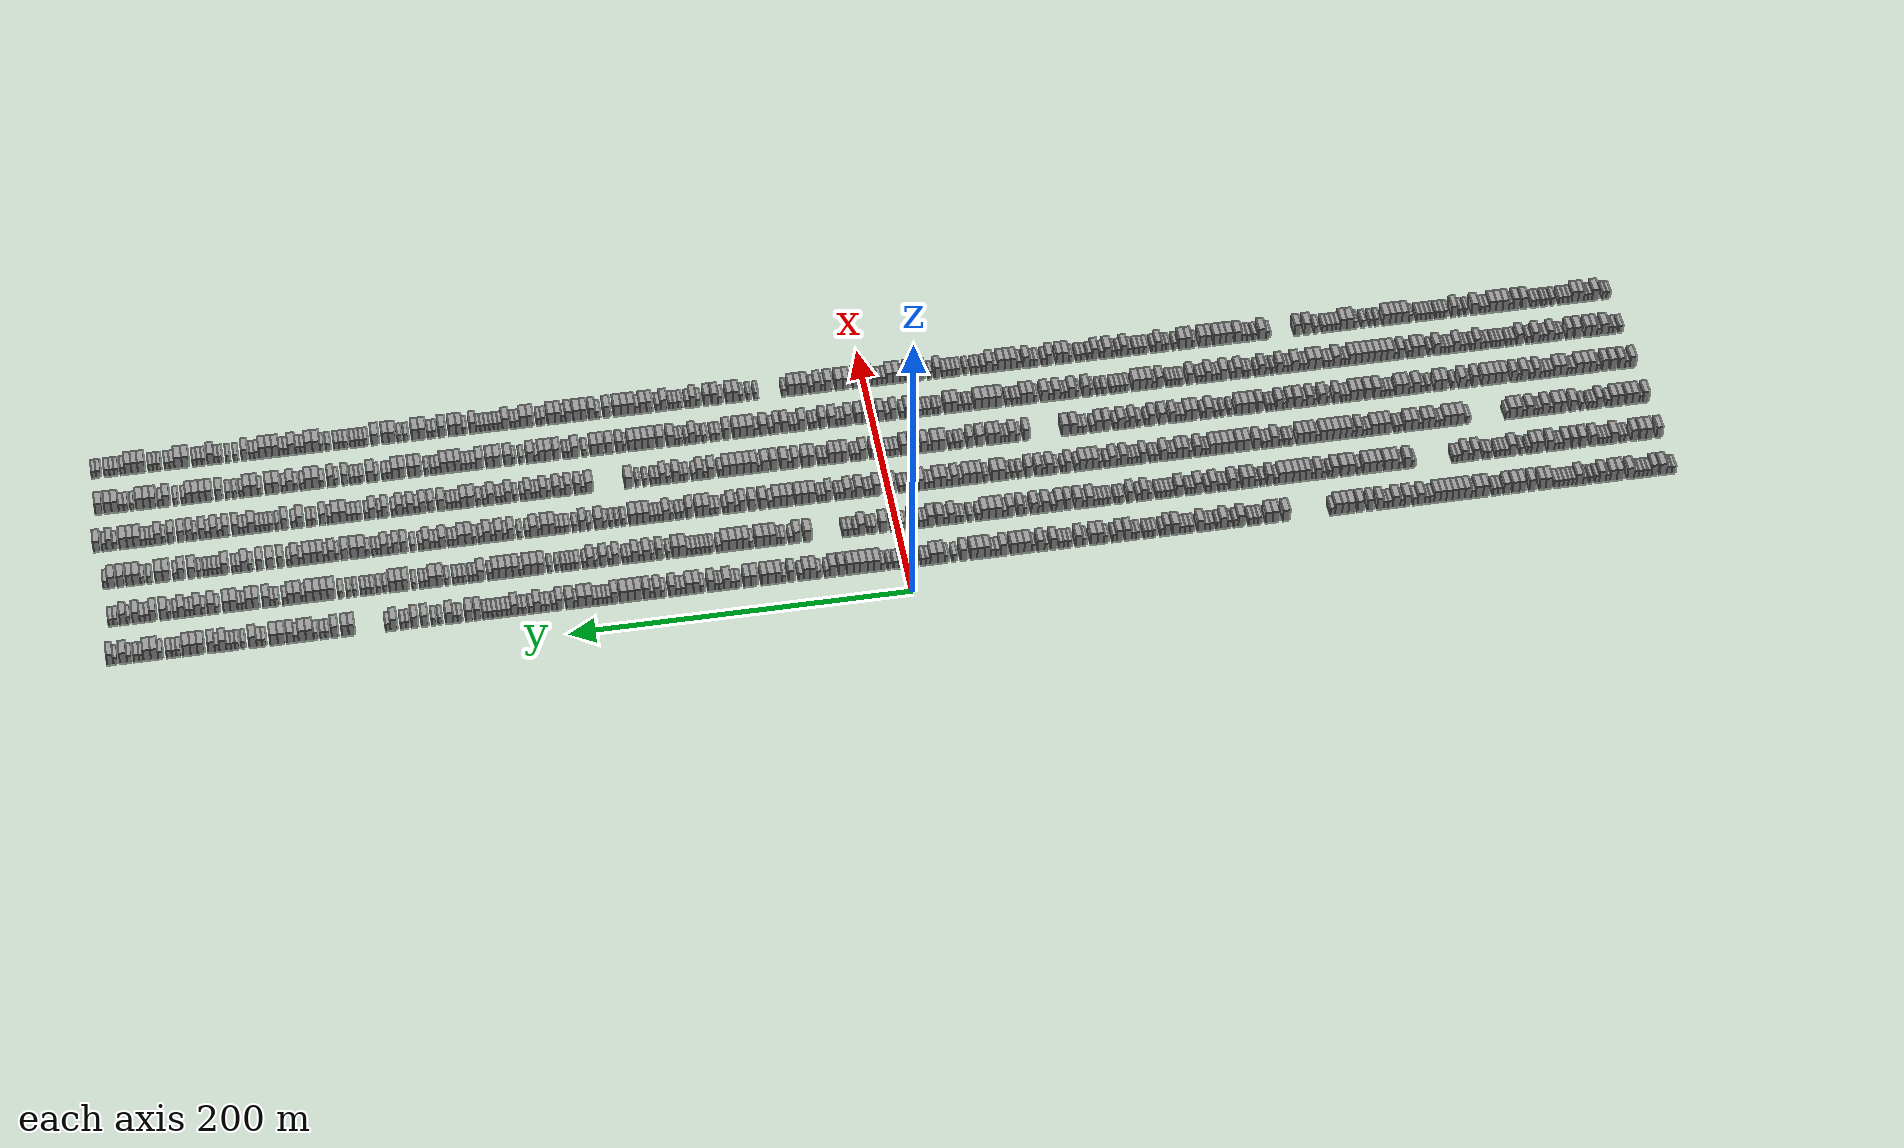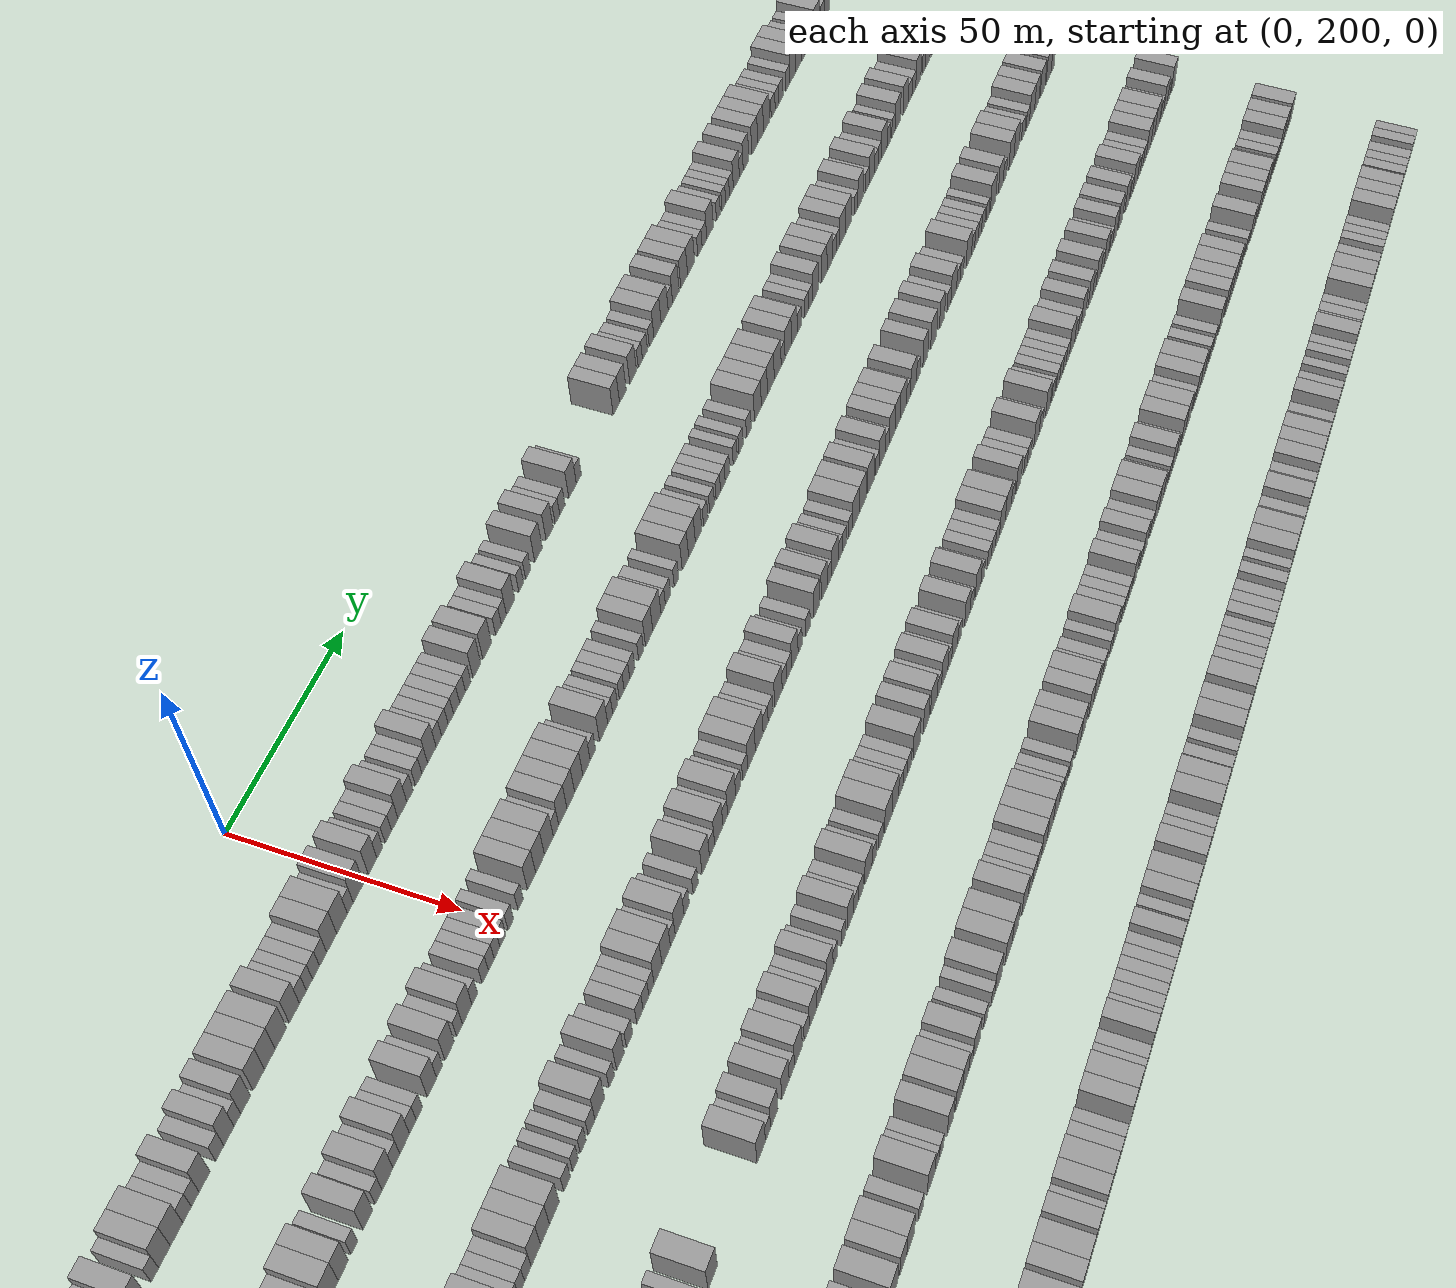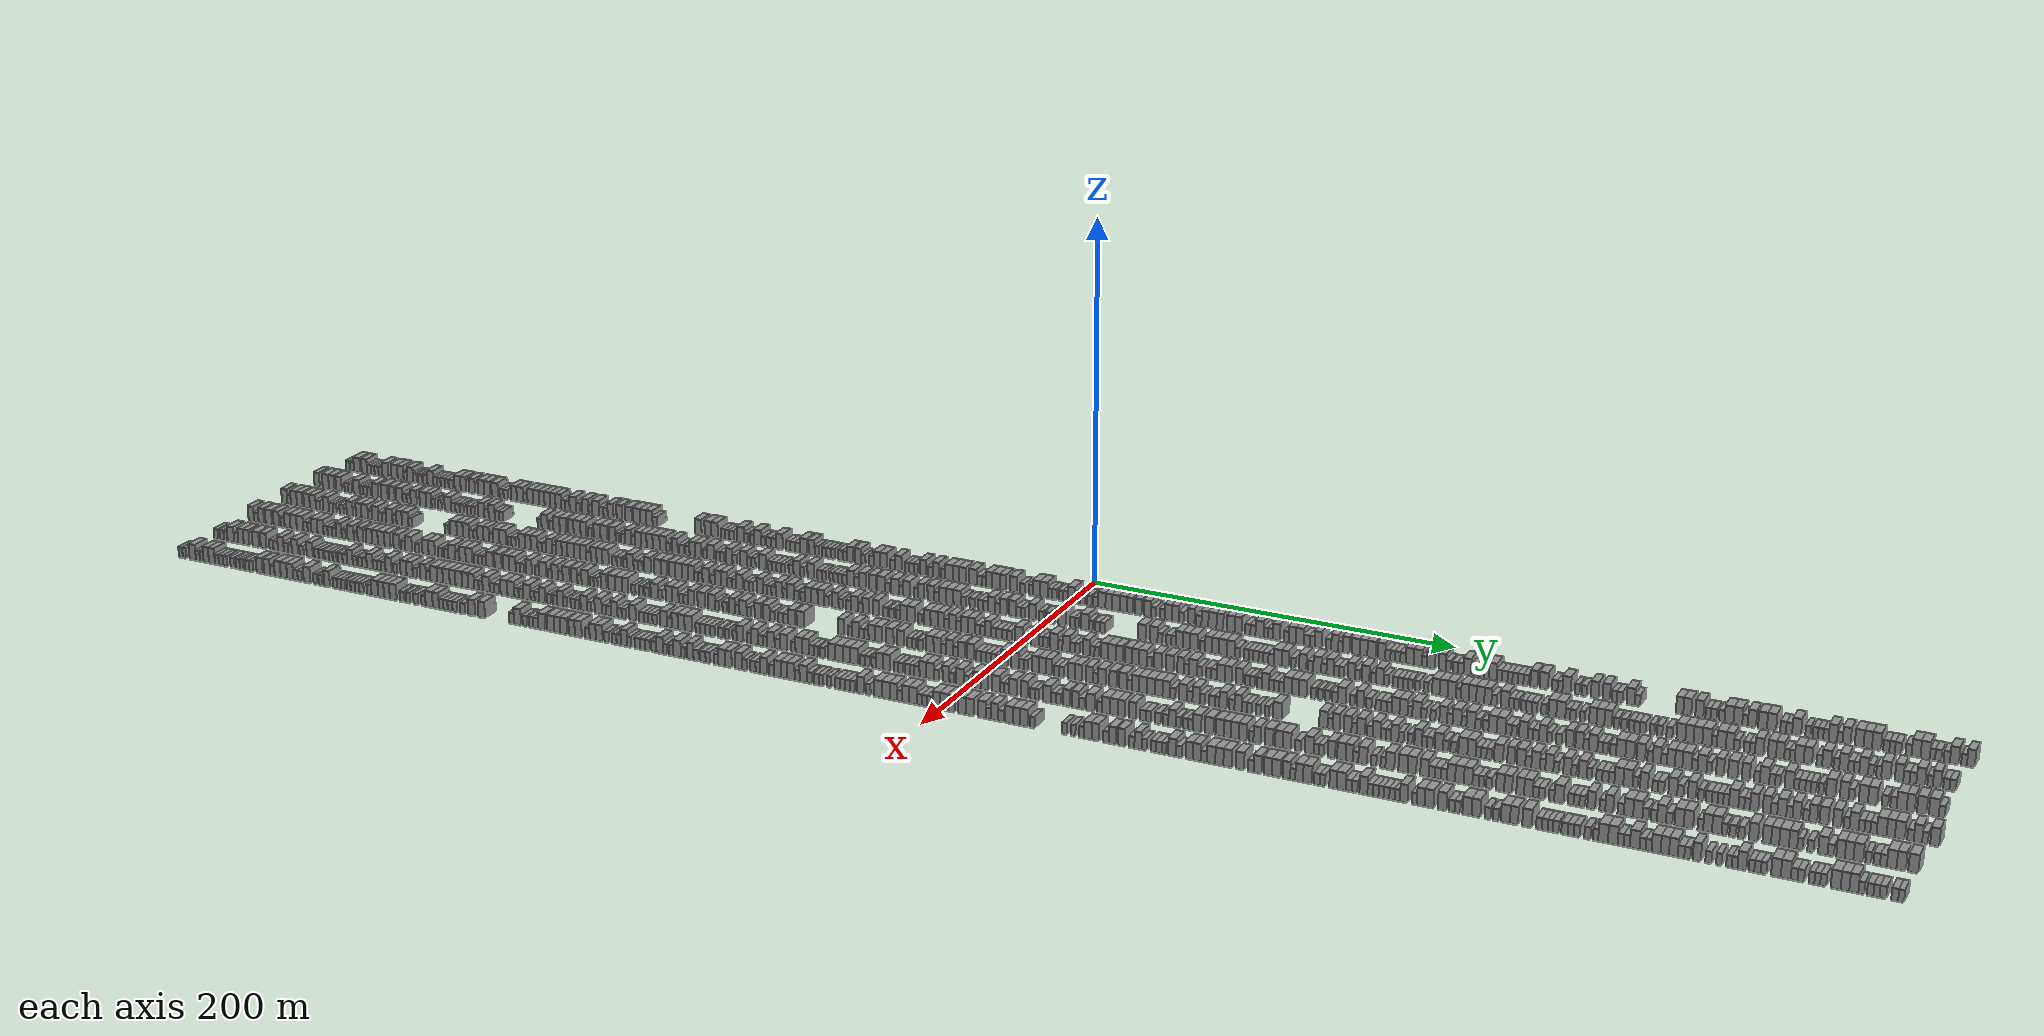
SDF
<sdf version="1.6">
 <world name="default">
  <scene>
   <sky><clouds><speed>12</speed></clouds></sky>
   <ambient>0.4 0.4 0.4 1</ambient>
   <background>0.7 0.7 0.7 1</background>
   <shadows>1</shadows>
  </scene>
  <gravity>0 0 -9.8066</gravity>
  <magnetic_field>6e-06 2.3e-05 -4.2e-05</magnetic_field>
  <physics default="0" name="default_physics" type="ode">
   <ode>
    <solver>
     <type>quick</type>
     <iters>10</iters>
     <sor>1.0</sor>
     <use_dynamic_moi_rescaling>0</use_dynamic_moi_rescaling>
    </solver>
    <constraints>
     <cfm>0</cfm>
     <erp>0.2</erp>
     <contact_max_correcting_vel>100</contact_max_correcting_vel>
     <contact_surface_layer>0.001</contact_surface_layer>
    </constraints>
   </ode>
   <max_step_size>0.004</max_step_size>
   <real_time_factor>1</real_time_factor>
   <real_time_update_rate>250</real_time_update_rate>
  </physics>
  <light name="sun" type="directional">
   <pose>0 0 10 0 0 0</pose>
   <diffuse>0.8 0.8 0.8 1</diffuse>
   <specular>0.2 0.2 0.2 1</specular>
   <attenuation>
    <range>1000</range>
    <constant>0.9</constant>
    <linear>0.01</linear>
    <quadratic>0.001</quadratic>
   </attenuation>
   <direction>-0.5 0.1 -0.9</direction>
  </light>
  <model name="building_1">
   <static>1</static>
   <pose>25.0000 -458.7097 0 0.000000 0.000000 0.000000</pose>
   <link name="link">
    <pose>0 0 3.00 0 0 0</pose>
    <collision name="collision"><geometry><box><size>10.0000 2.5806 6.0000</size></box></geometry></collision>
    <visual name="visual">
     <cast_shadows>0</cast_shadows>
     <geometry><box><size>10.0000 2.5806 6.0000</size></box></geometry>
     <material>
      <script>
       <uri>model://grey_wall/materials/scripts</uri>
       <uri>model://grey_wall/materials/textures</uri>
       <name>vrc/grey_wall</name>
      </script>
     </material>
    </visual>
   </link>
  </model>
  <model name="building_2">
   <static>1</static>
   <pose>25.0000 -455.9895 0 0.000000 0.000000 0.000000</pose>
   <link name="link">
    <pose>0 0 3.00 0 0 0</pose>
    <collision name="collision"><geometry><box><size>10.0000 2.8598 6.0000</size></box></geometry></collision>
    <visual name="visual">
     <cast_shadows>0</cast_shadows>
     <geometry><box><size>10.0000 2.8598 6.0000</size></box></geometry>
     <material>
      <script>
       <uri>model://grey_wall/materials/scripts</uri>
       <uri>model://grey_wall/materials/textures</uri>
       <name>vrc/grey_wall</name>
      </script>
     </material>
    </visual>
   </link>
  </model>
  <model name="building_3">
   <static>1</static>
   <pose>25.0000 -452.3602 0 0.000000 0.000000 0.000000</pose>
   <link name="link">
    <pose>0 0 4.50 0 0 0</pose>
    <collision name="collision"><geometry><box><size>10.0000 4.3987 9.0000</size></box></geometry></collision>
    <visual name="visual">
     <cast_shadows>0</cast_shadows>
     <geometry><box><size>10.0000 4.3987 9.0000</size></box></geometry>
     <material>
      <script>
       <uri>model://grey_wall/materials/scripts</uri>
       <uri>model://grey_wall/materials/textures</uri>
       <name>vrc/grey_wall</name>
      </script>
     </material>
    </visual>
   </link>
  </model>
  <model name="building_4">
   <static>1</static>
   <pose>25.0000 -447.2321 0 0.000000 0.000000 0.000000</pose>
   <link name="link">
    <pose>0 0 4.50 0 0 0</pose>
    <collision name="collision"><geometry><box><size>10.0000 3.8574 9.0000</size></box></geometry></collision>
    <visual name="visual">
     <cast_shadows>0</cast_shadows>
     <geometry><box><size>10.0000 3.8574 9.0000</size></box></geometry>
     <material>
      <script>
       <uri>model://grey_wall/materials/scripts</uri>
       <uri>model://grey_wall/materials/textures</uri>
       <name>vrc/grey_wall</name>
      </script>
     </material>
    </visual>
   </link>
  </model>
  <model name="building_5">
   <static>1</static>
   <pose>25.0000 -443.9715 0 0.000000 0.000000 0.000000</pose>
   <link name="link">
    <pose>0 0 3.00 0 0 0</pose>
    <collision name="collision"><geometry><box><size>10.0000 2.6639 6.0000</size></box></geometry></collision>
    <visual name="visual">
     <cast_shadows>0</cast_shadows>
     <geometry><box><size>10.0000 2.6639 6.0000</size></box></geometry>
     <material>
      <script>
       <uri>model://grey_wall/materials/scripts</uri>
       <uri>model://grey_wall/materials/textures</uri>
       <name>vrc/grey_wall</name>
      </script>
     </material>
    </visual>
   </link>
  </model>
  <model name="building_6">
   <static>1</static>
   <pose>25.0000 -441.3762 0 0.000000 0.000000 0.000000</pose>
   <link name="link">
    <pose>0 0 3.00 0 0 0</pose>
    <collision name="collision"><geometry><box><size>10.0000 2.5268 6.0000</size></box></geometry></collision>
    <visual name="visual">
     <cast_shadows>0</cast_shadows>
     <geometry><box><size>10.0000 2.5268 6.0000</size></box></geometry>
     <material>
      <script>
       <uri>model://grey_wall/materials/scripts</uri>
       <uri>model://grey_wall/materials/textures</uri>
       <name>vrc/grey_wall</name>
      </script>
     </material>
    </visual>
   </link>
  </model>
  <model name="building_7">
   <static>1</static>
   <pose>25.0000 -438.7373 0 0.000000 0.000000 0.000000</pose>
   <link name="link">
    <pose>0 0 3.00 0 0 0</pose>
    <collision name="collision"><geometry><box><size>10.0000 2.7510 6.0000</size></box></geometry></collision>
    <visual name="visual">
     <cast_shadows>0</cast_shadows>
     <geometry><box><size>10.0000 2.7510 6.0000</size></box></geometry>
     <material>
      <script>
       <uri>model://grey_wall/materials/scripts</uri>
       <uri>model://grey_wall/materials/textures</uri>
       <name>vrc/grey_wall</name>
      </script>
     </material>
    </visual>
   </link>
  </model>
  <model name="building_8">
   <static>1</static>
   <pose>25.0000 -436.0345 0 0.000000 0.000000 0.000000</pose>
   <link name="link">
    <pose>0 0 3.00 0 0 0</pose>
    <collision name="collision"><geometry><box><size>10.0000 2.6544 6.0000</size></box></geometry></collision>
    <visual name="visual">
     <cast_shadows>0</cast_shadows>
     <geometry><box><size>10.0000 2.6544 6.0000</size></box></geometry>
     <material>
      <script>
       <uri>model://grey_wall/materials/scripts</uri>
       <uri>model://grey_wall/materials/textures</uri>
       <name>vrc/grey_wall</name>
      </script>
     </material>
    </visual>
   </link>
  </model>
  <model name="building_9">
   <static>1</static>
   <pose>25.0000 -432.5922 0 0.000000 0.000000 0.000000</pose>
   <link name="link">
    <pose>0 0 4.50 0 0 0</pose>
    <collision name="collision"><geometry><box><size>10.0000 4.2303 9.0000</size></box></geometry></collision>
    <visual name="visual">
     <cast_shadows>0</cast_shadows>
     <geometry><box><size>10.0000 4.2303 9.0000</size></box></geometry>
     <material>
      <script>
       <uri>model://grey_wall/materials/scripts</uri>
       <uri>model://grey_wall/materials/textures</uri>
       <name>vrc/grey_wall</name>
      </script>
     </material>
    </visual>
   </link>
  </model>
  <model name="building_10">
   <static>1</static>
   <pose>25.0000 -426.3155 0 0.000000 0.000000 0.000000</pose>
   <link name="link">
    <pose>0 0 4.50 0 0 0</pose>
    <collision name="collision"><geometry><box><size>10.0000 4.3231 9.0000</size></box></geometry></collision>
    <visual name="visual">
     <cast_shadows>0</cast_shadows>
     <geometry><box><size>10.0000 4.3231 9.0000</size></box></geometry>
     <material>
      <script>
       <uri>model://grey_wall/materials/scripts</uri>
       <uri>model://grey_wall/materials/textures</uri>
       <name>vrc/grey_wall</name>
      </script>
     </material>
    </visual>
   </link>
  </model>
  <model name="building_11">
   <static>1</static>
   <pose>25.0000 -422.1147 0 0.000000 0.000000 0.000000</pose>
   <link name="link">
    <pose>0 0 4.50 0 0 0</pose>
    <collision name="collision"><geometry><box><size>10.0000 4.0785 9.0000</size></box></geometry></collision>
    <visual name="visual">
     <cast_shadows>0</cast_shadows>
     <geometry><box><size>10.0000 4.0785 9.0000</size></box></geometry>
     <material>
      <script>
       <uri>model://grey_wall/materials/scripts</uri>
       <uri>model://grey_wall/materials/textures</uri>
       <name>vrc/grey_wall</name>
      </script>
     </material>
    </visual>
   </link>
  </model>
  <model name="building_12">
   <static>1</static>
   <pose>25.0000 -418.7871 0 0.000000 0.000000 0.000000</pose>
   <link name="link">
    <pose>0 0 3.00 0 0 0</pose>
    <collision name="collision"><geometry><box><size>10.0000 2.5768 6.0000</size></box></geometry></collision>
    <visual name="visual">
     <cast_shadows>0</cast_shadows>
     <geometry><box><size>10.0000 2.5768 6.0000</size></box></geometry>
     <material>
      <script>
       <uri>model://grey_wall/materials/scripts</uri>
       <uri>model://grey_wall/materials/textures</uri>
       <name>vrc/grey_wall</name>
      </script>
     </material>
    </visual>
   </link>
  </model>
  <model name="building_13">
   <static>1</static>
   <pose>25.0000 -415.4768 0 0.000000 0.000000 0.000000</pose>
   <link name="link">
    <pose>0 0 4.50 0 0 0</pose>
    <collision name="collision"><geometry><box><size>10.0000 4.0438 9.0000</size></box></geometry></collision>
    <visual name="visual">
     <cast_shadows>0</cast_shadows>
     <geometry><box><size>10.0000 4.0438 9.0000</size></box></geometry>
     <material>
      <script>
       <uri>model://grey_wall/materials/scripts</uri>
       <uri>model://grey_wall/materials/textures</uri>
       <name>vrc/grey_wall</name>
      </script>
     </material>
    </visual>
   </link>
  </model>
  <model name="building_14">
   <static>1</static>
   <pose>25.0000 -412.1914 0 0.000000 0.000000 0.000000</pose>
   <link name="link">
    <pose>0 0 3.00 0 0 0</pose>
    <collision name="collision"><geometry><box><size>10.0000 2.5270 6.0000</size></box></geometry></collision>
    <visual name="visual">
     <cast_shadows>0</cast_shadows>
     <geometry><box><size>10.0000 2.5270 6.0000</size></box></geometry>
     <material>
      <script>
       <uri>model://grey_wall/materials/scripts</uri>
       <uri>model://grey_wall/materials/textures</uri>
       <name>vrc/grey_wall</name>
      </script>
     </material>
    </visual>
   </link>
  </model>
  <model name="building_15">
   <static>1</static>
   <pose>25.0000 -408.7061 0 0.000000 0.000000 0.000000</pose>
   <link name="link">
    <pose>0 0 3.00 0 0 0</pose>
    <collision name="collision"><geometry><box><size>10.0000 2.4434 6.0000</size></box></geometry></collision>
    <visual name="visual">
     <cast_shadows>0</cast_shadows>
     <geometry><box><size>10.0000 2.4434 6.0000</size></box></geometry>
     <material>
      <script>
       <uri>model://grey_wall/materials/scripts</uri>
       <uri>model://grey_wall/materials/textures</uri>
       <name>vrc/grey_wall</name>
      </script>
     </material>
    </visual>
   </link>
  </model>
  <model name="building_16">
   <static>1</static>
   <pose>25.0000 -405.0560 0 0.000000 0.000000 0.000000</pose>
   <link name="link">
    <pose>0 0 3.00 0 0 0</pose>
    <collision name="collision"><geometry><box><size>10.0000 2.8570 6.0000</size></box></geometry></collision>
    <visual name="visual">
     <cast_shadows>0</cast_shadows>
     <geometry><box><size>10.0000 2.8570 6.0000</size></box></geometry>
     <material>
      <script>
       <uri>model://grey_wall/materials/scripts</uri>
       <uri>model://grey_wall/materials/textures</uri>
       <name>vrc/grey_wall</name>
      </script>
     </material>
    </visual>
   </link>
  </model>
  <model name="building_17">
   <static>1</static>
   <pose>25.0000 -401.5997 0 0.000000 0.000000 0.000000</pose>
   <link name="link">
    <pose>0 0 4.50 0 0 0</pose>
    <collision name="collision"><geometry><box><size>10.0000 4.0554 9.0000</size></box></geometry></collision>
    <visual name="visual">
     <cast_shadows>0</cast_shadows>
     <geometry><box><size>10.0000 4.0554 9.0000</size></box></geometry>
     <material>
      <script>
       <uri>model://grey_wall/materials/scripts</uri>
       <uri>model://grey_wall/materials/textures</uri>
       <name>vrc/grey_wall</name>
      </script>
     </material>
    </visual>
   </link>
  </model>
  <model name="building_18">
   <static>1</static>
   <pose>25.0000 -398.3646 0 0.000000 0.000000 0.000000</pose>
   <link name="link">
    <pose>0 0 3.00 0 0 0</pose>
    <collision name="collision"><geometry><box><size>10.0000 2.4149 6.0000</size></box></geometry></collision>
    <visual name="visual">
     <cast_shadows>0</cast_shadows>
     <geometry><box><size>10.0000 2.4149 6.0000</size></box></geometry>
     <material>
      <script>
       <uri>model://grey_wall/materials/scripts</uri>
       <uri>model://grey_wall/materials/textures</uri>
       <name>vrc/grey_wall</name>
      </script>
     </material>
    </visual>
   </link>
  </model>
  <model name="building_19">
   <static>1</static>
   <pose>25.0000 -395.8780 0 0.000000 0.000000 0.000000</pose>
   <link name="link">
    <pose>0 0 3.00 0 0 0</pose>
    <collision name="collision"><geometry><box><size>10.0000 2.5582 6.0000</size></box></geometry></collision>
    <visual name="visual">
     <cast_shadows>0</cast_shadows>
     <geometry><box><size>10.0000 2.5582 6.0000</size></box></geometry>
     <material>
      <script>
       <uri>model://grey_wall/materials/scripts</uri>
       <uri>model://grey_wall/materials/textures</uri>
       <name>vrc/grey_wall</name>
      </script>
     </material>
    </visual>
   </link>
  </model>
  <model name="building_20">
   <static>1</static>
   <pose>25.0000 -393.1696 0 0.000000 0.000000 0.000000</pose>
   <link name="link">
    <pose>0 0 3.00 0 0 0</pose>
    <collision name="collision"><geometry><box><size>10.0000 2.8586 6.0000</size></box></geometry></collision>
    <visual name="visual">
     <cast_shadows>0</cast_shadows>
     <geometry><box><size>10.0000 2.8586 6.0000</size></box></geometry>
     <material>
      <script>
       <uri>model://grey_wall/materials/scripts</uri>
       <uri>model://grey_wall/materials/textures</uri>
       <name>vrc/grey_wall</name>
      </script>
     </material>
    </visual>
   </link>
  </model>
  <model name="building_21">
   <static>1</static>
   <pose>25.0000 -390.4331 0 0.000000 0.000000 0.000000</pose>
   <link name="link">
    <pose>0 0 3.00 0 0 0</pose>
    <collision name="collision"><geometry><box><size>10.0000 2.6144 6.0000</size></box></geometry></collision>
    <visual name="visual">
     <cast_shadows>0</cast_shadows>
     <geometry><box><size>10.0000 2.6144 6.0000</size></box></geometry>
     <material>
      <script>
       <uri>model://grey_wall/materials/scripts</uri>
       <uri>model://grey_wall/materials/textures</uri>
       <name>vrc/grey_wall</name>
      </script>
     </material>
    </visual>
   </link>
  </model>
  <model name="building_22">
   <static>1</static>
   <pose>25.0000 -387.6450 0 0.000000 0.000000 0.000000</pose>
   <link name="link">
    <pose>0 0 3.00 0 0 0</pose>
    <collision name="collision"><geometry><box><size>10.0000 2.9618 6.0000</size></box></geometry></collision>
    <visual name="visual">
     <cast_shadows>0</cast_shadows>
     <geometry><box><size>10.0000 2.9618 6.0000</size></box></geometry>
     <material>
      <script>
       <uri>model://grey_wall/materials/scripts</uri>
       <uri>model://grey_wall/materials/textures</uri>
       <name>vrc/grey_wall</name>
      </script>
     </material>
    </visual>
   </link>
  </model>
  <model name="building_23">
   <static>1</static>
   <pose>25.0000 -383.0894 0 0.000000 0.000000 0.000000</pose>
   <link name="link">
    <pose>0 0 4.50 0 0 0</pose>
    <collision name="collision"><geometry><box><size>10.0000 4.1492 9.0000</size></box></geometry></collision>
    <visual name="visual">
     <cast_shadows>0</cast_shadows>
     <geometry><box><size>10.0000 4.1492 9.0000</size></box></geometry>
     <material>
      <script>
       <uri>model://grey_wall/materials/scripts</uri>
       <uri>model://grey_wall/materials/textures</uri>
       <name>vrc/grey_wall</name>
      </script>
     </material>
    </visual>
   </link>
  </model>
  <model name="building_24">
   <static>1</static>
   <pose>25.0000 -379.1485 0 0.000000 0.000000 0.000000</pose>
   <link name="link">
    <pose>0 0 4.50 0 0 0</pose>
    <collision name="collision"><geometry><box><size>10.0000 3.7327 9.0000</size></box></geometry></collision>
    <visual name="visual">
     <cast_shadows>0</cast_shadows>
     <geometry><box><size>10.0000 3.7327 9.0000</size></box></geometry>
     <material>
      <script>
       <uri>model://grey_wall/materials/scripts</uri>
       <uri>model://grey_wall/materials/textures</uri>
       <name>vrc/grey_wall</name>
      </script>
     </material>
    </visual>
   </link>
  </model>
  <model name="building_25">
   <static>1</static>
   <pose>25.0000 -373.2622 0 0.000000 0.000000 0.000000</pose>
   <link name="link">
    <pose>0 0 4.50 0 0 0</pose>
    <collision name="collision"><geometry><box><size>10.0000 4.0399 9.0000</size></box></geometry></collision>
    <visual name="visual">
     <cast_shadows>0</cast_shadows>
     <geometry><box><size>10.0000 4.0399 9.0000</size></box></geometry>
     <material>
      <script>
       <uri>model://grey_wall/materials/scripts</uri>
       <uri>model://grey_wall/materials/textures</uri>
       <name>vrc/grey_wall</name>
      </script>
     </material>
    </visual>
   </link>
  </model>
  <model name="building_26">
   <static>1</static>
   <pose>25.0000 -367.1786 0 0.000000 0.000000 0.000000</pose>
   <link name="link">
    <pose>0 0 4.50 0 0 0</pose>
    <collision name="collision"><geometry><box><size>10.0000 4.1273 9.0000</size></box></geometry></collision>
    <visual name="visual">
     <cast_shadows>0</cast_shadows>
     <geometry><box><size>10.0000 4.1273 9.0000</size></box></geometry>
     <material>
      <script>
       <uri>model://grey_wall/materials/scripts</uri>
       <uri>model://grey_wall/materials/textures</uri>
       <name>vrc/grey_wall</name>
      </script>
     </material>
    </visual>
   </link>
  </model>
  <model name="building_27">
   <static>1</static>
   <pose>25.0000 -363.0500 0 0.000000 0.000000 0.000000</pose>
   <link name="link">
    <pose>0 0 4.50 0 0 0</pose>
    <collision name="collision"><geometry><box><size>10.0000 4.1300 9.0000</size></box></geometry></collision>
    <visual name="visual">
     <cast_shadows>0</cast_shadows>
     <geometry><box><size>10.0000 4.1300 9.0000</size></box></geometry>
     <material>
      <script>
       <uri>model://grey_wall/materials/scripts</uri>
       <uri>model://grey_wall/materials/textures</uri>
       <name>vrc/grey_wall</name>
      </script>
     </material>
    </visual>
   </link>
  </model>
  <model name="building_28">
   <static>1</static>
   <pose>25.0000 -357.8621 0 0.000000 0.000000 0.000000</pose>
   <link name="link">
    <pose>0 0 4.50 0 0 0</pose>
    <collision name="collision"><geometry><box><size>10.0000 4.2459 9.0000</size></box></geometry></collision>
    <visual name="visual">
     <cast_shadows>0</cast_shadows>
     <geometry><box><size>10.0000 4.2459 9.0000</size></box></geometry>
     <material>
      <script>
       <uri>model://grey_wall/materials/scripts</uri>
       <uri>model://grey_wall/materials/textures</uri>
       <name>vrc/grey_wall</name>
      </script>
     </material>
    </visual>
   </link>
  </model>
  <model name="building_29">
   <static>1</static>
   <pose>25.0000 -353.3727 0 0.000000 0.000000 0.000000</pose>
   <link name="link">
    <pose>0 0 3.00 0 0 0</pose>
    <collision name="collision"><geometry><box><size>10.0000 2.7329 6.0000</size></box></geometry></collision>
    <visual name="visual">
     <cast_shadows>0</cast_shadows>
     <geometry><box><size>10.0000 2.7329 6.0000</size></box></geometry>
     <material>
      <script>
       <uri>model://grey_wall/materials/scripts</uri>
       <uri>model://grey_wall/materials/textures</uri>
       <name>vrc/grey_wall</name>
      </script>
     </material>
    </visual>
   </link>
  </model>
  <model name="building_30">
   <static>1</static>
   <pose>25.0000 -350.5261 0 0.000000 0.000000 0.000000</pose>
   <link name="link">
    <pose>0 0 3.00 0 0 0</pose>
    <collision name="collision"><geometry><box><size>10.0000 2.9603 6.0000</size></box></geometry></collision>
    <visual name="visual">
     <cast_shadows>0</cast_shadows>
     <geometry><box><size>10.0000 2.9603 6.0000</size></box></geometry>
     <material>
      <script>
       <uri>model://grey_wall/materials/scripts</uri>
       <uri>model://grey_wall/materials/textures</uri>
       <name>vrc/grey_wall</name>
      </script>
     </material>
    </visual>
   </link>
  </model>
  <model name="building_31">
   <static>1</static>
   <pose>25.0000 -345.0916 0 0.000000 0.000000 0.000000</pose>
   <link name="link">
    <pose>0 0 4.50 0 0 0</pose>
    <collision name="collision"><geometry><box><size>10.0000 3.9087 9.0000</size></box></geometry></collision>
    <visual name="visual">
     <cast_shadows>0</cast_shadows>
     <geometry><box><size>10.0000 3.9087 9.0000</size></box></geometry>
     <material>
      <script>
       <uri>model://grey_wall/materials/scripts</uri>
       <uri>model://grey_wall/materials/textures</uri>
       <name>vrc/grey_wall</name>
      </script>
     </material>
    </visual>
   </link>
  </model>
  <model name="building_32">
   <static>1</static>
   <pose>25.0000 -340.9366 0 0.000000 0.000000 0.000000</pose>
   <link name="link">
    <pose>0 0 4.50 0 0 0</pose>
    <collision name="collision"><geometry><box><size>10.0000 4.4014 9.0000</size></box></geometry></collision>
    <visual name="visual">
     <cast_shadows>0</cast_shadows>
     <geometry><box><size>10.0000 4.4014 9.0000</size></box></geometry>
     <material>
      <script>
       <uri>model://grey_wall/materials/scripts</uri>
       <uri>model://grey_wall/materials/textures</uri>
       <name>vrc/grey_wall</name>
      </script>
     </material>
    </visual>
   </link>
  </model>
  <model name="building_33">
   <static>1</static>
   <pose>25.0000 -337.3768 0 0.000000 0.000000 0.000000</pose>
   <link name="link">
    <pose>0 0 3.00 0 0 0</pose>
    <collision name="collision"><geometry><box><size>10.0000 2.7182 6.0000</size></box></geometry></collision>
    <visual name="visual">
     <cast_shadows>0</cast_shadows>
     <geometry><box><size>10.0000 2.7182 6.0000</size></box></geometry>
     <material>
      <script>
       <uri>model://grey_wall/materials/scripts</uri>
       <uri>model://grey_wall/materials/textures</uri>
       <name>vrc/grey_wall</name>
      </script>
     </material>
    </visual>
   </link>
  </model>
  <model name="building_34">
   <static>1</static>
   <pose>25.0000 -334.1154 0 0.000000 0.000000 0.000000</pose>
   <link name="link">
    <pose>0 0 4.50 0 0 0</pose>
    <collision name="collision"><geometry><box><size>10.0000 3.8047 9.0000</size></box></geometry></collision>
    <visual name="visual">
     <cast_shadows>0</cast_shadows>
     <geometry><box><size>10.0000 3.8047 9.0000</size></box></geometry>
     <material>
      <script>
       <uri>model://grey_wall/materials/scripts</uri>
       <uri>model://grey_wall/materials/textures</uri>
       <name>vrc/grey_wall</name>
      </script>
     </material>
    </visual>
   </link>
  </model>
  <model name="building_35">
   <static>1</static>
   <pose>25.0000 -330.2671 0 0.000000 0.000000 0.000000</pose>
   <link name="link">
    <pose>0 0 4.50 0 0 0</pose>
    <collision name="collision"><geometry><box><size>10.0000 3.8918 9.0000</size></box></geometry></collision>
    <visual name="visual">
     <cast_shadows>0</cast_shadows>
     <geometry><box><size>10.0000 3.8918 9.0000</size></box></geometry>
     <material>
      <script>
       <uri>model://grey_wall/materials/scripts</uri>
       <uri>model://grey_wall/materials/textures</uri>
       <name>vrc/grey_wall</name>
      </script>
     </material>
    </visual>
   </link>
  </model>
  <model name="building_36">
   <static>1</static>
   <pose>25.0000 -326.5169 0 0.000000 0.000000 0.000000</pose>
   <link name="link">
    <pose>0 0 4.50 0 0 0</pose>
    <collision name="collision"><geometry><box><size>10.0000 3.6088 9.0000</size></box></geometry></collision>
    <visual name="visual">
     <cast_shadows>0</cast_shadows>
     <geometry><box><size>10.0000 3.6088 9.0000</size></box></geometry>
     <material>
      <script>
       <uri>model://grey_wall/materials/scripts</uri>
       <uri>model://grey_wall/materials/textures</uri>
       <name>vrc/grey_wall</name>
      </script>
     </material>
    </visual>
   </link>
  </model>
  <model name="building_37">
   <static>1</static>
   <pose>25.0000 -322.8795 0 0.000000 0.000000 0.000000</pose>
   <link name="link">
    <pose>0 0 4.50 0 0 0</pose>
    <collision name="collision"><geometry><box><size>10.0000 3.6660 9.0000</size></box></geometry></collision>
    <visual name="visual">
     <cast_shadows>0</cast_shadows>
     <geometry><box><size>10.0000 3.6660 9.0000</size></box></geometry>
     <material>
      <script>
       <uri>model://grey_wall/materials/scripts</uri>
       <uri>model://grey_wall/materials/textures</uri>
       <name>vrc/grey_wall</name>
      </script>
     </material>
    </visual>
   </link>
  </model>
  <model name="building_38">
   <static>1</static>
   <pose>25.0000 -319.2325 0 0.000000 0.000000 0.000000</pose>
   <link name="link">
    <pose>0 0 4.50 0 0 0</pose>
    <collision name="collision"><geometry><box><size>10.0000 3.6280 9.0000</size></box></geometry></collision>
    <visual name="visual">
     <cast_shadows>0</cast_shadows>
     <geometry><box><size>10.0000 3.6280 9.0000</size></box></geometry>
     <material>
      <script>
       <uri>model://grey_wall/materials/scripts</uri>
       <uri>model://grey_wall/materials/textures</uri>
       <name>vrc/grey_wall</name>
      </script>
     </material>
    </visual>
   </link>
  </model>
  <model name="building_39">
   <static>1</static>
   <pose>25.0000 -315.5780 0 0.000000 0.000000 0.000000</pose>
   <link name="link">
    <pose>0 0 4.50 0 0 0</pose>
    <collision name="collision"><geometry><box><size>10.0000 3.6810 9.0000</size></box></geometry></collision>
    <visual name="visual">
     <cast_shadows>0</cast_shadows>
     <geometry><box><size>10.0000 3.6810 9.0000</size></box></geometry>
     <material>
      <script>
       <uri>model://grey_wall/materials/scripts</uri>
       <uri>model://grey_wall/materials/textures</uri>
       <name>vrc/grey_wall</name>
      </script>
     </material>
    </visual>
   </link>
  </model>
  <model name="building_40">
   <static>1</static>
   <pose>25.0000 -312.4079 0 0.000000 0.000000 0.000000</pose>
   <link name="link">
    <pose>0 0 3.00 0 0 0</pose>
    <collision name="collision"><geometry><box><size>10.0000 2.6592 6.0000</size></box></geometry></collision>
    <visual name="visual">
     <cast_shadows>0</cast_shadows>
     <geometry><box><size>10.0000 2.6592 6.0000</size></box></geometry>
     <material>
      <script>
       <uri>model://grey_wall/materials/scripts</uri>
       <uri>model://grey_wall/materials/textures</uri>
       <name>vrc/grey_wall</name>
      </script>
     </material>
    </visual>
   </link>
  </model>
  <model name="building_41">
   <static>1</static>
   <pose>25.0000 -309.6096 0 0.000000 0.000000 0.000000</pose>
   <link name="link">
    <pose>0 0 3.00 0 0 0</pose>
    <collision name="collision"><geometry><box><size>10.0000 2.9374 6.0000</size></box></geometry></collision>
    <visual name="visual">
     <cast_shadows>0</cast_shadows>
     <geometry><box><size>10.0000 2.9374 6.0000</size></box></geometry>
     <material>
      <script>
       <uri>model://grey_wall/materials/scripts</uri>
       <uri>model://grey_wall/materials/textures</uri>
       <name>vrc/grey_wall</name>
      </script>
     </material>
    </visual>
   </link>
  </model>
  <model name="building_42">
   <static>1</static>
   <pose>25.0000 -306.0149 0 0.000000 0.000000 0.000000</pose>
   <link name="link">
    <pose>0 0 4.50 0 0 0</pose>
    <collision name="collision"><geometry><box><size>10.0000 4.2520 9.0000</size></box></geometry></collision>
    <visual name="visual">
     <cast_shadows>0</cast_shadows>
     <geometry><box><size>10.0000 4.2520 9.0000</size></box></geometry>
     <material>
      <script>
       <uri>model://grey_wall/materials/scripts</uri>
       <uri>model://grey_wall/materials/textures</uri>
       <name>vrc/grey_wall</name>
      </script>
     </material>
    </visual>
   </link>
  </model>
  <model name="building_43">
   <static>1</static>
   <pose>25.0000 -302.4522 0 0.000000 0.000000 0.000000</pose>
   <link name="link">
    <pose>0 0 3.00 0 0 0</pose>
    <collision name="collision"><geometry><box><size>10.0000 2.8735 6.0000</size></box></geometry></collision>
    <visual name="visual">
     <cast_shadows>0</cast_shadows>
     <geometry><box><size>10.0000 2.8735 6.0000</size></box></geometry>
     <material>
      <script>
       <uri>model://grey_wall/materials/scripts</uri>
       <uri>model://grey_wall/materials/textures</uri>
       <name>vrc/grey_wall</name>
      </script>
     </material>
    </visual>
   </link>
  </model>
  <model name="building_44">
   <static>1</static>
   <pose>25.0000 -297.8912 0 0.000000 0.000000 0.000000</pose>
   <link name="link">
    <pose>0 0 4.50 0 0 0</pose>
    <collision name="collision"><geometry><box><size>10.0000 4.2485 9.0000</size></box></geometry></collision>
    <visual name="visual">
     <cast_shadows>0</cast_shadows>
     <geometry><box><size>10.0000 4.2485 9.0000</size></box></geometry>
     <material>
      <script>
       <uri>model://grey_wall/materials/scripts</uri>
       <uri>model://grey_wall/materials/textures</uri>
       <name>vrc/grey_wall</name>
      </script>
     </material>
    </visual>
   </link>
  </model>
  <model name="building_45">
   <static>1</static>
   <pose>25.0000 -294.5247 0 0.000000 0.000000 0.000000</pose>
   <link name="link">
    <pose>0 0 3.00 0 0 0</pose>
    <collision name="collision"><geometry><box><size>10.0000 2.4846 6.0000</size></box></geometry></collision>
    <visual name="visual">
     <cast_shadows>0</cast_shadows>
     <geometry><box><size>10.0000 2.4846 6.0000</size></box></geometry>
     <material>
      <script>
       <uri>model://grey_wall/materials/scripts</uri>
       <uri>model://grey_wall/materials/textures</uri>
       <name>vrc/grey_wall</name>
      </script>
     </material>
    </visual>
   </link>
  </model>
  <model name="building_46">
   <static>1</static>
   <pose>25.0000 -291.0956 0 0.000000 0.000000 0.000000</pose>
   <link name="link">
    <pose>0 0 4.50 0 0 0</pose>
    <collision name="collision"><geometry><box><size>10.0000 4.3736 9.0000</size></box></geometry></collision>
    <visual name="visual">
     <cast_shadows>0</cast_shadows>
     <geometry><box><size>10.0000 4.3736 9.0000</size></box></geometry>
     <material>
      <script>
       <uri>model://grey_wall/materials/scripts</uri>
       <uri>model://grey_wall/materials/textures</uri>
       <name>vrc/grey_wall</name>
      </script>
     </material>
    </visual>
   </link>
  </model>
  <model name="building_47">
   <static>1</static>
   <pose>25.0000 -287.4428 0 0.000000 0.000000 0.000000</pose>
   <link name="link">
    <pose>0 0 3.00 0 0 0</pose>
    <collision name="collision"><geometry><box><size>10.0000 2.9320 6.0000</size></box></geometry></collision>
    <visual name="visual">
     <cast_shadows>0</cast_shadows>
     <geometry><box><size>10.0000 2.9320 6.0000</size></box></geometry>
     <material>
      <script>
       <uri>model://grey_wall/materials/scripts</uri>
       <uri>model://grey_wall/materials/textures</uri>
       <name>vrc/grey_wall</name>
      </script>
     </material>
    </visual>
   </link>
  </model>
  <model name="building_48">
   <static>1</static>
   <pose>25.0000 -284.6123 0 0.000000 0.000000 0.000000</pose>
   <link name="link">
    <pose>0 0 3.00 0 0 0</pose>
    <collision name="collision"><geometry><box><size>10.0000 2.7289 6.0000</size></box></geometry></collision>
    <visual name="visual">
     <cast_shadows>0</cast_shadows>
     <geometry><box><size>10.0000 2.7289 6.0000</size></box></geometry>
     <material>
      <script>
       <uri>model://grey_wall/materials/scripts</uri>
       <uri>model://grey_wall/materials/textures</uri>
       <name>vrc/grey_wall</name>
      </script>
     </material>
    </visual>
   </link>
  </model>
  <model name="building_49">
   <static>1</static>
   <pose>25.0000 -281.3459 0 0.000000 0.000000 0.000000</pose>
   <link name="link">
    <pose>0 0 4.50 0 0 0</pose>
    <collision name="collision"><geometry><box><size>10.0000 3.8039 9.0000</size></box></geometry></collision>
    <visual name="visual">
     <cast_shadows>0</cast_shadows>
     <geometry><box><size>10.0000 3.8039 9.0000</size></box></geometry>
     <material>
      <script>
       <uri>model://grey_wall/materials/scripts</uri>
       <uri>model://grey_wall/materials/textures</uri>
       <name>vrc/grey_wall</name>
      </script>
     </material>
    </visual>
   </link>
  </model>
  <model name="building_50">
   <static>1</static>
   <pose>25.0000 -275.5968 0 0.000000 0.000000 0.000000</pose>
   <link name="link">
    <pose>0 0 4.50 0 0 0</pose>
    <collision name="collision"><geometry><box><size>10.0000 3.6944 9.0000</size></box></geometry></collision>
    <visual name="visual">
     <cast_shadows>0</cast_shadows>
     <geometry><box><size>10.0000 3.6944 9.0000</size></box></geometry>
     <material>
      <script>
       <uri>model://grey_wall/materials/scripts</uri>
       <uri>model://grey_wall/materials/textures</uri>
       <name>vrc/grey_wall</name>
      </script>
     </material>
    </visual>
   </link>
  </model>
  <model name="building_51">
   <static>1</static>
   <pose>25.0000 -269.6578 0 0.000000 0.000000 0.000000</pose>
   <link name="link">
    <pose>0 0 4.50 0 0 0</pose>
    <collision name="collision"><geometry><box><size>10.0000 4.1835 9.0000</size></box></geometry></collision>
    <visual name="visual">
     <cast_shadows>0</cast_shadows>
     <geometry><box><size>10.0000 4.1835 9.0000</size></box></geometry>
     <material>
      <script>
       <uri>model://grey_wall/materials/scripts</uri>
       <uri>model://grey_wall/materials/textures</uri>
       <name>vrc/grey_wall</name>
      </script>
     </material>
    </visual>
   </link>
  </model>
  <model name="building_52">
   <static>1</static>
   <pose>25.0000 -264.3539 0 0.000000 0.000000 0.000000</pose>
   <link name="link">
    <pose>0 0 4.50 0 0 0</pose>
    <collision name="collision"><geometry><box><size>10.0000 4.4242 9.0000</size></box></geometry></collision>
    <visual name="visual">
     <cast_shadows>0</cast_shadows>
     <geometry><box><size>10.0000 4.4242 9.0000</size></box></geometry>
     <material>
      <script>
       <uri>model://grey_wall/materials/scripts</uri>
       <uri>model://grey_wall/materials/textures</uri>
       <name>vrc/grey_wall</name>
      </script>
     </material>
    </visual>
   </link>
  </model>
  <model name="building_53">
   <static>1</static>
   <pose>25.0000 -260.2732 0 0.000000 0.000000 0.000000</pose>
   <link name="link">
    <pose>0 0 4.50 0 0 0</pose>
    <collision name="collision"><geometry><box><size>10.0000 3.7373 9.0000</size></box></geometry></collision>
    <visual name="visual">
     <cast_shadows>0</cast_shadows>
     <geometry><box><size>10.0000 3.7373 9.0000</size></box></geometry>
     <material>
      <script>
       <uri>model://grey_wall/materials/scripts</uri>
       <uri>model://grey_wall/materials/textures</uri>
       <name>vrc/grey_wall</name>
      </script>
     </material>
    </visual>
   </link>
  </model>
  <model name="building_54">
   <static>1</static>
   <pose>25.0000 -256.3035 0 0.000000 0.000000 0.000000</pose>
   <link name="link">
    <pose>0 0 4.50 0 0 0</pose>
    <collision name="collision"><geometry><box><size>10.0000 4.2020 9.0000</size></box></geometry></collision>
    <visual name="visual">
     <cast_shadows>0</cast_shadows>
     <geometry><box><size>10.0000 4.2020 9.0000</size></box></geometry>
     <material>
      <script>
       <uri>model://grey_wall/materials/scripts</uri>
       <uri>model://grey_wall/materials/textures</uri>
       <name>vrc/grey_wall</name>
      </script>
     </material>
    </visual>
   </link>
  </model>
  <model name="building_55">
   <static>1</static>
   <pose>25.0000 -252.7609 0 0.000000 0.000000 0.000000</pose>
   <link name="link">
    <pose>0 0 3.00 0 0 0</pose>
    <collision name="collision"><geometry><box><size>10.0000 2.8833 6.0000</size></box></geometry></collision>
    <visual name="visual">
     <cast_shadows>0</cast_shadows>
     <geometry><box><size>10.0000 2.8833 6.0000</size></box></geometry>
     <material>
      <script>
       <uri>model://grey_wall/materials/scripts</uri>
       <uri>model://grey_wall/materials/textures</uri>
       <name>vrc/grey_wall</name>
      </script>
     </material>
    </visual>
   </link>
  </model>
  <model name="building_56">
   <static>1</static>
   <pose>25.0000 -225.0276 0 0.000000 0.000000 0.000000</pose>
   <link name="link">
    <pose>0 0 4.50 0 0 0</pose>
    <collision name="collision"><geometry><box><size>10.0000 4.1944 9.0000</size></box></geometry></collision>
    <visual name="visual">
     <cast_shadows>0</cast_shadows>
     <geometry><box><size>10.0000 4.1944 9.0000</size></box></geometry>
     <material>
      <script>
       <uri>model://grey_wall/materials/scripts</uri>
       <uri>model://grey_wall/materials/textures</uri>
       <name>vrc/grey_wall</name>
      </script>
     </material>
    </visual>
   </link>
  </model>
  <model name="building_57">
   <static>1</static>
   <pose>25.0000 -218.8105 0 0.000000 0.000000 0.000000</pose>
   <link name="link">
    <pose>0 0 4.50 0 0 0</pose>
    <collision name="collision"><geometry><box><size>10.0000 4.2399 9.0000</size></box></geometry></collision>
    <visual name="visual">
     <cast_shadows>0</cast_shadows>
     <geometry><box><size>10.0000 4.2399 9.0000</size></box></geometry>
     <material>
      <script>
       <uri>model://grey_wall/materials/scripts</uri>
       <uri>model://grey_wall/materials/textures</uri>
       <name>vrc/grey_wall</name>
      </script>
     </material>
    </visual>
   </link>
  </model>
  <model name="building_58">
   <static>1</static>
   <pose>25.0000 -214.6751 0 0.000000 0.000000 0.000000</pose>
   <link name="link">
    <pose>0 0 4.50 0 0 0</pose>
    <collision name="collision"><geometry><box><size>10.0000 4.0309 9.0000</size></box></geometry></collision>
    <visual name="visual">
     <cast_shadows>0</cast_shadows>
     <geometry><box><size>10.0000 4.0309 9.0000</size></box></geometry>
     <material>
      <script>
       <uri>model://grey_wall/materials/scripts</uri>
       <uri>model://grey_wall/materials/textures</uri>
       <name>vrc/grey_wall</name>
      </script>
     </material>
    </visual>
   </link>
  </model>
  <model name="building_59">
   <static>1</static>
   <pose>25.0000 -209.2953 0 0.000000 0.000000 0.000000</pose>
   <link name="link">
    <pose>0 0 3.00 0 0 0</pose>
    <collision name="collision"><geometry><box><size>10.0000 2.7288 6.0000</size></box></geometry></collision>
    <visual name="visual">
     <cast_shadows>0</cast_shadows>
     <geometry><box><size>10.0000 2.7288 6.0000</size></box></geometry>
     <material>
      <script>
       <uri>model://grey_wall/materials/scripts</uri>
       <uri>model://grey_wall/materials/textures</uri>
       <name>vrc/grey_wall</name>
      </script>
     </material>
    </visual>
   </link>
  </model>
  <model name="building_60">
   <static>1</static>
   <pose>25.0000 -206.6286 0 0.000000 0.000000 0.000000</pose>
   <link name="link">
    <pose>0 0 3.00 0 0 0</pose>
    <collision name="collision"><geometry><box><size>10.0000 2.6047 6.0000</size></box></geometry></collision>
    <visual name="visual">
     <cast_shadows>0</cast_shadows>
     <geometry><box><size>10.0000 2.6047 6.0000</size></box></geometry>
     <material>
      <script>
       <uri>model://grey_wall/materials/scripts</uri>
       <uri>model://grey_wall/materials/textures</uri>
       <name>vrc/grey_wall</name>
      </script>
     </material>
    </visual>
   </link>
  </model>
  <model name="building_61">
   <static>1</static>
   <pose>25.0000 -203.8729 0 0.000000 0.000000 0.000000</pose>
   <link name="link">
    <pose>0 0 3.00 0 0 0</pose>
    <collision name="collision"><geometry><box><size>10.0000 2.9066 6.0000</size></box></geometry></collision>
    <visual name="visual">
     <cast_shadows>0</cast_shadows>
     <geometry><box><size>10.0000 2.9066 6.0000</size></box></geometry>
     <material>
      <script>
       <uri>model://grey_wall/materials/scripts</uri>
       <uri>model://grey_wall/materials/textures</uri>
       <name>vrc/grey_wall</name>
      </script>
     </material>
    </visual>
   </link>
  </model>
  <model name="building_62">
   <static>1</static>
   <pose>25.0000 -198.3297 0 0.000000 0.000000 0.000000</pose>
   <link name="link">
    <pose>0 0 4.50 0 0 0</pose>
    <collision name="collision"><geometry><box><size>10.0000 4.1796 9.0000</size></box></geometry></collision>
    <visual name="visual">
     <cast_shadows>0</cast_shadows>
     <geometry><box><size>10.0000 4.1796 9.0000</size></box></geometry>
     <material>
      <script>
       <uri>model://grey_wall/materials/scripts</uri>
       <uri>model://grey_wall/materials/textures</uri>
       <name>vrc/grey_wall</name>
      </script>
     </material>
    </visual>
   </link>
  </model>
  <model name="building_63">
   <static>1</static>
   <pose>25.0000 -194.8863 0 0.000000 0.000000 0.000000</pose>
   <link name="link">
    <pose>0 0 3.00 0 0 0</pose>
    <collision name="collision"><geometry><box><size>10.0000 2.7073 6.0000</size></box></geometry></collision>
    <visual name="visual">
     <cast_shadows>0</cast_shadows>
     <geometry><box><size>10.0000 2.7073 6.0000</size></box></geometry>
     <material>
      <script>
       <uri>model://grey_wall/materials/scripts</uri>
       <uri>model://grey_wall/materials/textures</uri>
       <name>vrc/grey_wall</name>
      </script>
     </material>
    </visual>
   </link>
  </model>
  <model name="building_64">
   <static>1</static>
   <pose>25.0000 -191.2418 0 0.000000 0.000000 0.000000</pose>
   <link name="link">
    <pose>0 0 3.00 0 0 0</pose>
    <collision name="collision"><geometry><box><size>10.0000 2.5816 6.0000</size></box></geometry></collision>
    <visual name="visual">
     <cast_shadows>0</cast_shadows>
     <geometry><box><size>10.0000 2.5816 6.0000</size></box></geometry>
     <material>
      <script>
       <uri>model://grey_wall/materials/scripts</uri>
       <uri>model://grey_wall/materials/textures</uri>
       <name>vrc/grey_wall</name>
      </script>
     </material>
    </visual>
   </link>
  </model>
  <model name="building_65">
   <static>1</static>
   <pose>25.0000 -187.8075 0 0.000000 0.000000 0.000000</pose>
   <link name="link">
    <pose>0 0 4.50 0 0 0</pose>
    <collision name="collision"><geometry><box><size>10.0000 4.2869 9.0000</size></box></geometry></collision>
    <visual name="visual">
     <cast_shadows>0</cast_shadows>
     <geometry><box><size>10.0000 4.2869 9.0000</size></box></geometry>
     <material>
      <script>
       <uri>model://grey_wall/materials/scripts</uri>
       <uri>model://grey_wall/materials/textures</uri>
       <name>vrc/grey_wall</name>
      </script>
     </material>
    </visual>
   </link>
  </model>
  <model name="building_66">
   <static>1</static>
   <pose>25.0000 -184.4116 0 0.000000 0.000000 0.000000</pose>
   <link name="link">
    <pose>0 0 3.00 0 0 0</pose>
    <collision name="collision"><geometry><box><size>10.0000 2.5050 6.0000</size></box></geometry></collision>
    <visual name="visual">
     <cast_shadows>0</cast_shadows>
     <geometry><box><size>10.0000 2.5050 6.0000</size></box></geometry>
     <material>
      <script>
       <uri>model://grey_wall/materials/scripts</uri>
       <uri>model://grey_wall/materials/textures</uri>
       <name>vrc/grey_wall</name>
      </script>
     </material>
    </visual>
   </link>
  </model>
  <model name="building_67">
   <static>1</static>
   <pose>25.0000 -180.6996 0 0.000000 0.000000 0.000000</pose>
   <link name="link">
    <pose>0 0 3.00 0 0 0</pose>
    <collision name="collision"><geometry><box><size>10.0000 2.9188 6.0000</size></box></geometry></collision>
    <visual name="visual">
     <cast_shadows>0</cast_shadows>
     <geometry><box><size>10.0000 2.9188 6.0000</size></box></geometry>
     <material>
      <script>
       <uri>model://grey_wall/materials/scripts</uri>
       <uri>model://grey_wall/materials/textures</uri>
       <name>vrc/grey_wall</name>
      </script>
     </material>
    </visual>
   </link>
  </model>
  <model name="building_68">
   <static>1</static>
   <pose>25.0000 -177.7435 0 0.000000 0.000000 0.000000</pose>
   <link name="link">
    <pose>0 0 3.00 0 0 0</pose>
    <collision name="collision"><geometry><box><size>10.0000 2.9934 6.0000</size></box></geometry></collision>
    <visual name="visual">
     <cast_shadows>0</cast_shadows>
     <geometry><box><size>10.0000 2.9934 6.0000</size></box></geometry>
     <material>
      <script>
       <uri>model://grey_wall/materials/scripts</uri>
       <uri>model://grey_wall/materials/textures</uri>
       <name>vrc/grey_wall</name>
      </script>
     </material>
    </visual>
   </link>
  </model>
  <model name="building_69">
   <static>1</static>
   <pose>25.0000 -174.1419 0 0.000000 0.000000 0.000000</pose>
   <link name="link">
    <pose>0 0 4.50 0 0 0</pose>
    <collision name="collision"><geometry><box><size>10.0000 4.2098 9.0000</size></box></geometry></collision>
    <visual name="visual">
     <cast_shadows>0</cast_shadows>
     <geometry><box><size>10.0000 4.2098 9.0000</size></box></geometry>
     <material>
      <script>
       <uri>model://grey_wall/materials/scripts</uri>
       <uri>model://grey_wall/materials/textures</uri>
       <name>vrc/grey_wall</name>
      </script>
     </material>
    </visual>
   </link>
  </model>
  <model name="building_70">
   <static>1</static>
   <pose>25.0000 -168.6512 0 0.000000 0.000000 0.000000</pose>
   <link name="link">
    <pose>0 0 3.00 0 0 0</pose>
    <collision name="collision"><geometry><box><size>10.0000 2.7716 6.0000</size></box></geometry></collision>
    <visual name="visual">
     <cast_shadows>0</cast_shadows>
     <geometry><box><size>10.0000 2.7716 6.0000</size></box></geometry>
     <material>
      <script>
       <uri>model://grey_wall/materials/scripts</uri>
       <uri>model://grey_wall/materials/textures</uri>
       <name>vrc/grey_wall</name>
      </script>
     </material>
    </visual>
   </link>
  </model>
  <model name="building_71">
   <static>1</static>
   <pose>25.0000 -165.8649 0 0.000000 0.000000 0.000000</pose>
   <link name="link">
    <pose>0 0 3.00 0 0 0</pose>
    <collision name="collision"><geometry><box><size>10.0000 2.8010 6.0000</size></box></geometry></collision>
    <visual name="visual">
     <cast_shadows>0</cast_shadows>
     <geometry><box><size>10.0000 2.8010 6.0000</size></box></geometry>
     <material>
      <script>
       <uri>model://grey_wall/materials/scripts</uri>
       <uri>model://grey_wall/materials/textures</uri>
       <name>vrc/grey_wall</name>
      </script>
     </material>
    </visual>
   </link>
  </model>
  <model name="building_72">
   <static>1</static>
   <pose>25.0000 -162.9663 0 0.000000 0.000000 0.000000</pose>
   <link name="link">
    <pose>0 0 3.00 0 0 0</pose>
    <collision name="collision"><geometry><box><size>10.0000 2.9960 6.0000</size></box></geometry></collision>
    <visual name="visual">
     <cast_shadows>0</cast_shadows>
     <geometry><box><size>10.0000 2.9960 6.0000</size></box></geometry>
     <material>
      <script>
       <uri>model://grey_wall/materials/scripts</uri>
       <uri>model://grey_wall/materials/textures</uri>
       <name>vrc/grey_wall</name>
      </script>
     </material>
    </visual>
   </link>
  </model>
  <model name="building_73">
   <static>1</static>
   <pose>25.0000 -159.2504 0 0.000000 0.000000 0.000000</pose>
   <link name="link">
    <pose>0 0 4.50 0 0 0</pose>
    <collision name="collision"><geometry><box><size>10.0000 4.4359 9.0000</size></box></geometry></collision>
    <visual name="visual">
     <cast_shadows>0</cast_shadows>
     <geometry><box><size>10.0000 4.4359 9.0000</size></box></geometry>
     <material>
      <script>
       <uri>model://grey_wall/materials/scripts</uri>
       <uri>model://grey_wall/materials/textures</uri>
       <name>vrc/grey_wall</name>
      </script>
     </material>
    </visual>
   </link>
  </model>
  <model name="building_74">
   <static>1</static>
   <pose>25.0000 -154.1892 0 0.000000 0.000000 0.000000</pose>
   <link name="link">
    <pose>0 0 4.50 0 0 0</pose>
    <collision name="collision"><geometry><box><size>10.0000 3.6865 9.0000</size></box></geometry></collision>
    <visual name="visual">
     <cast_shadows>0</cast_shadows>
     <geometry><box><size>10.0000 3.6865 9.0000</size></box></geometry>
     <material>
      <script>
       <uri>model://grey_wall/materials/scripts</uri>
       <uri>model://grey_wall/materials/textures</uri>
       <name>vrc/grey_wall</name>
      </script>
     </material>
    </visual>
   </link>
  </model>
  <model name="building_75">
   <static>1</static>
   <pose>25.0000 -151.0661 0 0.000000 0.000000 0.000000</pose>
   <link name="link">
    <pose>0 0 3.00 0 0 0</pose>
    <collision name="collision"><geometry><box><size>10.0000 2.5597 6.0000</size></box></geometry></collision>
    <visual name="visual">
     <cast_shadows>0</cast_shadows>
     <geometry><box><size>10.0000 2.5597 6.0000</size></box></geometry>
     <material>
      <script>
       <uri>model://grey_wall/materials/scripts</uri>
       <uri>model://grey_wall/materials/textures</uri>
       <name>vrc/grey_wall</name>
      </script>
     </material>
    </visual>
   </link>
  </model>
  <model name="building_76">
   <static>1</static>
   <pose>25.0000 -146.4339 0 0.000000 0.000000 0.000000</pose>
   <link name="link">
    <pose>0 0 3.00 0 0 0</pose>
    <collision name="collision"><geometry><box><size>10.0000 2.7047 6.0000</size></box></geometry></collision>
    <visual name="visual">
     <cast_shadows>0</cast_shadows>
     <geometry><box><size>10.0000 2.7047 6.0000</size></box></geometry>
     <material>
      <script>
       <uri>model://grey_wall/materials/scripts</uri>
       <uri>model://grey_wall/materials/textures</uri>
       <name>vrc/grey_wall</name>
      </script>
     </material>
    </visual>
   </link>
  </model>
  <model name="building_77">
   <static>1</static>
   <pose>25.0000 -143.7549 0 0.000000 0.000000 0.000000</pose>
   <link name="link">
    <pose>0 0 3.00 0 0 0</pose>
    <collision name="collision"><geometry><box><size>10.0000 2.6533 6.0000</size></box></geometry></collision>
    <visual name="visual">
     <cast_shadows>0</cast_shadows>
     <geometry><box><size>10.0000 2.6533 6.0000</size></box></geometry>
     <material>
      <script>
       <uri>model://grey_wall/materials/scripts</uri>
       <uri>model://grey_wall/materials/textures</uri>
       <name>vrc/grey_wall</name>
      </script>
     </material>
    </visual>
   </link>
  </model>
  <model name="building_78">
   <static>1</static>
   <pose>25.0000 -141.1918 0 0.000000 0.000000 0.000000</pose>
   <link name="link">
    <pose>0 0 3.00 0 0 0</pose>
    <collision name="collision"><geometry><box><size>10.0000 2.4729 6.0000</size></box></geometry></collision>
    <visual name="visual">
     <cast_shadows>0</cast_shadows>
     <geometry><box><size>10.0000 2.4729 6.0000</size></box></geometry>
     <material>
      <script>
       <uri>model://grey_wall/materials/scripts</uri>
       <uri>model://grey_wall/materials/textures</uri>
       <name>vrc/grey_wall</name>
      </script>
     </material>
    </visual>
   </link>
  </model>
  <model name="building_79">
   <static>1</static>
   <pose>25.0000 -136.5845 0 0.000000 0.000000 0.000000</pose>
   <link name="link">
    <pose>0 0 3.00 0 0 0</pose>
    <collision name="collision"><geometry><box><size>10.0000 2.7418 6.0000</size></box></geometry></collision>
    <visual name="visual">
     <cast_shadows>0</cast_shadows>
     <geometry><box><size>10.0000 2.7418 6.0000</size></box></geometry>
     <material>
      <script>
       <uri>model://grey_wall/materials/scripts</uri>
       <uri>model://grey_wall/materials/textures</uri>
       <name>vrc/grey_wall</name>
      </script>
     </material>
    </visual>
   </link>
  </model>
  <model name="building_80">
   <static>1</static>
   <pose>25.0000 -133.9002 0 0.000000 0.000000 0.000000</pose>
   <link name="link">
    <pose>0 0 3.00 0 0 0</pose>
    <collision name="collision"><geometry><box><size>10.0000 2.6268 6.0000</size></box></geometry></collision>
    <visual name="visual">
     <cast_shadows>0</cast_shadows>
     <geometry><box><size>10.0000 2.6268 6.0000</size></box></geometry>
     <material>
      <script>
       <uri>model://grey_wall/materials/scripts</uri>
       <uri>model://grey_wall/materials/textures</uri>
       <name>vrc/grey_wall</name>
      </script>
     </material>
    </visual>
   </link>
  </model>
  <model name="building_81">
   <static>1</static>
   <pose>25.0000 -130.6508 0 0.000000 0.000000 0.000000</pose>
   <link name="link">
    <pose>0 0 4.50 0 0 0</pose>
    <collision name="collision"><geometry><box><size>10.0000 3.8720 9.0000</size></box></geometry></collision>
    <visual name="visual">
     <cast_shadows>0</cast_shadows>
     <geometry><box><size>10.0000 3.8720 9.0000</size></box></geometry>
     <material>
      <script>
       <uri>model://grey_wall/materials/scripts</uri>
       <uri>model://grey_wall/materials/textures</uri>
       <name>vrc/grey_wall</name>
      </script>
     </material>
    </visual>
   </link>
  </model>
  <model name="building_82">
   <static>1</static>
   <pose>25.0000 -125.7303 0 0.000000 0.000000 0.000000</pose>
   <link name="link">
    <pose>0 0 4.50 0 0 0</pose>
    <collision name="collision"><geometry><box><size>10.0000 3.9689 9.0000</size></box></geometry></collision>
    <visual name="visual">
     <cast_shadows>0</cast_shadows>
     <geometry><box><size>10.0000 3.9689 9.0000</size></box></geometry>
     <material>
      <script>
       <uri>model://grey_wall/materials/scripts</uri>
       <uri>model://grey_wall/materials/textures</uri>
       <name>vrc/grey_wall</name>
      </script>
     </material>
    </visual>
   </link>
  </model>
  <model name="building_83">
   <static>1</static>
   <pose>25.0000 -122.5171 0 0.000000 0.000000 0.000000</pose>
   <link name="link">
    <pose>0 0 3.00 0 0 0</pose>
    <collision name="collision"><geometry><box><size>10.0000 2.4576 6.0000</size></box></geometry></collision>
    <visual name="visual">
     <cast_shadows>0</cast_shadows>
     <geometry><box><size>10.0000 2.4576 6.0000</size></box></geometry>
     <material>
      <script>
       <uri>model://grey_wall/materials/scripts</uri>
       <uri>model://grey_wall/materials/textures</uri>
       <name>vrc/grey_wall</name>
      </script>
     </material>
    </visual>
   </link>
  </model>
  <model name="building_84">
   <static>1</static>
   <pose>25.0000 -117.8262 0 0.000000 0.000000 0.000000</pose>
   <link name="link">
    <pose>0 0 3.00 0 0 0</pose>
    <collision name="collision"><geometry><box><size>10.0000 2.9241 6.0000</size></box></geometry></collision>
    <visual name="visual">
     <cast_shadows>0</cast_shadows>
     <geometry><box><size>10.0000 2.9241 6.0000</size></box></geometry>
     <material>
      <script>
       <uri>model://grey_wall/materials/scripts</uri>
       <uri>model://grey_wall/materials/textures</uri>
       <name>vrc/grey_wall</name>
      </script>
     </material>
    </visual>
   </link>
  </model>
  <model name="building_85">
   <static>1</static>
   <pose>25.0000 -114.3621 0 0.000000 0.000000 0.000000</pose>
   <link name="link">
    <pose>0 0 4.50 0 0 0</pose>
    <collision name="collision"><geometry><box><size>10.0000 4.0042 9.0000</size></box></geometry></collision>
    <visual name="visual">
     <cast_shadows>0</cast_shadows>
     <geometry><box><size>10.0000 4.0042 9.0000</size></box></geometry>
     <material>
      <script>
       <uri>model://grey_wall/materials/scripts</uri>
       <uri>model://grey_wall/materials/textures</uri>
       <name>vrc/grey_wall</name>
      </script>
     </material>
    </visual>
   </link>
  </model>
  <model name="building_86">
   <static>1</static>
   <pose>25.0000 -110.3411 0 0.000000 0.000000 0.000000</pose>
   <link name="link">
    <pose>0 0 4.50 0 0 0</pose>
    <collision name="collision"><geometry><box><size>10.0000 4.0378 9.0000</size></box></geometry></collision>
    <visual name="visual">
     <cast_shadows>0</cast_shadows>
     <geometry><box><size>10.0000 4.0378 9.0000</size></box></geometry>
     <material>
      <script>
       <uri>model://grey_wall/materials/scripts</uri>
       <uri>model://grey_wall/materials/textures</uri>
       <name>vrc/grey_wall</name>
      </script>
     </material>
    </visual>
   </link>
  </model>
  <model name="building_87">
   <static>1</static>
   <pose>25.0000 -104.9883 0 0.000000 0.000000 0.000000</pose>
   <link name="link">
    <pose>0 0 3.00 0 0 0</pose>
    <collision name="collision"><geometry><box><size>10.0000 2.6678 6.0000</size></box></geometry></collision>
    <visual name="visual">
     <cast_shadows>0</cast_shadows>
     <geometry><box><size>10.0000 2.6678 6.0000</size></box></geometry>
     <material>
      <script>
       <uri>model://grey_wall/materials/scripts</uri>
       <uri>model://grey_wall/materials/textures</uri>
       <name>vrc/grey_wall</name>
      </script>
     </material>
    </visual>
   </link>
  </model>
  <model name="building_88">
   <static>1</static>
   <pose>25.0000 -101.5781 0 0.000000 0.000000 0.000000</pose>
   <link name="link">
    <pose>0 0 4.50 0 0 0</pose>
    <collision name="collision"><geometry><box><size>10.0000 4.1526 9.0000</size></box></geometry></collision>
    <visual name="visual">
     <cast_shadows>0</cast_shadows>
     <geometry><box><size>10.0000 4.1526 9.0000</size></box></geometry>
     <material>
      <script>
       <uri>model://grey_wall/materials/scripts</uri>
       <uri>model://grey_wall/materials/textures</uri>
       <name>vrc/grey_wall</name>
      </script>
     </material>
    </visual>
   </link>
  </model>
  <model name="building_89">
   <static>1</static>
   <pose>25.0000 -96.2816 0 0.000000 0.000000 0.000000</pose>
   <link name="link">
    <pose>0 0 3.00 0 0 0</pose>
    <collision name="collision"><geometry><box><size>10.0000 2.4404 6.0000</size></box></geometry></collision>
    <visual name="visual">
     <cast_shadows>0</cast_shadows>
     <geometry><box><size>10.0000 2.4404 6.0000</size></box></geometry>
     <material>
      <script>
       <uri>model://grey_wall/materials/scripts</uri>
       <uri>model://grey_wall/materials/textures</uri>
       <name>vrc/grey_wall</name>
      </script>
     </material>
    </visual>
   </link>
  </model>
  <model name="building_90">
   <static>1</static>
   <pose>25.0000 -93.6908 0 0.000000 0.000000 0.000000</pose>
   <link name="link">
    <pose>0 0 3.00 0 0 0</pose>
    <collision name="collision"><geometry><box><size>10.0000 2.7411 6.0000</size></box></geometry></collision>
    <visual name="visual">
     <cast_shadows>0</cast_shadows>
     <geometry><box><size>10.0000 2.7411 6.0000</size></box></geometry>
     <material>
      <script>
       <uri>model://grey_wall/materials/scripts</uri>
       <uri>model://grey_wall/materials/textures</uri>
       <name>vrc/grey_wall</name>
      </script>
     </material>
    </visual>
   </link>
  </model>
  <model name="building_91">
   <static>1</static>
   <pose>25.0000 -90.9643 0 0.000000 0.000000 0.000000</pose>
   <link name="link">
    <pose>0 0 3.00 0 0 0</pose>
    <collision name="collision"><geometry><box><size>10.0000 2.7120 6.0000</size></box></geometry></collision>
    <visual name="visual">
     <cast_shadows>0</cast_shadows>
     <geometry><box><size>10.0000 2.7120 6.0000</size></box></geometry>
     <material>
      <script>
       <uri>model://grey_wall/materials/scripts</uri>
       <uri>model://grey_wall/materials/textures</uri>
       <name>vrc/grey_wall</name>
      </script>
     </material>
    </visual>
   </link>
  </model>
  <model name="building_92">
   <static>1</static>
   <pose>25.0000 -86.6749 0 0.000000 0.000000 0.000000</pose>
   <link name="link">
    <pose>0 0 4.50 0 0 0</pose>
    <collision name="collision"><geometry><box><size>10.0000 3.8668 9.0000</size></box></geometry></collision>
    <visual name="visual">
     <cast_shadows>0</cast_shadows>
     <geometry><box><size>10.0000 3.8668 9.0000</size></box></geometry>
     <material>
      <script>
       <uri>model://grey_wall/materials/scripts</uri>
       <uri>model://grey_wall/materials/textures</uri>
       <name>vrc/grey_wall</name>
      </script>
     </material>
    </visual>
   </link>
  </model>
  <model name="building_93">
   <static>1</static>
   <pose>25.0000 -82.3297 0 0.000000 0.000000 0.000000</pose>
   <link name="link">
    <pose>0 0 3.00 0 0 0</pose>
    <collision name="collision"><geometry><box><size>10.0000 2.8237 6.0000</size></box></geometry></collision>
    <visual name="visual">
     <cast_shadows>0</cast_shadows>
     <geometry><box><size>10.0000 2.8237 6.0000</size></box></geometry>
     <material>
      <script>
       <uri>model://grey_wall/materials/scripts</uri>
       <uri>model://grey_wall/materials/textures</uri>
       <name>vrc/grey_wall</name>
      </script>
     </material>
    </visual>
   </link>
  </model>
  <model name="building_94">
   <static>1</static>
   <pose>25.0000 -78.9686 0 0.000000 0.000000 0.000000</pose>
   <link name="link">
    <pose>0 0 4.50 0 0 0</pose>
    <collision name="collision"><geometry><box><size>10.0000 3.8985 9.0000</size></box></geometry></collision>
    <visual name="visual">
     <cast_shadows>0</cast_shadows>
     <geometry><box><size>10.0000 3.8985 9.0000</size></box></geometry>
     <material>
      <script>
       <uri>model://grey_wall/materials/scripts</uri>
       <uri>model://grey_wall/materials/textures</uri>
       <name>vrc/grey_wall</name>
      </script>
     </material>
    </visual>
   </link>
  </model>
  <model name="building_95">
   <static>1</static>
   <pose>25.0000 -74.6832 0 0.000000 0.000000 0.000000</pose>
   <link name="link">
    <pose>0 0 3.00 0 0 0</pose>
    <collision name="collision"><geometry><box><size>10.0000 2.6723 6.0000</size></box></geometry></collision>
    <visual name="visual">
     <cast_shadows>0</cast_shadows>
     <geometry><box><size>10.0000 2.6723 6.0000</size></box></geometry>
     <material>
      <script>
       <uri>model://grey_wall/materials/scripts</uri>
       <uri>model://grey_wall/materials/textures</uri>
       <name>vrc/grey_wall</name>
      </script>
     </material>
    </visual>
   </link>
  </model>
  <model name="building_96">
   <static>1</static>
   <pose>25.0000 -71.1993 0 0.000000 0.000000 0.000000</pose>
   <link name="link">
    <pose>0 0 4.50 0 0 0</pose>
    <collision name="collision"><geometry><box><size>10.0000 4.2955 9.0000</size></box></geometry></collision>
    <visual name="visual">
     <cast_shadows>0</cast_shadows>
     <geometry><box><size>10.0000 4.2955 9.0000</size></box></geometry>
     <material>
      <script>
       <uri>model://grey_wall/materials/scripts</uri>
       <uri>model://grey_wall/materials/textures</uri>
       <name>vrc/grey_wall</name>
      </script>
     </material>
    </visual>
   </link>
  </model>
  <model name="building_97">
   <static>1</static>
   <pose>25.0000 -67.1244 0 0.000000 0.000000 0.000000</pose>
   <link name="link">
    <pose>0 0 4.50 0 0 0</pose>
    <collision name="collision"><geometry><box><size>10.0000 3.8541 9.0000</size></box></geometry></collision>
    <visual name="visual">
     <cast_shadows>0</cast_shadows>
     <geometry><box><size>10.0000 3.8541 9.0000</size></box></geometry>
     <material>
      <script>
       <uri>model://grey_wall/materials/scripts</uri>
       <uri>model://grey_wall/materials/textures</uri>
       <name>vrc/grey_wall</name>
      </script>
     </material>
    </visual>
   </link>
  </model>
  <model name="building_98">
   <static>1</static>
   <pose>25.0000 -63.1837 0 0.000000 0.000000 0.000000</pose>
   <link name="link">
    <pose>0 0 4.50 0 0 0</pose>
    <collision name="collision"><geometry><box><size>10.0000 4.0274 9.0000</size></box></geometry></collision>
    <visual name="visual">
     <cast_shadows>0</cast_shadows>
     <geometry><box><size>10.0000 4.0274 9.0000</size></box></geometry>
     <material>
      <script>
       <uri>model://grey_wall/materials/scripts</uri>
       <uri>model://grey_wall/materials/textures</uri>
       <name>vrc/grey_wall</name>
      </script>
     </material>
    </visual>
   </link>
  </model>
  <model name="building_99">
   <static>1</static>
   <pose>25.0000 -57.0702 0 0.000000 0.000000 0.000000</pose>
   <link name="link">
    <pose>0 0 4.50 0 0 0</pose>
    <collision name="collision"><geometry><box><size>10.0000 4.1996 9.0000</size></box></geometry></collision>
    <visual name="visual">
     <cast_shadows>0</cast_shadows>
     <geometry><box><size>10.0000 4.1996 9.0000</size></box></geometry>
     <material>
      <script>
       <uri>model://grey_wall/materials/scripts</uri>
       <uri>model://grey_wall/materials/textures</uri>
       <name>vrc/grey_wall</name>
      </script>
     </material>
    </visual>
   </link>
  </model>
  <model name="building_100">
   <static>1</static>
   <pose>25.0000 -53.4738 0 0.000000 0.000000 0.000000</pose>
   <link name="link">
    <pose>0 0 3.00 0 0 0</pose>
    <collision name="collision"><geometry><box><size>10.0000 2.9931 6.0000</size></box></geometry></collision>
    <visual name="visual">
     <cast_shadows>0</cast_shadows>
     <geometry><box><size>10.0000 2.9931 6.0000</size></box></geometry>
     <material>
      <script>
       <uri>model://grey_wall/materials/scripts</uri>
       <uri>model://grey_wall/materials/textures</uri>
       <name>vrc/grey_wall</name>
      </script>
     </material>
    </visual>
   </link>
  </model>
  <model name="building_101">
   <static>1</static>
   <pose>25.0000 -50.6737 0 0.000000 0.000000 0.000000</pose>
   <link name="link">
    <pose>0 0 3.00 0 0 0</pose>
    <collision name="collision"><geometry><box><size>10.0000 2.6070 6.0000</size></box></geometry></collision>
    <visual name="visual">
     <cast_shadows>0</cast_shadows>
     <geometry><box><size>10.0000 2.6070 6.0000</size></box></geometry>
     <material>
      <script>
       <uri>model://grey_wall/materials/scripts</uri>
       <uri>model://grey_wall/materials/textures</uri>
       <name>vrc/grey_wall</name>
      </script>
     </material>
    </visual>
   </link>
  </model>
  <model name="building_102">
   <static>1</static>
   <pose>25.0000 -47.5036 0 0.000000 0.000000 0.000000</pose>
   <link name="link">
    <pose>0 0 4.50 0 0 0</pose>
    <collision name="collision"><geometry><box><size>10.0000 3.7333 9.0000</size></box></geometry></collision>
    <visual name="visual">
     <cast_shadows>0</cast_shadows>
     <geometry><box><size>10.0000 3.7333 9.0000</size></box></geometry>
     <material>
      <script>
       <uri>model://grey_wall/materials/scripts</uri>
       <uri>model://grey_wall/materials/textures</uri>
       <name>vrc/grey_wall</name>
      </script>
     </material>
    </visual>
   </link>
  </model>
  <model name="building_103">
   <static>1</static>
   <pose>25.0000 -43.4564 0 0.000000 0.000000 0.000000</pose>
   <link name="link">
    <pose>0 0 4.50 0 0 0</pose>
    <collision name="collision"><geometry><box><size>10.0000 4.3610 9.0000</size></box></geometry></collision>
    <visual name="visual">
     <cast_shadows>0</cast_shadows>
     <geometry><box><size>10.0000 4.3610 9.0000</size></box></geometry>
     <material>
      <script>
       <uri>model://grey_wall/materials/scripts</uri>
       <uri>model://grey_wall/materials/textures</uri>
       <name>vrc/grey_wall</name>
      </script>
     </material>
    </visual>
   </link>
  </model>
  <model name="building_104">
   <static>1</static>
   <pose>25.0000 -39.4117 0 0.000000 0.000000 0.000000</pose>
   <link name="link">
    <pose>0 0 4.50 0 0 0</pose>
    <collision name="collision"><geometry><box><size>10.0000 3.7282 9.0000</size></box></geometry></collision>
    <visual name="visual">
     <cast_shadows>0</cast_shadows>
     <geometry><box><size>10.0000 3.7282 9.0000</size></box></geometry>
     <material>
      <script>
       <uri>model://grey_wall/materials/scripts</uri>
       <uri>model://grey_wall/materials/textures</uri>
       <name>vrc/grey_wall</name>
      </script>
     </material>
    </visual>
   </link>
  </model>
  <model name="building_105">
   <static>1</static>
   <pose>25.0000 -33.5213 0 0.000000 0.000000 0.000000</pose>
   <link name="link">
    <pose>0 0 4.50 0 0 0</pose>
    <collision name="collision"><geometry><box><size>10.0000 4.0526 9.0000</size></box></geometry></collision>
    <visual name="visual">
     <cast_shadows>0</cast_shadows>
     <geometry><box><size>10.0000 4.0526 9.0000</size></box></geometry>
     <material>
      <script>
       <uri>model://grey_wall/materials/scripts</uri>
       <uri>model://grey_wall/materials/textures</uri>
       <name>vrc/grey_wall</name>
      </script>
     </material>
    </visual>
   </link>
  </model>
  <model name="building_106">
   <static>1</static>
   <pose>25.0000 -28.0312 0 0.000000 0.000000 0.000000</pose>
   <link name="link">
    <pose>0 0 3.00 0 0 0</pose>
    <collision name="collision"><geometry><box><size>10.0000 2.9277 6.0000</size></box></geometry></collision>
    <visual name="visual">
     <cast_shadows>0</cast_shadows>
     <geometry><box><size>10.0000 2.9277 6.0000</size></box></geometry>
     <material>
      <script>
       <uri>model://grey_wall/materials/scripts</uri>
       <uri>model://grey_wall/materials/textures</uri>
       <name>vrc/grey_wall</name>
      </script>
     </material>
    </visual>
   </link>
  </model>
  <model name="building_107">
   <static>1</static>
   <pose>25.0000 -23.2825 0 0.000000 0.000000 0.000000</pose>
   <link name="link">
    <pose>0 0 3.00 0 0 0</pose>
    <collision name="collision"><geometry><box><size>10.0000 2.5696 6.0000</size></box></geometry></collision>
    <visual name="visual">
     <cast_shadows>0</cast_shadows>
     <geometry><box><size>10.0000 2.5696 6.0000</size></box></geometry>
     <material>
      <script>
       <uri>model://grey_wall/materials/scripts</uri>
       <uri>model://grey_wall/materials/textures</uri>
       <name>vrc/grey_wall</name>
      </script>
     </material>
    </visual>
   </link>
  </model>
  <model name="building_108">
   <static>1</static>
   <pose>25.0000 -19.8867 0 0.000000 0.000000 0.000000</pose>
   <link name="link">
    <pose>0 0 4.50 0 0 0</pose>
    <collision name="collision"><geometry><box><size>10.0000 4.2221 9.0000</size></box></geometry></collision>
    <visual name="visual">
     <cast_shadows>0</cast_shadows>
     <geometry><box><size>10.0000 4.2221 9.0000</size></box></geometry>
     <material>
      <script>
       <uri>model://grey_wall/materials/scripts</uri>
       <uri>model://grey_wall/materials/textures</uri>
       <name>vrc/grey_wall</name>
      </script>
     </material>
    </visual>
   </link>
  </model>
  <model name="building_109">
   <static>1</static>
   <pose>25.0000 -15.6771 0 0.000000 0.000000 0.000000</pose>
   <link name="link">
    <pose>0 0 4.50 0 0 0</pose>
    <collision name="collision"><geometry><box><size>10.0000 4.1972 9.0000</size></box></geometry></collision>
    <visual name="visual">
     <cast_shadows>0</cast_shadows>
     <geometry><box><size>10.0000 4.1972 9.0000</size></box></geometry>
     <material>
      <script>
       <uri>model://grey_wall/materials/scripts</uri>
       <uri>model://grey_wall/materials/textures</uri>
       <name>vrc/grey_wall</name>
      </script>
     </material>
    </visual>
   </link>
  </model>
  <model name="building_110">
   <static>1</static>
   <pose>25.0000 -12.2551 0 0.000000 0.000000 0.000000</pose>
   <link name="link">
    <pose>0 0 3.00 0 0 0</pose>
    <collision name="collision"><geometry><box><size>10.0000 2.6469 6.0000</size></box></geometry></collision>
    <visual name="visual">
     <cast_shadows>0</cast_shadows>
     <geometry><box><size>10.0000 2.6469 6.0000</size></box></geometry>
     <material>
      <script>
       <uri>model://grey_wall/materials/scripts</uri>
       <uri>model://grey_wall/materials/textures</uri>
       <name>vrc/grey_wall</name>
      </script>
     </material>
    </visual>
   </link>
  </model>
  <model name="building_111">
   <static>1</static>
   <pose>25.0000 -9.5757 0 0.000000 0.000000 0.000000</pose>
   <link name="link">
    <pose>0 0 3.00 0 0 0</pose>
    <collision name="collision"><geometry><box><size>10.0000 2.7119 6.0000</size></box></geometry></collision>
    <visual name="visual">
     <cast_shadows>0</cast_shadows>
     <geometry><box><size>10.0000 2.7119 6.0000</size></box></geometry>
     <material>
      <script>
       <uri>model://grey_wall/materials/scripts</uri>
       <uri>model://grey_wall/materials/textures</uri>
       <name>vrc/grey_wall</name>
      </script>
     </material>
    </visual>
   </link>
  </model>
  <model name="building_112">
   <static>1</static>
   <pose>25.0000 -5.9079 0 0.000000 0.000000 0.000000</pose>
   <link name="link">
    <pose>0 0 3.00 0 0 0</pose>
    <collision name="collision"><geometry><box><size>10.0000 2.6238 6.0000</size></box></geometry></collision>
    <visual name="visual">
     <cast_shadows>0</cast_shadows>
     <geometry><box><size>10.0000 2.6238 6.0000</size></box></geometry>
     <material>
      <script>
       <uri>model://grey_wall/materials/scripts</uri>
       <uri>model://grey_wall/materials/textures</uri>
       <name>vrc/grey_wall</name>
      </script>
     </material>
    </visual>
   </link>
  </model>
  <model name="building_113">
   <static>1</static>
   <pose>25.0000 -3.1915 0 0.000000 0.000000 0.000000</pose>
   <link name="link">
    <pose>0 0 3.00 0 0 0</pose>
    <collision name="collision"><geometry><box><size>10.0000 2.8089 6.0000</size></box></geometry></collision>
    <visual name="visual">
     <cast_shadows>0</cast_shadows>
     <geometry><box><size>10.0000 2.8089 6.0000</size></box></geometry>
     <material>
      <script>
       <uri>model://grey_wall/materials/scripts</uri>
       <uri>model://grey_wall/materials/textures</uri>
       <name>vrc/grey_wall</name>
      </script>
     </material>
    </visual>
   </link>
  </model>
  <model name="building_114">
   <static>1</static>
   <pose>25.0000 0.3059 0 0.000000 0.000000 0.000000</pose>
   <link name="link">
    <pose>0 0 4.50 0 0 0</pose>
    <collision name="collision"><geometry><box><size>10.0000 4.1859 9.0000</size></box></geometry></collision>
    <visual name="visual">
     <cast_shadows>0</cast_shadows>
     <geometry><box><size>10.0000 4.1859 9.0000</size></box></geometry>
     <material>
      <script>
       <uri>model://grey_wall/materials/scripts</uri>
       <uri>model://grey_wall/materials/textures</uri>
       <name>vrc/grey_wall</name>
      </script>
     </material>
    </visual>
   </link>
  </model>
  <model name="building_115">
   <static>1</static>
   <pose>25.0000 3.7715 0 0.000000 0.000000 0.000000</pose>
   <link name="link">
    <pose>0 0 3.00 0 0 0</pose>
    <collision name="collision"><geometry><box><size>10.0000 2.7454 6.0000</size></box></geometry></collision>
    <visual name="visual">
     <cast_shadows>0</cast_shadows>
     <geometry><box><size>10.0000 2.7454 6.0000</size></box></geometry>
     <material>
      <script>
       <uri>model://grey_wall/materials/scripts</uri>
       <uri>model://grey_wall/materials/textures</uri>
       <name>vrc/grey_wall</name>
      </script>
     </material>
    </visual>
   </link>
  </model>
  <model name="building_116">
   <static>1</static>
   <pose>25.0000 6.6361 0 0.000000 0.000000 0.000000</pose>
   <link name="link">
    <pose>0 0 3.00 0 0 0</pose>
    <collision name="collision"><geometry><box><size>10.0000 2.9837 6.0000</size></box></geometry></collision>
    <visual name="visual">
     <cast_shadows>0</cast_shadows>
     <geometry><box><size>10.0000 2.9837 6.0000</size></box></geometry>
     <material>
      <script>
       <uri>model://grey_wall/materials/scripts</uri>
       <uri>model://grey_wall/materials/textures</uri>
       <name>vrc/grey_wall</name>
      </script>
     </material>
    </visual>
   </link>
  </model>
  <model name="building_117">
   <static>1</static>
   <pose>25.0000 10.3712 0 0.000000 0.000000 0.000000</pose>
   <link name="link">
    <pose>0 0 3.00 0 0 0</pose>
    <collision name="collision"><geometry><box><size>10.0000 2.4865 6.0000</size></box></geometry></collision>
    <visual name="visual">
     <cast_shadows>0</cast_shadows>
     <geometry><box><size>10.0000 2.4865 6.0000</size></box></geometry>
     <material>
      <script>
       <uri>model://grey_wall/materials/scripts</uri>
       <uri>model://grey_wall/materials/textures</uri>
       <name>vrc/grey_wall</name>
      </script>
     </material>
    </visual>
   </link>
  </model>
  <model name="building_118">
   <static>1</static>
   <pose>25.0000 14.0747 0 0.000000 0.000000 0.000000</pose>
   <link name="link">
    <pose>0 0 3.00 0 0 0</pose>
    <collision name="collision"><geometry><box><size>10.0000 2.9205 6.0000</size></box></geometry></collision>
    <visual name="visual">
     <cast_shadows>0</cast_shadows>
     <geometry><box><size>10.0000 2.9205 6.0000</size></box></geometry>
     <material>
      <script>
       <uri>model://grey_wall/materials/scripts</uri>
       <uri>model://grey_wall/materials/textures</uri>
       <name>vrc/grey_wall</name>
      </script>
     </material>
    </visual>
   </link>
  </model>
  <model name="building_119">
   <static>1</static>
   <pose>25.0000 17.5486 0 0.000000 0.000000 0.000000</pose>
   <link name="link">
    <pose>0 0 4.50 0 0 0</pose>
    <collision name="collision"><geometry><box><size>10.0000 4.0274 9.0000</size></box></geometry></collision>
    <visual name="visual">
     <cast_shadows>0</cast_shadows>
     <geometry><box><size>10.0000 4.0274 9.0000</size></box></geometry>
     <material>
      <script>
       <uri>model://grey_wall/materials/scripts</uri>
       <uri>model://grey_wall/materials/textures</uri>
       <name>vrc/grey_wall</name>
      </script>
     </material>
    </visual>
   </link>
  </model>
  <model name="building_120">
   <static>1</static>
   <pose>25.0000 21.5118 0 0.000000 0.000000 0.000000</pose>
   <link name="link">
    <pose>0 0 4.50 0 0 0</pose>
    <collision name="collision"><geometry><box><size>10.0000 3.8990 9.0000</size></box></geometry></collision>
    <visual name="visual">
     <cast_shadows>0</cast_shadows>
     <geometry><box><size>10.0000 3.8990 9.0000</size></box></geometry>
     <material>
      <script>
       <uri>model://grey_wall/materials/scripts</uri>
       <uri>model://grey_wall/materials/textures</uri>
       <name>vrc/grey_wall</name>
      </script>
     </material>
    </visual>
   </link>
  </model>
  <model name="building_121">
   <static>1</static>
   <pose>25.0000 25.5494 0 0.000000 0.000000 0.000000</pose>
   <link name="link">
    <pose>0 0 4.50 0 0 0</pose>
    <collision name="collision"><geometry><box><size>10.0000 4.1761 9.0000</size></box></geometry></collision>
    <visual name="visual">
     <cast_shadows>0</cast_shadows>
     <geometry><box><size>10.0000 4.1761 9.0000</size></box></geometry>
     <material>
      <script>
       <uri>model://grey_wall/materials/scripts</uri>
       <uri>model://grey_wall/materials/textures</uri>
       <name>vrc/grey_wall</name>
      </script>
     </material>
    </visual>
   </link>
  </model>
  <model name="building_122">
   <static>1</static>
   <pose>25.0000 29.6116 0 0.000000 0.000000 0.000000</pose>
   <link name="link">
    <pose>0 0 4.50 0 0 0</pose>
    <collision name="collision"><geometry><box><size>10.0000 3.9484 9.0000</size></box></geometry></collision>
    <visual name="visual">
     <cast_shadows>0</cast_shadows>
     <geometry><box><size>10.0000 3.9484 9.0000</size></box></geometry>
     <material>
      <script>
       <uri>model://grey_wall/materials/scripts</uri>
       <uri>model://grey_wall/materials/textures</uri>
       <name>vrc/grey_wall</name>
      </script>
     </material>
    </visual>
   </link>
  </model>
  <model name="building_123">
   <static>1</static>
   <pose>25.0000 33.4507 0 0.000000 0.000000 0.000000</pose>
   <link name="link">
    <pose>0 0 4.50 0 0 0</pose>
    <collision name="collision"><geometry><box><size>10.0000 3.7298 9.0000</size></box></geometry></collision>
    <visual name="visual">
     <cast_shadows>0</cast_shadows>
     <geometry><box><size>10.0000 3.7298 9.0000</size></box></geometry>
     <material>
      <script>
       <uri>model://grey_wall/materials/scripts</uri>
       <uri>model://grey_wall/materials/textures</uri>
       <name>vrc/grey_wall</name>
      </script>
     </material>
    </visual>
   </link>
  </model>
  <model name="building_124">
   <static>1</static>
   <pose>25.0000 38.2398 0 0.000000 0.000000 0.000000</pose>
   <link name="link">
    <pose>0 0 4.50 0 0 0</pose>
    <collision name="collision"><geometry><box><size>10.0000 3.8483 9.0000</size></box></geometry></collision>
    <visual name="visual">
     <cast_shadows>0</cast_shadows>
     <geometry><box><size>10.0000 3.8483 9.0000</size></box></geometry>
     <material>
      <script>
       <uri>model://grey_wall/materials/scripts</uri>
       <uri>model://grey_wall/materials/textures</uri>
       <name>vrc/grey_wall</name>
      </script>
     </material>
    </visual>
   </link>
  </model>
  <model name="building_125">
   <static>1</static>
   <pose>25.0000 43.2984 0 0.000000 0.000000 0.000000</pose>
   <link name="link">
    <pose>0 0 4.50 0 0 0</pose>
    <collision name="collision"><geometry><box><size>10.0000 4.2689 9.0000</size></box></geometry></collision>
    <visual name="visual">
     <cast_shadows>0</cast_shadows>
     <geometry><box><size>10.0000 4.2689 9.0000</size></box></geometry>
     <material>
      <script>
       <uri>model://grey_wall/materials/scripts</uri>
       <uri>model://grey_wall/materials/textures</uri>
       <name>vrc/grey_wall</name>
      </script>
     </material>
    </visual>
   </link>
  </model>
  <model name="building_126">
   <static>1</static>
   <pose>25.0000 46.8205 0 0.000000 0.000000 0.000000</pose>
   <link name="link">
    <pose>0 0 3.00 0 0 0</pose>
    <collision name="collision"><geometry><box><size>10.0000 2.7752 6.0000</size></box></geometry></collision>
    <visual name="visual">
     <cast_shadows>0</cast_shadows>
     <geometry><box><size>10.0000 2.7752 6.0000</size></box></geometry>
     <material>
      <script>
       <uri>model://grey_wall/materials/scripts</uri>
       <uri>model://grey_wall/materials/textures</uri>
       <name>vrc/grey_wall</name>
      </script>
     </material>
    </visual>
   </link>
  </model>
  <model name="building_127">
   <static>1</static>
   <pose>25.0000 51.7054 0 0.000000 0.000000 0.000000</pose>
   <link name="link">
    <pose>0 0 3.00 0 0 0</pose>
    <collision name="collision"><geometry><box><size>10.0000 2.9946 6.0000</size></box></geometry></collision>
    <visual name="visual">
     <cast_shadows>0</cast_shadows>
     <geometry><box><size>10.0000 2.9946 6.0000</size></box></geometry>
     <material>
      <script>
       <uri>model://grey_wall/materials/scripts</uri>
       <uri>model://grey_wall/materials/textures</uri>
       <name>vrc/grey_wall</name>
      </script>
     </material>
    </visual>
   </link>
  </model>
  <model name="building_128">
   <static>1</static>
   <pose>25.0000 55.1143 0 0.000000 0.000000 0.000000</pose>
   <link name="link">
    <pose>0 0 4.50 0 0 0</pose>
    <collision name="collision"><geometry><box><size>10.0000 3.8231 9.0000</size></box></geometry></collision>
    <visual name="visual">
     <cast_shadows>0</cast_shadows>
     <geometry><box><size>10.0000 3.8231 9.0000</size></box></geometry>
     <material>
      <script>
       <uri>model://grey_wall/materials/scripts</uri>
       <uri>model://grey_wall/materials/textures</uri>
       <name>vrc/grey_wall</name>
      </script>
     </material>
    </visual>
   </link>
  </model>
  <model name="building_129">
   <static>1</static>
   <pose>25.0000 58.9477 0 0.000000 0.000000 0.000000</pose>
   <link name="link">
    <pose>0 0 4.50 0 0 0</pose>
    <collision name="collision"><geometry><box><size>10.0000 3.8438 9.0000</size></box></geometry></collision>
    <visual name="visual">
     <cast_shadows>0</cast_shadows>
     <geometry><box><size>10.0000 3.8438 9.0000</size></box></geometry>
     <material>
      <script>
       <uri>model://grey_wall/materials/scripts</uri>
       <uri>model://grey_wall/materials/textures</uri>
       <name>vrc/grey_wall</name>
      </script>
     </material>
    </visual>
   </link>
  </model>
  <model name="building_130">
   <static>1</static>
   <pose>25.0000 62.3317 0 0.000000 0.000000 0.000000</pose>
   <link name="link">
    <pose>0 0 3.00 0 0 0</pose>
    <collision name="collision"><geometry><box><size>10.0000 2.9242 6.0000</size></box></geometry></collision>
    <visual name="visual">
     <cast_shadows>0</cast_shadows>
     <geometry><box><size>10.0000 2.9242 6.0000</size></box></geometry>
     <material>
      <script>
       <uri>model://grey_wall/materials/scripts</uri>
       <uri>model://grey_wall/materials/textures</uri>
       <name>vrc/grey_wall</name>
      </script>
     </material>
    </visual>
   </link>
  </model>
  <model name="building_131">
   <static>1</static>
   <pose>25.0000 67.6863 0 0.000000 0.000000 0.000000</pose>
   <link name="link">
    <pose>0 0 4.50 0 0 0</pose>
    <collision name="collision"><geometry><box><size>10.0000 3.7849 9.0000</size></box></geometry></collision>
    <visual name="visual">
     <cast_shadows>0</cast_shadows>
     <geometry><box><size>10.0000 3.7849 9.0000</size></box></geometry>
     <material>
      <script>
       <uri>model://grey_wall/materials/scripts</uri>
       <uri>model://grey_wall/materials/textures</uri>
       <name>vrc/grey_wall</name>
      </script>
     </material>
    </visual>
   </link>
  </model>
  <model name="building_132">
   <static>1</static>
   <pose>25.0000 72.0193 0 0.000000 0.000000 0.000000</pose>
   <link name="link">
    <pose>0 0 3.00 0 0 0</pose>
    <collision name="collision"><geometry><box><size>10.0000 2.8810 6.0000</size></box></geometry></collision>
    <visual name="visual">
     <cast_shadows>0</cast_shadows>
     <geometry><box><size>10.0000 2.8810 6.0000</size></box></geometry>
     <material>
      <script>
       <uri>model://grey_wall/materials/scripts</uri>
       <uri>model://grey_wall/materials/textures</uri>
       <name>vrc/grey_wall</name>
      </script>
     </material>
    </visual>
   </link>
  </model>
  <model name="building_133">
   <static>1</static>
   <pose>25.0000 75.3840 0 0.000000 0.000000 0.000000</pose>
   <link name="link">
    <pose>0 0 4.50 0 0 0</pose>
    <collision name="collision"><geometry><box><size>10.0000 3.8486 9.0000</size></box></geometry></collision>
    <visual name="visual">
     <cast_shadows>0</cast_shadows>
     <geometry><box><size>10.0000 3.8486 9.0000</size></box></geometry>
     <material>
      <script>
       <uri>model://grey_wall/materials/scripts</uri>
       <uri>model://grey_wall/materials/textures</uri>
       <name>vrc/grey_wall</name>
      </script>
     </material>
    </visual>
   </link>
  </model>
  <model name="building_134">
   <static>1</static>
   <pose>25.0000 79.5399 0 0.000000 0.000000 0.000000</pose>
   <link name="link">
    <pose>0 0 4.50 0 0 0</pose>
    <collision name="collision"><geometry><box><size>10.0000 4.4630 9.0000</size></box></geometry></collision>
    <visual name="visual">
     <cast_shadows>0</cast_shadows>
     <geometry><box><size>10.0000 4.4630 9.0000</size></box></geometry>
     <material>
      <script>
       <uri>model://grey_wall/materials/scripts</uri>
       <uri>model://grey_wall/materials/textures</uri>
       <name>vrc/grey_wall</name>
      </script>
     </material>
    </visual>
   </link>
  </model>
  <model name="building_135">
   <static>1</static>
   <pose>25.0000 83.6573 0 0.000000 0.000000 0.000000</pose>
   <link name="link">
    <pose>0 0 4.50 0 0 0</pose>
    <collision name="collision"><geometry><box><size>10.0000 3.7719 9.0000</size></box></geometry></collision>
    <visual name="visual">
     <cast_shadows>0</cast_shadows>
     <geometry><box><size>10.0000 3.7719 9.0000</size></box></geometry>
     <material>
      <script>
       <uri>model://grey_wall/materials/scripts</uri>
       <uri>model://grey_wall/materials/textures</uri>
       <name>vrc/grey_wall</name>
      </script>
     </material>
    </visual>
   </link>
  </model>
  <model name="building_136">
   <static>1</static>
   <pose>25.0000 89.6853 0 0.000000 0.000000 0.000000</pose>
   <link name="link">
    <pose>0 0 4.50 0 0 0</pose>
    <collision name="collision"><geometry><box><size>10.0000 4.2842 9.0000</size></box></geometry></collision>
    <visual name="visual">
     <cast_shadows>0</cast_shadows>
     <geometry><box><size>10.0000 4.2842 9.0000</size></box></geometry>
     <material>
      <script>
       <uri>model://grey_wall/materials/scripts</uri>
       <uri>model://grey_wall/materials/textures</uri>
       <name>vrc/grey_wall</name>
      </script>
     </material>
    </visual>
   </link>
  </model>
  <model name="building_137">
   <static>1</static>
   <pose>25.0000 93.7318 0 0.000000 0.000000 0.000000</pose>
   <link name="link">
    <pose>0 0 4.50 0 0 0</pose>
    <collision name="collision"><geometry><box><size>10.0000 3.8087 9.0000</size></box></geometry></collision>
    <visual name="visual">
     <cast_shadows>0</cast_shadows>
     <geometry><box><size>10.0000 3.8087 9.0000</size></box></geometry>
     <material>
      <script>
       <uri>model://grey_wall/materials/scripts</uri>
       <uri>model://grey_wall/materials/textures</uri>
       <name>vrc/grey_wall</name>
      </script>
     </material>
    </visual>
   </link>
  </model>
  <model name="building_138">
   <static>1</static>
   <pose>25.0000 99.0292 0 0.000000 0.000000 0.000000</pose>
   <link name="link">
    <pose>0 0 3.00 0 0 0</pose>
    <collision name="collision"><geometry><box><size>10.0000 2.7863 6.0000</size></box></geometry></collision>
    <visual name="visual">
     <cast_shadows>0</cast_shadows>
     <geometry><box><size>10.0000 2.7863 6.0000</size></box></geometry>
     <material>
      <script>
       <uri>model://grey_wall/materials/scripts</uri>
       <uri>model://grey_wall/materials/textures</uri>
       <name>vrc/grey_wall</name>
      </script>
     </material>
    </visual>
   </link>
  </model>
  <model name="building_139">
   <static>1</static>
   <pose>25.0000 101.8074 0 0.000000 0.000000 0.000000</pose>
   <link name="link">
    <pose>0 0 3.00 0 0 0</pose>
    <collision name="collision"><geometry><box><size>10.0000 2.7701 6.0000</size></box></geometry></collision>
    <visual name="visual">
     <cast_shadows>0</cast_shadows>
     <geometry><box><size>10.0000 2.7701 6.0000</size></box></geometry>
     <material>
      <script>
       <uri>model://grey_wall/materials/scripts</uri>
       <uri>model://grey_wall/materials/textures</uri>
       <name>vrc/grey_wall</name>
      </script>
     </material>
    </visual>
   </link>
  </model>
  <model name="building_140">
   <static>1</static>
   <pose>25.0000 105.4363 0 0.000000 0.000000 0.000000</pose>
   <link name="link">
    <pose>0 0 4.50 0 0 0</pose>
    <collision name="collision"><geometry><box><size>10.0000 4.4876 9.0000</size></box></geometry></collision>
    <visual name="visual">
     <cast_shadows>0</cast_shadows>
     <geometry><box><size>10.0000 4.4876 9.0000</size></box></geometry>
     <material>
      <script>
       <uri>model://grey_wall/materials/scripts</uri>
       <uri>model://grey_wall/materials/textures</uri>
       <name>vrc/grey_wall</name>
      </script>
     </material>
    </visual>
   </link>
  </model>
  <model name="building_141">
   <static>1</static>
   <pose>25.0000 108.9261 0 0.000000 0.000000 0.000000</pose>
   <link name="link">
    <pose>0 0 3.00 0 0 0</pose>
    <collision name="collision"><geometry><box><size>10.0000 2.4920 6.0000</size></box></geometry></collision>
    <visual name="visual">
     <cast_shadows>0</cast_shadows>
     <geometry><box><size>10.0000 2.4920 6.0000</size></box></geometry>
     <material>
      <script>
       <uri>model://grey_wall/materials/scripts</uri>
       <uri>model://grey_wall/materials/textures</uri>
       <name>vrc/grey_wall</name>
      </script>
     </material>
    </visual>
   </link>
  </model>
  <model name="building_142">
   <static>1</static>
   <pose>25.0000 111.4668 0 0.000000 0.000000 0.000000</pose>
   <link name="link">
    <pose>0 0 3.00 0 0 0</pose>
    <collision name="collision"><geometry><box><size>10.0000 2.5895 6.0000</size></box></geometry></collision>
    <visual name="visual">
     <cast_shadows>0</cast_shadows>
     <geometry><box><size>10.0000 2.5895 6.0000</size></box></geometry>
     <material>
      <script>
       <uri>model://grey_wall/materials/scripts</uri>
       <uri>model://grey_wall/materials/textures</uri>
       <name>vrc/grey_wall</name>
      </script>
     </material>
    </visual>
   </link>
  </model>
  <model name="building_143">
   <static>1</static>
   <pose>25.0000 114.7153 0 0.000000 0.000000 0.000000</pose>
   <link name="link">
    <pose>0 0 4.50 0 0 0</pose>
    <collision name="collision"><geometry><box><size>10.0000 3.9075 9.0000</size></box></geometry></collision>
    <visual name="visual">
     <cast_shadows>0</cast_shadows>
     <geometry><box><size>10.0000 3.9075 9.0000</size></box></geometry>
     <material>
      <script>
       <uri>model://grey_wall/materials/scripts</uri>
       <uri>model://grey_wall/materials/textures</uri>
       <name>vrc/grey_wall</name>
      </script>
     </material>
    </visual>
   </link>
  </model>
  <model name="building_144">
   <static>1</static>
   <pose>25.0000 119.9440 0 0.000000 0.000000 0.000000</pose>
   <link name="link">
    <pose>0 0 3.00 0 0 0</pose>
    <collision name="collision"><geometry><box><size>10.0000 2.5499 6.0000</size></box></geometry></collision>
    <visual name="visual">
     <cast_shadows>0</cast_shadows>
     <geometry><box><size>10.0000 2.5499 6.0000</size></box></geometry>
     <material>
      <script>
       <uri>model://grey_wall/materials/scripts</uri>
       <uri>model://grey_wall/materials/textures</uri>
       <name>vrc/grey_wall</name>
      </script>
     </material>
    </visual>
   </link>
  </model>
  <model name="building_145">
   <static>1</static>
   <pose>25.0000 123.2375 0 0.000000 0.000000 0.000000</pose>
   <link name="link">
    <pose>0 0 4.50 0 0 0</pose>
    <collision name="collision"><geometry><box><size>10.0000 4.0370 9.0000</size></box></geometry></collision>
    <visual name="visual">
     <cast_shadows>0</cast_shadows>
     <geometry><box><size>10.0000 4.0370 9.0000</size></box></geometry>
     <material>
      <script>
       <uri>model://grey_wall/materials/scripts</uri>
       <uri>model://grey_wall/materials/textures</uri>
       <name>vrc/grey_wall</name>
      </script>
     </material>
    </visual>
   </link>
  </model>
  <model name="building_146">
   <static>1</static>
   <pose>25.0000 127.4207 0 0.000000 0.000000 0.000000</pose>
   <link name="link">
    <pose>0 0 4.50 0 0 0</pose>
    <collision name="collision"><geometry><box><size>10.0000 4.3295 9.0000</size></box></geometry></collision>
    <visual name="visual">
     <cast_shadows>0</cast_shadows>
     <geometry><box><size>10.0000 4.3295 9.0000</size></box></geometry>
     <material>
      <script>
       <uri>model://grey_wall/materials/scripts</uri>
       <uri>model://grey_wall/materials/textures</uri>
       <name>vrc/grey_wall</name>
      </script>
     </material>
    </visual>
   </link>
  </model>
  <model name="building_147">
   <static>1</static>
   <pose>25.0000 131.0820 0 0.000000 0.000000 0.000000</pose>
   <link name="link">
    <pose>0 0 3.00 0 0 0</pose>
    <collision name="collision"><geometry><box><size>10.0000 2.9932 6.0000</size></box></geometry></collision>
    <visual name="visual">
     <cast_shadows>0</cast_shadows>
     <geometry><box><size>10.0000 2.9932 6.0000</size></box></geometry>
     <material>
      <script>
       <uri>model://grey_wall/materials/scripts</uri>
       <uri>model://grey_wall/materials/textures</uri>
       <name>vrc/grey_wall</name>
      </script>
     </material>
    </visual>
   </link>
  </model>
  <model name="building_148">
   <static>1</static>
   <pose>25.0000 133.9545 0 0.000000 0.000000 0.000000</pose>
   <link name="link">
    <pose>0 0 3.00 0 0 0</pose>
    <collision name="collision"><geometry><box><size>10.0000 2.7517 6.0000</size></box></geometry></collision>
    <visual name="visual">
     <cast_shadows>0</cast_shadows>
     <geometry><box><size>10.0000 2.7517 6.0000</size></box></geometry>
     <material>
      <script>
       <uri>model://grey_wall/materials/scripts</uri>
       <uri>model://grey_wall/materials/textures</uri>
       <name>vrc/grey_wall</name>
      </script>
     </material>
    </visual>
   </link>
  </model>
  <model name="building_149">
   <static>1</static>
   <pose>25.0000 137.2834 0 0.000000 0.000000 0.000000</pose>
   <link name="link">
    <pose>0 0 4.50 0 0 0</pose>
    <collision name="collision"><geometry><box><size>10.0000 3.9062 9.0000</size></box></geometry></collision>
    <visual name="visual">
     <cast_shadows>0</cast_shadows>
     <geometry><box><size>10.0000 3.9062 9.0000</size></box></geometry>
     <material>
      <script>
       <uri>model://grey_wall/materials/scripts</uri>
       <uri>model://grey_wall/materials/textures</uri>
       <name>vrc/grey_wall</name>
      </script>
     </material>
    </visual>
   </link>
  </model>
  <model name="building_150">
   <static>1</static>
   <pose>25.0000 142.7361 0 0.000000 0.000000 0.000000</pose>
   <link name="link">
    <pose>0 0 3.00 0 0 0</pose>
    <collision name="collision"><geometry><box><size>10.0000 2.9993 6.0000</size></box></geometry></collision>
    <visual name="visual">
     <cast_shadows>0</cast_shadows>
     <geometry><box><size>10.0000 2.9993 6.0000</size></box></geometry>
     <material>
      <script>
       <uri>model://grey_wall/materials/scripts</uri>
       <uri>model://grey_wall/materials/textures</uri>
       <name>vrc/grey_wall</name>
      </script>
     </material>
    </visual>
   </link>
  </model>
  <model name="building_151">
   <static>1</static>
   <pose>25.0000 146.1079 0 0.000000 0.000000 0.000000</pose>
   <link name="link">
    <pose>0 0 4.50 0 0 0</pose>
    <collision name="collision"><geometry><box><size>10.0000 3.7443 9.0000</size></box></geometry></collision>
    <visual name="visual">
     <cast_shadows>0</cast_shadows>
     <geometry><box><size>10.0000 3.7443 9.0000</size></box></geometry>
     <material>
      <script>
       <uri>model://grey_wall/materials/scripts</uri>
       <uri>model://grey_wall/materials/textures</uri>
       <name>vrc/grey_wall</name>
      </script>
     </material>
    </visual>
   </link>
  </model>
  <model name="building_152">
   <static>1</static>
   <pose>25.0000 149.2077 0 0.000000 0.000000 0.000000</pose>
   <link name="link">
    <pose>0 0 3.00 0 0 0</pose>
    <collision name="collision"><geometry><box><size>10.0000 2.4553 6.0000</size></box></geometry></collision>
    <visual name="visual">
     <cast_shadows>0</cast_shadows>
     <geometry><box><size>10.0000 2.4553 6.0000</size></box></geometry>
     <material>
      <script>
       <uri>model://grey_wall/materials/scripts</uri>
       <uri>model://grey_wall/materials/textures</uri>
       <name>vrc/grey_wall</name>
      </script>
     </material>
    </visual>
   </link>
  </model>
  <model name="building_153">
   <static>1</static>
   <pose>25.0000 152.2652 0 0.000000 0.000000 0.000000</pose>
   <link name="link">
    <pose>0 0 4.50 0 0 0</pose>
    <collision name="collision"><geometry><box><size>10.0000 3.6597 9.0000</size></box></geometry></collision>
    <visual name="visual">
     <cast_shadows>0</cast_shadows>
     <geometry><box><size>10.0000 3.6597 9.0000</size></box></geometry>
     <material>
      <script>
       <uri>model://grey_wall/materials/scripts</uri>
       <uri>model://grey_wall/materials/textures</uri>
       <name>vrc/grey_wall</name>
      </script>
     </material>
    </visual>
   </link>
  </model>
  <model name="building_154">
   <static>1</static>
   <pose>25.0000 157.2320 0 0.000000 0.000000 0.000000</pose>
   <link name="link">
    <pose>0 0 4.50 0 0 0</pose>
    <collision name="collision"><geometry><box><size>10.0000 4.2740 9.0000</size></box></geometry></collision>
    <visual name="visual">
     <cast_shadows>0</cast_shadows>
     <geometry><box><size>10.0000 4.2740 9.0000</size></box></geometry>
     <material>
      <script>
       <uri>model://grey_wall/materials/scripts</uri>
       <uri>model://grey_wall/materials/textures</uri>
       <name>vrc/grey_wall</name>
      </script>
     </material>
    </visual>
   </link>
  </model>
  <model name="building_155">
   <static>1</static>
   <pose>25.0000 161.4329 0 0.000000 0.000000 0.000000</pose>
   <link name="link">
    <pose>0 0 4.50 0 0 0</pose>
    <collision name="collision"><geometry><box><size>10.0000 4.1279 9.0000</size></box></geometry></collision>
    <visual name="visual">
     <cast_shadows>0</cast_shadows>
     <geometry><box><size>10.0000 4.1279 9.0000</size></box></geometry>
     <material>
      <script>
       <uri>model://grey_wall/materials/scripts</uri>
       <uri>model://grey_wall/materials/textures</uri>
       <name>vrc/grey_wall</name>
      </script>
     </material>
    </visual>
   </link>
  </model>
  <model name="building_156">
   <static>1</static>
   <pose>25.0000 165.7028 0 0.000000 0.000000 0.000000</pose>
   <link name="link">
    <pose>0 0 4.50 0 0 0</pose>
    <collision name="collision"><geometry><box><size>10.0000 4.4118 9.0000</size></box></geometry></collision>
    <visual name="visual">
     <cast_shadows>0</cast_shadows>
     <geometry><box><size>10.0000 4.4118 9.0000</size></box></geometry>
     <material>
      <script>
       <uri>model://grey_wall/materials/scripts</uri>
       <uri>model://grey_wall/materials/textures</uri>
       <name>vrc/grey_wall</name>
      </script>
     </material>
    </visual>
   </link>
  </model>
  <model name="building_157">
   <static>1</static>
   <pose>25.0000 170.9342 0 0.000000 0.000000 0.000000</pose>
   <link name="link">
    <pose>0 0 4.50 0 0 0</pose>
    <collision name="collision"><geometry><box><size>10.0000 4.0511 9.0000</size></box></geometry></collision>
    <visual name="visual">
     <cast_shadows>0</cast_shadows>
     <geometry><box><size>10.0000 4.0511 9.0000</size></box></geometry>
     <material>
      <script>
       <uri>model://grey_wall/materials/scripts</uri>
       <uri>model://grey_wall/materials/textures</uri>
       <name>vrc/grey_wall</name>
      </script>
     </material>
    </visual>
   </link>
  </model>
  <model name="building_158">
   <static>1</static>
   <pose>25.0000 174.3134 0 0.000000 0.000000 0.000000</pose>
   <link name="link">
    <pose>0 0 3.00 0 0 0</pose>
    <collision name="collision"><geometry><box><size>10.0000 2.7072 6.0000</size></box></geometry></collision>
    <visual name="visual">
     <cast_shadows>0</cast_shadows>
     <geometry><box><size>10.0000 2.7072 6.0000</size></box></geometry>
     <material>
      <script>
       <uri>model://grey_wall/materials/scripts</uri>
       <uri>model://grey_wall/materials/textures</uri>
       <name>vrc/grey_wall</name>
      </script>
     </material>
    </visual>
   </link>
  </model>
  <model name="building_159">
   <static>1</static>
   <pose>25.0000 176.8875 0 0.000000 0.000000 0.000000</pose>
   <link name="link">
    <pose>0 0 3.00 0 0 0</pose>
    <collision name="collision"><geometry><box><size>10.0000 2.4410 6.0000</size></box></geometry></collision>
    <visual name="visual">
     <cast_shadows>0</cast_shadows>
     <geometry><box><size>10.0000 2.4410 6.0000</size></box></geometry>
     <material>
      <script>
       <uri>model://grey_wall/materials/scripts</uri>
       <uri>model://grey_wall/materials/textures</uri>
       <name>vrc/grey_wall</name>
      </script>
     </material>
    </visual>
   </link>
  </model>
  <model name="building_160">
   <static>1</static>
   <pose>25.0000 179.5196 0 0.000000 0.000000 0.000000</pose>
   <link name="link">
    <pose>0 0 3.00 0 0 0</pose>
    <collision name="collision"><geometry><box><size>10.0000 2.8232 6.0000</size></box></geometry></collision>
    <visual name="visual">
     <cast_shadows>0</cast_shadows>
     <geometry><box><size>10.0000 2.8232 6.0000</size></box></geometry>
     <material>
      <script>
       <uri>model://grey_wall/materials/scripts</uri>
       <uri>model://grey_wall/materials/textures</uri>
       <name>vrc/grey_wall</name>
      </script>
     </material>
    </visual>
   </link>
  </model>
  <model name="building_161">
   <static>1</static>
   <pose>25.0000 182.3872 0 0.000000 0.000000 0.000000</pose>
   <link name="link">
    <pose>0 0 3.00 0 0 0</pose>
    <collision name="collision"><geometry><box><size>10.0000 2.9120 6.0000</size></box></geometry></collision>
    <visual name="visual">
     <cast_shadows>0</cast_shadows>
     <geometry><box><size>10.0000 2.9120 6.0000</size></box></geometry>
     <material>
      <script>
       <uri>model://grey_wall/materials/scripts</uri>
       <uri>model://grey_wall/materials/textures</uri>
       <name>vrc/grey_wall</name>
      </script>
     </material>
    </visual>
   </link>
  </model>
  <model name="building_162">
   <static>1</static>
   <pose>25.0000 185.8881 0 0.000000 0.000000 0.000000</pose>
   <link name="link">
    <pose>0 0 4.50 0 0 0</pose>
    <collision name="collision"><geometry><box><size>10.0000 4.0899 9.0000</size></box></geometry></collision>
    <visual name="visual">
     <cast_shadows>0</cast_shadows>
     <geometry><box><size>10.0000 4.0899 9.0000</size></box></geometry>
     <material>
      <script>
       <uri>model://grey_wall/materials/scripts</uri>
       <uri>model://grey_wall/materials/textures</uri>
       <name>vrc/grey_wall</name>
      </script>
     </material>
    </visual>
   </link>
  </model>
  <model name="building_163">
   <static>1</static>
   <pose>25.0000 190.1382 0 0.000000 0.000000 0.000000</pose>
   <link name="link">
    <pose>0 0 4.50 0 0 0</pose>
    <collision name="collision"><geometry><box><size>10.0000 4.4104 9.0000</size></box></geometry></collision>
    <visual name="visual">
     <cast_shadows>0</cast_shadows>
     <geometry><box><size>10.0000 4.4104 9.0000</size></box></geometry>
     <material>
      <script>
       <uri>model://grey_wall/materials/scripts</uri>
       <uri>model://grey_wall/materials/textures</uri>
       <name>vrc/grey_wall</name>
      </script>
     </material>
    </visual>
   </link>
  </model>
  <model name="building_164">
   <static>1</static>
   <pose>25.0000 193.5604 0 0.000000 0.000000 0.000000</pose>
   <link name="link">
    <pose>0 0 3.00 0 0 0</pose>
    <collision name="collision"><geometry><box><size>10.0000 2.4339 6.0000</size></box></geometry></collision>
    <visual name="visual">
     <cast_shadows>0</cast_shadows>
     <geometry><box><size>10.0000 2.4339 6.0000</size></box></geometry>
     <material>
      <script>
       <uri>model://grey_wall/materials/scripts</uri>
       <uri>model://grey_wall/materials/textures</uri>
       <name>vrc/grey_wall</name>
      </script>
     </material>
    </visual>
   </link>
  </model>
  <model name="building_165">
   <static>1</static>
   <pose>25.0000 196.9661 0 0.000000 0.000000 0.000000</pose>
   <link name="link">
    <pose>0 0 4.50 0 0 0</pose>
    <collision name="collision"><geometry><box><size>10.0000 4.3776 9.0000</size></box></geometry></collision>
    <visual name="visual">
     <cast_shadows>0</cast_shadows>
     <geometry><box><size>10.0000 4.3776 9.0000</size></box></geometry>
     <material>
      <script>
       <uri>model://grey_wall/materials/scripts</uri>
       <uri>model://grey_wall/materials/textures</uri>
       <name>vrc/grey_wall</name>
      </script>
     </material>
    </visual>
   </link>
  </model>
  <model name="building_166">
   <static>1</static>
   <pose>25.0000 202.9916 0 0.000000 0.000000 0.000000</pose>
   <link name="link">
    <pose>0 0 4.50 0 0 0</pose>
    <collision name="collision"><geometry><box><size>10.0000 3.6733 9.0000</size></box></geometry></collision>
    <visual name="visual">
     <cast_shadows>0</cast_shadows>
     <geometry><box><size>10.0000 3.6733 9.0000</size></box></geometry>
     <material>
      <script>
       <uri>model://grey_wall/materials/scripts</uri>
       <uri>model://grey_wall/materials/textures</uri>
       <name>vrc/grey_wall</name>
      </script>
     </material>
    </visual>
   </link>
  </model>
  <model name="building_167">
   <static>1</static>
   <pose>25.0000 206.0996 0 0.000000 0.000000 0.000000</pose>
   <link name="link">
    <pose>0 0 3.00 0 0 0</pose>
    <collision name="collision"><geometry><box><size>10.0000 2.5427 6.0000</size></box></geometry></collision>
    <visual name="visual">
     <cast_shadows>0</cast_shadows>
     <geometry><box><size>10.0000 2.5427 6.0000</size></box></geometry>
     <material>
      <script>
       <uri>model://grey_wall/materials/scripts</uri>
       <uri>model://grey_wall/materials/textures</uri>
       <name>vrc/grey_wall</name>
      </script>
     </material>
    </visual>
   </link>
  </model>
  <model name="building_168">
   <static>1</static>
   <pose>25.0000 209.7644 0 0.000000 0.000000 0.000000</pose>
   <link name="link">
    <pose>0 0 3.00 0 0 0</pose>
    <collision name="collision"><geometry><box><size>10.0000 2.7870 6.0000</size></box></geometry></collision>
    <visual name="visual">
     <cast_shadows>0</cast_shadows>
     <geometry><box><size>10.0000 2.7870 6.0000</size></box></geometry>
     <material>
      <script>
       <uri>model://grey_wall/materials/scripts</uri>
       <uri>model://grey_wall/materials/textures</uri>
       <name>vrc/grey_wall</name>
      </script>
     </material>
    </visual>
   </link>
  </model>
  <model name="building_169">
   <static>1</static>
   <pose>25.0000 212.5684 0 0.000000 0.000000 0.000000</pose>
   <link name="link">
    <pose>0 0 3.00 0 0 0</pose>
    <collision name="collision"><geometry><box><size>10.0000 2.8210 6.0000</size></box></geometry></collision>
    <visual name="visual">
     <cast_shadows>0</cast_shadows>
     <geometry><box><size>10.0000 2.8210 6.0000</size></box></geometry>
     <material>
      <script>
       <uri>model://grey_wall/materials/scripts</uri>
       <uri>model://grey_wall/materials/textures</uri>
       <name>vrc/grey_wall</name>
      </script>
     </material>
    </visual>
   </link>
  </model>
  <model name="building_170">
   <static>1</static>
   <pose>25.0000 215.9221 0 0.000000 0.000000 0.000000</pose>
   <link name="link">
    <pose>0 0 4.50 0 0 0</pose>
    <collision name="collision"><geometry><box><size>10.0000 3.8864 9.0000</size></box></geometry></collision>
    <visual name="visual">
     <cast_shadows>0</cast_shadows>
     <geometry><box><size>10.0000 3.8864 9.0000</size></box></geometry>
     <material>
      <script>
       <uri>model://grey_wall/materials/scripts</uri>
       <uri>model://grey_wall/materials/textures</uri>
       <name>vrc/grey_wall</name>
      </script>
     </material>
    </visual>
   </link>
  </model>
  <model name="building_171">
   <static>1</static>
   <pose>25.0000 219.2832 0 0.000000 0.000000 0.000000</pose>
   <link name="link">
    <pose>0 0 3.00 0 0 0</pose>
    <collision name="collision"><geometry><box><size>10.0000 2.8358 6.0000</size></box></geometry></collision>
    <visual name="visual">
     <cast_shadows>0</cast_shadows>
     <geometry><box><size>10.0000 2.8358 6.0000</size></box></geometry>
     <material>
      <script>
       <uri>model://grey_wall/materials/scripts</uri>
       <uri>model://grey_wall/materials/textures</uri>
       <name>vrc/grey_wall</name>
      </script>
     </material>
    </visual>
   </link>
  </model>
  <model name="building_172">
   <static>1</static>
   <pose>25.0000 223.1548 0 0.000000 0.000000 0.000000</pose>
   <link name="link">
    <pose>0 0 3.00 0 0 0</pose>
    <collision name="collision"><geometry><box><size>10.0000 2.9072 6.0000</size></box></geometry></collision>
    <visual name="visual">
     <cast_shadows>0</cast_shadows>
     <geometry><box><size>10.0000 2.9072 6.0000</size></box></geometry>
     <material>
      <script>
       <uri>model://grey_wall/materials/scripts</uri>
       <uri>model://grey_wall/materials/textures</uri>
       <name>vrc/grey_wall</name>
      </script>
     </material>
    </visual>
   </link>
  </model>
  <model name="building_173">
   <static>1</static>
   <pose>25.0000 225.8826 0 0.000000 0.000000 0.000000</pose>
   <link name="link">
    <pose>0 0 3.00 0 0 0</pose>
    <collision name="collision"><geometry><box><size>10.0000 2.5485 6.0000</size></box></geometry></collision>
    <visual name="visual">
     <cast_shadows>0</cast_shadows>
     <geometry><box><size>10.0000 2.5485 6.0000</size></box></geometry>
     <material>
      <script>
       <uri>model://grey_wall/materials/scripts</uri>
       <uri>model://grey_wall/materials/textures</uri>
       <name>vrc/grey_wall</name>
      </script>
     </material>
    </visual>
   </link>
  </model>
  <model name="building_174">
   <static>1</static>
   <pose>25.0000 229.1129 0 0.000000 0.000000 0.000000</pose>
   <link name="link">
    <pose>0 0 4.50 0 0 0</pose>
    <collision name="collision"><geometry><box><size>10.0000 3.9122 9.0000</size></box></geometry></collision>
    <visual name="visual">
     <cast_shadows>0</cast_shadows>
     <geometry><box><size>10.0000 3.9122 9.0000</size></box></geometry>
     <material>
      <script>
       <uri>model://grey_wall/materials/scripts</uri>
       <uri>model://grey_wall/materials/textures</uri>
       <name>vrc/grey_wall</name>
      </script>
     </material>
    </visual>
   </link>
  </model>
  <model name="building_175">
   <static>1</static>
   <pose>25.0000 232.3630 0 0.000000 0.000000 0.000000</pose>
   <link name="link">
    <pose>0 0 3.00 0 0 0</pose>
    <collision name="collision"><geometry><box><size>10.0000 2.5878 6.0000</size></box></geometry></collision>
    <visual name="visual">
     <cast_shadows>0</cast_shadows>
     <geometry><box><size>10.0000 2.5878 6.0000</size></box></geometry>
     <material>
      <script>
       <uri>model://grey_wall/materials/scripts</uri>
       <uri>model://grey_wall/materials/textures</uri>
       <name>vrc/grey_wall</name>
      </script>
     </material>
    </visual>
   </link>
  </model>
  <model name="building_176">
   <static>1</static>
   <pose>25.0000 235.1568 0 0.000000 0.000000 0.000000</pose>
   <link name="link">
    <pose>0 0 3.00 0 0 0</pose>
    <collision name="collision"><geometry><box><size>10.0000 2.9998 6.0000</size></box></geometry></collision>
    <visual name="visual">
     <cast_shadows>0</cast_shadows>
     <geometry><box><size>10.0000 2.9998 6.0000</size></box></geometry>
     <material>
      <script>
       <uri>model://grey_wall/materials/scripts</uri>
       <uri>model://grey_wall/materials/textures</uri>
       <name>vrc/grey_wall</name>
      </script>
     </material>
    </visual>
   </link>
  </model>
  <model name="building_177">
   <static>1</static>
   <pose>25.0000 237.9057 0 0.000000 0.000000 0.000000</pose>
   <link name="link">
    <pose>0 0 3.00 0 0 0</pose>
    <collision name="collision"><geometry><box><size>10.0000 2.4981 6.0000</size></box></geometry></collision>
    <visual name="visual">
     <cast_shadows>0</cast_shadows>
     <geometry><box><size>10.0000 2.4981 6.0000</size></box></geometry>
     <material>
      <script>
       <uri>model://grey_wall/materials/scripts</uri>
       <uri>model://grey_wall/materials/textures</uri>
       <name>vrc/grey_wall</name>
      </script>
     </material>
    </visual>
   </link>
  </model>
  <model name="building_178">
   <static>1</static>
   <pose>25.0000 240.5808 0 0.000000 0.000000 0.000000</pose>
   <link name="link">
    <pose>0 0 3.00 0 0 0</pose>
    <collision name="collision"><geometry><box><size>10.0000 2.8521 6.0000</size></box></geometry></collision>
    <visual name="visual">
     <cast_shadows>0</cast_shadows>
     <geometry><box><size>10.0000 2.8521 6.0000</size></box></geometry>
     <material>
      <script>
       <uri>model://grey_wall/materials/scripts</uri>
       <uri>model://grey_wall/materials/textures</uri>
       <name>vrc/grey_wall</name>
      </script>
     </material>
    </visual>
   </link>
  </model>
  <model name="building_179">
   <static>1</static>
   <pose>25.0000 243.3950 0 0.000000 0.000000 0.000000</pose>
   <link name="link">
    <pose>0 0 3.00 0 0 0</pose>
    <collision name="collision"><geometry><box><size>10.0000 2.7762 6.0000</size></box></geometry></collision>
    <visual name="visual">
     <cast_shadows>0</cast_shadows>
     <geometry><box><size>10.0000 2.7762 6.0000</size></box></geometry>
     <material>
      <script>
       <uri>model://grey_wall/materials/scripts</uri>
       <uri>model://grey_wall/materials/textures</uri>
       <name>vrc/grey_wall</name>
      </script>
     </material>
    </visual>
   </link>
  </model>
  <model name="building_180">
   <static>1</static>
   <pose>25.0000 246.0584 0 0.000000 0.000000 0.000000</pose>
   <link name="link">
    <pose>0 0 3.00 0 0 0</pose>
    <collision name="collision"><geometry><box><size>10.0000 2.5507 6.0000</size></box></geometry></collision>
    <visual name="visual">
     <cast_shadows>0</cast_shadows>
     <geometry><box><size>10.0000 2.5507 6.0000</size></box></geometry>
     <material>
      <script>
       <uri>model://grey_wall/materials/scripts</uri>
       <uri>model://grey_wall/materials/textures</uri>
       <name>vrc/grey_wall</name>
      </script>
     </material>
    </visual>
   </link>
  </model>
  <model name="building_181">
   <static>1</static>
   <pose>25.0000 250.2073 0 0.000000 0.000000 0.000000</pose>
   <link name="link">
    <pose>0 0 4.50 0 0 0</pose>
    <collision name="collision"><geometry><box><size>10.0000 3.7470 9.0000</size></box></geometry></collision>
    <visual name="visual">
     <cast_shadows>0</cast_shadows>
     <geometry><box><size>10.0000 3.7470 9.0000</size></box></geometry>
     <material>
      <script>
       <uri>model://grey_wall/materials/scripts</uri>
       <uri>model://grey_wall/materials/textures</uri>
       <name>vrc/grey_wall</name>
      </script>
     </material>
    </visual>
   </link>
  </model>
  <model name="building_182">
   <static>1</static>
   <pose>25.0000 255.2001 0 0.000000 0.000000 0.000000</pose>
   <link name="link">
    <pose>0 0 4.50 0 0 0</pose>
    <collision name="collision"><geometry><box><size>10.0000 4.2385 9.0000</size></box></geometry></collision>
    <visual name="visual">
     <cast_shadows>0</cast_shadows>
     <geometry><box><size>10.0000 4.2385 9.0000</size></box></geometry>
     <material>
      <script>
       <uri>model://grey_wall/materials/scripts</uri>
       <uri>model://grey_wall/materials/textures</uri>
       <name>vrc/grey_wall</name>
      </script>
     </material>
    </visual>
   </link>
  </model>
  <model name="building_183">
   <static>1</static>
   <pose>25.0000 260.7213 0 0.000000 0.000000 0.000000</pose>
   <link name="link">
    <pose>0 0 3.00 0 0 0</pose>
    <collision name="collision"><geometry><box><size>10.0000 2.8040 6.0000</size></box></geometry></collision>
    <visual name="visual">
     <cast_shadows>0</cast_shadows>
     <geometry><box><size>10.0000 2.8040 6.0000</size></box></geometry>
     <material>
      <script>
       <uri>model://grey_wall/materials/scripts</uri>
       <uri>model://grey_wall/materials/textures</uri>
       <name>vrc/grey_wall</name>
      </script>
     </material>
    </visual>
   </link>
  </model>
  <model name="building_184">
   <static>1</static>
   <pose>25.0000 263.3914 0 0.000000 0.000000 0.000000</pose>
   <link name="link">
    <pose>0 0 3.00 0 0 0</pose>
    <collision name="collision"><geometry><box><size>10.0000 2.5361 6.0000</size></box></geometry></collision>
    <visual name="visual">
     <cast_shadows>0</cast_shadows>
     <geometry><box><size>10.0000 2.5361 6.0000</size></box></geometry>
     <material>
      <script>
       <uri>model://grey_wall/materials/scripts</uri>
       <uri>model://grey_wall/materials/textures</uri>
       <name>vrc/grey_wall</name>
      </script>
     </material>
    </visual>
   </link>
  </model>
  <model name="building_185">
   <static>1</static>
   <pose>25.0000 266.7529 0 0.000000 0.000000 0.000000</pose>
   <link name="link">
    <pose>0 0 4.50 0 0 0</pose>
    <collision name="collision"><geometry><box><size>10.0000 4.1869 9.0000</size></box></geometry></collision>
    <visual name="visual">
     <cast_shadows>0</cast_shadows>
     <geometry><box><size>10.0000 4.1869 9.0000</size></box></geometry>
     <material>
      <script>
       <uri>model://grey_wall/materials/scripts</uri>
       <uri>model://grey_wall/materials/textures</uri>
       <name>vrc/grey_wall</name>
      </script>
     </material>
    </visual>
   </link>
  </model>
  <model name="building_186">
   <static>1</static>
   <pose>25.0000 272.0565 0 0.000000 0.000000 0.000000</pose>
   <link name="link">
    <pose>0 0 3.00 0 0 0</pose>
    <collision name="collision"><geometry><box><size>10.0000 2.4203 6.0000</size></box></geometry></collision>
    <visual name="visual">
     <cast_shadows>0</cast_shadows>
     <geometry><box><size>10.0000 2.4203 6.0000</size></box></geometry>
     <material>
      <script>
       <uri>model://grey_wall/materials/scripts</uri>
       <uri>model://grey_wall/materials/textures</uri>
       <name>vrc/grey_wall</name>
      </script>
     </material>
    </visual>
   </link>
  </model>
  <model name="building_187">
   <static>1</static>
   <pose>25.0000 275.6158 0 0.000000 0.000000 0.000000</pose>
   <link name="link">
    <pose>0 0 3.00 0 0 0</pose>
    <collision name="collision"><geometry><box><size>10.0000 2.6983 6.0000</size></box></geometry></collision>
    <visual name="visual">
     <cast_shadows>0</cast_shadows>
     <geometry><box><size>10.0000 2.6983 6.0000</size></box></geometry>
     <material>
      <script>
       <uri>model://grey_wall/materials/scripts</uri>
       <uri>model://grey_wall/materials/textures</uri>
       <name>vrc/grey_wall</name>
      </script>
     </material>
    </visual>
   </link>
  </model>
  <model name="building_188">
   <static>1</static>
   <pose>25.0000 280.9083 0 0.000000 0.000000 0.000000</pose>
   <link name="link">
    <pose>0 0 4.50 0 0 0</pose>
    <collision name="collision"><geometry><box><size>10.0000 3.8869 9.0000</size></box></geometry></collision>
    <visual name="visual">
     <cast_shadows>0</cast_shadows>
     <geometry><box><size>10.0000 3.8869 9.0000</size></box></geometry>
     <material>
      <script>
       <uri>model://grey_wall/materials/scripts</uri>
       <uri>model://grey_wall/materials/textures</uri>
       <name>vrc/grey_wall</name>
      </script>
     </material>
    </visual>
   </link>
  </model>
  <model name="building_189">
   <static>1</static>
   <pose>25.0000 286.7028 0 0.000000 0.000000 0.000000</pose>
   <link name="link">
    <pose>0 0 4.50 0 0 0</pose>
    <collision name="collision"><geometry><box><size>10.0000 3.7021 9.0000</size></box></geometry></collision>
    <visual name="visual">
     <cast_shadows>0</cast_shadows>
     <geometry><box><size>10.0000 3.7021 9.0000</size></box></geometry>
     <material>
      <script>
       <uri>model://grey_wall/materials/scripts</uri>
       <uri>model://grey_wall/materials/textures</uri>
       <name>vrc/grey_wall</name>
      </script>
     </material>
    </visual>
   </link>
  </model>
  <model name="building_190">
   <static>1</static>
   <pose>25.0000 290.7845 0 0.000000 0.000000 0.000000</pose>
   <link name="link">
    <pose>0 0 3.00 0 0 0</pose>
    <collision name="collision"><geometry><box><size>10.0000 2.4613 6.0000</size></box></geometry></collision>
    <visual name="visual">
     <cast_shadows>0</cast_shadows>
     <geometry><box><size>10.0000 2.4613 6.0000</size></box></geometry>
     <material>
      <script>
       <uri>model://grey_wall/materials/scripts</uri>
       <uri>model://grey_wall/materials/textures</uri>
       <name>vrc/grey_wall</name>
      </script>
     </material>
    </visual>
   </link>
  </model>
  <model name="building_191">
   <static>1</static>
   <pose>25.0000 293.4277 0 0.000000 0.000000 0.000000</pose>
   <link name="link">
    <pose>0 0 3.00 0 0 0</pose>
    <collision name="collision"><geometry><box><size>10.0000 2.8249 6.0000</size></box></geometry></collision>
    <visual name="visual">
     <cast_shadows>0</cast_shadows>
     <geometry><box><size>10.0000 2.8249 6.0000</size></box></geometry>
     <material>
      <script>
       <uri>model://grey_wall/materials/scripts</uri>
       <uri>model://grey_wall/materials/textures</uri>
       <name>vrc/grey_wall</name>
      </script>
     </material>
    </visual>
   </link>
  </model>
  <model name="building_192">
   <static>1</static>
   <pose>25.0000 298.8674 0 0.000000 0.000000 0.000000</pose>
   <link name="link">
    <pose>0 0 4.50 0 0 0</pose>
    <collision name="collision"><geometry><box><size>10.0000 4.0545 9.0000</size></box></geometry></collision>
    <visual name="visual">
     <cast_shadows>0</cast_shadows>
     <geometry><box><size>10.0000 4.0545 9.0000</size></box></geometry>
     <material>
      <script>
       <uri>model://grey_wall/materials/scripts</uri>
       <uri>model://grey_wall/materials/textures</uri>
       <name>vrc/grey_wall</name>
      </script>
     </material>
    </visual>
   </link>
  </model>
  <model name="building_193">
   <static>1</static>
   <pose>25.0000 302.2508 0 0.000000 0.000000 0.000000</pose>
   <link name="link">
    <pose>0 0 3.00 0 0 0</pose>
    <collision name="collision"><geometry><box><size>10.0000 2.7124 6.0000</size></box></geometry></collision>
    <visual name="visual">
     <cast_shadows>0</cast_shadows>
     <geometry><box><size>10.0000 2.7124 6.0000</size></box></geometry>
     <material>
      <script>
       <uri>model://grey_wall/materials/scripts</uri>
       <uri>model://grey_wall/materials/textures</uri>
       <name>vrc/grey_wall</name>
      </script>
     </material>
    </visual>
   </link>
  </model>
  <model name="building_194">
   <static>1</static>
   <pose>25.0000 323.0744 0 0.000000 0.000000 0.000000</pose>
   <link name="link">
    <pose>0 0 4.50 0 0 0</pose>
    <collision name="collision"><geometry><box><size>10.0000 3.6449 9.0000</size></box></geometry></collision>
    <visual name="visual">
     <cast_shadows>0</cast_shadows>
     <geometry><box><size>10.0000 3.6449 9.0000</size></box></geometry>
     <material>
      <script>
       <uri>model://grey_wall/materials/scripts</uri>
       <uri>model://grey_wall/materials/textures</uri>
       <name>vrc/grey_wall</name>
      </script>
     </material>
    </visual>
   </link>
  </model>
  <model name="building_195">
   <static>1</static>
   <pose>25.0000 326.8344 0 0.000000 0.000000 0.000000</pose>
   <link name="link">
    <pose>0 0 4.50 0 0 0</pose>
    <collision name="collision"><geometry><box><size>10.0000 3.8751 9.0000</size></box></geometry></collision>
    <visual name="visual">
     <cast_shadows>0</cast_shadows>
     <geometry><box><size>10.0000 3.8751 9.0000</size></box></geometry>
     <material>
      <script>
       <uri>model://grey_wall/materials/scripts</uri>
       <uri>model://grey_wall/materials/textures</uri>
       <name>vrc/grey_wall</name>
      </script>
     </material>
    </visual>
   </link>
  </model>
  <model name="building_196">
   <static>1</static>
   <pose>25.0000 332.7412 0 0.000000 0.000000 0.000000</pose>
   <link name="link">
    <pose>0 0 4.50 0 0 0</pose>
    <collision name="collision"><geometry><box><size>10.0000 3.9386 9.0000</size></box></geometry></collision>
    <visual name="visual">
     <cast_shadows>0</cast_shadows>
     <geometry><box><size>10.0000 3.9386 9.0000</size></box></geometry>
     <material>
      <script>
       <uri>model://grey_wall/materials/scripts</uri>
       <uri>model://grey_wall/materials/textures</uri>
       <name>vrc/grey_wall</name>
      </script>
     </material>
    </visual>
   </link>
  </model>
  <model name="building_197">
   <static>1</static>
   <pose>25.0000 336.9726 0 0.000000 0.000000 0.000000</pose>
   <link name="link">
    <pose>0 0 3.00 0 0 0</pose>
    <collision name="collision"><geometry><box><size>10.0000 2.5241 6.0000</size></box></geometry></collision>
    <visual name="visual">
     <cast_shadows>0</cast_shadows>
     <geometry><box><size>10.0000 2.5241 6.0000</size></box></geometry>
     <material>
      <script>
       <uri>model://grey_wall/materials/scripts</uri>
       <uri>model://grey_wall/materials/textures</uri>
       <name>vrc/grey_wall</name>
      </script>
     </material>
    </visual>
   </link>
  </model>
  <model name="building_198">
   <static>1</static>
   <pose>25.0000 339.7141 0 0.000000 0.000000 0.000000</pose>
   <link name="link">
    <pose>0 0 3.00 0 0 0</pose>
    <collision name="collision"><geometry><box><size>10.0000 2.9589 6.0000</size></box></geometry></collision>
    <visual name="visual">
     <cast_shadows>0</cast_shadows>
     <geometry><box><size>10.0000 2.9589 6.0000</size></box></geometry>
     <material>
      <script>
       <uri>model://grey_wall/materials/scripts</uri>
       <uri>model://grey_wall/materials/textures</uri>
       <name>vrc/grey_wall</name>
      </script>
     </material>
    </visual>
   </link>
  </model>
  <model name="building_199">
   <static>1</static>
   <pose>25.0000 343.6102 0 0.000000 0.000000 0.000000</pose>
   <link name="link">
    <pose>0 0 3.00 0 0 0</pose>
    <collision name="collision"><geometry><box><size>10.0000 2.8333 6.0000</size></box></geometry></collision>
    <visual name="visual">
     <cast_shadows>0</cast_shadows>
     <geometry><box><size>10.0000 2.8333 6.0000</size></box></geometry>
     <material>
      <script>
       <uri>model://grey_wall/materials/scripts</uri>
       <uri>model://grey_wall/materials/textures</uri>
       <name>vrc/grey_wall</name>
      </script>
     </material>
    </visual>
   </link>
  </model>
  <model name="building_200">
   <static>1</static>
   <pose>25.0000 347.2183 0 0.000000 0.000000 0.000000</pose>
   <link name="link">
    <pose>0 0 4.50 0 0 0</pose>
    <collision name="collision"><geometry><box><size>10.0000 4.3829 9.0000</size></box></geometry></collision>
    <visual name="visual">
     <cast_shadows>0</cast_shadows>
     <geometry><box><size>10.0000 4.3829 9.0000</size></box></geometry>
     <material>
      <script>
       <uri>model://grey_wall/materials/scripts</uri>
       <uri>model://grey_wall/materials/textures</uri>
       <name>vrc/grey_wall</name>
      </script>
     </material>
    </visual>
   </link>
  </model>
  <model name="building_201">
   <static>1</static>
   <pose>25.0000 351.5114 0 0.000000 0.000000 0.000000</pose>
   <link name="link">
    <pose>0 0 4.50 0 0 0</pose>
    <collision name="collision"><geometry><box><size>10.0000 4.2033 9.0000</size></box></geometry></collision>
    <visual name="visual">
     <cast_shadows>0</cast_shadows>
     <geometry><box><size>10.0000 4.2033 9.0000</size></box></geometry>
     <material>
      <script>
       <uri>model://grey_wall/materials/scripts</uri>
       <uri>model://grey_wall/materials/textures</uri>
       <name>vrc/grey_wall</name>
      </script>
     </material>
    </visual>
   </link>
  </model>
  <model name="building_202">
   <static>1</static>
   <pose>25.0000 354.9556 0 0.000000 0.000000 0.000000</pose>
   <link name="link">
    <pose>0 0 3.00 0 0 0</pose>
    <collision name="collision"><geometry><box><size>10.0000 2.6851 6.0000</size></box></geometry></collision>
    <visual name="visual">
     <cast_shadows>0</cast_shadows>
     <geometry><box><size>10.0000 2.6851 6.0000</size></box></geometry>
     <material>
      <script>
       <uri>model://grey_wall/materials/scripts</uri>
       <uri>model://grey_wall/materials/textures</uri>
       <name>vrc/grey_wall</name>
      </script>
     </material>
    </visual>
   </link>
  </model>
  <model name="building_203">
   <static>1</static>
   <pose>25.0000 358.2841 0 0.000000 0.000000 0.000000</pose>
   <link name="link">
    <pose>0 0 4.50 0 0 0</pose>
    <collision name="collision"><geometry><box><size>10.0000 3.9718 9.0000</size></box></geometry></collision>
    <visual name="visual">
     <cast_shadows>0</cast_shadows>
     <geometry><box><size>10.0000 3.9718 9.0000</size></box></geometry>
     <material>
      <script>
       <uri>model://grey_wall/materials/scripts</uri>
       <uri>model://grey_wall/materials/textures</uri>
       <name>vrc/grey_wall</name>
      </script>
     </material>
    </visual>
   </link>
  </model>
  <model name="building_204">
   <static>1</static>
   <pose>25.0000 363.4045 0 0.000000 0.000000 0.000000</pose>
   <link name="link">
    <pose>0 0 4.50 0 0 0</pose>
    <collision name="collision"><geometry><box><size>10.0000 4.2691 9.0000</size></box></geometry></collision>
    <visual name="visual">
     <cast_shadows>0</cast_shadows>
     <geometry><box><size>10.0000 4.2691 9.0000</size></box></geometry>
     <material>
      <script>
       <uri>model://grey_wall/materials/scripts</uri>
       <uri>model://grey_wall/materials/textures</uri>
       <name>vrc/grey_wall</name>
      </script>
     </material>
    </visual>
   </link>
  </model>
  <model name="building_205">
   <static>1</static>
   <pose>25.0000 367.7412 0 0.000000 0.000000 0.000000</pose>
   <link name="link">
    <pose>0 0 4.50 0 0 0</pose>
    <collision name="collision"><geometry><box><size>10.0000 4.4044 9.0000</size></box></geometry></collision>
    <visual name="visual">
     <cast_shadows>0</cast_shadows>
     <geometry><box><size>10.0000 4.4044 9.0000</size></box></geometry>
     <material>
      <script>
       <uri>model://grey_wall/materials/scripts</uri>
       <uri>model://grey_wall/materials/textures</uri>
       <name>vrc/grey_wall</name>
      </script>
     </material>
    </visual>
   </link>
  </model>
  <model name="building_206">
   <static>1</static>
   <pose>25.0000 373.3161 0 0.000000 0.000000 0.000000</pose>
   <link name="link">
    <pose>0 0 3.00 0 0 0</pose>
    <collision name="collision"><geometry><box><size>10.0000 2.7453 6.0000</size></box></geometry></collision>
    <visual name="visual">
     <cast_shadows>0</cast_shadows>
     <geometry><box><size>10.0000 2.7453 6.0000</size></box></geometry>
     <material>
      <script>
       <uri>model://grey_wall/materials/scripts</uri>
       <uri>model://grey_wall/materials/textures</uri>
       <name>vrc/grey_wall</name>
      </script>
     </material>
    </visual>
   </link>
  </model>
  <model name="building_207">
   <static>1</static>
   <pose>25.0000 376.1851 0 0.000000 0.000000 0.000000</pose>
   <link name="link">
    <pose>0 0 3.00 0 0 0</pose>
    <collision name="collision"><geometry><box><size>10.0000 2.9929 6.0000</size></box></geometry></collision>
    <visual name="visual">
     <cast_shadows>0</cast_shadows>
     <geometry><box><size>10.0000 2.9929 6.0000</size></box></geometry>
     <material>
      <script>
       <uri>model://grey_wall/materials/scripts</uri>
       <uri>model://grey_wall/materials/textures</uri>
       <name>vrc/grey_wall</name>
      </script>
     </material>
    </visual>
   </link>
  </model>
  <model name="building_208">
   <static>1</static>
   <pose>25.0000 379.7886 0 0.000000 0.000000 0.000000</pose>
   <link name="link">
    <pose>0 0 4.50 0 0 0</pose>
    <collision name="collision"><geometry><box><size>10.0000 4.2140 9.0000</size></box></geometry></collision>
    <visual name="visual">
     <cast_shadows>0</cast_shadows>
     <geometry><box><size>10.0000 4.2140 9.0000</size></box></geometry>
     <material>
      <script>
       <uri>model://grey_wall/materials/scripts</uri>
       <uri>model://grey_wall/materials/textures</uri>
       <name>vrc/grey_wall</name>
      </script>
     </material>
    </visual>
   </link>
  </model>
  <model name="building_209">
   <static>1</static>
   <pose>25.0000 385.1678 0 0.000000 0.000000 0.000000</pose>
   <link name="link">
    <pose>0 0 3.00 0 0 0</pose>
    <collision name="collision"><geometry><box><size>10.0000 2.5443 6.0000</size></box></geometry></collision>
    <visual name="visual">
     <cast_shadows>0</cast_shadows>
     <geometry><box><size>10.0000 2.5443 6.0000</size></box></geometry>
     <material>
      <script>
       <uri>model://grey_wall/materials/scripts</uri>
       <uri>model://grey_wall/materials/textures</uri>
       <name>vrc/grey_wall</name>
      </script>
     </material>
    </visual>
   </link>
  </model>
  <model name="building_210">
   <static>1</static>
   <pose>25.0000 388.6844 0 0.000000 0.000000 0.000000</pose>
   <link name="link">
    <pose>0 0 3.00 0 0 0</pose>
    <collision name="collision"><geometry><box><size>10.0000 2.4890 6.0000</size></box></geometry></collision>
    <visual name="visual">
     <cast_shadows>0</cast_shadows>
     <geometry><box><size>10.0000 2.4890 6.0000</size></box></geometry>
     <material>
      <script>
       <uri>model://grey_wall/materials/scripts</uri>
       <uri>model://grey_wall/materials/textures</uri>
       <name>vrc/grey_wall</name>
      </script>
     </material>
    </visual>
   </link>
  </model>
  <model name="building_211">
   <static>1</static>
   <pose>25.0000 391.1686 0 0.000000 0.000000 0.000000</pose>
   <link name="link">
    <pose>0 0 3.00 0 0 0</pose>
    <collision name="collision"><geometry><box><size>10.0000 2.4794 6.0000</size></box></geometry></collision>
    <visual name="visual">
     <cast_shadows>0</cast_shadows>
     <geometry><box><size>10.0000 2.4794 6.0000</size></box></geometry>
     <material>
      <script>
       <uri>model://grey_wall/materials/scripts</uri>
       <uri>model://grey_wall/materials/textures</uri>
       <name>vrc/grey_wall</name>
      </script>
     </material>
    </visual>
   </link>
  </model>
  <model name="building_212">
   <static>1</static>
   <pose>25.0000 393.6971 0 0.000000 0.000000 0.000000</pose>
   <link name="link">
    <pose>0 0 3.00 0 0 0</pose>
    <collision name="collision"><geometry><box><size>10.0000 2.5776 6.0000</size></box></geometry></collision>
    <visual name="visual">
     <cast_shadows>0</cast_shadows>
     <geometry><box><size>10.0000 2.5776 6.0000</size></box></geometry>
     <material>
      <script>
       <uri>model://grey_wall/materials/scripts</uri>
       <uri>model://grey_wall/materials/textures</uri>
       <name>vrc/grey_wall</name>
      </script>
     </material>
    </visual>
   </link>
  </model>
  <model name="building_213">
   <static>1</static>
   <pose>25.0000 396.9942 0 0.000000 0.000000 0.000000</pose>
   <link name="link">
    <pose>0 0 4.50 0 0 0</pose>
    <collision name="collision"><geometry><box><size>10.0000 4.0166 9.0000</size></box></geometry></collision>
    <visual name="visual">
     <cast_shadows>0</cast_shadows>
     <geometry><box><size>10.0000 4.0166 9.0000</size></box></geometry>
     <material>
      <script>
       <uri>model://grey_wall/materials/scripts</uri>
       <uri>model://grey_wall/materials/textures</uri>
       <name>vrc/grey_wall</name>
      </script>
     </material>
    </visual>
   </link>
  </model>
  <model name="building_214">
   <static>1</static>
   <pose>25.0000 400.2884 0 0.000000 0.000000 0.000000</pose>
   <link name="link">
    <pose>0 0 3.00 0 0 0</pose>
    <collision name="collision"><geometry><box><size>10.0000 2.5719 6.0000</size></box></geometry></collision>
    <visual name="visual">
     <cast_shadows>0</cast_shadows>
     <geometry><box><size>10.0000 2.5719 6.0000</size></box></geometry>
     <material>
      <script>
       <uri>model://grey_wall/materials/scripts</uri>
       <uri>model://grey_wall/materials/textures</uri>
       <name>vrc/grey_wall</name>
      </script>
     </material>
    </visual>
   </link>
  </model>
  <model name="building_215">
   <static>1</static>
   <pose>25.0000 403.4762 0 0.000000 0.000000 0.000000</pose>
   <link name="link">
    <pose>0 0 4.50 0 0 0</pose>
    <collision name="collision"><geometry><box><size>10.0000 3.8037 9.0000</size></box></geometry></collision>
    <visual name="visual">
     <cast_shadows>0</cast_shadows>
     <geometry><box><size>10.0000 3.8037 9.0000</size></box></geometry>
     <material>
      <script>
       <uri>model://grey_wall/materials/scripts</uri>
       <uri>model://grey_wall/materials/textures</uri>
       <name>vrc/grey_wall</name>
      </script>
     </material>
    </visual>
   </link>
  </model>
  <model name="building_216">
   <static>1</static>
   <pose>25.0000 409.4298 0 0.000000 0.000000 0.000000</pose>
   <link name="link">
    <pose>0 0 4.50 0 0 0</pose>
    <collision name="collision"><geometry><box><size>10.0000 4.1034 9.0000</size></box></geometry></collision>
    <visual name="visual">
     <cast_shadows>0</cast_shadows>
     <geometry><box><size>10.0000 4.1034 9.0000</size></box></geometry>
     <material>
      <script>
       <uri>model://grey_wall/materials/scripts</uri>
       <uri>model://grey_wall/materials/textures</uri>
       <name>vrc/grey_wall</name>
      </script>
     </material>
    </visual>
   </link>
  </model>
  <model name="building_217">
   <static>1</static>
   <pose>25.0000 413.4845 0 0.000000 0.000000 0.000000</pose>
   <link name="link">
    <pose>0 0 4.50 0 0 0</pose>
    <collision name="collision"><geometry><box><size>10.0000 4.0061 9.0000</size></box></geometry></collision>
    <visual name="visual">
     <cast_shadows>0</cast_shadows>
     <geometry><box><size>10.0000 4.0061 9.0000</size></box></geometry>
     <material>
      <script>
       <uri>model://grey_wall/materials/scripts</uri>
       <uri>model://grey_wall/materials/textures</uri>
       <name>vrc/grey_wall</name>
      </script>
     </material>
    </visual>
   </link>
  </model>
  <model name="building_218">
   <static>1</static>
   <pose>25.0000 417.6067 0 0.000000 0.000000 0.000000</pose>
   <link name="link">
    <pose>0 0 4.50 0 0 0</pose>
    <collision name="collision"><geometry><box><size>10.0000 4.2381 9.0000</size></box></geometry></collision>
    <visual name="visual">
     <cast_shadows>0</cast_shadows>
     <geometry><box><size>10.0000 4.2381 9.0000</size></box></geometry>
     <material>
      <script>
       <uri>model://grey_wall/materials/scripts</uri>
       <uri>model://grey_wall/materials/textures</uri>
       <name>vrc/grey_wall</name>
      </script>
     </material>
    </visual>
   </link>
  </model>
  <model name="building_219">
   <static>1</static>
   <pose>25.0000 422.1413 0 0.000000 0.000000 0.000000</pose>
   <link name="link">
    <pose>0 0 3.00 0 0 0</pose>
    <collision name="collision"><geometry><box><size>10.0000 2.8313 6.0000</size></box></geometry></collision>
    <visual name="visual">
     <cast_shadows>0</cast_shadows>
     <geometry><box><size>10.0000 2.8313 6.0000</size></box></geometry>
     <material>
      <script>
       <uri>model://grey_wall/materials/scripts</uri>
       <uri>model://grey_wall/materials/textures</uri>
       <name>vrc/grey_wall</name>
      </script>
     </material>
    </visual>
   </link>
  </model>
  <model name="building_220">
   <static>1</static>
   <pose>25.0000 424.8656 0 0.000000 0.000000 0.000000</pose>
   <link name="link">
    <pose>0 0 3.00 0 0 0</pose>
    <collision name="collision"><geometry><box><size>10.0000 2.6172 6.0000</size></box></geometry></collision>
    <visual name="visual">
     <cast_shadows>0</cast_shadows>
     <geometry><box><size>10.0000 2.6172 6.0000</size></box></geometry>
     <material>
      <script>
       <uri>model://grey_wall/materials/scripts</uri>
       <uri>model://grey_wall/materials/textures</uri>
       <name>vrc/grey_wall</name>
      </script>
     </material>
    </visual>
   </link>
  </model>
  <model name="building_221">
   <static>1</static>
   <pose>25.0000 427.6397 0 0.000000 0.000000 0.000000</pose>
   <link name="link">
    <pose>0 0 3.00 0 0 0</pose>
    <collision name="collision"><geometry><box><size>10.0000 2.9311 6.0000</size></box></geometry></collision>
    <visual name="visual">
     <cast_shadows>0</cast_shadows>
     <geometry><box><size>10.0000 2.9311 6.0000</size></box></geometry>
     <material>
      <script>
       <uri>model://grey_wall/materials/scripts</uri>
       <uri>model://grey_wall/materials/textures</uri>
       <name>vrc/grey_wall</name>
      </script>
     </material>
    </visual>
   </link>
  </model>
  <model name="building_222">
   <static>1</static>
   <pose>25.0000 432.5252 0 0.000000 0.000000 0.000000</pose>
   <link name="link">
    <pose>0 0 3.00 0 0 0</pose>
    <collision name="collision"><geometry><box><size>10.0000 2.8399 6.0000</size></box></geometry></collision>
    <visual name="visual">
     <cast_shadows>0</cast_shadows>
     <geometry><box><size>10.0000 2.8399 6.0000</size></box></geometry>
     <material>
      <script>
       <uri>model://grey_wall/materials/scripts</uri>
       <uri>model://grey_wall/materials/textures</uri>
       <name>vrc/grey_wall</name>
      </script>
     </material>
    </visual>
   </link>
  </model>
  <model name="building_223">
   <static>1</static>
   <pose>25.0000 436.0089 0 0.000000 0.000000 0.000000</pose>
   <link name="link">
    <pose>0 0 4.50 0 0 0</pose>
    <collision name="collision"><geometry><box><size>10.0000 4.1276 9.0000</size></box></geometry></collision>
    <visual name="visual">
     <cast_shadows>0</cast_shadows>
     <geometry><box><size>10.0000 4.1276 9.0000</size></box></geometry>
     <material>
      <script>
       <uri>model://grey_wall/materials/scripts</uri>
       <uri>model://grey_wall/materials/textures</uri>
       <name>vrc/grey_wall</name>
      </script>
     </material>
    </visual>
   </link>
  </model>
  <model name="building_224">
   <static>1</static>
   <pose>25.0000 440.2263 0 0.000000 0.000000 0.000000</pose>
   <link name="link">
    <pose>0 0 4.50 0 0 0</pose>
    <collision name="collision"><geometry><box><size>10.0000 4.3072 9.0000</size></box></geometry></collision>
    <visual name="visual">
     <cast_shadows>0</cast_shadows>
     <geometry><box><size>10.0000 4.3072 9.0000</size></box></geometry>
     <material>
      <script>
       <uri>model://grey_wall/materials/scripts</uri>
       <uri>model://grey_wall/materials/textures</uri>
       <name>vrc/grey_wall</name>
      </script>
     </material>
    </visual>
   </link>
  </model>
  <model name="building_225">
   <static>1</static>
   <pose>25.0000 443.5852 0 0.000000 0.000000 0.000000</pose>
   <link name="link">
    <pose>0 0 3.00 0 0 0</pose>
    <collision name="collision"><geometry><box><size>10.0000 2.4105 6.0000</size></box></geometry></collision>
    <visual name="visual">
     <cast_shadows>0</cast_shadows>
     <geometry><box><size>10.0000 2.4105 6.0000</size></box></geometry>
     <material>
      <script>
       <uri>model://grey_wall/materials/scripts</uri>
       <uri>model://grey_wall/materials/textures</uri>
       <name>vrc/grey_wall</name>
      </script>
     </material>
    </visual>
   </link>
  </model>
  <model name="building_226">
   <static>1</static>
   <pose>25.0000 446.2845 0 0.000000 0.000000 0.000000</pose>
   <link name="link">
    <pose>0 0 3.00 0 0 0</pose>
    <collision name="collision"><geometry><box><size>10.0000 2.9880 6.0000</size></box></geometry></collision>
    <visual name="visual">
     <cast_shadows>0</cast_shadows>
     <geometry><box><size>10.0000 2.9880 6.0000</size></box></geometry>
     <material>
      <script>
       <uri>model://grey_wall/materials/scripts</uri>
       <uri>model://grey_wall/materials/textures</uri>
       <name>vrc/grey_wall</name>
      </script>
     </material>
    </visual>
   </link>
  </model>
  <model name="building_227">
   <static>1</static>
   <pose>25.0000 450.2236 0 0.000000 0.000000 0.000000</pose>
   <link name="link">
    <pose>0 0 3.00 0 0 0</pose>
    <collision name="collision"><geometry><box><size>10.0000 2.8902 6.0000</size></box></geometry></collision>
    <visual name="visual">
     <cast_shadows>0</cast_shadows>
     <geometry><box><size>10.0000 2.8902 6.0000</size></box></geometry>
     <material>
      <script>
       <uri>model://grey_wall/materials/scripts</uri>
       <uri>model://grey_wall/materials/textures</uri>
       <name>vrc/grey_wall</name>
      </script>
     </material>
    </visual>
   </link>
  </model>
  <model name="building_228">
   <static>1</static>
   <pose>25.0000 453.7662 0 0.000000 0.000000 0.000000</pose>
   <link name="link">
    <pose>0 0 4.50 0 0 0</pose>
    <collision name="collision"><geometry><box><size>10.0000 4.1950 9.0000</size></box></geometry></collision>
    <visual name="visual">
     <cast_shadows>0</cast_shadows>
     <geometry><box><size>10.0000 4.1950 9.0000</size></box></geometry>
     <material>
      <script>
       <uri>model://grey_wall/materials/scripts</uri>
       <uri>model://grey_wall/materials/textures</uri>
       <name>vrc/grey_wall</name>
      </script>
     </material>
    </visual>
   </link>
  </model>
  <model name="building_229">
   <static>1</static>
   <pose>25.0000 458.1690 0 0.000000 0.000000 0.000000</pose>
   <link name="link">
    <pose>0 0 3.00 0 0 0</pose>
    <collision name="collision"><geometry><box><size>10.0000 2.6106 6.0000</size></box></geometry></collision>
    <visual name="visual">
     <cast_shadows>0</cast_shadows>
     <geometry><box><size>10.0000 2.6106 6.0000</size></box></geometry>
     <material>
      <script>
       <uri>model://grey_wall/materials/scripts</uri>
       <uri>model://grey_wall/materials/textures</uri>
       <name>vrc/grey_wall</name>
      </script>
     </material>
    </visual>
   </link>
  </model>
  <model name="building_230">
   <static>1</static>
   <pose>25.0000 461.2917 0 0.000000 0.000000 0.000000</pose>
   <link name="link">
    <pose>0 0 4.50 0 0 0</pose>
    <collision name="collision"><geometry><box><size>10.0000 3.6348 9.0000</size></box></geometry></collision>
    <visual name="visual">
     <cast_shadows>0</cast_shadows>
     <geometry><box><size>10.0000 3.6348 9.0000</size></box></geometry>
     <material>
      <script>
       <uri>model://grey_wall/materials/scripts</uri>
       <uri>model://grey_wall/materials/textures</uri>
       <name>vrc/grey_wall</name>
      </script>
     </material>
    </visual>
   </link>
  </model>
  <model name="building_231">
   <static>1</static>
   <pose>55.0000 -458.1731 0 0.000000 0.000000 0.000000</pose>
   <link name="link">
    <pose>0 0 4.50 0 0 0</pose>
    <collision name="collision"><geometry><box><size>10.0000 3.6538 9.0000</size></box></geometry></collision>
    <visual name="visual">
     <cast_shadows>0</cast_shadows>
     <geometry><box><size>10.0000 3.6538 9.0000</size></box></geometry>
     <material>
      <script>
       <uri>model://grey_wall/materials/scripts</uri>
       <uri>model://grey_wall/materials/textures</uri>
       <name>vrc/grey_wall</name>
      </script>
     </material>
    </visual>
   </link>
  </model>
  <model name="building_232">
   <static>1</static>
   <pose>55.0000 -452.1603 0 0.000000 0.000000 0.000000</pose>
   <link name="link">
    <pose>0 0 4.50 0 0 0</pose>
    <collision name="collision"><geometry><box><size>10.0000 4.3717 9.0000</size></box></geometry></collision>
    <visual name="visual">
     <cast_shadows>0</cast_shadows>
     <geometry><box><size>10.0000 4.3717 9.0000</size></box></geometry>
     <material>
      <script>
       <uri>model://grey_wall/materials/scripts</uri>
       <uri>model://grey_wall/materials/textures</uri>
       <name>vrc/grey_wall</name>
      </script>
     </material>
    </visual>
   </link>
  </model>
  <model name="building_233">
   <static>1</static>
   <pose>55.0000 -448.0257 0 0.000000 0.000000 0.000000</pose>
   <link name="link">
    <pose>0 0 4.50 0 0 0</pose>
    <collision name="collision"><geometry><box><size>10.0000 3.8976 9.0000</size></box></geometry></collision>
    <visual name="visual">
     <cast_shadows>0</cast_shadows>
     <geometry><box><size>10.0000 3.8976 9.0000</size></box></geometry>
     <material>
      <script>
       <uri>model://grey_wall/materials/scripts</uri>
       <uri>model://grey_wall/materials/textures</uri>
       <name>vrc/grey_wall</name>
      </script>
     </material>
    </visual>
   </link>
  </model>
  <model name="building_234">
   <static>1</static>
   <pose>55.0000 -443.0671 0 0.000000 0.000000 0.000000</pose>
   <link name="link">
    <pose>0 0 4.50 0 0 0</pose>
    <collision name="collision"><geometry><box><size>10.0000 4.0197 9.0000</size></box></geometry></collision>
    <visual name="visual">
     <cast_shadows>0</cast_shadows>
     <geometry><box><size>10.0000 4.0197 9.0000</size></box></geometry>
     <material>
      <script>
       <uri>model://grey_wall/materials/scripts</uri>
       <uri>model://grey_wall/materials/textures</uri>
       <name>vrc/grey_wall</name>
      </script>
     </material>
    </visual>
   </link>
  </model>
  <model name="building_235">
   <static>1</static>
   <pose>55.0000 -437.8463 0 0.000000 0.000000 0.000000</pose>
   <link name="link">
    <pose>0 0 3.00 0 0 0</pose>
    <collision name="collision"><geometry><box><size>10.0000 2.4219 6.0000</size></box></geometry></collision>
    <visual name="visual">
     <cast_shadows>0</cast_shadows>
     <geometry><box><size>10.0000 2.4219 6.0000</size></box></geometry>
     <material>
      <script>
       <uri>model://grey_wall/materials/scripts</uri>
       <uri>model://grey_wall/materials/textures</uri>
       <name>vrc/grey_wall</name>
      </script>
     </material>
    </visual>
   </link>
  </model>
  <model name="building_236">
   <static>1</static>
   <pose>55.0000 -435.3372 0 0.000000 0.000000 0.000000</pose>
   <link name="link">
    <pose>0 0 3.00 0 0 0</pose>
    <collision name="collision"><geometry><box><size>10.0000 2.5964 6.0000</size></box></geometry></collision>
    <visual name="visual">
     <cast_shadows>0</cast_shadows>
     <geometry><box><size>10.0000 2.5964 6.0000</size></box></geometry>
     <material>
      <script>
       <uri>model://grey_wall/materials/scripts</uri>
       <uri>model://grey_wall/materials/textures</uri>
       <name>vrc/grey_wall</name>
      </script>
     </material>
    </visual>
   </link>
  </model>
  <model name="building_237">
   <static>1</static>
   <pose>55.0000 -430.8440 0 0.000000 0.000000 0.000000</pose>
   <link name="link">
    <pose>0 0 4.50 0 0 0</pose>
    <collision name="collision"><geometry><box><size>10.0000 4.3901 9.0000</size></box></geometry></collision>
    <visual name="visual">
     <cast_shadows>0</cast_shadows>
     <geometry><box><size>10.0000 4.3901 9.0000</size></box></geometry>
     <material>
      <script>
       <uri>model://grey_wall/materials/scripts</uri>
       <uri>model://grey_wall/materials/textures</uri>
       <name>vrc/grey_wall</name>
      </script>
     </material>
    </visual>
   </link>
  </model>
  <model name="building_238">
   <static>1</static>
   <pose>55.0000 -427.4133 0 0.000000 0.000000 0.000000</pose>
   <link name="link">
    <pose>0 0 3.00 0 0 0</pose>
    <collision name="collision"><geometry><box><size>10.0000 2.4713 6.0000</size></box></geometry></collision>
    <visual name="visual">
     <cast_shadows>0</cast_shadows>
     <geometry><box><size>10.0000 2.4713 6.0000</size></box></geometry>
     <material>
      <script>
       <uri>model://grey_wall/materials/scripts</uri>
       <uri>model://grey_wall/materials/textures</uri>
       <name>vrc/grey_wall</name>
      </script>
     </material>
    </visual>
   </link>
  </model>
  <model name="building_239">
   <static>1</static>
   <pose>55.0000 -424.8613 0 0.000000 0.000000 0.000000</pose>
   <link name="link">
    <pose>0 0 3.00 0 0 0</pose>
    <collision name="collision"><geometry><box><size>10.0000 2.6327 6.0000</size></box></geometry></collision>
    <visual name="visual">
     <cast_shadows>0</cast_shadows>
     <geometry><box><size>10.0000 2.6327 6.0000</size></box></geometry>
     <material>
      <script>
       <uri>model://grey_wall/materials/scripts</uri>
       <uri>model://grey_wall/materials/textures</uri>
       <name>vrc/grey_wall</name>
      </script>
     </material>
    </visual>
   </link>
  </model>
  <model name="building_240">
   <static>1</static>
   <pose>55.0000 -422.3257 0 0.000000 0.000000 0.000000</pose>
   <link name="link">
    <pose>0 0 3.00 0 0 0</pose>
    <collision name="collision"><geometry><box><size>10.0000 2.4384 6.0000</size></box></geometry></collision>
    <visual name="visual">
     <cast_shadows>0</cast_shadows>
     <geometry><box><size>10.0000 2.4384 6.0000</size></box></geometry>
     <material>
      <script>
       <uri>model://grey_wall/materials/scripts</uri>
       <uri>model://grey_wall/materials/textures</uri>
       <name>vrc/grey_wall</name>
      </script>
     </material>
    </visual>
   </link>
  </model>
  <model name="building_241">
   <static>1</static>
   <pose>55.0000 -418.0294 0 0.000000 0.000000 0.000000</pose>
   <link name="link">
    <pose>0 0 4.50 0 0 0</pose>
    <collision name="collision"><geometry><box><size>10.0000 4.1543 9.0000</size></box></geometry></collision>
    <visual name="visual">
     <cast_shadows>0</cast_shadows>
     <geometry><box><size>10.0000 4.1543 9.0000</size></box></geometry>
     <material>
      <script>
       <uri>model://grey_wall/materials/scripts</uri>
       <uri>model://grey_wall/materials/textures</uri>
       <name>vrc/grey_wall</name>
      </script>
     </material>
    </visual>
   </link>
  </model>
  <model name="building_242">
   <static>1</static>
   <pose>55.0000 -411.7472 0 0.000000 0.000000 0.000000</pose>
   <link name="link">
    <pose>0 0 4.50 0 0 0</pose>
    <collision name="collision"><geometry><box><size>10.0000 4.4101 9.0000</size></box></geometry></collision>
    <visual name="visual">
     <cast_shadows>0</cast_shadows>
     <geometry><box><size>10.0000 4.4101 9.0000</size></box></geometry>
     <material>
      <script>
       <uri>model://grey_wall/materials/scripts</uri>
       <uri>model://grey_wall/materials/textures</uri>
       <name>vrc/grey_wall</name>
      </script>
     </material>
    </visual>
   </link>
  </model>
  <model name="building_243">
   <static>1</static>
   <pose>55.0000 -406.6129 0 0.000000 0.000000 0.000000</pose>
   <link name="link">
    <pose>0 0 4.50 0 0 0</pose>
    <collision name="collision"><geometry><box><size>10.0000 3.8586 9.0000</size></box></geometry></collision>
    <visual name="visual">
     <cast_shadows>0</cast_shadows>
     <geometry><box><size>10.0000 3.8586 9.0000</size></box></geometry>
     <material>
      <script>
       <uri>model://grey_wall/materials/scripts</uri>
       <uri>model://grey_wall/materials/textures</uri>
       <name>vrc/grey_wall</name>
      </script>
     </material>
    </visual>
   </link>
  </model>
  <model name="building_244">
   <static>1</static>
   <pose>55.0000 -401.5785 0 0.000000 0.000000 0.000000</pose>
   <link name="link">
    <pose>0 0 4.50 0 0 0</pose>
    <collision name="collision"><geometry><box><size>10.0000 4.2103 9.0000</size></box></geometry></collision>
    <visual name="visual">
     <cast_shadows>0</cast_shadows>
     <geometry><box><size>10.0000 4.2103 9.0000</size></box></geometry>
     <material>
      <script>
       <uri>model://grey_wall/materials/scripts</uri>
       <uri>model://grey_wall/materials/textures</uri>
       <name>vrc/grey_wall</name>
      </script>
     </material>
    </visual>
   </link>
  </model>
  <model name="building_245">
   <static>1</static>
   <pose>55.0000 -398.0883 0 0.000000 0.000000 0.000000</pose>
   <link name="link">
    <pose>0 0 3.00 0 0 0</pose>
    <collision name="collision"><geometry><box><size>10.0000 2.7701 6.0000</size></box></geometry></collision>
    <visual name="visual">
     <cast_shadows>0</cast_shadows>
     <geometry><box><size>10.0000 2.7701 6.0000</size></box></geometry>
     <material>
      <script>
       <uri>model://grey_wall/materials/scripts</uri>
       <uri>model://grey_wall/materials/textures</uri>
       <name>vrc/grey_wall</name>
      </script>
     </material>
    </visual>
   </link>
  </model>
  <model name="building_246">
   <static>1</static>
   <pose>55.0000 -395.3149 0 0.000000 0.000000 0.000000</pose>
   <link name="link">
    <pose>0 0 3.00 0 0 0</pose>
    <collision name="collision"><geometry><box><size>10.0000 2.7766 6.0000</size></box></geometry></collision>
    <visual name="visual">
     <cast_shadows>0</cast_shadows>
     <geometry><box><size>10.0000 2.7766 6.0000</size></box></geometry>
     <material>
      <script>
       <uri>model://grey_wall/materials/scripts</uri>
       <uri>model://grey_wall/materials/textures</uri>
       <name>vrc/grey_wall</name>
      </script>
     </material>
    </visual>
   </link>
  </model>
  <model name="building_247">
   <static>1</static>
   <pose>55.0000 -391.8564 0 0.000000 0.000000 0.000000</pose>
   <link name="link">
    <pose>0 0 4.50 0 0 0</pose>
    <collision name="collision"><geometry><box><size>10.0000 4.1406 9.0000</size></box></geometry></collision>
    <visual name="visual">
     <cast_shadows>0</cast_shadows>
     <geometry><box><size>10.0000 4.1406 9.0000</size></box></geometry>
     <material>
      <script>
       <uri>model://grey_wall/materials/scripts</uri>
       <uri>model://grey_wall/materials/textures</uri>
       <name>vrc/grey_wall</name>
      </script>
     </material>
    </visual>
   </link>
  </model>
  <model name="building_248">
   <static>1</static>
   <pose>55.0000 -385.6453 0 0.000000 0.000000 0.000000</pose>
   <link name="link">
    <pose>0 0 4.50 0 0 0</pose>
    <collision name="collision"><geometry><box><size>10.0000 4.2816 9.0000</size></box></geometry></collision>
    <visual name="visual">
     <cast_shadows>0</cast_shadows>
     <geometry><box><size>10.0000 4.2816 9.0000</size></box></geometry>
     <material>
      <script>
       <uri>model://grey_wall/materials/scripts</uri>
       <uri>model://grey_wall/materials/textures</uri>
       <name>vrc/grey_wall</name>
      </script>
     </material>
    </visual>
   </link>
  </model>
  <model name="building_249">
   <static>1</static>
   <pose>55.0000 -381.6873 0 0.000000 0.000000 0.000000</pose>
   <link name="link">
    <pose>0 0 4.50 0 0 0</pose>
    <collision name="collision"><geometry><box><size>10.0000 3.6344 9.0000</size></box></geometry></collision>
    <visual name="visual">
     <cast_shadows>0</cast_shadows>
     <geometry><box><size>10.0000 3.6344 9.0000</size></box></geometry>
     <material>
      <script>
       <uri>model://grey_wall/materials/scripts</uri>
       <uri>model://grey_wall/materials/textures</uri>
       <name>vrc/grey_wall</name>
      </script>
     </material>
    </visual>
   </link>
  </model>
  <model name="building_250">
   <static>1</static>
   <pose>55.0000 -378.6671 0 0.000000 0.000000 0.000000</pose>
   <link name="link">
    <pose>0 0 3.00 0 0 0</pose>
    <collision name="collision"><geometry><box><size>10.0000 2.4061 6.0000</size></box></geometry></collision>
    <visual name="visual">
     <cast_shadows>0</cast_shadows>
     <geometry><box><size>10.0000 2.4061 6.0000</size></box></geometry>
     <material>
      <script>
       <uri>model://grey_wall/materials/scripts</uri>
       <uri>model://grey_wall/materials/textures</uri>
       <name>vrc/grey_wall</name>
      </script>
     </material>
    </visual>
   </link>
  </model>
  <model name="building_251">
   <static>1</static>
   <pose>55.0000 -374.2510 0 0.000000 0.000000 0.000000</pose>
   <link name="link">
    <pose>0 0 3.00 0 0 0</pose>
    <collision name="collision"><geometry><box><size>10.0000 2.4262 6.0000</size></box></geometry></collision>
    <visual name="visual">
     <cast_shadows>0</cast_shadows>
     <geometry><box><size>10.0000 2.4262 6.0000</size></box></geometry>
     <material>
      <script>
       <uri>model://grey_wall/materials/scripts</uri>
       <uri>model://grey_wall/materials/textures</uri>
       <name>vrc/grey_wall</name>
      </script>
     </material>
    </visual>
   </link>
  </model>
  <model name="building_252">
   <static>1</static>
   <pose>55.0000 -368.8526 0 0.000000 0.000000 0.000000</pose>
   <link name="link">
    <pose>0 0 4.50 0 0 0</pose>
    <collision name="collision"><geometry><box><size>10.0000 4.3706 9.0000</size></box></geometry></collision>
    <visual name="visual">
     <cast_shadows>0</cast_shadows>
     <geometry><box><size>10.0000 4.3706 9.0000</size></box></geometry>
     <material>
      <script>
       <uri>model://grey_wall/materials/scripts</uri>
       <uri>model://grey_wall/materials/textures</uri>
       <name>vrc/grey_wall</name>
      </script>
     </material>
    </visual>
   </link>
  </model>
  <model name="building_253">
   <static>1</static>
   <pose>55.0000 -365.2650 0 0.000000 0.000000 0.000000</pose>
   <link name="link">
    <pose>0 0 3.00 0 0 0</pose>
    <collision name="collision"><geometry><box><size>10.0000 2.8047 6.0000</size></box></geometry></collision>
    <visual name="visual">
     <cast_shadows>0</cast_shadows>
     <geometry><box><size>10.0000 2.8047 6.0000</size></box></geometry>
     <material>
      <script>
       <uri>model://grey_wall/materials/scripts</uri>
       <uri>model://grey_wall/materials/textures</uri>
       <name>vrc/grey_wall</name>
      </script>
     </material>
    </visual>
   </link>
  </model>
  <model name="building_254">
   <static>1</static>
   <pose>55.0000 -362.4300 0 0.000000 0.000000 0.000000</pose>
   <link name="link">
    <pose>0 0 3.00 0 0 0</pose>
    <collision name="collision"><geometry><box><size>10.0000 2.8653 6.0000</size></box></geometry></collision>
    <visual name="visual">
     <cast_shadows>0</cast_shadows>
     <geometry><box><size>10.0000 2.8653 6.0000</size></box></geometry>
     <material>
      <script>
       <uri>model://grey_wall/materials/scripts</uri>
       <uri>model://grey_wall/materials/textures</uri>
       <name>vrc/grey_wall</name>
      </script>
     </material>
    </visual>
   </link>
  </model>
  <model name="building_255">
   <static>1</static>
   <pose>55.0000 -359.6555 0 0.000000 0.000000 0.000000</pose>
   <link name="link">
    <pose>0 0 3.00 0 0 0</pose>
    <collision name="collision"><geometry><box><size>10.0000 2.6836 6.0000</size></box></geometry></collision>
    <visual name="visual">
     <cast_shadows>0</cast_shadows>
     <geometry><box><size>10.0000 2.6836 6.0000</size></box></geometry>
     <material>
      <script>
       <uri>model://grey_wall/materials/scripts</uri>
       <uri>model://grey_wall/materials/textures</uri>
       <name>vrc/grey_wall</name>
      </script>
     </material>
    </visual>
   </link>
  </model>
  <model name="building_256">
   <static>1</static>
   <pose>55.0000 -354.8595 0 0.000000 0.000000 0.000000</pose>
   <link name="link">
    <pose>0 0 3.00 0 0 0</pose>
    <collision name="collision"><geometry><box><size>10.0000 2.9083 6.0000</size></box></geometry></collision>
    <visual name="visual">
     <cast_shadows>0</cast_shadows>
     <geometry><box><size>10.0000 2.9083 6.0000</size></box></geometry>
     <material>
      <script>
       <uri>model://grey_wall/materials/scripts</uri>
       <uri>model://grey_wall/materials/textures</uri>
       <name>vrc/grey_wall</name>
      </script>
     </material>
    </visual>
   </link>
  </model>
  <model name="building_257">
   <static>1</static>
   <pose>55.0000 -352.0456 0 0.000000 0.000000 0.000000</pose>
   <link name="link">
    <pose>0 0 3.00 0 0 0</pose>
    <collision name="collision"><geometry><box><size>10.0000 2.7196 6.0000</size></box></geometry></collision>
    <visual name="visual">
     <cast_shadows>0</cast_shadows>
     <geometry><box><size>10.0000 2.7196 6.0000</size></box></geometry>
     <material>
      <script>
       <uri>model://grey_wall/materials/scripts</uri>
       <uri>model://grey_wall/materials/textures</uri>
       <name>vrc/grey_wall</name>
      </script>
     </material>
    </visual>
   </link>
  </model>
  <model name="building_258">
   <static>1</static>
   <pose>55.0000 -346.6609 0 0.000000 0.000000 0.000000</pose>
   <link name="link">
    <pose>0 0 4.50 0 0 0</pose>
    <collision name="collision"><geometry><box><size>10.0000 4.0497 9.0000</size></box></geometry></collision>
    <visual name="visual">
     <cast_shadows>0</cast_shadows>
     <geometry><box><size>10.0000 4.0497 9.0000</size></box></geometry>
     <material>
      <script>
       <uri>model://grey_wall/materials/scripts</uri>
       <uri>model://grey_wall/materials/textures</uri>
       <name>vrc/grey_wall</name>
      </script>
     </material>
    </visual>
   </link>
  </model>
  <model name="building_259">
   <static>1</static>
   <pose>55.0000 -343.1978 0 0.000000 0.000000 0.000000</pose>
   <link name="link">
    <pose>0 0 3.00 0 0 0</pose>
    <collision name="collision"><geometry><box><size>10.0000 2.8764 6.0000</size></box></geometry></collision>
    <visual name="visual">
     <cast_shadows>0</cast_shadows>
     <geometry><box><size>10.0000 2.8764 6.0000</size></box></geometry>
     <material>
      <script>
       <uri>model://grey_wall/materials/scripts</uri>
       <uri>model://grey_wall/materials/textures</uri>
       <name>vrc/grey_wall</name>
      </script>
     </material>
    </visual>
   </link>
  </model>
  <model name="building_260">
   <static>1</static>
   <pose>55.0000 -339.7585 0 0.000000 0.000000 0.000000</pose>
   <link name="link">
    <pose>0 0 4.50 0 0 0</pose>
    <collision name="collision"><geometry><box><size>10.0000 4.0024 9.0000</size></box></geometry></collision>
    <visual name="visual">
     <cast_shadows>0</cast_shadows>
     <geometry><box><size>10.0000 4.0024 9.0000</size></box></geometry>
     <material>
      <script>
       <uri>model://grey_wall/materials/scripts</uri>
       <uri>model://grey_wall/materials/textures</uri>
       <name>vrc/grey_wall</name>
      </script>
     </material>
    </visual>
   </link>
  </model>
  <model name="building_261">
   <static>1</static>
   <pose>55.0000 -336.3367 0 0.000000 0.000000 0.000000</pose>
   <link name="link">
    <pose>0 0 3.00 0 0 0</pose>
    <collision name="collision"><geometry><box><size>10.0000 2.8411 6.0000</size></box></geometry></collision>
    <visual name="visual">
     <cast_shadows>0</cast_shadows>
     <geometry><box><size>10.0000 2.8411 6.0000</size></box></geometry>
     <material>
      <script>
       <uri>model://grey_wall/materials/scripts</uri>
       <uri>model://grey_wall/materials/textures</uri>
       <name>vrc/grey_wall</name>
      </script>
     </material>
    </visual>
   </link>
  </model>
  <model name="building_262">
   <static>1</static>
   <pose>55.0000 -333.5137 0 0.000000 0.000000 0.000000</pose>
   <link name="link">
    <pose>0 0 3.00 0 0 0</pose>
    <collision name="collision"><geometry><box><size>10.0000 2.8049 6.0000</size></box></geometry></collision>
    <visual name="visual">
     <cast_shadows>0</cast_shadows>
     <geometry><box><size>10.0000 2.8049 6.0000</size></box></geometry>
     <material>
      <script>
       <uri>model://grey_wall/materials/scripts</uri>
       <uri>model://grey_wall/materials/textures</uri>
       <name>vrc/grey_wall</name>
      </script>
     </material>
    </visual>
   </link>
  </model>
  <model name="building_263">
   <static>1</static>
   <pose>55.0000 -308.3529 0 0.000000 0.000000 0.000000</pose>
   <link name="link">
    <pose>0 0 3.00 0 0 0</pose>
    <collision name="collision"><geometry><box><size>10.0000 2.5056 6.0000</size></box></geometry></collision>
    <visual name="visual">
     <cast_shadows>0</cast_shadows>
     <geometry><box><size>10.0000 2.5056 6.0000</size></box></geometry>
     <material>
      <script>
       <uri>model://grey_wall/materials/scripts</uri>
       <uri>model://grey_wall/materials/textures</uri>
       <name>vrc/grey_wall</name>
      </script>
     </material>
    </visual>
   </link>
  </model>
  <model name="building_264">
   <static>1</static>
   <pose>55.0000 -305.0555 0 0.000000 0.000000 0.000000</pose>
   <link name="link">
    <pose>0 0 4.50 0 0 0</pose>
    <collision name="collision"><geometry><box><size>10.0000 4.0892 9.0000</size></box></geometry></collision>
    <visual name="visual">
     <cast_shadows>0</cast_shadows>
     <geometry><box><size>10.0000 4.0892 9.0000</size></box></geometry>
     <material>
      <script>
       <uri>model://grey_wall/materials/scripts</uri>
       <uri>model://grey_wall/materials/textures</uri>
       <name>vrc/grey_wall</name>
      </script>
     </material>
    </visual>
   </link>
  </model>
  <model name="building_265">
   <static>1</static>
   <pose>55.0000 -300.6728 0 0.000000 0.000000 0.000000</pose>
   <link name="link">
    <pose>0 0 3.00 0 0 0</pose>
    <collision name="collision"><geometry><box><size>10.0000 2.6763 6.0000</size></box></geometry></collision>
    <visual name="visual">
     <cast_shadows>0</cast_shadows>
     <geometry><box><size>10.0000 2.6763 6.0000</size></box></geometry>
     <material>
      <script>
       <uri>model://grey_wall/materials/scripts</uri>
       <uri>model://grey_wall/materials/textures</uri>
       <name>vrc/grey_wall</name>
      </script>
     </material>
    </visual>
   </link>
  </model>
  <model name="building_266">
   <static>1</static>
   <pose>55.0000 -297.3079 0 0.000000 0.000000 0.000000</pose>
   <link name="link">
    <pose>0 0 4.50 0 0 0</pose>
    <collision name="collision"><geometry><box><size>10.0000 4.0535 9.0000</size></box></geometry></collision>
    <visual name="visual">
     <cast_shadows>0</cast_shadows>
     <geometry><box><size>10.0000 4.0535 9.0000</size></box></geometry>
     <material>
      <script>
       <uri>model://grey_wall/materials/scripts</uri>
       <uri>model://grey_wall/materials/textures</uri>
       <name>vrc/grey_wall</name>
      </script>
     </material>
    </visual>
   </link>
  </model>
  <model name="building_267">
   <static>1</static>
   <pose>55.0000 -293.0946 0 0.000000 0.000000 0.000000</pose>
   <link name="link">
    <pose>0 0 4.50 0 0 0</pose>
    <collision name="collision"><geometry><box><size>10.0000 4.3731 9.0000</size></box></geometry></collision>
    <visual name="visual">
     <cast_shadows>0</cast_shadows>
     <geometry><box><size>10.0000 4.3731 9.0000</size></box></geometry>
     <material>
      <script>
       <uri>model://grey_wall/materials/scripts</uri>
       <uri>model://grey_wall/materials/textures</uri>
       <name>vrc/grey_wall</name>
      </script>
     </material>
    </visual>
   </link>
  </model>
  <model name="building_268">
   <static>1</static>
   <pose>55.0000 -288.0886 0 0.000000 0.000000 0.000000</pose>
   <link name="link">
    <pose>0 0 4.50 0 0 0</pose>
    <collision name="collision"><geometry><box><size>10.0000 3.6389 9.0000</size></box></geometry></collision>
    <visual name="visual">
     <cast_shadows>0</cast_shadows>
     <geometry><box><size>10.0000 3.6389 9.0000</size></box></geometry>
     <material>
      <script>
       <uri>model://grey_wall/materials/scripts</uri>
       <uri>model://grey_wall/materials/textures</uri>
       <name>vrc/grey_wall</name>
      </script>
     </material>
    </visual>
   </link>
  </model>
  <model name="building_269">
   <static>1</static>
   <pose>55.0000 -284.0459 0 0.000000 0.000000 0.000000</pose>
   <link name="link">
    <pose>0 0 4.50 0 0 0</pose>
    <collision name="collision"><geometry><box><size>10.0000 4.4466 9.0000</size></box></geometry></collision>
    <visual name="visual">
     <cast_shadows>0</cast_shadows>
     <geometry><box><size>10.0000 4.4466 9.0000</size></box></geometry>
     <material>
      <script>
       <uri>model://grey_wall/materials/scripts</uri>
       <uri>model://grey_wall/materials/textures</uri>
       <name>vrc/grey_wall</name>
      </script>
     </material>
    </visual>
   </link>
  </model>
  <model name="building_270">
   <static>1</static>
   <pose>55.0000 -279.9285 0 0.000000 0.000000 0.000000</pose>
   <link name="link">
    <pose>0 0 4.50 0 0 0</pose>
    <collision name="collision"><geometry><box><size>10.0000 3.7881 9.0000</size></box></geometry></collision>
    <visual name="visual">
     <cast_shadows>0</cast_shadows>
     <geometry><box><size>10.0000 3.7881 9.0000</size></box></geometry>
     <material>
      <script>
       <uri>model://grey_wall/materials/scripts</uri>
       <uri>model://grey_wall/materials/textures</uri>
       <name>vrc/grey_wall</name>
      </script>
     </material>
    </visual>
   </link>
  </model>
  <model name="building_271">
   <static>1</static>
   <pose>55.0000 -275.6757 0 0.000000 0.000000 0.000000</pose>
   <link name="link">
    <pose>0 0 3.00 0 0 0</pose>
    <collision name="collision"><geometry><box><size>10.0000 2.7176 6.0000</size></box></geometry></collision>
    <visual name="visual">
     <cast_shadows>0</cast_shadows>
     <geometry><box><size>10.0000 2.7176 6.0000</size></box></geometry>
     <material>
      <script>
       <uri>model://grey_wall/materials/scripts</uri>
       <uri>model://grey_wall/materials/textures</uri>
       <name>vrc/grey_wall</name>
      </script>
     </material>
    </visual>
   </link>
  </model>
  <model name="building_272">
   <static>1</static>
   <pose>55.0000 -271.1413 0 0.000000 0.000000 0.000000</pose>
   <link name="link">
    <pose>0 0 4.50 0 0 0</pose>
    <collision name="collision"><geometry><box><size>10.0000 4.3512 9.0000</size></box></geometry></collision>
    <visual name="visual">
     <cast_shadows>0</cast_shadows>
     <geometry><box><size>10.0000 4.3512 9.0000</size></box></geometry>
     <material>
      <script>
       <uri>model://grey_wall/materials/scripts</uri>
       <uri>model://grey_wall/materials/textures</uri>
       <name>vrc/grey_wall</name>
      </script>
     </material>
    </visual>
   </link>
  </model>
  <model name="building_273">
   <static>1</static>
   <pose>55.0000 -266.7812 0 0.000000 0.000000 0.000000</pose>
   <link name="link">
    <pose>0 0 4.50 0 0 0</pose>
    <collision name="collision"><geometry><box><size>10.0000 4.3690 9.0000</size></box></geometry></collision>
    <visual name="visual">
     <cast_shadows>0</cast_shadows>
     <geometry><box><size>10.0000 4.3690 9.0000</size></box></geometry>
     <material>
      <script>
       <uri>model://grey_wall/materials/scripts</uri>
       <uri>model://grey_wall/materials/textures</uri>
       <name>vrc/grey_wall</name>
      </script>
     </material>
    </visual>
   </link>
  </model>
  <model name="building_274">
   <static>1</static>
   <pose>55.0000 -261.4365 0 0.000000 0.000000 0.000000</pose>
   <link name="link">
    <pose>0 0 4.50 0 0 0</pose>
    <collision name="collision"><geometry><box><size>10.0000 4.3204 9.0000</size></box></geometry></collision>
    <visual name="visual">
     <cast_shadows>0</cast_shadows>
     <geometry><box><size>10.0000 4.3204 9.0000</size></box></geometry>
     <material>
      <script>
       <uri>model://grey_wall/materials/scripts</uri>
       <uri>model://grey_wall/materials/textures</uri>
       <name>vrc/grey_wall</name>
      </script>
     </material>
    </visual>
   </link>
  </model>
  <model name="building_275">
   <static>1</static>
   <pose>55.0000 -258.0679 0 0.000000 0.000000 0.000000</pose>
   <link name="link">
    <pose>0 0 3.00 0 0 0</pose>
    <collision name="collision"><geometry><box><size>10.0000 2.4168 6.0000</size></box></geometry></collision>
    <visual name="visual">
     <cast_shadows>0</cast_shadows>
     <geometry><box><size>10.0000 2.4168 6.0000</size></box></geometry>
     <material>
      <script>
       <uri>model://grey_wall/materials/scripts</uri>
       <uri>model://grey_wall/materials/textures</uri>
       <name>vrc/grey_wall</name>
      </script>
     </material>
    </visual>
   </link>
  </model>
  <model name="building_276">
   <static>1</static>
   <pose>55.0000 -254.5238 0 0.000000 0.000000 0.000000</pose>
   <link name="link">
    <pose>0 0 3.00 0 0 0</pose>
    <collision name="collision"><geometry><box><size>10.0000 2.6714 6.0000</size></box></geometry></collision>
    <visual name="visual">
     <cast_shadows>0</cast_shadows>
     <geometry><box><size>10.0000 2.6714 6.0000</size></box></geometry>
     <material>
      <script>
       <uri>model://grey_wall/materials/scripts</uri>
       <uri>model://grey_wall/materials/textures</uri>
       <name>vrc/grey_wall</name>
      </script>
     </material>
    </visual>
   </link>
  </model>
  <model name="building_277">
   <static>1</static>
   <pose>55.0000 -251.2315 0 0.000000 0.000000 0.000000</pose>
   <link name="link">
    <pose>0 0 4.50 0 0 0</pose>
    <collision name="collision"><geometry><box><size>10.0000 3.9133 9.0000</size></box></geometry></collision>
    <visual name="visual">
     <cast_shadows>0</cast_shadows>
     <geometry><box><size>10.0000 3.9133 9.0000</size></box></geometry>
     <material>
      <script>
       <uri>model://grey_wall/materials/scripts</uri>
       <uri>model://grey_wall/materials/textures</uri>
       <name>vrc/grey_wall</name>
      </script>
     </material>
    </visual>
   </link>
  </model>
  <model name="building_278">
   <static>1</static>
   <pose>55.0000 -248.0635 0 0.000000 0.000000 0.000000</pose>
   <link name="link">
    <pose>0 0 3.00 0 0 0</pose>
    <collision name="collision"><geometry><box><size>10.0000 2.4226 6.0000</size></box></geometry></collision>
    <visual name="visual">
     <cast_shadows>0</cast_shadows>
     <geometry><box><size>10.0000 2.4226 6.0000</size></box></geometry>
     <material>
      <script>
       <uri>model://grey_wall/materials/scripts</uri>
       <uri>model://grey_wall/materials/textures</uri>
       <name>vrc/grey_wall</name>
      </script>
     </material>
    </visual>
   </link>
  </model>
  <model name="building_279">
   <static>1</static>
   <pose>55.0000 -245.0272 0 0.000000 0.000000 0.000000</pose>
   <link name="link">
    <pose>0 0 4.50 0 0 0</pose>
    <collision name="collision"><geometry><box><size>10.0000 3.6500 9.0000</size></box></geometry></collision>
    <visual name="visual">
     <cast_shadows>0</cast_shadows>
     <geometry><box><size>10.0000 3.6500 9.0000</size></box></geometry>
     <material>
      <script>
       <uri>model://grey_wall/materials/scripts</uri>
       <uri>model://grey_wall/materials/textures</uri>
       <name>vrc/grey_wall</name>
      </script>
     </material>
    </visual>
   </link>
  </model>
  <model name="building_280">
   <static>1</static>
   <pose>55.0000 -241.3953 0 0.000000 0.000000 0.000000</pose>
   <link name="link">
    <pose>0 0 4.50 0 0 0</pose>
    <collision name="collision"><geometry><box><size>10.0000 3.6138 9.0000</size></box></geometry></collision>
    <visual name="visual">
     <cast_shadows>0</cast_shadows>
     <geometry><box><size>10.0000 3.6138 9.0000</size></box></geometry>
     <material>
      <script>
       <uri>model://grey_wall/materials/scripts</uri>
       <uri>model://grey_wall/materials/textures</uri>
       <name>vrc/grey_wall</name>
      </script>
     </material>
    </visual>
   </link>
  </model>
  <model name="building_281">
   <static>1</static>
   <pose>55.0000 -237.6530 0 0.000000 0.000000 0.000000</pose>
   <link name="link">
    <pose>0 0 4.50 0 0 0</pose>
    <collision name="collision"><geometry><box><size>10.0000 3.8709 9.0000</size></box></geometry></collision>
    <visual name="visual">
     <cast_shadows>0</cast_shadows>
     <geometry><box><size>10.0000 3.8709 9.0000</size></box></geometry>
     <material>
      <script>
       <uri>model://grey_wall/materials/scripts</uri>
       <uri>model://grey_wall/materials/textures</uri>
       <name>vrc/grey_wall</name>
      </script>
     </material>
    </visual>
   </link>
  </model>
  <model name="building_282">
   <static>1</static>
   <pose>55.0000 -233.5101 0 0.000000 0.000000 0.000000</pose>
   <link name="link">
    <pose>0 0 4.50 0 0 0</pose>
    <collision name="collision"><geometry><box><size>10.0000 4.4148 9.0000</size></box></geometry></collision>
    <visual name="visual">
     <cast_shadows>0</cast_shadows>
     <geometry><box><size>10.0000 4.4148 9.0000</size></box></geometry>
     <material>
      <script>
       <uri>model://grey_wall/materials/scripts</uri>
       <uri>model://grey_wall/materials/textures</uri>
       <name>vrc/grey_wall</name>
      </script>
     </material>
    </visual>
   </link>
  </model>
  <model name="building_283">
   <static>1</static>
   <pose>55.0000 -229.2245 0 0.000000 0.000000 0.000000</pose>
   <link name="link">
    <pose>0 0 4.50 0 0 0</pose>
    <collision name="collision"><geometry><box><size>10.0000 4.1564 9.0000</size></box></geometry></collision>
    <visual name="visual">
     <cast_shadows>0</cast_shadows>
     <geometry><box><size>10.0000 4.1564 9.0000</size></box></geometry>
     <material>
      <script>
       <uri>model://grey_wall/materials/scripts</uri>
       <uri>model://grey_wall/materials/textures</uri>
       <name>vrc/grey_wall</name>
      </script>
     </material>
    </visual>
   </link>
  </model>
  <model name="building_284">
   <static>1</static>
   <pose>55.0000 -225.9211 0 0.000000 0.000000 0.000000</pose>
   <link name="link">
    <pose>0 0 3.00 0 0 0</pose>
    <collision name="collision"><geometry><box><size>10.0000 2.4505 6.0000</size></box></geometry></collision>
    <visual name="visual">
     <cast_shadows>0</cast_shadows>
     <geometry><box><size>10.0000 2.4505 6.0000</size></box></geometry>
     <material>
      <script>
       <uri>model://grey_wall/materials/scripts</uri>
       <uri>model://grey_wall/materials/textures</uri>
       <name>vrc/grey_wall</name>
      </script>
     </material>
    </visual>
   </link>
  </model>
  <model name="building_285">
   <static>1</static>
   <pose>55.0000 -221.8788 0 0.000000 0.000000 0.000000</pose>
   <link name="link">
    <pose>0 0 4.50 0 0 0</pose>
    <collision name="collision"><geometry><box><size>10.0000 3.6340 9.0000</size></box></geometry></collision>
    <visual name="visual">
     <cast_shadows>0</cast_shadows>
     <geometry><box><size>10.0000 3.6340 9.0000</size></box></geometry>
     <material>
      <script>
       <uri>model://grey_wall/materials/scripts</uri>
       <uri>model://grey_wall/materials/textures</uri>
       <name>vrc/grey_wall</name>
      </script>
     </material>
    </visual>
   </link>
  </model>
  <model name="building_286">
   <static>1</static>
   <pose>55.0000 -217.6488 0 0.000000 0.000000 0.000000</pose>
   <link name="link">
    <pose>0 0 3.00 0 0 0</pose>
    <collision name="collision"><geometry><box><size>10.0000 2.8260 6.0000</size></box></geometry></collision>
    <visual name="visual">
     <cast_shadows>0</cast_shadows>
     <geometry><box><size>10.0000 2.8260 6.0000</size></box></geometry>
     <material>
      <script>
       <uri>model://grey_wall/materials/scripts</uri>
       <uri>model://grey_wall/materials/textures</uri>
       <name>vrc/grey_wall</name>
      </script>
     </material>
    </visual>
   </link>
  </model>
  <model name="building_287">
   <static>1</static>
   <pose>55.0000 -213.9366 0 0.000000 0.000000 0.000000</pose>
   <link name="link">
    <pose>0 0 3.00 0 0 0</pose>
    <collision name="collision"><geometry><box><size>10.0000 2.5986 6.0000</size></box></geometry></collision>
    <visual name="visual">
     <cast_shadows>0</cast_shadows>
     <geometry><box><size>10.0000 2.5986 6.0000</size></box></geometry>
     <material>
      <script>
       <uri>model://grey_wall/materials/scripts</uri>
       <uri>model://grey_wall/materials/textures</uri>
       <name>vrc/grey_wall</name>
      </script>
     </material>
    </visual>
   </link>
  </model>
  <model name="building_288">
   <static>1</static>
   <pose>55.0000 -210.8273 0 0.000000 0.000000 0.000000</pose>
   <link name="link">
    <pose>0 0 4.50 0 0 0</pose>
    <collision name="collision"><geometry><box><size>10.0000 3.6199 9.0000</size></box></geometry></collision>
    <visual name="visual">
     <cast_shadows>0</cast_shadows>
     <geometry><box><size>10.0000 3.6199 9.0000</size></box></geometry>
     <material>
      <script>
       <uri>model://grey_wall/materials/scripts</uri>
       <uri>model://grey_wall/materials/textures</uri>
       <name>vrc/grey_wall</name>
      </script>
     </material>
    </visual>
   </link>
  </model>
  <model name="building_289">
   <static>1</static>
   <pose>55.0000 -207.0760 0 0.000000 0.000000 0.000000</pose>
   <link name="link">
    <pose>0 0 4.50 0 0 0</pose>
    <collision name="collision"><geometry><box><size>10.0000 3.8826 9.0000</size></box></geometry></collision>
    <visual name="visual">
     <cast_shadows>0</cast_shadows>
     <geometry><box><size>10.0000 3.8826 9.0000</size></box></geometry>
     <material>
      <script>
       <uri>model://grey_wall/materials/scripts</uri>
       <uri>model://grey_wall/materials/textures</uri>
       <name>vrc/grey_wall</name>
      </script>
     </material>
    </visual>
   </link>
  </model>
  <model name="building_290">
   <static>1</static>
   <pose>55.0000 -202.9175 0 0.000000 0.000000 0.000000</pose>
   <link name="link">
    <pose>0 0 3.00 0 0 0</pose>
    <collision name="collision"><geometry><box><size>10.0000 2.4345 6.0000</size></box></geometry></collision>
    <visual name="visual">
     <cast_shadows>0</cast_shadows>
     <geometry><box><size>10.0000 2.4345 6.0000</size></box></geometry>
     <material>
      <script>
       <uri>model://grey_wall/materials/scripts</uri>
       <uri>model://grey_wall/materials/textures</uri>
       <name>vrc/grey_wall</name>
      </script>
     </material>
    </visual>
   </link>
  </model>
  <model name="building_291">
   <static>1</static>
   <pose>55.0000 -199.5201 0 0.000000 0.000000 0.000000</pose>
   <link name="link">
    <pose>0 0 4.50 0 0 0</pose>
    <collision name="collision"><geometry><box><size>10.0000 4.3602 9.0000</size></box></geometry></collision>
    <visual name="visual">
     <cast_shadows>0</cast_shadows>
     <geometry><box><size>10.0000 4.3602 9.0000</size></box></geometry>
     <material>
      <script>
       <uri>model://grey_wall/materials/scripts</uri>
       <uri>model://grey_wall/materials/textures</uri>
       <name>vrc/grey_wall</name>
      </script>
     </material>
    </visual>
   </link>
  </model>
  <model name="building_292">
   <static>1</static>
   <pose>55.0000 -195.0797 0 0.000000 0.000000 0.000000</pose>
   <link name="link">
    <pose>0 0 3.00 0 0 0</pose>
    <collision name="collision"><geometry><box><size>10.0000 2.5207 6.0000</size></box></geometry></collision>
    <visual name="visual">
     <cast_shadows>0</cast_shadows>
     <geometry><box><size>10.0000 2.5207 6.0000</size></box></geometry>
     <material>
      <script>
       <uri>model://grey_wall/materials/scripts</uri>
       <uri>model://grey_wall/materials/textures</uri>
       <name>vrc/grey_wall</name>
      </script>
     </material>
    </visual>
   </link>
  </model>
  <model name="building_293">
   <static>1</static>
   <pose>55.0000 -192.3913 0 0.000000 0.000000 0.000000</pose>
   <link name="link">
    <pose>0 0 3.00 0 0 0</pose>
    <collision name="collision"><geometry><box><size>10.0000 2.8560 6.0000</size></box></geometry></collision>
    <visual name="visual">
     <cast_shadows>0</cast_shadows>
     <geometry><box><size>10.0000 2.8560 6.0000</size></box></geometry>
     <material>
      <script>
       <uri>model://grey_wall/materials/scripts</uri>
       <uri>model://grey_wall/materials/textures</uri>
       <name>vrc/grey_wall</name>
      </script>
     </material>
    </visual>
   </link>
  </model>
  <model name="building_294">
   <static>1</static>
   <pose>55.0000 -187.9575 0 0.000000 0.000000 0.000000</pose>
   <link name="link">
    <pose>0 0 4.50 0 0 0</pose>
    <collision name="collision"><geometry><box><size>10.0000 4.0116 9.0000</size></box></geometry></collision>
    <visual name="visual">
     <cast_shadows>0</cast_shadows>
     <geometry><box><size>10.0000 4.0116 9.0000</size></box></geometry>
     <material>
      <script>
       <uri>model://grey_wall/materials/scripts</uri>
       <uri>model://grey_wall/materials/textures</uri>
       <name>vrc/grey_wall</name>
      </script>
     </material>
    </visual>
   </link>
  </model>
  <model name="building_295">
   <static>1</static>
   <pose>55.0000 -184.5511 0 0.000000 0.000000 0.000000</pose>
   <link name="link">
    <pose>0 0 3.00 0 0 0</pose>
    <collision name="collision"><geometry><box><size>10.0000 2.8013 6.0000</size></box></geometry></collision>
    <visual name="visual">
     <cast_shadows>0</cast_shadows>
     <geometry><box><size>10.0000 2.8013 6.0000</size></box></geometry>
     <material>
      <script>
       <uri>model://grey_wall/materials/scripts</uri>
       <uri>model://grey_wall/materials/textures</uri>
       <name>vrc/grey_wall</name>
      </script>
     </material>
    </visual>
   </link>
  </model>
  <model name="building_296">
   <static>1</static>
   <pose>55.0000 -178.9897 0 0.000000 0.000000 0.000000</pose>
   <link name="link">
    <pose>0 0 4.50 0 0 0</pose>
    <collision name="collision"><geometry><box><size>10.0000 4.3215 9.0000</size></box></geometry></collision>
    <visual name="visual">
     <cast_shadows>0</cast_shadows>
     <geometry><box><size>10.0000 4.3215 9.0000</size></box></geometry>
     <material>
      <script>
       <uri>model://grey_wall/materials/scripts</uri>
       <uri>model://grey_wall/materials/textures</uri>
       <name>vrc/grey_wall</name>
      </script>
     </material>
    </visual>
   </link>
  </model>
  <model name="building_297">
   <static>1</static>
   <pose>55.0000 -175.5819 0 0.000000 0.000000 0.000000</pose>
   <link name="link">
    <pose>0 0 3.00 0 0 0</pose>
    <collision name="collision"><geometry><box><size>10.0000 2.4941 6.0000</size></box></geometry></collision>
    <visual name="visual">
     <cast_shadows>0</cast_shadows>
     <geometry><box><size>10.0000 2.4941 6.0000</size></box></geometry>
     <material>
      <script>
       <uri>model://grey_wall/materials/scripts</uri>
       <uri>model://grey_wall/materials/textures</uri>
       <name>vrc/grey_wall</name>
      </script>
     </material>
    </visual>
   </link>
  </model>
  <model name="building_298">
   <static>1</static>
   <pose>55.0000 -173.0413 0 0.000000 0.000000 0.000000</pose>
   <link name="link">
    <pose>0 0 3.00 0 0 0</pose>
    <collision name="collision"><geometry><box><size>10.0000 2.5871 6.0000</size></box></geometry></collision>
    <visual name="visual">
     <cast_shadows>0</cast_shadows>
     <geometry><box><size>10.0000 2.5871 6.0000</size></box></geometry>
     <material>
      <script>
       <uri>model://grey_wall/materials/scripts</uri>
       <uri>model://grey_wall/materials/textures</uri>
       <name>vrc/grey_wall</name>
      </script>
     </material>
    </visual>
   </link>
  </model>
  <model name="building_299">
   <static>1</static>
   <pose>55.0000 -167.5662 0 0.000000 0.000000 0.000000</pose>
   <link name="link">
    <pose>0 0 4.50 0 0 0</pose>
    <collision name="collision"><geometry><box><size>10.0000 4.3630 9.0000</size></box></geometry></collision>
    <visual name="visual">
     <cast_shadows>0</cast_shadows>
     <geometry><box><size>10.0000 4.3630 9.0000</size></box></geometry>
     <material>
      <script>
       <uri>model://grey_wall/materials/scripts</uri>
       <uri>model://grey_wall/materials/textures</uri>
       <name>vrc/grey_wall</name>
      </script>
     </material>
    </visual>
   </link>
  </model>
  <model name="building_300">
   <static>1</static>
   <pose>55.0000 -163.1459 0 0.000000 0.000000 0.000000</pose>
   <link name="link">
    <pose>0 0 3.00 0 0 0</pose>
    <collision name="collision"><geometry><box><size>10.0000 2.4776 6.0000</size></box></geometry></collision>
    <visual name="visual">
     <cast_shadows>0</cast_shadows>
     <geometry><box><size>10.0000 2.4776 6.0000</size></box></geometry>
     <material>
      <script>
       <uri>model://grey_wall/materials/scripts</uri>
       <uri>model://grey_wall/materials/textures</uri>
       <name>vrc/grey_wall</name>
      </script>
     </material>
    </visual>
   </link>
  </model>
  <model name="building_301">
   <static>1</static>
   <pose>55.0000 -160.4228 0 0.000000 0.000000 0.000000</pose>
   <link name="link">
    <pose>0 0 3.00 0 0 0</pose>
    <collision name="collision"><geometry><box><size>10.0000 2.9687 6.0000</size></box></geometry></collision>
    <visual name="visual">
     <cast_shadows>0</cast_shadows>
     <geometry><box><size>10.0000 2.9687 6.0000</size></box></geometry>
     <material>
      <script>
       <uri>model://grey_wall/materials/scripts</uri>
       <uri>model://grey_wall/materials/textures</uri>
       <name>vrc/grey_wall</name>
      </script>
     </material>
    </visual>
   </link>
  </model>
  <model name="building_302">
   <static>1</static>
   <pose>55.0000 -157.5015 0 0.000000 0.000000 0.000000</pose>
   <link name="link">
    <pose>0 0 3.00 0 0 0</pose>
    <collision name="collision"><geometry><box><size>10.0000 2.8740 6.0000</size></box></geometry></collision>
    <visual name="visual">
     <cast_shadows>0</cast_shadows>
     <geometry><box><size>10.0000 2.8740 6.0000</size></box></geometry>
     <material>
      <script>
       <uri>model://grey_wall/materials/scripts</uri>
       <uri>model://grey_wall/materials/textures</uri>
       <name>vrc/grey_wall</name>
      </script>
     </material>
    </visual>
   </link>
  </model>
  <model name="building_303">
   <static>1</static>
   <pose>55.0000 -154.8162 0 0.000000 0.000000 0.000000</pose>
   <link name="link">
    <pose>0 0 3.00 0 0 0</pose>
    <collision name="collision"><geometry><box><size>10.0000 2.4965 6.0000</size></box></geometry></collision>
    <visual name="visual">
     <cast_shadows>0</cast_shadows>
     <geometry><box><size>10.0000 2.4965 6.0000</size></box></geometry>
     <material>
      <script>
       <uri>model://grey_wall/materials/scripts</uri>
       <uri>model://grey_wall/materials/textures</uri>
       <name>vrc/grey_wall</name>
      </script>
     </material>
    </visual>
   </link>
  </model>
  <model name="building_304">
   <static>1</static>
   <pose>55.0000 -150.0710 0 0.000000 0.000000 0.000000</pose>
   <link name="link">
    <pose>0 0 3.00 0 0 0</pose>
    <collision name="collision"><geometry><box><size>10.0000 2.9939 6.0000</size></box></geometry></collision>
    <visual name="visual">
     <cast_shadows>0</cast_shadows>
     <geometry><box><size>10.0000 2.9939 6.0000</size></box></geometry>
     <material>
      <script>
       <uri>model://grey_wall/materials/scripts</uri>
       <uri>model://grey_wall/materials/textures</uri>
       <name>vrc/grey_wall</name>
      </script>
     </material>
    </visual>
   </link>
  </model>
  <model name="building_305">
   <static>1</static>
   <pose>55.0000 -146.6615 0 0.000000 0.000000 0.000000</pose>
   <link name="link">
    <pose>0 0 4.50 0 0 0</pose>
    <collision name="collision"><geometry><box><size>10.0000 3.8251 9.0000</size></box></geometry></collision>
    <visual name="visual">
     <cast_shadows>0</cast_shadows>
     <geometry><box><size>10.0000 3.8251 9.0000</size></box></geometry>
     <material>
      <script>
       <uri>model://grey_wall/materials/scripts</uri>
       <uri>model://grey_wall/materials/textures</uri>
       <name>vrc/grey_wall</name>
      </script>
     </material>
    </visual>
   </link>
  </model>
  <model name="building_306">
   <static>1</static>
   <pose>55.0000 -143.4036 0 0.000000 0.000000 0.000000</pose>
   <link name="link">
    <pose>0 0 3.00 0 0 0</pose>
    <collision name="collision"><geometry><box><size>10.0000 2.6906 6.0000</size></box></geometry></collision>
    <visual name="visual">
     <cast_shadows>0</cast_shadows>
     <geometry><box><size>10.0000 2.6906 6.0000</size></box></geometry>
     <material>
      <script>
       <uri>model://grey_wall/materials/scripts</uri>
       <uri>model://grey_wall/materials/textures</uri>
       <name>vrc/grey_wall</name>
      </script>
     </material>
    </visual>
   </link>
  </model>
  <model name="building_307">
   <static>1</static>
   <pose>55.0000 -138.1661 0 0.000000 0.000000 0.000000</pose>
   <link name="link">
    <pose>0 0 4.50 0 0 0</pose>
    <collision name="collision"><geometry><box><size>10.0000 3.7845 9.0000</size></box></geometry></collision>
    <visual name="visual">
     <cast_shadows>0</cast_shadows>
     <geometry><box><size>10.0000 3.7845 9.0000</size></box></geometry>
     <material>
      <script>
       <uri>model://grey_wall/materials/scripts</uri>
       <uri>model://grey_wall/materials/textures</uri>
       <name>vrc/grey_wall</name>
      </script>
     </material>
    </visual>
   </link>
  </model>
  <model name="building_308">
   <static>1</static>
   <pose>55.0000 -132.7768 0 0.000000 0.000000 0.000000</pose>
   <link name="link">
    <pose>0 0 3.00 0 0 0</pose>
    <collision name="collision"><geometry><box><size>10.0000 2.9939 6.0000</size></box></geometry></collision>
    <visual name="visual">
     <cast_shadows>0</cast_shadows>
     <geometry><box><size>10.0000 2.9939 6.0000</size></box></geometry>
     <material>
      <script>
       <uri>model://grey_wall/materials/scripts</uri>
       <uri>model://grey_wall/materials/textures</uri>
       <name>vrc/grey_wall</name>
      </script>
     </material>
    </visual>
   </link>
  </model>
  <model name="building_309">
   <static>1</static>
   <pose>55.0000 -130.0526 0 0.000000 0.000000 0.000000</pose>
   <link name="link">
    <pose>0 0 3.00 0 0 0</pose>
    <collision name="collision"><geometry><box><size>10.0000 2.4545 6.0000</size></box></geometry></collision>
    <visual name="visual">
     <cast_shadows>0</cast_shadows>
     <geometry><box><size>10.0000 2.4545 6.0000</size></box></geometry>
     <material>
      <script>
       <uri>model://grey_wall/materials/scripts</uri>
       <uri>model://grey_wall/materials/textures</uri>
       <name>vrc/grey_wall</name>
      </script>
     </material>
    </visual>
   </link>
  </model>
  <model name="building_310">
   <static>1</static>
   <pose>55.0000 -125.6233 0 0.000000 0.000000 0.000000</pose>
   <link name="link">
    <pose>0 0 3.00 0 0 0</pose>
    <collision name="collision"><geometry><box><size>10.0000 2.4041 6.0000</size></box></geometry></collision>
    <visual name="visual">
     <cast_shadows>0</cast_shadows>
     <geometry><box><size>10.0000 2.4041 6.0000</size></box></geometry>
     <material>
      <script>
       <uri>model://grey_wall/materials/scripts</uri>
       <uri>model://grey_wall/materials/textures</uri>
       <name>vrc/grey_wall</name>
      </script>
     </material>
    </visual>
   </link>
  </model>
  <model name="building_311">
   <static>1</static>
   <pose>55.0000 -123.0394 0 0.000000 0.000000 0.000000</pose>
   <link name="link">
    <pose>0 0 3.00 0 0 0</pose>
    <collision name="collision"><geometry><box><size>10.0000 2.7638 6.0000</size></box></geometry></collision>
    <visual name="visual">
     <cast_shadows>0</cast_shadows>
     <geometry><box><size>10.0000 2.7638 6.0000</size></box></geometry>
     <material>
      <script>
       <uri>model://grey_wall/materials/scripts</uri>
       <uri>model://grey_wall/materials/textures</uri>
       <name>vrc/grey_wall</name>
      </script>
     </material>
    </visual>
   </link>
  </model>
  <model name="building_312">
   <static>1</static>
   <pose>55.0000 -120.3523 0 0.000000 0.000000 0.000000</pose>
   <link name="link">
    <pose>0 0 3.00 0 0 0</pose>
    <collision name="collision"><geometry><box><size>10.0000 2.6102 6.0000</size></box></geometry></collision>
    <visual name="visual">
     <cast_shadows>0</cast_shadows>
     <geometry><box><size>10.0000 2.6102 6.0000</size></box></geometry>
     <material>
      <script>
       <uri>model://grey_wall/materials/scripts</uri>
       <uri>model://grey_wall/materials/textures</uri>
       <name>vrc/grey_wall</name>
      </script>
     </material>
    </visual>
   </link>
  </model>
  <model name="building_313">
   <static>1</static>
   <pose>55.0000 -117.6479 0 0.000000 0.000000 0.000000</pose>
   <link name="link">
    <pose>0 0 3.00 0 0 0</pose>
    <collision name="collision"><geometry><box><size>10.0000 2.7987 6.0000</size></box></geometry></collision>
    <visual name="visual">
     <cast_shadows>0</cast_shadows>
     <geometry><box><size>10.0000 2.7987 6.0000</size></box></geometry>
     <material>
      <script>
       <uri>model://grey_wall/materials/scripts</uri>
       <uri>model://grey_wall/materials/textures</uri>
       <name>vrc/grey_wall</name>
      </script>
     </material>
    </visual>
   </link>
  </model>
  <model name="building_314">
   <static>1</static>
   <pose>55.0000 -114.1378 0 0.000000 0.000000 0.000000</pose>
   <link name="link">
    <pose>0 0 4.50 0 0 0</pose>
    <collision name="collision"><geometry><box><size>10.0000 4.2214 9.0000</size></box></geometry></collision>
    <visual name="visual">
     <cast_shadows>0</cast_shadows>
     <geometry><box><size>10.0000 4.2214 9.0000</size></box></geometry>
     <material>
      <script>
       <uri>model://grey_wall/materials/scripts</uri>
       <uri>model://grey_wall/materials/textures</uri>
       <name>vrc/grey_wall</name>
      </script>
     </material>
    </visual>
   </link>
  </model>
  <model name="building_315">
   <static>1</static>
   <pose>55.0000 -110.6508 0 0.000000 0.000000 0.000000</pose>
   <link name="link">
    <pose>0 0 3.00 0 0 0</pose>
    <collision name="collision"><geometry><box><size>10.0000 2.7526 6.0000</size></box></geometry></collision>
    <visual name="visual">
     <cast_shadows>0</cast_shadows>
     <geometry><box><size>10.0000 2.7526 6.0000</size></box></geometry>
     <material>
      <script>
       <uri>model://grey_wall/materials/scripts</uri>
       <uri>model://grey_wall/materials/textures</uri>
       <name>vrc/grey_wall</name>
      </script>
     </material>
    </visual>
   </link>
  </model>
  <model name="building_316">
   <static>1</static>
   <pose>55.0000 -107.1369 0 0.000000 0.000000 0.000000</pose>
   <link name="link">
    <pose>0 0 4.50 0 0 0</pose>
    <collision name="collision"><geometry><box><size>10.0000 4.2753 9.0000</size></box></geometry></collision>
    <visual name="visual">
     <cast_shadows>0</cast_shadows>
     <geometry><box><size>10.0000 4.2753 9.0000</size></box></geometry>
     <material>
      <script>
       <uri>model://grey_wall/materials/scripts</uri>
       <uri>model://grey_wall/materials/textures</uri>
       <name>vrc/grey_wall</name>
      </script>
     </material>
    </visual>
   </link>
  </model>
  <model name="building_317">
   <static>1</static>
   <pose>55.0000 -101.1091 0 0.000000 0.000000 0.000000</pose>
   <link name="link">
    <pose>0 0 4.50 0 0 0</pose>
    <collision name="collision"><geometry><box><size>10.0000 3.7802 9.0000</size></box></geometry></collision>
    <visual name="visual">
     <cast_shadows>0</cast_shadows>
     <geometry><box><size>10.0000 3.7802 9.0000</size></box></geometry>
     <material>
      <script>
       <uri>model://grey_wall/materials/scripts</uri>
       <uri>model://grey_wall/materials/textures</uri>
       <name>vrc/grey_wall</name>
      </script>
     </material>
    </visual>
   </link>
  </model>
  <model name="building_318">
   <static>1</static>
   <pose>55.0000 -95.9746 0 0.000000 0.000000 0.000000</pose>
   <link name="link">
    <pose>0 0 4.50 0 0 0</pose>
    <collision name="collision"><geometry><box><size>10.0000 4.4889 9.0000</size></box></geometry></collision>
    <visual name="visual">
     <cast_shadows>0</cast_shadows>
     <geometry><box><size>10.0000 4.4889 9.0000</size></box></geometry>
     <material>
      <script>
       <uri>model://grey_wall/materials/scripts</uri>
       <uri>model://grey_wall/materials/textures</uri>
       <name>vrc/grey_wall</name>
      </script>
     </material>
    </visual>
   </link>
  </model>
  <model name="building_319">
   <static>1</static>
   <pose>55.0000 -92.3309 0 0.000000 0.000000 0.000000</pose>
   <link name="link">
    <pose>0 0 3.00 0 0 0</pose>
    <collision name="collision"><geometry><box><size>10.0000 2.7985 6.0000</size></box></geometry></collision>
    <visual name="visual">
     <cast_shadows>0</cast_shadows>
     <geometry><box><size>10.0000 2.7985 6.0000</size></box></geometry>
     <material>
      <script>
       <uri>model://grey_wall/materials/scripts</uri>
       <uri>model://grey_wall/materials/textures</uri>
       <name>vrc/grey_wall</name>
      </script>
     </material>
    </visual>
   </link>
  </model>
  <model name="building_320">
   <static>1</static>
   <pose>55.0000 -87.7196 0 0.000000 0.000000 0.000000</pose>
   <link name="link">
    <pose>0 0 4.50 0 0 0</pose>
    <collision name="collision"><geometry><box><size>10.0000 4.4240 9.0000</size></box></geometry></collision>
    <visual name="visual">
     <cast_shadows>0</cast_shadows>
     <geometry><box><size>10.0000 4.4240 9.0000</size></box></geometry>
     <material>
      <script>
       <uri>model://grey_wall/materials/scripts</uri>
       <uri>model://grey_wall/materials/textures</uri>
       <name>vrc/grey_wall</name>
      </script>
     </material>
    </visual>
   </link>
  </model>
  <model name="building_321">
   <static>1</static>
   <pose>55.0000 -84.2412 0 0.000000 0.000000 0.000000</pose>
   <link name="link">
    <pose>0 0 3.00 0 0 0</pose>
    <collision name="collision"><geometry><box><size>10.0000 2.5329 6.0000</size></box></geometry></collision>
    <visual name="visual">
     <cast_shadows>0</cast_shadows>
     <geometry><box><size>10.0000 2.5329 6.0000</size></box></geometry>
     <material>
      <script>
       <uri>model://grey_wall/materials/scripts</uri>
       <uri>model://grey_wall/materials/textures</uri>
       <name>vrc/grey_wall</name>
      </script>
     </material>
    </visual>
   </link>
  </model>
  <model name="building_322">
   <static>1</static>
   <pose>55.0000 -80.8895 0 0.000000 0.000000 0.000000</pose>
   <link name="link">
    <pose>0 0 4.50 0 0 0</pose>
    <collision name="collision"><geometry><box><size>10.0000 4.1704 9.0000</size></box></geometry></collision>
    <visual name="visual">
     <cast_shadows>0</cast_shadows>
     <geometry><box><size>10.0000 4.1704 9.0000</size></box></geometry>
     <material>
      <script>
       <uri>model://grey_wall/materials/scripts</uri>
       <uri>model://grey_wall/materials/textures</uri>
       <name>vrc/grey_wall</name>
      </script>
     </material>
    </visual>
   </link>
  </model>
  <model name="building_323">
   <static>1</static>
   <pose>55.0000 -75.5887 0 0.000000 0.000000 0.000000</pose>
   <link name="link">
    <pose>0 0 3.00 0 0 0</pose>
    <collision name="collision"><geometry><box><size>10.0000 2.4312 6.0000</size></box></geometry></collision>
    <visual name="visual">
     <cast_shadows>0</cast_shadows>
     <geometry><box><size>10.0000 2.4312 6.0000</size></box></geometry>
     <material>
      <script>
       <uri>model://grey_wall/materials/scripts</uri>
       <uri>model://grey_wall/materials/textures</uri>
       <name>vrc/grey_wall</name>
      </script>
     </material>
    </visual>
   </link>
  </model>
  <model name="building_324">
   <static>1</static>
   <pose>55.0000 -72.5050 0 0.000000 0.000000 0.000000</pose>
   <link name="link">
    <pose>0 0 4.50 0 0 0</pose>
    <collision name="collision"><geometry><box><size>10.0000 3.7363 9.0000</size></box></geometry></collision>
    <visual name="visual">
     <cast_shadows>0</cast_shadows>
     <geometry><box><size>10.0000 3.7363 9.0000</size></box></geometry>
     <material>
      <script>
       <uri>model://grey_wall/materials/scripts</uri>
       <uri>model://grey_wall/materials/textures</uri>
       <name>vrc/grey_wall</name>
      </script>
     </material>
    </visual>
   </link>
  </model>
  <model name="building_325">
   <static>1</static>
   <pose>55.0000 -66.6441 0 0.000000 0.000000 0.000000</pose>
   <link name="link">
    <pose>0 0 4.50 0 0 0</pose>
    <collision name="collision"><geometry><box><size>10.0000 3.9856 9.0000</size></box></geometry></collision>
    <visual name="visual">
     <cast_shadows>0</cast_shadows>
     <geometry><box><size>10.0000 3.9856 9.0000</size></box></geometry>
     <material>
      <script>
       <uri>model://grey_wall/materials/scripts</uri>
       <uri>model://grey_wall/materials/textures</uri>
       <name>vrc/grey_wall</name>
      </script>
     </material>
    </visual>
   </link>
  </model>
  <model name="building_326">
   <static>1</static>
   <pose>55.0000 -63.2972 0 0.000000 0.000000 0.000000</pose>
   <link name="link">
    <pose>0 0 3.00 0 0 0</pose>
    <collision name="collision"><geometry><box><size>10.0000 2.7081 6.0000</size></box></geometry></collision>
    <visual name="visual">
     <cast_shadows>0</cast_shadows>
     <geometry><box><size>10.0000 2.7081 6.0000</size></box></geometry>
     <material>
      <script>
       <uri>model://grey_wall/materials/scripts</uri>
       <uri>model://grey_wall/materials/textures</uri>
       <name>vrc/grey_wall</name>
      </script>
     </material>
    </visual>
   </link>
  </model>
  <model name="building_327">
   <static>1</static>
   <pose>55.0000 -59.8993 0 0.000000 0.000000 0.000000</pose>
   <link name="link">
    <pose>0 0 4.50 0 0 0</pose>
    <collision name="collision"><geometry><box><size>10.0000 4.0879 9.0000</size></box></geometry></collision>
    <visual name="visual">
     <cast_shadows>0</cast_shadows>
     <geometry><box><size>10.0000 4.0879 9.0000</size></box></geometry>
     <material>
      <script>
       <uri>model://grey_wall/materials/scripts</uri>
       <uri>model://grey_wall/materials/textures</uri>
       <name>vrc/grey_wall</name>
      </script>
     </material>
    </visual>
   </link>
  </model>
  <model name="building_328">
   <static>1</static>
   <pose>55.0000 -55.6794 0 0.000000 0.000000 0.000000</pose>
   <link name="link">
    <pose>0 0 4.50 0 0 0</pose>
    <collision name="collision"><geometry><box><size>10.0000 4.3518 9.0000</size></box></geometry></collision>
    <visual name="visual">
     <cast_shadows>0</cast_shadows>
     <geometry><box><size>10.0000 4.3518 9.0000</size></box></geometry>
     <material>
      <script>
       <uri>model://grey_wall/materials/scripts</uri>
       <uri>model://grey_wall/materials/textures</uri>
       <name>vrc/grey_wall</name>
      </script>
     </material>
    </visual>
   </link>
  </model>
  <model name="building_329">
   <static>1</static>
   <pose>55.0000 -51.2989 0 0.000000 0.000000 0.000000</pose>
   <link name="link">
    <pose>0 0 4.50 0 0 0</pose>
    <collision name="collision"><geometry><box><size>10.0000 4.4091 9.0000</size></box></geometry></collision>
    <visual name="visual">
     <cast_shadows>0</cast_shadows>
     <geometry><box><size>10.0000 4.4091 9.0000</size></box></geometry>
     <material>
      <script>
       <uri>model://grey_wall/materials/scripts</uri>
       <uri>model://grey_wall/materials/textures</uri>
       <name>vrc/grey_wall</name>
      </script>
     </material>
    </visual>
   </link>
  </model>
  <model name="building_330">
   <static>1</static>
   <pose>55.0000 -47.6542 0 0.000000 0.000000 0.000000</pose>
   <link name="link">
    <pose>0 0 3.00 0 0 0</pose>
    <collision name="collision"><geometry><box><size>10.0000 2.8803 6.0000</size></box></geometry></collision>
    <visual name="visual">
     <cast_shadows>0</cast_shadows>
     <geometry><box><size>10.0000 2.8803 6.0000</size></box></geometry>
     <material>
      <script>
       <uri>model://grey_wall/materials/scripts</uri>
       <uri>model://grey_wall/materials/textures</uri>
       <name>vrc/grey_wall</name>
      </script>
     </material>
    </visual>
   </link>
  </model>
  <model name="building_331">
   <static>1</static>
   <pose>55.0000 -42.7411 0 0.000000 0.000000 0.000000</pose>
   <link name="link">
    <pose>0 0 3.00 0 0 0</pose>
    <collision name="collision"><geometry><box><size>10.0000 2.9458 6.0000</size></box></geometry></collision>
    <visual name="visual">
     <cast_shadows>0</cast_shadows>
     <geometry><box><size>10.0000 2.9458 6.0000</size></box></geometry>
     <material>
      <script>
       <uri>model://grey_wall/materials/scripts</uri>
       <uri>model://grey_wall/materials/textures</uri>
       <name>vrc/grey_wall</name>
      </script>
     </material>
    </visual>
   </link>
  </model>
  <model name="building_332">
   <static>1</static>
   <pose>55.0000 -37.9562 0 0.000000 0.000000 0.000000</pose>
   <link name="link">
    <pose>0 0 3.00 0 0 0</pose>
    <collision name="collision"><geometry><box><size>10.0000 2.6241 6.0000</size></box></geometry></collision>
    <visual name="visual">
     <cast_shadows>0</cast_shadows>
     <geometry><box><size>10.0000 2.6241 6.0000</size></box></geometry>
     <material>
      <script>
       <uri>model://grey_wall/materials/scripts</uri>
       <uri>model://grey_wall/materials/textures</uri>
       <name>vrc/grey_wall</name>
      </script>
     </material>
    </visual>
   </link>
  </model>
  <model name="building_333">
   <static>1</static>
   <pose>55.0000 -35.2149 0 0.000000 0.000000 0.000000</pose>
   <link name="link">
    <pose>0 0 3.00 0 0 0</pose>
    <collision name="collision"><geometry><box><size>10.0000 2.8583 6.0000</size></box></geometry></collision>
    <visual name="visual">
     <cast_shadows>0</cast_shadows>
     <geometry><box><size>10.0000 2.8583 6.0000</size></box></geometry>
     <material>
      <script>
       <uri>model://grey_wall/materials/scripts</uri>
       <uri>model://grey_wall/materials/textures</uri>
       <name>vrc/grey_wall</name>
      </script>
     </material>
    </visual>
   </link>
  </model>
  <model name="building_334">
   <static>1</static>
   <pose>55.0000 -31.6856 0 0.000000 0.000000 0.000000</pose>
   <link name="link">
    <pose>0 0 4.50 0 0 0</pose>
    <collision name="collision"><geometry><box><size>10.0000 4.2003 9.0000</size></box></geometry></collision>
    <visual name="visual">
     <cast_shadows>0</cast_shadows>
     <geometry><box><size>10.0000 4.2003 9.0000</size></box></geometry>
     <material>
      <script>
       <uri>model://grey_wall/materials/scripts</uri>
       <uri>model://grey_wall/materials/textures</uri>
       <name>vrc/grey_wall</name>
      </script>
     </material>
    </visual>
   </link>
  </model>
  <model name="building_335">
   <static>1</static>
   <pose>55.0000 -28.2265 0 0.000000 0.000000 0.000000</pose>
   <link name="link">
    <pose>0 0 3.00 0 0 0</pose>
    <collision name="collision"><geometry><box><size>10.0000 2.7179 6.0000</size></box></geometry></collision>
    <visual name="visual">
     <cast_shadows>0</cast_shadows>
     <geometry><box><size>10.0000 2.7179 6.0000</size></box></geometry>
     <material>
      <script>
       <uri>model://grey_wall/materials/scripts</uri>
       <uri>model://grey_wall/materials/textures</uri>
       <name>vrc/grey_wall</name>
      </script>
     </material>
    </visual>
   </link>
  </model>
  <model name="building_336">
   <static>1</static>
   <pose>55.0000 -24.7894 0 0.000000 0.000000 0.000000</pose>
   <link name="link">
    <pose>0 0 4.50 0 0 0</pose>
    <collision name="collision"><geometry><box><size>10.0000 4.1564 9.0000</size></box></geometry></collision>
    <visual name="visual">
     <cast_shadows>0</cast_shadows>
     <geometry><box><size>10.0000 4.1564 9.0000</size></box></geometry>
     <material>
      <script>
       <uri>model://grey_wall/materials/scripts</uri>
       <uri>model://grey_wall/materials/textures</uri>
       <name>vrc/grey_wall</name>
      </script>
     </material>
    </visual>
   </link>
  </model>
  <model name="building_337">
   <static>1</static>
   <pose>55.0000 -19.5377 0 0.000000 0.000000 0.000000</pose>
   <link name="link">
    <pose>0 0 4.50 0 0 0</pose>
    <collision name="collision"><geometry><box><size>10.0000 4.3469 9.0000</size></box></geometry></collision>
    <visual name="visual">
     <cast_shadows>0</cast_shadows>
     <geometry><box><size>10.0000 4.3469 9.0000</size></box></geometry>
     <material>
      <script>
       <uri>model://grey_wall/materials/scripts</uri>
       <uri>model://grey_wall/materials/textures</uri>
       <name>vrc/grey_wall</name>
      </script>
     </material>
    </visual>
   </link>
  </model>
  <model name="building_338">
   <static>1</static>
   <pose>55.0000 -16.0597 0 0.000000 0.000000 0.000000</pose>
   <link name="link">
    <pose>0 0 3.00 0 0 0</pose>
    <collision name="collision"><geometry><box><size>10.0000 2.6090 6.0000</size></box></geometry></collision>
    <visual name="visual">
     <cast_shadows>0</cast_shadows>
     <geometry><box><size>10.0000 2.6090 6.0000</size></box></geometry>
     <material>
      <script>
       <uri>model://grey_wall/materials/scripts</uri>
       <uri>model://grey_wall/materials/textures</uri>
       <name>vrc/grey_wall</name>
      </script>
     </material>
    </visual>
   </link>
  </model>
  <model name="building_339">
   <static>1</static>
   <pose>55.0000 -13.4290 0 0.000000 0.000000 0.000000</pose>
   <link name="link">
    <pose>0 0 3.00 0 0 0</pose>
    <collision name="collision"><geometry><box><size>10.0000 2.6525 6.0000</size></box></geometry></collision>
    <visual name="visual">
     <cast_shadows>0</cast_shadows>
     <geometry><box><size>10.0000 2.6525 6.0000</size></box></geometry>
     <material>
      <script>
       <uri>model://grey_wall/materials/scripts</uri>
       <uri>model://grey_wall/materials/textures</uri>
       <name>vrc/grey_wall</name>
      </script>
     </material>
    </visual>
   </link>
  </model>
  <model name="building_340">
   <static>1</static>
   <pose>55.0000 -8.1745 0 0.000000 0.000000 0.000000</pose>
   <link name="link">
    <pose>0 0 4.50 0 0 0</pose>
    <collision name="collision"><geometry><box><size>10.0000 3.8565 9.0000</size></box></geometry></collision>
    <visual name="visual">
     <cast_shadows>0</cast_shadows>
     <geometry><box><size>10.0000 3.8565 9.0000</size></box></geometry>
     <material>
      <script>
       <uri>model://grey_wall/materials/scripts</uri>
       <uri>model://grey_wall/materials/textures</uri>
       <name>vrc/grey_wall</name>
      </script>
     </material>
    </visual>
   </link>
  </model>
  <model name="building_341">
   <static>1</static>
   <pose>55.0000 -2.9359 0 0.000000 0.000000 0.000000</pose>
   <link name="link">
    <pose>0 0 3.00 0 0 0</pose>
    <collision name="collision"><geometry><box><size>10.0000 2.6207 6.0000</size></box></geometry></collision>
    <visual name="visual">
     <cast_shadows>0</cast_shadows>
     <geometry><box><size>10.0000 2.6207 6.0000</size></box></geometry>
     <material>
      <script>
       <uri>model://grey_wall/materials/scripts</uri>
       <uri>model://grey_wall/materials/textures</uri>
       <name>vrc/grey_wall</name>
      </script>
     </material>
    </visual>
   </link>
  </model>
  <model name="building_342">
   <static>1</static>
   <pose>55.0000 0.7239 0 0.000000 0.000000 0.000000</pose>
   <link name="link">
    <pose>0 0 3.00 0 0 0</pose>
    <collision name="collision"><geometry><box><size>10.0000 2.6989 6.0000</size></box></geometry></collision>
    <visual name="visual">
     <cast_shadows>0</cast_shadows>
     <geometry><box><size>10.0000 2.6989 6.0000</size></box></geometry>
     <material>
      <script>
       <uri>model://grey_wall/materials/scripts</uri>
       <uri>model://grey_wall/materials/textures</uri>
       <name>vrc/grey_wall</name>
      </script>
     </material>
    </visual>
   </link>
  </model>
  <model name="building_343">
   <static>1</static>
   <pose>55.0000 3.2800 0 0.000000 0.000000 0.000000</pose>
   <link name="link">
    <pose>0 0 3.00 0 0 0</pose>
    <collision name="collision"><geometry><box><size>10.0000 2.4134 6.0000</size></box></geometry></collision>
    <visual name="visual">
     <cast_shadows>0</cast_shadows>
     <geometry><box><size>10.0000 2.4134 6.0000</size></box></geometry>
     <material>
      <script>
       <uri>model://grey_wall/materials/scripts</uri>
       <uri>model://grey_wall/materials/textures</uri>
       <name>vrc/grey_wall</name>
      </script>
     </material>
    </visual>
   </link>
  </model>
  <model name="building_344">
   <static>1</static>
   <pose>55.0000 8.7082 0 0.000000 0.000000 0.000000</pose>
   <link name="link">
    <pose>0 0 4.50 0 0 0</pose>
    <collision name="collision"><geometry><box><size>10.0000 4.4430 9.0000</size></box></geometry></collision>
    <visual name="visual">
     <cast_shadows>0</cast_shadows>
     <geometry><box><size>10.0000 4.4430 9.0000</size></box></geometry>
     <material>
      <script>
       <uri>model://grey_wall/materials/scripts</uri>
       <uri>model://grey_wall/materials/textures</uri>
       <name>vrc/grey_wall</name>
      </script>
     </material>
    </visual>
   </link>
  </model>
  <model name="building_345">
   <static>1</static>
   <pose>55.0000 14.4266 0 0.000000 0.000000 0.000000</pose>
   <link name="link">
    <pose>0 0 3.00 0 0 0</pose>
    <collision name="collision"><geometry><box><size>10.0000 2.9936 6.0000</size></box></geometry></collision>
    <visual name="visual">
     <cast_shadows>0</cast_shadows>
     <geometry><box><size>10.0000 2.9936 6.0000</size></box></geometry>
     <material>
      <script>
       <uri>model://grey_wall/materials/scripts</uri>
       <uri>model://grey_wall/materials/textures</uri>
       <name>vrc/grey_wall</name>
      </script>
     </material>
    </visual>
   </link>
  </model>
  <model name="building_346">
   <static>1</static>
   <pose>55.0000 17.1476 0 0.000000 0.000000 0.000000</pose>
   <link name="link">
    <pose>0 0 3.00 0 0 0</pose>
    <collision name="collision"><geometry><box><size>10.0000 2.4485 6.0000</size></box></geometry></collision>
    <visual name="visual">
     <cast_shadows>0</cast_shadows>
     <geometry><box><size>10.0000 2.4485 6.0000</size></box></geometry>
     <material>
      <script>
       <uri>model://grey_wall/materials/scripts</uri>
       <uri>model://grey_wall/materials/textures</uri>
       <name>vrc/grey_wall</name>
      </script>
     </material>
    </visual>
   </link>
  </model>
  <model name="building_347">
   <static>1</static>
   <pose>55.0000 21.5474 0 0.000000 0.000000 0.000000</pose>
   <link name="link">
    <pose>0 0 4.50 0 0 0</pose>
    <collision name="collision"><geometry><box><size>10.0000 4.3510 9.0000</size></box></geometry></collision>
    <visual name="visual">
     <cast_shadows>0</cast_shadows>
     <geometry><box><size>10.0000 4.3510 9.0000</size></box></geometry>
     <material>
      <script>
       <uri>model://grey_wall/materials/scripts</uri>
       <uri>model://grey_wall/materials/textures</uri>
       <name>vrc/grey_wall</name>
      </script>
     </material>
    </visual>
   </link>
  </model>
  <model name="building_348">
   <static>1</static>
   <pose>55.0000 24.9645 0 0.000000 0.000000 0.000000</pose>
   <link name="link">
    <pose>0 0 3.00 0 0 0</pose>
    <collision name="collision"><geometry><box><size>10.0000 2.4834 6.0000</size></box></geometry></collision>
    <visual name="visual">
     <cast_shadows>0</cast_shadows>
     <geometry><box><size>10.0000 2.4834 6.0000</size></box></geometry>
     <material>
      <script>
       <uri>model://grey_wall/materials/scripts</uri>
       <uri>model://grey_wall/materials/textures</uri>
       <name>vrc/grey_wall</name>
      </script>
     </material>
    </visual>
   </link>
  </model>
  <model name="building_349">
   <static>1</static>
   <pose>55.0000 28.6586 0 0.000000 0.000000 0.000000</pose>
   <link name="link">
    <pose>0 0 3.00 0 0 0</pose>
    <collision name="collision"><geometry><box><size>10.0000 2.9048 6.0000</size></box></geometry></collision>
    <visual name="visual">
     <cast_shadows>0</cast_shadows>
     <geometry><box><size>10.0000 2.9048 6.0000</size></box></geometry>
     <material>
      <script>
       <uri>model://grey_wall/materials/scripts</uri>
       <uri>model://grey_wall/materials/textures</uri>
       <name>vrc/grey_wall</name>
      </script>
     </material>
    </visual>
   </link>
  </model>
  <model name="building_350">
   <static>1</static>
   <pose>55.0000 31.5164 0 0.000000 0.000000 0.000000</pose>
   <link name="link">
    <pose>0 0 3.00 0 0 0</pose>
    <collision name="collision"><geometry><box><size>10.0000 2.8107 6.0000</size></box></geometry></collision>
    <visual name="visual">
     <cast_shadows>0</cast_shadows>
     <geometry><box><size>10.0000 2.8107 6.0000</size></box></geometry>
     <material>
      <script>
       <uri>model://grey_wall/materials/scripts</uri>
       <uri>model://grey_wall/materials/textures</uri>
       <name>vrc/grey_wall</name>
      </script>
     </material>
    </visual>
   </link>
  </model>
  <model name="building_351">
   <static>1</static>
   <pose>55.0000 53.5176 0 0.000000 0.000000 0.000000</pose>
   <link name="link">
    <pose>0 0 4.50 0 0 0</pose>
    <collision name="collision"><geometry><box><size>10.0000 4.3972 9.0000</size></box></geometry></collision>
    <visual name="visual">
     <cast_shadows>0</cast_shadows>
     <geometry><box><size>10.0000 4.3972 9.0000</size></box></geometry>
     <material>
      <script>
       <uri>model://grey_wall/materials/scripts</uri>
       <uri>model://grey_wall/materials/textures</uri>
       <name>vrc/grey_wall</name>
      </script>
     </material>
    </visual>
   </link>
  </model>
  <model name="building_352">
   <static>1</static>
   <pose>55.0000 59.8323 0 0.000000 0.000000 0.000000</pose>
   <link name="link">
    <pose>0 0 4.50 0 0 0</pose>
    <collision name="collision"><geometry><box><size>10.0000 4.2324 9.0000</size></box></geometry></collision>
    <visual name="visual">
     <cast_shadows>0</cast_shadows>
     <geometry><box><size>10.0000 4.2324 9.0000</size></box></geometry>
     <material>
      <script>
       <uri>model://grey_wall/materials/scripts</uri>
       <uri>model://grey_wall/materials/textures</uri>
       <name>vrc/grey_wall</name>
      </script>
     </material>
    </visual>
   </link>
  </model>
  <model name="building_353">
   <static>1</static>
   <pose>55.0000 63.3143 0 0.000000 0.000000 0.000000</pose>
   <link name="link">
    <pose>0 0 3.00 0 0 0</pose>
    <collision name="collision"><geometry><box><size>10.0000 2.7315 6.0000</size></box></geometry></collision>
    <visual name="visual">
     <cast_shadows>0</cast_shadows>
     <geometry><box><size>10.0000 2.7315 6.0000</size></box></geometry>
     <material>
      <script>
       <uri>model://grey_wall/materials/scripts</uri>
       <uri>model://grey_wall/materials/textures</uri>
       <name>vrc/grey_wall</name>
      </script>
     </material>
    </visual>
   </link>
  </model>
  <model name="building_354">
   <static>1</static>
   <pose>55.0000 68.1529 0 0.000000 0.000000 0.000000</pose>
   <link name="link">
    <pose>0 0 3.00 0 0 0</pose>
    <collision name="collision"><geometry><box><size>10.0000 2.9458 6.0000</size></box></geometry></collision>
    <visual name="visual">
     <cast_shadows>0</cast_shadows>
     <geometry><box><size>10.0000 2.9458 6.0000</size></box></geometry>
     <material>
      <script>
       <uri>model://grey_wall/materials/scripts</uri>
       <uri>model://grey_wall/materials/textures</uri>
       <name>vrc/grey_wall</name>
      </script>
     </material>
    </visual>
   </link>
  </model>
  <model name="building_355">
   <static>1</static>
   <pose>55.0000 70.8356 0 0.000000 0.000000 0.000000</pose>
   <link name="link">
    <pose>0 0 3.00 0 0 0</pose>
    <collision name="collision"><geometry><box><size>10.0000 2.4195 6.0000</size></box></geometry></collision>
    <visual name="visual">
     <cast_shadows>0</cast_shadows>
     <geometry><box><size>10.0000 2.4195 6.0000</size></box></geometry>
     <material>
      <script>
       <uri>model://grey_wall/materials/scripts</uri>
       <uri>model://grey_wall/materials/textures</uri>
       <name>vrc/grey_wall</name>
      </script>
     </material>
    </visual>
   </link>
  </model>
  <model name="building_356">
   <static>1</static>
   <pose>55.0000 73.9621 0 0.000000 0.000000 0.000000</pose>
   <link name="link">
    <pose>0 0 4.50 0 0 0</pose>
    <collision name="collision"><geometry><box><size>10.0000 3.8335 9.0000</size></box></geometry></collision>
    <visual name="visual">
     <cast_shadows>0</cast_shadows>
     <geometry><box><size>10.0000 3.8335 9.0000</size></box></geometry>
     <material>
      <script>
       <uri>model://grey_wall/materials/scripts</uri>
       <uri>model://grey_wall/materials/textures</uri>
       <name>vrc/grey_wall</name>
      </script>
     </material>
    </visual>
   </link>
  </model>
  <model name="building_357">
   <static>1</static>
   <pose>55.0000 77.8102 0 0.000000 0.000000 0.000000</pose>
   <link name="link">
    <pose>0 0 4.50 0 0 0</pose>
    <collision name="collision"><geometry><box><size>10.0000 3.8626 9.0000</size></box></geometry></collision>
    <visual name="visual">
     <cast_shadows>0</cast_shadows>
     <geometry><box><size>10.0000 3.8626 9.0000</size></box></geometry>
     <material>
      <script>
       <uri>model://grey_wall/materials/scripts</uri>
       <uri>model://grey_wall/materials/textures</uri>
       <name>vrc/grey_wall</name>
      </script>
     </material>
    </visual>
   </link>
  </model>
  <model name="building_358">
   <static>1</static>
   <pose>55.0000 81.9790 0 0.000000 0.000000 0.000000</pose>
   <link name="link">
    <pose>0 0 4.50 0 0 0</pose>
    <collision name="collision"><geometry><box><size>10.0000 4.4750 9.0000</size></box></geometry></collision>
    <visual name="visual">
     <cast_shadows>0</cast_shadows>
     <geometry><box><size>10.0000 4.4750 9.0000</size></box></geometry>
     <material>
      <script>
       <uri>model://grey_wall/materials/scripts</uri>
       <uri>model://grey_wall/materials/textures</uri>
       <name>vrc/grey_wall</name>
      </script>
     </material>
    </visual>
   </link>
  </model>
  <model name="building_359">
   <static>1</static>
   <pose>55.0000 86.6667 0 0.000000 0.000000 0.000000</pose>
   <link name="link">
    <pose>0 0 3.00 0 0 0</pose>
    <collision name="collision"><geometry><box><size>10.0000 2.9005 6.0000</size></box></geometry></collision>
    <visual name="visual">
     <cast_shadows>0</cast_shadows>
     <geometry><box><size>10.0000 2.9005 6.0000</size></box></geometry>
     <material>
      <script>
       <uri>model://grey_wall/materials/scripts</uri>
       <uri>model://grey_wall/materials/textures</uri>
       <name>vrc/grey_wall</name>
      </script>
     </material>
    </visual>
   </link>
  </model>
  <model name="building_360">
   <static>1</static>
   <pose>55.0000 89.9745 0 0.000000 0.000000 0.000000</pose>
   <link name="link">
    <pose>0 0 4.50 0 0 0</pose>
    <collision name="collision"><geometry><box><size>10.0000 3.7151 9.0000</size></box></geometry></collision>
    <visual name="visual">
     <cast_shadows>0</cast_shadows>
     <geometry><box><size>10.0000 3.7151 9.0000</size></box></geometry>
     <material>
      <script>
       <uri>model://grey_wall/materials/scripts</uri>
       <uri>model://grey_wall/materials/textures</uri>
       <name>vrc/grey_wall</name>
      </script>
     </material>
    </visual>
   </link>
  </model>
  <model name="building_361">
   <static>1</static>
   <pose>55.0000 93.7216 0 0.000000 0.000000 0.000000</pose>
   <link name="link">
    <pose>0 0 4.50 0 0 0</pose>
    <collision name="collision"><geometry><box><size>10.0000 3.7792 9.0000</size></box></geometry></collision>
    <visual name="visual">
     <cast_shadows>0</cast_shadows>
     <geometry><box><size>10.0000 3.7792 9.0000</size></box></geometry>
     <material>
      <script>
       <uri>model://grey_wall/materials/scripts</uri>
       <uri>model://grey_wall/materials/textures</uri>
       <name>vrc/grey_wall</name>
      </script>
     </material>
    </visual>
   </link>
  </model>
  <model name="building_362">
   <static>1</static>
   <pose>55.0000 97.7704 0 0.000000 0.000000 0.000000</pose>
   <link name="link">
    <pose>0 0 4.50 0 0 0</pose>
    <collision name="collision"><geometry><box><size>10.0000 4.3184 9.0000</size></box></geometry></collision>
    <visual name="visual">
     <cast_shadows>0</cast_shadows>
     <geometry><box><size>10.0000 4.3184 9.0000</size></box></geometry>
     <material>
      <script>
       <uri>model://grey_wall/materials/scripts</uri>
       <uri>model://grey_wall/materials/textures</uri>
       <name>vrc/grey_wall</name>
      </script>
     </material>
    </visual>
   </link>
  </model>
  <model name="building_363">
   <static>1</static>
   <pose>55.0000 102.0100 0 0.000000 0.000000 0.000000</pose>
   <link name="link">
    <pose>0 0 4.50 0 0 0</pose>
    <collision name="collision"><geometry><box><size>10.0000 4.1608 9.0000</size></box></geometry></collision>
    <visual name="visual">
     <cast_shadows>0</cast_shadows>
     <geometry><box><size>10.0000 4.1608 9.0000</size></box></geometry>
     <material>
      <script>
       <uri>model://grey_wall/materials/scripts</uri>
       <uri>model://grey_wall/materials/textures</uri>
       <name>vrc/grey_wall</name>
      </script>
     </material>
    </visual>
   </link>
  </model>
  <model name="building_364">
   <static>1</static>
   <pose>55.0000 105.5892 0 0.000000 0.000000 0.000000</pose>
   <link name="link">
    <pose>0 0 3.00 0 0 0</pose>
    <collision name="collision"><geometry><box><size>10.0000 2.9977 6.0000</size></box></geometry></collision>
    <visual name="visual">
     <cast_shadows>0</cast_shadows>
     <geometry><box><size>10.0000 2.9977 6.0000</size></box></geometry>
     <material>
      <script>
       <uri>model://grey_wall/materials/scripts</uri>
       <uri>model://grey_wall/materials/textures</uri>
       <name>vrc/grey_wall</name>
      </script>
     </material>
    </visual>
   </link>
  </model>
  <model name="building_365">
   <static>1</static>
   <pose>55.0000 110.3623 0 0.000000 0.000000 0.000000</pose>
   <link name="link">
    <pose>0 0 3.00 0 0 0</pose>
    <collision name="collision"><geometry><box><size>10.0000 2.5484 6.0000</size></box></geometry></collision>
    <visual name="visual">
     <cast_shadows>0</cast_shadows>
     <geometry><box><size>10.0000 2.5484 6.0000</size></box></geometry>
     <material>
      <script>
       <uri>model://grey_wall/materials/scripts</uri>
       <uri>model://grey_wall/materials/textures</uri>
       <name>vrc/grey_wall</name>
      </script>
     </material>
    </visual>
   </link>
  </model>
  <model name="building_366">
   <static>1</static>
   <pose>55.0000 112.8514 0 0.000000 0.000000 0.000000</pose>
   <link name="link">
    <pose>0 0 3.00 0 0 0</pose>
    <collision name="collision"><geometry><box><size>10.0000 2.4299 6.0000</size></box></geometry></collision>
    <visual name="visual">
     <cast_shadows>0</cast_shadows>
     <geometry><box><size>10.0000 2.4299 6.0000</size></box></geometry>
     <material>
      <script>
       <uri>model://grey_wall/materials/scripts</uri>
       <uri>model://grey_wall/materials/textures</uri>
       <name>vrc/grey_wall</name>
      </script>
     </material>
    </visual>
   </link>
  </model>
  <model name="building_367">
   <static>1</static>
   <pose>55.0000 115.4788 0 0.000000 0.000000 0.000000</pose>
   <link name="link">
    <pose>0 0 3.00 0 0 0</pose>
    <collision name="collision"><geometry><box><size>10.0000 2.8248 6.0000</size></box></geometry></collision>
    <visual name="visual">
     <cast_shadows>0</cast_shadows>
     <geometry><box><size>10.0000 2.8248 6.0000</size></box></geometry>
     <material>
      <script>
       <uri>model://grey_wall/materials/scripts</uri>
       <uri>model://grey_wall/materials/textures</uri>
       <name>vrc/grey_wall</name>
      </script>
     </material>
    </visual>
   </link>
  </model>
  <model name="building_368">
   <static>1</static>
   <pose>55.0000 118.0937 0 0.000000 0.000000 0.000000</pose>
   <link name="link">
    <pose>0 0 3.00 0 0 0</pose>
    <collision name="collision"><geometry><box><size>10.0000 2.4050 6.0000</size></box></geometry></collision>
    <visual name="visual">
     <cast_shadows>0</cast_shadows>
     <geometry><box><size>10.0000 2.4050 6.0000</size></box></geometry>
     <material>
      <script>
       <uri>model://grey_wall/materials/scripts</uri>
       <uri>model://grey_wall/materials/textures</uri>
       <name>vrc/grey_wall</name>
      </script>
     </material>
    </visual>
   </link>
  </model>
  <model name="building_369">
   <static>1</static>
   <pose>55.0000 120.7361 0 0.000000 0.000000 0.000000</pose>
   <link name="link">
    <pose>0 0 3.00 0 0 0</pose>
    <collision name="collision"><geometry><box><size>10.0000 2.8797 6.0000</size></box></geometry></collision>
    <visual name="visual">
     <cast_shadows>0</cast_shadows>
     <geometry><box><size>10.0000 2.8797 6.0000</size></box></geometry>
     <material>
      <script>
       <uri>model://grey_wall/materials/scripts</uri>
       <uri>model://grey_wall/materials/textures</uri>
       <name>vrc/grey_wall</name>
      </script>
     </material>
    </visual>
   </link>
  </model>
  <model name="building_370">
   <static>1</static>
   <pose>55.0000 123.5952 0 0.000000 0.000000 0.000000</pose>
   <link name="link">
    <pose>0 0 3.00 0 0 0</pose>
    <collision name="collision"><geometry><box><size>10.0000 2.8386 6.0000</size></box></geometry></collision>
    <visual name="visual">
     <cast_shadows>0</cast_shadows>
     <geometry><box><size>10.0000 2.8386 6.0000</size></box></geometry>
     <material>
      <script>
       <uri>model://grey_wall/materials/scripts</uri>
       <uri>model://grey_wall/materials/textures</uri>
       <name>vrc/grey_wall</name>
      </script>
     </material>
    </visual>
   </link>
  </model>
  <model name="building_371">
   <static>1</static>
   <pose>55.0000 127.1661 0 0.000000 0.000000 0.000000</pose>
   <link name="link">
    <pose>0 0 4.50 0 0 0</pose>
    <collision name="collision"><geometry><box><size>10.0000 4.3032 9.0000</size></box></geometry></collision>
    <visual name="visual">
     <cast_shadows>0</cast_shadows>
     <geometry><box><size>10.0000 4.3032 9.0000</size></box></geometry>
     <material>
      <script>
       <uri>model://grey_wall/materials/scripts</uri>
       <uri>model://grey_wall/materials/textures</uri>
       <name>vrc/grey_wall</name>
      </script>
     </material>
    </visual>
   </link>
  </model>
  <model name="building_372">
   <static>1</static>
   <pose>55.0000 131.2007 0 0.000000 0.000000 0.000000</pose>
   <link name="link">
    <pose>0 0 4.50 0 0 0</pose>
    <collision name="collision"><geometry><box><size>10.0000 3.7661 9.0000</size></box></geometry></collision>
    <visual name="visual">
     <cast_shadows>0</cast_shadows>
     <geometry><box><size>10.0000 3.7661 9.0000</size></box></geometry>
     <material>
      <script>
       <uri>model://grey_wall/materials/scripts</uri>
       <uri>model://grey_wall/materials/textures</uri>
       <name>vrc/grey_wall</name>
      </script>
     </material>
    </visual>
   </link>
  </model>
  <model name="building_373">
   <static>1</static>
   <pose>55.0000 135.3514 0 0.000000 0.000000 0.000000</pose>
   <link name="link">
    <pose>0 0 3.00 0 0 0</pose>
    <collision name="collision"><geometry><box><size>10.0000 2.5354 6.0000</size></box></geometry></collision>
    <visual name="visual">
     <cast_shadows>0</cast_shadows>
     <geometry><box><size>10.0000 2.5354 6.0000</size></box></geometry>
     <material>
      <script>
       <uri>model://grey_wall/materials/scripts</uri>
       <uri>model://grey_wall/materials/textures</uri>
       <name>vrc/grey_wall</name>
      </script>
     </material>
    </visual>
   </link>
  </model>
  <model name="building_374">
   <static>1</static>
   <pose>55.0000 140.5066 0 0.000000 0.000000 0.000000</pose>
   <link name="link">
    <pose>0 0 4.50 0 0 0</pose>
    <collision name="collision"><geometry><box><size>10.0000 3.7750 9.0000</size></box></geometry></collision>
    <visual name="visual">
     <cast_shadows>0</cast_shadows>
     <geometry><box><size>10.0000 3.7750 9.0000</size></box></geometry>
     <material>
      <script>
       <uri>model://grey_wall/materials/scripts</uri>
       <uri>model://grey_wall/materials/textures</uri>
       <name>vrc/grey_wall</name>
      </script>
     </material>
    </visual>
   </link>
  </model>
  <model name="building_375">
   <static>1</static>
   <pose>55.0000 144.7326 0 0.000000 0.000000 0.000000</pose>
   <link name="link">
    <pose>0 0 3.00 0 0 0</pose>
    <collision name="collision"><geometry><box><size>10.0000 2.6769 6.0000</size></box></geometry></collision>
    <visual name="visual">
     <cast_shadows>0</cast_shadows>
     <geometry><box><size>10.0000 2.6769 6.0000</size></box></geometry>
     <material>
      <script>
       <uri>model://grey_wall/materials/scripts</uri>
       <uri>model://grey_wall/materials/textures</uri>
       <name>vrc/grey_wall</name>
      </script>
     </material>
    </visual>
   </link>
  </model>
  <model name="building_376">
   <static>1</static>
   <pose>55.0000 148.1892 0 0.000000 0.000000 0.000000</pose>
   <link name="link">
    <pose>0 0 4.50 0 0 0</pose>
    <collision name="collision"><geometry><box><size>10.0000 4.2363 9.0000</size></box></geometry></collision>
    <visual name="visual">
     <cast_shadows>0</cast_shadows>
     <geometry><box><size>10.0000 4.2363 9.0000</size></box></geometry>
     <material>
      <script>
       <uri>model://grey_wall/materials/scripts</uri>
       <uri>model://grey_wall/materials/textures</uri>
       <name>vrc/grey_wall</name>
      </script>
     </material>
    </visual>
   </link>
  </model>
  <model name="building_377">
   <static>1</static>
   <pose>55.0000 151.6789 0 0.000000 0.000000 0.000000</pose>
   <link name="link">
    <pose>0 0 3.00 0 0 0</pose>
    <collision name="collision"><geometry><box><size>10.0000 2.7431 6.0000</size></box></geometry></collision>
    <visual name="visual">
     <cast_shadows>0</cast_shadows>
     <geometry><box><size>10.0000 2.7431 6.0000</size></box></geometry>
     <material>
      <script>
       <uri>model://grey_wall/materials/scripts</uri>
       <uri>model://grey_wall/materials/textures</uri>
       <name>vrc/grey_wall</name>
      </script>
     </material>
    </visual>
   </link>
  </model>
  <model name="building_378">
   <static>1</static>
   <pose>55.0000 155.0050 0 0.000000 0.000000 0.000000</pose>
   <link name="link">
    <pose>0 0 4.50 0 0 0</pose>
    <collision name="collision"><geometry><box><size>10.0000 3.9093 9.0000</size></box></geometry></collision>
    <visual name="visual">
     <cast_shadows>0</cast_shadows>
     <geometry><box><size>10.0000 3.9093 9.0000</size></box></geometry>
     <material>
      <script>
       <uri>model://grey_wall/materials/scripts</uri>
       <uri>model://grey_wall/materials/textures</uri>
       <name>vrc/grey_wall</name>
      </script>
     </material>
    </visual>
   </link>
  </model>
  <model name="building_379">
   <static>1</static>
   <pose>55.0000 158.3268 0 0.000000 0.000000 0.000000</pose>
   <link name="link">
    <pose>0 0 3.00 0 0 0</pose>
    <collision name="collision"><geometry><box><size>10.0000 2.7343 6.0000</size></box></geometry></collision>
    <visual name="visual">
     <cast_shadows>0</cast_shadows>
     <geometry><box><size>10.0000 2.7343 6.0000</size></box></geometry>
     <material>
      <script>
       <uri>model://grey_wall/materials/scripts</uri>
       <uri>model://grey_wall/materials/textures</uri>
       <name>vrc/grey_wall</name>
      </script>
     </material>
    </visual>
   </link>
  </model>
  <model name="building_380">
   <static>1</static>
   <pose>55.0000 160.9770 0 0.000000 0.000000 0.000000</pose>
   <link name="link">
    <pose>0 0 3.00 0 0 0</pose>
    <collision name="collision"><geometry><box><size>10.0000 2.5660 6.0000</size></box></geometry></collision>
    <visual name="visual">
     <cast_shadows>0</cast_shadows>
     <geometry><box><size>10.0000 2.5660 6.0000</size></box></geometry>
     <material>
      <script>
       <uri>model://grey_wall/materials/scripts</uri>
       <uri>model://grey_wall/materials/textures</uri>
       <name>vrc/grey_wall</name>
      </script>
     </material>
    </visual>
   </link>
  </model>
  <model name="building_381">
   <static>1</static>
   <pose>55.0000 166.1723 0 0.000000 0.000000 0.000000</pose>
   <link name="link">
    <pose>0 0 4.50 0 0 0</pose>
    <collision name="collision"><geometry><box><size>10.0000 3.8246 9.0000</size></box></geometry></collision>
    <visual name="visual">
     <cast_shadows>0</cast_shadows>
     <geometry><box><size>10.0000 3.8246 9.0000</size></box></geometry>
     <material>
      <script>
       <uri>model://grey_wall/materials/scripts</uri>
       <uri>model://grey_wall/materials/textures</uri>
       <name>vrc/grey_wall</name>
      </script>
     </material>
    </visual>
   </link>
  </model>
  <model name="building_382">
   <static>1</static>
   <pose>55.0000 169.3450 0 0.000000 0.000000 0.000000</pose>
   <link name="link">
    <pose>0 0 3.00 0 0 0</pose>
    <collision name="collision"><geometry><box><size>10.0000 2.5207 6.0000</size></box></geometry></collision>
    <visual name="visual">
     <cast_shadows>0</cast_shadows>
     <geometry><box><size>10.0000 2.5207 6.0000</size></box></geometry>
     <material>
      <script>
       <uri>model://grey_wall/materials/scripts</uri>
       <uri>model://grey_wall/materials/textures</uri>
       <name>vrc/grey_wall</name>
      </script>
     </material>
    </visual>
   </link>
  </model>
  <model name="building_383">
   <static>1</static>
   <pose>55.0000 173.5515 0 0.000000 0.000000 0.000000</pose>
   <link name="link">
    <pose>0 0 4.50 0 0 0</pose>
    <collision name="collision"><geometry><box><size>10.0000 3.8923 9.0000</size></box></geometry></collision>
    <visual name="visual">
     <cast_shadows>0</cast_shadows>
     <geometry><box><size>10.0000 3.8923 9.0000</size></box></geometry>
     <material>
      <script>
       <uri>model://grey_wall/materials/scripts</uri>
       <uri>model://grey_wall/materials/textures</uri>
       <name>vrc/grey_wall</name>
      </script>
     </material>
    </visual>
   </link>
  </model>
  <model name="building_384">
   <static>1</static>
   <pose>55.0000 177.7540 0 0.000000 0.000000 0.000000</pose>
   <link name="link">
    <pose>0 0 3.00 0 0 0</pose>
    <collision name="collision"><geometry><box><size>10.0000 2.5129 6.0000</size></box></geometry></collision>
    <visual name="visual">
     <cast_shadows>0</cast_shadows>
     <geometry><box><size>10.0000 2.5129 6.0000</size></box></geometry>
     <material>
      <script>
       <uri>model://grey_wall/materials/scripts</uri>
       <uri>model://grey_wall/materials/textures</uri>
       <name>vrc/grey_wall</name>
      </script>
     </material>
    </visual>
   </link>
  </model>
  <model name="building_385">
   <static>1</static>
   <pose>55.0000 181.0721 0 0.000000 0.000000 0.000000</pose>
   <link name="link">
    <pose>0 0 4.50 0 0 0</pose>
    <collision name="collision"><geometry><box><size>10.0000 4.1232 9.0000</size></box></geometry></collision>
    <visual name="visual">
     <cast_shadows>0</cast_shadows>
     <geometry><box><size>10.0000 4.1232 9.0000</size></box></geometry>
     <material>
      <script>
       <uri>model://grey_wall/materials/scripts</uri>
       <uri>model://grey_wall/materials/textures</uri>
       <name>vrc/grey_wall</name>
      </script>
     </material>
    </visual>
   </link>
  </model>
  <model name="building_386">
   <static>1</static>
   <pose>55.0000 184.3679 0 0.000000 0.000000 0.000000</pose>
   <link name="link">
    <pose>0 0 3.00 0 0 0</pose>
    <collision name="collision"><geometry><box><size>10.0000 2.4685 6.0000</size></box></geometry></collision>
    <visual name="visual">
     <cast_shadows>0</cast_shadows>
     <geometry><box><size>10.0000 2.4685 6.0000</size></box></geometry>
     <material>
      <script>
       <uri>model://grey_wall/materials/scripts</uri>
       <uri>model://grey_wall/materials/textures</uri>
       <name>vrc/grey_wall</name>
      </script>
     </material>
    </visual>
   </link>
  </model>
  <model name="building_387">
   <static>1</static>
   <pose>55.0000 188.9728 0 0.000000 0.000000 0.000000</pose>
   <link name="link">
    <pose>0 0 3.00 0 0 0</pose>
    <collision name="collision"><geometry><box><size>10.0000 2.7413 6.0000</size></box></geometry></collision>
    <visual name="visual">
     <cast_shadows>0</cast_shadows>
     <geometry><box><size>10.0000 2.7413 6.0000</size></box></geometry>
     <material>
      <script>
       <uri>model://grey_wall/materials/scripts</uri>
       <uri>model://grey_wall/materials/textures</uri>
       <name>vrc/grey_wall</name>
      </script>
     </material>
    </visual>
   </link>
  </model>
  <model name="building_388">
   <static>1</static>
   <pose>55.0000 191.6284 0 0.000000 0.000000 0.000000</pose>
   <link name="link">
    <pose>0 0 3.00 0 0 0</pose>
    <collision name="collision"><geometry><box><size>10.0000 2.5699 6.0000</size></box></geometry></collision>
    <visual name="visual">
     <cast_shadows>0</cast_shadows>
     <geometry><box><size>10.0000 2.5699 6.0000</size></box></geometry>
     <material>
      <script>
       <uri>model://grey_wall/materials/scripts</uri>
       <uri>model://grey_wall/materials/textures</uri>
       <name>vrc/grey_wall</name>
      </script>
     </material>
    </visual>
   </link>
  </model>
  <model name="building_389">
   <static>1</static>
   <pose>55.0000 194.1843 0 0.000000 0.000000 0.000000</pose>
   <link name="link">
    <pose>0 0 3.00 0 0 0</pose>
    <collision name="collision"><geometry><box><size>10.0000 2.5419 6.0000</size></box></geometry></collision>
    <visual name="visual">
     <cast_shadows>0</cast_shadows>
     <geometry><box><size>10.0000 2.5419 6.0000</size></box></geometry>
     <material>
      <script>
       <uri>model://grey_wall/materials/scripts</uri>
       <uri>model://grey_wall/materials/textures</uri>
       <name>vrc/grey_wall</name>
      </script>
     </material>
    </visual>
   </link>
  </model>
  <model name="building_390">
   <static>1</static>
   <pose>55.0000 196.7883 0 0.000000 0.000000 0.000000</pose>
   <link name="link">
    <pose>0 0 3.00 0 0 0</pose>
    <collision name="collision"><geometry><box><size>10.0000 2.6660 6.0000</size></box></geometry></collision>
    <visual name="visual">
     <cast_shadows>0</cast_shadows>
     <geometry><box><size>10.0000 2.6660 6.0000</size></box></geometry>
     <material>
      <script>
       <uri>model://grey_wall/materials/scripts</uri>
       <uri>model://grey_wall/materials/textures</uri>
       <name>vrc/grey_wall</name>
      </script>
     </material>
    </visual>
   </link>
  </model>
  <model name="building_391">
   <static>1</static>
   <pose>55.0000 200.3682 0 0.000000 0.000000 0.000000</pose>
   <link name="link">
    <pose>0 0 3.00 0 0 0</pose>
    <collision name="collision"><geometry><box><size>10.0000 2.4938 6.0000</size></box></geometry></collision>
    <visual name="visual">
     <cast_shadows>0</cast_shadows>
     <geometry><box><size>10.0000 2.4938 6.0000</size></box></geometry>
     <material>
      <script>
       <uri>model://grey_wall/materials/scripts</uri>
       <uri>model://grey_wall/materials/textures</uri>
       <name>vrc/grey_wall</name>
      </script>
     </material>
    </visual>
   </link>
  </model>
  <model name="building_392">
   <static>1</static>
   <pose>55.0000 204.8235 0 0.000000 0.000000 0.000000</pose>
   <link name="link">
    <pose>0 0 3.00 0 0 0</pose>
    <collision name="collision"><geometry><box><size>10.0000 2.4169 6.0000</size></box></geometry></collision>
    <visual name="visual">
     <cast_shadows>0</cast_shadows>
     <geometry><box><size>10.0000 2.4169 6.0000</size></box></geometry>
     <material>
      <script>
       <uri>model://grey_wall/materials/scripts</uri>
       <uri>model://grey_wall/materials/textures</uri>
       <name>vrc/grey_wall</name>
      </script>
     </material>
    </visual>
   </link>
  </model>
  <model name="building_393">
   <static>1</static>
   <pose>55.0000 209.9333 0 0.000000 0.000000 0.000000</pose>
   <link name="link">
    <pose>0 0 4.50 0 0 0</pose>
    <collision name="collision"><geometry><box><size>10.0000 3.8027 9.0000</size></box></geometry></collision>
    <visual name="visual">
     <cast_shadows>0</cast_shadows>
     <geometry><box><size>10.0000 3.8027 9.0000</size></box></geometry>
     <material>
      <script>
       <uri>model://grey_wall/materials/scripts</uri>
       <uri>model://grey_wall/materials/textures</uri>
       <name>vrc/grey_wall</name>
      </script>
     </material>
    </visual>
   </link>
  </model>
  <model name="building_394">
   <static>1</static>
   <pose>55.0000 213.9216 0 0.000000 0.000000 0.000000</pose>
   <link name="link">
    <pose>0 0 4.50 0 0 0</pose>
    <collision name="collision"><geometry><box><size>10.0000 4.1739 9.0000</size></box></geometry></collision>
    <visual name="visual">
     <cast_shadows>0</cast_shadows>
     <geometry><box><size>10.0000 4.1739 9.0000</size></box></geometry>
     <material>
      <script>
       <uri>model://grey_wall/materials/scripts</uri>
       <uri>model://grey_wall/materials/textures</uri>
       <name>vrc/grey_wall</name>
      </script>
     </material>
    </visual>
   </link>
  </model>
  <model name="building_395">
   <static>1</static>
   <pose>55.0000 218.1036 0 0.000000 0.000000 0.000000</pose>
   <link name="link">
    <pose>0 0 4.50 0 0 0</pose>
    <collision name="collision"><geometry><box><size>10.0000 4.1902 9.0000</size></box></geometry></collision>
    <visual name="visual">
     <cast_shadows>0</cast_shadows>
     <geometry><box><size>10.0000 4.1902 9.0000</size></box></geometry>
     <material>
      <script>
       <uri>model://grey_wall/materials/scripts</uri>
       <uri>model://grey_wall/materials/textures</uri>
       <name>vrc/grey_wall</name>
      </script>
     </material>
    </visual>
   </link>
  </model>
  <model name="building_396">
   <static>1</static>
   <pose>55.0000 221.4926 0 0.000000 0.000000 0.000000</pose>
   <link name="link">
    <pose>0 0 3.00 0 0 0</pose>
    <collision name="collision"><geometry><box><size>10.0000 2.5878 6.0000</size></box></geometry></collision>
    <visual name="visual">
     <cast_shadows>0</cast_shadows>
     <geometry><box><size>10.0000 2.5878 6.0000</size></box></geometry>
     <material>
      <script>
       <uri>model://grey_wall/materials/scripts</uri>
       <uri>model://grey_wall/materials/textures</uri>
       <name>vrc/grey_wall</name>
      </script>
     </material>
    </visual>
   </link>
  </model>
  <model name="building_397">
   <static>1</static>
   <pose>55.0000 224.7605 0 0.000000 0.000000 0.000000</pose>
   <link name="link">
    <pose>0 0 4.50 0 0 0</pose>
    <collision name="collision"><geometry><box><size>10.0000 3.9481 9.0000</size></box></geometry></collision>
    <visual name="visual">
     <cast_shadows>0</cast_shadows>
     <geometry><box><size>10.0000 3.9481 9.0000</size></box></geometry>
     <material>
      <script>
       <uri>model://grey_wall/materials/scripts</uri>
       <uri>model://grey_wall/materials/textures</uri>
       <name>vrc/grey_wall</name>
      </script>
     </material>
    </visual>
   </link>
  </model>
  <model name="building_398">
   <static>1</static>
   <pose>55.0000 228.6213 0 0.000000 0.000000 0.000000</pose>
   <link name="link">
    <pose>0 0 4.50 0 0 0</pose>
    <collision name="collision"><geometry><box><size>10.0000 3.7735 9.0000</size></box></geometry></collision>
    <visual name="visual">
     <cast_shadows>0</cast_shadows>
     <geometry><box><size>10.0000 3.7735 9.0000</size></box></geometry>
     <material>
      <script>
       <uri>model://grey_wall/materials/scripts</uri>
       <uri>model://grey_wall/materials/textures</uri>
       <name>vrc/grey_wall</name>
      </script>
     </material>
    </visual>
   </link>
  </model>
  <model name="building_399">
   <static>1</static>
   <pose>55.0000 232.5539 0 0.000000 0.000000 0.000000</pose>
   <link name="link">
    <pose>0 0 4.50 0 0 0</pose>
    <collision name="collision"><geometry><box><size>10.0000 4.0917 9.0000</size></box></geometry></collision>
    <visual name="visual">
     <cast_shadows>0</cast_shadows>
     <geometry><box><size>10.0000 4.0917 9.0000</size></box></geometry>
     <material>
      <script>
       <uri>model://grey_wall/materials/scripts</uri>
       <uri>model://grey_wall/materials/textures</uri>
       <name>vrc/grey_wall</name>
      </script>
     </material>
    </visual>
   </link>
  </model>
  <model name="building_400">
   <static>1</static>
   <pose>55.0000 236.4184 0 0.000000 0.000000 0.000000</pose>
   <link name="link">
    <pose>0 0 4.50 0 0 0</pose>
    <collision name="collision"><geometry><box><size>10.0000 3.6374 9.0000</size></box></geometry></collision>
    <visual name="visual">
     <cast_shadows>0</cast_shadows>
     <geometry><box><size>10.0000 3.6374 9.0000</size></box></geometry>
     <material>
      <script>
       <uri>model://grey_wall/materials/scripts</uri>
       <uri>model://grey_wall/materials/textures</uri>
       <name>vrc/grey_wall</name>
      </script>
     </material>
    </visual>
   </link>
  </model>
  <model name="building_401">
   <static>1</static>
   <pose>55.0000 239.5877 0 0.000000 0.000000 0.000000</pose>
   <link name="link">
    <pose>0 0 3.00 0 0 0</pose>
    <collision name="collision"><geometry><box><size>10.0000 2.7013 6.0000</size></box></geometry></collision>
    <visual name="visual">
     <cast_shadows>0</cast_shadows>
     <geometry><box><size>10.0000 2.7013 6.0000</size></box></geometry>
     <material>
      <script>
       <uri>model://grey_wall/materials/scripts</uri>
       <uri>model://grey_wall/materials/textures</uri>
       <name>vrc/grey_wall</name>
      </script>
     </material>
    </visual>
   </link>
  </model>
  <model name="building_402">
   <static>1</static>
   <pose>55.0000 245.0424 0 0.000000 0.000000 0.000000</pose>
   <link name="link">
    <pose>0 0 4.50 0 0 0</pose>
    <collision name="collision"><geometry><box><size>10.0000 4.2081 9.0000</size></box></geometry></collision>
    <visual name="visual">
     <cast_shadows>0</cast_shadows>
     <geometry><box><size>10.0000 4.2081 9.0000</size></box></geometry>
     <material>
      <script>
       <uri>model://grey_wall/materials/scripts</uri>
       <uri>model://grey_wall/materials/textures</uri>
       <name>vrc/grey_wall</name>
      </script>
     </material>
    </visual>
   </link>
  </model>
  <model name="building_403">
   <static>1</static>
   <pose>55.0000 248.4067 0 0.000000 0.000000 0.000000</pose>
   <link name="link">
    <pose>0 0 3.00 0 0 0</pose>
    <collision name="collision"><geometry><box><size>10.0000 2.5204 6.0000</size></box></geometry></collision>
    <visual name="visual">
     <cast_shadows>0</cast_shadows>
     <geometry><box><size>10.0000 2.5204 6.0000</size></box></geometry>
     <material>
      <script>
       <uri>model://grey_wall/materials/scripts</uri>
       <uri>model://grey_wall/materials/textures</uri>
       <name>vrc/grey_wall</name>
      </script>
     </material>
    </visual>
   </link>
  </model>
  <model name="building_404">
   <static>1</static>
   <pose>55.0000 250.8992 0 0.000000 0.000000 0.000000</pose>
   <link name="link">
    <pose>0 0 3.00 0 0 0</pose>
    <collision name="collision"><geometry><box><size>10.0000 2.4646 6.0000</size></box></geometry></collision>
    <visual name="visual">
     <cast_shadows>0</cast_shadows>
     <geometry><box><size>10.0000 2.4646 6.0000</size></box></geometry>
     <material>
      <script>
       <uri>model://grey_wall/materials/scripts</uri>
       <uri>model://grey_wall/materials/textures</uri>
       <name>vrc/grey_wall</name>
      </script>
     </material>
    </visual>
   </link>
  </model>
  <model name="building_405">
   <static>1</static>
   <pose>55.0000 254.3653 0 0.000000 0.000000 0.000000</pose>
   <link name="link">
    <pose>0 0 3.00 0 0 0</pose>
    <collision name="collision"><geometry><box><size>10.0000 2.4677 6.0000</size></box></geometry></collision>
    <visual name="visual">
     <cast_shadows>0</cast_shadows>
     <geometry><box><size>10.0000 2.4677 6.0000</size></box></geometry>
     <material>
      <script>
       <uri>model://grey_wall/materials/scripts</uri>
       <uri>model://grey_wall/materials/textures</uri>
       <name>vrc/grey_wall</name>
      </script>
     </material>
    </visual>
   </link>
  </model>
  <model name="building_406">
   <static>1</static>
   <pose>55.0000 257.0747 0 0.000000 0.000000 0.000000</pose>
   <link name="link">
    <pose>0 0 3.00 0 0 0</pose>
    <collision name="collision"><geometry><box><size>10.0000 2.9512 6.0000</size></box></geometry></collision>
    <visual name="visual">
     <cast_shadows>0</cast_shadows>
     <geometry><box><size>10.0000 2.9512 6.0000</size></box></geometry>
     <material>
      <script>
       <uri>model://grey_wall/materials/scripts</uri>
       <uri>model://grey_wall/materials/textures</uri>
       <name>vrc/grey_wall</name>
      </script>
     </material>
    </visual>
   </link>
  </model>
  <model name="building_407">
   <static>1</static>
   <pose>55.0000 259.9059 0 0.000000 0.000000 0.000000</pose>
   <link name="link">
    <pose>0 0 3.00 0 0 0</pose>
    <collision name="collision"><geometry><box><size>10.0000 2.7111 6.0000</size></box></geometry></collision>
    <visual name="visual">
     <cast_shadows>0</cast_shadows>
     <geometry><box><size>10.0000 2.7111 6.0000</size></box></geometry>
     <material>
      <script>
       <uri>model://grey_wall/materials/scripts</uri>
       <uri>model://grey_wall/materials/textures</uri>
       <name>vrc/grey_wall</name>
      </script>
     </material>
    </visual>
   </link>
  </model>
  <model name="building_408">
   <static>1</static>
   <pose>55.0000 264.5749 0 0.000000 0.000000 0.000000</pose>
   <link name="link">
    <pose>0 0 3.00 0 0 0</pose>
    <collision name="collision"><geometry><box><size>10.0000 2.6269 6.0000</size></box></geometry></collision>
    <visual name="visual">
     <cast_shadows>0</cast_shadows>
     <geometry><box><size>10.0000 2.6269 6.0000</size></box></geometry>
     <material>
      <script>
       <uri>model://grey_wall/materials/scripts</uri>
       <uri>model://grey_wall/materials/textures</uri>
       <name>vrc/grey_wall</name>
      </script>
     </material>
    </visual>
   </link>
  </model>
  <model name="building_409">
   <static>1</static>
   <pose>55.0000 268.8591 0 0.000000 0.000000 0.000000</pose>
   <link name="link">
    <pose>0 0 4.50 0 0 0</pose>
    <collision name="collision"><geometry><box><size>10.0000 3.9415 9.0000</size></box></geometry></collision>
    <visual name="visual">
     <cast_shadows>0</cast_shadows>
     <geometry><box><size>10.0000 3.9415 9.0000</size></box></geometry>
     <material>
      <script>
       <uri>model://grey_wall/materials/scripts</uri>
       <uri>model://grey_wall/materials/textures</uri>
       <name>vrc/grey_wall</name>
      </script>
     </material>
    </visual>
   </link>
  </model>
  <model name="building_410">
   <static>1</static>
   <pose>55.0000 273.0668 0 0.000000 0.000000 0.000000</pose>
   <link name="link">
    <pose>0 0 4.50 0 0 0</pose>
    <collision name="collision"><geometry><box><size>10.0000 4.4739 9.0000</size></box></geometry></collision>
    <visual name="visual">
     <cast_shadows>0</cast_shadows>
     <geometry><box><size>10.0000 4.4739 9.0000</size></box></geometry>
     <material>
      <script>
       <uri>model://grey_wall/materials/scripts</uri>
       <uri>model://grey_wall/materials/textures</uri>
       <name>vrc/grey_wall</name>
      </script>
     </material>
    </visual>
   </link>
  </model>
  <model name="building_411">
   <static>1</static>
   <pose>55.0000 276.5057 0 0.000000 0.000000 0.000000</pose>
   <link name="link">
    <pose>0 0 3.00 0 0 0</pose>
    <collision name="collision"><geometry><box><size>10.0000 2.4039 6.0000</size></box></geometry></collision>
    <visual name="visual">
     <cast_shadows>0</cast_shadows>
     <geometry><box><size>10.0000 2.4039 6.0000</size></box></geometry>
     <material>
      <script>
       <uri>model://grey_wall/materials/scripts</uri>
       <uri>model://grey_wall/materials/textures</uri>
       <name>vrc/grey_wall</name>
      </script>
     </material>
    </visual>
   </link>
  </model>
  <model name="building_412">
   <static>1</static>
   <pose>55.0000 279.1409 0 0.000000 0.000000 0.000000</pose>
   <link name="link">
    <pose>0 0 3.00 0 0 0</pose>
    <collision name="collision"><geometry><box><size>10.0000 2.8666 6.0000</size></box></geometry></collision>
    <visual name="visual">
     <cast_shadows>0</cast_shadows>
     <geometry><box><size>10.0000 2.8666 6.0000</size></box></geometry>
     <material>
      <script>
       <uri>model://grey_wall/materials/scripts</uri>
       <uri>model://grey_wall/materials/textures</uri>
       <name>vrc/grey_wall</name>
      </script>
     </material>
    </visual>
   </link>
  </model>
  <model name="building_413">
   <static>1</static>
   <pose>55.0000 283.8121 0 0.000000 0.000000 0.000000</pose>
   <link name="link">
    <pose>0 0 3.00 0 0 0</pose>
    <collision name="collision"><geometry><box><size>10.0000 2.4757 6.0000</size></box></geometry></collision>
    <visual name="visual">
     <cast_shadows>0</cast_shadows>
     <geometry><box><size>10.0000 2.4757 6.0000</size></box></geometry>
     <material>
      <script>
       <uri>model://grey_wall/materials/scripts</uri>
       <uri>model://grey_wall/materials/textures</uri>
       <name>vrc/grey_wall</name>
      </script>
     </material>
    </visual>
   </link>
  </model>
  <model name="building_414">
   <static>1</static>
   <pose>55.0000 288.8785 0 0.000000 0.000000 0.000000</pose>
   <link name="link">
    <pose>0 0 4.50 0 0 0</pose>
    <collision name="collision"><geometry><box><size>10.0000 3.6571 9.0000</size></box></geometry></collision>
    <visual name="visual">
     <cast_shadows>0</cast_shadows>
     <geometry><box><size>10.0000 3.6571 9.0000</size></box></geometry>
     <material>
      <script>
       <uri>model://grey_wall/materials/scripts</uri>
       <uri>model://grey_wall/materials/textures</uri>
       <name>vrc/grey_wall</name>
      </script>
     </material>
    </visual>
   </link>
  </model>
  <model name="building_415">
   <static>1</static>
   <pose>55.0000 292.6351 0 0.000000 0.000000 0.000000</pose>
   <link name="link">
    <pose>0 0 4.50 0 0 0</pose>
    <collision name="collision"><geometry><box><size>10.0000 3.8561 9.0000</size></box></geometry></collision>
    <visual name="visual">
     <cast_shadows>0</cast_shadows>
     <geometry><box><size>10.0000 3.8561 9.0000</size></box></geometry>
     <material>
      <script>
       <uri>model://grey_wall/materials/scripts</uri>
       <uri>model://grey_wall/materials/textures</uri>
       <name>vrc/grey_wall</name>
      </script>
     </material>
    </visual>
   </link>
  </model>
  <model name="building_416">
   <static>1</static>
   <pose>55.0000 296.3986 0 0.000000 0.000000 0.000000</pose>
   <link name="link">
    <pose>0 0 4.50 0 0 0</pose>
    <collision name="collision"><geometry><box><size>10.0000 3.6708 9.0000</size></box></geometry></collision>
    <visual name="visual">
     <cast_shadows>0</cast_shadows>
     <geometry><box><size>10.0000 3.6708 9.0000</size></box></geometry>
     <material>
      <script>
       <uri>model://grey_wall/materials/scripts</uri>
       <uri>model://grey_wall/materials/textures</uri>
       <name>vrc/grey_wall</name>
      </script>
     </material>
    </visual>
   </link>
  </model>
  <model name="building_417">
   <static>1</static>
   <pose>55.0000 300.5239 0 0.000000 0.000000 0.000000</pose>
   <link name="link">
    <pose>0 0 3.00 0 0 0</pose>
    <collision name="collision"><geometry><box><size>10.0000 2.5799 6.0000</size></box></geometry></collision>
    <visual name="visual">
     <cast_shadows>0</cast_shadows>
     <geometry><box><size>10.0000 2.5799 6.0000</size></box></geometry>
     <material>
      <script>
       <uri>model://grey_wall/materials/scripts</uri>
       <uri>model://grey_wall/materials/textures</uri>
       <name>vrc/grey_wall</name>
      </script>
     </material>
    </visual>
   </link>
  </model>
  <model name="building_418">
   <static>1</static>
   <pose>55.0000 304.2019 0 0.000000 0.000000 0.000000</pose>
   <link name="link">
    <pose>0 0 3.00 0 0 0</pose>
    <collision name="collision"><geometry><box><size>10.0000 2.7761 6.0000</size></box></geometry></collision>
    <visual name="visual">
     <cast_shadows>0</cast_shadows>
     <geometry><box><size>10.0000 2.7761 6.0000</size></box></geometry>
     <material>
      <script>
       <uri>model://grey_wall/materials/scripts</uri>
       <uri>model://grey_wall/materials/textures</uri>
       <name>vrc/grey_wall</name>
      </script>
     </material>
    </visual>
   </link>
  </model>
  <model name="building_419">
   <static>1</static>
   <pose>55.0000 307.8934 0 0.000000 0.000000 0.000000</pose>
   <link name="link">
    <pose>0 0 3.00 0 0 0</pose>
    <collision name="collision"><geometry><box><size>10.0000 2.6067 6.0000</size></box></geometry></collision>
    <visual name="visual">
     <cast_shadows>0</cast_shadows>
     <geometry><box><size>10.0000 2.6067 6.0000</size></box></geometry>
     <material>
      <script>
       <uri>model://grey_wall/materials/scripts</uri>
       <uri>model://grey_wall/materials/textures</uri>
       <name>vrc/grey_wall</name>
      </script>
     </material>
    </visual>
   </link>
  </model>
  <model name="building_420">
   <static>1</static>
   <pose>55.0000 310.5528 0 0.000000 0.000000 0.000000</pose>
   <link name="link">
    <pose>0 0 3.00 0 0 0</pose>
    <collision name="collision"><geometry><box><size>10.0000 2.7122 6.0000</size></box></geometry></collision>
    <visual name="visual">
     <cast_shadows>0</cast_shadows>
     <geometry><box><size>10.0000 2.7122 6.0000</size></box></geometry>
     <material>
      <script>
       <uri>model://grey_wall/materials/scripts</uri>
       <uri>model://grey_wall/materials/textures</uri>
       <name>vrc/grey_wall</name>
      </script>
     </material>
    </visual>
   </link>
  </model>
  <model name="building_421">
   <static>1</static>
   <pose>55.0000 313.3307 0 0.000000 0.000000 0.000000</pose>
   <link name="link">
    <pose>0 0 3.00 0 0 0</pose>
    <collision name="collision"><geometry><box><size>10.0000 2.8436 6.0000</size></box></geometry></collision>
    <visual name="visual">
     <cast_shadows>0</cast_shadows>
     <geometry><box><size>10.0000 2.8436 6.0000</size></box></geometry>
     <material>
      <script>
       <uri>model://grey_wall/materials/scripts</uri>
       <uri>model://grey_wall/materials/textures</uri>
       <name>vrc/grey_wall</name>
      </script>
     </material>
    </visual>
   </link>
  </model>
  <model name="building_422">
   <static>1</static>
   <pose>55.0000 317.9645 0 0.000000 0.000000 0.000000</pose>
   <link name="link">
    <pose>0 0 3.00 0 0 0</pose>
    <collision name="collision"><geometry><box><size>10.0000 2.4240 6.0000</size></box></geometry></collision>
    <visual name="visual">
     <cast_shadows>0</cast_shadows>
     <geometry><box><size>10.0000 2.4240 6.0000</size></box></geometry>
     <material>
      <script>
       <uri>model://grey_wall/materials/scripts</uri>
       <uri>model://grey_wall/materials/textures</uri>
       <name>vrc/grey_wall</name>
      </script>
     </material>
    </visual>
   </link>
  </model>
  <model name="building_423">
   <static>1</static>
   <pose>55.0000 321.5183 0 0.000000 0.000000 0.000000</pose>
   <link name="link">
    <pose>0 0 3.00 0 0 0</pose>
    <collision name="collision"><geometry><box><size>10.0000 2.6837 6.0000</size></box></geometry></collision>
    <visual name="visual">
     <cast_shadows>0</cast_shadows>
     <geometry><box><size>10.0000 2.6837 6.0000</size></box></geometry>
     <material>
      <script>
       <uri>model://grey_wall/materials/scripts</uri>
       <uri>model://grey_wall/materials/textures</uri>
       <name>vrc/grey_wall</name>
      </script>
     </material>
    </visual>
   </link>
  </model>
  <model name="building_424">
   <static>1</static>
   <pose>55.0000 326.3149 0 0.000000 0.000000 0.000000</pose>
   <link name="link">
    <pose>0 0 3.00 0 0 0</pose>
    <collision name="collision"><geometry><box><size>10.0000 2.9095 6.0000</size></box></geometry></collision>
    <visual name="visual">
     <cast_shadows>0</cast_shadows>
     <geometry><box><size>10.0000 2.9095 6.0000</size></box></geometry>
     <material>
      <script>
       <uri>model://grey_wall/materials/scripts</uri>
       <uri>model://grey_wall/materials/textures</uri>
       <name>vrc/grey_wall</name>
      </script>
     </material>
    </visual>
   </link>
  </model>
  <model name="building_425">
   <static>1</static>
   <pose>55.0000 331.9313 0 0.000000 0.000000 0.000000</pose>
   <link name="link">
    <pose>0 0 4.50 0 0 0</pose>
    <collision name="collision"><geometry><box><size>10.0000 4.3233 9.0000</size></box></geometry></collision>
    <visual name="visual">
     <cast_shadows>0</cast_shadows>
     <geometry><box><size>10.0000 4.3233 9.0000</size></box></geometry>
     <material>
      <script>
       <uri>model://grey_wall/materials/scripts</uri>
       <uri>model://grey_wall/materials/textures</uri>
       <name>vrc/grey_wall</name>
      </script>
     </material>
    </visual>
   </link>
  </model>
  <model name="building_426">
   <static>1</static>
   <pose>55.0000 336.0458 0 0.000000 0.000000 0.000000</pose>
   <link name="link">
    <pose>0 0 4.50 0 0 0</pose>
    <collision name="collision"><geometry><box><size>10.0000 3.9057 9.0000</size></box></geometry></collision>
    <visual name="visual">
     <cast_shadows>0</cast_shadows>
     <geometry><box><size>10.0000 3.9057 9.0000</size></box></geometry>
     <material>
      <script>
       <uri>model://grey_wall/materials/scripts</uri>
       <uri>model://grey_wall/materials/textures</uri>
       <name>vrc/grey_wall</name>
      </script>
     </material>
    </visual>
   </link>
  </model>
  <model name="building_427">
   <static>1</static>
   <pose>55.0000 340.1292 0 0.000000 0.000000 0.000000</pose>
   <link name="link">
    <pose>0 0 4.50 0 0 0</pose>
    <collision name="collision"><geometry><box><size>10.0000 4.2609 9.0000</size></box></geometry></collision>
    <visual name="visual">
     <cast_shadows>0</cast_shadows>
     <geometry><box><size>10.0000 4.2609 9.0000</size></box></geometry>
     <material>
      <script>
       <uri>model://grey_wall/materials/scripts</uri>
       <uri>model://grey_wall/materials/textures</uri>
       <name>vrc/grey_wall</name>
      </script>
     </material>
    </visual>
   </link>
  </model>
  <model name="building_428">
   <static>1</static>
   <pose>55.0000 344.4555 0 0.000000 0.000000 0.000000</pose>
   <link name="link">
    <pose>0 0 4.50 0 0 0</pose>
    <collision name="collision"><geometry><box><size>10.0000 4.3916 9.0000</size></box></geometry></collision>
    <visual name="visual">
     <cast_shadows>0</cast_shadows>
     <geometry><box><size>10.0000 4.3916 9.0000</size></box></geometry>
     <material>
      <script>
       <uri>model://grey_wall/materials/scripts</uri>
       <uri>model://grey_wall/materials/textures</uri>
       <name>vrc/grey_wall</name>
      </script>
     </material>
    </visual>
   </link>
  </model>
  <model name="building_429">
   <static>1</static>
   <pose>55.0000 347.8899 0 0.000000 0.000000 0.000000</pose>
   <link name="link">
    <pose>0 0 3.00 0 0 0</pose>
    <collision name="collision"><geometry><box><size>10.0000 2.4773 6.0000</size></box></geometry></collision>
    <visual name="visual">
     <cast_shadows>0</cast_shadows>
     <geometry><box><size>10.0000 2.4773 6.0000</size></box></geometry>
     <material>
      <script>
       <uri>model://grey_wall/materials/scripts</uri>
       <uri>model://grey_wall/materials/textures</uri>
       <name>vrc/grey_wall</name>
      </script>
     </material>
    </visual>
   </link>
  </model>
  <model name="building_430">
   <static>1</static>
   <pose>55.0000 351.2875 0 0.000000 0.000000 0.000000</pose>
   <link name="link">
    <pose>0 0 4.50 0 0 0</pose>
    <collision name="collision"><geometry><box><size>10.0000 4.3177 9.0000</size></box></geometry></collision>
    <visual name="visual">
     <cast_shadows>0</cast_shadows>
     <geometry><box><size>10.0000 4.3177 9.0000</size></box></geometry>
     <material>
      <script>
       <uri>model://grey_wall/materials/scripts</uri>
       <uri>model://grey_wall/materials/textures</uri>
       <name>vrc/grey_wall</name>
      </script>
     </material>
    </visual>
   </link>
  </model>
  <model name="building_431">
   <static>1</static>
   <pose>55.0000 355.3348 0 0.000000 0.000000 0.000000</pose>
   <link name="link">
    <pose>0 0 4.50 0 0 0</pose>
    <collision name="collision"><geometry><box><size>10.0000 3.7770 9.0000</size></box></geometry></collision>
    <visual name="visual">
     <cast_shadows>0</cast_shadows>
     <geometry><box><size>10.0000 3.7770 9.0000</size></box></geometry>
     <material>
      <script>
       <uri>model://grey_wall/materials/scripts</uri>
       <uri>model://grey_wall/materials/textures</uri>
       <name>vrc/grey_wall</name>
      </script>
     </material>
    </visual>
   </link>
  </model>
  <model name="building_432">
   <static>1</static>
   <pose>55.0000 358.5879 0 0.000000 0.000000 0.000000</pose>
   <link name="link">
    <pose>0 0 3.00 0 0 0</pose>
    <collision name="collision"><geometry><box><size>10.0000 2.7291 6.0000</size></box></geometry></collision>
    <visual name="visual">
     <cast_shadows>0</cast_shadows>
     <geometry><box><size>10.0000 2.7291 6.0000</size></box></geometry>
     <material>
      <script>
       <uri>model://grey_wall/materials/scripts</uri>
       <uri>model://grey_wall/materials/textures</uri>
       <name>vrc/grey_wall</name>
      </script>
     </material>
    </visual>
   </link>
  </model>
  <model name="building_433">
   <static>1</static>
   <pose>55.0000 363.3466 0 0.000000 0.000000 0.000000</pose>
   <link name="link">
    <pose>0 0 3.00 0 0 0</pose>
    <collision name="collision"><geometry><box><size>10.0000 2.7882 6.0000</size></box></geometry></collision>
    <visual name="visual">
     <cast_shadows>0</cast_shadows>
     <geometry><box><size>10.0000 2.7882 6.0000</size></box></geometry>
     <material>
      <script>
       <uri>model://grey_wall/materials/scripts</uri>
       <uri>model://grey_wall/materials/textures</uri>
       <name>vrc/grey_wall</name>
      </script>
     </material>
    </visual>
   </link>
  </model>
  <model name="building_434">
   <static>1</static>
   <pose>55.0000 366.0175 0 0.000000 0.000000 0.000000</pose>
   <link name="link">
    <pose>0 0 3.00 0 0 0</pose>
    <collision name="collision"><geometry><box><size>10.0000 2.5536 6.0000</size></box></geometry></collision>
    <visual name="visual">
     <cast_shadows>0</cast_shadows>
     <geometry><box><size>10.0000 2.5536 6.0000</size></box></geometry>
     <material>
      <script>
       <uri>model://grey_wall/materials/scripts</uri>
       <uri>model://grey_wall/materials/textures</uri>
       <name>vrc/grey_wall</name>
      </script>
     </material>
    </visual>
   </link>
  </model>
  <model name="building_435">
   <static>1</static>
   <pose>55.0000 369.3379 0 0.000000 0.000000 0.000000</pose>
   <link name="link">
    <pose>0 0 4.50 0 0 0</pose>
    <collision name="collision"><geometry><box><size>10.0000 4.0872 9.0000</size></box></geometry></collision>
    <visual name="visual">
     <cast_shadows>0</cast_shadows>
     <geometry><box><size>10.0000 4.0872 9.0000</size></box></geometry>
     <material>
      <script>
       <uri>model://grey_wall/materials/scripts</uri>
       <uri>model://grey_wall/materials/textures</uri>
       <name>vrc/grey_wall</name>
      </script>
     </material>
    </visual>
   </link>
  </model>
  <model name="building_436">
   <static>1</static>
   <pose>55.0000 375.3140 0 0.000000 0.000000 0.000000</pose>
   <link name="link">
    <pose>0 0 4.50 0 0 0</pose>
    <collision name="collision"><geometry><box><size>10.0000 3.8650 9.0000</size></box></geometry></collision>
    <visual name="visual">
     <cast_shadows>0</cast_shadows>
     <geometry><box><size>10.0000 3.8650 9.0000</size></box></geometry>
     <material>
      <script>
       <uri>model://grey_wall/materials/scripts</uri>
       <uri>model://grey_wall/materials/textures</uri>
       <name>vrc/grey_wall</name>
      </script>
     </material>
    </visual>
   </link>
  </model>
  <model name="building_437">
   <static>1</static>
   <pose>55.0000 379.1735 0 0.000000 0.000000 0.000000</pose>
   <link name="link">
    <pose>0 0 4.50 0 0 0</pose>
    <collision name="collision"><geometry><box><size>10.0000 3.8540 9.0000</size></box></geometry></collision>
    <visual name="visual">
     <cast_shadows>0</cast_shadows>
     <geometry><box><size>10.0000 3.8540 9.0000</size></box></geometry>
     <material>
      <script>
       <uri>model://grey_wall/materials/scripts</uri>
       <uri>model://grey_wall/materials/textures</uri>
       <name>vrc/grey_wall</name>
      </script>
     </material>
    </visual>
   </link>
  </model>
  <model name="building_438">
   <static>1</static>
   <pose>55.0000 382.3541 0 0.000000 0.000000 0.000000</pose>
   <link name="link">
    <pose>0 0 3.00 0 0 0</pose>
    <collision name="collision"><geometry><box><size>10.0000 2.5071 6.0000</size></box></geometry></collision>
    <visual name="visual">
     <cast_shadows>0</cast_shadows>
     <geometry><box><size>10.0000 2.5071 6.0000</size></box></geometry>
     <material>
      <script>
       <uri>model://grey_wall/materials/scripts</uri>
       <uri>model://grey_wall/materials/textures</uri>
       <name>vrc/grey_wall</name>
      </script>
     </material>
    </visual>
   </link>
  </model>
  <model name="building_439">
   <static>1</static>
   <pose>55.0000 384.8189 0 0.000000 0.000000 0.000000</pose>
   <link name="link">
    <pose>0 0 3.00 0 0 0</pose>
    <collision name="collision"><geometry><box><size>10.0000 2.4227 6.0000</size></box></geometry></collision>
    <visual name="visual">
     <cast_shadows>0</cast_shadows>
     <geometry><box><size>10.0000 2.4227 6.0000</size></box></geometry>
     <material>
      <script>
       <uri>model://grey_wall/materials/scripts</uri>
       <uri>model://grey_wall/materials/textures</uri>
       <name>vrc/grey_wall</name>
      </script>
     </material>
    </visual>
   </link>
  </model>
  <model name="building_440">
   <static>1</static>
   <pose>55.0000 388.1581 0 0.000000 0.000000 0.000000</pose>
   <link name="link">
    <pose>0 0 4.50 0 0 0</pose>
    <collision name="collision"><geometry><box><size>10.0000 4.2556 9.0000</size></box></geometry></collision>
    <visual name="visual">
     <cast_shadows>0</cast_shadows>
     <geometry><box><size>10.0000 4.2556 9.0000</size></box></geometry>
     <material>
      <script>
       <uri>model://grey_wall/materials/scripts</uri>
       <uri>model://grey_wall/materials/textures</uri>
       <name>vrc/grey_wall</name>
      </script>
     </material>
    </visual>
   </link>
  </model>
  <model name="building_441">
   <static>1</static>
   <pose>55.0000 392.2474 0 0.000000 0.000000 0.000000</pose>
   <link name="link">
    <pose>0 0 4.50 0 0 0</pose>
    <collision name="collision"><geometry><box><size>10.0000 3.9229 9.0000</size></box></geometry></collision>
    <visual name="visual">
     <cast_shadows>0</cast_shadows>
     <geometry><box><size>10.0000 3.9229 9.0000</size></box></geometry>
     <material>
      <script>
       <uri>model://grey_wall/materials/scripts</uri>
       <uri>model://grey_wall/materials/textures</uri>
       <name>vrc/grey_wall</name>
      </script>
     </material>
    </visual>
   </link>
  </model>
  <model name="building_442">
   <static>1</static>
   <pose>55.0000 397.5468 0 0.000000 0.000000 0.000000</pose>
   <link name="link">
    <pose>0 0 3.00 0 0 0</pose>
    <collision name="collision"><geometry><box><size>10.0000 2.6757 6.0000</size></box></geometry></collision>
    <visual name="visual">
     <cast_shadows>0</cast_shadows>
     <geometry><box><size>10.0000 2.6757 6.0000</size></box></geometry>
     <material>
      <script>
       <uri>model://grey_wall/materials/scripts</uri>
       <uri>model://grey_wall/materials/textures</uri>
       <name>vrc/grey_wall</name>
      </script>
     </material>
    </visual>
   </link>
  </model>
  <model name="building_443">
   <static>1</static>
   <pose>55.0000 401.0124 0 0.000000 0.000000 0.000000</pose>
   <link name="link">
    <pose>0 0 4.50 0 0 0</pose>
    <collision name="collision"><geometry><box><size>10.0000 4.2555 9.0000</size></box></geometry></collision>
    <visual name="visual">
     <cast_shadows>0</cast_shadows>
     <geometry><box><size>10.0000 4.2555 9.0000</size></box></geometry>
     <material>
      <script>
       <uri>model://grey_wall/materials/scripts</uri>
       <uri>model://grey_wall/materials/textures</uri>
       <name>vrc/grey_wall</name>
      </script>
     </material>
    </visual>
   </link>
  </model>
  <model name="building_444">
   <static>1</static>
   <pose>55.0000 405.5114 0 0.000000 0.000000 0.000000</pose>
   <link name="link">
    <pose>0 0 3.00 0 0 0</pose>
    <collision name="collision"><geometry><box><size>10.0000 2.7426 6.0000</size></box></geometry></collision>
    <visual name="visual">
     <cast_shadows>0</cast_shadows>
     <geometry><box><size>10.0000 2.7426 6.0000</size></box></geometry>
     <material>
      <script>
       <uri>model://grey_wall/materials/scripts</uri>
       <uri>model://grey_wall/materials/textures</uri>
       <name>vrc/grey_wall</name>
      </script>
     </material>
    </visual>
   </link>
  </model>
  <model name="building_445">
   <static>1</static>
   <pose>55.0000 408.9087 0 0.000000 0.000000 0.000000</pose>
   <link name="link">
    <pose>0 0 4.50 0 0 0</pose>
    <collision name="collision"><geometry><box><size>10.0000 4.0519 9.0000</size></box></geometry></collision>
    <visual name="visual">
     <cast_shadows>0</cast_shadows>
     <geometry><box><size>10.0000 4.0519 9.0000</size></box></geometry>
     <material>
      <script>
       <uri>model://grey_wall/materials/scripts</uri>
       <uri>model://grey_wall/materials/textures</uri>
       <name>vrc/grey_wall</name>
      </script>
     </material>
    </visual>
   </link>
  </model>
  <model name="building_446">
   <static>1</static>
   <pose>55.0000 412.2453 0 0.000000 0.000000 0.000000</pose>
   <link name="link">
    <pose>0 0 3.00 0 0 0</pose>
    <collision name="collision"><geometry><box><size>10.0000 2.6213 6.0000</size></box></geometry></collision>
    <visual name="visual">
     <cast_shadows>0</cast_shadows>
     <geometry><box><size>10.0000 2.6213 6.0000</size></box></geometry>
     <material>
      <script>
       <uri>model://grey_wall/materials/scripts</uri>
       <uri>model://grey_wall/materials/textures</uri>
       <name>vrc/grey_wall</name>
      </script>
     </material>
    </visual>
   </link>
  </model>
  <model name="building_447">
   <static>1</static>
   <pose>55.0000 414.8561 0 0.000000 0.000000 0.000000</pose>
   <link name="link">
    <pose>0 0 3.00 0 0 0</pose>
    <collision name="collision"><geometry><box><size>10.0000 2.6004 6.0000</size></box></geometry></collision>
    <visual name="visual">
     <cast_shadows>0</cast_shadows>
     <geometry><box><size>10.0000 2.6004 6.0000</size></box></geometry>
     <material>
      <script>
       <uri>model://grey_wall/materials/scripts</uri>
       <uri>model://grey_wall/materials/textures</uri>
       <name>vrc/grey_wall</name>
      </script>
     </material>
    </visual>
   </link>
  </model>
  <model name="building_448">
   <static>1</static>
   <pose>55.0000 418.1943 0 0.000000 0.000000 0.000000</pose>
   <link name="link">
    <pose>0 0 4.50 0 0 0</pose>
    <collision name="collision"><geometry><box><size>10.0000 4.0762 9.0000</size></box></geometry></collision>
    <visual name="visual">
     <cast_shadows>0</cast_shadows>
     <geometry><box><size>10.0000 4.0762 9.0000</size></box></geometry>
     <material>
      <script>
       <uri>model://grey_wall/materials/scripts</uri>
       <uri>model://grey_wall/materials/textures</uri>
       <name>vrc/grey_wall</name>
      </script>
     </material>
    </visual>
   </link>
  </model>
  <model name="building_449">
   <static>1</static>
   <pose>55.0000 421.5586 0 0.000000 0.000000 0.000000</pose>
   <link name="link">
    <pose>0 0 3.00 0 0 0</pose>
    <collision name="collision"><geometry><box><size>10.0000 2.6523 6.0000</size></box></geometry></collision>
    <visual name="visual">
     <cast_shadows>0</cast_shadows>
     <geometry><box><size>10.0000 2.6523 6.0000</size></box></geometry>
     <material>
      <script>
       <uri>model://grey_wall/materials/scripts</uri>
       <uri>model://grey_wall/materials/textures</uri>
       <name>vrc/grey_wall</name>
      </script>
     </material>
    </visual>
   </link>
  </model>
  <model name="building_450">
   <static>1</static>
   <pose>55.0000 425.0898 0 0.000000 0.000000 0.000000</pose>
   <link name="link">
    <pose>0 0 3.00 0 0 0</pose>
    <collision name="collision"><geometry><box><size>10.0000 2.4101 6.0000</size></box></geometry></collision>
    <visual name="visual">
     <cast_shadows>0</cast_shadows>
     <geometry><box><size>10.0000 2.4101 6.0000</size></box></geometry>
     <material>
      <script>
       <uri>model://grey_wall/materials/scripts</uri>
       <uri>model://grey_wall/materials/textures</uri>
       <name>vrc/grey_wall</name>
      </script>
     </material>
    </visual>
   </link>
  </model>
  <model name="building_451">
   <static>1</static>
   <pose>55.0000 428.4187 0 0.000000 0.000000 0.000000</pose>
   <link name="link">
    <pose>0 0 4.50 0 0 0</pose>
    <collision name="collision"><geometry><box><size>10.0000 4.2476 9.0000</size></box></geometry></collision>
    <visual name="visual">
     <cast_shadows>0</cast_shadows>
     <geometry><box><size>10.0000 4.2476 9.0000</size></box></geometry>
     <material>
      <script>
       <uri>model://grey_wall/materials/scripts</uri>
       <uri>model://grey_wall/materials/textures</uri>
       <name>vrc/grey_wall</name>
      </script>
     </material>
    </visual>
   </link>
  </model>
  <model name="building_452">
   <static>1</static>
   <pose>55.0000 434.4834 0 0.000000 0.000000 0.000000</pose>
   <link name="link">
    <pose>0 0 4.50 0 0 0</pose>
    <collision name="collision"><geometry><box><size>10.0000 3.8817 9.0000</size></box></geometry></collision>
    <visual name="visual">
     <cast_shadows>0</cast_shadows>
     <geometry><box><size>10.0000 3.8817 9.0000</size></box></geometry>
     <material>
      <script>
       <uri>model://grey_wall/materials/scripts</uri>
       <uri>model://grey_wall/materials/textures</uri>
       <name>vrc/grey_wall</name>
      </script>
     </material>
    </visual>
   </link>
  </model>
  <model name="building_453">
   <static>1</static>
   <pose>55.0000 437.9094 0 0.000000 0.000000 0.000000</pose>
   <link name="link">
    <pose>0 0 3.00 0 0 0</pose>
    <collision name="collision"><geometry><box><size>10.0000 2.9702 6.0000</size></box></geometry></collision>
    <visual name="visual">
     <cast_shadows>0</cast_shadows>
     <geometry><box><size>10.0000 2.9702 6.0000</size></box></geometry>
     <material>
      <script>
       <uri>model://grey_wall/materials/scripts</uri>
       <uri>model://grey_wall/materials/textures</uri>
       <name>vrc/grey_wall</name>
      </script>
     </material>
    </visual>
   </link>
  </model>
  <model name="building_454">
   <static>1</static>
   <pose>55.0000 440.8907 0 0.000000 0.000000 0.000000</pose>
   <link name="link">
    <pose>0 0 3.00 0 0 0</pose>
    <collision name="collision"><geometry><box><size>10.0000 2.9924 6.0000</size></box></geometry></collision>
    <visual name="visual">
     <cast_shadows>0</cast_shadows>
     <geometry><box><size>10.0000 2.9924 6.0000</size></box></geometry>
     <material>
      <script>
       <uri>model://grey_wall/materials/scripts</uri>
       <uri>model://grey_wall/materials/textures</uri>
       <name>vrc/grey_wall</name>
      </script>
     </material>
    </visual>
   </link>
  </model>
  <model name="building_455">
   <static>1</static>
   <pose>55.0000 444.3852 0 0.000000 0.000000 0.000000</pose>
   <link name="link">
    <pose>0 0 4.50 0 0 0</pose>
    <collision name="collision"><geometry><box><size>10.0000 3.9965 9.0000</size></box></geometry></collision>
    <visual name="visual">
     <cast_shadows>0</cast_shadows>
     <geometry><box><size>10.0000 3.9965 9.0000</size></box></geometry>
     <material>
      <script>
       <uri>model://grey_wall/materials/scripts</uri>
       <uri>model://grey_wall/materials/textures</uri>
       <name>vrc/grey_wall</name>
      </script>
     </material>
    </visual>
   </link>
  </model>
  <model name="building_456">
   <static>1</static>
   <pose>55.0000 448.5944 0 0.000000 0.000000 0.000000</pose>
   <link name="link">
    <pose>0 0 3.00 0 0 0</pose>
    <collision name="collision"><geometry><box><size>10.0000 2.4221 6.0000</size></box></geometry></collision>
    <visual name="visual">
     <cast_shadows>0</cast_shadows>
     <geometry><box><size>10.0000 2.4221 6.0000</size></box></geometry>
     <material>
      <script>
       <uri>model://grey_wall/materials/scripts</uri>
       <uri>model://grey_wall/materials/textures</uri>
       <name>vrc/grey_wall</name>
      </script>
     </material>
    </visual>
   </link>
  </model>
  <model name="building_457">
   <static>1</static>
   <pose>55.0000 451.7030 0 0.000000 0.000000 0.000000</pose>
   <link name="link">
    <pose>0 0 4.50 0 0 0</pose>
    <collision name="collision"><geometry><box><size>10.0000 3.7951 9.0000</size></box></geometry></collision>
    <visual name="visual">
     <cast_shadows>0</cast_shadows>
     <geometry><box><size>10.0000 3.7951 9.0000</size></box></geometry>
     <material>
      <script>
       <uri>model://grey_wall/materials/scripts</uri>
       <uri>model://grey_wall/materials/textures</uri>
       <name>vrc/grey_wall</name>
      </script>
     </material>
    </visual>
   </link>
  </model>
  <model name="building_458">
   <static>1</static>
   <pose>55.0000 456.0080 0 0.000000 0.000000 0.000000</pose>
   <link name="link">
    <pose>0 0 3.00 0 0 0</pose>
    <collision name="collision"><geometry><box><size>10.0000 2.8150 6.0000</size></box></geometry></collision>
    <visual name="visual">
     <cast_shadows>0</cast_shadows>
     <geometry><box><size>10.0000 2.8150 6.0000</size></box></geometry>
     <material>
      <script>
       <uri>model://grey_wall/materials/scripts</uri>
       <uri>model://grey_wall/materials/textures</uri>
       <name>vrc/grey_wall</name>
      </script>
     </material>
    </visual>
   </link>
  </model>
  <model name="building_459">
   <static>1</static>
   <pose>55.0000 458.8344 0 0.000000 0.000000 0.000000</pose>
   <link name="link">
    <pose>0 0 3.00 0 0 0</pose>
    <collision name="collision"><geometry><box><size>10.0000 2.8377 6.0000</size></box></geometry></collision>
    <visual name="visual">
     <cast_shadows>0</cast_shadows>
     <geometry><box><size>10.0000 2.8377 6.0000</size></box></geometry>
     <material>
      <script>
       <uri>model://grey_wall/materials/scripts</uri>
       <uri>model://grey_wall/materials/textures</uri>
       <name>vrc/grey_wall</name>
      </script>
     </material>
    </visual>
   </link>
  </model>
  <model name="building_460">
   <static>1</static>
   <pose>85.0000 -458.1294 0 0.000000 0.000000 0.000000</pose>
   <link name="link">
    <pose>0 0 4.50 0 0 0</pose>
    <collision name="collision"><geometry><box><size>10.0000 3.7412 9.0000</size></box></geometry></collision>
    <visual name="visual">
     <cast_shadows>0</cast_shadows>
     <geometry><box><size>10.0000 3.7412 9.0000</size></box></geometry>
     <material>
      <script>
       <uri>model://grey_wall/materials/scripts</uri>
       <uri>model://grey_wall/materials/textures</uri>
       <name>vrc/grey_wall</name>
      </script>
     </material>
    </visual>
   </link>
  </model>
  <model name="building_461">
   <static>1</static>
   <pose>85.0000 -455.0566 0 0.000000 0.000000 0.000000</pose>
   <link name="link">
    <pose>0 0 3.00 0 0 0</pose>
    <collision name="collision"><geometry><box><size>10.0000 2.4045 6.0000</size></box></geometry></collision>
    <visual name="visual">
     <cast_shadows>0</cast_shadows>
     <geometry><box><size>10.0000 2.4045 6.0000</size></box></geometry>
     <material>
      <script>
       <uri>model://grey_wall/materials/scripts</uri>
       <uri>model://grey_wall/materials/textures</uri>
       <name>vrc/grey_wall</name>
      </script>
     </material>
    </visual>
   </link>
  </model>
  <model name="building_462">
   <static>1</static>
   <pose>85.0000 -451.7571 0 0.000000 0.000000 0.000000</pose>
   <link name="link">
    <pose>0 0 4.50 0 0 0</pose>
    <collision name="collision"><geometry><box><size>10.0000 4.1944 9.0000</size></box></geometry></collision>
    <visual name="visual">
     <cast_shadows>0</cast_shadows>
     <geometry><box><size>10.0000 4.1944 9.0000</size></box></geometry>
     <material>
      <script>
       <uri>model://grey_wall/materials/scripts</uri>
       <uri>model://grey_wall/materials/textures</uri>
       <name>vrc/grey_wall</name>
      </script>
     </material>
    </visual>
   </link>
  </model>
  <model name="building_463">
   <static>1</static>
   <pose>85.0000 -447.7177 0 0.000000 0.000000 0.000000</pose>
   <link name="link">
    <pose>0 0 4.50 0 0 0</pose>
    <collision name="collision"><geometry><box><size>10.0000 3.8843 9.0000</size></box></geometry></collision>
    <visual name="visual">
     <cast_shadows>0</cast_shadows>
     <geometry><box><size>10.0000 3.8843 9.0000</size></box></geometry>
     <material>
      <script>
       <uri>model://grey_wall/materials/scripts</uri>
       <uri>model://grey_wall/materials/textures</uri>
       <name>vrc/grey_wall</name>
      </script>
     </material>
    </visual>
   </link>
  </model>
  <model name="building_464">
   <static>1</static>
   <pose>85.0000 -442.7733 0 0.000000 0.000000 0.000000</pose>
   <link name="link">
    <pose>0 0 4.50 0 0 0</pose>
    <collision name="collision"><geometry><box><size>10.0000 4.0045 9.0000</size></box></geometry></collision>
    <visual name="visual">
     <cast_shadows>0</cast_shadows>
     <geometry><box><size>10.0000 4.0045 9.0000</size></box></geometry>
     <material>
      <script>
       <uri>model://grey_wall/materials/scripts</uri>
       <uri>model://grey_wall/materials/textures</uri>
       <name>vrc/grey_wall</name>
      </script>
     </material>
    </visual>
   </link>
  </model>
  <model name="building_465">
   <static>1</static>
   <pose>85.0000 -438.7107 0 0.000000 0.000000 0.000000</pose>
   <link name="link">
    <pose>0 0 4.50 0 0 0</pose>
    <collision name="collision"><geometry><box><size>10.0000 4.1207 9.0000</size></box></geometry></collision>
    <visual name="visual">
     <cast_shadows>0</cast_shadows>
     <geometry><box><size>10.0000 4.1207 9.0000</size></box></geometry>
     <material>
      <script>
       <uri>model://grey_wall/materials/scripts</uri>
       <uri>model://grey_wall/materials/textures</uri>
       <name>vrc/grey_wall</name>
      </script>
     </material>
    </visual>
   </link>
  </model>
  <model name="building_466">
   <static>1</static>
   <pose>85.0000 -435.1629 0 0.000000 0.000000 0.000000</pose>
   <link name="link">
    <pose>0 0 3.00 0 0 0</pose>
    <collision name="collision"><geometry><box><size>10.0000 2.9750 6.0000</size></box></geometry></collision>
    <visual name="visual">
     <cast_shadows>0</cast_shadows>
     <geometry><box><size>10.0000 2.9750 6.0000</size></box></geometry>
     <material>
      <script>
       <uri>model://grey_wall/materials/scripts</uri>
       <uri>model://grey_wall/materials/textures</uri>
       <name>vrc/grey_wall</name>
      </script>
     </material>
    </visual>
   </link>
  </model>
  <model name="building_467">
   <static>1</static>
   <pose>85.0000 -429.6858 0 0.000000 0.000000 0.000000</pose>
   <link name="link">
    <pose>0 0 4.50 0 0 0</pose>
    <collision name="collision"><geometry><box><size>10.0000 3.9792 9.0000</size></box></geometry></collision>
    <visual name="visual">
     <cast_shadows>0</cast_shadows>
     <geometry><box><size>10.0000 3.9792 9.0000</size></box></geometry>
     <material>
      <script>
       <uri>model://grey_wall/materials/scripts</uri>
       <uri>model://grey_wall/materials/textures</uri>
       <name>vrc/grey_wall</name>
      </script>
     </material>
    </visual>
   </link>
  </model>
  <model name="building_468">
   <static>1</static>
   <pose>85.0000 -426.3473 0 0.000000 0.000000 0.000000</pose>
   <link name="link">
    <pose>0 0 3.00 0 0 0</pose>
    <collision name="collision"><geometry><box><size>10.0000 2.6978 6.0000</size></box></geometry></collision>
    <visual name="visual">
     <cast_shadows>0</cast_shadows>
     <geometry><box><size>10.0000 2.6978 6.0000</size></box></geometry>
     <material>
      <script>
       <uri>model://grey_wall/materials/scripts</uri>
       <uri>model://grey_wall/materials/textures</uri>
       <name>vrc/grey_wall</name>
      </script>
     </material>
    </visual>
   </link>
  </model>
  <model name="building_469">
   <static>1</static>
   <pose>85.0000 -423.7335 0 0.000000 0.000000 0.000000</pose>
   <link name="link">
    <pose>0 0 3.00 0 0 0</pose>
    <collision name="collision"><geometry><box><size>10.0000 2.5300 6.0000</size></box></geometry></collision>
    <visual name="visual">
     <cast_shadows>0</cast_shadows>
     <geometry><box><size>10.0000 2.5300 6.0000</size></box></geometry>
     <material>
      <script>
       <uri>model://grey_wall/materials/scripts</uri>
       <uri>model://grey_wall/materials/textures</uri>
       <name>vrc/grey_wall</name>
      </script>
     </material>
    </visual>
   </link>
  </model>
  <model name="building_470">
   <static>1</static>
   <pose>85.0000 -419.0818 0 0.000000 0.000000 0.000000</pose>
   <link name="link">
    <pose>0 0 3.00 0 0 0</pose>
    <collision name="collision"><geometry><box><size>10.0000 2.7733 6.0000</size></box></geometry></collision>
    <visual name="visual">
     <cast_shadows>0</cast_shadows>
     <geometry><box><size>10.0000 2.7733 6.0000</size></box></geometry>
     <material>
      <script>
       <uri>model://grey_wall/materials/scripts</uri>
       <uri>model://grey_wall/materials/textures</uri>
       <name>vrc/grey_wall</name>
      </script>
     </material>
    </visual>
   </link>
  </model>
  <model name="building_471">
   <static>1</static>
   <pose>85.0000 -413.5660 0 0.000000 0.000000 0.000000</pose>
   <link name="link">
    <pose>0 0 4.50 0 0 0</pose>
    <collision name="collision"><geometry><box><size>10.0000 4.2583 9.0000</size></box></geometry></collision>
    <visual name="visual">
     <cast_shadows>0</cast_shadows>
     <geometry><box><size>10.0000 4.2583 9.0000</size></box></geometry>
     <material>
      <script>
       <uri>model://grey_wall/materials/scripts</uri>
       <uri>model://grey_wall/materials/textures</uri>
       <name>vrc/grey_wall</name>
      </script>
     </material>
    </visual>
   </link>
  </model>
  <model name="building_472">
   <static>1</static>
   <pose>85.0000 -407.5872 0 0.000000 0.000000 0.000000</pose>
   <link name="link">
    <pose>0 0 4.50 0 0 0</pose>
    <collision name="collision"><geometry><box><size>10.0000 3.6994 9.0000</size></box></geometry></collision>
    <visual name="visual">
     <cast_shadows>0</cast_shadows>
     <geometry><box><size>10.0000 3.6994 9.0000</size></box></geometry>
     <material>
      <script>
       <uri>model://grey_wall/materials/scripts</uri>
       <uri>model://grey_wall/materials/textures</uri>
       <name>vrc/grey_wall</name>
      </script>
     </material>
    </visual>
   </link>
  </model>
  <model name="building_473">
   <static>1</static>
   <pose>85.0000 -403.5182 0 0.000000 0.000000 0.000000</pose>
   <link name="link">
    <pose>0 0 4.50 0 0 0</pose>
    <collision name="collision"><geometry><box><size>10.0000 4.4385 9.0000</size></box></geometry></collision>
    <visual name="visual">
     <cast_shadows>0</cast_shadows>
     <geometry><box><size>10.0000 4.4385 9.0000</size></box></geometry>
     <material>
      <script>
       <uri>model://grey_wall/materials/scripts</uri>
       <uri>model://grey_wall/materials/textures</uri>
       <name>vrc/grey_wall</name>
      </script>
     </material>
    </visual>
   </link>
  </model>
  <model name="building_474">
   <static>1</static>
   <pose>85.0000 -399.9488 0 0.000000 0.000000 0.000000</pose>
   <link name="link">
    <pose>0 0 3.00 0 0 0</pose>
    <collision name="collision"><geometry><box><size>10.0000 2.7002 6.0000</size></box></geometry></collision>
    <visual name="visual">
     <cast_shadows>0</cast_shadows>
     <geometry><box><size>10.0000 2.7002 6.0000</size></box></geometry>
     <material>
      <script>
       <uri>model://grey_wall/materials/scripts</uri>
       <uri>model://grey_wall/materials/textures</uri>
       <name>vrc/grey_wall</name>
      </script>
     </material>
    </visual>
   </link>
  </model>
  <model name="building_475">
   <static>1</static>
   <pose>85.0000 -396.4988 0 0.000000 0.000000 0.000000</pose>
   <link name="link">
    <pose>0 0 4.50 0 0 0</pose>
    <collision name="collision"><geometry><box><size>10.0000 4.2000 9.0000</size></box></geometry></collision>
    <visual name="visual">
     <cast_shadows>0</cast_shadows>
     <geometry><box><size>10.0000 4.2000 9.0000</size></box></geometry>
     <material>
      <script>
       <uri>model://grey_wall/materials/scripts</uri>
       <uri>model://grey_wall/materials/textures</uri>
       <name>vrc/grey_wall</name>
      </script>
     </material>
    </visual>
   </link>
  </model>
  <model name="building_476">
   <static>1</static>
   <pose>85.0000 -393.1213 0 0.000000 0.000000 0.000000</pose>
   <link name="link">
    <pose>0 0 3.00 0 0 0</pose>
    <collision name="collision"><geometry><box><size>10.0000 2.5550 6.0000</size></box></geometry></collision>
    <visual name="visual">
     <cast_shadows>0</cast_shadows>
     <geometry><box><size>10.0000 2.5550 6.0000</size></box></geometry>
     <material>
      <script>
       <uri>model://grey_wall/materials/scripts</uri>
       <uri>model://grey_wall/materials/textures</uri>
       <name>vrc/grey_wall</name>
      </script>
     </material>
    </visual>
   </link>
  </model>
  <model name="building_477">
   <static>1</static>
   <pose>85.0000 -390.5141 0 0.000000 0.000000 0.000000</pose>
   <link name="link">
    <pose>0 0 3.00 0 0 0</pose>
    <collision name="collision"><geometry><box><size>10.0000 2.6592 6.0000</size></box></geometry></collision>
    <visual name="visual">
     <cast_shadows>0</cast_shadows>
     <geometry><box><size>10.0000 2.6592 6.0000</size></box></geometry>
     <material>
      <script>
       <uri>model://grey_wall/materials/scripts</uri>
       <uri>model://grey_wall/materials/textures</uri>
       <name>vrc/grey_wall</name>
      </script>
     </material>
    </visual>
   </link>
  </model>
  <model name="building_478">
   <static>1</static>
   <pose>85.0000 -387.0198 0 0.000000 0.000000 0.000000</pose>
   <link name="link">
    <pose>0 0 4.50 0 0 0</pose>
    <collision name="collision"><geometry><box><size>10.0000 4.3295 9.0000</size></box></geometry></collision>
    <visual name="visual">
     <cast_shadows>0</cast_shadows>
     <geometry><box><size>10.0000 4.3295 9.0000</size></box></geometry>
     <material>
      <script>
       <uri>model://grey_wall/materials/scripts</uri>
       <uri>model://grey_wall/materials/textures</uri>
       <name>vrc/grey_wall</name>
      </script>
     </material>
    </visual>
   </link>
  </model>
  <model name="building_479">
   <static>1</static>
   <pose>85.0000 -383.5221 0 0.000000 0.000000 0.000000</pose>
   <link name="link">
    <pose>0 0 3.00 0 0 0</pose>
    <collision name="collision"><geometry><box><size>10.0000 2.6658 6.0000</size></box></geometry></collision>
    <visual name="visual">
     <cast_shadows>0</cast_shadows>
     <geometry><box><size>10.0000 2.6658 6.0000</size></box></geometry>
     <material>
      <script>
       <uri>model://grey_wall/materials/scripts</uri>
       <uri>model://grey_wall/materials/textures</uri>
       <name>vrc/grey_wall</name>
      </script>
     </material>
    </visual>
   </link>
  </model>
  <model name="building_480">
   <static>1</static>
   <pose>85.0000 -380.3697 0 0.000000 0.000000 0.000000</pose>
   <link name="link">
    <pose>0 0 4.50 0 0 0</pose>
    <collision name="collision"><geometry><box><size>10.0000 3.6390 9.0000</size></box></geometry></collision>
    <visual name="visual">
     <cast_shadows>0</cast_shadows>
     <geometry><box><size>10.0000 3.6390 9.0000</size></box></geometry>
     <material>
      <script>
       <uri>model://grey_wall/materials/scripts</uri>
       <uri>model://grey_wall/materials/textures</uri>
       <name>vrc/grey_wall</name>
      </script>
     </material>
    </visual>
   </link>
  </model>
  <model name="building_481">
   <static>1</static>
   <pose>85.0000 -376.3928 0 0.000000 0.000000 0.000000</pose>
   <link name="link">
    <pose>0 0 4.50 0 0 0</pose>
    <collision name="collision"><geometry><box><size>10.0000 4.3146 9.0000</size></box></geometry></collision>
    <visual name="visual">
     <cast_shadows>0</cast_shadows>
     <geometry><box><size>10.0000 4.3146 9.0000</size></box></geometry>
     <material>
      <script>
       <uri>model://grey_wall/materials/scripts</uri>
       <uri>model://grey_wall/materials/textures</uri>
       <name>vrc/grey_wall</name>
      </script>
     </material>
    </visual>
   </link>
  </model>
  <model name="building_482">
   <static>1</static>
   <pose>85.0000 -373.0041 0 0.000000 0.000000 0.000000</pose>
   <link name="link">
    <pose>0 0 3.00 0 0 0</pose>
    <collision name="collision"><geometry><box><size>10.0000 2.4629 6.0000</size></box></geometry></collision>
    <visual name="visual">
     <cast_shadows>0</cast_shadows>
     <geometry><box><size>10.0000 2.4629 6.0000</size></box></geometry>
     <material>
      <script>
       <uri>model://grey_wall/materials/scripts</uri>
       <uri>model://grey_wall/materials/textures</uri>
       <name>vrc/grey_wall</name>
      </script>
     </material>
    </visual>
   </link>
  </model>
  <model name="building_483">
   <static>1</static>
   <pose>85.0000 -348.9693 0 0.000000 0.000000 0.000000</pose>
   <link name="link">
    <pose>0 0 3.00 0 0 0</pose>
    <collision name="collision"><geometry><box><size>10.0000 2.5355 6.0000</size></box></geometry></collision>
    <visual name="visual">
     <cast_shadows>0</cast_shadows>
     <geometry><box><size>10.0000 2.5355 6.0000</size></box></geometry>
     <material>
      <script>
       <uri>model://grey_wall/materials/scripts</uri>
       <uri>model://grey_wall/materials/textures</uri>
       <name>vrc/grey_wall</name>
      </script>
     </material>
    </visual>
   </link>
  </model>
  <model name="building_484">
   <static>1</static>
   <pose>85.0000 -344.4860 0 0.000000 0.000000 0.000000</pose>
   <link name="link">
    <pose>0 0 4.50 0 0 0</pose>
    <collision name="collision"><geometry><box><size>10.0000 4.4310 9.0000</size></box></geometry></collision>
    <visual name="visual">
     <cast_shadows>0</cast_shadows>
     <geometry><box><size>10.0000 4.4310 9.0000</size></box></geometry>
     <material>
      <script>
       <uri>model://grey_wall/materials/scripts</uri>
       <uri>model://grey_wall/materials/textures</uri>
       <name>vrc/grey_wall</name>
      </script>
     </material>
    </visual>
   </link>
  </model>
  <model name="building_485">
   <static>1</static>
   <pose>85.0000 -340.2723 0 0.000000 0.000000 0.000000</pose>
   <link name="link">
    <pose>0 0 4.50 0 0 0</pose>
    <collision name="collision"><geometry><box><size>10.0000 3.9963 9.0000</size></box></geometry></collision>
    <visual name="visual">
     <cast_shadows>0</cast_shadows>
     <geometry><box><size>10.0000 3.9963 9.0000</size></box></geometry>
     <material>
      <script>
       <uri>model://grey_wall/materials/scripts</uri>
       <uri>model://grey_wall/materials/textures</uri>
       <name>vrc/grey_wall</name>
      </script>
     </material>
    </visual>
   </link>
  </model>
  <model name="building_486">
   <static>1</static>
   <pose>85.0000 -336.2787 0 0.000000 0.000000 0.000000</pose>
   <link name="link">
    <pose>0 0 4.50 0 0 0</pose>
    <collision name="collision"><geometry><box><size>10.0000 3.9910 9.0000</size></box></geometry></collision>
    <visual name="visual">
     <cast_shadows>0</cast_shadows>
     <geometry><box><size>10.0000 3.9910 9.0000</size></box></geometry>
     <material>
      <script>
       <uri>model://grey_wall/materials/scripts</uri>
       <uri>model://grey_wall/materials/textures</uri>
       <name>vrc/grey_wall</name>
      </script>
     </material>
    </visual>
   </link>
  </model>
  <model name="building_487">
   <static>1</static>
   <pose>85.0000 -332.8717 0 0.000000 0.000000 0.000000</pose>
   <link name="link">
    <pose>0 0 3.00 0 0 0</pose>
    <collision name="collision"><geometry><box><size>10.0000 2.8230 6.0000</size></box></geometry></collision>
    <visual name="visual">
     <cast_shadows>0</cast_shadows>
     <geometry><box><size>10.0000 2.8230 6.0000</size></box></geometry>
     <material>
      <script>
       <uri>model://grey_wall/materials/scripts</uri>
       <uri>model://grey_wall/materials/textures</uri>
       <name>vrc/grey_wall</name>
      </script>
     </material>
    </visual>
   </link>
  </model>
  <model name="building_488">
   <static>1</static>
   <pose>85.0000 -330.1336 0 0.000000 0.000000 0.000000</pose>
   <link name="link">
    <pose>0 0 3.00 0 0 0</pose>
    <collision name="collision"><geometry><box><size>10.0000 2.6533 6.0000</size></box></geometry></collision>
    <visual name="visual">
     <cast_shadows>0</cast_shadows>
     <geometry><box><size>10.0000 2.6533 6.0000</size></box></geometry>
     <material>
      <script>
       <uri>model://grey_wall/materials/scripts</uri>
       <uri>model://grey_wall/materials/textures</uri>
       <name>vrc/grey_wall</name>
      </script>
     </material>
    </visual>
   </link>
  </model>
  <model name="building_489">
   <static>1</static>
   <pose>85.0000 -326.8795 0 0.000000 0.000000 0.000000</pose>
   <link name="link">
    <pose>0 0 4.50 0 0 0</pose>
    <collision name="collision"><geometry><box><size>10.0000 3.8548 9.0000</size></box></geometry></collision>
    <visual name="visual">
     <cast_shadows>0</cast_shadows>
     <geometry><box><size>10.0000 3.8548 9.0000</size></box></geometry>
     <material>
      <script>
       <uri>model://grey_wall/materials/scripts</uri>
       <uri>model://grey_wall/materials/textures</uri>
       <name>vrc/grey_wall</name>
      </script>
     </material>
    </visual>
   </link>
  </model>
  <model name="building_490">
   <static>1</static>
   <pose>85.0000 -323.1041 0 0.000000 0.000000 0.000000</pose>
   <link name="link">
    <pose>0 0 4.50 0 0 0</pose>
    <collision name="collision"><geometry><box><size>10.0000 3.6959 9.0000</size></box></geometry></collision>
    <visual name="visual">
     <cast_shadows>0</cast_shadows>
     <geometry><box><size>10.0000 3.6959 9.0000</size></box></geometry>
     <material>
      <script>
       <uri>model://grey_wall/materials/scripts</uri>
       <uri>model://grey_wall/materials/textures</uri>
       <name>vrc/grey_wall</name>
      </script>
     </material>
    </visual>
   </link>
  </model>
  <model name="building_491">
   <static>1</static>
   <pose>85.0000 -319.9177 0 0.000000 0.000000 0.000000</pose>
   <link name="link">
    <pose>0 0 3.00 0 0 0</pose>
    <collision name="collision"><geometry><box><size>10.0000 2.6768 6.0000</size></box></geometry></collision>
    <visual name="visual">
     <cast_shadows>0</cast_shadows>
     <geometry><box><size>10.0000 2.6768 6.0000</size></box></geometry>
     <material>
      <script>
       <uri>model://grey_wall/materials/scripts</uri>
       <uri>model://grey_wall/materials/textures</uri>
       <name>vrc/grey_wall</name>
      </script>
     </material>
    </visual>
   </link>
  </model>
  <model name="building_492">
   <static>1</static>
   <pose>85.0000 -316.5764 0 0.000000 0.000000 0.000000</pose>
   <link name="link">
    <pose>0 0 4.50 0 0 0</pose>
    <collision name="collision"><geometry><box><size>10.0000 4.0059 9.0000</size></box></geometry></collision>
    <visual name="visual">
     <cast_shadows>0</cast_shadows>
     <geometry><box><size>10.0000 4.0059 9.0000</size></box></geometry>
     <material>
      <script>
       <uri>model://grey_wall/materials/scripts</uri>
       <uri>model://grey_wall/materials/textures</uri>
       <name>vrc/grey_wall</name>
      </script>
     </material>
    </visual>
   </link>
  </model>
  <model name="building_493">
   <static>1</static>
   <pose>85.0000 -312.4212 0 0.000000 0.000000 0.000000</pose>
   <link name="link">
    <pose>0 0 4.50 0 0 0</pose>
    <collision name="collision"><geometry><box><size>10.0000 4.3045 9.0000</size></box></geometry></collision>
    <visual name="visual">
     <cast_shadows>0</cast_shadows>
     <geometry><box><size>10.0000 4.3045 9.0000</size></box></geometry>
     <material>
      <script>
       <uri>model://grey_wall/materials/scripts</uri>
       <uri>model://grey_wall/materials/textures</uri>
       <name>vrc/grey_wall</name>
      </script>
     </material>
    </visual>
   </link>
  </model>
  <model name="building_494">
   <static>1</static>
   <pose>85.0000 -308.0507 0 0.000000 0.000000 0.000000</pose>
   <link name="link">
    <pose>0 0 3.00 0 0 0</pose>
    <collision name="collision"><geometry><box><size>10.0000 2.4365 6.0000</size></box></geometry></collision>
    <visual name="visual">
     <cast_shadows>0</cast_shadows>
     <geometry><box><size>10.0000 2.4365 6.0000</size></box></geometry>
     <material>
      <script>
       <uri>model://grey_wall/materials/scripts</uri>
       <uri>model://grey_wall/materials/textures</uri>
       <name>vrc/grey_wall</name>
      </script>
     </material>
    </visual>
   </link>
  </model>
  <model name="building_495">
   <static>1</static>
   <pose>85.0000 -305.4317 0 0.000000 0.000000 0.000000</pose>
   <link name="link">
    <pose>0 0 3.00 0 0 0</pose>
    <collision name="collision"><geometry><box><size>10.0000 2.8014 6.0000</size></box></geometry></collision>
    <visual name="visual">
     <cast_shadows>0</cast_shadows>
     <geometry><box><size>10.0000 2.8014 6.0000</size></box></geometry>
     <material>
      <script>
       <uri>model://grey_wall/materials/scripts</uri>
       <uri>model://grey_wall/materials/textures</uri>
       <name>vrc/grey_wall</name>
      </script>
     </material>
    </visual>
   </link>
  </model>
  <model name="building_496">
   <static>1</static>
   <pose>85.0000 -300.0357 0 0.000000 0.000000 0.000000</pose>
   <link name="link">
    <pose>0 0 4.50 0 0 0</pose>
    <collision name="collision"><geometry><box><size>10.0000 3.9907 9.0000</size></box></geometry></collision>
    <visual name="visual">
     <cast_shadows>0</cast_shadows>
     <geometry><box><size>10.0000 3.9907 9.0000</size></box></geometry>
     <material>
      <script>
       <uri>model://grey_wall/materials/scripts</uri>
       <uri>model://grey_wall/materials/textures</uri>
       <name>vrc/grey_wall</name>
      </script>
     </material>
    </visual>
   </link>
  </model>
  <model name="building_497">
   <static>1</static>
   <pose>85.0000 -296.1692 0 0.000000 0.000000 0.000000</pose>
   <link name="link">
    <pose>0 0 4.50 0 0 0</pose>
    <collision name="collision"><geometry><box><size>10.0000 3.7423 9.0000</size></box></geometry></collision>
    <visual name="visual">
     <cast_shadows>0</cast_shadows>
     <geometry><box><size>10.0000 3.7423 9.0000</size></box></geometry>
     <material>
      <script>
       <uri>model://grey_wall/materials/scripts</uri>
       <uri>model://grey_wall/materials/textures</uri>
       <name>vrc/grey_wall</name>
      </script>
     </material>
    </visual>
   </link>
  </model>
  <model name="building_498">
   <static>1</static>
   <pose>85.0000 -292.1522 0 0.000000 0.000000 0.000000</pose>
   <link name="link">
    <pose>0 0 4.50 0 0 0</pose>
    <collision name="collision"><geometry><box><size>10.0000 4.2916 9.0000</size></box></geometry></collision>
    <visual name="visual">
     <cast_shadows>0</cast_shadows>
     <geometry><box><size>10.0000 4.2916 9.0000</size></box></geometry>
     <material>
      <script>
       <uri>model://grey_wall/materials/scripts</uri>
       <uri>model://grey_wall/materials/textures</uri>
       <name>vrc/grey_wall</name>
      </script>
     </material>
    </visual>
   </link>
  </model>
  <model name="building_499">
   <static>1</static>
   <pose>85.0000 -288.5639 0 0.000000 0.000000 0.000000</pose>
   <link name="link">
    <pose>0 0 3.00 0 0 0</pose>
    <collision name="collision"><geometry><box><size>10.0000 2.8852 6.0000</size></box></geometry></collision>
    <visual name="visual">
     <cast_shadows>0</cast_shadows>
     <geometry><box><size>10.0000 2.8852 6.0000</size></box></geometry>
     <material>
      <script>
       <uri>model://grey_wall/materials/scripts</uri>
       <uri>model://grey_wall/materials/textures</uri>
       <name>vrc/grey_wall</name>
      </script>
     </material>
    </visual>
   </link>
  </model>
  <model name="building_500">
   <static>1</static>
   <pose>85.0000 -285.7850 0 0.000000 0.000000 0.000000</pose>
   <link name="link">
    <pose>0 0 3.00 0 0 0</pose>
    <collision name="collision"><geometry><box><size>10.0000 2.6727 6.0000</size></box></geometry></collision>
    <visual name="visual">
     <cast_shadows>0</cast_shadows>
     <geometry><box><size>10.0000 2.6727 6.0000</size></box></geometry>
     <material>
      <script>
       <uri>model://grey_wall/materials/scripts</uri>
       <uri>model://grey_wall/materials/textures</uri>
       <name>vrc/grey_wall</name>
      </script>
     </material>
    </visual>
   </link>
  </model>
  <model name="building_501">
   <static>1</static>
   <pose>85.0000 -282.5707 0 0.000000 0.000000 0.000000</pose>
   <link name="link">
    <pose>0 0 4.50 0 0 0</pose>
    <collision name="collision"><geometry><box><size>10.0000 3.7559 9.0000</size></box></geometry></collision>
    <visual name="visual">
     <cast_shadows>0</cast_shadows>
     <geometry><box><size>10.0000 3.7559 9.0000</size></box></geometry>
     <material>
      <script>
       <uri>model://grey_wall/materials/scripts</uri>
       <uri>model://grey_wall/materials/textures</uri>
       <name>vrc/grey_wall</name>
      </script>
     </material>
    </visual>
   </link>
  </model>
  <model name="building_502">
   <static>1</static>
   <pose>85.0000 -279.4574 0 0.000000 0.000000 0.000000</pose>
   <link name="link">
    <pose>0 0 3.00 0 0 0</pose>
    <collision name="collision"><geometry><box><size>10.0000 2.4705 6.0000</size></box></geometry></collision>
    <visual name="visual">
     <cast_shadows>0</cast_shadows>
     <geometry><box><size>10.0000 2.4705 6.0000</size></box></geometry>
     <material>
      <script>
       <uri>model://grey_wall/materials/scripts</uri>
       <uri>model://grey_wall/materials/textures</uri>
       <name>vrc/grey_wall</name>
      </script>
     </material>
    </visual>
   </link>
  </model>
  <model name="building_503">
   <static>1</static>
   <pose>85.0000 -276.3813 0 0.000000 0.000000 0.000000</pose>
   <link name="link">
    <pose>0 0 4.50 0 0 0</pose>
    <collision name="collision"><geometry><box><size>10.0000 3.6817 9.0000</size></box></geometry></collision>
    <visual name="visual">
     <cast_shadows>0</cast_shadows>
     <geometry><box><size>10.0000 3.6817 9.0000</size></box></geometry>
     <material>
      <script>
       <uri>model://grey_wall/materials/scripts</uri>
       <uri>model://grey_wall/materials/textures</uri>
       <name>vrc/grey_wall</name>
      </script>
     </material>
    </visual>
   </link>
  </model>
  <model name="building_504">
   <static>1</static>
   <pose>85.0000 -272.7372 0 0.000000 0.000000 0.000000</pose>
   <link name="link">
    <pose>0 0 4.50 0 0 0</pose>
    <collision name="collision"><geometry><box><size>10.0000 3.6065 9.0000</size></box></geometry></collision>
    <visual name="visual">
     <cast_shadows>0</cast_shadows>
     <geometry><box><size>10.0000 3.6065 9.0000</size></box></geometry>
     <material>
      <script>
       <uri>model://grey_wall/materials/scripts</uri>
       <uri>model://grey_wall/materials/textures</uri>
       <name>vrc/grey_wall</name>
      </script>
     </material>
    </visual>
   </link>
  </model>
  <model name="building_505">
   <static>1</static>
   <pose>85.0000 -268.7778 0 0.000000 0.000000 0.000000</pose>
   <link name="link">
    <pose>0 0 4.50 0 0 0</pose>
    <collision name="collision"><geometry><box><size>10.0000 4.3124 9.0000</size></box></geometry></collision>
    <visual name="visual">
     <cast_shadows>0</cast_shadows>
     <geometry><box><size>10.0000 4.3124 9.0000</size></box></geometry>
     <material>
      <script>
       <uri>model://grey_wall/materials/scripts</uri>
       <uri>model://grey_wall/materials/textures</uri>
       <name>vrc/grey_wall</name>
      </script>
     </material>
    </visual>
   </link>
  </model>
  <model name="building_506">
   <static>1</static>
   <pose>85.0000 -264.7142 0 0.000000 0.000000 0.000000</pose>
   <link name="link">
    <pose>0 0 4.50 0 0 0</pose>
    <collision name="collision"><geometry><box><size>10.0000 3.8148 9.0000</size></box></geometry></collision>
    <visual name="visual">
     <cast_shadows>0</cast_shadows>
     <geometry><box><size>10.0000 3.8148 9.0000</size></box></geometry>
     <material>
      <script>
       <uri>model://grey_wall/materials/scripts</uri>
       <uri>model://grey_wall/materials/textures</uri>
       <name>vrc/grey_wall</name>
      </script>
     </material>
    </visual>
   </link>
  </model>
  <model name="building_507">
   <static>1</static>
   <pose>85.0000 -260.8913 0 0.000000 0.000000 0.000000</pose>
   <link name="link">
    <pose>0 0 4.50 0 0 0</pose>
    <collision name="collision"><geometry><box><size>10.0000 3.8309 9.0000</size></box></geometry></collision>
    <visual name="visual">
     <cast_shadows>0</cast_shadows>
     <geometry><box><size>10.0000 3.8309 9.0000</size></box></geometry>
     <material>
      <script>
       <uri>model://grey_wall/materials/scripts</uri>
       <uri>model://grey_wall/materials/textures</uri>
       <name>vrc/grey_wall</name>
      </script>
     </material>
    </visual>
   </link>
  </model>
  <model name="building_508">
   <static>1</static>
   <pose>85.0000 -257.5598 0 0.000000 0.000000 0.000000</pose>
   <link name="link">
    <pose>0 0 3.00 0 0 0</pose>
    <collision name="collision"><geometry><box><size>10.0000 2.8321 6.0000</size></box></geometry></collision>
    <visual name="visual">
     <cast_shadows>0</cast_shadows>
     <geometry><box><size>10.0000 2.8321 6.0000</size></box></geometry>
     <material>
      <script>
       <uri>model://grey_wall/materials/scripts</uri>
       <uri>model://grey_wall/materials/textures</uri>
       <name>vrc/grey_wall</name>
      </script>
     </material>
    </visual>
   </link>
  </model>
  <model name="building_509">
   <static>1</static>
   <pose>85.0000 -254.3253 0 0.000000 0.000000 0.000000</pose>
   <link name="link">
    <pose>0 0 4.50 0 0 0</pose>
    <collision name="collision"><geometry><box><size>10.0000 3.6370 9.0000</size></box></geometry></collision>
    <visual name="visual">
     <cast_shadows>0</cast_shadows>
     <geometry><box><size>10.0000 3.6370 9.0000</size></box></geometry>
     <material>
      <script>
       <uri>model://grey_wall/materials/scripts</uri>
       <uri>model://grey_wall/materials/textures</uri>
       <name>vrc/grey_wall</name>
      </script>
     </material>
    </visual>
   </link>
  </model>
  <model name="building_510">
   <static>1</static>
   <pose>85.0000 -250.6471 0 0.000000 0.000000 0.000000</pose>
   <link name="link">
    <pose>0 0 4.50 0 0 0</pose>
    <collision name="collision"><geometry><box><size>10.0000 3.7193 9.0000</size></box></geometry></collision>
    <visual name="visual">
     <cast_shadows>0</cast_shadows>
     <geometry><box><size>10.0000 3.7193 9.0000</size></box></geometry>
     <material>
      <script>
       <uri>model://grey_wall/materials/scripts</uri>
       <uri>model://grey_wall/materials/textures</uri>
       <name>vrc/grey_wall</name>
      </script>
     </material>
    </visual>
   </link>
  </model>
  <model name="building_511">
   <static>1</static>
   <pose>85.0000 -246.7839 0 0.000000 0.000000 0.000000</pose>
   <link name="link">
    <pose>0 0 4.50 0 0 0</pose>
    <collision name="collision"><geometry><box><size>10.0000 4.0070 9.0000</size></box></geometry></collision>
    <visual name="visual">
     <cast_shadows>0</cast_shadows>
     <geometry><box><size>10.0000 4.0070 9.0000</size></box></geometry>
     <material>
      <script>
       <uri>model://grey_wall/materials/scripts</uri>
       <uri>model://grey_wall/materials/textures</uri>
       <name>vrc/grey_wall</name>
      </script>
     </material>
    </visual>
   </link>
  </model>
  <model name="building_512">
   <static>1</static>
   <pose>85.0000 -241.3509 0 0.000000 0.000000 0.000000</pose>
   <link name="link">
    <pose>0 0 3.00 0 0 0</pose>
    <collision name="collision"><geometry><box><size>10.0000 2.8592 6.0000</size></box></geometry></collision>
    <visual name="visual">
     <cast_shadows>0</cast_shadows>
     <geometry><box><size>10.0000 2.8592 6.0000</size></box></geometry>
     <material>
      <script>
       <uri>model://grey_wall/materials/scripts</uri>
       <uri>model://grey_wall/materials/textures</uri>
       <name>vrc/grey_wall</name>
      </script>
     </material>
    </visual>
   </link>
  </model>
  <model name="building_513">
   <static>1</static>
   <pose>85.0000 -238.4440 0 0.000000 0.000000 0.000000</pose>
   <link name="link">
    <pose>0 0 3.00 0 0 0</pose>
    <collision name="collision"><geometry><box><size>10.0000 2.9545 6.0000</size></box></geometry></collision>
    <visual name="visual">
     <cast_shadows>0</cast_shadows>
     <geometry><box><size>10.0000 2.9545 6.0000</size></box></geometry>
     <material>
      <script>
       <uri>model://grey_wall/materials/scripts</uri>
       <uri>model://grey_wall/materials/textures</uri>
       <name>vrc/grey_wall</name>
      </script>
     </material>
    </visual>
   </link>
  </model>
  <model name="building_514">
   <static>1</static>
   <pose>85.0000 -234.7632 0 0.000000 0.000000 0.000000</pose>
   <link name="link">
    <pose>0 0 3.00 0 0 0</pose>
    <collision name="collision"><geometry><box><size>10.0000 2.4072 6.0000</size></box></geometry></collision>
    <visual name="visual">
     <cast_shadows>0</cast_shadows>
     <geometry><box><size>10.0000 2.4072 6.0000</size></box></geometry>
     <material>
      <script>
       <uri>model://grey_wall/materials/scripts</uri>
       <uri>model://grey_wall/materials/textures</uri>
       <name>vrc/grey_wall</name>
      </script>
     </material>
    </visual>
   </link>
  </model>
  <model name="building_515">
   <static>1</static>
   <pose>85.0000 -231.4450 0 0.000000 0.000000 0.000000</pose>
   <link name="link">
    <pose>0 0 4.50 0 0 0</pose>
    <collision name="collision"><geometry><box><size>10.0000 4.2292 9.0000</size></box></geometry></collision>
    <visual name="visual">
     <cast_shadows>0</cast_shadows>
     <geometry><box><size>10.0000 4.2292 9.0000</size></box></geometry>
     <material>
      <script>
       <uri>model://grey_wall/materials/scripts</uri>
       <uri>model://grey_wall/materials/textures</uri>
       <name>vrc/grey_wall</name>
      </script>
     </material>
    </visual>
   </link>
  </model>
  <model name="building_516">
   <static>1</static>
   <pose>85.0000 -227.9043 0 0.000000 0.000000 0.000000</pose>
   <link name="link">
    <pose>0 0 3.00 0 0 0</pose>
    <collision name="collision"><geometry><box><size>10.0000 2.8522 6.0000</size></box></geometry></collision>
    <visual name="visual">
     <cast_shadows>0</cast_shadows>
     <geometry><box><size>10.0000 2.8522 6.0000</size></box></geometry>
     <material>
      <script>
       <uri>model://grey_wall/materials/scripts</uri>
       <uri>model://grey_wall/materials/textures</uri>
       <name>vrc/grey_wall</name>
      </script>
     </material>
    </visual>
   </link>
  </model>
  <model name="building_517">
   <static>1</static>
   <pose>85.0000 -225.0832 0 0.000000 0.000000 0.000000</pose>
   <link name="link">
    <pose>0 0 3.00 0 0 0</pose>
    <collision name="collision"><geometry><box><size>10.0000 2.7900 6.0000</size></box></geometry></collision>
    <visual name="visual">
     <cast_shadows>0</cast_shadows>
     <geometry><box><size>10.0000 2.7900 6.0000</size></box></geometry>
     <material>
      <script>
       <uri>model://grey_wall/materials/scripts</uri>
       <uri>model://grey_wall/materials/textures</uri>
       <name>vrc/grey_wall</name>
      </script>
     </material>
    </visual>
   </link>
  </model>
  <model name="building_518">
   <static>1</static>
   <pose>85.0000 -220.6210 0 0.000000 0.000000 0.000000</pose>
   <link name="link">
    <pose>0 0 4.50 0 0 0</pose>
    <collision name="collision"><geometry><box><size>10.0000 4.1344 9.0000</size></box></geometry></collision>
    <visual name="visual">
     <cast_shadows>0</cast_shadows>
     <geometry><box><size>10.0000 4.1344 9.0000</size></box></geometry>
     <material>
      <script>
       <uri>model://grey_wall/materials/scripts</uri>
       <uri>model://grey_wall/materials/textures</uri>
       <name>vrc/grey_wall</name>
      </script>
     </material>
    </visual>
   </link>
  </model>
  <model name="building_519">
   <static>1</static>
   <pose>85.0000 -214.4514 0 0.000000 0.000000 0.000000</pose>
   <link name="link">
    <pose>0 0 4.50 0 0 0</pose>
    <collision name="collision"><geometry><box><size>10.0000 4.2047 9.0000</size></box></geometry></collision>
    <visual name="visual">
     <cast_shadows>0</cast_shadows>
     <geometry><box><size>10.0000 4.2047 9.0000</size></box></geometry>
     <material>
      <script>
       <uri>model://grey_wall/materials/scripts</uri>
       <uri>model://grey_wall/materials/textures</uri>
       <name>vrc/grey_wall</name>
      </script>
     </material>
    </visual>
   </link>
  </model>
  <model name="building_520">
   <static>1</static>
   <pose>85.0000 -210.3468 0 0.000000 0.000000 0.000000</pose>
   <link name="link">
    <pose>0 0 4.50 0 0 0</pose>
    <collision name="collision"><geometry><box><size>10.0000 4.0046 9.0000</size></box></geometry></collision>
    <visual name="visual">
     <cast_shadows>0</cast_shadows>
     <geometry><box><size>10.0000 4.0046 9.0000</size></box></geometry>
     <material>
      <script>
       <uri>model://grey_wall/materials/scripts</uri>
       <uri>model://grey_wall/materials/textures</uri>
       <name>vrc/grey_wall</name>
      </script>
     </material>
    </visual>
   </link>
  </model>
  <model name="building_521">
   <static>1</static>
   <pose>85.0000 -205.4285 0 0.000000 0.000000 0.000000</pose>
   <link name="link">
    <pose>0 0 4.50 0 0 0</pose>
    <collision name="collision"><geometry><box><size>10.0000 3.8319 9.0000</size></box></geometry></collision>
    <visual name="visual">
     <cast_shadows>0</cast_shadows>
     <geometry><box><size>10.0000 3.8319 9.0000</size></box></geometry>
     <material>
      <script>
       <uri>model://grey_wall/materials/scripts</uri>
       <uri>model://grey_wall/materials/textures</uri>
       <name>vrc/grey_wall</name>
      </script>
     </material>
    </visual>
   </link>
  </model>
  <model name="building_522">
   <static>1</static>
   <pose>85.0000 -201.3963 0 0.000000 0.000000 0.000000</pose>
   <link name="link">
    <pose>0 0 4.50 0 0 0</pose>
    <collision name="collision"><geometry><box><size>10.0000 4.2327 9.0000</size></box></geometry></collision>
    <visual name="visual">
     <cast_shadows>0</cast_shadows>
     <geometry><box><size>10.0000 4.2327 9.0000</size></box></geometry>
     <material>
      <script>
       <uri>model://grey_wall/materials/scripts</uri>
       <uri>model://grey_wall/materials/textures</uri>
       <name>vrc/grey_wall</name>
      </script>
     </material>
    </visual>
   </link>
  </model>
  <model name="building_523">
   <static>1</static>
   <pose>85.0000 -197.4570 0 0.000000 0.000000 0.000000</pose>
   <link name="link">
    <pose>0 0 4.50 0 0 0</pose>
    <collision name="collision"><geometry><box><size>10.0000 3.6458 9.0000</size></box></geometry></collision>
    <visual name="visual">
     <cast_shadows>0</cast_shadows>
     <geometry><box><size>10.0000 3.6458 9.0000</size></box></geometry>
     <material>
      <script>
       <uri>model://grey_wall/materials/scripts</uri>
       <uri>model://grey_wall/materials/textures</uri>
       <name>vrc/grey_wall</name>
      </script>
     </material>
    </visual>
   </link>
  </model>
  <model name="building_524">
   <static>1</static>
   <pose>85.0000 -193.7656 0 0.000000 0.000000 0.000000</pose>
   <link name="link">
    <pose>0 0 4.50 0 0 0</pose>
    <collision name="collision"><geometry><box><size>10.0000 3.7371 9.0000</size></box></geometry></collision>
    <visual name="visual">
     <cast_shadows>0</cast_shadows>
     <geometry><box><size>10.0000 3.7371 9.0000</size></box></geometry>
     <material>
      <script>
       <uri>model://grey_wall/materials/scripts</uri>
       <uri>model://grey_wall/materials/textures</uri>
       <name>vrc/grey_wall</name>
      </script>
     </material>
    </visual>
   </link>
  </model>
  <model name="building_525">
   <static>1</static>
   <pose>85.0000 -190.6949 0 0.000000 0.000000 0.000000</pose>
   <link name="link">
    <pose>0 0 3.00 0 0 0</pose>
    <collision name="collision"><geometry><box><size>10.0000 2.4043 6.0000</size></box></geometry></collision>
    <visual name="visual">
     <cast_shadows>0</cast_shadows>
     <geometry><box><size>10.0000 2.4043 6.0000</size></box></geometry>
     <material>
      <script>
       <uri>model://grey_wall/materials/scripts</uri>
       <uri>model://grey_wall/materials/textures</uri>
       <name>vrc/grey_wall</name>
      </script>
     </material>
    </visual>
   </link>
  </model>
  <model name="building_526">
   <static>1</static>
   <pose>85.0000 -188.1200 0 0.000000 0.000000 0.000000</pose>
   <link name="link">
    <pose>0 0 3.00 0 0 0</pose>
    <collision name="collision"><geometry><box><size>10.0000 2.7454 6.0000</size></box></geometry></collision>
    <visual name="visual">
     <cast_shadows>0</cast_shadows>
     <geometry><box><size>10.0000 2.7454 6.0000</size></box></geometry>
     <material>
      <script>
       <uri>model://grey_wall/materials/scripts</uri>
       <uri>model://grey_wall/materials/textures</uri>
       <name>vrc/grey_wall</name>
      </script>
     </material>
    </visual>
   </link>
  </model>
  <model name="building_527">
   <static>1</static>
   <pose>85.0000 -184.8114 0 0.000000 0.000000 0.000000</pose>
   <link name="link">
    <pose>0 0 4.50 0 0 0</pose>
    <collision name="collision"><geometry><box><size>10.0000 3.8718 9.0000</size></box></geometry></collision>
    <visual name="visual">
     <cast_shadows>0</cast_shadows>
     <geometry><box><size>10.0000 3.8718 9.0000</size></box></geometry>
     <material>
      <script>
       <uri>model://grey_wall/materials/scripts</uri>
       <uri>model://grey_wall/materials/textures</uri>
       <name>vrc/grey_wall</name>
      </script>
     </material>
    </visual>
   </link>
  </model>
  <model name="building_528">
   <static>1</static>
   <pose>85.0000 -180.5623 0 0.000000 0.000000 0.000000</pose>
   <link name="link">
    <pose>0 0 3.00 0 0 0</pose>
    <collision name="collision"><geometry><box><size>10.0000 2.6263 6.0000</size></box></geometry></collision>
    <visual name="visual">
     <cast_shadows>0</cast_shadows>
     <geometry><box><size>10.0000 2.6263 6.0000</size></box></geometry>
     <material>
      <script>
       <uri>model://grey_wall/materials/scripts</uri>
       <uri>model://grey_wall/materials/textures</uri>
       <name>vrc/grey_wall</name>
      </script>
     </material>
    </visual>
   </link>
  </model>
  <model name="building_529">
   <static>1</static>
   <pose>85.0000 -177.4165 0 0.000000 0.000000 0.000000</pose>
   <link name="link">
    <pose>0 0 4.50 0 0 0</pose>
    <collision name="collision"><geometry><box><size>10.0000 3.6654 9.0000</size></box></geometry></collision>
    <visual name="visual">
     <cast_shadows>0</cast_shadows>
     <geometry><box><size>10.0000 3.6654 9.0000</size></box></geometry>
     <material>
      <script>
       <uri>model://grey_wall/materials/scripts</uri>
       <uri>model://grey_wall/materials/textures</uri>
       <name>vrc/grey_wall</name>
      </script>
     </material>
    </visual>
   </link>
  </model>
  <model name="building_530">
   <static>1</static>
   <pose>85.0000 -173.6895 0 0.000000 0.000000 0.000000</pose>
   <link name="link">
    <pose>0 0 4.50 0 0 0</pose>
    <collision name="collision"><geometry><box><size>10.0000 3.7886 9.0000</size></box></geometry></collision>
    <visual name="visual">
     <cast_shadows>0</cast_shadows>
     <geometry><box><size>10.0000 3.7886 9.0000</size></box></geometry>
     <material>
      <script>
       <uri>model://grey_wall/materials/scripts</uri>
       <uri>model://grey_wall/materials/textures</uri>
       <name>vrc/grey_wall</name>
      </script>
     </material>
    </visual>
   </link>
  </model>
  <model name="building_531">
   <static>1</static>
   <pose>85.0000 -170.4032 0 0.000000 0.000000 0.000000</pose>
   <link name="link">
    <pose>0 0 3.00 0 0 0</pose>
    <collision name="collision"><geometry><box><size>10.0000 2.7839 6.0000</size></box></geometry></collision>
    <visual name="visual">
     <cast_shadows>0</cast_shadows>
     <geometry><box><size>10.0000 2.7839 6.0000</size></box></geometry>
     <material>
      <script>
       <uri>model://grey_wall/materials/scripts</uri>
       <uri>model://grey_wall/materials/textures</uri>
       <name>vrc/grey_wall</name>
      </script>
     </material>
    </visual>
   </link>
  </model>
  <model name="building_532">
   <static>1</static>
   <pose>85.0000 -167.7188 0 0.000000 0.000000 0.000000</pose>
   <link name="link">
    <pose>0 0 3.00 0 0 0</pose>
    <collision name="collision"><geometry><box><size>10.0000 2.5848 6.0000</size></box></geometry></collision>
    <visual name="visual">
     <cast_shadows>0</cast_shadows>
     <geometry><box><size>10.0000 2.5848 6.0000</size></box></geometry>
     <material>
      <script>
       <uri>model://grey_wall/materials/scripts</uri>
       <uri>model://grey_wall/materials/textures</uri>
       <name>vrc/grey_wall</name>
      </script>
     </material>
    </visual>
   </link>
  </model>
  <model name="building_533">
   <static>1</static>
   <pose>85.0000 -164.3437 0 0.000000 0.000000 0.000000</pose>
   <link name="link">
    <pose>0 0 4.50 0 0 0</pose>
    <collision name="collision"><geometry><box><size>10.0000 4.1653 9.0000</size></box></geometry></collision>
    <visual name="visual">
     <cast_shadows>0</cast_shadows>
     <geometry><box><size>10.0000 4.1653 9.0000</size></box></geometry>
     <material>
      <script>
       <uri>model://grey_wall/materials/scripts</uri>
       <uri>model://grey_wall/materials/textures</uri>
       <name>vrc/grey_wall</name>
      </script>
     </material>
    </visual>
   </link>
  </model>
  <model name="building_534">
   <static>1</static>
   <pose>85.0000 -159.9639 0 0.000000 0.000000 0.000000</pose>
   <link name="link">
    <pose>0 0 3.00 0 0 0</pose>
    <collision name="collision"><geometry><box><size>10.0000 2.5944 6.0000</size></box></geometry></collision>
    <visual name="visual">
     <cast_shadows>0</cast_shadows>
     <geometry><box><size>10.0000 2.5944 6.0000</size></box></geometry>
     <material>
      <script>
       <uri>model://grey_wall/materials/scripts</uri>
       <uri>model://grey_wall/materials/textures</uri>
       <name>vrc/grey_wall</name>
      </script>
     </material>
    </visual>
   </link>
  </model>
  <model name="building_535">
   <static>1</static>
   <pose>85.0000 -157.2455 0 0.000000 0.000000 0.000000</pose>
   <link name="link">
    <pose>0 0 3.00 0 0 0</pose>
    <collision name="collision"><geometry><box><size>10.0000 2.8423 6.0000</size></box></geometry></collision>
    <visual name="visual">
     <cast_shadows>0</cast_shadows>
     <geometry><box><size>10.0000 2.8423 6.0000</size></box></geometry>
     <material>
      <script>
       <uri>model://grey_wall/materials/scripts</uri>
       <uri>model://grey_wall/materials/textures</uri>
       <name>vrc/grey_wall</name>
      </script>
     </material>
    </visual>
   </link>
  </model>
  <model name="building_536">
   <static>1</static>
   <pose>85.0000 -151.9425 0 0.000000 0.000000 0.000000</pose>
   <link name="link">
    <pose>0 0 4.50 0 0 0</pose>
    <collision name="collision"><geometry><box><size>10.0000 3.7637 9.0000</size></box></geometry></collision>
    <visual name="visual">
     <cast_shadows>0</cast_shadows>
     <geometry><box><size>10.0000 3.7637 9.0000</size></box></geometry>
     <material>
      <script>
       <uri>model://grey_wall/materials/scripts</uri>
       <uri>model://grey_wall/materials/textures</uri>
       <name>vrc/grey_wall</name>
      </script>
     </material>
    </visual>
   </link>
  </model>
  <model name="building_537">
   <static>1</static>
   <pose>85.0000 -148.8406 0 0.000000 0.000000 0.000000</pose>
   <link name="link">
    <pose>0 0 3.00 0 0 0</pose>
    <collision name="collision"><geometry><box><size>10.0000 2.4400 6.0000</size></box></geometry></collision>
    <visual name="visual">
     <cast_shadows>0</cast_shadows>
     <geometry><box><size>10.0000 2.4400 6.0000</size></box></geometry>
     <material>
      <script>
       <uri>model://grey_wall/materials/scripts</uri>
       <uri>model://grey_wall/materials/textures</uri>
       <name>vrc/grey_wall</name>
      </script>
     </material>
    </visual>
   </link>
  </model>
  <model name="building_538">
   <static>1</static>
   <pose>85.0000 -146.2922 0 0.000000 0.000000 0.000000</pose>
   <link name="link">
    <pose>0 0 3.00 0 0 0</pose>
    <collision name="collision"><geometry><box><size>10.0000 2.6570 6.0000</size></box></geometry></collision>
    <visual name="visual">
     <cast_shadows>0</cast_shadows>
     <geometry><box><size>10.0000 2.6570 6.0000</size></box></geometry>
     <material>
      <script>
       <uri>model://grey_wall/materials/scripts</uri>
       <uri>model://grey_wall/materials/textures</uri>
       <name>vrc/grey_wall</name>
      </script>
     </material>
    </visual>
   </link>
  </model>
  <model name="building_539">
   <static>1</static>
   <pose>85.0000 -143.6993 0 0.000000 0.000000 0.000000</pose>
   <link name="link">
    <pose>0 0 3.00 0 0 0</pose>
    <collision name="collision"><geometry><box><size>10.0000 2.5288 6.0000</size></box></geometry></collision>
    <visual name="visual">
     <cast_shadows>0</cast_shadows>
     <geometry><box><size>10.0000 2.5288 6.0000</size></box></geometry>
     <material>
      <script>
       <uri>model://grey_wall/materials/scripts</uri>
       <uri>model://grey_wall/materials/textures</uri>
       <name>vrc/grey_wall</name>
      </script>
     </material>
    </visual>
   </link>
  </model>
  <model name="building_540">
   <static>1</static>
   <pose>85.0000 -140.3887 0 0.000000 0.000000 0.000000</pose>
   <link name="link">
    <pose>0 0 4.50 0 0 0</pose>
    <collision name="collision"><geometry><box><size>10.0000 4.0924 9.0000</size></box></geometry></collision>
    <visual name="visual">
     <cast_shadows>0</cast_shadows>
     <geometry><box><size>10.0000 4.0924 9.0000</size></box></geometry>
     <material>
      <script>
       <uri>model://grey_wall/materials/scripts</uri>
       <uri>model://grey_wall/materials/textures</uri>
       <name>vrc/grey_wall</name>
      </script>
     </material>
    </visual>
   </link>
  </model>
  <model name="building_541">
   <static>1</static>
   <pose>85.0000 -137.0763 0 0.000000 0.000000 0.000000</pose>
   <link name="link">
    <pose>0 0 3.00 0 0 0</pose>
    <collision name="collision"><geometry><box><size>10.0000 2.5324 6.0000</size></box></geometry></collision>
    <visual name="visual">
     <cast_shadows>0</cast_shadows>
     <geometry><box><size>10.0000 2.5324 6.0000</size></box></geometry>
     <material>
      <script>
       <uri>model://grey_wall/materials/scripts</uri>
       <uri>model://grey_wall/materials/textures</uri>
       <name>vrc/grey_wall</name>
      </script>
     </material>
    </visual>
   </link>
  </model>
  <model name="building_542">
   <static>1</static>
   <pose>85.0000 -133.7089 0 0.000000 0.000000 0.000000</pose>
   <link name="link">
    <pose>0 0 4.50 0 0 0</pose>
    <collision name="collision"><geometry><box><size>10.0000 4.2025 9.0000</size></box></geometry></collision>
    <visual name="visual">
     <cast_shadows>0</cast_shadows>
     <geometry><box><size>10.0000 4.2025 9.0000</size></box></geometry>
     <material>
      <script>
       <uri>model://grey_wall/materials/scripts</uri>
       <uri>model://grey_wall/materials/textures</uri>
       <name>vrc/grey_wall</name>
      </script>
     </material>
    </visual>
   </link>
  </model>
  <model name="building_543">
   <static>1</static>
   <pose>85.0000 -130.1119 0 0.000000 0.000000 0.000000</pose>
   <link name="link">
    <pose>0 0 3.00 0 0 0</pose>
    <collision name="collision"><geometry><box><size>10.0000 2.9914 6.0000</size></box></geometry></collision>
    <visual name="visual">
     <cast_shadows>0</cast_shadows>
     <geometry><box><size>10.0000 2.9914 6.0000</size></box></geometry>
     <material>
      <script>
       <uri>model://grey_wall/materials/scripts</uri>
       <uri>model://grey_wall/materials/textures</uri>
       <name>vrc/grey_wall</name>
      </script>
     </material>
    </visual>
   </link>
  </model>
  <model name="building_544">
   <static>1</static>
   <pose>85.0000 -126.3355 0 0.000000 0.000000 0.000000</pose>
   <link name="link">
    <pose>0 0 3.00 0 0 0</pose>
    <collision name="collision"><geometry><box><size>10.0000 2.5615 6.0000</size></box></geometry></collision>
    <visual name="visual">
     <cast_shadows>0</cast_shadows>
     <geometry><box><size>10.0000 2.5615 6.0000</size></box></geometry>
     <material>
      <script>
       <uri>model://grey_wall/materials/scripts</uri>
       <uri>model://grey_wall/materials/textures</uri>
       <name>vrc/grey_wall</name>
      </script>
     </material>
    </visual>
   </link>
  </model>
  <model name="building_545">
   <static>1</static>
   <pose>85.0000 -123.1326 0 0.000000 0.000000 0.000000</pose>
   <link name="link">
    <pose>0 0 4.50 0 0 0</pose>
    <collision name="collision"><geometry><box><size>10.0000 3.8442 9.0000</size></box></geometry></collision>
    <visual name="visual">
     <cast_shadows>0</cast_shadows>
     <geometry><box><size>10.0000 3.8442 9.0000</size></box></geometry>
     <material>
      <script>
       <uri>model://grey_wall/materials/scripts</uri>
       <uri>model://grey_wall/materials/textures</uri>
       <name>vrc/grey_wall</name>
      </script>
     </material>
    </visual>
   </link>
  </model>
  <model name="building_546">
   <static>1</static>
   <pose>85.0000 -119.3163 0 0.000000 0.000000 0.000000</pose>
   <link name="link">
    <pose>0 0 4.50 0 0 0</pose>
    <collision name="collision"><geometry><box><size>10.0000 3.7884 9.0000</size></box></geometry></collision>
    <visual name="visual">
     <cast_shadows>0</cast_shadows>
     <geometry><box><size>10.0000 3.7884 9.0000</size></box></geometry>
     <material>
      <script>
       <uri>model://grey_wall/materials/scripts</uri>
       <uri>model://grey_wall/materials/textures</uri>
       <name>vrc/grey_wall</name>
      </script>
     </material>
    </visual>
   </link>
  </model>
  <model name="building_547">
   <static>1</static>
   <pose>85.0000 -115.4372 0 0.000000 0.000000 0.000000</pose>
   <link name="link">
    <pose>0 0 4.50 0 0 0</pose>
    <collision name="collision"><geometry><box><size>10.0000 3.9698 9.0000</size></box></geometry></collision>
    <visual name="visual">
     <cast_shadows>0</cast_shadows>
     <geometry><box><size>10.0000 3.9698 9.0000</size></box></geometry>
     <material>
      <script>
       <uri>model://grey_wall/materials/scripts</uri>
       <uri>model://grey_wall/materials/textures</uri>
       <name>vrc/grey_wall</name>
      </script>
     </material>
    </visual>
   </link>
  </model>
  <model name="building_548">
   <static>1</static>
   <pose>85.0000 -112.1477 0 0.000000 0.000000 0.000000</pose>
   <link name="link">
    <pose>0 0 3.00 0 0 0</pose>
    <collision name="collision"><geometry><box><size>10.0000 2.6091 6.0000</size></box></geometry></collision>
    <visual name="visual">
     <cast_shadows>0</cast_shadows>
     <geometry><box><size>10.0000 2.6091 6.0000</size></box></geometry>
     <material>
      <script>
       <uri>model://grey_wall/materials/scripts</uri>
       <uri>model://grey_wall/materials/textures</uri>
       <name>vrc/grey_wall</name>
      </script>
     </material>
    </visual>
   </link>
  </model>
  <model name="building_549">
   <static>1</static>
   <pose>85.0000 -106.9671 0 0.000000 0.000000 0.000000</pose>
   <link name="link">
    <pose>0 0 4.50 0 0 0</pose>
    <collision name="collision"><geometry><box><size>10.0000 3.7522 9.0000</size></box></geometry></collision>
    <visual name="visual">
     <cast_shadows>0</cast_shadows>
     <geometry><box><size>10.0000 3.7522 9.0000</size></box></geometry>
     <material>
      <script>
       <uri>model://grey_wall/materials/scripts</uri>
       <uri>model://grey_wall/materials/textures</uri>
       <name>vrc/grey_wall</name>
      </script>
     </material>
    </visual>
   </link>
  </model>
  <model name="building_550">
   <static>1</static>
   <pose>85.0000 -103.8448 0 0.000000 0.000000 0.000000</pose>
   <link name="link">
    <pose>0 0 3.00 0 0 0</pose>
    <collision name="collision"><geometry><box><size>10.0000 2.4924 6.0000</size></box></geometry></collision>
    <visual name="visual">
     <cast_shadows>0</cast_shadows>
     <geometry><box><size>10.0000 2.4924 6.0000</size></box></geometry>
     <material>
      <script>
       <uri>model://grey_wall/materials/scripts</uri>
       <uri>model://grey_wall/materials/textures</uri>
       <name>vrc/grey_wall</name>
      </script>
     </material>
    </visual>
   </link>
  </model>
  <model name="building_551">
   <static>1</static>
   <pose>85.0000 -99.1982 0 0.000000 0.000000 0.000000</pose>
   <link name="link">
    <pose>0 0 3.00 0 0 0</pose>
    <collision name="collision"><geometry><box><size>10.0000 2.8006 6.0000</size></box></geometry></collision>
    <visual name="visual">
     <cast_shadows>0</cast_shadows>
     <geometry><box><size>10.0000 2.8006 6.0000</size></box></geometry>
     <material>
      <script>
       <uri>model://grey_wall/materials/scripts</uri>
       <uri>model://grey_wall/materials/textures</uri>
       <name>vrc/grey_wall</name>
      </script>
     </material>
    </visual>
   </link>
  </model>
  <model name="building_552">
   <static>1</static>
   <pose>85.0000 -95.6535 0 0.000000 0.000000 0.000000</pose>
   <link name="link">
    <pose>0 0 4.50 0 0 0</pose>
    <collision name="collision"><geometry><box><size>10.0000 4.2888 9.0000</size></box></geometry></collision>
    <visual name="visual">
     <cast_shadows>0</cast_shadows>
     <geometry><box><size>10.0000 4.2888 9.0000</size></box></geometry>
     <material>
      <script>
       <uri>model://grey_wall/materials/scripts</uri>
       <uri>model://grey_wall/materials/textures</uri>
       <name>vrc/grey_wall</name>
      </script>
     </material>
    </visual>
   </link>
  </model>
  <model name="building_553">
   <static>1</static>
   <pose>85.0000 -92.2404 0 0.000000 0.000000 0.000000</pose>
   <link name="link">
    <pose>0 0 3.00 0 0 0</pose>
    <collision name="collision"><geometry><box><size>10.0000 2.5375 6.0000</size></box></geometry></collision>
    <visual name="visual">
     <cast_shadows>0</cast_shadows>
     <geometry><box><size>10.0000 2.5375 6.0000</size></box></geometry>
     <material>
      <script>
       <uri>model://grey_wall/materials/scripts</uri>
       <uri>model://grey_wall/materials/textures</uri>
       <name>vrc/grey_wall</name>
      </script>
     </material>
    </visual>
   </link>
  </model>
  <model name="building_554">
   <static>1</static>
   <pose>85.0000 -88.9744 0 0.000000 0.000000 0.000000</pose>
   <link name="link">
    <pose>0 0 4.50 0 0 0</pose>
    <collision name="collision"><geometry><box><size>10.0000 3.9943 9.0000</size></box></geometry></collision>
    <visual name="visual">
     <cast_shadows>0</cast_shadows>
     <geometry><box><size>10.0000 3.9943 9.0000</size></box></geometry>
     <material>
      <script>
       <uri>model://grey_wall/materials/scripts</uri>
       <uri>model://grey_wall/materials/textures</uri>
       <name>vrc/grey_wall</name>
      </script>
     </material>
    </visual>
   </link>
  </model>
  <model name="building_555">
   <static>1</static>
   <pose>85.0000 -83.0957 0 0.000000 0.000000 0.000000</pose>
   <link name="link">
    <pose>0 0 4.50 0 0 0</pose>
    <collision name="collision"><geometry><box><size>10.0000 3.7630 9.0000</size></box></geometry></collision>
    <visual name="visual">
     <cast_shadows>0</cast_shadows>
     <geometry><box><size>10.0000 3.7630 9.0000</size></box></geometry>
     <material>
      <script>
       <uri>model://grey_wall/materials/scripts</uri>
       <uri>model://grey_wall/materials/textures</uri>
       <name>vrc/grey_wall</name>
      </script>
     </material>
    </visual>
   </link>
  </model>
  <model name="building_556">
   <static>1</static>
   <pose>85.0000 -77.7588 0 0.000000 0.000000 0.000000</pose>
   <link name="link">
    <pose>0 0 3.00 0 0 0</pose>
    <collision name="collision"><geometry><box><size>10.0000 2.9109 6.0000</size></box></geometry></collision>
    <visual name="visual">
     <cast_shadows>0</cast_shadows>
     <geometry><box><size>10.0000 2.9109 6.0000</size></box></geometry>
     <material>
      <script>
       <uri>model://grey_wall/materials/scripts</uri>
       <uri>model://grey_wall/materials/textures</uri>
       <name>vrc/grey_wall</name>
      </script>
     </material>
    </visual>
   </link>
  </model>
  <model name="building_557">
   <static>1</static>
   <pose>85.0000 -73.9956 0 0.000000 0.000000 0.000000</pose>
   <link name="link">
    <pose>0 0 3.00 0 0 0</pose>
    <collision name="collision"><geometry><box><size>10.0000 2.6154 6.0000</size></box></geometry></collision>
    <visual name="visual">
     <cast_shadows>0</cast_shadows>
     <geometry><box><size>10.0000 2.6154 6.0000</size></box></geometry>
     <material>
      <script>
       <uri>model://grey_wall/materials/scripts</uri>
       <uri>model://grey_wall/materials/textures</uri>
       <name>vrc/grey_wall</name>
      </script>
     </material>
    </visual>
   </link>
  </model>
  <model name="building_558">
   <static>1</static>
   <pose>85.0000 -70.4703 0 0.000000 0.000000 0.000000</pose>
   <link name="link">
    <pose>0 0 3.00 0 0 0</pose>
    <collision name="collision"><geometry><box><size>10.0000 2.4352 6.0000</size></box></geometry></collision>
    <visual name="visual">
     <cast_shadows>0</cast_shadows>
     <geometry><box><size>10.0000 2.4352 6.0000</size></box></geometry>
     <material>
      <script>
       <uri>model://grey_wall/materials/scripts</uri>
       <uri>model://grey_wall/materials/textures</uri>
       <name>vrc/grey_wall</name>
      </script>
     </material>
    </visual>
   </link>
  </model>
  <model name="building_559">
   <static>1</static>
   <pose>85.0000 -67.1309 0 0.000000 0.000000 0.000000</pose>
   <link name="link">
    <pose>0 0 4.50 0 0 0</pose>
    <collision name="collision"><geometry><box><size>10.0000 4.2436 9.0000</size></box></geometry></collision>
    <visual name="visual">
     <cast_shadows>0</cast_shadows>
     <geometry><box><size>10.0000 4.2436 9.0000</size></box></geometry>
     <material>
      <script>
       <uri>model://grey_wall/materials/scripts</uri>
       <uri>model://grey_wall/materials/textures</uri>
       <name>vrc/grey_wall</name>
      </script>
     </material>
    </visual>
   </link>
  </model>
  <model name="building_560">
   <static>1</static>
   <pose>85.0000 -62.8690 0 0.000000 0.000000 0.000000</pose>
   <link name="link">
    <pose>0 0 4.50 0 0 0</pose>
    <collision name="collision"><geometry><box><size>10.0000 4.2803 9.0000</size></box></geometry></collision>
    <visual name="visual">
     <cast_shadows>0</cast_shadows>
     <geometry><box><size>10.0000 4.2803 9.0000</size></box></geometry>
     <material>
      <script>
       <uri>model://grey_wall/materials/scripts</uri>
       <uri>model://grey_wall/materials/textures</uri>
       <name>vrc/grey_wall</name>
      </script>
     </material>
    </visual>
   </link>
  </model>
  <model name="building_561">
   <static>1</static>
   <pose>85.0000 -57.4591 0 0.000000 0.000000 0.000000</pose>
   <link name="link">
    <pose>0 0 3.00 0 0 0</pose>
    <collision name="collision"><geometry><box><size>10.0000 2.5393 6.0000</size></box></geometry></collision>
    <visual name="visual">
     <cast_shadows>0</cast_shadows>
     <geometry><box><size>10.0000 2.5393 6.0000</size></box></geometry>
     <material>
      <script>
       <uri>model://grey_wall/materials/scripts</uri>
       <uri>model://grey_wall/materials/textures</uri>
       <name>vrc/grey_wall</name>
      </script>
     </material>
    </visual>
   </link>
  </model>
  <model name="building_562">
   <static>1</static>
   <pose>85.0000 -53.3812 0 0.000000 0.000000 0.000000</pose>
   <link name="link">
    <pose>0 0 4.50 0 0 0</pose>
    <collision name="collision"><geometry><box><size>10.0000 3.6165 9.0000</size></box></geometry></collision>
    <visual name="visual">
     <cast_shadows>0</cast_shadows>
     <geometry><box><size>10.0000 3.6165 9.0000</size></box></geometry>
     <material>
      <script>
       <uri>model://grey_wall/materials/scripts</uri>
       <uri>model://grey_wall/materials/textures</uri>
       <name>vrc/grey_wall</name>
      </script>
     </material>
    </visual>
   </link>
  </model>
  <model name="building_563">
   <static>1</static>
   <pose>85.0000 -49.5403 0 0.000000 0.000000 0.000000</pose>
   <link name="link">
    <pose>0 0 4.50 0 0 0</pose>
    <collision name="collision"><geometry><box><size>10.0000 4.0652 9.0000</size></box></geometry></collision>
    <visual name="visual">
     <cast_shadows>0</cast_shadows>
     <geometry><box><size>10.0000 4.0652 9.0000</size></box></geometry>
     <material>
      <script>
       <uri>model://grey_wall/materials/scripts</uri>
       <uri>model://grey_wall/materials/textures</uri>
       <name>vrc/grey_wall</name>
      </script>
     </material>
    </visual>
   </link>
  </model>
  <model name="building_564">
   <static>1</static>
   <pose>85.0000 -45.5871 0 0.000000 0.000000 0.000000</pose>
   <link name="link">
    <pose>0 0 4.50 0 0 0</pose>
    <collision name="collision"><geometry><box><size>10.0000 3.8412 9.0000</size></box></geometry></collision>
    <visual name="visual">
     <cast_shadows>0</cast_shadows>
     <geometry><box><size>10.0000 3.8412 9.0000</size></box></geometry>
     <material>
      <script>
       <uri>model://grey_wall/materials/scripts</uri>
       <uri>model://grey_wall/materials/textures</uri>
       <name>vrc/grey_wall</name>
      </script>
     </material>
    </visual>
   </link>
  </model>
  <model name="building_565">
   <static>1</static>
   <pose>85.0000 -42.2479 0 0.000000 0.000000 0.000000</pose>
   <link name="link">
    <pose>0 0 3.00 0 0 0</pose>
    <collision name="collision"><geometry><box><size>10.0000 2.8373 6.0000</size></box></geometry></collision>
    <visual name="visual">
     <cast_shadows>0</cast_shadows>
     <geometry><box><size>10.0000 2.8373 6.0000</size></box></geometry>
     <material>
      <script>
       <uri>model://grey_wall/materials/scripts</uri>
       <uri>model://grey_wall/materials/textures</uri>
       <name>vrc/grey_wall</name>
      </script>
     </material>
    </visual>
   </link>
  </model>
  <model name="building_566">
   <static>1</static>
   <pose>85.0000 -38.8470 0 0.000000 0.000000 0.000000</pose>
   <link name="link">
    <pose>0 0 4.50 0 0 0</pose>
    <collision name="collision"><geometry><box><size>10.0000 3.9645 9.0000</size></box></geometry></collision>
    <visual name="visual">
     <cast_shadows>0</cast_shadows>
     <geometry><box><size>10.0000 3.9645 9.0000</size></box></geometry>
     <material>
      <script>
       <uri>model://grey_wall/materials/scripts</uri>
       <uri>model://grey_wall/materials/textures</uri>
       <name>vrc/grey_wall</name>
      </script>
     </material>
    </visual>
   </link>
  </model>
  <model name="building_567">
   <static>1</static>
   <pose>85.0000 -35.4615 0 0.000000 0.000000 0.000000</pose>
   <link name="link">
    <pose>0 0 3.00 0 0 0</pose>
    <collision name="collision"><geometry><box><size>10.0000 2.8064 6.0000</size></box></geometry></collision>
    <visual name="visual">
     <cast_shadows>0</cast_shadows>
     <geometry><box><size>10.0000 2.8064 6.0000</size></box></geometry>
     <material>
      <script>
       <uri>model://grey_wall/materials/scripts</uri>
       <uri>model://grey_wall/materials/textures</uri>
       <name>vrc/grey_wall</name>
      </script>
     </material>
    </visual>
   </link>
  </model>
  <model name="building_568">
   <static>1</static>
   <pose>85.0000 -32.0500 0 0.000000 0.000000 0.000000</pose>
   <link name="link">
    <pose>0 0 4.50 0 0 0</pose>
    <collision name="collision"><geometry><box><size>10.0000 4.0165 9.0000</size></box></geometry></collision>
    <visual name="visual">
     <cast_shadows>0</cast_shadows>
     <geometry><box><size>10.0000 4.0165 9.0000</size></box></geometry>
     <material>
      <script>
       <uri>model://grey_wall/materials/scripts</uri>
       <uri>model://grey_wall/materials/textures</uri>
       <name>vrc/grey_wall</name>
      </script>
     </material>
    </visual>
   </link>
  </model>
  <model name="building_569">
   <static>1</static>
   <pose>85.0000 -28.1025 0 0.000000 0.000000 0.000000</pose>
   <link name="link">
    <pose>0 0 4.50 0 0 0</pose>
    <collision name="collision"><geometry><box><size>10.0000 3.8787 9.0000</size></box></geometry></collision>
    <visual name="visual">
     <cast_shadows>0</cast_shadows>
     <geometry><box><size>10.0000 3.8787 9.0000</size></box></geometry>
     <material>
      <script>
       <uri>model://grey_wall/materials/scripts</uri>
       <uri>model://grey_wall/materials/textures</uri>
       <name>vrc/grey_wall</name>
      </script>
     </material>
    </visual>
   </link>
  </model>
  <model name="building_570">
   <static>1</static>
   <pose>85.0000 -24.7309 0 0.000000 0.000000 0.000000</pose>
   <link name="link">
    <pose>0 0 3.00 0 0 0</pose>
    <collision name="collision"><geometry><box><size>10.0000 2.8644 6.0000</size></box></geometry></collision>
    <visual name="visual">
     <cast_shadows>0</cast_shadows>
     <geometry><box><size>10.0000 2.8644 6.0000</size></box></geometry>
     <material>
      <script>
       <uri>model://grey_wall/materials/scripts</uri>
       <uri>model://grey_wall/materials/textures</uri>
       <name>vrc/grey_wall</name>
      </script>
     </material>
    </visual>
   </link>
  </model>
  <model name="building_571">
   <static>1</static>
   <pose>85.0000 -22.0204 0 0.000000 0.000000 0.000000</pose>
   <link name="link">
    <pose>0 0 3.00 0 0 0</pose>
    <collision name="collision"><geometry><box><size>10.0000 2.5566 6.0000</size></box></geometry></collision>
    <visual name="visual">
     <cast_shadows>0</cast_shadows>
     <geometry><box><size>10.0000 2.5566 6.0000</size></box></geometry>
     <material>
      <script>
       <uri>model://grey_wall/materials/scripts</uri>
       <uri>model://grey_wall/materials/textures</uri>
       <name>vrc/grey_wall</name>
      </script>
     </material>
    </visual>
   </link>
  </model>
  <model name="building_572">
   <static>1</static>
   <pose>85.0000 -18.8036 0 0.000000 0.000000 0.000000</pose>
   <link name="link">
    <pose>0 0 4.50 0 0 0</pose>
    <collision name="collision"><geometry><box><size>10.0000 3.8770 9.0000</size></box></geometry></collision>
    <visual name="visual">
     <cast_shadows>0</cast_shadows>
     <geometry><box><size>10.0000 3.8770 9.0000</size></box></geometry>
     <material>
      <script>
       <uri>model://grey_wall/materials/scripts</uri>
       <uri>model://grey_wall/materials/textures</uri>
       <name>vrc/grey_wall</name>
      </script>
     </material>
    </visual>
   </link>
  </model>
  <model name="building_573">
   <static>1</static>
   <pose>85.0000 -15.4370 0 0.000000 0.000000 0.000000</pose>
   <link name="link">
    <pose>0 0 3.00 0 0 0</pose>
    <collision name="collision"><geometry><box><size>10.0000 2.8562 6.0000</size></box></geometry></collision>
    <visual name="visual">
     <cast_shadows>0</cast_shadows>
     <geometry><box><size>10.0000 2.8562 6.0000</size></box></geometry>
     <material>
      <script>
       <uri>model://grey_wall/materials/scripts</uri>
       <uri>model://grey_wall/materials/textures</uri>
       <name>vrc/grey_wall</name>
      </script>
     </material>
    </visual>
   </link>
  </model>
  <model name="building_574">
   <static>1</static>
   <pose>85.0000 -12.5358 0 0.000000 0.000000 0.000000</pose>
   <link name="link">
    <pose>0 0 3.00 0 0 0</pose>
    <collision name="collision"><geometry><box><size>10.0000 2.9464 6.0000</size></box></geometry></collision>
    <visual name="visual">
     <cast_shadows>0</cast_shadows>
     <geometry><box><size>10.0000 2.9464 6.0000</size></box></geometry>
     <material>
      <script>
       <uri>model://grey_wall/materials/scripts</uri>
       <uri>model://grey_wall/materials/textures</uri>
       <name>vrc/grey_wall</name>
      </script>
     </material>
    </visual>
   </link>
  </model>
  <model name="building_575">
   <static>1</static>
   <pose>85.0000 -9.6523 0 0.000000 0.000000 0.000000</pose>
   <link name="link">
    <pose>0 0 3.00 0 0 0</pose>
    <collision name="collision"><geometry><box><size>10.0000 2.8206 6.0000</size></box></geometry></collision>
    <visual name="visual">
     <cast_shadows>0</cast_shadows>
     <geometry><box><size>10.0000 2.8206 6.0000</size></box></geometry>
     <material>
      <script>
       <uri>model://grey_wall/materials/scripts</uri>
       <uri>model://grey_wall/materials/textures</uri>
       <name>vrc/grey_wall</name>
      </script>
     </material>
    </visual>
   </link>
  </model>
  <model name="building_576">
   <static>1</static>
   <pose>85.0000 -6.8043 0 0.000000 0.000000 0.000000</pose>
   <link name="link">
    <pose>0 0 3.00 0 0 0</pose>
    <collision name="collision"><geometry><box><size>10.0000 2.8754 6.0000</size></box></geometry></collision>
    <visual name="visual">
     <cast_shadows>0</cast_shadows>
     <geometry><box><size>10.0000 2.8754 6.0000</size></box></geometry>
     <material>
      <script>
       <uri>model://grey_wall/materials/scripts</uri>
       <uri>model://grey_wall/materials/textures</uri>
       <name>vrc/grey_wall</name>
      </script>
     </material>
    </visual>
   </link>
  </model>
  <model name="building_577">
   <static>1</static>
   <pose>85.0000 -1.3572 0 0.000000 0.000000 0.000000</pose>
   <link name="link">
    <pose>0 0 4.50 0 0 0</pose>
    <collision name="collision"><geometry><box><size>10.0000 4.0188 9.0000</size></box></geometry></collision>
    <visual name="visual">
     <cast_shadows>0</cast_shadows>
     <geometry><box><size>10.0000 4.0188 9.0000</size></box></geometry>
     <material>
      <script>
       <uri>model://grey_wall/materials/scripts</uri>
       <uri>model://grey_wall/materials/textures</uri>
       <name>vrc/grey_wall</name>
      </script>
     </material>
    </visual>
   </link>
  </model>
  <model name="building_578">
   <static>1</static>
   <pose>85.0000 2.1469 0 0.000000 0.000000 0.000000</pose>
   <link name="link">
    <pose>0 0 3.00 0 0 0</pose>
    <collision name="collision"><geometry><box><size>10.0000 2.9892 6.0000</size></box></geometry></collision>
    <visual name="visual">
     <cast_shadows>0</cast_shadows>
     <geometry><box><size>10.0000 2.9892 6.0000</size></box></geometry>
     <material>
      <script>
       <uri>model://grey_wall/materials/scripts</uri>
       <uri>model://grey_wall/materials/textures</uri>
       <name>vrc/grey_wall</name>
      </script>
     </material>
    </visual>
   </link>
  </model>
  <model name="building_579">
   <static>1</static>
   <pose>85.0000 7.7203 0 0.000000 0.000000 0.000000</pose>
   <link name="link">
    <pose>0 0 4.50 0 0 0</pose>
    <collision name="collision"><geometry><box><size>10.0000 4.1577 9.0000</size></box></geometry></collision>
    <visual name="visual">
     <cast_shadows>0</cast_shadows>
     <geometry><box><size>10.0000 4.1577 9.0000</size></box></geometry>
     <material>
      <script>
       <uri>model://grey_wall/materials/scripts</uri>
       <uri>model://grey_wall/materials/textures</uri>
       <name>vrc/grey_wall</name>
      </script>
     </material>
    </visual>
   </link>
  </model>
  <model name="building_580">
   <static>1</static>
   <pose>85.0000 11.0411 0 0.000000 0.000000 0.000000</pose>
   <link name="link">
    <pose>0 0 3.00 0 0 0</pose>
    <collision name="collision"><geometry><box><size>10.0000 2.4839 6.0000</size></box></geometry></collision>
    <visual name="visual">
     <cast_shadows>0</cast_shadows>
     <geometry><box><size>10.0000 2.4839 6.0000</size></box></geometry>
     <material>
      <script>
       <uri>model://grey_wall/materials/scripts</uri>
       <uri>model://grey_wall/materials/textures</uri>
       <name>vrc/grey_wall</name>
      </script>
     </material>
    </visual>
   </link>
  </model>
  <model name="building_581">
   <static>1</static>
   <pose>85.0000 13.6671 0 0.000000 0.000000 0.000000</pose>
   <link name="link">
    <pose>0 0 3.00 0 0 0</pose>
    <collision name="collision"><geometry><box><size>10.0000 2.7682 6.0000</size></box></geometry></collision>
    <visual name="visual">
     <cast_shadows>0</cast_shadows>
     <geometry><box><size>10.0000 2.7682 6.0000</size></box></geometry>
     <material>
      <script>
       <uri>model://grey_wall/materials/scripts</uri>
       <uri>model://grey_wall/materials/textures</uri>
       <name>vrc/grey_wall</name>
      </script>
     </material>
    </visual>
   </link>
  </model>
  <model name="building_582">
   <static>1</static>
   <pose>85.0000 18.2171 0 0.000000 0.000000 0.000000</pose>
   <link name="link">
    <pose>0 0 4.50 0 0 0</pose>
    <collision name="collision"><geometry><box><size>10.0000 4.3318 9.0000</size></box></geometry></collision>
    <visual name="visual">
     <cast_shadows>0</cast_shadows>
     <geometry><box><size>10.0000 4.3318 9.0000</size></box></geometry>
     <material>
      <script>
       <uri>model://grey_wall/materials/scripts</uri>
       <uri>model://grey_wall/materials/textures</uri>
       <name>vrc/grey_wall</name>
      </script>
     </material>
    </visual>
   </link>
  </model>
  <model name="building_583">
   <static>1</static>
   <pose>85.0000 21.6565 0 0.000000 0.000000 0.000000</pose>
   <link name="link">
    <pose>0 0 3.00 0 0 0</pose>
    <collision name="collision"><geometry><box><size>10.0000 2.5470 6.0000</size></box></geometry></collision>
    <visual name="visual">
     <cast_shadows>0</cast_shadows>
     <geometry><box><size>10.0000 2.5470 6.0000</size></box></geometry>
     <material>
      <script>
       <uri>model://grey_wall/materials/scripts</uri>
       <uri>model://grey_wall/materials/textures</uri>
       <name>vrc/grey_wall</name>
      </script>
     </material>
    </visual>
   </link>
  </model>
  <model name="building_584">
   <static>1</static>
   <pose>85.0000 25.0267 0 0.000000 0.000000 0.000000</pose>
   <link name="link">
    <pose>0 0 4.50 0 0 0</pose>
    <collision name="collision"><geometry><box><size>10.0000 4.1935 9.0000</size></box></geometry></collision>
    <visual name="visual">
     <cast_shadows>0</cast_shadows>
     <geometry><box><size>10.0000 4.1935 9.0000</size></box></geometry>
     <material>
      <script>
       <uri>model://grey_wall/materials/scripts</uri>
       <uri>model://grey_wall/materials/textures</uri>
       <name>vrc/grey_wall</name>
      </script>
     </material>
    </visual>
   </link>
  </model>
  <model name="building_585">
   <static>1</static>
   <pose>85.0000 28.5560 0 0.000000 0.000000 0.000000</pose>
   <link name="link">
    <pose>0 0 3.00 0 0 0</pose>
    <collision name="collision"><geometry><box><size>10.0000 2.8651 6.0000</size></box></geometry></collision>
    <visual name="visual">
     <cast_shadows>0</cast_shadows>
     <geometry><box><size>10.0000 2.8651 6.0000</size></box></geometry>
     <material>
      <script>
       <uri>model://grey_wall/materials/scripts</uri>
       <uri>model://grey_wall/materials/textures</uri>
       <name>vrc/grey_wall</name>
      </script>
     </material>
    </visual>
   </link>
  </model>
  <model name="building_586">
   <static>1</static>
   <pose>85.0000 31.2066 0 0.000000 0.000000 0.000000</pose>
   <link name="link">
    <pose>0 0 3.00 0 0 0</pose>
    <collision name="collision"><geometry><box><size>10.0000 2.4360 6.0000</size></box></geometry></collision>
    <visual name="visual">
     <cast_shadows>0</cast_shadows>
     <geometry><box><size>10.0000 2.4360 6.0000</size></box></geometry>
     <material>
      <script>
       <uri>model://grey_wall/materials/scripts</uri>
       <uri>model://grey_wall/materials/textures</uri>
       <name>vrc/grey_wall</name>
      </script>
     </material>
    </visual>
   </link>
  </model>
  <model name="building_587">
   <static>1</static>
   <pose>85.0000 36.2253 0 0.000000 0.000000 0.000000</pose>
   <link name="link">
    <pose>0 0 4.50 0 0 0</pose>
    <collision name="collision"><geometry><box><size>10.0000 3.6014 9.0000</size></box></geometry></collision>
    <visual name="visual">
     <cast_shadows>0</cast_shadows>
     <geometry><box><size>10.0000 3.6014 9.0000</size></box></geometry>
     <material>
      <script>
       <uri>model://grey_wall/materials/scripts</uri>
       <uri>model://grey_wall/materials/textures</uri>
       <name>vrc/grey_wall</name>
      </script>
     </material>
    </visual>
   </link>
  </model>
  <model name="building_588">
   <static>1</static>
   <pose>85.0000 39.3142 0 0.000000 0.000000 0.000000</pose>
   <link name="link">
    <pose>0 0 3.00 0 0 0</pose>
    <collision name="collision"><geometry><box><size>10.0000 2.5764 6.0000</size></box></geometry></collision>
    <visual name="visual">
     <cast_shadows>0</cast_shadows>
     <geometry><box><size>10.0000 2.5764 6.0000</size></box></geometry>
     <material>
      <script>
       <uri>model://grey_wall/materials/scripts</uri>
       <uri>model://grey_wall/materials/textures</uri>
       <name>vrc/grey_wall</name>
      </script>
     </material>
    </visual>
   </link>
  </model>
  <model name="building_589">
   <static>1</static>
   <pose>85.0000 41.8314 0 0.000000 0.000000 0.000000</pose>
   <link name="link">
    <pose>0 0 3.00 0 0 0</pose>
    <collision name="collision"><geometry><box><size>10.0000 2.4581 6.0000</size></box></geometry></collision>
    <visual name="visual">
     <cast_shadows>0</cast_shadows>
     <geometry><box><size>10.0000 2.4581 6.0000</size></box></geometry>
     <material>
      <script>
       <uri>model://grey_wall/materials/scripts</uri>
       <uri>model://grey_wall/materials/textures</uri>
       <name>vrc/grey_wall</name>
      </script>
     </material>
    </visual>
   </link>
  </model>
  <model name="building_590">
   <static>1</static>
   <pose>85.0000 46.1304 0 0.000000 0.000000 0.000000</pose>
   <link name="link">
    <pose>0 0 4.50 0 0 0</pose>
    <collision name="collision"><geometry><box><size>10.0000 4.1398 9.0000</size></box></geometry></collision>
    <visual name="visual">
     <cast_shadows>0</cast_shadows>
     <geometry><box><size>10.0000 4.1398 9.0000</size></box></geometry>
     <material>
      <script>
       <uri>model://grey_wall/materials/scripts</uri>
       <uri>model://grey_wall/materials/textures</uri>
       <name>vrc/grey_wall</name>
      </script>
     </material>
    </visual>
   </link>
  </model>
  <model name="building_591">
   <static>1</static>
   <pose>85.0000 50.2937 0 0.000000 0.000000 0.000000</pose>
   <link name="link">
    <pose>0 0 4.50 0 0 0</pose>
    <collision name="collision"><geometry><box><size>10.0000 4.1868 9.0000</size></box></geometry></collision>
    <visual name="visual">
     <cast_shadows>0</cast_shadows>
     <geometry><box><size>10.0000 4.1868 9.0000</size></box></geometry>
     <material>
      <script>
       <uri>model://grey_wall/materials/scripts</uri>
       <uri>model://grey_wall/materials/textures</uri>
       <name>vrc/grey_wall</name>
      </script>
     </material>
    </visual>
   </link>
  </model>
  <model name="building_592">
   <static>1</static>
   <pose>85.0000 54.3022 0 0.000000 0.000000 0.000000</pose>
   <link name="link">
    <pose>0 0 4.50 0 0 0</pose>
    <collision name="collision"><geometry><box><size>10.0000 3.8304 9.0000</size></box></geometry></collision>
    <visual name="visual">
     <cast_shadows>0</cast_shadows>
     <geometry><box><size>10.0000 3.8304 9.0000</size></box></geometry>
     <material>
      <script>
       <uri>model://grey_wall/materials/scripts</uri>
       <uri>model://grey_wall/materials/textures</uri>
       <name>vrc/grey_wall</name>
      </script>
     </material>
    </visual>
   </link>
  </model>
  <model name="building_593">
   <static>1</static>
   <pose>85.0000 59.1725 0 0.000000 0.000000 0.000000</pose>
   <link name="link">
    <pose>0 0 4.50 0 0 0</pose>
    <collision name="collision"><geometry><box><size>10.0000 3.9102 9.0000</size></box></geometry></collision>
    <visual name="visual">
     <cast_shadows>0</cast_shadows>
     <geometry><box><size>10.0000 3.9102 9.0000</size></box></geometry>
     <material>
      <script>
       <uri>model://grey_wall/materials/scripts</uri>
       <uri>model://grey_wall/materials/textures</uri>
       <name>vrc/grey_wall</name>
      </script>
     </material>
    </visual>
   </link>
  </model>
  <model name="building_594">
   <static>1</static>
   <pose>85.0000 63.0138 0 0.000000 0.000000 0.000000</pose>
   <link name="link">
    <pose>0 0 4.50 0 0 0</pose>
    <collision name="collision"><geometry><box><size>10.0000 3.7724 9.0000</size></box></geometry></collision>
    <visual name="visual">
     <cast_shadows>0</cast_shadows>
     <geometry><box><size>10.0000 3.7724 9.0000</size></box></geometry>
     <material>
      <script>
       <uri>model://grey_wall/materials/scripts</uri>
       <uri>model://grey_wall/materials/textures</uri>
       <name>vrc/grey_wall</name>
      </script>
     </material>
    </visual>
   </link>
  </model>
  <model name="building_595">
   <static>1</static>
   <pose>85.0000 67.0806 0 0.000000 0.000000 0.000000</pose>
   <link name="link">
    <pose>0 0 4.50 0 0 0</pose>
    <collision name="collision"><geometry><box><size>10.0000 4.3612 9.0000</size></box></geometry></collision>
    <visual name="visual">
     <cast_shadows>0</cast_shadows>
     <geometry><box><size>10.0000 4.3612 9.0000</size></box></geometry>
     <material>
      <script>
       <uri>model://grey_wall/materials/scripts</uri>
       <uri>model://grey_wall/materials/textures</uri>
       <name>vrc/grey_wall</name>
      </script>
     </material>
    </visual>
   </link>
  </model>
  <model name="building_596">
   <static>1</static>
   <pose>85.0000 70.7135 0 0.000000 0.000000 0.000000</pose>
   <link name="link">
    <pose>0 0 3.00 0 0 0</pose>
    <collision name="collision"><geometry><box><size>10.0000 2.9046 6.0000</size></box></geometry></collision>
    <visual name="visual">
     <cast_shadows>0</cast_shadows>
     <geometry><box><size>10.0000 2.9046 6.0000</size></box></geometry>
     <material>
      <script>
       <uri>model://grey_wall/materials/scripts</uri>
       <uri>model://grey_wall/materials/textures</uri>
       <name>vrc/grey_wall</name>
      </script>
     </material>
    </visual>
   </link>
  </model>
  <model name="building_597">
   <static>1</static>
   <pose>85.0000 75.3074 0 0.000000 0.000000 0.000000</pose>
   <link name="link">
    <pose>0 0 4.50 0 0 0</pose>
    <collision name="collision"><geometry><box><size>10.0000 4.2832 9.0000</size></box></geometry></collision>
    <visual name="visual">
     <cast_shadows>0</cast_shadows>
     <geometry><box><size>10.0000 4.2832 9.0000</size></box></geometry>
     <material>
      <script>
       <uri>model://grey_wall/materials/scripts</uri>
       <uri>model://grey_wall/materials/textures</uri>
       <name>vrc/grey_wall</name>
      </script>
     </material>
    </visual>
   </link>
  </model>
  <model name="building_598">
   <static>1</static>
   <pose>85.0000 81.5797 0 0.000000 0.000000 0.000000</pose>
   <link name="link">
    <pose>0 0 4.50 0 0 0</pose>
    <collision name="collision"><geometry><box><size>10.0000 4.2613 9.0000</size></box></geometry></collision>
    <visual name="visual">
     <cast_shadows>0</cast_shadows>
     <geometry><box><size>10.0000 4.2613 9.0000</size></box></geometry>
     <material>
      <script>
       <uri>model://grey_wall/materials/scripts</uri>
       <uri>model://grey_wall/materials/textures</uri>
       <name>vrc/grey_wall</name>
      </script>
     </material>
    </visual>
   </link>
  </model>
  <model name="building_599">
   <static>1</static>
   <pose>85.0000 87.5452 0 0.000000 0.000000 0.000000</pose>
   <link name="link">
    <pose>0 0 4.50 0 0 0</pose>
    <collision name="collision"><geometry><box><size>10.0000 3.6697 9.0000</size></box></geometry></collision>
    <visual name="visual">
     <cast_shadows>0</cast_shadows>
     <geometry><box><size>10.0000 3.6697 9.0000</size></box></geometry>
     <material>
      <script>
       <uri>model://grey_wall/materials/scripts</uri>
       <uri>model://grey_wall/materials/textures</uri>
       <name>vrc/grey_wall</name>
      </script>
     </material>
    </visual>
   </link>
  </model>
  <model name="building_600">
   <static>1</static>
   <pose>85.0000 90.7050 0 0.000000 0.000000 0.000000</pose>
   <link name="link">
    <pose>0 0 3.00 0 0 0</pose>
    <collision name="collision"><geometry><box><size>10.0000 2.6497 6.0000</size></box></geometry></collision>
    <visual name="visual">
     <cast_shadows>0</cast_shadows>
     <geometry><box><size>10.0000 2.6497 6.0000</size></box></geometry>
     <material>
      <script>
       <uri>model://grey_wall/materials/scripts</uri>
       <uri>model://grey_wall/materials/textures</uri>
       <name>vrc/grey_wall</name>
      </script>
     </material>
    </visual>
   </link>
  </model>
  <model name="building_601">
   <static>1</static>
   <pose>85.0000 94.2126 0 0.000000 0.000000 0.000000</pose>
   <link name="link">
    <pose>0 0 4.50 0 0 0</pose>
    <collision name="collision"><geometry><box><size>10.0000 4.3655 9.0000</size></box></geometry></collision>
    <visual name="visual">
     <cast_shadows>0</cast_shadows>
     <geometry><box><size>10.0000 4.3655 9.0000</size></box></geometry>
     <material>
      <script>
       <uri>model://grey_wall/materials/scripts</uri>
       <uri>model://grey_wall/materials/textures</uri>
       <name>vrc/grey_wall</name>
      </script>
     </material>
    </visual>
   </link>
  </model>
  <model name="building_602">
   <static>1</static>
   <pose>85.0000 97.6465 0 0.000000 0.000000 0.000000</pose>
   <link name="link">
    <pose>0 0 3.00 0 0 0</pose>
    <collision name="collision"><geometry><box><size>10.0000 2.5023 6.0000</size></box></geometry></collision>
    <visual name="visual">
     <cast_shadows>0</cast_shadows>
     <geometry><box><size>10.0000 2.5023 6.0000</size></box></geometry>
     <material>
      <script>
       <uri>model://grey_wall/materials/scripts</uri>
       <uri>model://grey_wall/materials/textures</uri>
       <name>vrc/grey_wall</name>
      </script>
     </material>
    </visual>
   </link>
  </model>
  <model name="building_603">
   <static>1</static>
   <pose>85.0000 102.3369 0 0.000000 0.000000 0.000000</pose>
   <link name="link">
    <pose>0 0 3.00 0 0 0</pose>
    <collision name="collision"><geometry><box><size>10.0000 2.8786 6.0000</size></box></geometry></collision>
    <visual name="visual">
     <cast_shadows>0</cast_shadows>
     <geometry><box><size>10.0000 2.8786 6.0000</size></box></geometry>
     <material>
      <script>
       <uri>model://grey_wall/materials/scripts</uri>
       <uri>model://grey_wall/materials/textures</uri>
       <name>vrc/grey_wall</name>
      </script>
     </material>
    </visual>
   </link>
  </model>
  <model name="building_604">
   <static>1</static>
   <pose>85.0000 105.2574 0 0.000000 0.000000 0.000000</pose>
   <link name="link">
    <pose>0 0 3.00 0 0 0</pose>
    <collision name="collision"><geometry><box><size>10.0000 2.9626 6.0000</size></box></geometry></collision>
    <visual name="visual">
     <cast_shadows>0</cast_shadows>
     <geometry><box><size>10.0000 2.9626 6.0000</size></box></geometry>
     <material>
      <script>
       <uri>model://grey_wall/materials/scripts</uri>
       <uri>model://grey_wall/materials/textures</uri>
       <name>vrc/grey_wall</name>
      </script>
     </material>
    </visual>
   </link>
  </model>
  <model name="building_605">
   <static>1</static>
   <pose>85.0000 108.8717 0 0.000000 0.000000 0.000000</pose>
   <link name="link">
    <pose>0 0 4.50 0 0 0</pose>
    <collision name="collision"><geometry><box><size>10.0000 4.2658 9.0000</size></box></geometry></collision>
    <visual name="visual">
     <cast_shadows>0</cast_shadows>
     <geometry><box><size>10.0000 4.2658 9.0000</size></box></geometry>
     <material>
      <script>
       <uri>model://grey_wall/materials/scripts</uri>
       <uri>model://grey_wall/materials/textures</uri>
       <name>vrc/grey_wall</name>
      </script>
     </material>
    </visual>
   </link>
  </model>
  <model name="building_606">
   <static>1</static>
   <pose>85.0000 112.9769 0 0.000000 0.000000 0.000000</pose>
   <link name="link">
    <pose>0 0 4.50 0 0 0</pose>
    <collision name="collision"><geometry><box><size>10.0000 3.9446 9.0000</size></box></geometry></collision>
    <visual name="visual">
     <cast_shadows>0</cast_shadows>
     <geometry><box><size>10.0000 3.9446 9.0000</size></box></geometry>
     <material>
      <script>
       <uri>model://grey_wall/materials/scripts</uri>
       <uri>model://grey_wall/materials/textures</uri>
       <name>vrc/grey_wall</name>
      </script>
     </material>
    </visual>
   </link>
  </model>
  <model name="building_607">
   <static>1</static>
   <pose>85.0000 118.8368 0 0.000000 0.000000 0.000000</pose>
   <link name="link">
    <pose>0 0 4.50 0 0 0</pose>
    <collision name="collision"><geometry><box><size>10.0000 3.7753 9.0000</size></box></geometry></collision>
    <visual name="visual">
     <cast_shadows>0</cast_shadows>
     <geometry><box><size>10.0000 3.7753 9.0000</size></box></geometry>
     <material>
      <script>
       <uri>model://grey_wall/materials/scripts</uri>
       <uri>model://grey_wall/materials/textures</uri>
       <name>vrc/grey_wall</name>
      </script>
     </material>
    </visual>
   </link>
  </model>
  <model name="building_608">
   <static>1</static>
   <pose>85.0000 123.0049 0 0.000000 0.000000 0.000000</pose>
   <link name="link">
    <pose>0 0 3.00 0 0 0</pose>
    <collision name="collision"><geometry><box><size>10.0000 2.5608 6.0000</size></box></geometry></collision>
    <visual name="visual">
     <cast_shadows>0</cast_shadows>
     <geometry><box><size>10.0000 2.5608 6.0000</size></box></geometry>
     <material>
      <script>
       <uri>model://grey_wall/materials/scripts</uri>
       <uri>model://grey_wall/materials/textures</uri>
       <name>vrc/grey_wall</name>
      </script>
     </material>
    </visual>
   </link>
  </model>
  <model name="building_609">
   <static>1</static>
   <pose>85.0000 125.6137 0 0.000000 0.000000 0.000000</pose>
   <link name="link">
    <pose>0 0 3.00 0 0 0</pose>
    <collision name="collision"><geometry><box><size>10.0000 2.6568 6.0000</size></box></geometry></collision>
    <visual name="visual">
     <cast_shadows>0</cast_shadows>
     <geometry><box><size>10.0000 2.6568 6.0000</size></box></geometry>
     <material>
      <script>
       <uri>model://grey_wall/materials/scripts</uri>
       <uri>model://grey_wall/materials/textures</uri>
       <name>vrc/grey_wall</name>
      </script>
     </material>
    </visual>
   </link>
  </model>
  <model name="building_610">
   <static>1</static>
   <pose>85.0000 129.2906 0 0.000000 0.000000 0.000000</pose>
   <link name="link">
    <pose>0 0 3.00 0 0 0</pose>
    <collision name="collision"><geometry><box><size>10.0000 2.6970 6.0000</size></box></geometry></collision>
    <visual name="visual">
     <cast_shadows>0</cast_shadows>
     <geometry><box><size>10.0000 2.6970 6.0000</size></box></geometry>
     <material>
      <script>
       <uri>model://grey_wall/materials/scripts</uri>
       <uri>model://grey_wall/materials/textures</uri>
       <name>vrc/grey_wall</name>
      </script>
     </material>
    </visual>
   </link>
  </model>
  <model name="building_611">
   <static>1</static>
   <pose>85.0000 132.6021 0 0.000000 0.000000 0.000000</pose>
   <link name="link">
    <pose>0 0 4.50 0 0 0</pose>
    <collision name="collision"><geometry><box><size>10.0000 3.9261 9.0000</size></box></geometry></collision>
    <visual name="visual">
     <cast_shadows>0</cast_shadows>
     <geometry><box><size>10.0000 3.9261 9.0000</size></box></geometry>
     <material>
      <script>
       <uri>model://grey_wall/materials/scripts</uri>
       <uri>model://grey_wall/materials/textures</uri>
       <name>vrc/grey_wall</name>
      </script>
     </material>
    </visual>
   </link>
  </model>
  <model name="building_612">
   <static>1</static>
   <pose>85.0000 135.8722 0 0.000000 0.000000 0.000000</pose>
   <link name="link">
    <pose>0 0 3.00 0 0 0</pose>
    <collision name="collision"><geometry><box><size>10.0000 2.6141 6.0000</size></box></geometry></collision>
    <visual name="visual">
     <cast_shadows>0</cast_shadows>
     <geometry><box><size>10.0000 2.6141 6.0000</size></box></geometry>
     <material>
      <script>
       <uri>model://grey_wall/materials/scripts</uri>
       <uri>model://grey_wall/materials/textures</uri>
       <name>vrc/grey_wall</name>
      </script>
     </material>
    </visual>
   </link>
  </model>
  <model name="building_613">
   <static>1</static>
   <pose>85.0000 138.4217 0 0.000000 0.000000 0.000000</pose>
   <link name="link">
    <pose>0 0 3.00 0 0 0</pose>
    <collision name="collision"><geometry><box><size>10.0000 2.4850 6.0000</size></box></geometry></collision>
    <visual name="visual">
     <cast_shadows>0</cast_shadows>
     <geometry><box><size>10.0000 2.4850 6.0000</size></box></geometry>
     <material>
      <script>
       <uri>model://grey_wall/materials/scripts</uri>
       <uri>model://grey_wall/materials/textures</uri>
       <name>vrc/grey_wall</name>
      </script>
     </material>
    </visual>
   </link>
  </model>
  <model name="building_614">
   <static>1</static>
   <pose>85.0000 141.0297 0 0.000000 0.000000 0.000000</pose>
   <link name="link">
    <pose>0 0 3.00 0 0 0</pose>
    <collision name="collision"><geometry><box><size>10.0000 2.7310 6.0000</size></box></geometry></collision>
    <visual name="visual">
     <cast_shadows>0</cast_shadows>
     <geometry><box><size>10.0000 2.7310 6.0000</size></box></geometry>
     <material>
      <script>
       <uri>model://grey_wall/materials/scripts</uri>
       <uri>model://grey_wall/materials/textures</uri>
       <name>vrc/grey_wall</name>
      </script>
     </material>
    </visual>
   </link>
  </model>
  <model name="building_615">
   <static>1</static>
   <pose>85.0000 144.3605 0 0.000000 0.000000 0.000000</pose>
   <link name="link">
    <pose>0 0 4.50 0 0 0</pose>
    <collision name="collision"><geometry><box><size>10.0000 3.9305 9.0000</size></box></geometry></collision>
    <visual name="visual">
     <cast_shadows>0</cast_shadows>
     <geometry><box><size>10.0000 3.9305 9.0000</size></box></geometry>
     <material>
      <script>
       <uri>model://grey_wall/materials/scripts</uri>
       <uri>model://grey_wall/materials/textures</uri>
       <name>vrc/grey_wall</name>
      </script>
     </material>
    </visual>
   </link>
  </model>
  <model name="building_616">
   <static>1</static>
   <pose>85.0000 148.2190 0 0.000000 0.000000 0.000000</pose>
   <link name="link">
    <pose>0 0 4.50 0 0 0</pose>
    <collision name="collision"><geometry><box><size>10.0000 3.7866 9.0000</size></box></geometry></collision>
    <visual name="visual">
     <cast_shadows>0</cast_shadows>
     <geometry><box><size>10.0000 3.7866 9.0000</size></box></geometry>
     <material>
      <script>
       <uri>model://grey_wall/materials/scripts</uri>
       <uri>model://grey_wall/materials/textures</uri>
       <name>vrc/grey_wall</name>
      </script>
     </material>
    </visual>
   </link>
  </model>
  <model name="building_617">
   <static>1</static>
   <pose>85.0000 152.2054 0 0.000000 0.000000 0.000000</pose>
   <link name="link">
    <pose>0 0 4.50 0 0 0</pose>
    <collision name="collision"><geometry><box><size>10.0000 4.1861 9.0000</size></box></geometry></collision>
    <visual name="visual">
     <cast_shadows>0</cast_shadows>
     <geometry><box><size>10.0000 4.1861 9.0000</size></box></geometry>
     <material>
      <script>
       <uri>model://grey_wall/materials/scripts</uri>
       <uri>model://grey_wall/materials/textures</uri>
       <name>vrc/grey_wall</name>
      </script>
     </material>
    </visual>
   </link>
  </model>
  <model name="building_618">
   <static>1</static>
   <pose>85.0000 157.7342 0 0.000000 0.000000 0.000000</pose>
   <link name="link">
    <pose>0 0 3.00 0 0 0</pose>
    <collision name="collision"><geometry><box><size>10.0000 2.8716 6.0000</size></box></geometry></collision>
    <visual name="visual">
     <cast_shadows>0</cast_shadows>
     <geometry><box><size>10.0000 2.8716 6.0000</size></box></geometry>
     <material>
      <script>
       <uri>model://grey_wall/materials/scripts</uri>
       <uri>model://grey_wall/materials/textures</uri>
       <name>vrc/grey_wall</name>
      </script>
     </material>
    </visual>
   </link>
  </model>
  <model name="building_619">
   <static>1</static>
   <pose>85.0000 161.3915 0 0.000000 0.000000 0.000000</pose>
   <link name="link">
    <pose>0 0 3.00 0 0 0</pose>
    <collision name="collision"><geometry><box><size>10.0000 2.4431 6.0000</size></box></geometry></collision>
    <visual name="visual">
     <cast_shadows>0</cast_shadows>
     <geometry><box><size>10.0000 2.4431 6.0000</size></box></geometry>
     <material>
      <script>
       <uri>model://grey_wall/materials/scripts</uri>
       <uri>model://grey_wall/materials/textures</uri>
       <name>vrc/grey_wall</name>
      </script>
     </material>
    </visual>
   </link>
  </model>
  <model name="building_620">
   <static>1</static>
   <pose>85.0000 164.8804 0 0.000000 0.000000 0.000000</pose>
   <link name="link">
    <pose>0 0 3.00 0 0 0</pose>
    <collision name="collision"><geometry><box><size>10.0000 2.5348 6.0000</size></box></geometry></collision>
    <visual name="visual">
     <cast_shadows>0</cast_shadows>
     <geometry><box><size>10.0000 2.5348 6.0000</size></box></geometry>
     <material>
      <script>
       <uri>model://grey_wall/materials/scripts</uri>
       <uri>model://grey_wall/materials/textures</uri>
       <name>vrc/grey_wall</name>
      </script>
     </material>
    </visual>
   </link>
  </model>
  <model name="building_621">
   <static>1</static>
   <pose>85.0000 168.6469 0 0.000000 0.000000 0.000000</pose>
   <link name="link">
    <pose>0 0 3.00 0 0 0</pose>
    <collision name="collision"><geometry><box><size>10.0000 2.9982 6.0000</size></box></geometry></collision>
    <visual name="visual">
     <cast_shadows>0</cast_shadows>
     <geometry><box><size>10.0000 2.9982 6.0000</size></box></geometry>
     <material>
      <script>
       <uri>model://grey_wall/materials/scripts</uri>
       <uri>model://grey_wall/materials/textures</uri>
       <name>vrc/grey_wall</name>
      </script>
     </material>
    </visual>
   </link>
  </model>
  <model name="building_622">
   <static>1</static>
   <pose>85.0000 172.3509 0 0.000000 0.000000 0.000000</pose>
   <link name="link">
    <pose>0 0 4.50 0 0 0</pose>
    <collision name="collision"><geometry><box><size>10.0000 4.4097 9.0000</size></box></geometry></collision>
    <visual name="visual">
     <cast_shadows>0</cast_shadows>
     <geometry><box><size>10.0000 4.4097 9.0000</size></box></geometry>
     <material>
      <script>
       <uri>model://grey_wall/materials/scripts</uri>
       <uri>model://grey_wall/materials/textures</uri>
       <name>vrc/grey_wall</name>
      </script>
     </material>
    </visual>
   </link>
  </model>
  <model name="building_623">
   <static>1</static>
   <pose>85.0000 177.8034 0 0.000000 0.000000 0.000000</pose>
   <link name="link">
    <pose>0 0 3.00 0 0 0</pose>
    <collision name="collision"><geometry><box><size>10.0000 2.4953 6.0000</size></box></geometry></collision>
    <visual name="visual">
     <cast_shadows>0</cast_shadows>
     <geometry><box><size>10.0000 2.4953 6.0000</size></box></geometry>
     <material>
      <script>
       <uri>model://grey_wall/materials/scripts</uri>
       <uri>model://grey_wall/materials/textures</uri>
       <name>vrc/grey_wall</name>
      </script>
     </material>
    </visual>
   </link>
  </model>
  <model name="building_624">
   <static>1</static>
   <pose>85.0000 181.8624 0 0.000000 0.000000 0.000000</pose>
   <link name="link">
    <pose>0 0 4.50 0 0 0</pose>
    <collision name="collision"><geometry><box><size>10.0000 3.6227 9.0000</size></box></geometry></collision>
    <visual name="visual">
     <cast_shadows>0</cast_shadows>
     <geometry><box><size>10.0000 3.6227 9.0000</size></box></geometry>
     <material>
      <script>
       <uri>model://grey_wall/materials/scripts</uri>
       <uri>model://grey_wall/materials/textures</uri>
       <name>vrc/grey_wall</name>
      </script>
     </material>
    </visual>
   </link>
  </model>
  <model name="building_625">
   <static>1</static>
   <pose>85.0000 186.1499 0 0.000000 0.000000 0.000000</pose>
   <link name="link">
    <pose>0 0 3.00 0 0 0</pose>
    <collision name="collision"><geometry><box><size>10.0000 2.9523 6.0000</size></box></geometry></collision>
    <visual name="visual">
     <cast_shadows>0</cast_shadows>
     <geometry><box><size>10.0000 2.9523 6.0000</size></box></geometry>
     <material>
      <script>
       <uri>model://grey_wall/materials/scripts</uri>
       <uri>model://grey_wall/materials/textures</uri>
       <name>vrc/grey_wall</name>
      </script>
     </material>
    </visual>
   </link>
  </model>
  <model name="building_626">
   <static>1</static>
   <pose>85.0000 191.1034 0 0.000000 0.000000 0.000000</pose>
   <link name="link">
    <pose>0 0 3.00 0 0 0</pose>
    <collision name="collision"><geometry><box><size>10.0000 2.9547 6.0000</size></box></geometry></collision>
    <visual name="visual">
     <cast_shadows>0</cast_shadows>
     <geometry><box><size>10.0000 2.9547 6.0000</size></box></geometry>
     <material>
      <script>
       <uri>model://grey_wall/materials/scripts</uri>
       <uri>model://grey_wall/materials/textures</uri>
       <name>vrc/grey_wall</name>
      </script>
     </material>
    </visual>
   </link>
  </model>
  <model name="building_627">
   <static>1</static>
   <pose>85.0000 194.0192 0 0.000000 0.000000 0.000000</pose>
   <link name="link">
    <pose>0 0 3.00 0 0 0</pose>
    <collision name="collision"><geometry><box><size>10.0000 2.8770 6.0000</size></box></geometry></collision>
    <visual name="visual">
     <cast_shadows>0</cast_shadows>
     <geometry><box><size>10.0000 2.8770 6.0000</size></box></geometry>
     <material>
      <script>
       <uri>model://grey_wall/materials/scripts</uri>
       <uri>model://grey_wall/materials/textures</uri>
       <name>vrc/grey_wall</name>
      </script>
     </material>
    </visual>
   </link>
  </model>
  <model name="building_628">
   <static>1</static>
   <pose>85.0000 196.7021 0 0.000000 0.000000 0.000000</pose>
   <link name="link">
    <pose>0 0 3.00 0 0 0</pose>
    <collision name="collision"><geometry><box><size>10.0000 2.4886 6.0000</size></box></geometry></collision>
    <visual name="visual">
     <cast_shadows>0</cast_shadows>
     <geometry><box><size>10.0000 2.4886 6.0000</size></box></geometry>
     <material>
      <script>
       <uri>model://grey_wall/materials/scripts</uri>
       <uri>model://grey_wall/materials/textures</uri>
       <name>vrc/grey_wall</name>
      </script>
     </material>
    </visual>
   </link>
  </model>
  <model name="building_629">
   <static>1</static>
   <pose>85.0000 199.9274 0 0.000000 0.000000 0.000000</pose>
   <link name="link">
    <pose>0 0 4.50 0 0 0</pose>
    <collision name="collision"><geometry><box><size>10.0000 3.9621 9.0000</size></box></geometry></collision>
    <visual name="visual">
     <cast_shadows>0</cast_shadows>
     <geometry><box><size>10.0000 3.9621 9.0000</size></box></geometry>
     <material>
      <script>
       <uri>model://grey_wall/materials/scripts</uri>
       <uri>model://grey_wall/materials/textures</uri>
       <name>vrc/grey_wall</name>
      </script>
     </material>
    </visual>
   </link>
  </model>
  <model name="building_630">
   <static>1</static>
   <pose>85.0000 203.9580 0 0.000000 0.000000 0.000000</pose>
   <link name="link">
    <pose>0 0 4.50 0 0 0</pose>
    <collision name="collision"><geometry><box><size>10.0000 4.0991 9.0000</size></box></geometry></collision>
    <visual name="visual">
     <cast_shadows>0</cast_shadows>
     <geometry><box><size>10.0000 4.0991 9.0000</size></box></geometry>
     <material>
      <script>
       <uri>model://grey_wall/materials/scripts</uri>
       <uri>model://grey_wall/materials/textures</uri>
       <name>vrc/grey_wall</name>
      </script>
     </material>
    </visual>
   </link>
  </model>
  <model name="building_631">
   <static>1</static>
   <pose>85.0000 207.2104 0 0.000000 0.000000 0.000000</pose>
   <link name="link">
    <pose>0 0 3.00 0 0 0</pose>
    <collision name="collision"><geometry><box><size>10.0000 2.4057 6.0000</size></box></geometry></collision>
    <visual name="visual">
     <cast_shadows>0</cast_shadows>
     <geometry><box><size>10.0000 2.4057 6.0000</size></box></geometry>
     <material>
      <script>
       <uri>model://grey_wall/materials/scripts</uri>
       <uri>model://grey_wall/materials/textures</uri>
       <name>vrc/grey_wall</name>
      </script>
     </material>
    </visual>
   </link>
  </model>
  <model name="building_632">
   <static>1</static>
   <pose>85.0000 210.6419 0 0.000000 0.000000 0.000000</pose>
   <link name="link">
    <pose>0 0 4.50 0 0 0</pose>
    <collision name="collision"><geometry><box><size>10.0000 4.4574 9.0000</size></box></geometry></collision>
    <visual name="visual">
     <cast_shadows>0</cast_shadows>
     <geometry><box><size>10.0000 4.4574 9.0000</size></box></geometry>
     <material>
      <script>
       <uri>model://grey_wall/materials/scripts</uri>
       <uri>model://grey_wall/materials/textures</uri>
       <name>vrc/grey_wall</name>
      </script>
     </material>
    </visual>
   </link>
  </model>
  <model name="building_633">
   <static>1</static>
   <pose>85.0000 214.1999 0 0.000000 0.000000 0.000000</pose>
   <link name="link">
    <pose>0 0 3.00 0 0 0</pose>
    <collision name="collision"><geometry><box><size>10.0000 2.6586 6.0000</size></box></geometry></collision>
    <visual name="visual">
     <cast_shadows>0</cast_shadows>
     <geometry><box><size>10.0000 2.6586 6.0000</size></box></geometry>
     <material>
      <script>
       <uri>model://grey_wall/materials/scripts</uri>
       <uri>model://grey_wall/materials/textures</uri>
       <name>vrc/grey_wall</name>
      </script>
     </material>
    </visual>
   </link>
  </model>
  <model name="building_634">
   <static>1</static>
   <pose>85.0000 218.8183 0 0.000000 0.000000 0.000000</pose>
   <link name="link">
    <pose>0 0 3.00 0 0 0</pose>
    <collision name="collision"><geometry><box><size>10.0000 2.5783 6.0000</size></box></geometry></collision>
    <visual name="visual">
     <cast_shadows>0</cast_shadows>
     <geometry><box><size>10.0000 2.5783 6.0000</size></box></geometry>
     <material>
      <script>
       <uri>model://grey_wall/materials/scripts</uri>
       <uri>model://grey_wall/materials/textures</uri>
       <name>vrc/grey_wall</name>
      </script>
     </material>
    </visual>
   </link>
  </model>
  <model name="building_635">
   <static>1</static>
   <pose>85.0000 224.0314 0 0.000000 0.000000 0.000000</pose>
   <link name="link">
    <pose>0 0 4.50 0 0 0</pose>
    <collision name="collision"><geometry><box><size>10.0000 3.8479 9.0000</size></box></geometry></collision>
    <visual name="visual">
     <cast_shadows>0</cast_shadows>
     <geometry><box><size>10.0000 3.8479 9.0000</size></box></geometry>
     <material>
      <script>
       <uri>model://grey_wall/materials/scripts</uri>
       <uri>model://grey_wall/materials/textures</uri>
       <name>vrc/grey_wall</name>
      </script>
     </material>
    </visual>
   </link>
  </model>
  <model name="building_636">
   <static>1</static>
   <pose>85.0000 227.3397 0 0.000000 0.000000 0.000000</pose>
   <link name="link">
    <pose>0 0 3.00 0 0 0</pose>
    <collision name="collision"><geometry><box><size>10.0000 2.7687 6.0000</size></box></geometry></collision>
    <visual name="visual">
     <cast_shadows>0</cast_shadows>
     <geometry><box><size>10.0000 2.7687 6.0000</size></box></geometry>
     <material>
      <script>
       <uri>model://grey_wall/materials/scripts</uri>
       <uri>model://grey_wall/materials/textures</uri>
       <name>vrc/grey_wall</name>
      </script>
     </material>
    </visual>
   </link>
  </model>
  <model name="building_637">
   <static>1</static>
   <pose>85.0000 230.9272 0 0.000000 0.000000 0.000000</pose>
   <link name="link">
    <pose>0 0 4.50 0 0 0</pose>
    <collision name="collision"><geometry><box><size>10.0000 4.4063 9.0000</size></box></geometry></collision>
    <visual name="visual">
     <cast_shadows>0</cast_shadows>
     <geometry><box><size>10.0000 4.4063 9.0000</size></box></geometry>
     <material>
      <script>
       <uri>model://grey_wall/materials/scripts</uri>
       <uri>model://grey_wall/materials/textures</uri>
       <name>vrc/grey_wall</name>
      </script>
     </material>
    </visual>
   </link>
  </model>
  <model name="building_638">
   <static>1</static>
   <pose>85.0000 234.4052 0 0.000000 0.000000 0.000000</pose>
   <link name="link">
    <pose>0 0 3.00 0 0 0</pose>
    <collision name="collision"><geometry><box><size>10.0000 2.5496 6.0000</size></box></geometry></collision>
    <visual name="visual">
     <cast_shadows>0</cast_shadows>
     <geometry><box><size>10.0000 2.5496 6.0000</size></box></geometry>
     <material>
      <script>
       <uri>model://grey_wall/materials/scripts</uri>
       <uri>model://grey_wall/materials/textures</uri>
       <name>vrc/grey_wall</name>
      </script>
     </material>
    </visual>
   </link>
  </model>
  <model name="building_639">
   <static>1</static>
   <pose>85.0000 237.8753 0 0.000000 0.000000 0.000000</pose>
   <link name="link">
    <pose>0 0 4.50 0 0 0</pose>
    <collision name="collision"><geometry><box><size>10.0000 4.3905 9.0000</size></box></geometry></collision>
    <visual name="visual">
     <cast_shadows>0</cast_shadows>
     <geometry><box><size>10.0000 4.3905 9.0000</size></box></geometry>
     <material>
      <script>
       <uri>model://grey_wall/materials/scripts</uri>
       <uri>model://grey_wall/materials/textures</uri>
       <name>vrc/grey_wall</name>
      </script>
     </material>
    </visual>
   </link>
  </model>
  <model name="building_640">
   <static>1</static>
   <pose>85.0000 241.4347 0 0.000000 0.000000 0.000000</pose>
   <link name="link">
    <pose>0 0 3.00 0 0 0</pose>
    <collision name="collision"><geometry><box><size>10.0000 2.7282 6.0000</size></box></geometry></collision>
    <visual name="visual">
     <cast_shadows>0</cast_shadows>
     <geometry><box><size>10.0000 2.7282 6.0000</size></box></geometry>
     <material>
      <script>
       <uri>model://grey_wall/materials/scripts</uri>
       <uri>model://grey_wall/materials/textures</uri>
       <name>vrc/grey_wall</name>
      </script>
     </material>
    </visual>
   </link>
  </model>
  <model name="building_641">
   <static>1</static>
   <pose>85.0000 245.2190 0 0.000000 0.000000 0.000000</pose>
   <link name="link">
    <pose>0 0 3.00 0 0 0</pose>
    <collision name="collision"><geometry><box><size>10.0000 2.8404 6.0000</size></box></geometry></collision>
    <visual name="visual">
     <cast_shadows>0</cast_shadows>
     <geometry><box><size>10.0000 2.8404 6.0000</size></box></geometry>
     <material>
      <script>
       <uri>model://grey_wall/materials/scripts</uri>
       <uri>model://grey_wall/materials/textures</uri>
       <name>vrc/grey_wall</name>
      </script>
     </material>
    </visual>
   </link>
  </model>
  <model name="building_642">
   <static>1</static>
   <pose>85.0000 248.7476 0 0.000000 0.000000 0.000000</pose>
   <link name="link">
    <pose>0 0 4.50 0 0 0</pose>
    <collision name="collision"><geometry><box><size>10.0000 4.2168 9.0000</size></box></geometry></collision>
    <visual name="visual">
     <cast_shadows>0</cast_shadows>
     <geometry><box><size>10.0000 4.2168 9.0000</size></box></geometry>
     <material>
      <script>
       <uri>model://grey_wall/materials/scripts</uri>
       <uri>model://grey_wall/materials/textures</uri>
       <name>vrc/grey_wall</name>
      </script>
     </material>
    </visual>
   </link>
  </model>
  <model name="building_643">
   <static>1</static>
   <pose>85.0000 253.0110 0 0.000000 0.000000 0.000000</pose>
   <link name="link">
    <pose>0 0 4.50 0 0 0</pose>
    <collision name="collision"><geometry><box><size>10.0000 4.3100 9.0000</size></box></geometry></collision>
    <visual name="visual">
     <cast_shadows>0</cast_shadows>
     <geometry><box><size>10.0000 4.3100 9.0000</size></box></geometry>
     <material>
      <script>
       <uri>model://grey_wall/materials/scripts</uri>
       <uri>model://grey_wall/materials/textures</uri>
       <name>vrc/grey_wall</name>
      </script>
     </material>
    </visual>
   </link>
  </model>
  <model name="building_644">
   <static>1</static>
   <pose>85.0000 256.6072 0 0.000000 0.000000 0.000000</pose>
   <link name="link">
    <pose>0 0 3.00 0 0 0</pose>
    <collision name="collision"><geometry><box><size>10.0000 2.8824 6.0000</size></box></geometry></collision>
    <visual name="visual">
     <cast_shadows>0</cast_shadows>
     <geometry><box><size>10.0000 2.8824 6.0000</size></box></geometry>
     <material>
      <script>
       <uri>model://grey_wall/materials/scripts</uri>
       <uri>model://grey_wall/materials/textures</uri>
       <name>vrc/grey_wall</name>
      </script>
     </material>
    </visual>
   </link>
  </model>
  <model name="building_645">
   <static>1</static>
   <pose>85.0000 259.4329 0 0.000000 0.000000 0.000000</pose>
   <link name="link">
    <pose>0 0 3.00 0 0 0</pose>
    <collision name="collision"><geometry><box><size>10.0000 2.7691 6.0000</size></box></geometry></collision>
    <visual name="visual">
     <cast_shadows>0</cast_shadows>
     <geometry><box><size>10.0000 2.7691 6.0000</size></box></geometry>
     <material>
      <script>
       <uri>model://grey_wall/materials/scripts</uri>
       <uri>model://grey_wall/materials/textures</uri>
       <name>vrc/grey_wall</name>
      </script>
     </material>
    </visual>
   </link>
  </model>
  <model name="building_646">
   <static>1</static>
   <pose>85.0000 263.9637 0 0.000000 0.000000 0.000000</pose>
   <link name="link">
    <pose>0 0 4.50 0 0 0</pose>
    <collision name="collision"><geometry><box><size>10.0000 4.2924 9.0000</size></box></geometry></collision>
    <visual name="visual">
     <cast_shadows>0</cast_shadows>
     <geometry><box><size>10.0000 4.2924 9.0000</size></box></geometry>
     <material>
      <script>
       <uri>model://grey_wall/materials/scripts</uri>
       <uri>model://grey_wall/materials/textures</uri>
       <name>vrc/grey_wall</name>
      </script>
     </material>
    </visual>
   </link>
  </model>
  <model name="building_647">
   <static>1</static>
   <pose>85.0000 267.3913 0 0.000000 0.000000 0.000000</pose>
   <link name="link">
    <pose>0 0 3.00 0 0 0</pose>
    <collision name="collision"><geometry><box><size>10.0000 2.5627 6.0000</size></box></geometry></collision>
    <visual name="visual">
     <cast_shadows>0</cast_shadows>
     <geometry><box><size>10.0000 2.5627 6.0000</size></box></geometry>
     <material>
      <script>
       <uri>model://grey_wall/materials/scripts</uri>
       <uri>model://grey_wall/materials/textures</uri>
       <name>vrc/grey_wall</name>
      </script>
     </material>
    </visual>
   </link>
  </model>
  <model name="building_648">
   <static>1</static>
   <pose>85.0000 270.1379 0 0.000000 0.000000 0.000000</pose>
   <link name="link">
    <pose>0 0 3.00 0 0 0</pose>
    <collision name="collision"><geometry><box><size>10.0000 2.9306 6.0000</size></box></geometry></collision>
    <visual name="visual">
     <cast_shadows>0</cast_shadows>
     <geometry><box><size>10.0000 2.9306 6.0000</size></box></geometry>
     <material>
      <script>
       <uri>model://grey_wall/materials/scripts</uri>
       <uri>model://grey_wall/materials/textures</uri>
       <name>vrc/grey_wall</name>
      </script>
     </material>
    </visual>
   </link>
  </model>
  <model name="building_649">
   <static>1</static>
   <pose>85.0000 273.5229 0 0.000000 0.000000 0.000000</pose>
   <link name="link">
    <pose>0 0 4.50 0 0 0</pose>
    <collision name="collision"><geometry><box><size>10.0000 3.8393 9.0000</size></box></geometry></collision>
    <visual name="visual">
     <cast_shadows>0</cast_shadows>
     <geometry><box><size>10.0000 3.8393 9.0000</size></box></geometry>
     <material>
      <script>
       <uri>model://grey_wall/materials/scripts</uri>
       <uri>model://grey_wall/materials/textures</uri>
       <name>vrc/grey_wall</name>
      </script>
     </material>
    </visual>
   </link>
  </model>
  <model name="building_650">
   <static>1</static>
   <pose>85.0000 276.6832 0 0.000000 0.000000 0.000000</pose>
   <link name="link">
    <pose>0 0 3.00 0 0 0</pose>
    <collision name="collision"><geometry><box><size>10.0000 2.4812 6.0000</size></box></geometry></collision>
    <visual name="visual">
     <cast_shadows>0</cast_shadows>
     <geometry><box><size>10.0000 2.4812 6.0000</size></box></geometry>
     <material>
      <script>
       <uri>model://grey_wall/materials/scripts</uri>
       <uri>model://grey_wall/materials/textures</uri>
       <name>vrc/grey_wall</name>
      </script>
     </material>
    </visual>
   </link>
  </model>
  <model name="building_651">
   <static>1</static>
   <pose>85.0000 281.3155 0 0.000000 0.000000 0.000000</pose>
   <link name="link">
    <pose>0 0 3.00 0 0 0</pose>
    <collision name="collision"><geometry><box><size>10.0000 2.7835 6.0000</size></box></geometry></collision>
    <visual name="visual">
     <cast_shadows>0</cast_shadows>
     <geometry><box><size>10.0000 2.7835 6.0000</size></box></geometry>
     <material>
      <script>
       <uri>model://grey_wall/materials/scripts</uri>
       <uri>model://grey_wall/materials/textures</uri>
       <name>vrc/grey_wall</name>
      </script>
     </material>
    </visual>
   </link>
  </model>
  <model name="building_652">
   <static>1</static>
   <pose>85.0000 286.5679 0 0.000000 0.000000 0.000000</pose>
   <link name="link">
    <pose>0 0 4.50 0 0 0</pose>
    <collision name="collision"><geometry><box><size>10.0000 3.7214 9.0000</size></box></geometry></collision>
    <visual name="visual">
     <cast_shadows>0</cast_shadows>
     <geometry><box><size>10.0000 3.7214 9.0000</size></box></geometry>
     <material>
      <script>
       <uri>model://grey_wall/materials/scripts</uri>
       <uri>model://grey_wall/materials/textures</uri>
       <name>vrc/grey_wall</name>
      </script>
     </material>
    </visual>
   </link>
  </model>
  <model name="building_653">
   <static>1</static>
   <pose>85.0000 291.3270 0 0.000000 0.000000 0.000000</pose>
   <link name="link">
    <pose>0 0 4.50 0 0 0</pose>
    <collision name="collision"><geometry><box><size>10.0000 3.7968 9.0000</size></box></geometry></collision>
    <visual name="visual">
     <cast_shadows>0</cast_shadows>
     <geometry><box><size>10.0000 3.7968 9.0000</size></box></geometry>
     <material>
      <script>
       <uri>model://grey_wall/materials/scripts</uri>
       <uri>model://grey_wall/materials/textures</uri>
       <name>vrc/grey_wall</name>
      </script>
     </material>
    </visual>
   </link>
  </model>
  <model name="building_654">
   <static>1</static>
   <pose>85.0000 294.5630 0 0.000000 0.000000 0.000000</pose>
   <link name="link">
    <pose>0 0 3.00 0 0 0</pose>
    <collision name="collision"><geometry><box><size>10.0000 2.6753 6.0000</size></box></geometry></collision>
    <visual name="visual">
     <cast_shadows>0</cast_shadows>
     <geometry><box><size>10.0000 2.6753 6.0000</size></box></geometry>
     <material>
      <script>
       <uri>model://grey_wall/materials/scripts</uri>
       <uri>model://grey_wall/materials/textures</uri>
       <name>vrc/grey_wall</name>
      </script>
     </material>
    </visual>
   </link>
  </model>
  <model name="building_655">
   <static>1</static>
   <pose>85.0000 298.0004 0 0.000000 0.000000 0.000000</pose>
   <link name="link">
    <pose>0 0 4.50 0 0 0</pose>
    <collision name="collision"><geometry><box><size>10.0000 4.1993 9.0000</size></box></geometry></collision>
    <visual name="visual">
     <cast_shadows>0</cast_shadows>
     <geometry><box><size>10.0000 4.1993 9.0000</size></box></geometry>
     <material>
      <script>
       <uri>model://grey_wall/materials/scripts</uri>
       <uri>model://grey_wall/materials/textures</uri>
       <name>vrc/grey_wall</name>
      </script>
     </material>
    </visual>
   </link>
  </model>
  <model name="building_656">
   <static>1</static>
   <pose>85.0000 301.4148 0 0.000000 0.000000 0.000000</pose>
   <link name="link">
    <pose>0 0 3.00 0 0 0</pose>
    <collision name="collision"><geometry><box><size>10.0000 2.6296 6.0000</size></box></geometry></collision>
    <visual name="visual">
     <cast_shadows>0</cast_shadows>
     <geometry><box><size>10.0000 2.6296 6.0000</size></box></geometry>
     <material>
      <script>
       <uri>model://grey_wall/materials/scripts</uri>
       <uri>model://grey_wall/materials/textures</uri>
       <name>vrc/grey_wall</name>
      </script>
     </material>
    </visual>
   </link>
  </model>
  <model name="building_657">
   <static>1</static>
   <pose>85.0000 303.9822 0 0.000000 0.000000 0.000000</pose>
   <link name="link">
    <pose>0 0 3.00 0 0 0</pose>
    <collision name="collision"><geometry><box><size>10.0000 2.5051 6.0000</size></box></geometry></collision>
    <visual name="visual">
     <cast_shadows>0</cast_shadows>
     <geometry><box><size>10.0000 2.5051 6.0000</size></box></geometry>
     <material>
      <script>
       <uri>model://grey_wall/materials/scripts</uri>
       <uri>model://grey_wall/materials/textures</uri>
       <name>vrc/grey_wall</name>
      </script>
     </material>
    </visual>
   </link>
  </model>
  <model name="building_658">
   <static>1</static>
   <pose>85.0000 307.6713 0 0.000000 0.000000 0.000000</pose>
   <link name="link">
    <pose>0 0 3.00 0 0 0</pose>
    <collision name="collision"><geometry><box><size>10.0000 2.8731 6.0000</size></box></geometry></collision>
    <visual name="visual">
     <cast_shadows>0</cast_shadows>
     <geometry><box><size>10.0000 2.8731 6.0000</size></box></geometry>
     <material>
      <script>
       <uri>model://grey_wall/materials/scripts</uri>
       <uri>model://grey_wall/materials/textures</uri>
       <name>vrc/grey_wall</name>
      </script>
     </material>
    </visual>
   </link>
  </model>
  <model name="building_659">
   <static>1</static>
   <pose>85.0000 311.3558 0 0.000000 0.000000 0.000000</pose>
   <link name="link">
    <pose>0 0 4.50 0 0 0</pose>
    <collision name="collision"><geometry><box><size>10.0000 4.4959 9.0000</size></box></geometry></collision>
    <visual name="visual">
     <cast_shadows>0</cast_shadows>
     <geometry><box><size>10.0000 4.4959 9.0000</size></box></geometry>
     <material>
      <script>
       <uri>model://grey_wall/materials/scripts</uri>
       <uri>model://grey_wall/materials/textures</uri>
       <name>vrc/grey_wall</name>
      </script>
     </material>
    </visual>
   </link>
  </model>
  <model name="building_660">
   <static>1</static>
   <pose>85.0000 315.7613 0 0.000000 0.000000 0.000000</pose>
   <link name="link">
    <pose>0 0 4.50 0 0 0</pose>
    <collision name="collision"><geometry><box><size>10.0000 4.3150 9.0000</size></box></geometry></collision>
    <visual name="visual">
     <cast_shadows>0</cast_shadows>
     <geometry><box><size>10.0000 4.3150 9.0000</size></box></geometry>
     <material>
      <script>
       <uri>model://grey_wall/materials/scripts</uri>
       <uri>model://grey_wall/materials/textures</uri>
       <name>vrc/grey_wall</name>
      </script>
     </material>
    </visual>
   </link>
  </model>
  <model name="building_661">
   <static>1</static>
   <pose>85.0000 320.9928 0 0.000000 0.000000 0.000000</pose>
   <link name="link">
    <pose>0 0 4.50 0 0 0</pose>
    <collision name="collision"><geometry><box><size>10.0000 4.1481 9.0000</size></box></geometry></collision>
    <visual name="visual">
     <cast_shadows>0</cast_shadows>
     <geometry><box><size>10.0000 4.1481 9.0000</size></box></geometry>
     <material>
      <script>
       <uri>model://grey_wall/materials/scripts</uri>
       <uri>model://grey_wall/materials/textures</uri>
       <name>vrc/grey_wall</name>
      </script>
     </material>
    </visual>
   </link>
  </model>
  <model name="building_662">
   <static>1</static>
   <pose>85.0000 325.3574 0 0.000000 0.000000 0.000000</pose>
   <link name="link">
    <pose>0 0 3.00 0 0 0</pose>
    <collision name="collision"><geometry><box><size>10.0000 2.5812 6.0000</size></box></geometry></collision>
    <visual name="visual">
     <cast_shadows>0</cast_shadows>
     <geometry><box><size>10.0000 2.5812 6.0000</size></box></geometry>
     <material>
      <script>
       <uri>model://grey_wall/materials/scripts</uri>
       <uri>model://grey_wall/materials/textures</uri>
       <name>vrc/grey_wall</name>
      </script>
     </material>
    </visual>
   </link>
  </model>
  <model name="building_663">
   <static>1</static>
   <pose>85.0000 328.6591 0 0.000000 0.000000 0.000000</pose>
   <link name="link">
    <pose>0 0 4.50 0 0 0</pose>
    <collision name="collision"><geometry><box><size>10.0000 4.0221 9.0000</size></box></geometry></collision>
    <visual name="visual">
     <cast_shadows>0</cast_shadows>
     <geometry><box><size>10.0000 4.0221 9.0000</size></box></geometry>
     <material>
      <script>
       <uri>model://grey_wall/materials/scripts</uri>
       <uri>model://grey_wall/materials/textures</uri>
       <name>vrc/grey_wall</name>
      </script>
     </material>
    </visual>
   </link>
  </model>
  <model name="building_664">
   <static>1</static>
   <pose>85.0000 332.0482 0 0.000000 0.000000 0.000000</pose>
   <link name="link">
    <pose>0 0 3.00 0 0 0</pose>
    <collision name="collision"><geometry><box><size>10.0000 2.7561 6.0000</size></box></geometry></collision>
    <visual name="visual">
     <cast_shadows>0</cast_shadows>
     <geometry><box><size>10.0000 2.7561 6.0000</size></box></geometry>
     <material>
      <script>
       <uri>model://grey_wall/materials/scripts</uri>
       <uri>model://grey_wall/materials/textures</uri>
       <name>vrc/grey_wall</name>
      </script>
     </material>
    </visual>
   </link>
  </model>
  <model name="building_665">
   <static>1</static>
   <pose>85.0000 335.3131 0 0.000000 0.000000 0.000000</pose>
   <link name="link">
    <pose>0 0 4.50 0 0 0</pose>
    <collision name="collision"><geometry><box><size>10.0000 3.7737 9.0000</size></box></geometry></collision>
    <visual name="visual">
     <cast_shadows>0</cast_shadows>
     <geometry><box><size>10.0000 3.7737 9.0000</size></box></geometry>
     <material>
      <script>
       <uri>model://grey_wall/materials/scripts</uri>
       <uri>model://grey_wall/materials/textures</uri>
       <name>vrc/grey_wall</name>
      </script>
     </material>
    </visual>
   </link>
  </model>
  <model name="building_666">
   <static>1</static>
   <pose>85.0000 339.0112 0 0.000000 0.000000 0.000000</pose>
   <link name="link">
    <pose>0 0 4.50 0 0 0</pose>
    <collision name="collision"><geometry><box><size>10.0000 3.6226 9.0000</size></box></geometry></collision>
    <visual name="visual">
     <cast_shadows>0</cast_shadows>
     <geometry><box><size>10.0000 3.6226 9.0000</size></box></geometry>
     <material>
      <script>
       <uri>model://grey_wall/materials/scripts</uri>
       <uri>model://grey_wall/materials/textures</uri>
       <name>vrc/grey_wall</name>
      </script>
     </material>
    </visual>
   </link>
  </model>
  <model name="building_667">
   <static>1</static>
   <pose>85.0000 342.9909 0 0.000000 0.000000 0.000000</pose>
   <link name="link">
    <pose>0 0 4.50 0 0 0</pose>
    <collision name="collision"><geometry><box><size>10.0000 4.3369 9.0000</size></box></geometry></collision>
    <visual name="visual">
     <cast_shadows>0</cast_shadows>
     <geometry><box><size>10.0000 4.3369 9.0000</size></box></geometry>
     <material>
      <script>
       <uri>model://grey_wall/materials/scripts</uri>
       <uri>model://grey_wall/materials/textures</uri>
       <name>vrc/grey_wall</name>
      </script>
     </material>
    </visual>
   </link>
  </model>
  <model name="building_668">
   <static>1</static>
   <pose>85.0000 346.5485 0 0.000000 0.000000 0.000000</pose>
   <link name="link">
    <pose>0 0 3.00 0 0 0</pose>
    <collision name="collision"><geometry><box><size>10.0000 2.7782 6.0000</size></box></geometry></collision>
    <visual name="visual">
     <cast_shadows>0</cast_shadows>
     <geometry><box><size>10.0000 2.7782 6.0000</size></box></geometry>
     <material>
      <script>
       <uri>model://grey_wall/materials/scripts</uri>
       <uri>model://grey_wall/materials/textures</uri>
       <name>vrc/grey_wall</name>
      </script>
     </material>
    </visual>
   </link>
  </model>
  <model name="building_669">
   <static>1</static>
   <pose>85.0000 350.0756 0 0.000000 0.000000 0.000000</pose>
   <link name="link">
    <pose>0 0 4.50 0 0 0</pose>
    <collision name="collision"><geometry><box><size>10.0000 4.2761 9.0000</size></box></geometry></collision>
    <visual name="visual">
     <cast_shadows>0</cast_shadows>
     <geometry><box><size>10.0000 4.2761 9.0000</size></box></geometry>
     <material>
      <script>
       <uri>model://grey_wall/materials/scripts</uri>
       <uri>model://grey_wall/materials/textures</uri>
       <name>vrc/grey_wall</name>
      </script>
     </material>
    </visual>
   </link>
  </model>
  <model name="building_670">
   <static>1</static>
   <pose>85.0000 353.4515 0 0.000000 0.000000 0.000000</pose>
   <link name="link">
    <pose>0 0 3.00 0 0 0</pose>
    <collision name="collision"><geometry><box><size>10.0000 2.4756 6.0000</size></box></geometry></collision>
    <visual name="visual">
     <cast_shadows>0</cast_shadows>
     <geometry><box><size>10.0000 2.4756 6.0000</size></box></geometry>
     <material>
      <script>
       <uri>model://grey_wall/materials/scripts</uri>
       <uri>model://grey_wall/materials/textures</uri>
       <name>vrc/grey_wall</name>
      </script>
     </material>
    </visual>
   </link>
  </model>
  <model name="building_671">
   <static>1</static>
   <pose>85.0000 358.4943 0 0.000000 0.000000 0.000000</pose>
   <link name="link">
    <pose>0 0 4.50 0 0 0</pose>
    <collision name="collision"><geometry><box><size>10.0000 3.6102 9.0000</size></box></geometry></collision>
    <visual name="visual">
     <cast_shadows>0</cast_shadows>
     <geometry><box><size>10.0000 3.6102 9.0000</size></box></geometry>
     <material>
      <script>
       <uri>model://grey_wall/materials/scripts</uri>
       <uri>model://grey_wall/materials/textures</uri>
       <name>vrc/grey_wall</name>
      </script>
     </material>
    </visual>
   </link>
  </model>
  <model name="building_672">
   <static>1</static>
   <pose>85.0000 364.5094 0 0.000000 0.000000 0.000000</pose>
   <link name="link">
    <pose>0 0 4.50 0 0 0</pose>
    <collision name="collision"><geometry><box><size>10.0000 4.4199 9.0000</size></box></geometry></collision>
    <visual name="visual">
     <cast_shadows>0</cast_shadows>
     <geometry><box><size>10.0000 4.4199 9.0000</size></box></geometry>
     <material>
      <script>
       <uri>model://grey_wall/materials/scripts</uri>
       <uri>model://grey_wall/materials/textures</uri>
       <name>vrc/grey_wall</name>
      </script>
     </material>
    </visual>
   </link>
  </model>
  <model name="building_673">
   <static>1</static>
   <pose>85.0000 370.5767 0 0.000000 0.000000 0.000000</pose>
   <link name="link">
    <pose>0 0 4.50 0 0 0</pose>
    <collision name="collision"><geometry><box><size>10.0000 3.7147 9.0000</size></box></geometry></collision>
    <visual name="visual">
     <cast_shadows>0</cast_shadows>
     <geometry><box><size>10.0000 3.7147 9.0000</size></box></geometry>
     <material>
      <script>
       <uri>model://grey_wall/materials/scripts</uri>
       <uri>model://grey_wall/materials/textures</uri>
       <name>vrc/grey_wall</name>
      </script>
     </material>
    </visual>
   </link>
  </model>
  <model name="building_674">
   <static>1</static>
   <pose>85.0000 375.8198 0 0.000000 0.000000 0.000000</pose>
   <link name="link">
    <pose>0 0 3.00 0 0 0</pose>
    <collision name="collision"><geometry><box><size>10.0000 2.7715 6.0000</size></box></geometry></collision>
    <visual name="visual">
     <cast_shadows>0</cast_shadows>
     <geometry><box><size>10.0000 2.7715 6.0000</size></box></geometry>
     <material>
      <script>
       <uri>model://grey_wall/materials/scripts</uri>
       <uri>model://grey_wall/materials/textures</uri>
       <name>vrc/grey_wall</name>
      </script>
     </material>
    </visual>
   </link>
  </model>
  <model name="building_675">
   <static>1</static>
   <pose>85.0000 379.3300 0 0.000000 0.000000 0.000000</pose>
   <link name="link">
    <pose>0 0 4.50 0 0 0</pose>
    <collision name="collision"><geometry><box><size>10.0000 4.2488 9.0000</size></box></geometry></collision>
    <visual name="visual">
     <cast_shadows>0</cast_shadows>
     <geometry><box><size>10.0000 4.2488 9.0000</size></box></geometry>
     <material>
      <script>
       <uri>model://grey_wall/materials/scripts</uri>
       <uri>model://grey_wall/materials/textures</uri>
       <name>vrc/grey_wall</name>
      </script>
     </material>
    </visual>
   </link>
  </model>
  <model name="building_676">
   <static>1</static>
   <pose>85.0000 382.8301 0 0.000000 0.000000 0.000000</pose>
   <link name="link">
    <pose>0 0 3.00 0 0 0</pose>
    <collision name="collision"><geometry><box><size>10.0000 2.7515 6.0000</size></box></geometry></collision>
    <visual name="visual">
     <cast_shadows>0</cast_shadows>
     <geometry><box><size>10.0000 2.7515 6.0000</size></box></geometry>
     <material>
      <script>
       <uri>model://grey_wall/materials/scripts</uri>
       <uri>model://grey_wall/materials/textures</uri>
       <name>vrc/grey_wall</name>
      </script>
     </material>
    </visual>
   </link>
  </model>
  <model name="building_677">
   <static>1</static>
   <pose>85.0000 385.4234 0 0.000000 0.000000 0.000000</pose>
   <link name="link">
    <pose>0 0 3.00 0 0 0</pose>
    <collision name="collision"><geometry><box><size>10.0000 2.4351 6.0000</size></box></geometry></collision>
    <visual name="visual">
     <cast_shadows>0</cast_shadows>
     <geometry><box><size>10.0000 2.4351 6.0000</size></box></geometry>
     <material>
      <script>
       <uri>model://grey_wall/materials/scripts</uri>
       <uri>model://grey_wall/materials/textures</uri>
       <name>vrc/grey_wall</name>
      </script>
     </material>
    </visual>
   </link>
  </model>
  <model name="building_678">
   <static>1</static>
   <pose>85.0000 390.7449 0 0.000000 0.000000 0.000000</pose>
   <link name="link">
    <pose>0 0 4.50 0 0 0</pose>
    <collision name="collision"><geometry><box><size>10.0000 4.2079 9.0000</size></box></geometry></collision>
    <visual name="visual">
     <cast_shadows>0</cast_shadows>
     <geometry><box><size>10.0000 4.2079 9.0000</size></box></geometry>
     <material>
      <script>
       <uri>model://grey_wall/materials/scripts</uri>
       <uri>model://grey_wall/materials/textures</uri>
       <name>vrc/grey_wall</name>
      </script>
     </material>
    </visual>
   </link>
  </model>
  <model name="building_679">
   <static>1</static>
   <pose>85.0000 394.0641 0 0.000000 0.000000 0.000000</pose>
   <link name="link">
    <pose>0 0 3.00 0 0 0</pose>
    <collision name="collision"><geometry><box><size>10.0000 2.4304 6.0000</size></box></geometry></collision>
    <visual name="visual">
     <cast_shadows>0</cast_shadows>
     <geometry><box><size>10.0000 2.4304 6.0000</size></box></geometry>
     <material>
      <script>
       <uri>model://grey_wall/materials/scripts</uri>
       <uri>model://grey_wall/materials/textures</uri>
       <name>vrc/grey_wall</name>
      </script>
     </material>
    </visual>
   </link>
  </model>
  <model name="building_680">
   <static>1</static>
   <pose>85.0000 396.7114 0 0.000000 0.000000 0.000000</pose>
   <link name="link">
    <pose>0 0 3.00 0 0 0</pose>
    <collision name="collision"><geometry><box><size>10.0000 2.8643 6.0000</size></box></geometry></collision>
    <visual name="visual">
     <cast_shadows>0</cast_shadows>
     <geometry><box><size>10.0000 2.8643 6.0000</size></box></geometry>
     <material>
      <script>
       <uri>model://grey_wall/materials/scripts</uri>
       <uri>model://grey_wall/materials/textures</uri>
       <name>vrc/grey_wall</name>
      </script>
     </material>
    </visual>
   </link>
  </model>
  <model name="building_681">
   <static>1</static>
   <pose>85.0000 399.3752 0 0.000000 0.000000 0.000000</pose>
   <link name="link">
    <pose>0 0 3.00 0 0 0</pose>
    <collision name="collision"><geometry><box><size>10.0000 2.4634 6.0000</size></box></geometry></collision>
    <visual name="visual">
     <cast_shadows>0</cast_shadows>
     <geometry><box><size>10.0000 2.4634 6.0000</size></box></geometry>
     <material>
      <script>
       <uri>model://grey_wall/materials/scripts</uri>
       <uri>model://grey_wall/materials/textures</uri>
       <name>vrc/grey_wall</name>
      </script>
     </material>
    </visual>
   </link>
  </model>
  <model name="building_682">
   <static>1</static>
   <pose>85.0000 401.8960 0 0.000000 0.000000 0.000000</pose>
   <link name="link">
    <pose>0 0 3.00 0 0 0</pose>
    <collision name="collision"><geometry><box><size>10.0000 2.5781 6.0000</size></box></geometry></collision>
    <visual name="visual">
     <cast_shadows>0</cast_shadows>
     <geometry><box><size>10.0000 2.5781 6.0000</size></box></geometry>
     <material>
      <script>
       <uri>model://grey_wall/materials/scripts</uri>
       <uri>model://grey_wall/materials/textures</uri>
       <name>vrc/grey_wall</name>
      </script>
     </material>
    </visual>
   </link>
  </model>
  <model name="building_683">
   <static>1</static>
   <pose>85.0000 405.4128 0 0.000000 0.000000 0.000000</pose>
   <link name="link">
    <pose>0 0 3.00 0 0 0</pose>
    <collision name="collision"><geometry><box><size>10.0000 2.4557 6.0000</size></box></geometry></collision>
    <visual name="visual">
     <cast_shadows>0</cast_shadows>
     <geometry><box><size>10.0000 2.4557 6.0000</size></box></geometry>
     <material>
      <script>
       <uri>model://grey_wall/materials/scripts</uri>
       <uri>model://grey_wall/materials/textures</uri>
       <name>vrc/grey_wall</name>
      </script>
     </material>
    </visual>
   </link>
  </model>
  <model name="building_684">
   <static>1</static>
   <pose>85.0000 409.8267 0 0.000000 0.000000 0.000000</pose>
   <link name="link">
    <pose>0 0 4.50 0 0 0</pose>
    <collision name="collision"><geometry><box><size>10.0000 4.3721 9.0000</size></box></geometry></collision>
    <visual name="visual">
     <cast_shadows>0</cast_shadows>
     <geometry><box><size>10.0000 4.3721 9.0000</size></box></geometry>
     <material>
      <script>
       <uri>model://grey_wall/materials/scripts</uri>
       <uri>model://grey_wall/materials/textures</uri>
       <name>vrc/grey_wall</name>
      </script>
     </material>
    </visual>
   </link>
  </model>
  <model name="building_685">
   <static>1</static>
   <pose>85.0000 415.9788 0 0.000000 0.000000 0.000000</pose>
   <link name="link">
    <pose>0 0 4.50 0 0 0</pose>
    <collision name="collision"><geometry><box><size>10.0000 3.9320 9.0000</size></box></geometry></collision>
    <visual name="visual">
     <cast_shadows>0</cast_shadows>
     <geometry><box><size>10.0000 3.9320 9.0000</size></box></geometry>
     <material>
      <script>
       <uri>model://grey_wall/materials/scripts</uri>
       <uri>model://grey_wall/materials/textures</uri>
       <name>vrc/grey_wall</name>
      </script>
     </material>
    </visual>
   </link>
  </model>
  <model name="building_686">
   <static>1</static>
   <pose>85.0000 419.2805 0 0.000000 0.000000 0.000000</pose>
   <link name="link">
    <pose>0 0 3.00 0 0 0</pose>
    <collision name="collision"><geometry><box><size>10.0000 2.6714 6.0000</size></box></geometry></collision>
    <visual name="visual">
     <cast_shadows>0</cast_shadows>
     <geometry><box><size>10.0000 2.6714 6.0000</size></box></geometry>
     <material>
      <script>
       <uri>model://grey_wall/materials/scripts</uri>
       <uri>model://grey_wall/materials/textures</uri>
       <name>vrc/grey_wall</name>
      </script>
     </material>
    </visual>
   </link>
  </model>
  <model name="building_687">
   <static>1</static>
   <pose>85.0000 424.7098 0 0.000000 0.000000 0.000000</pose>
   <link name="link">
    <pose>0 0 4.50 0 0 0</pose>
    <collision name="collision"><geometry><box><size>10.0000 4.1873 9.0000</size></box></geometry></collision>
    <visual name="visual">
     <cast_shadows>0</cast_shadows>
     <geometry><box><size>10.0000 4.1873 9.0000</size></box></geometry>
     <material>
      <script>
       <uri>model://grey_wall/materials/scripts</uri>
       <uri>model://grey_wall/materials/textures</uri>
       <name>vrc/grey_wall</name>
      </script>
     </material>
    </visual>
   </link>
  </model>
  <model name="building_688">
   <static>1</static>
   <pose>85.0000 428.9042 0 0.000000 0.000000 0.000000</pose>
   <link name="link">
    <pose>0 0 4.50 0 0 0</pose>
    <collision name="collision"><geometry><box><size>10.0000 4.2014 9.0000</size></box></geometry></collision>
    <visual name="visual">
     <cast_shadows>0</cast_shadows>
     <geometry><box><size>10.0000 4.2014 9.0000</size></box></geometry>
     <material>
      <script>
       <uri>model://grey_wall/materials/scripts</uri>
       <uri>model://grey_wall/materials/textures</uri>
       <name>vrc/grey_wall</name>
      </script>
     </material>
    </visual>
   </link>
  </model>
  <model name="building_689">
   <static>1</static>
   <pose>85.0000 434.4613 0 0.000000 0.000000 0.000000</pose>
   <link name="link">
    <pose>0 0 3.00 0 0 0</pose>
    <collision name="collision"><geometry><box><size>10.0000 2.9129 6.0000</size></box></geometry></collision>
    <visual name="visual">
     <cast_shadows>0</cast_shadows>
     <geometry><box><size>10.0000 2.9129 6.0000</size></box></geometry>
     <material>
      <script>
       <uri>model://grey_wall/materials/scripts</uri>
       <uri>model://grey_wall/materials/textures</uri>
       <name>vrc/grey_wall</name>
      </script>
     </material>
    </visual>
   </link>
  </model>
  <model name="building_690">
   <static>1</static>
   <pose>85.0000 438.3498 0 0.000000 0.000000 0.000000</pose>
   <link name="link">
    <pose>0 0 3.00 0 0 0</pose>
    <collision name="collision"><geometry><box><size>10.0000 2.8642 6.0000</size></box></geometry></collision>
    <visual name="visual">
     <cast_shadows>0</cast_shadows>
     <geometry><box><size>10.0000 2.8642 6.0000</size></box></geometry>
     <material>
      <script>
       <uri>model://grey_wall/materials/scripts</uri>
       <uri>model://grey_wall/materials/textures</uri>
       <name>vrc/grey_wall</name>
      </script>
     </material>
    </visual>
   </link>
  </model>
  <model name="building_691">
   <static>1</static>
   <pose>85.0000 441.9945 0 0.000000 0.000000 0.000000</pose>
   <link name="link">
    <pose>0 0 4.50 0 0 0</pose>
    <collision name="collision"><geometry><box><size>10.0000 4.4252 9.0000</size></box></geometry></collision>
    <visual name="visual">
     <cast_shadows>0</cast_shadows>
     <geometry><box><size>10.0000 4.4252 9.0000</size></box></geometry>
     <material>
      <script>
       <uri>model://grey_wall/materials/scripts</uri>
       <uri>model://grey_wall/materials/textures</uri>
       <name>vrc/grey_wall</name>
      </script>
     </material>
    </visual>
   </link>
  </model>
  <model name="building_692">
   <static>1</static>
   <pose>85.0000 446.0563 0 0.000000 0.000000 0.000000</pose>
   <link name="link">
    <pose>0 0 4.50 0 0 0</pose>
    <collision name="collision"><geometry><box><size>10.0000 3.6984 9.0000</size></box></geometry></collision>
    <visual name="visual">
     <cast_shadows>0</cast_shadows>
     <geometry><box><size>10.0000 3.6984 9.0000</size></box></geometry>
     <material>
      <script>
       <uri>model://grey_wall/materials/scripts</uri>
       <uri>model://grey_wall/materials/textures</uri>
       <name>vrc/grey_wall</name>
      </script>
     </material>
    </visual>
   </link>
  </model>
  <model name="building_693">
   <static>1</static>
   <pose>85.0000 451.0415 0 0.000000 0.000000 0.000000</pose>
   <link name="link">
    <pose>0 0 4.50 0 0 0</pose>
    <collision name="collision"><geometry><box><size>10.0000 4.2721 9.0000</size></box></geometry></collision>
    <visual name="visual">
     <cast_shadows>0</cast_shadows>
     <geometry><box><size>10.0000 4.2721 9.0000</size></box></geometry>
     <material>
      <script>
       <uri>model://grey_wall/materials/scripts</uri>
       <uri>model://grey_wall/materials/textures</uri>
       <name>vrc/grey_wall</name>
      </script>
     </material>
    </visual>
   </link>
  </model>
  <model name="building_694">
   <static>1</static>
   <pose>85.0000 456.3931 0 0.000000 0.000000 0.000000</pose>
   <link name="link">
    <pose>0 0 4.50 0 0 0</pose>
    <collision name="collision"><geometry><box><size>10.0000 4.4310 9.0000</size></box></geometry></collision>
    <visual name="visual">
     <cast_shadows>0</cast_shadows>
     <geometry><box><size>10.0000 4.4310 9.0000</size></box></geometry>
     <material>
      <script>
       <uri>model://grey_wall/materials/scripts</uri>
       <uri>model://grey_wall/materials/textures</uri>
       <name>vrc/grey_wall</name>
      </script>
     </material>
    </visual>
   </link>
  </model>
  <model name="building_695">
   <static>1</static>
   <pose>85.0000 459.9425 0 0.000000 0.000000 0.000000</pose>
   <link name="link">
    <pose>0 0 3.00 0 0 0</pose>
    <collision name="collision"><geometry><box><size>10.0000 2.6679 6.0000</size></box></geometry></collision>
    <visual name="visual">
     <cast_shadows>0</cast_shadows>
     <geometry><box><size>10.0000 2.6679 6.0000</size></box></geometry>
     <material>
      <script>
       <uri>model://grey_wall/materials/scripts</uri>
       <uri>model://grey_wall/materials/textures</uri>
       <name>vrc/grey_wall</name>
      </script>
     </material>
    </visual>
   </link>
  </model>
  <model name="building_696">
   <static>1</static>
   <pose>115.0000 -458.0772 0 0.000000 0.000000 0.000000</pose>
   <link name="link">
    <pose>0 0 4.50 0 0 0</pose>
    <collision name="collision"><geometry><box><size>10.0000 3.8455 9.0000</size></box></geometry></collision>
    <visual name="visual">
     <cast_shadows>0</cast_shadows>
     <geometry><box><size>10.0000 3.8455 9.0000</size></box></geometry>
     <material>
      <script>
       <uri>model://grey_wall/materials/scripts</uri>
       <uri>model://grey_wall/materials/textures</uri>
       <name>vrc/grey_wall</name>
      </script>
     </material>
    </visual>
   </link>
  </model>
  <model name="building_697">
   <static>1</static>
   <pose>115.0000 -454.6597 0 0.000000 0.000000 0.000000</pose>
   <link name="link">
    <pose>0 0 3.00 0 0 0</pose>
    <collision name="collision"><geometry><box><size>10.0000 2.9894 6.0000</size></box></geometry></collision>
    <visual name="visual">
     <cast_shadows>0</cast_shadows>
     <geometry><box><size>10.0000 2.9894 6.0000</size></box></geometry>
     <material>
      <script>
       <uri>model://grey_wall/materials/scripts</uri>
       <uri>model://grey_wall/materials/textures</uri>
       <name>vrc/grey_wall</name>
      </script>
     </material>
    </visual>
   </link>
  </model>
  <model name="building_698">
   <static>1</static>
   <pose>115.0000 -451.2695 0 0.000000 0.000000 0.000000</pose>
   <link name="link">
    <pose>0 0 4.50 0 0 0</pose>
    <collision name="collision"><geometry><box><size>10.0000 3.7910 9.0000</size></box></geometry></collision>
    <visual name="visual">
     <cast_shadows>0</cast_shadows>
     <geometry><box><size>10.0000 3.7910 9.0000</size></box></geometry>
     <material>
      <script>
       <uri>model://grey_wall/materials/scripts</uri>
       <uri>model://grey_wall/materials/textures</uri>
       <name>vrc/grey_wall</name>
      </script>
     </material>
    </visual>
   </link>
  </model>
  <model name="building_699">
   <static>1</static>
   <pose>115.0000 -446.1771 0 0.000000 0.000000 0.000000</pose>
   <link name="link">
    <pose>0 0 4.50 0 0 0</pose>
    <collision name="collision"><geometry><box><size>10.0000 4.3938 9.0000</size></box></geometry></collision>
    <visual name="visual">
     <cast_shadows>0</cast_shadows>
     <geometry><box><size>10.0000 4.3938 9.0000</size></box></geometry>
     <material>
      <script>
       <uri>model://grey_wall/materials/scripts</uri>
       <uri>model://grey_wall/materials/textures</uri>
       <name>vrc/grey_wall</name>
      </script>
     </material>
    </visual>
   </link>
  </model>
  <model name="building_700">
   <static>1</static>
   <pose>115.0000 -441.0304 0 0.000000 0.000000 0.000000</pose>
   <link name="link">
    <pose>0 0 4.50 0 0 0</pose>
    <collision name="collision"><geometry><box><size>10.0000 3.8997 9.0000</size></box></geometry></collision>
    <visual name="visual">
     <cast_shadows>0</cast_shadows>
     <geometry><box><size>10.0000 3.8997 9.0000</size></box></geometry>
     <material>
      <script>
       <uri>model://grey_wall/materials/scripts</uri>
       <uri>model://grey_wall/materials/textures</uri>
       <name>vrc/grey_wall</name>
      </script>
     </material>
    </visual>
   </link>
  </model>
  <model name="building_701">
   <static>1</static>
   <pose>115.0000 -436.7586 0 0.000000 0.000000 0.000000</pose>
   <link name="link">
    <pose>0 0 3.00 0 0 0</pose>
    <collision name="collision"><geometry><box><size>10.0000 2.6437 6.0000</size></box></geometry></collision>
    <visual name="visual">
     <cast_shadows>0</cast_shadows>
     <geometry><box><size>10.0000 2.6437 6.0000</size></box></geometry>
     <material>
      <script>
       <uri>model://grey_wall/materials/scripts</uri>
       <uri>model://grey_wall/materials/textures</uri>
       <name>vrc/grey_wall</name>
      </script>
     </material>
    </visual>
   </link>
  </model>
  <model name="building_702">
   <static>1</static>
   <pose>115.0000 -433.4657 0 0.000000 0.000000 0.000000</pose>
   <link name="link">
    <pose>0 0 4.50 0 0 0</pose>
    <collision name="collision"><geometry><box><size>10.0000 3.9422 9.0000</size></box></geometry></collision>
    <visual name="visual">
     <cast_shadows>0</cast_shadows>
     <geometry><box><size>10.0000 3.9422 9.0000</size></box></geometry>
     <material>
      <script>
       <uri>model://grey_wall/materials/scripts</uri>
       <uri>model://grey_wall/materials/textures</uri>
       <name>vrc/grey_wall</name>
      </script>
     </material>
    </visual>
   </link>
  </model>
  <model name="building_703">
   <static>1</static>
   <pose>115.0000 -429.3513 0 0.000000 0.000000 0.000000</pose>
   <link name="link">
    <pose>0 0 4.50 0 0 0</pose>
    <collision name="collision"><geometry><box><size>10.0000 4.2866 9.0000</size></box></geometry></collision>
    <visual name="visual">
     <cast_shadows>0</cast_shadows>
     <geometry><box><size>10.0000 4.2866 9.0000</size></box></geometry>
     <material>
      <script>
       <uri>model://grey_wall/materials/scripts</uri>
       <uri>model://grey_wall/materials/textures</uri>
       <name>vrc/grey_wall</name>
      </script>
     </material>
    </visual>
   </link>
  </model>
  <model name="building_704">
   <static>1</static>
   <pose>115.0000 -424.9938 0 0.000000 0.000000 0.000000</pose>
   <link name="link">
    <pose>0 0 4.50 0 0 0</pose>
    <collision name="collision"><geometry><box><size>10.0000 4.4283 9.0000</size></box></geometry></collision>
    <visual name="visual">
     <cast_shadows>0</cast_shadows>
     <geometry><box><size>10.0000 4.4283 9.0000</size></box></geometry>
     <material>
      <script>
       <uri>model://grey_wall/materials/scripts</uri>
       <uri>model://grey_wall/materials/textures</uri>
       <name>vrc/grey_wall</name>
      </script>
     </material>
    </visual>
   </link>
  </model>
  <model name="building_705">
   <static>1</static>
   <pose>115.0000 -421.3290 0 0.000000 0.000000 0.000000</pose>
   <link name="link">
    <pose>0 0 3.00 0 0 0</pose>
    <collision name="collision"><geometry><box><size>10.0000 2.9014 6.0000</size></box></geometry></collision>
    <visual name="visual">
     <cast_shadows>0</cast_shadows>
     <geometry><box><size>10.0000 2.9014 6.0000</size></box></geometry>
     <material>
      <script>
       <uri>model://grey_wall/materials/scripts</uri>
       <uri>model://grey_wall/materials/textures</uri>
       <name>vrc/grey_wall</name>
      </script>
     </material>
    </visual>
   </link>
  </model>
  <model name="building_706">
   <static>1</static>
   <pose>115.0000 -418.6394 0 0.000000 0.000000 0.000000</pose>
   <link name="link">
    <pose>0 0 3.00 0 0 0</pose>
    <collision name="collision"><geometry><box><size>10.0000 2.4778 6.0000</size></box></geometry></collision>
    <visual name="visual">
     <cast_shadows>0</cast_shadows>
     <geometry><box><size>10.0000 2.4778 6.0000</size></box></geometry>
     <material>
      <script>
       <uri>model://grey_wall/materials/scripts</uri>
       <uri>model://grey_wall/materials/textures</uri>
       <name>vrc/grey_wall</name>
      </script>
     </material>
    </visual>
   </link>
  </model>
  <model name="building_707">
   <static>1</static>
   <pose>115.0000 -415.3427 0 0.000000 0.000000 0.000000</pose>
   <link name="link">
    <pose>0 0 4.50 0 0 0</pose>
    <collision name="collision"><geometry><box><size>10.0000 4.1156 9.0000</size></box></geometry></collision>
    <visual name="visual">
     <cast_shadows>0</cast_shadows>
     <geometry><box><size>10.0000 4.1156 9.0000</size></box></geometry>
     <material>
      <script>
       <uri>model://grey_wall/materials/scripts</uri>
       <uri>model://grey_wall/materials/textures</uri>
       <name>vrc/grey_wall</name>
      </script>
     </material>
    </visual>
   </link>
  </model>
  <model name="building_708">
   <static>1</static>
   <pose>115.0000 -411.2574 0 0.000000 0.000000 0.000000</pose>
   <link name="link">
    <pose>0 0 4.50 0 0 0</pose>
    <collision name="collision"><geometry><box><size>10.0000 4.0551 9.0000</size></box></geometry></collision>
    <visual name="visual">
     <cast_shadows>0</cast_shadows>
     <geometry><box><size>10.0000 4.0551 9.0000</size></box></geometry>
     <material>
      <script>
       <uri>model://grey_wall/materials/scripts</uri>
       <uri>model://grey_wall/materials/textures</uri>
       <name>vrc/grey_wall</name>
      </script>
     </material>
    </visual>
   </link>
  </model>
  <model name="building_709">
   <static>1</static>
   <pose>115.0000 -407.8298 0 0.000000 0.000000 0.000000</pose>
   <link name="link">
    <pose>0 0 3.00 0 0 0</pose>
    <collision name="collision"><geometry><box><size>10.0000 2.8002 6.0000</size></box></geometry></collision>
    <visual name="visual">
     <cast_shadows>0</cast_shadows>
     <geometry><box><size>10.0000 2.8002 6.0000</size></box></geometry>
     <material>
      <script>
       <uri>model://grey_wall/materials/scripts</uri>
       <uri>model://grey_wall/materials/textures</uri>
       <name>vrc/grey_wall</name>
      </script>
     </material>
    </visual>
   </link>
  </model>
  <model name="building_710">
   <static>1</static>
   <pose>115.0000 -404.9806 0 0.000000 0.000000 0.000000</pose>
   <link name="link">
    <pose>0 0 3.00 0 0 0</pose>
    <collision name="collision"><geometry><box><size>10.0000 2.8982 6.0000</size></box></geometry></collision>
    <visual name="visual">
     <cast_shadows>0</cast_shadows>
     <geometry><box><size>10.0000 2.8982 6.0000</size></box></geometry>
     <material>
      <script>
       <uri>model://grey_wall/materials/scripts</uri>
       <uri>model://grey_wall/materials/textures</uri>
       <name>vrc/grey_wall</name>
      </script>
     </material>
    </visual>
   </link>
  </model>
  <model name="building_711">
   <static>1</static>
   <pose>115.0000 -402.1255 0 0.000000 0.000000 0.000000</pose>
   <link name="link">
    <pose>0 0 3.00 0 0 0</pose>
    <collision name="collision"><geometry><box><size>10.0000 2.8120 6.0000</size></box></geometry></collision>
    <visual name="visual">
     <cast_shadows>0</cast_shadows>
     <geometry><box><size>10.0000 2.8120 6.0000</size></box></geometry>
     <material>
      <script>
       <uri>model://grey_wall/materials/scripts</uri>
       <uri>model://grey_wall/materials/textures</uri>
       <name>vrc/grey_wall</name>
      </script>
     </material>
    </visual>
   </link>
  </model>
  <model name="building_712">
   <static>1</static>
   <pose>115.0000 -398.9135 0 0.000000 0.000000 0.000000</pose>
   <link name="link">
    <pose>0 0 4.50 0 0 0</pose>
    <collision name="collision"><geometry><box><size>10.0000 3.6120 9.0000</size></box></geometry></collision>
    <visual name="visual">
     <cast_shadows>0</cast_shadows>
     <geometry><box><size>10.0000 3.6120 9.0000</size></box></geometry>
     <material>
      <script>
       <uri>model://grey_wall/materials/scripts</uri>
       <uri>model://grey_wall/materials/textures</uri>
       <name>vrc/grey_wall</name>
      </script>
     </material>
    </visual>
   </link>
  </model>
  <model name="building_713">
   <static>1</static>
   <pose>115.0000 -395.7212 0 0.000000 0.000000 0.000000</pose>
   <link name="link">
    <pose>0 0 3.00 0 0 0</pose>
    <collision name="collision"><geometry><box><size>10.0000 2.7726 6.0000</size></box></geometry></collision>
    <visual name="visual">
     <cast_shadows>0</cast_shadows>
     <geometry><box><size>10.0000 2.7726 6.0000</size></box></geometry>
     <material>
      <script>
       <uri>model://grey_wall/materials/scripts</uri>
       <uri>model://grey_wall/materials/textures</uri>
       <name>vrc/grey_wall</name>
      </script>
     </material>
    </visual>
   </link>
  </model>
  <model name="building_714">
   <static>1</static>
   <pose>115.0000 -391.1598 0 0.000000 0.000000 0.000000</pose>
   <link name="link">
    <pose>0 0 4.50 0 0 0</pose>
    <collision name="collision"><geometry><box><size>10.0000 4.3503 9.0000</size></box></geometry></collision>
    <visual name="visual">
     <cast_shadows>0</cast_shadows>
     <geometry><box><size>10.0000 4.3503 9.0000</size></box></geometry>
     <material>
      <script>
       <uri>model://grey_wall/materials/scripts</uri>
       <uri>model://grey_wall/materials/textures</uri>
       <name>vrc/grey_wall</name>
      </script>
     </material>
    </visual>
   </link>
  </model>
  <model name="building_715">
   <static>1</static>
   <pose>115.0000 -387.7467 0 0.000000 0.000000 0.000000</pose>
   <link name="link">
    <pose>0 0 3.00 0 0 0</pose>
    <collision name="collision"><geometry><box><size>10.0000 2.4760 6.0000</size></box></geometry></collision>
    <visual name="visual">
     <cast_shadows>0</cast_shadows>
     <geometry><box><size>10.0000 2.4760 6.0000</size></box></geometry>
     <material>
      <script>
       <uri>model://grey_wall/materials/scripts</uri>
       <uri>model://grey_wall/materials/textures</uri>
       <name>vrc/grey_wall</name>
      </script>
     </material>
    </visual>
   </link>
  </model>
  <model name="building_716">
   <static>1</static>
   <pose>115.0000 -384.6613 0 0.000000 0.000000 0.000000</pose>
   <link name="link">
    <pose>0 0 4.50 0 0 0</pose>
    <collision name="collision"><geometry><box><size>10.0000 3.6948 9.0000</size></box></geometry></collision>
    <visual name="visual">
     <cast_shadows>0</cast_shadows>
     <geometry><box><size>10.0000 3.6948 9.0000</size></box></geometry>
     <material>
      <script>
       <uri>model://grey_wall/materials/scripts</uri>
       <uri>model://grey_wall/materials/textures</uri>
       <name>vrc/grey_wall</name>
      </script>
     </material>
    </visual>
   </link>
  </model>
  <model name="building_717">
   <static>1</static>
   <pose>115.0000 -378.8602 0 0.000000 0.000000 0.000000</pose>
   <link name="link">
    <pose>0 0 4.50 0 0 0</pose>
    <collision name="collision"><geometry><box><size>10.0000 3.9074 9.0000</size></box></geometry></collision>
    <visual name="visual">
     <cast_shadows>0</cast_shadows>
     <geometry><box><size>10.0000 3.9074 9.0000</size></box></geometry>
     <material>
      <script>
       <uri>model://grey_wall/materials/scripts</uri>
       <uri>model://grey_wall/materials/textures</uri>
       <name>vrc/grey_wall</name>
      </script>
     </material>
    </visual>
   </link>
  </model>
  <model name="building_718">
   <static>1</static>
   <pose>115.0000 -374.9929 0 0.000000 0.000000 0.000000</pose>
   <link name="link">
    <pose>0 0 4.50 0 0 0</pose>
    <collision name="collision"><geometry><box><size>10.0000 3.8272 9.0000</size></box></geometry></collision>
    <visual name="visual">
     <cast_shadows>0</cast_shadows>
     <geometry><box><size>10.0000 3.8272 9.0000</size></box></geometry>
     <material>
      <script>
       <uri>model://grey_wall/materials/scripts</uri>
       <uri>model://grey_wall/materials/textures</uri>
       <name>vrc/grey_wall</name>
      </script>
     </material>
    </visual>
   </link>
  </model>
  <model name="building_719">
   <static>1</static>
   <pose>115.0000 -370.9072 0 0.000000 0.000000 0.000000</pose>
   <link name="link">
    <pose>0 0 4.50 0 0 0</pose>
    <collision name="collision"><geometry><box><size>10.0000 4.3442 9.0000</size></box></geometry></collision>
    <visual name="visual">
     <cast_shadows>0</cast_shadows>
     <geometry><box><size>10.0000 4.3442 9.0000</size></box></geometry>
     <material>
      <script>
       <uri>model://grey_wall/materials/scripts</uri>
       <uri>model://grey_wall/materials/textures</uri>
       <name>vrc/grey_wall</name>
      </script>
     </material>
    </visual>
   </link>
  </model>
  <model name="building_720">
   <static>1</static>
   <pose>115.0000 -366.7813 0 0.000000 0.000000 0.000000</pose>
   <link name="link">
    <pose>0 0 4.50 0 0 0</pose>
    <collision name="collision"><geometry><box><size>10.0000 3.9075 9.0000</size></box></geometry></collision>
    <visual name="visual">
     <cast_shadows>0</cast_shadows>
     <geometry><box><size>10.0000 3.9075 9.0000</size></box></geometry>
     <material>
      <script>
       <uri>model://grey_wall/materials/scripts</uri>
       <uri>model://grey_wall/materials/textures</uri>
       <name>vrc/grey_wall</name>
      </script>
     </material>
    </visual>
   </link>
  </model>
  <model name="building_721">
   <static>1</static>
   <pose>115.0000 -360.8513 0 0.000000 0.000000 0.000000</pose>
   <link name="link">
    <pose>0 0 4.50 0 0 0</pose>
    <collision name="collision"><geometry><box><size>10.0000 3.9524 9.0000</size></box></geometry></collision>
    <visual name="visual">
     <cast_shadows>0</cast_shadows>
     <geometry><box><size>10.0000 3.9524 9.0000</size></box></geometry>
     <material>
      <script>
       <uri>model://grey_wall/materials/scripts</uri>
       <uri>model://grey_wall/materials/textures</uri>
       <name>vrc/grey_wall</name>
      </script>
     </material>
    </visual>
   </link>
  </model>
  <model name="building_722">
   <static>1</static>
   <pose>115.0000 -356.5158 0 0.000000 0.000000 0.000000</pose>
   <link name="link">
    <pose>0 0 3.00 0 0 0</pose>
    <collision name="collision"><geometry><box><size>10.0000 2.7185 6.0000</size></box></geometry></collision>
    <visual name="visual">
     <cast_shadows>0</cast_shadows>
     <geometry><box><size>10.0000 2.7185 6.0000</size></box></geometry>
     <material>
      <script>
       <uri>model://grey_wall/materials/scripts</uri>
       <uri>model://grey_wall/materials/textures</uri>
       <name>vrc/grey_wall</name>
      </script>
     </material>
    </visual>
   </link>
  </model>
  <model name="building_723">
   <static>1</static>
   <pose>115.0000 -352.9447 0 0.000000 0.000000 0.000000</pose>
   <link name="link">
    <pose>0 0 4.50 0 0 0</pose>
    <collision name="collision"><geometry><box><size>10.0000 4.4238 9.0000</size></box></geometry></collision>
    <visual name="visual">
     <cast_shadows>0</cast_shadows>
     <geometry><box><size>10.0000 4.4238 9.0000</size></box></geometry>
     <material>
      <script>
       <uri>model://grey_wall/materials/scripts</uri>
       <uri>model://grey_wall/materials/textures</uri>
       <name>vrc/grey_wall</name>
      </script>
     </material>
    </visual>
   </link>
  </model>
  <model name="building_724">
   <static>1</static>
   <pose>115.0000 -347.3682 0 0.000000 0.000000 0.000000</pose>
   <link name="link">
    <pose>0 0 3.00 0 0 0</pose>
    <collision name="collision"><geometry><box><size>10.0000 2.7292 6.0000</size></box></geometry></collision>
    <visual name="visual">
     <cast_shadows>0</cast_shadows>
     <geometry><box><size>10.0000 2.7292 6.0000</size></box></geometry>
     <material>
      <script>
       <uri>model://grey_wall/materials/scripts</uri>
       <uri>model://grey_wall/materials/textures</uri>
       <name>vrc/grey_wall</name>
      </script>
     </material>
    </visual>
   </link>
  </model>
  <model name="building_725">
   <static>1</static>
   <pose>115.0000 -341.9923 0 0.000000 0.000000 0.000000</pose>
   <link name="link">
    <pose>0 0 4.50 0 0 0</pose>
    <collision name="collision"><geometry><box><size>10.0000 4.0225 9.0000</size></box></geometry></collision>
    <visual name="visual">
     <cast_shadows>0</cast_shadows>
     <geometry><box><size>10.0000 4.0225 9.0000</size></box></geometry>
     <material>
      <script>
       <uri>model://grey_wall/materials/scripts</uri>
       <uri>model://grey_wall/materials/textures</uri>
       <name>vrc/grey_wall</name>
      </script>
     </material>
    </visual>
   </link>
  </model>
  <model name="building_726">
   <static>1</static>
   <pose>115.0000 -337.9068 0 0.000000 0.000000 0.000000</pose>
   <link name="link">
    <pose>0 0 4.50 0 0 0</pose>
    <collision name="collision"><geometry><box><size>10.0000 4.1485 9.0000</size></box></geometry></collision>
    <visual name="visual">
     <cast_shadows>0</cast_shadows>
     <geometry><box><size>10.0000 4.1485 9.0000</size></box></geometry>
     <material>
      <script>
       <uri>model://grey_wall/materials/scripts</uri>
       <uri>model://grey_wall/materials/textures</uri>
       <name>vrc/grey_wall</name>
      </script>
     </material>
    </visual>
   </link>
  </model>
  <model name="building_727">
   <static>1</static>
   <pose>115.0000 -332.4618 0 0.000000 0.000000 0.000000</pose>
   <link name="link">
    <pose>0 0 3.00 0 0 0</pose>
    <collision name="collision"><geometry><box><size>10.0000 2.7415 6.0000</size></box></geometry></collision>
    <visual name="visual">
     <cast_shadows>0</cast_shadows>
     <geometry><box><size>10.0000 2.7415 6.0000</size></box></geometry>
     <material>
      <script>
       <uri>model://grey_wall/materials/scripts</uri>
       <uri>model://grey_wall/materials/textures</uri>
       <name>vrc/grey_wall</name>
      </script>
     </material>
    </visual>
   </link>
  </model>
  <model name="building_728">
   <static>1</static>
   <pose>115.0000 -328.6246 0 0.000000 0.000000 0.000000</pose>
   <link name="link">
    <pose>0 0 3.00 0 0 0</pose>
    <collision name="collision"><geometry><box><size>10.0000 2.9329 6.0000</size></box></geometry></collision>
    <visual name="visual">
     <cast_shadows>0</cast_shadows>
     <geometry><box><size>10.0000 2.9329 6.0000</size></box></geometry>
     <material>
      <script>
       <uri>model://grey_wall/materials/scripts</uri>
       <uri>model://grey_wall/materials/textures</uri>
       <name>vrc/grey_wall</name>
      </script>
     </material>
    </visual>
   </link>
  </model>
  <model name="building_729">
   <static>1</static>
   <pose>115.0000 -324.9485 0 0.000000 0.000000 0.000000</pose>
   <link name="link">
    <pose>0 0 4.50 0 0 0</pose>
    <collision name="collision"><geometry><box><size>10.0000 4.4193 9.0000</size></box></geometry></collision>
    <visual name="visual">
     <cast_shadows>0</cast_shadows>
     <geometry><box><size>10.0000 4.4193 9.0000</size></box></geometry>
     <material>
      <script>
       <uri>model://grey_wall/materials/scripts</uri>
       <uri>model://grey_wall/materials/textures</uri>
       <name>vrc/grey_wall</name>
      </script>
     </material>
    </visual>
   </link>
  </model>
  <model name="building_730">
   <static>1</static>
   <pose>115.0000 -321.3728 0 0.000000 0.000000 0.000000</pose>
   <link name="link">
    <pose>0 0 3.00 0 0 0</pose>
    <collision name="collision"><geometry><box><size>10.0000 2.7321 6.0000</size></box></geometry></collision>
    <visual name="visual">
     <cast_shadows>0</cast_shadows>
     <geometry><box><size>10.0000 2.7321 6.0000</size></box></geometry>
     <material>
      <script>
       <uri>model://grey_wall/materials/scripts</uri>
       <uri>model://grey_wall/materials/textures</uri>
       <name>vrc/grey_wall</name>
      </script>
     </material>
    </visual>
   </link>
  </model>
  <model name="building_731">
   <static>1</static>
   <pose>115.0000 -317.9644 0 0.000000 0.000000 0.000000</pose>
   <link name="link">
    <pose>0 0 4.50 0 0 0</pose>
    <collision name="collision"><geometry><box><size>10.0000 4.0847 9.0000</size></box></geometry></collision>
    <visual name="visual">
     <cast_shadows>0</cast_shadows>
     <geometry><box><size>10.0000 4.0847 9.0000</size></box></geometry>
     <material>
      <script>
       <uri>model://grey_wall/materials/scripts</uri>
       <uri>model://grey_wall/materials/textures</uri>
       <name>vrc/grey_wall</name>
      </script>
     </material>
    </visual>
   </link>
  </model>
  <model name="building_732">
   <static>1</static>
   <pose>115.0000 -313.8585 0 0.000000 0.000000 0.000000</pose>
   <link name="link">
    <pose>0 0 4.50 0 0 0</pose>
    <collision name="collision"><geometry><box><size>10.0000 4.1272 9.0000</size></box></geometry></collision>
    <visual name="visual">
     <cast_shadows>0</cast_shadows>
     <geometry><box><size>10.0000 4.1272 9.0000</size></box></geometry>
     <material>
      <script>
       <uri>model://grey_wall/materials/scripts</uri>
       <uri>model://grey_wall/materials/textures</uri>
       <name>vrc/grey_wall</name>
      </script>
     </material>
    </visual>
   </link>
  </model>
  <model name="building_733">
   <static>1</static>
   <pose>115.0000 -309.4632 0 0.000000 0.000000 0.000000</pose>
   <link name="link">
    <pose>0 0 3.00 0 0 0</pose>
    <collision name="collision"><geometry><box><size>10.0000 2.6633 6.0000</size></box></geometry></collision>
    <visual name="visual">
     <cast_shadows>0</cast_shadows>
     <geometry><box><size>10.0000 2.6633 6.0000</size></box></geometry>
     <material>
      <script>
       <uri>model://grey_wall/materials/scripts</uri>
       <uri>model://grey_wall/materials/textures</uri>
       <name>vrc/grey_wall</name>
      </script>
     </material>
    </visual>
   </link>
  </model>
  <model name="building_734">
   <static>1</static>
   <pose>115.0000 -306.7581 0 0.000000 0.000000 0.000000</pose>
   <link name="link">
    <pose>0 0 3.00 0 0 0</pose>
    <collision name="collision"><geometry><box><size>10.0000 2.7469 6.0000</size></box></geometry></collision>
    <visual name="visual">
     <cast_shadows>0</cast_shadows>
     <geometry><box><size>10.0000 2.7469 6.0000</size></box></geometry>
     <material>
      <script>
       <uri>model://grey_wall/materials/scripts</uri>
       <uri>model://grey_wall/materials/textures</uri>
       <name>vrc/grey_wall</name>
      </script>
     </material>
    </visual>
   </link>
  </model>
  <model name="building_735">
   <static>1</static>
   <pose>115.0000 -304.0860 0 0.000000 0.000000 0.000000</pose>
   <link name="link">
    <pose>0 0 3.00 0 0 0</pose>
    <collision name="collision"><geometry><box><size>10.0000 2.5973 6.0000</size></box></geometry></collision>
    <visual name="visual">
     <cast_shadows>0</cast_shadows>
     <geometry><box><size>10.0000 2.5973 6.0000</size></box></geometry>
     <material>
      <script>
       <uri>model://grey_wall/materials/scripts</uri>
       <uri>model://grey_wall/materials/textures</uri>
       <name>vrc/grey_wall</name>
      </script>
     </material>
    </visual>
   </link>
  </model>
  <model name="building_736">
   <static>1</static>
   <pose>115.0000 -300.6464 0 0.000000 0.000000 0.000000</pose>
   <link name="link">
    <pose>0 0 4.50 0 0 0</pose>
    <collision name="collision"><geometry><box><size>10.0000 4.2821 9.0000</size></box></geometry></collision>
    <visual name="visual">
     <cast_shadows>0</cast_shadows>
     <geometry><box><size>10.0000 4.2821 9.0000</size></box></geometry>
     <material>
      <script>
       <uri>model://grey_wall/materials/scripts</uri>
       <uri>model://grey_wall/materials/textures</uri>
       <name>vrc/grey_wall</name>
      </script>
     </material>
    </visual>
   </link>
  </model>
  <model name="building_737">
   <static>1</static>
   <pose>115.0000 -295.2682 0 0.000000 0.000000 0.000000</pose>
   <link name="link">
    <pose>0 0 4.50 0 0 0</pose>
    <collision name="collision"><geometry><box><size>10.0000 4.4743 9.0000</size></box></geometry></collision>
    <visual name="visual">
     <cast_shadows>0</cast_shadows>
     <geometry><box><size>10.0000 4.4743 9.0000</size></box></geometry>
     <material>
      <script>
       <uri>model://grey_wall/materials/scripts</uri>
       <uri>model://grey_wall/materials/textures</uri>
       <name>vrc/grey_wall</name>
      </script>
     </material>
    </visual>
   </link>
  </model>
  <model name="building_738">
   <static>1</static>
   <pose>115.0000 -290.1477 0 0.000000 0.000000 0.000000</pose>
   <link name="link">
    <pose>0 0 4.50 0 0 0</pose>
    <collision name="collision"><geometry><box><size>10.0000 3.7667 9.0000</size></box></geometry></collision>
    <visual name="visual">
     <cast_shadows>0</cast_shadows>
     <geometry><box><size>10.0000 3.7667 9.0000</size></box></geometry>
     <material>
      <script>
       <uri>model://grey_wall/materials/scripts</uri>
       <uri>model://grey_wall/materials/textures</uri>
       <name>vrc/grey_wall</name>
      </script>
     </material>
    </visual>
   </link>
  </model>
  <model name="building_739">
   <static>1</static>
   <pose>115.0000 -286.1700 0 0.000000 0.000000 0.000000</pose>
   <link name="link">
    <pose>0 0 4.50 0 0 0</pose>
    <collision name="collision"><geometry><box><size>10.0000 4.1886 9.0000</size></box></geometry></collision>
    <visual name="visual">
     <cast_shadows>0</cast_shadows>
     <geometry><box><size>10.0000 4.1886 9.0000</size></box></geometry>
     <material>
      <script>
       <uri>model://grey_wall/materials/scripts</uri>
       <uri>model://grey_wall/materials/textures</uri>
       <name>vrc/grey_wall</name>
      </script>
     </material>
    </visual>
   </link>
  </model>
  <model name="building_740">
   <static>1</static>
   <pose>115.0000 -282.6719 0 0.000000 0.000000 0.000000</pose>
   <link name="link">
    <pose>0 0 3.00 0 0 0</pose>
    <collision name="collision"><geometry><box><size>10.0000 2.8076 6.0000</size></box></geometry></collision>
    <visual name="visual">
     <cast_shadows>0</cast_shadows>
     <geometry><box><size>10.0000 2.8076 6.0000</size></box></geometry>
     <material>
      <script>
       <uri>model://grey_wall/materials/scripts</uri>
       <uri>model://grey_wall/materials/textures</uri>
       <name>vrc/grey_wall</name>
      </script>
     </material>
    </visual>
   </link>
  </model>
  <model name="building_741">
   <static>1</static>
   <pose>115.0000 -279.9511 0 0.000000 0.000000 0.000000</pose>
   <link name="link">
    <pose>0 0 3.00 0 0 0</pose>
    <collision name="collision"><geometry><box><size>10.0000 2.6341 6.0000</size></box></geometry></collision>
    <visual name="visual">
     <cast_shadows>0</cast_shadows>
     <geometry><box><size>10.0000 2.6341 6.0000</size></box></geometry>
     <material>
      <script>
       <uri>model://grey_wall/materials/scripts</uri>
       <uri>model://grey_wall/materials/textures</uri>
       <name>vrc/grey_wall</name>
      </script>
     </material>
    </visual>
   </link>
  </model>
  <model name="building_742">
   <static>1</static>
   <pose>115.0000 -275.7808 0 0.000000 0.000000 0.000000</pose>
   <link name="link">
    <pose>0 0 4.50 0 0 0</pose>
    <collision name="collision"><geometry><box><size>10.0000 3.7065 9.0000</size></box></geometry></collision>
    <visual name="visual">
     <cast_shadows>0</cast_shadows>
     <geometry><box><size>10.0000 3.7065 9.0000</size></box></geometry>
     <material>
      <script>
       <uri>model://grey_wall/materials/scripts</uri>
       <uri>model://grey_wall/materials/textures</uri>
       <name>vrc/grey_wall</name>
      </script>
     </material>
    </visual>
   </link>
  </model>
  <model name="building_743">
   <static>1</static>
   <pose>115.0000 -270.6481 0 0.000000 0.000000 0.000000</pose>
   <link name="link">
    <pose>0 0 3.00 0 0 0</pose>
    <collision name="collision"><geometry><box><size>10.0000 2.5589 6.0000</size></box></geometry></collision>
    <visual name="visual">
     <cast_shadows>0</cast_shadows>
     <geometry><box><size>10.0000 2.5589 6.0000</size></box></geometry>
     <material>
      <script>
       <uri>model://grey_wall/materials/scripts</uri>
       <uri>model://grey_wall/materials/textures</uri>
       <name>vrc/grey_wall</name>
      </script>
     </material>
    </visual>
   </link>
  </model>
  <model name="building_744">
   <static>1</static>
   <pose>115.0000 -267.1634 0 0.000000 0.000000 0.000000</pose>
   <link name="link">
    <pose>0 0 4.50 0 0 0</pose>
    <collision name="collision"><geometry><box><size>10.0000 4.4105 9.0000</size></box></geometry></collision>
    <visual name="visual">
     <cast_shadows>0</cast_shadows>
     <geometry><box><size>10.0000 4.4105 9.0000</size></box></geometry>
     <material>
      <script>
       <uri>model://grey_wall/materials/scripts</uri>
       <uri>model://grey_wall/materials/textures</uri>
       <name>vrc/grey_wall</name>
      </script>
     </material>
    </visual>
   </link>
  </model>
  <model name="building_745">
   <static>1</static>
   <pose>115.0000 -262.7026 0 0.000000 0.000000 0.000000</pose>
   <link name="link">
    <pose>0 0 3.00 0 0 0</pose>
    <collision name="collision"><geometry><box><size>10.0000 2.5111 6.0000</size></box></geometry></collision>
    <visual name="visual">
     <cast_shadows>0</cast_shadows>
     <geometry><box><size>10.0000 2.5111 6.0000</size></box></geometry>
     <material>
      <script>
       <uri>model://grey_wall/materials/scripts</uri>
       <uri>model://grey_wall/materials/textures</uri>
       <name>vrc/grey_wall</name>
      </script>
     </material>
    </visual>
   </link>
  </model>
  <model name="building_746">
   <static>1</static>
   <pose>115.0000 -259.4771 0 0.000000 0.000000 0.000000</pose>
   <link name="link">
    <pose>0 0 4.50 0 0 0</pose>
    <collision name="collision"><geometry><box><size>10.0000 3.9398 9.0000</size></box></geometry></collision>
    <visual name="visual">
     <cast_shadows>0</cast_shadows>
     <geometry><box><size>10.0000 3.9398 9.0000</size></box></geometry>
     <material>
      <script>
       <uri>model://grey_wall/materials/scripts</uri>
       <uri>model://grey_wall/materials/textures</uri>
       <name>vrc/grey_wall</name>
      </script>
     </material>
    </visual>
   </link>
  </model>
  <model name="building_747">
   <static>1</static>
   <pose>115.0000 -256.0400 0 0.000000 0.000000 0.000000</pose>
   <link name="link">
    <pose>0 0 3.00 0 0 0</pose>
    <collision name="collision"><geometry><box><size>10.0000 2.9344 6.0000</size></box></geometry></collision>
    <visual name="visual">
     <cast_shadows>0</cast_shadows>
     <geometry><box><size>10.0000 2.9344 6.0000</size></box></geometry>
     <material>
      <script>
       <uri>model://grey_wall/materials/scripts</uri>
       <uri>model://grey_wall/materials/textures</uri>
       <name>vrc/grey_wall</name>
      </script>
     </material>
    </visual>
   </link>
  </model>
  <model name="building_748">
   <static>1</static>
   <pose>115.0000 -252.3750 0 0.000000 0.000000 0.000000</pose>
   <link name="link">
    <pose>0 0 4.50 0 0 0</pose>
    <collision name="collision"><geometry><box><size>10.0000 4.3958 9.0000</size></box></geometry></collision>
    <visual name="visual">
     <cast_shadows>0</cast_shadows>
     <geometry><box><size>10.0000 4.3958 9.0000</size></box></geometry>
     <material>
      <script>
       <uri>model://grey_wall/materials/scripts</uri>
       <uri>model://grey_wall/materials/textures</uri>
       <name>vrc/grey_wall</name>
      </script>
     </material>
    </visual>
   </link>
  </model>
  <model name="building_749">
   <static>1</static>
   <pose>115.0000 -247.2809 0 0.000000 0.000000 0.000000</pose>
   <link name="link">
    <pose>0 0 4.50 0 0 0</pose>
    <collision name="collision"><geometry><box><size>10.0000 3.7924 9.0000</size></box></geometry></collision>
    <visual name="visual">
     <cast_shadows>0</cast_shadows>
     <geometry><box><size>10.0000 3.7924 9.0000</size></box></geometry>
     <material>
      <script>
       <uri>model://grey_wall/materials/scripts</uri>
       <uri>model://grey_wall/materials/textures</uri>
       <name>vrc/grey_wall</name>
      </script>
     </material>
    </visual>
   </link>
  </model>
  <model name="building_750">
   <static>1</static>
   <pose>115.0000 -244.1017 0 0.000000 0.000000 0.000000</pose>
   <link name="link">
    <pose>0 0 3.00 0 0 0</pose>
    <collision name="collision"><geometry><box><size>10.0000 2.5659 6.0000</size></box></geometry></collision>
    <visual name="visual">
     <cast_shadows>0</cast_shadows>
     <geometry><box><size>10.0000 2.5659 6.0000</size></box></geometry>
     <material>
      <script>
       <uri>model://grey_wall/materials/scripts</uri>
       <uri>model://grey_wall/materials/textures</uri>
       <name>vrc/grey_wall</name>
      </script>
     </material>
    </visual>
   </link>
  </model>
  <model name="building_751">
   <static>1</static>
   <pose>115.0000 -240.8113 0 0.000000 0.000000 0.000000</pose>
   <link name="link">
    <pose>0 0 4.50 0 0 0</pose>
    <collision name="collision"><geometry><box><size>10.0000 4.0149 9.0000</size></box></geometry></collision>
    <visual name="visual">
     <cast_shadows>0</cast_shadows>
     <geometry><box><size>10.0000 4.0149 9.0000</size></box></geometry>
     <material>
      <script>
       <uri>model://grey_wall/materials/scripts</uri>
       <uri>model://grey_wall/materials/textures</uri>
       <name>vrc/grey_wall</name>
      </script>
     </material>
    </visual>
   </link>
  </model>
  <model name="building_752">
   <static>1</static>
   <pose>115.0000 -236.5723 0 0.000000 0.000000 0.000000</pose>
   <link name="link">
    <pose>0 0 3.00 0 0 0</pose>
    <collision name="collision"><geometry><box><size>10.0000 2.4630 6.0000</size></box></geometry></collision>
    <visual name="visual">
     <cast_shadows>0</cast_shadows>
     <geometry><box><size>10.0000 2.4630 6.0000</size></box></geometry>
     <material>
      <script>
       <uri>model://grey_wall/materials/scripts</uri>
       <uri>model://grey_wall/materials/textures</uri>
       <name>vrc/grey_wall</name>
      </script>
     </material>
    </visual>
   </link>
  </model>
  <model name="building_753">
   <static>1</static>
   <pose>115.0000 -234.1002 0 0.000000 0.000000 0.000000</pose>
   <link name="link">
    <pose>0 0 3.00 0 0 0</pose>
    <collision name="collision"><geometry><box><size>10.0000 2.4812 6.0000</size></box></geometry></collision>
    <visual name="visual">
     <cast_shadows>0</cast_shadows>
     <geometry><box><size>10.0000 2.4812 6.0000</size></box></geometry>
     <material>
      <script>
       <uri>model://grey_wall/materials/scripts</uri>
       <uri>model://grey_wall/materials/textures</uri>
       <name>vrc/grey_wall</name>
      </script>
     </material>
    </visual>
   </link>
  </model>
  <model name="building_754">
   <static>1</static>
   <pose>115.0000 -229.0500 0 0.000000 0.000000 0.000000</pose>
   <link name="link">
    <pose>0 0 4.50 0 0 0</pose>
    <collision name="collision"><geometry><box><size>10.0000 3.6193 9.0000</size></box></geometry></collision>
    <visual name="visual">
     <cast_shadows>0</cast_shadows>
     <geometry><box><size>10.0000 3.6193 9.0000</size></box></geometry>
     <material>
      <script>
       <uri>model://grey_wall/materials/scripts</uri>
       <uri>model://grey_wall/materials/textures</uri>
       <name>vrc/grey_wall</name>
      </script>
     </material>
    </visual>
   </link>
  </model>
  <model name="building_755">
   <static>1</static>
   <pose>115.0000 -224.1312 0 0.000000 0.000000 0.000000</pose>
   <link name="link">
    <pose>0 0 4.50 0 0 0</pose>
    <collision name="collision"><geometry><box><size>10.0000 4.2184 9.0000</size></box></geometry></collision>
    <visual name="visual">
     <cast_shadows>0</cast_shadows>
     <geometry><box><size>10.0000 4.2184 9.0000</size></box></geometry>
     <material>
      <script>
       <uri>model://grey_wall/materials/scripts</uri>
       <uri>model://grey_wall/materials/textures</uri>
       <name>vrc/grey_wall</name>
      </script>
     </material>
    </visual>
   </link>
  </model>
  <model name="building_756">
   <static>1</static>
   <pose>115.0000 -219.8458 0 0.000000 0.000000 0.000000</pose>
   <link name="link">
    <pose>0 0 4.50 0 0 0</pose>
    <collision name="collision"><geometry><box><size>10.0000 4.3523 9.0000</size></box></geometry></collision>
    <visual name="visual">
     <cast_shadows>0</cast_shadows>
     <geometry><box><size>10.0000 4.3523 9.0000</size></box></geometry>
     <material>
      <script>
       <uri>model://grey_wall/materials/scripts</uri>
       <uri>model://grey_wall/materials/textures</uri>
       <name>vrc/grey_wall</name>
      </script>
     </material>
    </visual>
   </link>
  </model>
  <model name="building_757">
   <static>1</static>
   <pose>115.0000 -215.8686 0 0.000000 0.000000 0.000000</pose>
   <link name="link">
    <pose>0 0 4.50 0 0 0</pose>
    <collision name="collision"><geometry><box><size>10.0000 3.6021 9.0000</size></box></geometry></collision>
    <visual name="visual">
     <cast_shadows>0</cast_shadows>
     <geometry><box><size>10.0000 3.6021 9.0000</size></box></geometry>
     <material>
      <script>
       <uri>model://grey_wall/materials/scripts</uri>
       <uri>model://grey_wall/materials/textures</uri>
       <name>vrc/grey_wall</name>
      </script>
     </material>
    </visual>
   </link>
  </model>
  <model name="building_758">
   <static>1</static>
   <pose>115.0000 -210.8297 0 0.000000 0.000000 0.000000</pose>
   <link name="link">
    <pose>0 0 3.00 0 0 0</pose>
    <collision name="collision"><geometry><box><size>10.0000 2.4757 6.0000</size></box></geometry></collision>
    <visual name="visual">
     <cast_shadows>0</cast_shadows>
     <geometry><box><size>10.0000 2.4757 6.0000</size></box></geometry>
     <material>
      <script>
       <uri>model://grey_wall/materials/scripts</uri>
       <uri>model://grey_wall/materials/textures</uri>
       <name>vrc/grey_wall</name>
      </script>
     </material>
    </visual>
   </link>
  </model>
  <model name="building_759">
   <static>1</static>
   <pose>115.0000 -206.3302 0 0.000000 0.000000 0.000000</pose>
   <link name="link">
    <pose>0 0 3.00 0 0 0</pose>
    <collision name="collision"><geometry><box><size>10.0000 2.5234 6.0000</size></box></geometry></collision>
    <visual name="visual">
     <cast_shadows>0</cast_shadows>
     <geometry><box><size>10.0000 2.5234 6.0000</size></box></geometry>
     <material>
      <script>
       <uri>model://grey_wall/materials/scripts</uri>
       <uri>model://grey_wall/materials/textures</uri>
       <name>vrc/grey_wall</name>
      </script>
     </material>
    </visual>
   </link>
  </model>
  <model name="building_760">
   <static>1</static>
   <pose>115.0000 -202.6620 0 0.000000 0.000000 0.000000</pose>
   <link name="link">
    <pose>0 0 3.00 0 0 0</pose>
    <collision name="collision"><geometry><box><size>10.0000 2.8129 6.0000</size></box></geometry></collision>
    <visual name="visual">
     <cast_shadows>0</cast_shadows>
     <geometry><box><size>10.0000 2.8129 6.0000</size></box></geometry>
     <material>
      <script>
       <uri>model://grey_wall/materials/scripts</uri>
       <uri>model://grey_wall/materials/textures</uri>
       <name>vrc/grey_wall</name>
      </script>
     </material>
    </visual>
   </link>
  </model>
  <model name="building_761">
   <static>1</static>
   <pose>115.0000 -198.0367 0 0.000000 0.000000 0.000000</pose>
   <link name="link">
    <pose>0 0 4.50 0 0 0</pose>
    <collision name="collision"><geometry><box><size>10.0000 4.4376 9.0000</size></box></geometry></collision>
    <visual name="visual">
     <cast_shadows>0</cast_shadows>
     <geometry><box><size>10.0000 4.4376 9.0000</size></box></geometry>
     <material>
      <script>
       <uri>model://grey_wall/materials/scripts</uri>
       <uri>model://grey_wall/materials/textures</uri>
       <name>vrc/grey_wall</name>
      </script>
     </material>
    </visual>
   </link>
  </model>
  <model name="building_762">
   <static>1</static>
   <pose>115.0000 -194.4714 0 0.000000 0.000000 0.000000</pose>
   <link name="link">
    <pose>0 0 3.00 0 0 0</pose>
    <collision name="collision"><geometry><box><size>10.0000 2.6930 6.0000</size></box></geometry></collision>
    <visual name="visual">
     <cast_shadows>0</cast_shadows>
     <geometry><box><size>10.0000 2.6930 6.0000</size></box></geometry>
     <material>
      <script>
       <uri>model://grey_wall/materials/scripts</uri>
       <uri>model://grey_wall/materials/textures</uri>
       <name>vrc/grey_wall</name>
      </script>
     </material>
    </visual>
   </link>
  </model>
  <model name="building_763">
   <static>1</static>
   <pose>115.0000 -189.2128 0 0.000000 0.000000 0.000000</pose>
   <link name="link">
    <pose>0 0 4.50 0 0 0</pose>
    <collision name="collision"><geometry><box><size>10.0000 3.8242 9.0000</size></box></geometry></collision>
    <visual name="visual">
     <cast_shadows>0</cast_shadows>
     <geometry><box><size>10.0000 3.8242 9.0000</size></box></geometry>
     <material>
      <script>
       <uri>model://grey_wall/materials/scripts</uri>
       <uri>model://grey_wall/materials/textures</uri>
       <name>vrc/grey_wall</name>
      </script>
     </material>
    </visual>
   </link>
  </model>
  <model name="building_764">
   <static>1</static>
   <pose>115.0000 -185.3198 0 0.000000 0.000000 0.000000</pose>
   <link name="link">
    <pose>0 0 4.50 0 0 0</pose>
    <collision name="collision"><geometry><box><size>10.0000 3.9619 9.0000</size></box></geometry></collision>
    <visual name="visual">
     <cast_shadows>0</cast_shadows>
     <geometry><box><size>10.0000 3.9619 9.0000</size></box></geometry>
     <material>
      <script>
       <uri>model://grey_wall/materials/scripts</uri>
       <uri>model://grey_wall/materials/textures</uri>
       <name>vrc/grey_wall</name>
      </script>
     </material>
    </visual>
   </link>
  </model>
  <model name="building_765">
   <static>1</static>
   <pose>115.0000 -181.8904 0 0.000000 0.000000 0.000000</pose>
   <link name="link">
    <pose>0 0 3.00 0 0 0</pose>
    <collision name="collision"><geometry><box><size>10.0000 2.8968 6.0000</size></box></geometry></collision>
    <visual name="visual">
     <cast_shadows>0</cast_shadows>
     <geometry><box><size>10.0000 2.8968 6.0000</size></box></geometry>
     <material>
      <script>
       <uri>model://grey_wall/materials/scripts</uri>
       <uri>model://grey_wall/materials/textures</uri>
       <name>vrc/grey_wall</name>
      </script>
     </material>
    </visual>
   </link>
  </model>
  <model name="building_766">
   <static>1</static>
   <pose>115.0000 -179.0474 0 0.000000 0.000000 0.000000</pose>
   <link name="link">
    <pose>0 0 3.00 0 0 0</pose>
    <collision name="collision"><geometry><box><size>10.0000 2.7891 6.0000</size></box></geometry></collision>
    <visual name="visual">
     <cast_shadows>0</cast_shadows>
     <geometry><box><size>10.0000 2.7891 6.0000</size></box></geometry>
     <material>
      <script>
       <uri>model://grey_wall/materials/scripts</uri>
       <uri>model://grey_wall/materials/textures</uri>
       <name>vrc/grey_wall</name>
      </script>
     </material>
    </visual>
   </link>
  </model>
  <model name="building_767">
   <static>1</static>
   <pose>115.0000 -175.7697 0 0.000000 0.000000 0.000000</pose>
   <link name="link">
    <pose>0 0 4.50 0 0 0</pose>
    <collision name="collision"><geometry><box><size>10.0000 3.7663 9.0000</size></box></geometry></collision>
    <visual name="visual">
     <cast_shadows>0</cast_shadows>
     <geometry><box><size>10.0000 3.7663 9.0000</size></box></geometry>
     <material>
      <script>
       <uri>model://grey_wall/materials/scripts</uri>
       <uri>model://grey_wall/materials/textures</uri>
       <name>vrc/grey_wall</name>
      </script>
     </material>
    </visual>
   </link>
  </model>
  <model name="building_768">
   <static>1</static>
   <pose>115.0000 -169.6876 0 0.000000 0.000000 0.000000</pose>
   <link name="link">
    <pose>0 0 4.50 0 0 0</pose>
    <collision name="collision"><geometry><box><size>10.0000 4.3980 9.0000</size></box></geometry></collision>
    <visual name="visual">
     <cast_shadows>0</cast_shadows>
     <geometry><box><size>10.0000 4.3980 9.0000</size></box></geometry>
     <material>
      <script>
       <uri>model://grey_wall/materials/scripts</uri>
       <uri>model://grey_wall/materials/textures</uri>
       <name>vrc/grey_wall</name>
      </script>
     </material>
    </visual>
   </link>
  </model>
  <model name="building_769">
   <static>1</static>
   <pose>115.0000 -163.4485 0 0.000000 0.000000 0.000000</pose>
   <link name="link">
    <pose>0 0 4.50 0 0 0</pose>
    <collision name="collision"><geometry><box><size>10.0000 4.0801 9.0000</size></box></geometry></collision>
    <visual name="visual">
     <cast_shadows>0</cast_shadows>
     <geometry><box><size>10.0000 4.0801 9.0000</size></box></geometry>
     <material>
      <script>
       <uri>model://grey_wall/materials/scripts</uri>
       <uri>model://grey_wall/materials/textures</uri>
       <name>vrc/grey_wall</name>
      </script>
     </material>
    </visual>
   </link>
  </model>
  <model name="building_770">
   <static>1</static>
   <pose>115.0000 -160.1868 0 0.000000 0.000000 0.000000</pose>
   <link name="link">
    <pose>0 0 3.00 0 0 0</pose>
    <collision name="collision"><geometry><box><size>10.0000 2.4434 6.0000</size></box></geometry></collision>
    <visual name="visual">
     <cast_shadows>0</cast_shadows>
     <geometry><box><size>10.0000 2.4434 6.0000</size></box></geometry>
     <material>
      <script>
       <uri>model://grey_wall/materials/scripts</uri>
       <uri>model://grey_wall/materials/textures</uri>
       <name>vrc/grey_wall</name>
      </script>
     </material>
    </visual>
   </link>
  </model>
  <model name="building_771">
   <static>1</static>
   <pose>115.0000 -155.5765 0 0.000000 0.000000 0.000000</pose>
   <link name="link">
    <pose>0 0 3.00 0 0 0</pose>
    <collision name="collision"><geometry><box><size>10.0000 2.7772 6.0000</size></box></geometry></collision>
    <visual name="visual">
     <cast_shadows>0</cast_shadows>
     <geometry><box><size>10.0000 2.7772 6.0000</size></box></geometry>
     <material>
      <script>
       <uri>model://grey_wall/materials/scripts</uri>
       <uri>model://grey_wall/materials/textures</uri>
       <name>vrc/grey_wall</name>
      </script>
     </material>
    </visual>
   </link>
  </model>
  <model name="building_772">
   <static>1</static>
   <pose>115.0000 -151.3048 0 0.000000 0.000000 0.000000</pose>
   <link name="link">
    <pose>0 0 4.50 0 0 0</pose>
    <collision name="collision"><geometry><box><size>10.0000 3.7663 9.0000</size></box></geometry></collision>
    <visual name="visual">
     <cast_shadows>0</cast_shadows>
     <geometry><box><size>10.0000 3.7663 9.0000</size></box></geometry>
     <material>
      <script>
       <uri>model://grey_wall/materials/scripts</uri>
       <uri>model://grey_wall/materials/textures</uri>
       <name>vrc/grey_wall</name>
      </script>
     </material>
    </visual>
   </link>
  </model>
  <model name="building_773">
   <static>1</static>
   <pose>115.0000 -148.1415 0 0.000000 0.000000 0.000000</pose>
   <link name="link">
    <pose>0 0 3.00 0 0 0</pose>
    <collision name="collision"><geometry><box><size>10.0000 2.5602 6.0000</size></box></geometry></collision>
    <visual name="visual">
     <cast_shadows>0</cast_shadows>
     <geometry><box><size>10.0000 2.5602 6.0000</size></box></geometry>
     <material>
      <script>
       <uri>model://grey_wall/materials/scripts</uri>
       <uri>model://grey_wall/materials/textures</uri>
       <name>vrc/grey_wall</name>
      </script>
     </material>
    </visual>
   </link>
  </model>
  <model name="building_774">
   <static>1</static>
   <pose>115.0000 -144.7266 0 0.000000 0.000000 0.000000</pose>
   <link name="link">
    <pose>0 0 4.50 0 0 0</pose>
    <collision name="collision"><geometry><box><size>10.0000 4.2696 9.0000</size></box></geometry></collision>
    <visual name="visual">
     <cast_shadows>0</cast_shadows>
     <geometry><box><size>10.0000 4.2696 9.0000</size></box></geometry>
     <material>
      <script>
       <uri>model://grey_wall/materials/scripts</uri>
       <uri>model://grey_wall/materials/textures</uri>
       <name>vrc/grey_wall</name>
      </script>
     </material>
    </visual>
   </link>
  </model>
  <model name="building_775">
   <static>1</static>
   <pose>115.0000 -141.2272 0 0.000000 0.000000 0.000000</pose>
   <link name="link">
    <pose>0 0 3.00 0 0 0</pose>
    <collision name="collision"><geometry><box><size>10.0000 2.7291 6.0000</size></box></geometry></collision>
    <visual name="visual">
     <cast_shadows>0</cast_shadows>
     <geometry><box><size>10.0000 2.7291 6.0000</size></box></geometry>
     <material>
      <script>
       <uri>model://grey_wall/materials/scripts</uri>
       <uri>model://grey_wall/materials/textures</uri>
       <name>vrc/grey_wall</name>
      </script>
     </material>
    </visual>
   </link>
  </model>
  <model name="building_776">
   <static>1</static>
   <pose>115.0000 -135.9565 0 0.000000 0.000000 0.000000</pose>
   <link name="link">
    <pose>0 0 4.50 0 0 0</pose>
    <collision name="collision"><geometry><box><size>10.0000 3.8124 9.0000</size></box></geometry></collision>
    <visual name="visual">
     <cast_shadows>0</cast_shadows>
     <geometry><box><size>10.0000 3.8124 9.0000</size></box></geometry>
     <material>
      <script>
       <uri>model://grey_wall/materials/scripts</uri>
       <uri>model://grey_wall/materials/textures</uri>
       <name>vrc/grey_wall</name>
      </script>
     </material>
    </visual>
   </link>
  </model>
  <model name="building_777">
   <static>1</static>
   <pose>115.0000 -130.9983 0 0.000000 0.000000 0.000000</pose>
   <link name="link">
    <pose>0 0 4.50 0 0 0</pose>
    <collision name="collision"><geometry><box><size>10.0000 4.1040 9.0000</size></box></geometry></collision>
    <visual name="visual">
     <cast_shadows>0</cast_shadows>
     <geometry><box><size>10.0000 4.1040 9.0000</size></box></geometry>
     <material>
      <script>
       <uri>model://grey_wall/materials/scripts</uri>
       <uri>model://grey_wall/materials/textures</uri>
       <name>vrc/grey_wall</name>
      </script>
     </material>
    </visual>
   </link>
  </model>
  <model name="building_778">
   <static>1</static>
   <pose>115.0000 -127.4901 0 0.000000 0.000000 0.000000</pose>
   <link name="link">
    <pose>0 0 3.00 0 0 0</pose>
    <collision name="collision"><geometry><box><size>10.0000 2.9124 6.0000</size></box></geometry></collision>
    <visual name="visual">
     <cast_shadows>0</cast_shadows>
     <geometry><box><size>10.0000 2.9124 6.0000</size></box></geometry>
     <material>
      <script>
       <uri>model://grey_wall/materials/scripts</uri>
       <uri>model://grey_wall/materials/textures</uri>
       <name>vrc/grey_wall</name>
      </script>
     </material>
    </visual>
   </link>
  </model>
  <model name="building_779">
   <static>1</static>
   <pose>115.0000 -122.5526 0 0.000000 0.000000 0.000000</pose>
   <link name="link">
    <pose>0 0 3.00 0 0 0</pose>
    <collision name="collision"><geometry><box><size>10.0000 2.9626 6.0000</size></box></geometry></collision>
    <visual name="visual">
     <cast_shadows>0</cast_shadows>
     <geometry><box><size>10.0000 2.9626 6.0000</size></box></geometry>
     <material>
      <script>
       <uri>model://grey_wall/materials/scripts</uri>
       <uri>model://grey_wall/materials/textures</uri>
       <name>vrc/grey_wall</name>
      </script>
     </material>
    </visual>
   </link>
  </model>
  <model name="building_780">
   <static>1</static>
   <pose>115.0000 -119.6679 0 0.000000 0.000000 0.000000</pose>
   <link name="link">
    <pose>0 0 3.00 0 0 0</pose>
    <collision name="collision"><geometry><box><size>10.0000 2.8067 6.0000</size></box></geometry></collision>
    <visual name="visual">
     <cast_shadows>0</cast_shadows>
     <geometry><box><size>10.0000 2.8067 6.0000</size></box></geometry>
     <material>
      <script>
       <uri>model://grey_wall/materials/scripts</uri>
       <uri>model://grey_wall/materials/textures</uri>
       <name>vrc/grey_wall</name>
      </script>
     </material>
    </visual>
   </link>
  </model>
  <model name="building_781">
   <static>1</static>
   <pose>115.0000 -116.2077 0 0.000000 0.000000 0.000000</pose>
   <link name="link">
    <pose>0 0 4.50 0 0 0</pose>
    <collision name="collision"><geometry><box><size>10.0000 4.1136 9.0000</size></box></geometry></collision>
    <visual name="visual">
     <cast_shadows>0</cast_shadows>
     <geometry><box><size>10.0000 4.1136 9.0000</size></box></geometry>
     <material>
      <script>
       <uri>model://grey_wall/materials/scripts</uri>
       <uri>model://grey_wall/materials/textures</uri>
       <name>vrc/grey_wall</name>
      </script>
     </material>
    </visual>
   </link>
  </model>
  <model name="building_782">
   <static>1</static>
   <pose>115.0000 -110.9227 0 0.000000 0.000000 0.000000</pose>
   <link name="link">
    <pose>0 0 4.50 0 0 0</pose>
    <collision name="collision"><geometry><box><size>10.0000 4.4564 9.0000</size></box></geometry></collision>
    <visual name="visual">
     <cast_shadows>0</cast_shadows>
     <geometry><box><size>10.0000 4.4564 9.0000</size></box></geometry>
     <material>
      <script>
       <uri>model://grey_wall/materials/scripts</uri>
       <uri>model://grey_wall/materials/textures</uri>
       <name>vrc/grey_wall</name>
      </script>
     </material>
    </visual>
   </link>
  </model>
  <model name="building_783">
   <static>1</static>
   <pose>115.0000 -87.2360 0 0.000000 0.000000 0.000000</pose>
   <link name="link">
    <pose>0 0 4.50 0 0 0</pose>
    <collision name="collision"><geometry><box><size>10.0000 3.6390 9.0000</size></box></geometry></collision>
    <visual name="visual">
     <cast_shadows>0</cast_shadows>
     <geometry><box><size>10.0000 3.6390 9.0000</size></box></geometry>
     <material>
      <script>
       <uri>model://grey_wall/materials/scripts</uri>
       <uri>model://grey_wall/materials/textures</uri>
       <name>vrc/grey_wall</name>
      </script>
     </material>
    </visual>
   </link>
  </model>
  <model name="building_784">
   <static>1</static>
   <pose>115.0000 -82.1194 0 0.000000 0.000000 0.000000</pose>
   <link name="link">
    <pose>0 0 3.00 0 0 0</pose>
    <collision name="collision"><geometry><box><size>10.0000 2.5943 6.0000</size></box></geometry></collision>
    <visual name="visual">
     <cast_shadows>0</cast_shadows>
     <geometry><box><size>10.0000 2.5943 6.0000</size></box></geometry>
     <material>
      <script>
       <uri>model://grey_wall/materials/scripts</uri>
       <uri>model://grey_wall/materials/textures</uri>
       <name>vrc/grey_wall</name>
      </script>
     </material>
    </visual>
   </link>
  </model>
  <model name="building_785">
   <static>1</static>
   <pose>115.0000 -78.7922 0 0.000000 0.000000 0.000000</pose>
   <link name="link">
    <pose>0 0 4.50 0 0 0</pose>
    <collision name="collision"><geometry><box><size>10.0000 4.0600 9.0000</size></box></geometry></collision>
    <visual name="visual">
     <cast_shadows>0</cast_shadows>
     <geometry><box><size>10.0000 4.0600 9.0000</size></box></geometry>
     <material>
      <script>
       <uri>model://grey_wall/materials/scripts</uri>
       <uri>model://grey_wall/materials/textures</uri>
       <name>vrc/grey_wall</name>
      </script>
     </material>
    </visual>
   </link>
  </model>
  <model name="building_786">
   <static>1</static>
   <pose>115.0000 -75.3903 0 0.000000 0.000000 0.000000</pose>
   <link name="link">
    <pose>0 0 3.00 0 0 0</pose>
    <collision name="collision"><geometry><box><size>10.0000 2.7439 6.0000</size></box></geometry></collision>
    <visual name="visual">
     <cast_shadows>0</cast_shadows>
     <geometry><box><size>10.0000 2.7439 6.0000</size></box></geometry>
     <material>
      <script>
       <uri>model://grey_wall/materials/scripts</uri>
       <uri>model://grey_wall/materials/textures</uri>
       <name>vrc/grey_wall</name>
      </script>
     </material>
    </visual>
   </link>
  </model>
  <model name="building_787">
   <static>1</static>
   <pose>115.0000 -72.7684 0 0.000000 0.000000 0.000000</pose>
   <link name="link">
    <pose>0 0 3.00 0 0 0</pose>
    <collision name="collision"><geometry><box><size>10.0000 2.4998 6.0000</size></box></geometry></collision>
    <visual name="visual">
     <cast_shadows>0</cast_shadows>
     <geometry><box><size>10.0000 2.4998 6.0000</size></box></geometry>
     <material>
      <script>
       <uri>model://grey_wall/materials/scripts</uri>
       <uri>model://grey_wall/materials/textures</uri>
       <name>vrc/grey_wall</name>
      </script>
     </material>
    </visual>
   </link>
  </model>
  <model name="building_788">
   <static>1</static>
   <pose>115.0000 -69.7114 0 0.000000 0.000000 0.000000</pose>
   <link name="link">
    <pose>0 0 4.50 0 0 0</pose>
    <collision name="collision"><geometry><box><size>10.0000 3.6142 9.0000</size></box></geometry></collision>
    <visual name="visual">
     <cast_shadows>0</cast_shadows>
     <geometry><box><size>10.0000 3.6142 9.0000</size></box></geometry>
     <material>
      <script>
       <uri>model://grey_wall/materials/scripts</uri>
       <uri>model://grey_wall/materials/textures</uri>
       <name>vrc/grey_wall</name>
      </script>
     </material>
    </visual>
   </link>
  </model>
  <model name="building_789">
   <static>1</static>
   <pose>115.0000 -65.7826 0 0.000000 0.000000 0.000000</pose>
   <link name="link">
    <pose>0 0 4.50 0 0 0</pose>
    <collision name="collision"><geometry><box><size>10.0000 4.2436 9.0000</size></box></geometry></collision>
    <visual name="visual">
     <cast_shadows>0</cast_shadows>
     <geometry><box><size>10.0000 4.2436 9.0000</size></box></geometry>
     <material>
      <script>
       <uri>model://grey_wall/materials/scripts</uri>
       <uri>model://grey_wall/materials/textures</uri>
       <name>vrc/grey_wall</name>
      </script>
     </material>
    </visual>
   </link>
  </model>
  <model name="building_790">
   <static>1</static>
   <pose>115.0000 -59.4343 0 0.000000 0.000000 0.000000</pose>
   <link name="link">
    <pose>0 0 4.50 0 0 0</pose>
    <collision name="collision"><geometry><box><size>10.0000 4.4529 9.0000</size></box></geometry></collision>
    <visual name="visual">
     <cast_shadows>0</cast_shadows>
     <geometry><box><size>10.0000 4.4529 9.0000</size></box></geometry>
     <material>
      <script>
       <uri>model://grey_wall/materials/scripts</uri>
       <uri>model://grey_wall/materials/textures</uri>
       <name>vrc/grey_wall</name>
      </script>
     </material>
    </visual>
   </link>
  </model>
  <model name="building_791">
   <static>1</static>
   <pose>115.0000 -53.3348 0 0.000000 0.000000 0.000000</pose>
   <link name="link">
    <pose>0 0 4.50 0 0 0</pose>
    <collision name="collision"><geometry><box><size>10.0000 3.7462 9.0000</size></box></geometry></collision>
    <visual name="visual">
     <cast_shadows>0</cast_shadows>
     <geometry><box><size>10.0000 3.7462 9.0000</size></box></geometry>
     <material>
      <script>
       <uri>model://grey_wall/materials/scripts</uri>
       <uri>model://grey_wall/materials/textures</uri>
       <name>vrc/grey_wall</name>
      </script>
     </material>
    </visual>
   </link>
  </model>
  <model name="building_792">
   <static>1</static>
   <pose>115.0000 -48.1525 0 0.000000 0.000000 0.000000</pose>
   <link name="link">
    <pose>0 0 3.00 0 0 0</pose>
    <collision name="collision"><geometry><box><size>10.0000 2.6183 6.0000</size></box></geometry></collision>
    <visual name="visual">
     <cast_shadows>0</cast_shadows>
     <geometry><box><size>10.0000 2.6183 6.0000</size></box></geometry>
     <material>
      <script>
       <uri>model://grey_wall/materials/scripts</uri>
       <uri>model://grey_wall/materials/textures</uri>
       <name>vrc/grey_wall</name>
      </script>
     </material>
    </visual>
   </link>
  </model>
  <model name="building_793">
   <static>1</static>
   <pose>115.0000 -45.5397 0 0.000000 0.000000 0.000000</pose>
   <link name="link">
    <pose>0 0 3.00 0 0 0</pose>
    <collision name="collision"><geometry><box><size>10.0000 2.6074 6.0000</size></box></geometry></collision>
    <visual name="visual">
     <cast_shadows>0</cast_shadows>
     <geometry><box><size>10.0000 2.6074 6.0000</size></box></geometry>
     <material>
      <script>
       <uri>model://grey_wall/materials/scripts</uri>
       <uri>model://grey_wall/materials/textures</uri>
       <name>vrc/grey_wall</name>
      </script>
     </material>
    </visual>
   </link>
  </model>
  <model name="building_794">
   <static>1</static>
   <pose>115.0000 -41.9731 0 0.000000 0.000000 0.000000</pose>
   <link name="link">
    <pose>0 0 3.00 0 0 0</pose>
    <collision name="collision"><geometry><box><size>10.0000 2.5257 6.0000</size></box></geometry></collision>
    <visual name="visual">
     <cast_shadows>0</cast_shadows>
     <geometry><box><size>10.0000 2.5257 6.0000</size></box></geometry>
     <material>
      <script>
       <uri>model://grey_wall/materials/scripts</uri>
       <uri>model://grey_wall/materials/textures</uri>
       <name>vrc/grey_wall</name>
      </script>
     </material>
    </visual>
   </link>
  </model>
  <model name="building_795">
   <static>1</static>
   <pose>115.0000 -36.6240 0 0.000000 0.000000 0.000000</pose>
   <link name="link">
    <pose>0 0 4.50 0 0 0</pose>
    <collision name="collision"><geometry><box><size>10.0000 4.1725 9.0000</size></box></geometry></collision>
    <visual name="visual">
     <cast_shadows>0</cast_shadows>
     <geometry><box><size>10.0000 4.1725 9.0000</size></box></geometry>
     <material>
      <script>
       <uri>model://grey_wall/materials/scripts</uri>
       <uri>model://grey_wall/materials/textures</uri>
       <name>vrc/grey_wall</name>
      </script>
     </material>
    </visual>
   </link>
  </model>
  <model name="building_796">
   <static>1</static>
   <pose>115.0000 -32.4187 0 0.000000 0.000000 0.000000</pose>
   <link name="link">
    <pose>0 0 4.50 0 0 0</pose>
    <collision name="collision"><geometry><box><size>10.0000 4.2381 9.0000</size></box></geometry></collision>
    <visual name="visual">
     <cast_shadows>0</cast_shadows>
     <geometry><box><size>10.0000 4.2381 9.0000</size></box></geometry>
     <material>
      <script>
       <uri>model://grey_wall/materials/scripts</uri>
       <uri>model://grey_wall/materials/textures</uri>
       <name>vrc/grey_wall</name>
      </script>
     </material>
    </visual>
   </link>
  </model>
  <model name="building_797">
   <static>1</static>
   <pose>115.0000 -29.0166 0 0.000000 0.000000 0.000000</pose>
   <link name="link">
    <pose>0 0 3.00 0 0 0</pose>
    <collision name="collision"><geometry><box><size>10.0000 2.5663 6.0000</size></box></geometry></collision>
    <visual name="visual">
     <cast_shadows>0</cast_shadows>
     <geometry><box><size>10.0000 2.5663 6.0000</size></box></geometry>
     <material>
      <script>
       <uri>model://grey_wall/materials/scripts</uri>
       <uri>model://grey_wall/materials/textures</uri>
       <name>vrc/grey_wall</name>
      </script>
     </material>
    </visual>
   </link>
  </model>
  <model name="building_798">
   <static>1</static>
   <pose>115.0000 -25.7237 0 0.000000 0.000000 0.000000</pose>
   <link name="link">
    <pose>0 0 4.50 0 0 0</pose>
    <collision name="collision"><geometry><box><size>10.0000 4.0194 9.0000</size></box></geometry></collision>
    <visual name="visual">
     <cast_shadows>0</cast_shadows>
     <geometry><box><size>10.0000 4.0194 9.0000</size></box></geometry>
     <material>
      <script>
       <uri>model://grey_wall/materials/scripts</uri>
       <uri>model://grey_wall/materials/textures</uri>
       <name>vrc/grey_wall</name>
      </script>
     </material>
    </visual>
   </link>
  </model>
  <model name="building_799">
   <static>1</static>
   <pose>115.0000 -22.2759 0 0.000000 0.000000 0.000000</pose>
   <link name="link">
    <pose>0 0 3.00 0 0 0</pose>
    <collision name="collision"><geometry><box><size>10.0000 2.8763 6.0000</size></box></geometry></collision>
    <visual name="visual">
     <cast_shadows>0</cast_shadows>
     <geometry><box><size>10.0000 2.8763 6.0000</size></box></geometry>
     <material>
      <script>
       <uri>model://grey_wall/materials/scripts</uri>
       <uri>model://grey_wall/materials/textures</uri>
       <name>vrc/grey_wall</name>
      </script>
     </material>
    </visual>
   </link>
  </model>
  <model name="building_800">
   <static>1</static>
   <pose>115.0000 -18.8360 0 0.000000 0.000000 0.000000</pose>
   <link name="link">
    <pose>0 0 4.50 0 0 0</pose>
    <collision name="collision"><geometry><box><size>10.0000 4.0035 9.0000</size></box></geometry></collision>
    <visual name="visual">
     <cast_shadows>0</cast_shadows>
     <geometry><box><size>10.0000 4.0035 9.0000</size></box></geometry>
     <material>
      <script>
       <uri>model://grey_wall/materials/scripts</uri>
       <uri>model://grey_wall/materials/textures</uri>
       <name>vrc/grey_wall</name>
      </script>
     </material>
    </visual>
   </link>
  </model>
  <model name="building_801">
   <static>1</static>
   <pose>115.0000 -13.7265 0 0.000000 0.000000 0.000000</pose>
   <link name="link">
    <pose>0 0 4.50 0 0 0</pose>
    <collision name="collision"><geometry><box><size>10.0000 4.2156 9.0000</size></box></geometry></collision>
    <visual name="visual">
     <cast_shadows>0</cast_shadows>
     <geometry><box><size>10.0000 4.2156 9.0000</size></box></geometry>
     <material>
      <script>
       <uri>model://grey_wall/materials/scripts</uri>
       <uri>model://grey_wall/materials/textures</uri>
       <name>vrc/grey_wall</name>
      </script>
     </material>
    </visual>
   </link>
  </model>
  <model name="building_802">
   <static>1</static>
   <pose>115.0000 -9.1672 0 0.000000 0.000000 0.000000</pose>
   <link name="link">
    <pose>0 0 3.00 0 0 0</pose>
    <collision name="collision"><geometry><box><size>10.0000 2.9031 6.0000</size></box></geometry></collision>
    <visual name="visual">
     <cast_shadows>0</cast_shadows>
     <geometry><box><size>10.0000 2.9031 6.0000</size></box></geometry>
     <material>
      <script>
       <uri>model://grey_wall/materials/scripts</uri>
       <uri>model://grey_wall/materials/textures</uri>
       <name>vrc/grey_wall</name>
      </script>
     </material>
    </visual>
   </link>
  </model>
  <model name="building_803">
   <static>1</static>
   <pose>115.0000 -6.4113 0 0.000000 0.000000 0.000000</pose>
   <link name="link">
    <pose>0 0 3.00 0 0 0</pose>
    <collision name="collision"><geometry><box><size>10.0000 2.6087 6.0000</size></box></geometry></collision>
    <visual name="visual">
     <cast_shadows>0</cast_shadows>
     <geometry><box><size>10.0000 2.6087 6.0000</size></box></geometry>
     <material>
      <script>
       <uri>model://grey_wall/materials/scripts</uri>
       <uri>model://grey_wall/materials/textures</uri>
       <name>vrc/grey_wall</name>
      </script>
     </material>
    </visual>
   </link>
  </model>
  <model name="building_804">
   <static>1</static>
   <pose>115.0000 -3.6990 0 0.000000 0.000000 0.000000</pose>
   <link name="link">
    <pose>0 0 3.00 0 0 0</pose>
    <collision name="collision"><geometry><box><size>10.0000 2.8160 6.0000</size></box></geometry></collision>
    <visual name="visual">
     <cast_shadows>0</cast_shadows>
     <geometry><box><size>10.0000 2.8160 6.0000</size></box></geometry>
     <material>
      <script>
       <uri>model://grey_wall/materials/scripts</uri>
       <uri>model://grey_wall/materials/textures</uri>
       <name>vrc/grey_wall</name>
      </script>
     </material>
    </visual>
   </link>
  </model>
  <model name="building_805">
   <static>1</static>
   <pose>115.0000 -0.8877 0 0.000000 0.000000 0.000000</pose>
   <link name="link">
    <pose>0 0 3.00 0 0 0</pose>
    <collision name="collision"><geometry><box><size>10.0000 2.8067 6.0000</size></box></geometry></collision>
    <visual name="visual">
     <cast_shadows>0</cast_shadows>
     <geometry><box><size>10.0000 2.8067 6.0000</size></box></geometry>
     <material>
      <script>
       <uri>model://grey_wall/materials/scripts</uri>
       <uri>model://grey_wall/materials/textures</uri>
       <name>vrc/grey_wall</name>
      </script>
     </material>
    </visual>
   </link>
  </model>
  <model name="building_806">
   <static>1</static>
   <pose>115.0000 1.8029 0 0.000000 0.000000 0.000000</pose>
   <link name="link">
    <pose>0 0 3.00 0 0 0</pose>
    <collision name="collision"><geometry><box><size>10.0000 2.5746 6.0000</size></box></geometry></collision>
    <visual name="visual">
     <cast_shadows>0</cast_shadows>
     <geometry><box><size>10.0000 2.5746 6.0000</size></box></geometry>
     <material>
      <script>
       <uri>model://grey_wall/materials/scripts</uri>
       <uri>model://grey_wall/materials/textures</uri>
       <name>vrc/grey_wall</name>
      </script>
     </material>
    </visual>
   </link>
  </model>
  <model name="building_807">
   <static>1</static>
   <pose>115.0000 4.9332 0 0.000000 0.000000 0.000000</pose>
   <link name="link">
    <pose>0 0 4.50 0 0 0</pose>
    <collision name="collision"><geometry><box><size>10.0000 3.6859 9.0000</size></box></geometry></collision>
    <visual name="visual">
     <cast_shadows>0</cast_shadows>
     <geometry><box><size>10.0000 3.6859 9.0000</size></box></geometry>
     <material>
      <script>
       <uri>model://grey_wall/materials/scripts</uri>
       <uri>model://grey_wall/materials/textures</uri>
       <name>vrc/grey_wall</name>
      </script>
     </material>
    </visual>
   </link>
  </model>
  <model name="building_808">
   <static>1</static>
   <pose>115.0000 10.8562 0 0.000000 0.000000 0.000000</pose>
   <link name="link">
    <pose>0 0 4.50 0 0 0</pose>
    <collision name="collision"><geometry><box><size>10.0000 4.1600 9.0000</size></box></geometry></collision>
    <visual name="visual">
     <cast_shadows>0</cast_shadows>
     <geometry><box><size>10.0000 4.1600 9.0000</size></box></geometry>
     <material>
      <script>
       <uri>model://grey_wall/materials/scripts</uri>
       <uri>model://grey_wall/materials/textures</uri>
       <name>vrc/grey_wall</name>
      </script>
     </material>
    </visual>
   </link>
  </model>
  <model name="building_809">
   <static>1</static>
   <pose>115.0000 14.2972 0 0.000000 0.000000 0.000000</pose>
   <link name="link">
    <pose>0 0 3.00 0 0 0</pose>
    <collision name="collision"><geometry><box><size>10.0000 2.7220 6.0000</size></box></geometry></collision>
    <visual name="visual">
     <cast_shadows>0</cast_shadows>
     <geometry><box><size>10.0000 2.7220 6.0000</size></box></geometry>
     <material>
      <script>
       <uri>model://grey_wall/materials/scripts</uri>
       <uri>model://grey_wall/materials/textures</uri>
       <name>vrc/grey_wall</name>
      </script>
     </material>
    </visual>
   </link>
  </model>
  <model name="building_810">
   <static>1</static>
   <pose>115.0000 16.9041 0 0.000000 0.000000 0.000000</pose>
   <link name="link">
    <pose>0 0 3.00 0 0 0</pose>
    <collision name="collision"><geometry><box><size>10.0000 2.4919 6.0000</size></box></geometry></collision>
    <visual name="visual">
     <cast_shadows>0</cast_shadows>
     <geometry><box><size>10.0000 2.4919 6.0000</size></box></geometry>
     <material>
      <script>
       <uri>model://grey_wall/materials/scripts</uri>
       <uri>model://grey_wall/materials/textures</uri>
       <name>vrc/grey_wall</name>
      </script>
     </material>
    </visual>
   </link>
  </model>
  <model name="building_811">
   <static>1</static>
   <pose>115.0000 22.0249 0 0.000000 0.000000 0.000000</pose>
   <link name="link">
    <pose>0 0 4.50 0 0 0</pose>
    <collision name="collision"><geometry><box><size>10.0000 3.7497 9.0000</size></box></geometry></collision>
    <visual name="visual">
     <cast_shadows>0</cast_shadows>
     <geometry><box><size>10.0000 3.7497 9.0000</size></box></geometry>
     <material>
      <script>
       <uri>model://grey_wall/materials/scripts</uri>
       <uri>model://grey_wall/materials/textures</uri>
       <name>vrc/grey_wall</name>
      </script>
     </material>
    </visual>
   </link>
  </model>
  <model name="building_812">
   <static>1</static>
   <pose>115.0000 25.8390 0 0.000000 0.000000 0.000000</pose>
   <link name="link">
    <pose>0 0 4.50 0 0 0</pose>
    <collision name="collision"><geometry><box><size>10.0000 3.8786 9.0000</size></box></geometry></collision>
    <visual name="visual">
     <cast_shadows>0</cast_shadows>
     <geometry><box><size>10.0000 3.8786 9.0000</size></box></geometry>
     <material>
      <script>
       <uri>model://grey_wall/materials/scripts</uri>
       <uri>model://grey_wall/materials/textures</uri>
       <name>vrc/grey_wall</name>
      </script>
     </material>
    </visual>
   </link>
  </model>
  <model name="building_813">
   <static>1</static>
   <pose>115.0000 29.5803 0 0.000000 0.000000 0.000000</pose>
   <link name="link">
    <pose>0 0 4.50 0 0 0</pose>
    <collision name="collision"><geometry><box><size>10.0000 3.6039 9.0000</size></box></geometry></collision>
    <visual name="visual">
     <cast_shadows>0</cast_shadows>
     <geometry><box><size>10.0000 3.6039 9.0000</size></box></geometry>
     <material>
      <script>
       <uri>model://grey_wall/materials/scripts</uri>
       <uri>model://grey_wall/materials/textures</uri>
       <name>vrc/grey_wall</name>
      </script>
     </material>
    </visual>
   </link>
  </model>
  <model name="building_814">
   <static>1</static>
   <pose>115.0000 33.6521 0 0.000000 0.000000 0.000000</pose>
   <link name="link">
    <pose>0 0 3.00 0 0 0</pose>
    <collision name="collision"><geometry><box><size>10.0000 2.5398 6.0000</size></box></geometry></collision>
    <visual name="visual">
     <cast_shadows>0</cast_shadows>
     <geometry><box><size>10.0000 2.5398 6.0000</size></box></geometry>
     <material>
      <script>
       <uri>model://grey_wall/materials/scripts</uri>
       <uri>model://grey_wall/materials/textures</uri>
       <name>vrc/grey_wall</name>
      </script>
     </material>
    </visual>
   </link>
  </model>
  <model name="building_815">
   <static>1</static>
   <pose>115.0000 36.3598 0 0.000000 0.000000 0.000000</pose>
   <link name="link">
    <pose>0 0 3.00 0 0 0</pose>
    <collision name="collision"><geometry><box><size>10.0000 2.8755 6.0000</size></box></geometry></collision>
    <visual name="visual">
     <cast_shadows>0</cast_shadows>
     <geometry><box><size>10.0000 2.8755 6.0000</size></box></geometry>
     <material>
      <script>
       <uri>model://grey_wall/materials/scripts</uri>
       <uri>model://grey_wall/materials/textures</uri>
       <name>vrc/grey_wall</name>
      </script>
     </material>
    </visual>
   </link>
  </model>
  <model name="building_816">
   <static>1</static>
   <pose>115.0000 41.6470 0 0.000000 0.000000 0.000000</pose>
   <link name="link">
    <pose>0 0 4.50 0 0 0</pose>
    <collision name="collision"><geometry><box><size>10.0000 3.6990 9.0000</size></box></geometry></collision>
    <visual name="visual">
     <cast_shadows>0</cast_shadows>
     <geometry><box><size>10.0000 3.6990 9.0000</size></box></geometry>
     <material>
      <script>
       <uri>model://grey_wall/materials/scripts</uri>
       <uri>model://grey_wall/materials/textures</uri>
       <name>vrc/grey_wall</name>
      </script>
     </material>
    </visual>
   </link>
  </model>
  <model name="building_817">
   <static>1</static>
   <pose>115.0000 45.5641 0 0.000000 0.000000 0.000000</pose>
   <link name="link">
    <pose>0 0 4.50 0 0 0</pose>
    <collision name="collision"><geometry><box><size>10.0000 4.1351 9.0000</size></box></geometry></collision>
    <visual name="visual">
     <cast_shadows>0</cast_shadows>
     <geometry><box><size>10.0000 4.1351 9.0000</size></box></geometry>
     <material>
      <script>
       <uri>model://grey_wall/materials/scripts</uri>
       <uri>model://grey_wall/materials/textures</uri>
       <name>vrc/grey_wall</name>
      </script>
     </material>
    </visual>
   </link>
  </model>
  <model name="building_818">
   <static>1</static>
   <pose>115.0000 51.5233 0 0.000000 0.000000 0.000000</pose>
   <link name="link">
    <pose>0 0 4.50 0 0 0</pose>
    <collision name="collision"><geometry><box><size>10.0000 3.7833 9.0000</size></box></geometry></collision>
    <visual name="visual">
     <cast_shadows>0</cast_shadows>
     <geometry><box><size>10.0000 3.7833 9.0000</size></box></geometry>
     <material>
      <script>
       <uri>model://grey_wall/materials/scripts</uri>
       <uri>model://grey_wall/materials/textures</uri>
       <name>vrc/grey_wall</name>
      </script>
     </material>
    </visual>
   </link>
  </model>
  <model name="building_819">
   <static>1</static>
   <pose>115.0000 54.6541 0 0.000000 0.000000 0.000000</pose>
   <link name="link">
    <pose>0 0 3.00 0 0 0</pose>
    <collision name="collision"><geometry><box><size>10.0000 2.4783 6.0000</size></box></geometry></collision>
    <visual name="visual">
     <cast_shadows>0</cast_shadows>
     <geometry><box><size>10.0000 2.4783 6.0000</size></box></geometry>
     <material>
      <script>
       <uri>model://grey_wall/materials/scripts</uri>
       <uri>model://grey_wall/materials/textures</uri>
       <name>vrc/grey_wall</name>
      </script>
     </material>
    </visual>
   </link>
  </model>
  <model name="building_820">
   <static>1</static>
   <pose>115.0000 58.0947 0 0.000000 0.000000 0.000000</pose>
   <link name="link">
    <pose>0 0 4.50 0 0 0</pose>
    <collision name="collision"><geometry><box><size>10.0000 4.4030 9.0000</size></box></geometry></collision>
    <visual name="visual">
     <cast_shadows>0</cast_shadows>
     <geometry><box><size>10.0000 4.4030 9.0000</size></box></geometry>
     <material>
      <script>
       <uri>model://grey_wall/materials/scripts</uri>
       <uri>model://grey_wall/materials/textures</uri>
       <name>vrc/grey_wall</name>
      </script>
     </material>
    </visual>
   </link>
  </model>
  <model name="building_821">
   <static>1</static>
   <pose>115.0000 64.2524 0 0.000000 0.000000 0.000000</pose>
   <link name="link">
    <pose>0 0 4.50 0 0 0</pose>
    <collision name="collision"><geometry><box><size>10.0000 3.9123 9.0000</size></box></geometry></collision>
    <visual name="visual">
     <cast_shadows>0</cast_shadows>
     <geometry><box><size>10.0000 3.9123 9.0000</size></box></geometry>
     <material>
      <script>
       <uri>model://grey_wall/materials/scripts</uri>
       <uri>model://grey_wall/materials/textures</uri>
       <name>vrc/grey_wall</name>
      </script>
     </material>
    </visual>
   </link>
  </model>
  <model name="building_822">
   <static>1</static>
   <pose>115.0000 69.4478 0 0.000000 0.000000 0.000000</pose>
   <link name="link">
    <pose>0 0 4.50 0 0 0</pose>
    <collision name="collision"><geometry><box><size>10.0000 4.4786 9.0000</size></box></geometry></collision>
    <visual name="visual">
     <cast_shadows>0</cast_shadows>
     <geometry><box><size>10.0000 4.4786 9.0000</size></box></geometry>
     <material>
      <script>
       <uri>model://grey_wall/materials/scripts</uri>
       <uri>model://grey_wall/materials/textures</uri>
       <name>vrc/grey_wall</name>
      </script>
     </material>
    </visual>
   </link>
  </model>
  <model name="building_823">
   <static>1</static>
   <pose>115.0000 72.9810 0 0.000000 0.000000 0.000000</pose>
   <link name="link">
    <pose>0 0 3.00 0 0 0</pose>
    <collision name="collision"><geometry><box><size>10.0000 2.5877 6.0000</size></box></geometry></collision>
    <visual name="visual">
     <cast_shadows>0</cast_shadows>
     <geometry><box><size>10.0000 2.5877 6.0000</size></box></geometry>
     <material>
      <script>
       <uri>model://grey_wall/materials/scripts</uri>
       <uri>model://grey_wall/materials/textures</uri>
       <name>vrc/grey_wall</name>
      </script>
     </material>
    </visual>
   </link>
  </model>
  <model name="building_824">
   <static>1</static>
   <pose>115.0000 76.2417 0 0.000000 0.000000 0.000000</pose>
   <link name="link">
    <pose>0 0 4.50 0 0 0</pose>
    <collision name="collision"><geometry><box><size>10.0000 3.9338 9.0000</size></box></geometry></collision>
    <visual name="visual">
     <cast_shadows>0</cast_shadows>
     <geometry><box><size>10.0000 3.9338 9.0000</size></box></geometry>
     <material>
      <script>
       <uri>model://grey_wall/materials/scripts</uri>
       <uri>model://grey_wall/materials/textures</uri>
       <name>vrc/grey_wall</name>
      </script>
     </material>
    </visual>
   </link>
  </model>
  <model name="building_825">
   <static>1</static>
   <pose>115.0000 80.2220 0 0.000000 0.000000 0.000000</pose>
   <link name="link">
    <pose>0 0 4.50 0 0 0</pose>
    <collision name="collision"><geometry><box><size>10.0000 4.0269 9.0000</size></box></geometry></collision>
    <visual name="visual">
     <cast_shadows>0</cast_shadows>
     <geometry><box><size>10.0000 4.0269 9.0000</size></box></geometry>
     <material>
      <script>
       <uri>model://grey_wall/materials/scripts</uri>
       <uri>model://grey_wall/materials/textures</uri>
       <name>vrc/grey_wall</name>
      </script>
     </material>
    </visual>
   </link>
  </model>
  <model name="building_826">
   <static>1</static>
   <pose>115.0000 84.4556 0 0.000000 0.000000 0.000000</pose>
   <link name="link">
    <pose>0 0 4.50 0 0 0</pose>
    <collision name="collision"><geometry><box><size>10.0000 4.4403 9.0000</size></box></geometry></collision>
    <visual name="visual">
     <cast_shadows>0</cast_shadows>
     <geometry><box><size>10.0000 4.4403 9.0000</size></box></geometry>
     <material>
      <script>
       <uri>model://grey_wall/materials/scripts</uri>
       <uri>model://grey_wall/materials/textures</uri>
       <name>vrc/grey_wall</name>
      </script>
     </material>
    </visual>
   </link>
  </model>
  <model name="building_827">
   <static>1</static>
   <pose>115.0000 88.6708 0 0.000000 0.000000 0.000000</pose>
   <link name="link">
    <pose>0 0 4.50 0 0 0</pose>
    <collision name="collision"><geometry><box><size>10.0000 3.9900 9.0000</size></box></geometry></collision>
    <visual name="visual">
     <cast_shadows>0</cast_shadows>
     <geometry><box><size>10.0000 3.9900 9.0000</size></box></geometry>
     <material>
      <script>
       <uri>model://grey_wall/materials/scripts</uri>
       <uri>model://grey_wall/materials/textures</uri>
       <name>vrc/grey_wall</name>
      </script>
     </material>
    </visual>
   </link>
  </model>
  <model name="building_828">
   <static>1</static>
   <pose>115.0000 92.6786 0 0.000000 0.000000 0.000000</pose>
   <link name="link">
    <pose>0 0 4.50 0 0 0</pose>
    <collision name="collision"><geometry><box><size>10.0000 4.0256 9.0000</size></box></geometry></collision>
    <visual name="visual">
     <cast_shadows>0</cast_shadows>
     <geometry><box><size>10.0000 4.0256 9.0000</size></box></geometry>
     <material>
      <script>
       <uri>model://grey_wall/materials/scripts</uri>
       <uri>model://grey_wall/materials/textures</uri>
       <name>vrc/grey_wall</name>
      </script>
     </material>
    </visual>
   </link>
  </model>
  <model name="building_829">
   <static>1</static>
   <pose>115.0000 96.1047 0 0.000000 0.000000 0.000000</pose>
   <link name="link">
    <pose>0 0 3.00 0 0 0</pose>
    <collision name="collision"><geometry><box><size>10.0000 2.8265 6.0000</size></box></geometry></collision>
    <visual name="visual">
     <cast_shadows>0</cast_shadows>
     <geometry><box><size>10.0000 2.8265 6.0000</size></box></geometry>
     <material>
      <script>
       <uri>model://grey_wall/materials/scripts</uri>
       <uri>model://grey_wall/materials/textures</uri>
       <name>vrc/grey_wall</name>
      </script>
     </material>
    </visual>
   </link>
  </model>
  <model name="building_830">
   <static>1</static>
   <pose>115.0000 101.6258 0 0.000000 0.000000 0.000000</pose>
   <link name="link">
    <pose>0 0 4.50 0 0 0</pose>
    <collision name="collision"><geometry><box><size>10.0000 4.2157 9.0000</size></box></geometry></collision>
    <visual name="visual">
     <cast_shadows>0</cast_shadows>
     <geometry><box><size>10.0000 4.2157 9.0000</size></box></geometry>
     <material>
      <script>
       <uri>model://grey_wall/materials/scripts</uri>
       <uri>model://grey_wall/materials/textures</uri>
       <name>vrc/grey_wall</name>
      </script>
     </material>
    </visual>
   </link>
  </model>
  <model name="building_831">
   <static>1</static>
   <pose>115.0000 105.1204 0 0.000000 0.000000 0.000000</pose>
   <link name="link">
    <pose>0 0 3.00 0 0 0</pose>
    <collision name="collision"><geometry><box><size>10.0000 2.7734 6.0000</size></box></geometry></collision>
    <visual name="visual">
     <cast_shadows>0</cast_shadows>
     <geometry><box><size>10.0000 2.7734 6.0000</size></box></geometry>
     <material>
      <script>
       <uri>model://grey_wall/materials/scripts</uri>
       <uri>model://grey_wall/materials/textures</uri>
       <name>vrc/grey_wall</name>
      </script>
     </material>
    </visual>
   </link>
  </model>
  <model name="building_832">
   <static>1</static>
   <pose>115.0000 108.4768 0 0.000000 0.000000 0.000000</pose>
   <link name="link">
    <pose>0 0 4.50 0 0 0</pose>
    <collision name="collision"><geometry><box><size>10.0000 3.9394 9.0000</size></box></geometry></collision>
    <visual name="visual">
     <cast_shadows>0</cast_shadows>
     <geometry><box><size>10.0000 3.9394 9.0000</size></box></geometry>
     <material>
      <script>
       <uri>model://grey_wall/materials/scripts</uri>
       <uri>model://grey_wall/materials/textures</uri>
       <name>vrc/grey_wall</name>
      </script>
     </material>
    </visual>
   </link>
  </model>
  <model name="building_833">
   <static>1</static>
   <pose>115.0000 111.8412 0 0.000000 0.000000 0.000000</pose>
   <link name="link">
    <pose>0 0 3.00 0 0 0</pose>
    <collision name="collision"><geometry><box><size>10.0000 2.7894 6.0000</size></box></geometry></collision>
    <visual name="visual">
     <cast_shadows>0</cast_shadows>
     <geometry><box><size>10.0000 2.7894 6.0000</size></box></geometry>
     <material>
      <script>
       <uri>model://grey_wall/materials/scripts</uri>
       <uri>model://grey_wall/materials/textures</uri>
       <name>vrc/grey_wall</name>
      </script>
     </material>
    </visual>
   </link>
  </model>
  <model name="building_834">
   <static>1</static>
   <pose>115.0000 116.6776 0 0.000000 0.000000 0.000000</pose>
   <link name="link">
    <pose>0 0 3.00 0 0 0</pose>
    <collision name="collision"><geometry><box><size>10.0000 2.8834 6.0000</size></box></geometry></collision>
    <visual name="visual">
     <cast_shadows>0</cast_shadows>
     <geometry><box><size>10.0000 2.8834 6.0000</size></box></geometry>
     <material>
      <script>
       <uri>model://grey_wall/materials/scripts</uri>
       <uri>model://grey_wall/materials/textures</uri>
       <name>vrc/grey_wall</name>
      </script>
     </material>
    </visual>
   </link>
  </model>
  <model name="building_835">
   <static>1</static>
   <pose>115.0000 119.3603 0 0.000000 0.000000 0.000000</pose>
   <link name="link">
    <pose>0 0 3.00 0 0 0</pose>
    <collision name="collision"><geometry><box><size>10.0000 2.4820 6.0000</size></box></geometry></collision>
    <visual name="visual">
     <cast_shadows>0</cast_shadows>
     <geometry><box><size>10.0000 2.4820 6.0000</size></box></geometry>
     <material>
      <script>
       <uri>model://grey_wall/materials/scripts</uri>
       <uri>model://grey_wall/materials/textures</uri>
       <name>vrc/grey_wall</name>
      </script>
     </material>
    </visual>
   </link>
  </model>
  <model name="building_836">
   <static>1</static>
   <pose>115.0000 122.5671 0 0.000000 0.000000 0.000000</pose>
   <link name="link">
    <pose>0 0 4.50 0 0 0</pose>
    <collision name="collision"><geometry><box><size>10.0000 3.9316 9.0000</size></box></geometry></collision>
    <visual name="visual">
     <cast_shadows>0</cast_shadows>
     <geometry><box><size>10.0000 3.9316 9.0000</size></box></geometry>
     <material>
      <script>
       <uri>model://grey_wall/materials/scripts</uri>
       <uri>model://grey_wall/materials/textures</uri>
       <name>vrc/grey_wall</name>
      </script>
     </material>
    </visual>
   </link>
  </model>
  <model name="building_837">
   <static>1</static>
   <pose>115.0000 127.0074 0 0.000000 0.000000 0.000000</pose>
   <link name="link">
    <pose>0 0 3.00 0 0 0</pose>
    <collision name="collision"><geometry><box><size>10.0000 2.9489 6.0000</size></box></geometry></collision>
    <visual name="visual">
     <cast_shadows>0</cast_shadows>
     <geometry><box><size>10.0000 2.9489 6.0000</size></box></geometry>
     <material>
      <script>
       <uri>model://grey_wall/materials/scripts</uri>
       <uri>model://grey_wall/materials/textures</uri>
       <name>vrc/grey_wall</name>
      </script>
     </material>
    </visual>
   </link>
  </model>
  <model name="building_838">
   <static>1</static>
   <pose>115.0000 130.3793 0 0.000000 0.000000 0.000000</pose>
   <link name="link">
    <pose>0 0 4.50 0 0 0</pose>
    <collision name="collision"><geometry><box><size>10.0000 3.7949 9.0000</size></box></geometry></collision>
    <visual name="visual">
     <cast_shadows>0</cast_shadows>
     <geometry><box><size>10.0000 3.7949 9.0000</size></box></geometry>
     <material>
      <script>
       <uri>model://grey_wall/materials/scripts</uri>
       <uri>model://grey_wall/materials/textures</uri>
       <name>vrc/grey_wall</name>
      </script>
     </material>
    </visual>
   </link>
  </model>
  <model name="building_839">
   <static>1</static>
   <pose>115.0000 133.6348 0 0.000000 0.000000 0.000000</pose>
   <link name="link">
    <pose>0 0 3.00 0 0 0</pose>
    <collision name="collision"><geometry><box><size>10.0000 2.7161 6.0000</size></box></geometry></collision>
    <visual name="visual">
     <cast_shadows>0</cast_shadows>
     <geometry><box><size>10.0000 2.7161 6.0000</size></box></geometry>
     <material>
      <script>
       <uri>model://grey_wall/materials/scripts</uri>
       <uri>model://grey_wall/materials/textures</uri>
       <name>vrc/grey_wall</name>
      </script>
     </material>
    </visual>
   </link>
  </model>
  <model name="building_840">
   <static>1</static>
   <pose>115.0000 136.3406 0 0.000000 0.000000 0.000000</pose>
   <link name="link">
    <pose>0 0 3.00 0 0 0</pose>
    <collision name="collision"><geometry><box><size>10.0000 2.6956 6.0000</size></box></geometry></collision>
    <visual name="visual">
     <cast_shadows>0</cast_shadows>
     <geometry><box><size>10.0000 2.6956 6.0000</size></box></geometry>
     <material>
      <script>
       <uri>model://grey_wall/materials/scripts</uri>
       <uri>model://grey_wall/materials/textures</uri>
       <name>vrc/grey_wall</name>
      </script>
     </material>
    </visual>
   </link>
  </model>
  <model name="building_841">
   <static>1</static>
   <pose>115.0000 140.9001 0 0.000000 0.000000 0.000000</pose>
   <link name="link">
    <pose>0 0 3.00 0 0 0</pose>
    <collision name="collision"><geometry><box><size>10.0000 2.4234 6.0000</size></box></geometry></collision>
    <visual name="visual">
     <cast_shadows>0</cast_shadows>
     <geometry><box><size>10.0000 2.4234 6.0000</size></box></geometry>
     <material>
      <script>
       <uri>model://grey_wall/materials/scripts</uri>
       <uri>model://grey_wall/materials/textures</uri>
       <name>vrc/grey_wall</name>
      </script>
     </material>
    </visual>
   </link>
  </model>
  <model name="building_842">
   <static>1</static>
   <pose>115.0000 145.3336 0 0.000000 0.000000 0.000000</pose>
   <link name="link">
    <pose>0 0 3.00 0 0 0</pose>
    <collision name="collision"><geometry><box><size>10.0000 2.4436 6.0000</size></box></geometry></collision>
    <visual name="visual">
     <cast_shadows>0</cast_shadows>
     <geometry><box><size>10.0000 2.4436 6.0000</size></box></geometry>
     <material>
      <script>
       <uri>model://grey_wall/materials/scripts</uri>
       <uri>model://grey_wall/materials/textures</uri>
       <name>vrc/grey_wall</name>
      </script>
     </material>
    </visual>
   </link>
  </model>
  <model name="building_843">
   <static>1</static>
   <pose>115.0000 150.7650 0 0.000000 0.000000 0.000000</pose>
   <link name="link">
    <pose>0 0 4.50 0 0 0</pose>
    <collision name="collision"><geometry><box><size>10.0000 4.4191 9.0000</size></box></geometry></collision>
    <visual name="visual">
     <cast_shadows>0</cast_shadows>
     <geometry><box><size>10.0000 4.4191 9.0000</size></box></geometry>
     <material>
      <script>
       <uri>model://grey_wall/materials/scripts</uri>
       <uri>model://grey_wall/materials/textures</uri>
       <name>vrc/grey_wall</name>
      </script>
     </material>
    </visual>
   </link>
  </model>
  <model name="building_844">
   <static>1</static>
   <pose>115.0000 174.2689 0 0.000000 0.000000 0.000000</pose>
   <link name="link">
    <pose>0 0 4.50 0 0 0</pose>
    <collision name="collision"><geometry><box><size>10.0000 4.1962 9.0000</size></box></geometry></collision>
    <visual name="visual">
     <cast_shadows>0</cast_shadows>
     <geometry><box><size>10.0000 4.1962 9.0000</size></box></geometry>
     <material>
      <script>
       <uri>model://grey_wall/materials/scripts</uri>
       <uri>model://grey_wall/materials/textures</uri>
       <name>vrc/grey_wall</name>
      </script>
     </material>
    </visual>
   </link>
  </model>
  <model name="building_845">
   <static>1</static>
   <pose>115.0000 177.6730 0 0.000000 0.000000 0.000000</pose>
   <link name="link">
    <pose>0 0 3.00 0 0 0</pose>
    <collision name="collision"><geometry><box><size>10.0000 2.6120 6.0000</size></box></geometry></collision>
    <visual name="visual">
     <cast_shadows>0</cast_shadows>
     <geometry><box><size>10.0000 2.6120 6.0000</size></box></geometry>
     <material>
      <script>
       <uri>model://grey_wall/materials/scripts</uri>
       <uri>model://grey_wall/materials/textures</uri>
       <name>vrc/grey_wall</name>
      </script>
     </material>
    </visual>
   </link>
  </model>
  <model name="building_846">
   <static>1</static>
   <pose>115.0000 180.8506 0 0.000000 0.000000 0.000000</pose>
   <link name="link">
    <pose>0 0 4.50 0 0 0</pose>
    <collision name="collision"><geometry><box><size>10.0000 3.7434 9.0000</size></box></geometry></collision>
    <visual name="visual">
     <cast_shadows>0</cast_shadows>
     <geometry><box><size>10.0000 3.7434 9.0000</size></box></geometry>
     <material>
      <script>
       <uri>model://grey_wall/materials/scripts</uri>
       <uri>model://grey_wall/materials/textures</uri>
       <name>vrc/grey_wall</name>
      </script>
     </material>
    </visual>
   </link>
  </model>
  <model name="building_847">
   <static>1</static>
   <pose>115.0000 186.6078 0 0.000000 0.000000 0.000000</pose>
   <link name="link">
    <pose>0 0 4.50 0 0 0</pose>
    <collision name="collision"><geometry><box><size>10.0000 3.7710 9.0000</size></box></geometry></collision>
    <visual name="visual">
     <cast_shadows>0</cast_shadows>
     <geometry><box><size>10.0000 3.7710 9.0000</size></box></geometry>
     <material>
      <script>
       <uri>model://grey_wall/materials/scripts</uri>
       <uri>model://grey_wall/materials/textures</uri>
       <name>vrc/grey_wall</name>
      </script>
     </material>
    </visual>
   </link>
  </model>
  <model name="building_848">
   <static>1</static>
   <pose>115.0000 189.8974 0 0.000000 0.000000 0.000000</pose>
   <link name="link">
    <pose>0 0 3.00 0 0 0</pose>
    <collision name="collision"><geometry><box><size>10.0000 2.8082 6.0000</size></box></geometry></collision>
    <visual name="visual">
     <cast_shadows>0</cast_shadows>
     <geometry><box><size>10.0000 2.8082 6.0000</size></box></geometry>
     <material>
      <script>
       <uri>model://grey_wall/materials/scripts</uri>
       <uri>model://grey_wall/materials/textures</uri>
       <name>vrc/grey_wall</name>
      </script>
     </material>
    </visual>
   </link>
  </model>
  <model name="building_849">
   <static>1</static>
   <pose>115.0000 193.3454 0 0.000000 0.000000 0.000000</pose>
   <link name="link">
    <pose>0 0 4.50 0 0 0</pose>
    <collision name="collision"><geometry><box><size>10.0000 4.0877 9.0000</size></box></geometry></collision>
    <visual name="visual">
     <cast_shadows>0</cast_shadows>
     <geometry><box><size>10.0000 4.0877 9.0000</size></box></geometry>
     <material>
      <script>
       <uri>model://grey_wall/materials/scripts</uri>
       <uri>model://grey_wall/materials/textures</uri>
       <name>vrc/grey_wall</name>
      </script>
     </material>
    </visual>
   </link>
  </model>
  <model name="building_850">
   <static>1</static>
   <pose>115.0000 197.7848 0 0.000000 0.000000 0.000000</pose>
   <link name="link">
    <pose>0 0 3.00 0 0 0</pose>
    <collision name="collision"><geometry><box><size>10.0000 2.7911 6.0000</size></box></geometry></collision>
    <visual name="visual">
     <cast_shadows>0</cast_shadows>
     <geometry><box><size>10.0000 2.7911 6.0000</size></box></geometry>
     <material>
      <script>
       <uri>model://grey_wall/materials/scripts</uri>
       <uri>model://grey_wall/materials/textures</uri>
       <name>vrc/grey_wall</name>
      </script>
     </material>
    </visual>
   </link>
  </model>
  <model name="building_851">
   <static>1</static>
   <pose>115.0000 201.1940 0 0.000000 0.000000 0.000000</pose>
   <link name="link">
    <pose>0 0 4.50 0 0 0</pose>
    <collision name="collision"><geometry><box><size>10.0000 4.0273 9.0000</size></box></geometry></collision>
    <visual name="visual">
     <cast_shadows>0</cast_shadows>
     <geometry><box><size>10.0000 4.0273 9.0000</size></box></geometry>
     <material>
      <script>
       <uri>model://grey_wall/materials/scripts</uri>
       <uri>model://grey_wall/materials/textures</uri>
       <name>vrc/grey_wall</name>
      </script>
     </material>
    </visual>
   </link>
  </model>
  <model name="building_852">
   <static>1</static>
   <pose>115.0000 204.5625 0 0.000000 0.000000 0.000000</pose>
   <link name="link">
    <pose>0 0 3.00 0 0 0</pose>
    <collision name="collision"><geometry><box><size>10.0000 2.7097 6.0000</size></box></geometry></collision>
    <visual name="visual">
     <cast_shadows>0</cast_shadows>
     <geometry><box><size>10.0000 2.7097 6.0000</size></box></geometry>
     <material>
      <script>
       <uri>model://grey_wall/materials/scripts</uri>
       <uri>model://grey_wall/materials/textures</uri>
       <name>vrc/grey_wall</name>
      </script>
     </material>
    </visual>
   </link>
  </model>
  <model name="building_853">
   <static>1</static>
   <pose>115.0000 207.1703 0 0.000000 0.000000 0.000000</pose>
   <link name="link">
    <pose>0 0 3.00 0 0 0</pose>
    <collision name="collision"><geometry><box><size>10.0000 2.5059 6.0000</size></box></geometry></collision>
    <visual name="visual">
     <cast_shadows>0</cast_shadows>
     <geometry><box><size>10.0000 2.5059 6.0000</size></box></geometry>
     <material>
      <script>
       <uri>model://grey_wall/materials/scripts</uri>
       <uri>model://grey_wall/materials/textures</uri>
       <name>vrc/grey_wall</name>
      </script>
     </material>
    </visual>
   </link>
  </model>
  <model name="building_854">
   <static>1</static>
   <pose>115.0000 210.2646 0 0.000000 0.000000 0.000000</pose>
   <link name="link">
    <pose>0 0 4.50 0 0 0</pose>
    <collision name="collision"><geometry><box><size>10.0000 3.6829 9.0000</size></box></geometry></collision>
    <visual name="visual">
     <cast_shadows>0</cast_shadows>
     <geometry><box><size>10.0000 3.6829 9.0000</size></box></geometry>
     <material>
      <script>
       <uri>model://grey_wall/materials/scripts</uri>
       <uri>model://grey_wall/materials/textures</uri>
       <name>vrc/grey_wall</name>
      </script>
     </material>
    </visual>
   </link>
  </model>
  <model name="building_855">
   <static>1</static>
   <pose>115.0000 213.3733 0 0.000000 0.000000 0.000000</pose>
   <link name="link">
    <pose>0 0 3.00 0 0 0</pose>
    <collision name="collision"><geometry><box><size>10.0000 2.5343 6.0000</size></box></geometry></collision>
    <visual name="visual">
     <cast_shadows>0</cast_shadows>
     <geometry><box><size>10.0000 2.5343 6.0000</size></box></geometry>
     <material>
      <script>
       <uri>model://grey_wall/materials/scripts</uri>
       <uri>model://grey_wall/materials/textures</uri>
       <name>vrc/grey_wall</name>
      </script>
     </material>
    </visual>
   </link>
  </model>
  <model name="building_856">
   <static>1</static>
   <pose>115.0000 217.8636 0 0.000000 0.000000 0.000000</pose>
   <link name="link">
    <pose>0 0 3.00 0 0 0</pose>
    <collision name="collision"><geometry><box><size>10.0000 2.4465 6.0000</size></box></geometry></collision>
    <visual name="visual">
     <cast_shadows>0</cast_shadows>
     <geometry><box><size>10.0000 2.4465 6.0000</size></box></geometry>
     <material>
      <script>
       <uri>model://grey_wall/materials/scripts</uri>
       <uri>model://grey_wall/materials/textures</uri>
       <name>vrc/grey_wall</name>
      </script>
     </material>
    </visual>
   </link>
  </model>
  <model name="building_857">
   <static>1</static>
   <pose>115.0000 221.9645 0 0.000000 0.000000 0.000000</pose>
   <link name="link">
    <pose>0 0 4.50 0 0 0</pose>
    <collision name="collision"><geometry><box><size>10.0000 3.7552 9.0000</size></box></geometry></collision>
    <visual name="visual">
     <cast_shadows>0</cast_shadows>
     <geometry><box><size>10.0000 3.7552 9.0000</size></box></geometry>
     <material>
      <script>
       <uri>model://grey_wall/materials/scripts</uri>
       <uri>model://grey_wall/materials/textures</uri>
       <name>vrc/grey_wall</name>
      </script>
     </material>
    </visual>
   </link>
  </model>
  <model name="building_858">
   <static>1</static>
   <pose>115.0000 225.0592 0 0.000000 0.000000 0.000000</pose>
   <link name="link">
    <pose>0 0 3.00 0 0 0</pose>
    <collision name="collision"><geometry><box><size>10.0000 2.4342 6.0000</size></box></geometry></collision>
    <visual name="visual">
     <cast_shadows>0</cast_shadows>
     <geometry><box><size>10.0000 2.4342 6.0000</size></box></geometry>
     <material>
      <script>
       <uri>model://grey_wall/materials/scripts</uri>
       <uri>model://grey_wall/materials/textures</uri>
       <name>vrc/grey_wall</name>
      </script>
     </material>
    </visual>
   </link>
  </model>
  <model name="building_859">
   <static>1</static>
   <pose>115.0000 227.7049 0 0.000000 0.000000 0.000000</pose>
   <link name="link">
    <pose>0 0 3.00 0 0 0</pose>
    <collision name="collision"><geometry><box><size>10.0000 2.8572 6.0000</size></box></geometry></collision>
    <visual name="visual">
     <cast_shadows>0</cast_shadows>
     <geometry><box><size>10.0000 2.8572 6.0000</size></box></geometry>
     <material>
      <script>
       <uri>model://grey_wall/materials/scripts</uri>
       <uri>model://grey_wall/materials/textures</uri>
       <name>vrc/grey_wall</name>
      </script>
     </material>
    </visual>
   </link>
  </model>
  <model name="building_860">
   <static>1</static>
   <pose>115.0000 232.2043 0 0.000000 0.000000 0.000000</pose>
   <link name="link">
    <pose>0 0 4.50 0 0 0</pose>
    <collision name="collision"><geometry><box><size>10.0000 4.1416 9.0000</size></box></geometry></collision>
    <visual name="visual">
     <cast_shadows>0</cast_shadows>
     <geometry><box><size>10.0000 4.1416 9.0000</size></box></geometry>
     <material>
      <script>
       <uri>model://grey_wall/materials/scripts</uri>
       <uri>model://grey_wall/materials/textures</uri>
       <name>vrc/grey_wall</name>
      </script>
     </material>
    </visual>
   </link>
  </model>
  <model name="building_861">
   <static>1</static>
   <pose>115.0000 235.5898 0 0.000000 0.000000 0.000000</pose>
   <link name="link">
    <pose>0 0 3.00 0 0 0</pose>
    <collision name="collision"><geometry><box><size>10.0000 2.6294 6.0000</size></box></geometry></collision>
    <visual name="visual">
     <cast_shadows>0</cast_shadows>
     <geometry><box><size>10.0000 2.6294 6.0000</size></box></geometry>
     <material>
      <script>
       <uri>model://grey_wall/materials/scripts</uri>
       <uri>model://grey_wall/materials/textures</uri>
       <name>vrc/grey_wall</name>
      </script>
     </material>
    </visual>
   </link>
  </model>
  <model name="building_862">
   <static>1</static>
   <pose>115.0000 239.3572 0 0.000000 0.000000 0.000000</pose>
   <link name="link">
    <pose>0 0 3.00 0 0 0</pose>
    <collision name="collision"><geometry><box><size>10.0000 2.9054 6.0000</size></box></geometry></collision>
    <visual name="visual">
     <cast_shadows>0</cast_shadows>
     <geometry><box><size>10.0000 2.9054 6.0000</size></box></geometry>
     <material>
      <script>
       <uri>model://grey_wall/materials/scripts</uri>
       <uri>model://grey_wall/materials/textures</uri>
       <name>vrc/grey_wall</name>
      </script>
     </material>
    </visual>
   </link>
  </model>
  <model name="building_863">
   <static>1</static>
   <pose>115.0000 244.0393 0 0.000000 0.000000 0.000000</pose>
   <link name="link">
    <pose>0 0 4.50 0 0 0</pose>
    <collision name="collision"><geometry><box><size>10.0000 4.4588 9.0000</size></box></geometry></collision>
    <visual name="visual">
     <cast_shadows>0</cast_shadows>
     <geometry><box><size>10.0000 4.4588 9.0000</size></box></geometry>
     <material>
      <script>
       <uri>model://grey_wall/materials/scripts</uri>
       <uri>model://grey_wall/materials/textures</uri>
       <name>vrc/grey_wall</name>
      </script>
     </material>
    </visual>
   </link>
  </model>
  <model name="building_864">
   <static>1</static>
   <pose>115.0000 248.2796 0 0.000000 0.000000 0.000000</pose>
   <link name="link">
    <pose>0 0 4.50 0 0 0</pose>
    <collision name="collision"><geometry><box><size>10.0000 4.0217 9.0000</size></box></geometry></collision>
    <visual name="visual">
     <cast_shadows>0</cast_shadows>
     <geometry><box><size>10.0000 4.0217 9.0000</size></box></geometry>
     <material>
      <script>
       <uri>model://grey_wall/materials/scripts</uri>
       <uri>model://grey_wall/materials/textures</uri>
       <name>vrc/grey_wall</name>
      </script>
     </material>
    </visual>
   </link>
  </model>
  <model name="building_865">
   <static>1</static>
   <pose>115.0000 251.6192 0 0.000000 0.000000 0.000000</pose>
   <link name="link">
    <pose>0 0 3.00 0 0 0</pose>
    <collision name="collision"><geometry><box><size>10.0000 2.6576 6.0000</size></box></geometry></collision>
    <visual name="visual">
     <cast_shadows>0</cast_shadows>
     <geometry><box><size>10.0000 2.6576 6.0000</size></box></geometry>
     <material>
      <script>
       <uri>model://grey_wall/materials/scripts</uri>
       <uri>model://grey_wall/materials/textures</uri>
       <name>vrc/grey_wall</name>
      </script>
     </material>
    </visual>
   </link>
  </model>
  <model name="building_866">
   <static>1</static>
   <pose>115.0000 254.2575 0 0.000000 0.000000 0.000000</pose>
   <link name="link">
    <pose>0 0 3.00 0 0 0</pose>
    <collision name="collision"><geometry><box><size>10.0000 2.6189 6.0000</size></box></geometry></collision>
    <visual name="visual">
     <cast_shadows>0</cast_shadows>
     <geometry><box><size>10.0000 2.6189 6.0000</size></box></geometry>
     <material>
      <script>
       <uri>model://grey_wall/materials/scripts</uri>
       <uri>model://grey_wall/materials/textures</uri>
       <name>vrc/grey_wall</name>
      </script>
     </material>
    </visual>
   </link>
  </model>
  <model name="building_867">
   <static>1</static>
   <pose>115.0000 256.9109 0 0.000000 0.000000 0.000000</pose>
   <link name="link">
    <pose>0 0 3.00 0 0 0</pose>
    <collision name="collision"><geometry><box><size>10.0000 2.6879 6.0000</size></box></geometry></collision>
    <visual name="visual">
     <cast_shadows>0</cast_shadows>
     <geometry><box><size>10.0000 2.6879 6.0000</size></box></geometry>
     <material>
      <script>
       <uri>model://grey_wall/materials/scripts</uri>
       <uri>model://grey_wall/materials/textures</uri>
       <name>vrc/grey_wall</name>
      </script>
     </material>
    </visual>
   </link>
  </model>
  <model name="building_868">
   <static>1</static>
   <pose>115.0000 261.4681 0 0.000000 0.000000 0.000000</pose>
   <link name="link">
    <pose>0 0 4.50 0 0 0</pose>
    <collision name="collision"><geometry><box><size>10.0000 4.4264 9.0000</size></box></geometry></collision>
    <visual name="visual">
     <cast_shadows>0</cast_shadows>
     <geometry><box><size>10.0000 4.4264 9.0000</size></box></geometry>
     <material>
      <script>
       <uri>model://grey_wall/materials/scripts</uri>
       <uri>model://grey_wall/materials/textures</uri>
       <name>vrc/grey_wall</name>
      </script>
     </material>
    </visual>
   </link>
  </model>
  <model name="building_869">
   <static>1</static>
   <pose>115.0000 267.4914 0 0.000000 0.000000 0.000000</pose>
   <link name="link">
    <pose>0 0 4.50 0 0 0</pose>
    <collision name="collision"><geometry><box><size>10.0000 3.6204 9.0000</size></box></geometry></collision>
    <visual name="visual">
     <cast_shadows>0</cast_shadows>
     <geometry><box><size>10.0000 3.6204 9.0000</size></box></geometry>
     <material>
      <script>
       <uri>model://grey_wall/materials/scripts</uri>
       <uri>model://grey_wall/materials/textures</uri>
       <name>vrc/grey_wall</name>
      </script>
     </material>
    </visual>
   </link>
  </model>
  <model name="building_870">
   <static>1</static>
   <pose>115.0000 272.3650 0 0.000000 0.000000 0.000000</pose>
   <link name="link">
    <pose>0 0 4.50 0 0 0</pose>
    <collision name="collision"><geometry><box><size>10.0000 4.1266 9.0000</size></box></geometry></collision>
    <visual name="visual">
     <cast_shadows>0</cast_shadows>
     <geometry><box><size>10.0000 4.1266 9.0000</size></box></geometry>
     <material>
      <script>
       <uri>model://grey_wall/materials/scripts</uri>
       <uri>model://grey_wall/materials/textures</uri>
       <name>vrc/grey_wall</name>
      </script>
     </material>
    </visual>
   </link>
  </model>
  <model name="building_871">
   <static>1</static>
   <pose>115.0000 275.9131 0 0.000000 0.000000 0.000000</pose>
   <link name="link">
    <pose>0 0 3.00 0 0 0</pose>
    <collision name="collision"><geometry><box><size>10.0000 2.9697 6.0000</size></box></geometry></collision>
    <visual name="visual">
     <cast_shadows>0</cast_shadows>
     <geometry><box><size>10.0000 2.9697 6.0000</size></box></geometry>
     <material>
      <script>
       <uri>model://grey_wall/materials/scripts</uri>
       <uri>model://grey_wall/materials/textures</uri>
       <name>vrc/grey_wall</name>
      </script>
     </material>
    </visual>
   </link>
  </model>
  <model name="building_872">
   <static>1</static>
   <pose>115.0000 279.4714 0 0.000000 0.000000 0.000000</pose>
   <link name="link">
    <pose>0 0 4.50 0 0 0</pose>
    <collision name="collision"><geometry><box><size>10.0000 4.1468 9.0000</size></box></geometry></collision>
    <visual name="visual">
     <cast_shadows>0</cast_shadows>
     <geometry><box><size>10.0000 4.1468 9.0000</size></box></geometry>
     <material>
      <script>
       <uri>model://grey_wall/materials/scripts</uri>
       <uri>model://grey_wall/materials/textures</uri>
       <name>vrc/grey_wall</name>
      </script>
     </material>
    </visual>
   </link>
  </model>
  <model name="building_873">
   <static>1</static>
   <pose>115.0000 282.8280 0 0.000000 0.000000 0.000000</pose>
   <link name="link">
    <pose>0 0 3.00 0 0 0</pose>
    <collision name="collision"><geometry><box><size>10.0000 2.5663 6.0000</size></box></geometry></collision>
    <visual name="visual">
     <cast_shadows>0</cast_shadows>
     <geometry><box><size>10.0000 2.5663 6.0000</size></box></geometry>
     <material>
      <script>
       <uri>model://grey_wall/materials/scripts</uri>
       <uri>model://grey_wall/materials/textures</uri>
       <name>vrc/grey_wall</name>
      </script>
     </material>
    </visual>
   </link>
  </model>
  <model name="building_874">
   <static>1</static>
   <pose>115.0000 286.0562 0 0.000000 0.000000 0.000000</pose>
   <link name="link">
    <pose>0 0 4.50 0 0 0</pose>
    <collision name="collision"><geometry><box><size>10.0000 3.8902 9.0000</size></box></geometry></collision>
    <visual name="visual">
     <cast_shadows>0</cast_shadows>
     <geometry><box><size>10.0000 3.8902 9.0000</size></box></geometry>
     <material>
      <script>
       <uri>model://grey_wall/materials/scripts</uri>
       <uri>model://grey_wall/materials/textures</uri>
       <name>vrc/grey_wall</name>
      </script>
     </material>
    </visual>
   </link>
  </model>
  <model name="building_875">
   <static>1</static>
   <pose>115.0000 289.3588 0 0.000000 0.000000 0.000000</pose>
   <link name="link">
    <pose>0 0 3.00 0 0 0</pose>
    <collision name="collision"><geometry><box><size>10.0000 2.7150 6.0000</size></box></geometry></collision>
    <visual name="visual">
     <cast_shadows>0</cast_shadows>
     <geometry><box><size>10.0000 2.7150 6.0000</size></box></geometry>
     <material>
      <script>
       <uri>model://grey_wall/materials/scripts</uri>
       <uri>model://grey_wall/materials/textures</uri>
       <name>vrc/grey_wall</name>
      </script>
     </material>
    </visual>
   </link>
  </model>
  <model name="building_876">
   <static>1</static>
   <pose>115.0000 294.6109 0 0.000000 0.000000 0.000000</pose>
   <link name="link">
    <pose>0 0 4.50 0 0 0</pose>
    <collision name="collision"><geometry><box><size>10.0000 3.7893 9.0000</size></box></geometry></collision>
    <visual name="visual">
     <cast_shadows>0</cast_shadows>
     <geometry><box><size>10.0000 3.7893 9.0000</size></box></geometry>
     <material>
      <script>
       <uri>model://grey_wall/materials/scripts</uri>
       <uri>model://grey_wall/materials/textures</uri>
       <name>vrc/grey_wall</name>
      </script>
     </material>
    </visual>
   </link>
  </model>
  <model name="building_877">
   <static>1</static>
   <pose>115.0000 297.7498 0 0.000000 0.000000 0.000000</pose>
   <link name="link">
    <pose>0 0 3.00 0 0 0</pose>
    <collision name="collision"><geometry><box><size>10.0000 2.4884 6.0000</size></box></geometry></collision>
    <visual name="visual">
     <cast_shadows>0</cast_shadows>
     <geometry><box><size>10.0000 2.4884 6.0000</size></box></geometry>
     <material>
      <script>
       <uri>model://grey_wall/materials/scripts</uri>
       <uri>model://grey_wall/materials/textures</uri>
       <name>vrc/grey_wall</name>
      </script>
     </material>
    </visual>
   </link>
  </model>
  <model name="building_878">
   <static>1</static>
   <pose>115.0000 301.9731 0 0.000000 0.000000 0.000000</pose>
   <link name="link">
    <pose>0 0 4.50 0 0 0</pose>
    <collision name="collision"><geometry><box><size>10.0000 3.9583 9.0000</size></box></geometry></collision>
    <visual name="visual">
     <cast_shadows>0</cast_shadows>
     <geometry><box><size>10.0000 3.9583 9.0000</size></box></geometry>
     <material>
      <script>
       <uri>model://grey_wall/materials/scripts</uri>
       <uri>model://grey_wall/materials/textures</uri>
       <name>vrc/grey_wall</name>
      </script>
     </material>
    </visual>
   </link>
  </model>
  <model name="building_879">
   <static>1</static>
   <pose>115.0000 305.1873 0 0.000000 0.000000 0.000000</pose>
   <link name="link">
    <pose>0 0 3.00 0 0 0</pose>
    <collision name="collision"><geometry><box><size>10.0000 2.4700 6.0000</size></box></geometry></collision>
    <visual name="visual">
     <cast_shadows>0</cast_shadows>
     <geometry><box><size>10.0000 2.4700 6.0000</size></box></geometry>
     <material>
      <script>
       <uri>model://grey_wall/materials/scripts</uri>
       <uri>model://grey_wall/materials/textures</uri>
       <name>vrc/grey_wall</name>
      </script>
     </material>
    </visual>
   </link>
  </model>
  <model name="building_880">
   <static>1</static>
   <pose>115.0000 309.8550 0 0.000000 0.000000 0.000000</pose>
   <link name="link">
    <pose>0 0 3.00 0 0 0</pose>
    <collision name="collision"><geometry><box><size>10.0000 2.8654 6.0000</size></box></geometry></collision>
    <visual name="visual">
     <cast_shadows>0</cast_shadows>
     <geometry><box><size>10.0000 2.8654 6.0000</size></box></geometry>
     <material>
      <script>
       <uri>model://grey_wall/materials/scripts</uri>
       <uri>model://grey_wall/materials/textures</uri>
       <name>vrc/grey_wall</name>
      </script>
     </material>
    </visual>
   </link>
  </model>
  <model name="building_881">
   <static>1</static>
   <pose>115.0000 312.7744 0 0.000000 0.000000 0.000000</pose>
   <link name="link">
    <pose>0 0 3.00 0 0 0</pose>
    <collision name="collision"><geometry><box><size>10.0000 2.9734 6.0000</size></box></geometry></collision>
    <visual name="visual">
     <cast_shadows>0</cast_shadows>
     <geometry><box><size>10.0000 2.9734 6.0000</size></box></geometry>
     <material>
      <script>
       <uri>model://grey_wall/materials/scripts</uri>
       <uri>model://grey_wall/materials/textures</uri>
       <name>vrc/grey_wall</name>
      </script>
     </material>
    </visual>
   </link>
  </model>
  <model name="building_882">
   <static>1</static>
   <pose>115.0000 315.6811 0 0.000000 0.000000 0.000000</pose>
   <link name="link">
    <pose>0 0 3.00 0 0 0</pose>
    <collision name="collision"><geometry><box><size>10.0000 2.8400 6.0000</size></box></geometry></collision>
    <visual name="visual">
     <cast_shadows>0</cast_shadows>
     <geometry><box><size>10.0000 2.8400 6.0000</size></box></geometry>
     <material>
      <script>
       <uri>model://grey_wall/materials/scripts</uri>
       <uri>model://grey_wall/materials/textures</uri>
       <name>vrc/grey_wall</name>
      </script>
     </material>
    </visual>
   </link>
  </model>
  <model name="building_883">
   <static>1</static>
   <pose>115.0000 319.1806 0 0.000000 0.000000 0.000000</pose>
   <link name="link">
    <pose>0 0 4.50 0 0 0</pose>
    <collision name="collision"><geometry><box><size>10.0000 4.1591 9.0000</size></box></geometry></collision>
    <visual name="visual">
     <cast_shadows>0</cast_shadows>
     <geometry><box><size>10.0000 4.1591 9.0000</size></box></geometry>
     <material>
      <script>
       <uri>model://grey_wall/materials/scripts</uri>
       <uri>model://grey_wall/materials/textures</uri>
       <name>vrc/grey_wall</name>
      </script>
     </material>
    </visual>
   </link>
  </model>
  <model name="building_884">
   <static>1</static>
   <pose>115.0000 323.4677 0 0.000000 0.000000 0.000000</pose>
   <link name="link">
    <pose>0 0 4.50 0 0 0</pose>
    <collision name="collision"><geometry><box><size>10.0000 4.4150 9.0000</size></box></geometry></collision>
    <visual name="visual">
     <cast_shadows>0</cast_shadows>
     <geometry><box><size>10.0000 4.4150 9.0000</size></box></geometry>
     <material>
      <script>
       <uri>model://grey_wall/materials/scripts</uri>
       <uri>model://grey_wall/materials/textures</uri>
       <name>vrc/grey_wall</name>
      </script>
     </material>
    </visual>
   </link>
  </model>
  <model name="building_885">
   <static>1</static>
   <pose>115.0000 326.9404 0 0.000000 0.000000 0.000000</pose>
   <link name="link">
    <pose>0 0 3.00 0 0 0</pose>
    <collision name="collision"><geometry><box><size>10.0000 2.5305 6.0000</size></box></geometry></collision>
    <visual name="visual">
     <cast_shadows>0</cast_shadows>
     <geometry><box><size>10.0000 2.5305 6.0000</size></box></geometry>
     <material>
      <script>
       <uri>model://grey_wall/materials/scripts</uri>
       <uri>model://grey_wall/materials/textures</uri>
       <name>vrc/grey_wall</name>
      </script>
     </material>
    </visual>
   </link>
  </model>
  <model name="building_886">
   <static>1</static>
   <pose>115.0000 331.0403 0 0.000000 0.000000 0.000000</pose>
   <link name="link">
    <pose>0 0 4.50 0 0 0</pose>
    <collision name="collision"><geometry><box><size>10.0000 3.6694 9.0000</size></box></geometry></collision>
    <visual name="visual">
     <cast_shadows>0</cast_shadows>
     <geometry><box><size>10.0000 3.6694 9.0000</size></box></geometry>
     <material>
      <script>
       <uri>model://grey_wall/materials/scripts</uri>
       <uri>model://grey_wall/materials/textures</uri>
       <name>vrc/grey_wall</name>
      </script>
     </material>
    </visual>
   </link>
  </model>
  <model name="building_887">
   <static>1</static>
   <pose>115.0000 336.1963 0 0.000000 0.000000 0.000000</pose>
   <link name="link">
    <pose>0 0 3.00 0 0 0</pose>
    <collision name="collision"><geometry><box><size>10.0000 2.6426 6.0000</size></box></geometry></collision>
    <visual name="visual">
     <cast_shadows>0</cast_shadows>
     <geometry><box><size>10.0000 2.6426 6.0000</size></box></geometry>
     <material>
      <script>
       <uri>model://grey_wall/materials/scripts</uri>
       <uri>model://grey_wall/materials/textures</uri>
       <name>vrc/grey_wall</name>
      </script>
     </material>
    </visual>
   </link>
  </model>
  <model name="building_888">
   <static>1</static>
   <pose>115.0000 338.9996 0 0.000000 0.000000 0.000000</pose>
   <link name="link">
    <pose>0 0 3.00 0 0 0</pose>
    <collision name="collision"><geometry><box><size>10.0000 2.9640 6.0000</size></box></geometry></collision>
    <visual name="visual">
     <cast_shadows>0</cast_shadows>
     <geometry><box><size>10.0000 2.9640 6.0000</size></box></geometry>
     <material>
      <script>
       <uri>model://grey_wall/materials/scripts</uri>
       <uri>model://grey_wall/materials/textures</uri>
       <name>vrc/grey_wall</name>
      </script>
     </material>
    </visual>
   </link>
  </model>
  <model name="building_889">
   <static>1</static>
   <pose>115.0000 344.5220 0 0.000000 0.000000 0.000000</pose>
   <link name="link">
    <pose>0 0 4.50 0 0 0</pose>
    <collision name="collision"><geometry><box><size>10.0000 4.0808 9.0000</size></box></geometry></collision>
    <visual name="visual">
     <cast_shadows>0</cast_shadows>
     <geometry><box><size>10.0000 4.0808 9.0000</size></box></geometry>
     <material>
      <script>
       <uri>model://grey_wall/materials/scripts</uri>
       <uri>model://grey_wall/materials/textures</uri>
       <name>vrc/grey_wall</name>
      </script>
     </material>
    </visual>
   </link>
  </model>
  <model name="building_890">
   <static>1</static>
   <pose>115.0000 348.0281 0 0.000000 0.000000 0.000000</pose>
   <link name="link">
    <pose>0 0 3.00 0 0 0</pose>
    <collision name="collision"><geometry><box><size>10.0000 2.9313 6.0000</size></box></geometry></collision>
    <visual name="visual">
     <cast_shadows>0</cast_shadows>
     <geometry><box><size>10.0000 2.9313 6.0000</size></box></geometry>
     <material>
      <script>
       <uri>model://grey_wall/materials/scripts</uri>
       <uri>model://grey_wall/materials/textures</uri>
       <name>vrc/grey_wall</name>
      </script>
     </material>
    </visual>
   </link>
  </model>
  <model name="building_891">
   <static>1</static>
   <pose>115.0000 353.3814 0 0.000000 0.000000 0.000000</pose>
   <link name="link">
    <pose>0 0 4.50 0 0 0</pose>
    <collision name="collision"><geometry><box><size>10.0000 3.7753 9.0000</size></box></geometry></collision>
    <visual name="visual">
     <cast_shadows>0</cast_shadows>
     <geometry><box><size>10.0000 3.7753 9.0000</size></box></geometry>
     <material>
      <script>
       <uri>model://grey_wall/materials/scripts</uri>
       <uri>model://grey_wall/materials/textures</uri>
       <name>vrc/grey_wall</name>
      </script>
     </material>
    </visual>
   </link>
  </model>
  <model name="building_892">
   <static>1</static>
   <pose>115.0000 357.5478 0 0.000000 0.000000 0.000000</pose>
   <link name="link">
    <pose>0 0 3.00 0 0 0</pose>
    <collision name="collision"><geometry><box><size>10.0000 2.5576 6.0000</size></box></geometry></collision>
    <visual name="visual">
     <cast_shadows>0</cast_shadows>
     <geometry><box><size>10.0000 2.5576 6.0000</size></box></geometry>
     <material>
      <script>
       <uri>model://grey_wall/materials/scripts</uri>
       <uri>model://grey_wall/materials/textures</uri>
       <name>vrc/grey_wall</name>
      </script>
     </material>
    </visual>
   </link>
  </model>
  <model name="building_893">
   <static>1</static>
   <pose>115.0000 361.2484 0 0.000000 0.000000 0.000000</pose>
   <link name="link">
    <pose>0 0 3.00 0 0 0</pose>
    <collision name="collision"><geometry><box><size>10.0000 2.8434 6.0000</size></box></geometry></collision>
    <visual name="visual">
     <cast_shadows>0</cast_shadows>
     <geometry><box><size>10.0000 2.8434 6.0000</size></box></geometry>
     <material>
      <script>
       <uri>model://grey_wall/materials/scripts</uri>
       <uri>model://grey_wall/materials/textures</uri>
       <name>vrc/grey_wall</name>
      </script>
     </material>
    </visual>
   </link>
  </model>
  <model name="building_894">
   <static>1</static>
   <pose>115.0000 363.9773 0 0.000000 0.000000 0.000000</pose>
   <link name="link">
    <pose>0 0 3.00 0 0 0</pose>
    <collision name="collision"><geometry><box><size>10.0000 2.6145 6.0000</size></box></geometry></collision>
    <visual name="visual">
     <cast_shadows>0</cast_shadows>
     <geometry><box><size>10.0000 2.6145 6.0000</size></box></geometry>
     <material>
      <script>
       <uri>model://grey_wall/materials/scripts</uri>
       <uri>model://grey_wall/materials/textures</uri>
       <name>vrc/grey_wall</name>
      </script>
     </material>
    </visual>
   </link>
  </model>
  <model name="building_895">
   <static>1</static>
   <pose>115.0000 366.5541 0 0.000000 0.000000 0.000000</pose>
   <link name="link">
    <pose>0 0 3.00 0 0 0</pose>
    <collision name="collision"><geometry><box><size>10.0000 2.5391 6.0000</size></box></geometry></collision>
    <visual name="visual">
     <cast_shadows>0</cast_shadows>
     <geometry><box><size>10.0000 2.5391 6.0000</size></box></geometry>
     <material>
      <script>
       <uri>model://grey_wall/materials/scripts</uri>
       <uri>model://grey_wall/materials/textures</uri>
       <name>vrc/grey_wall</name>
      </script>
     </material>
    </visual>
   </link>
  </model>
  <model name="building_896">
   <static>1</static>
   <pose>115.0000 369.1966 0 0.000000 0.000000 0.000000</pose>
   <link name="link">
    <pose>0 0 3.00 0 0 0</pose>
    <collision name="collision"><geometry><box><size>10.0000 2.7458 6.0000</size></box></geometry></collision>
    <visual name="visual">
     <cast_shadows>0</cast_shadows>
     <geometry><box><size>10.0000 2.7458 6.0000</size></box></geometry>
     <material>
      <script>
       <uri>model://grey_wall/materials/scripts</uri>
       <uri>model://grey_wall/materials/textures</uri>
       <name>vrc/grey_wall</name>
      </script>
     </material>
    </visual>
   </link>
  </model>
  <model name="building_897">
   <static>1</static>
   <pose>115.0000 372.7341 0 0.000000 0.000000 0.000000</pose>
   <link name="link">
    <pose>0 0 4.50 0 0 0</pose>
    <collision name="collision"><geometry><box><size>10.0000 4.3292 9.0000</size></box></geometry></collision>
    <visual name="visual">
     <cast_shadows>0</cast_shadows>
     <geometry><box><size>10.0000 4.3292 9.0000</size></box></geometry>
     <material>
      <script>
       <uri>model://grey_wall/materials/scripts</uri>
       <uri>model://grey_wall/materials/textures</uri>
       <name>vrc/grey_wall</name>
      </script>
     </material>
    </visual>
   </link>
  </model>
  <model name="building_898">
   <static>1</static>
   <pose>115.0000 376.2368 0 0.000000 0.000000 0.000000</pose>
   <link name="link">
    <pose>0 0 3.00 0 0 0</pose>
    <collision name="collision"><geometry><box><size>10.0000 2.6763 6.0000</size></box></geometry></collision>
    <visual name="visual">
     <cast_shadows>0</cast_shadows>
     <geometry><box><size>10.0000 2.6763 6.0000</size></box></geometry>
     <material>
      <script>
       <uri>model://grey_wall/materials/scripts</uri>
       <uri>model://grey_wall/materials/textures</uri>
       <name>vrc/grey_wall</name>
      </script>
     </material>
    </visual>
   </link>
  </model>
  <model name="building_899">
   <static>1</static>
   <pose>115.0000 378.8952 0 0.000000 0.000000 0.000000</pose>
   <link name="link">
    <pose>0 0 3.00 0 0 0</pose>
    <collision name="collision"><geometry><box><size>10.0000 2.6406 6.0000</size></box></geometry></collision>
    <visual name="visual">
     <cast_shadows>0</cast_shadows>
     <geometry><box><size>10.0000 2.6406 6.0000</size></box></geometry>
     <material>
      <script>
       <uri>model://grey_wall/materials/scripts</uri>
       <uri>model://grey_wall/materials/textures</uri>
       <name>vrc/grey_wall</name>
      </script>
     </material>
    </visual>
   </link>
  </model>
  <model name="building_900">
   <static>1</static>
   <pose>115.0000 382.0871 0 0.000000 0.000000 0.000000</pose>
   <link name="link">
    <pose>0 0 4.50 0 0 0</pose>
    <collision name="collision"><geometry><box><size>10.0000 3.7431 9.0000</size></box></geometry></collision>
    <visual name="visual">
     <cast_shadows>0</cast_shadows>
     <geometry><box><size>10.0000 3.7431 9.0000</size></box></geometry>
     <material>
      <script>
       <uri>model://grey_wall/materials/scripts</uri>
       <uri>model://grey_wall/materials/textures</uri>
       <name>vrc/grey_wall</name>
      </script>
     </material>
    </visual>
   </link>
  </model>
  <model name="building_901">
   <static>1</static>
   <pose>115.0000 387.8082 0 0.000000 0.000000 0.000000</pose>
   <link name="link">
    <pose>0 0 4.50 0 0 0</pose>
    <collision name="collision"><geometry><box><size>10.0000 3.6990 9.0000</size></box></geometry></collision>
    <visual name="visual">
     <cast_shadows>0</cast_shadows>
     <geometry><box><size>10.0000 3.6990 9.0000</size></box></geometry>
     <material>
      <script>
       <uri>model://grey_wall/materials/scripts</uri>
       <uri>model://grey_wall/materials/textures</uri>
       <name>vrc/grey_wall</name>
      </script>
     </material>
    </visual>
   </link>
  </model>
  <model name="building_902">
   <static>1</static>
   <pose>115.0000 391.1540 0 0.000000 0.000000 0.000000</pose>
   <link name="link">
    <pose>0 0 3.00 0 0 0</pose>
    <collision name="collision"><geometry><box><size>10.0000 2.9928 6.0000</size></box></geometry></collision>
    <visual name="visual">
     <cast_shadows>0</cast_shadows>
     <geometry><box><size>10.0000 2.9928 6.0000</size></box></geometry>
     <material>
      <script>
       <uri>model://grey_wall/materials/scripts</uri>
       <uri>model://grey_wall/materials/textures</uri>
       <name>vrc/grey_wall</name>
      </script>
     </material>
    </visual>
   </link>
  </model>
  <model name="building_903">
   <static>1</static>
   <pose>115.0000 394.6925 0 0.000000 0.000000 0.000000</pose>
   <link name="link">
    <pose>0 0 4.50 0 0 0</pose>
    <collision name="collision"><geometry><box><size>10.0000 4.0841 9.0000</size></box></geometry></collision>
    <visual name="visual">
     <cast_shadows>0</cast_shadows>
     <geometry><box><size>10.0000 4.0841 9.0000</size></box></geometry>
     <material>
      <script>
       <uri>model://grey_wall/materials/scripts</uri>
       <uri>model://grey_wall/materials/textures</uri>
       <name>vrc/grey_wall</name>
      </script>
     </material>
    </visual>
   </link>
  </model>
  <model name="building_904">
   <static>1</static>
   <pose>115.0000 398.1429 0 0.000000 0.000000 0.000000</pose>
   <link name="link">
    <pose>0 0 3.00 0 0 0</pose>
    <collision name="collision"><geometry><box><size>10.0000 2.8167 6.0000</size></box></geometry></collision>
    <visual name="visual">
     <cast_shadows>0</cast_shadows>
     <geometry><box><size>10.0000 2.8167 6.0000</size></box></geometry>
     <material>
      <script>
       <uri>model://grey_wall/materials/scripts</uri>
       <uri>model://grey_wall/materials/textures</uri>
       <name>vrc/grey_wall</name>
      </script>
     </material>
    </visual>
   </link>
  </model>
  <model name="building_905">
   <static>1</static>
   <pose>115.0000 401.4115 0 0.000000 0.000000 0.000000</pose>
   <link name="link">
    <pose>0 0 4.50 0 0 0</pose>
    <collision name="collision"><geometry><box><size>10.0000 3.7205 9.0000</size></box></geometry></collision>
    <visual name="visual">
     <cast_shadows>0</cast_shadows>
     <geometry><box><size>10.0000 3.7205 9.0000</size></box></geometry>
     <material>
      <script>
       <uri>model://grey_wall/materials/scripts</uri>
       <uri>model://grey_wall/materials/textures</uri>
       <name>vrc/grey_wall</name>
      </script>
     </material>
    </visual>
   </link>
  </model>
  <model name="building_906">
   <static>1</static>
   <pose>115.0000 405.6638 0 0.000000 0.000000 0.000000</pose>
   <link name="link">
    <pose>0 0 3.00 0 0 0</pose>
    <collision name="collision"><geometry><box><size>10.0000 2.7841 6.0000</size></box></geometry></collision>
    <visual name="visual">
     <cast_shadows>0</cast_shadows>
     <geometry><box><size>10.0000 2.7841 6.0000</size></box></geometry>
     <material>
      <script>
       <uri>model://grey_wall/materials/scripts</uri>
       <uri>model://grey_wall/materials/textures</uri>
       <name>vrc/grey_wall</name>
      </script>
     </material>
    </visual>
   </link>
  </model>
  <model name="building_907">
   <static>1</static>
   <pose>115.0000 408.8747 0 0.000000 0.000000 0.000000</pose>
   <link name="link">
    <pose>0 0 4.50 0 0 0</pose>
    <collision name="collision"><geometry><box><size>10.0000 3.6377 9.0000</size></box></geometry></collision>
    <visual name="visual">
     <cast_shadows>0</cast_shadows>
     <geometry><box><size>10.0000 3.6377 9.0000</size></box></geometry>
     <material>
      <script>
       <uri>model://grey_wall/materials/scripts</uri>
       <uri>model://grey_wall/materials/textures</uri>
       <name>vrc/grey_wall</name>
      </script>
     </material>
    </visual>
   </link>
  </model>
  <model name="building_908">
   <static>1</static>
   <pose>115.0000 413.7236 0 0.000000 0.000000 0.000000</pose>
   <link name="link">
    <pose>0 0 4.50 0 0 0</pose>
    <collision name="collision"><geometry><box><size>10.0000 4.0600 9.0000</size></box></geometry></collision>
    <visual name="visual">
     <cast_shadows>0</cast_shadows>
     <geometry><box><size>10.0000 4.0600 9.0000</size></box></geometry>
     <material>
      <script>
       <uri>model://grey_wall/materials/scripts</uri>
       <uri>model://grey_wall/materials/textures</uri>
       <name>vrc/grey_wall</name>
      </script>
     </material>
    </visual>
   </link>
  </model>
  <model name="building_909">
   <static>1</static>
   <pose>115.0000 419.6513 0 0.000000 0.000000 0.000000</pose>
   <link name="link">
    <pose>0 0 4.50 0 0 0</pose>
    <collision name="collision"><geometry><box><size>10.0000 3.7955 9.0000</size></box></geometry></collision>
    <visual name="visual">
     <cast_shadows>0</cast_shadows>
     <geometry><box><size>10.0000 3.7955 9.0000</size></box></geometry>
     <material>
      <script>
       <uri>model://grey_wall/materials/scripts</uri>
       <uri>model://grey_wall/materials/textures</uri>
       <name>vrc/grey_wall</name>
      </script>
     </material>
    </visual>
   </link>
  </model>
  <model name="building_910">
   <static>1</static>
   <pose>115.0000 423.8630 0 0.000000 0.000000 0.000000</pose>
   <link name="link">
    <pose>0 0 3.00 0 0 0</pose>
    <collision name="collision"><geometry><box><size>10.0000 2.6278 6.0000</size></box></geometry></collision>
    <visual name="visual">
     <cast_shadows>0</cast_shadows>
     <geometry><box><size>10.0000 2.6278 6.0000</size></box></geometry>
     <material>
      <script>
       <uri>model://grey_wall/materials/scripts</uri>
       <uri>model://grey_wall/materials/textures</uri>
       <name>vrc/grey_wall</name>
      </script>
     </material>
    </visual>
   </link>
  </model>
  <model name="building_911">
   <static>1</static>
   <pose>115.0000 427.2157 0 0.000000 0.000000 0.000000</pose>
   <link name="link">
    <pose>0 0 4.50 0 0 0</pose>
    <collision name="collision"><geometry><box><size>10.0000 4.0777 9.0000</size></box></geometry></collision>
    <visual name="visual">
     <cast_shadows>0</cast_shadows>
     <geometry><box><size>10.0000 4.0777 9.0000</size></box></geometry>
     <material>
      <script>
       <uri>model://grey_wall/materials/scripts</uri>
       <uri>model://grey_wall/materials/textures</uri>
       <name>vrc/grey_wall</name>
      </script>
     </material>
    </visual>
   </link>
  </model>
  <model name="building_912">
   <static>1</static>
   <pose>115.0000 430.5690 0 0.000000 0.000000 0.000000</pose>
   <link name="link">
    <pose>0 0 3.00 0 0 0</pose>
    <collision name="collision"><geometry><box><size>10.0000 2.6288 6.0000</size></box></geometry></collision>
    <visual name="visual">
     <cast_shadows>0</cast_shadows>
     <geometry><box><size>10.0000 2.6288 6.0000</size></box></geometry>
     <material>
      <script>
       <uri>model://grey_wall/materials/scripts</uri>
       <uri>model://grey_wall/materials/textures</uri>
       <name>vrc/grey_wall</name>
      </script>
     </material>
    </visual>
   </link>
  </model>
  <model name="building_913">
   <static>1</static>
   <pose>115.0000 433.1755 0 0.000000 0.000000 0.000000</pose>
   <link name="link">
    <pose>0 0 3.00 0 0 0</pose>
    <collision name="collision"><geometry><box><size>10.0000 2.5843 6.0000</size></box></geometry></collision>
    <visual name="visual">
     <cast_shadows>0</cast_shadows>
     <geometry><box><size>10.0000 2.5843 6.0000</size></box></geometry>
     <material>
      <script>
       <uri>model://grey_wall/materials/scripts</uri>
       <uri>model://grey_wall/materials/textures</uri>
       <name>vrc/grey_wall</name>
      </script>
     </material>
    </visual>
   </link>
  </model>
  <model name="building_914">
   <static>1</static>
   <pose>115.0000 435.8735 0 0.000000 0.000000 0.000000</pose>
   <link name="link">
    <pose>0 0 3.00 0 0 0</pose>
    <collision name="collision"><geometry><box><size>10.0000 2.8116 6.0000</size></box></geometry></collision>
    <visual name="visual">
     <cast_shadows>0</cast_shadows>
     <geometry><box><size>10.0000 2.8116 6.0000</size></box></geometry>
     <material>
      <script>
       <uri>model://grey_wall/materials/scripts</uri>
       <uri>model://grey_wall/materials/textures</uri>
       <name>vrc/grey_wall</name>
      </script>
     </material>
    </visual>
   </link>
  </model>
  <model name="building_915">
   <static>1</static>
   <pose>115.0000 439.4709 0 0.000000 0.000000 0.000000</pose>
   <link name="link">
    <pose>0 0 4.50 0 0 0</pose>
    <collision name="collision"><geometry><box><size>10.0000 4.3833 9.0000</size></box></geometry></collision>
    <visual name="visual">
     <cast_shadows>0</cast_shadows>
     <geometry><box><size>10.0000 4.3833 9.0000</size></box></geometry>
     <material>
      <script>
       <uri>model://grey_wall/materials/scripts</uri>
       <uri>model://grey_wall/materials/textures</uri>
       <name>vrc/grey_wall</name>
      </script>
     </material>
    </visual>
   </link>
  </model>
  <model name="building_916">
   <static>1</static>
   <pose>115.0000 443.4964 0 0.000000 0.000000 0.000000</pose>
   <link name="link">
    <pose>0 0 4.50 0 0 0</pose>
    <collision name="collision"><geometry><box><size>10.0000 3.6677 9.0000</size></box></geometry></collision>
    <visual name="visual">
     <cast_shadows>0</cast_shadows>
     <geometry><box><size>10.0000 3.6677 9.0000</size></box></geometry>
     <material>
      <script>
       <uri>model://grey_wall/materials/scripts</uri>
       <uri>model://grey_wall/materials/textures</uri>
       <name>vrc/grey_wall</name>
      </script>
     </material>
    </visual>
   </link>
  </model>
  <model name="building_917">
   <static>1</static>
   <pose>115.0000 447.5612 0 0.000000 0.000000 0.000000</pose>
   <link name="link">
    <pose>0 0 4.50 0 0 0</pose>
    <collision name="collision"><geometry><box><size>10.0000 4.4619 9.0000</size></box></geometry></collision>
    <visual name="visual">
     <cast_shadows>0</cast_shadows>
     <geometry><box><size>10.0000 4.4619 9.0000</size></box></geometry>
     <material>
      <script>
       <uri>model://grey_wall/materials/scripts</uri>
       <uri>model://grey_wall/materials/textures</uri>
       <name>vrc/grey_wall</name>
      </script>
     </material>
    </visual>
   </link>
  </model>
  <model name="building_918">
   <static>1</static>
   <pose>115.0000 452.2348 0 0.000000 0.000000 0.000000</pose>
   <link name="link">
    <pose>0 0 3.00 0 0 0</pose>
    <collision name="collision"><geometry><box><size>10.0000 2.8852 6.0000</size></box></geometry></collision>
    <visual name="visual">
     <cast_shadows>0</cast_shadows>
     <geometry><box><size>10.0000 2.8852 6.0000</size></box></geometry>
     <material>
      <script>
       <uri>model://grey_wall/materials/scripts</uri>
       <uri>model://grey_wall/materials/textures</uri>
       <name>vrc/grey_wall</name>
      </script>
     </material>
    </visual>
   </link>
  </model>
  <model name="building_919">
   <static>1</static>
   <pose>115.0000 455.5239 0 0.000000 0.000000 0.000000</pose>
   <link name="link">
    <pose>0 0 4.50 0 0 0</pose>
    <collision name="collision"><geometry><box><size>10.0000 3.6930 9.0000</size></box></geometry></collision>
    <visual name="visual">
     <cast_shadows>0</cast_shadows>
     <geometry><box><size>10.0000 3.6930 9.0000</size></box></geometry>
     <material>
      <script>
       <uri>model://grey_wall/materials/scripts</uri>
       <uri>model://grey_wall/materials/textures</uri>
       <name>vrc/grey_wall</name>
      </script>
     </material>
    </visual>
   </link>
  </model>
  <model name="building_920">
   <static>1</static>
   <pose>115.0000 458.6252 0 0.000000 0.000000 0.000000</pose>
   <link name="link">
    <pose>0 0 3.00 0 0 0</pose>
    <collision name="collision"><geometry><box><size>10.0000 2.5096 6.0000</size></box></geometry></collision>
    <visual name="visual">
     <cast_shadows>0</cast_shadows>
     <geometry><box><size>10.0000 2.5096 6.0000</size></box></geometry>
     <material>
      <script>
       <uri>model://grey_wall/materials/scripts</uri>
       <uri>model://grey_wall/materials/textures</uri>
       <name>vrc/grey_wall</name>
      </script>
     </material>
    </visual>
   </link>
  </model>
  <model name="building_921">
   <static>1</static>
   <pose>115.0000 462.8836 0 0.000000 0.000000 0.000000</pose>
   <link name="link">
    <pose>0 0 4.50 0 0 0</pose>
    <collision name="collision"><geometry><box><size>10.0000 4.0072 9.0000</size></box></geometry></collision>
    <visual name="visual">
     <cast_shadows>0</cast_shadows>
     <geometry><box><size>10.0000 4.0072 9.0000</size></box></geometry>
     <material>
      <script>
       <uri>model://grey_wall/materials/scripts</uri>
       <uri>model://grey_wall/materials/textures</uri>
       <name>vrc/grey_wall</name>
      </script>
     </material>
    </visual>
   </link>
  </model>
  <model name="building_922">
   <static>1</static>
   <pose>145.0000 -458.5795 0 0.000000 0.000000 0.000000</pose>
   <link name="link">
    <pose>0 0 3.00 0 0 0</pose>
    <collision name="collision"><geometry><box><size>10.0000 2.8409 6.0000</size></box></geometry></collision>
    <visual name="visual">
     <cast_shadows>0</cast_shadows>
     <geometry><box><size>10.0000 2.8409 6.0000</size></box></geometry>
     <material>
      <script>
       <uri>model://grey_wall/materials/scripts</uri>
       <uri>model://grey_wall/materials/textures</uri>
       <name>vrc/grey_wall</name>
      </script>
     </material>
    </visual>
   </link>
  </model>
  <model name="building_923">
   <static>1</static>
   <pose>145.0000 -454.7873 0 0.000000 0.000000 0.000000</pose>
   <link name="link">
    <pose>0 0 3.00 0 0 0</pose>
    <collision name="collision"><geometry><box><size>10.0000 2.7436 6.0000</size></box></geometry></collision>
    <visual name="visual">
     <cast_shadows>0</cast_shadows>
     <geometry><box><size>10.0000 2.7436 6.0000</size></box></geometry>
     <material>
      <script>
       <uri>model://grey_wall/materials/scripts</uri>
       <uri>model://grey_wall/materials/textures</uri>
       <name>vrc/grey_wall</name>
      </script>
     </material>
    </visual>
   </link>
  </model>
  <model name="building_924">
   <static>1</static>
   <pose>145.0000 -452.1655 0 0.000000 0.000000 0.000000</pose>
   <link name="link">
    <pose>0 0 3.00 0 0 0</pose>
    <collision name="collision"><geometry><box><size>10.0000 2.5000 6.0000</size></box></geometry></collision>
    <visual name="visual">
     <cast_shadows>0</cast_shadows>
     <geometry><box><size>10.0000 2.5000 6.0000</size></box></geometry>
     <material>
      <script>
       <uri>model://grey_wall/materials/scripts</uri>
       <uri>model://grey_wall/materials/textures</uri>
       <name>vrc/grey_wall</name>
      </script>
     </material>
    </visual>
   </link>
  </model>
  <model name="building_925">
   <static>1</static>
   <pose>145.0000 -448.6860 0 0.000000 0.000000 0.000000</pose>
   <link name="link">
    <pose>0 0 4.50 0 0 0</pose>
    <collision name="collision"><geometry><box><size>10.0000 4.4590 9.0000</size></box></geometry></collision>
    <visual name="visual">
     <cast_shadows>0</cast_shadows>
     <geometry><box><size>10.0000 4.4590 9.0000</size></box></geometry>
     <material>
      <script>
       <uri>model://grey_wall/materials/scripts</uri>
       <uri>model://grey_wall/materials/textures</uri>
       <name>vrc/grey_wall</name>
      </script>
     </material>
    </visual>
   </link>
  </model>
  <model name="building_926">
   <static>1</static>
   <pose>145.0000 -445.0993 0 0.000000 0.000000 0.000000</pose>
   <link name="link">
    <pose>0 0 3.00 0 0 0</pose>
    <collision name="collision"><geometry><box><size>10.0000 2.7143 6.0000</size></box></geometry></collision>
    <visual name="visual">
     <cast_shadows>0</cast_shadows>
     <geometry><box><size>10.0000 2.7143 6.0000</size></box></geometry>
     <material>
      <script>
       <uri>model://grey_wall/materials/scripts</uri>
       <uri>model://grey_wall/materials/textures</uri>
       <name>vrc/grey_wall</name>
      </script>
     </material>
    </visual>
   </link>
  </model>
  <model name="building_927">
   <static>1</static>
   <pose>145.0000 -441.9129 0 0.000000 0.000000 0.000000</pose>
   <link name="link">
    <pose>0 0 4.50 0 0 0</pose>
    <collision name="collision"><geometry><box><size>10.0000 3.6586 9.0000</size></box></geometry></collision>
    <visual name="visual">
     <cast_shadows>0</cast_shadows>
     <geometry><box><size>10.0000 3.6586 9.0000</size></box></geometry>
     <material>
      <script>
       <uri>model://grey_wall/materials/scripts</uri>
       <uri>model://grey_wall/materials/textures</uri>
       <name>vrc/grey_wall</name>
      </script>
     </material>
    </visual>
   </link>
  </model>
  <model name="building_928">
   <static>1</static>
   <pose>145.0000 -438.1311 0 0.000000 0.000000 0.000000</pose>
   <link name="link">
    <pose>0 0 4.50 0 0 0</pose>
    <collision name="collision"><geometry><box><size>10.0000 3.9050 9.0000</size></box></geometry></collision>
    <visual name="visual">
     <cast_shadows>0</cast_shadows>
     <geometry><box><size>10.0000 3.9050 9.0000</size></box></geometry>
     <material>
      <script>
       <uri>model://grey_wall/materials/scripts</uri>
       <uri>model://grey_wall/materials/textures</uri>
       <name>vrc/grey_wall</name>
      </script>
     </material>
    </visual>
   </link>
  </model>
  <model name="building_929">
   <static>1</static>
   <pose>145.0000 -431.9358 0 0.000000 0.000000 0.000000</pose>
   <link name="link">
    <pose>0 0 4.50 0 0 0</pose>
    <collision name="collision"><geometry><box><size>10.0000 4.4856 9.0000</size></box></geometry></collision>
    <visual name="visual">
     <cast_shadows>0</cast_shadows>
     <geometry><box><size>10.0000 4.4856 9.0000</size></box></geometry>
     <material>
      <script>
       <uri>model://grey_wall/materials/scripts</uri>
       <uri>model://grey_wall/materials/textures</uri>
       <name>vrc/grey_wall</name>
      </script>
     </material>
    </visual>
   </link>
  </model>
  <model name="building_930">
   <static>1</static>
   <pose>145.0000 -426.7589 0 0.000000 0.000000 0.000000</pose>
   <link name="link">
    <pose>0 0 4.50 0 0 0</pose>
    <collision name="collision"><geometry><box><size>10.0000 3.8683 9.0000</size></box></geometry></collision>
    <visual name="visual">
     <cast_shadows>0</cast_shadows>
     <geometry><box><size>10.0000 3.8683 9.0000</size></box></geometry>
     <material>
      <script>
       <uri>model://grey_wall/materials/scripts</uri>
       <uri>model://grey_wall/materials/textures</uri>
       <name>vrc/grey_wall</name>
      </script>
     </material>
    </visual>
   </link>
  </model>
  <model name="building_931">
   <static>1</static>
   <pose>145.0000 -421.4620 0 0.000000 0.000000 0.000000</pose>
   <link name="link">
    <pose>0 0 3.00 0 0 0</pose>
    <collision name="collision"><geometry><box><size>10.0000 2.7253 6.0000</size></box></geometry></collision>
    <visual name="visual">
     <cast_shadows>0</cast_shadows>
     <geometry><box><size>10.0000 2.7253 6.0000</size></box></geometry>
     <material>
      <script>
       <uri>model://grey_wall/materials/scripts</uri>
       <uri>model://grey_wall/materials/textures</uri>
       <name>vrc/grey_wall</name>
      </script>
     </material>
    </visual>
   </link>
  </model>
  <model name="building_932">
   <static>1</static>
   <pose>145.0000 -418.6133 0 0.000000 0.000000 0.000000</pose>
   <link name="link">
    <pose>0 0 3.00 0 0 0</pose>
    <collision name="collision"><geometry><box><size>10.0000 2.9721 6.0000</size></box></geometry></collision>
    <visual name="visual">
     <cast_shadows>0</cast_shadows>
     <geometry><box><size>10.0000 2.9721 6.0000</size></box></geometry>
     <material>
      <script>
       <uri>model://grey_wall/materials/scripts</uri>
       <uri>model://grey_wall/materials/textures</uri>
       <name>vrc/grey_wall</name>
      </script>
     </material>
    </visual>
   </link>
  </model>
  <model name="building_933">
   <static>1</static>
   <pose>145.0000 -415.1827 0 0.000000 0.000000 0.000000</pose>
   <link name="link">
    <pose>0 0 4.50 0 0 0</pose>
    <collision name="collision"><geometry><box><size>10.0000 3.8890 9.0000</size></box></geometry></collision>
    <visual name="visual">
     <cast_shadows>0</cast_shadows>
     <geometry><box><size>10.0000 3.8890 9.0000</size></box></geometry>
     <material>
      <script>
       <uri>model://grey_wall/materials/scripts</uri>
       <uri>model://grey_wall/materials/textures</uri>
       <name>vrc/grey_wall</name>
      </script>
     </material>
    </visual>
   </link>
  </model>
  <model name="building_934">
   <static>1</static>
   <pose>145.0000 -411.7723 0 0.000000 0.000000 0.000000</pose>
   <link name="link">
    <pose>0 0 3.00 0 0 0</pose>
    <collision name="collision"><geometry><box><size>10.0000 2.9318 6.0000</size></box></geometry></collision>
    <visual name="visual">
     <cast_shadows>0</cast_shadows>
     <geometry><box><size>10.0000 2.9318 6.0000</size></box></geometry>
     <material>
      <script>
       <uri>model://grey_wall/materials/scripts</uri>
       <uri>model://grey_wall/materials/textures</uri>
       <name>vrc/grey_wall</name>
      </script>
     </material>
    </visual>
   </link>
  </model>
  <model name="building_935">
   <static>1</static>
   <pose>145.0000 -409.0935 0 0.000000 0.000000 0.000000</pose>
   <link name="link">
    <pose>0 0 3.00 0 0 0</pose>
    <collision name="collision"><geometry><box><size>10.0000 2.4258 6.0000</size></box></geometry></collision>
    <visual name="visual">
     <cast_shadows>0</cast_shadows>
     <geometry><box><size>10.0000 2.4258 6.0000</size></box></geometry>
     <material>
      <script>
       <uri>model://grey_wall/materials/scripts</uri>
       <uri>model://grey_wall/materials/textures</uri>
       <name>vrc/grey_wall</name>
      </script>
     </material>
    </visual>
   </link>
  </model>
  <model name="building_936">
   <static>1</static>
   <pose>145.0000 -405.8179 0 0.000000 0.000000 0.000000</pose>
   <link name="link">
    <pose>0 0 4.50 0 0 0</pose>
    <collision name="collision"><geometry><box><size>10.0000 4.1253 9.0000</size></box></geometry></collision>
    <visual name="visual">
     <cast_shadows>0</cast_shadows>
     <geometry><box><size>10.0000 4.1253 9.0000</size></box></geometry>
     <material>
      <script>
       <uri>model://grey_wall/materials/scripts</uri>
       <uri>model://grey_wall/materials/textures</uri>
       <name>vrc/grey_wall</name>
      </script>
     </material>
    </visual>
   </link>
  </model>
  <model name="building_937">
   <static>1</static>
   <pose>145.0000 -401.3896 0 0.000000 0.000000 0.000000</pose>
   <link name="link">
    <pose>0 0 3.00 0 0 0</pose>
    <collision name="collision"><geometry><box><size>10.0000 2.7315 6.0000</size></box></geometry></collision>
    <visual name="visual">
     <cast_shadows>0</cast_shadows>
     <geometry><box><size>10.0000 2.7315 6.0000</size></box></geometry>
     <material>
      <script>
       <uri>model://grey_wall/materials/scripts</uri>
       <uri>model://grey_wall/materials/textures</uri>
       <name>vrc/grey_wall</name>
      </script>
     </material>
    </visual>
   </link>
  </model>
  <model name="building_938">
   <static>1</static>
   <pose>145.0000 -395.9918 0 0.000000 0.000000 0.000000</pose>
   <link name="link">
    <pose>0 0 4.50 0 0 0</pose>
    <collision name="collision"><geometry><box><size>10.0000 4.0641 9.0000</size></box></geometry></collision>
    <visual name="visual">
     <cast_shadows>0</cast_shadows>
     <geometry><box><size>10.0000 4.0641 9.0000</size></box></geometry>
     <material>
      <script>
       <uri>model://grey_wall/materials/scripts</uri>
       <uri>model://grey_wall/materials/textures</uri>
       <name>vrc/grey_wall</name>
      </script>
     </material>
    </visual>
   </link>
  </model>
  <model name="building_939">
   <static>1</static>
   <pose>145.0000 -391.5487 0 0.000000 0.000000 0.000000</pose>
   <link name="link">
    <pose>0 0 3.00 0 0 0</pose>
    <collision name="collision"><geometry><box><size>10.0000 2.8221 6.0000</size></box></geometry></collision>
    <visual name="visual">
     <cast_shadows>0</cast_shadows>
     <geometry><box><size>10.0000 2.8221 6.0000</size></box></geometry>
     <material>
      <script>
       <uri>model://grey_wall/materials/scripts</uri>
       <uri>model://grey_wall/materials/textures</uri>
       <name>vrc/grey_wall</name>
      </script>
     </material>
    </visual>
   </link>
  </model>
  <model name="building_940">
   <static>1</static>
   <pose>145.0000 -388.7331 0 0.000000 0.000000 0.000000</pose>
   <link name="link">
    <pose>0 0 3.00 0 0 0</pose>
    <collision name="collision"><geometry><box><size>10.0000 2.8092 6.0000</size></box></geometry></collision>
    <visual name="visual">
     <cast_shadows>0</cast_shadows>
     <geometry><box><size>10.0000 2.8092 6.0000</size></box></geometry>
     <material>
      <script>
       <uri>model://grey_wall/materials/scripts</uri>
       <uri>model://grey_wall/materials/textures</uri>
       <name>vrc/grey_wall</name>
      </script>
     </material>
    </visual>
   </link>
  </model>
  <model name="building_941">
   <static>1</static>
   <pose>145.0000 -384.8659 0 0.000000 0.000000 0.000000</pose>
   <link name="link">
    <pose>0 0 3.00 0 0 0</pose>
    <collision name="collision"><geometry><box><size>10.0000 2.9251 6.0000</size></box></geometry></collision>
    <visual name="visual">
     <cast_shadows>0</cast_shadows>
     <geometry><box><size>10.0000 2.9251 6.0000</size></box></geometry>
     <material>
      <script>
       <uri>model://grey_wall/materials/scripts</uri>
       <uri>model://grey_wall/materials/textures</uri>
       <name>vrc/grey_wall</name>
      </script>
     </material>
    </visual>
   </link>
  </model>
  <model name="building_942">
   <static>1</static>
   <pose>145.0000 -382.1755 0 0.000000 0.000000 0.000000</pose>
   <link name="link">
    <pose>0 0 3.00 0 0 0</pose>
    <collision name="collision"><geometry><box><size>10.0000 2.4557 6.0000</size></box></geometry></collision>
    <visual name="visual">
     <cast_shadows>0</cast_shadows>
     <geometry><box><size>10.0000 2.4557 6.0000</size></box></geometry>
     <material>
      <script>
       <uri>model://grey_wall/materials/scripts</uri>
       <uri>model://grey_wall/materials/textures</uri>
       <name>vrc/grey_wall</name>
      </script>
     </material>
    </visual>
   </link>
  </model>
  <model name="building_943">
   <static>1</static>
   <pose>145.0000 -379.6500 0 0.000000 0.000000 0.000000</pose>
   <link name="link">
    <pose>0 0 3.00 0 0 0</pose>
    <collision name="collision"><geometry><box><size>10.0000 2.5954 6.0000</size></box></geometry></collision>
    <visual name="visual">
     <cast_shadows>0</cast_shadows>
     <geometry><box><size>10.0000 2.5954 6.0000</size></box></geometry>
     <material>
      <script>
       <uri>model://grey_wall/materials/scripts</uri>
       <uri>model://grey_wall/materials/textures</uri>
       <name>vrc/grey_wall</name>
      </script>
     </material>
    </visual>
   </link>
  </model>
  <model name="building_944">
   <static>1</static>
   <pose>145.0000 -375.9102 0 0.000000 0.000000 0.000000</pose>
   <link name="link">
    <pose>0 0 3.00 0 0 0</pose>
    <collision name="collision"><geometry><box><size>10.0000 2.8841 6.0000</size></box></geometry></collision>
    <visual name="visual">
     <cast_shadows>0</cast_shadows>
     <geometry><box><size>10.0000 2.8841 6.0000</size></box></geometry>
     <material>
      <script>
       <uri>model://grey_wall/materials/scripts</uri>
       <uri>model://grey_wall/materials/textures</uri>
       <name>vrc/grey_wall</name>
      </script>
     </material>
    </visual>
   </link>
  </model>
  <model name="building_945">
   <static>1</static>
   <pose>145.0000 -372.9972 0 0.000000 0.000000 0.000000</pose>
   <link name="link">
    <pose>0 0 3.00 0 0 0</pose>
    <collision name="collision"><geometry><box><size>10.0000 2.9420 6.0000</size></box></geometry></collision>
    <visual name="visual">
     <cast_shadows>0</cast_shadows>
     <geometry><box><size>10.0000 2.9420 6.0000</size></box></geometry>
     <material>
      <script>
       <uri>model://grey_wall/materials/scripts</uri>
       <uri>model://grey_wall/materials/textures</uri>
       <name>vrc/grey_wall</name>
      </script>
     </material>
    </visual>
   </link>
  </model>
  <model name="building_946">
   <static>1</static>
   <pose>145.0000 -369.6868 0 0.000000 0.000000 0.000000</pose>
   <link name="link">
    <pose>0 0 4.50 0 0 0</pose>
    <collision name="collision"><geometry><box><size>10.0000 3.6789 9.0000</size></box></geometry></collision>
    <visual name="visual">
     <cast_shadows>0</cast_shadows>
     <geometry><box><size>10.0000 3.6789 9.0000</size></box></geometry>
     <material>
      <script>
       <uri>model://grey_wall/materials/scripts</uri>
       <uri>model://grey_wall/materials/textures</uri>
       <name>vrc/grey_wall</name>
      </script>
     </material>
    </visual>
   </link>
  </model>
  <model name="building_947">
   <static>1</static>
   <pose>145.0000 -366.5644 0 0.000000 0.000000 0.000000</pose>
   <link name="link">
    <pose>0 0 3.00 0 0 0</pose>
    <collision name="collision"><geometry><box><size>10.0000 2.5660 6.0000</size></box></geometry></collision>
    <visual name="visual">
     <cast_shadows>0</cast_shadows>
     <geometry><box><size>10.0000 2.5660 6.0000</size></box></geometry>
     <material>
      <script>
       <uri>model://grey_wall/materials/scripts</uri>
       <uri>model://grey_wall/materials/textures</uri>
       <name>vrc/grey_wall</name>
      </script>
     </material>
    </visual>
   </link>
  </model>
  <model name="building_948">
   <static>1</static>
   <pose>145.0000 -362.9779 0 0.000000 0.000000 0.000000</pose>
   <link name="link">
    <pose>0 0 3.00 0 0 0</pose>
    <collision name="collision"><geometry><box><size>10.0000 2.6070 6.0000</size></box></geometry></collision>
    <visual name="visual">
     <cast_shadows>0</cast_shadows>
     <geometry><box><size>10.0000 2.6070 6.0000</size></box></geometry>
     <material>
      <script>
       <uri>model://grey_wall/materials/scripts</uri>
       <uri>model://grey_wall/materials/textures</uri>
       <name>vrc/grey_wall</name>
      </script>
     </material>
    </visual>
   </link>
  </model>
  <model name="building_949">
   <static>1</static>
   <pose>145.0000 -360.2002 0 0.000000 0.000000 0.000000</pose>
   <link name="link">
    <pose>0 0 3.00 0 0 0</pose>
    <collision name="collision"><geometry><box><size>10.0000 2.9484 6.0000</size></box></geometry></collision>
    <visual name="visual">
     <cast_shadows>0</cast_shadows>
     <geometry><box><size>10.0000 2.9484 6.0000</size></box></geometry>
     <material>
      <script>
       <uri>model://grey_wall/materials/scripts</uri>
       <uri>model://grey_wall/materials/textures</uri>
       <name>vrc/grey_wall</name>
      </script>
     </material>
    </visual>
   </link>
  </model>
  <model name="building_950">
   <static>1</static>
   <pose>145.0000 -356.7727 0 0.000000 0.000000 0.000000</pose>
   <link name="link">
    <pose>0 0 4.50 0 0 0</pose>
    <collision name="collision"><geometry><box><size>10.0000 3.9065 9.0000</size></box></geometry></collision>
    <visual name="visual">
     <cast_shadows>0</cast_shadows>
     <geometry><box><size>10.0000 3.9065 9.0000</size></box></geometry>
     <material>
      <script>
       <uri>model://grey_wall/materials/scripts</uri>
       <uri>model://grey_wall/materials/textures</uri>
       <name>vrc/grey_wall</name>
      </script>
     </material>
    </visual>
   </link>
  </model>
  <model name="building_951">
   <static>1</static>
   <pose>145.0000 -353.3731 0 0.000000 0.000000 0.000000</pose>
   <link name="link">
    <pose>0 0 3.00 0 0 0</pose>
    <collision name="collision"><geometry><box><size>10.0000 2.8927 6.0000</size></box></geometry></collision>
    <visual name="visual">
     <cast_shadows>0</cast_shadows>
     <geometry><box><size>10.0000 2.8927 6.0000</size></box></geometry>
     <material>
      <script>
       <uri>model://grey_wall/materials/scripts</uri>
       <uri>model://grey_wall/materials/textures</uri>
       <name>vrc/grey_wall</name>
      </script>
     </material>
    </visual>
   </link>
  </model>
  <model name="building_952">
   <static>1</static>
   <pose>145.0000 -350.6606 0 0.000000 0.000000 0.000000</pose>
   <link name="link">
    <pose>0 0 3.00 0 0 0</pose>
    <collision name="collision"><geometry><box><size>10.0000 2.5324 6.0000</size></box></geometry></collision>
    <visual name="visual">
     <cast_shadows>0</cast_shadows>
     <geometry><box><size>10.0000 2.5324 6.0000</size></box></geometry>
     <material>
      <script>
       <uri>model://grey_wall/materials/scripts</uri>
       <uri>model://grey_wall/materials/textures</uri>
       <name>vrc/grey_wall</name>
      </script>
     </material>
    </visual>
   </link>
  </model>
  <model name="building_953">
   <static>1</static>
   <pose>145.0000 -348.0221 0 0.000000 0.000000 0.000000</pose>
   <link name="link">
    <pose>0 0 3.00 0 0 0</pose>
    <collision name="collision"><geometry><box><size>10.0000 2.7446 6.0000</size></box></geometry></collision>
    <visual name="visual">
     <cast_shadows>0</cast_shadows>
     <geometry><box><size>10.0000 2.7446 6.0000</size></box></geometry>
     <material>
      <script>
       <uri>model://grey_wall/materials/scripts</uri>
       <uri>model://grey_wall/materials/textures</uri>
       <name>vrc/grey_wall</name>
      </script>
     </material>
    </visual>
   </link>
  </model>
  <model name="building_954">
   <static>1</static>
   <pose>145.0000 -344.6041 0 0.000000 0.000000 0.000000</pose>
   <link name="link">
    <pose>0 0 4.50 0 0 0</pose>
    <collision name="collision"><geometry><box><size>10.0000 4.0914 9.0000</size></box></geometry></collision>
    <visual name="visual">
     <cast_shadows>0</cast_shadows>
     <geometry><box><size>10.0000 4.0914 9.0000</size></box></geometry>
     <material>
      <script>
       <uri>model://grey_wall/materials/scripts</uri>
       <uri>model://grey_wall/materials/textures</uri>
       <name>vrc/grey_wall</name>
      </script>
     </material>
    </visual>
   </link>
  </model>
  <model name="building_955">
   <static>1</static>
   <pose>145.0000 -340.2827 0 0.000000 0.000000 0.000000</pose>
   <link name="link">
    <pose>0 0 3.00 0 0 0</pose>
    <collision name="collision"><geometry><box><size>10.0000 2.5514 6.0000</size></box></geometry></collision>
    <visual name="visual">
     <cast_shadows>0</cast_shadows>
     <geometry><box><size>10.0000 2.5514 6.0000</size></box></geometry>
     <material>
      <script>
       <uri>model://grey_wall/materials/scripts</uri>
       <uri>model://grey_wall/materials/textures</uri>
       <name>vrc/grey_wall</name>
      </script>
     </material>
    </visual>
   </link>
  </model>
  <model name="building_956">
   <static>1</static>
   <pose>145.0000 -335.0701 0 0.000000 0.000000 0.000000</pose>
   <link name="link">
    <pose>0 0 4.50 0 0 0</pose>
    <collision name="collision"><geometry><box><size>10.0000 3.8737 9.0000</size></box></geometry></collision>
    <visual name="visual">
     <cast_shadows>0</cast_shadows>
     <geometry><box><size>10.0000 3.8737 9.0000</size></box></geometry>
     <material>
      <script>
       <uri>model://grey_wall/materials/scripts</uri>
       <uri>model://grey_wall/materials/textures</uri>
       <name>vrc/grey_wall</name>
      </script>
     </material>
    </visual>
   </link>
  </model>
  <model name="building_957">
   <static>1</static>
   <pose>145.0000 -331.1214 0 0.000000 0.000000 0.000000</pose>
   <link name="link">
    <pose>0 0 4.50 0 0 0</pose>
    <collision name="collision"><geometry><box><size>10.0000 4.0237 9.0000</size></box></geometry></collision>
    <visual name="visual">
     <cast_shadows>0</cast_shadows>
     <geometry><box><size>10.0000 4.0237 9.0000</size></box></geometry>
     <material>
      <script>
       <uri>model://grey_wall/materials/scripts</uri>
       <uri>model://grey_wall/materials/textures</uri>
       <name>vrc/grey_wall</name>
      </script>
     </material>
    </visual>
   </link>
  </model>
  <model name="building_958">
   <static>1</static>
   <pose>145.0000 -327.7614 0 0.000000 0.000000 0.000000</pose>
   <link name="link">
    <pose>0 0 3.00 0 0 0</pose>
    <collision name="collision"><geometry><box><size>10.0000 2.6963 6.0000</size></box></geometry></collision>
    <visual name="visual">
     <cast_shadows>0</cast_shadows>
     <geometry><box><size>10.0000 2.6963 6.0000</size></box></geometry>
     <material>
      <script>
       <uri>model://grey_wall/materials/scripts</uri>
       <uri>model://grey_wall/materials/textures</uri>
       <name>vrc/grey_wall</name>
      </script>
     </material>
    </visual>
   </link>
  </model>
  <model name="building_959">
   <static>1</static>
   <pose>145.0000 -322.5159 0 0.000000 0.000000 0.000000</pose>
   <link name="link">
    <pose>0 0 4.50 0 0 0</pose>
    <collision name="collision"><geometry><box><size>10.0000 3.7948 9.0000</size></box></geometry></collision>
    <visual name="visual">
     <cast_shadows>0</cast_shadows>
     <geometry><box><size>10.0000 3.7948 9.0000</size></box></geometry>
     <material>
      <script>
       <uri>model://grey_wall/materials/scripts</uri>
       <uri>model://grey_wall/materials/textures</uri>
       <name>vrc/grey_wall</name>
      </script>
     </material>
    </visual>
   </link>
  </model>
  <model name="building_960">
   <static>1</static>
   <pose>145.0000 -319.2818 0 0.000000 0.000000 0.000000</pose>
   <link name="link">
    <pose>0 0 3.00 0 0 0</pose>
    <collision name="collision"><geometry><box><size>10.0000 2.6733 6.0000</size></box></geometry></collision>
    <visual name="visual">
     <cast_shadows>0</cast_shadows>
     <geometry><box><size>10.0000 2.6733 6.0000</size></box></geometry>
     <material>
      <script>
       <uri>model://grey_wall/materials/scripts</uri>
       <uri>model://grey_wall/materials/textures</uri>
       <name>vrc/grey_wall</name>
      </script>
     </material>
    </visual>
   </link>
  </model>
  <model name="building_961">
   <static>1</static>
   <pose>145.0000 -315.7292 0 0.000000 0.000000 0.000000</pose>
   <link name="link">
    <pose>0 0 4.50 0 0 0</pose>
    <collision name="collision"><geometry><box><size>10.0000 4.4320 9.0000</size></box></geometry></collision>
    <visual name="visual">
     <cast_shadows>0</cast_shadows>
     <geometry><box><size>10.0000 4.4320 9.0000</size></box></geometry>
     <material>
      <script>
       <uri>model://grey_wall/materials/scripts</uri>
       <uri>model://grey_wall/materials/textures</uri>
       <name>vrc/grey_wall</name>
      </script>
     </material>
    </visual>
   </link>
  </model>
  <model name="building_962">
   <static>1</static>
   <pose>145.0000 -311.6909 0 0.000000 0.000000 0.000000</pose>
   <link name="link">
    <pose>0 0 4.50 0 0 0</pose>
    <collision name="collision"><geometry><box><size>10.0000 3.6445 9.0000</size></box></geometry></collision>
    <visual name="visual">
     <cast_shadows>0</cast_shadows>
     <geometry><box><size>10.0000 3.6445 9.0000</size></box></geometry>
     <material>
      <script>
       <uri>model://grey_wall/materials/scripts</uri>
       <uri>model://grey_wall/materials/textures</uri>
       <name>vrc/grey_wall</name>
      </script>
     </material>
    </visual>
   </link>
  </model>
  <model name="building_963">
   <static>1</static>
   <pose>145.0000 -307.7551 0 0.000000 0.000000 0.000000</pose>
   <link name="link">
    <pose>0 0 4.50 0 0 0</pose>
    <collision name="collision"><geometry><box><size>10.0000 4.2270 9.0000</size></box></geometry></collision>
    <visual name="visual">
     <cast_shadows>0</cast_shadows>
     <geometry><box><size>10.0000 4.2270 9.0000</size></box></geometry>
     <material>
      <script>
       <uri>model://grey_wall/materials/scripts</uri>
       <uri>model://grey_wall/materials/textures</uri>
       <name>vrc/grey_wall</name>
      </script>
     </material>
    </visual>
   </link>
  </model>
  <model name="building_964">
   <static>1</static>
   <pose>145.0000 -303.8091 0 0.000000 0.000000 0.000000</pose>
   <link name="link">
    <pose>0 0 4.50 0 0 0</pose>
    <collision name="collision"><geometry><box><size>10.0000 3.6650 9.0000</size></box></geometry></collision>
    <visual name="visual">
     <cast_shadows>0</cast_shadows>
     <geometry><box><size>10.0000 3.6650 9.0000</size></box></geometry>
     <material>
      <script>
       <uri>model://grey_wall/materials/scripts</uri>
       <uri>model://grey_wall/materials/textures</uri>
       <name>vrc/grey_wall</name>
      </script>
     </material>
    </visual>
   </link>
  </model>
  <model name="building_965">
   <static>1</static>
   <pose>145.0000 -299.8672 0 0.000000 0.000000 0.000000</pose>
   <link name="link">
    <pose>0 0 4.50 0 0 0</pose>
    <collision name="collision"><geometry><box><size>10.0000 4.2188 9.0000</size></box></geometry></collision>
    <visual name="visual">
     <cast_shadows>0</cast_shadows>
     <geometry><box><size>10.0000 4.2188 9.0000</size></box></geometry>
     <material>
      <script>
       <uri>model://grey_wall/materials/scripts</uri>
       <uri>model://grey_wall/materials/textures</uri>
       <name>vrc/grey_wall</name>
      </script>
     </material>
    </visual>
   </link>
  </model>
  <model name="building_966">
   <static>1</static>
   <pose>145.0000 -295.8624 0 0.000000 0.000000 0.000000</pose>
   <link name="link">
    <pose>0 0 4.50 0 0 0</pose>
    <collision name="collision"><geometry><box><size>10.0000 3.7910 9.0000</size></box></geometry></collision>
    <visual name="visual">
     <cast_shadows>0</cast_shadows>
     <geometry><box><size>10.0000 3.7910 9.0000</size></box></geometry>
     <material>
      <script>
       <uri>model://grey_wall/materials/scripts</uri>
       <uri>model://grey_wall/materials/textures</uri>
       <name>vrc/grey_wall</name>
      </script>
     </material>
    </visual>
   </link>
  </model>
  <model name="building_967">
   <static>1</static>
   <pose>145.0000 -292.0888 0 0.000000 0.000000 0.000000</pose>
   <link name="link">
    <pose>0 0 4.50 0 0 0</pose>
    <collision name="collision"><geometry><box><size>10.0000 3.7561 9.0000</size></box></geometry></collision>
    <visual name="visual">
     <cast_shadows>0</cast_shadows>
     <geometry><box><size>10.0000 3.7561 9.0000</size></box></geometry>
     <material>
      <script>
       <uri>model://grey_wall/materials/scripts</uri>
       <uri>model://grey_wall/materials/textures</uri>
       <name>vrc/grey_wall</name>
      </script>
     </material>
    </visual>
   </link>
  </model>
  <model name="building_968">
   <static>1</static>
   <pose>145.0000 -288.7880 0 0.000000 0.000000 0.000000</pose>
   <link name="link">
    <pose>0 0 3.00 0 0 0</pose>
    <collision name="collision"><geometry><box><size>10.0000 2.8455 6.0000</size></box></geometry></collision>
    <visual name="visual">
     <cast_shadows>0</cast_shadows>
     <geometry><box><size>10.0000 2.8455 6.0000</size></box></geometry>
     <material>
      <script>
       <uri>model://grey_wall/materials/scripts</uri>
       <uri>model://grey_wall/materials/textures</uri>
       <name>vrc/grey_wall</name>
      </script>
     </material>
    </visual>
   </link>
  </model>
  <model name="building_969">
   <static>1</static>
   <pose>145.0000 -286.1008 0 0.000000 0.000000 0.000000</pose>
   <link name="link">
    <pose>0 0 3.00 0 0 0</pose>
    <collision name="collision"><geometry><box><size>10.0000 2.5289 6.0000</size></box></geometry></collision>
    <visual name="visual">
     <cast_shadows>0</cast_shadows>
     <geometry><box><size>10.0000 2.5289 6.0000</size></box></geometry>
     <material>
      <script>
       <uri>model://grey_wall/materials/scripts</uri>
       <uri>model://grey_wall/materials/textures</uri>
       <name>vrc/grey_wall</name>
      </script>
     </material>
    </visual>
   </link>
  </model>
  <model name="building_970">
   <static>1</static>
   <pose>145.0000 -282.6382 0 0.000000 0.000000 0.000000</pose>
   <link name="link">
    <pose>0 0 4.50 0 0 0</pose>
    <collision name="collision"><geometry><box><size>10.0000 4.3963 9.0000</size></box></geometry></collision>
    <visual name="visual">
     <cast_shadows>0</cast_shadows>
     <geometry><box><size>10.0000 4.3963 9.0000</size></box></geometry>
     <material>
      <script>
       <uri>model://grey_wall/materials/scripts</uri>
       <uri>model://grey_wall/materials/textures</uri>
       <name>vrc/grey_wall</name>
      </script>
     </material>
    </visual>
   </link>
  </model>
  <model name="building_971">
   <static>1</static>
   <pose>145.0000 -279.0759 0 0.000000 0.000000 0.000000</pose>
   <link name="link">
    <pose>0 0 3.00 0 0 0</pose>
    <collision name="collision"><geometry><box><size>10.0000 2.7283 6.0000</size></box></geometry></collision>
    <visual name="visual">
     <cast_shadows>0</cast_shadows>
     <geometry><box><size>10.0000 2.7283 6.0000</size></box></geometry>
     <material>
      <script>
       <uri>model://grey_wall/materials/scripts</uri>
       <uri>model://grey_wall/materials/textures</uri>
       <name>vrc/grey_wall</name>
      </script>
     </material>
    </visual>
   </link>
  </model>
  <model name="building_972">
   <static>1</static>
   <pose>145.0000 -276.2142 0 0.000000 0.000000 0.000000</pose>
   <link name="link">
    <pose>0 0 3.00 0 0 0</pose>
    <collision name="collision"><geometry><box><size>10.0000 2.9952 6.0000</size></box></geometry></collision>
    <visual name="visual">
     <cast_shadows>0</cast_shadows>
     <geometry><box><size>10.0000 2.9952 6.0000</size></box></geometry>
     <material>
      <script>
       <uri>model://grey_wall/materials/scripts</uri>
       <uri>model://grey_wall/materials/textures</uri>
       <name>vrc/grey_wall</name>
      </script>
     </material>
    </visual>
   </link>
  </model>
  <model name="building_973">
   <static>1</static>
   <pose>145.0000 -271.5149 0 0.000000 0.000000 0.000000</pose>
   <link name="link">
    <pose>0 0 4.50 0 0 0</pose>
    <collision name="collision"><geometry><box><size>10.0000 4.4034 9.0000</size></box></geometry></collision>
    <visual name="visual">
     <cast_shadows>0</cast_shadows>
     <geometry><box><size>10.0000 4.4034 9.0000</size></box></geometry>
     <material>
      <script>
       <uri>model://grey_wall/materials/scripts</uri>
       <uri>model://grey_wall/materials/textures</uri>
       <name>vrc/grey_wall</name>
      </script>
     </material>
    </visual>
   </link>
  </model>
  <model name="building_974">
   <static>1</static>
   <pose>145.0000 -267.1525 0 0.000000 0.000000 0.000000</pose>
   <link name="link">
    <pose>0 0 4.50 0 0 0</pose>
    <collision name="collision"><geometry><box><size>10.0000 4.3215 9.0000</size></box></geometry></collision>
    <visual name="visual">
     <cast_shadows>0</cast_shadows>
     <geometry><box><size>10.0000 4.3215 9.0000</size></box></geometry>
     <material>
      <script>
       <uri>model://grey_wall/materials/scripts</uri>
       <uri>model://grey_wall/materials/textures</uri>
       <name>vrc/grey_wall</name>
      </script>
     </material>
    </visual>
   </link>
  </model>
  <model name="building_975">
   <static>1</static>
   <pose>145.0000 -263.6904 0 0.000000 0.000000 0.000000</pose>
   <link name="link">
    <pose>0 0 3.00 0 0 0</pose>
    <collision name="collision"><geometry><box><size>10.0000 2.6026 6.0000</size></box></geometry></collision>
    <visual name="visual">
     <cast_shadows>0</cast_shadows>
     <geometry><box><size>10.0000 2.6026 6.0000</size></box></geometry>
     <material>
      <script>
       <uri>model://grey_wall/materials/scripts</uri>
       <uri>model://grey_wall/materials/textures</uri>
       <name>vrc/grey_wall</name>
      </script>
     </material>
    </visual>
   </link>
  </model>
  <model name="building_976">
   <static>1</static>
   <pose>145.0000 -260.9537 0 0.000000 0.000000 0.000000</pose>
   <link name="link">
    <pose>0 0 3.00 0 0 0</pose>
    <collision name="collision"><geometry><box><size>10.0000 2.8708 6.0000</size></box></geometry></collision>
    <visual name="visual">
     <cast_shadows>0</cast_shadows>
     <geometry><box><size>10.0000 2.8708 6.0000</size></box></geometry>
     <material>
      <script>
       <uri>model://grey_wall/materials/scripts</uri>
       <uri>model://grey_wall/materials/textures</uri>
       <name>vrc/grey_wall</name>
      </script>
     </material>
    </visual>
   </link>
  </model>
  <model name="building_977">
   <static>1</static>
   <pose>145.0000 -257.2708 0 0.000000 0.000000 0.000000</pose>
   <link name="link">
    <pose>0 0 4.50 0 0 0</pose>
    <collision name="collision"><geometry><box><size>10.0000 4.4951 9.0000</size></box></geometry></collision>
    <visual name="visual">
     <cast_shadows>0</cast_shadows>
     <geometry><box><size>10.0000 4.4951 9.0000</size></box></geometry>
     <material>
      <script>
       <uri>model://grey_wall/materials/scripts</uri>
       <uri>model://grey_wall/materials/textures</uri>
       <name>vrc/grey_wall</name>
      </script>
     </material>
    </visual>
   </link>
  </model>
  <model name="building_978">
   <static>1</static>
   <pose>145.0000 -253.7818 0 0.000000 0.000000 0.000000</pose>
   <link name="link">
    <pose>0 0 3.00 0 0 0</pose>
    <collision name="collision"><geometry><box><size>10.0000 2.4828 6.0000</size></box></geometry></collision>
    <visual name="visual">
     <cast_shadows>0</cast_shadows>
     <geometry><box><size>10.0000 2.4828 6.0000</size></box></geometry>
     <material>
      <script>
       <uri>model://grey_wall/materials/scripts</uri>
       <uri>model://grey_wall/materials/textures</uri>
       <name>vrc/grey_wall</name>
      </script>
     </material>
    </visual>
   </link>
  </model>
  <model name="building_979">
   <static>1</static>
   <pose>145.0000 -251.0824 0 0.000000 0.000000 0.000000</pose>
   <link name="link">
    <pose>0 0 3.00 0 0 0</pose>
    <collision name="collision"><geometry><box><size>10.0000 2.9160 6.0000</size></box></geometry></collision>
    <visual name="visual">
     <cast_shadows>0</cast_shadows>
     <geometry><box><size>10.0000 2.9160 6.0000</size></box></geometry>
     <material>
      <script>
       <uri>model://grey_wall/materials/scripts</uri>
       <uri>model://grey_wall/materials/textures</uri>
       <name>vrc/grey_wall</name>
      </script>
     </material>
    </visual>
   </link>
  </model>
  <model name="building_980">
   <static>1</static>
   <pose>145.0000 -247.7190 0 0.000000 0.000000 0.000000</pose>
   <link name="link">
    <pose>0 0 4.50 0 0 0</pose>
    <collision name="collision"><geometry><box><size>10.0000 3.8107 9.0000</size></box></geometry></collision>
    <visual name="visual">
     <cast_shadows>0</cast_shadows>
     <geometry><box><size>10.0000 3.8107 9.0000</size></box></geometry>
     <material>
      <script>
       <uri>model://grey_wall/materials/scripts</uri>
       <uri>model://grey_wall/materials/textures</uri>
       <name>vrc/grey_wall</name>
      </script>
     </material>
    </visual>
   </link>
  </model>
  <model name="building_981">
   <static>1</static>
   <pose>145.0000 -243.5943 0 0.000000 0.000000 0.000000</pose>
   <link name="link">
    <pose>0 0 3.00 0 0 0</pose>
    <collision name="collision"><geometry><box><size>10.0000 2.4388 6.0000</size></box></geometry></collision>
    <visual name="visual">
     <cast_shadows>0</cast_shadows>
     <geometry><box><size>10.0000 2.4388 6.0000</size></box></geometry>
     <material>
      <script>
       <uri>model://grey_wall/materials/scripts</uri>
       <uri>model://grey_wall/materials/textures</uri>
       <name>vrc/grey_wall</name>
      </script>
     </material>
    </visual>
   </link>
  </model>
  <model name="building_982">
   <static>1</static>
   <pose>145.0000 -239.9810 0 0.000000 0.000000 0.000000</pose>
   <link name="link">
    <pose>0 0 3.00 0 0 0</pose>
    <collision name="collision"><geometry><box><size>10.0000 2.7878 6.0000</size></box></geometry></collision>
    <visual name="visual">
     <cast_shadows>0</cast_shadows>
     <geometry><box><size>10.0000 2.7878 6.0000</size></box></geometry>
     <material>
      <script>
       <uri>model://grey_wall/materials/scripts</uri>
       <uri>model://grey_wall/materials/textures</uri>
       <name>vrc/grey_wall</name>
      </script>
     </material>
    </visual>
   </link>
  </model>
  <model name="building_983">
   <static>1</static>
   <pose>145.0000 -236.6920 0 0.000000 0.000000 0.000000</pose>
   <link name="link">
    <pose>0 0 4.50 0 0 0</pose>
    <collision name="collision"><geometry><box><size>10.0000 3.7903 9.0000</size></box></geometry></collision>
    <visual name="visual">
     <cast_shadows>0</cast_shadows>
     <geometry><box><size>10.0000 3.7903 9.0000</size></box></geometry>
     <material>
      <script>
       <uri>model://grey_wall/materials/scripts</uri>
       <uri>model://grey_wall/materials/textures</uri>
       <name>vrc/grey_wall</name>
      </script>
     </material>
    </visual>
   </link>
  </model>
  <model name="building_984">
   <static>1</static>
   <pose>145.0000 -233.5757 0 0.000000 0.000000 0.000000</pose>
   <link name="link">
    <pose>0 0 3.00 0 0 0</pose>
    <collision name="collision"><geometry><box><size>10.0000 2.4422 6.0000</size></box></geometry></collision>
    <visual name="visual">
     <cast_shadows>0</cast_shadows>
     <geometry><box><size>10.0000 2.4422 6.0000</size></box></geometry>
     <material>
      <script>
       <uri>model://grey_wall/materials/scripts</uri>
       <uri>model://grey_wall/materials/textures</uri>
       <name>vrc/grey_wall</name>
      </script>
     </material>
    </visual>
   </link>
  </model>
  <model name="building_985">
   <static>1</static>
   <pose>145.0000 -229.0393 0 0.000000 0.000000 0.000000</pose>
   <link name="link">
    <pose>0 0 3.00 0 0 0</pose>
    <collision name="collision"><geometry><box><size>10.0000 2.6306 6.0000</size></box></geometry></collision>
    <visual name="visual">
     <cast_shadows>0</cast_shadows>
     <geometry><box><size>10.0000 2.6306 6.0000</size></box></geometry>
     <material>
      <script>
       <uri>model://grey_wall/materials/scripts</uri>
       <uri>model://grey_wall/materials/textures</uri>
       <name>vrc/grey_wall</name>
      </script>
     </material>
    </visual>
   </link>
  </model>
  <model name="building_986">
   <static>1</static>
   <pose>145.0000 -226.4677 0 0.000000 0.000000 0.000000</pose>
   <link name="link">
    <pose>0 0 3.00 0 0 0</pose>
    <collision name="collision"><geometry><box><size>10.0000 2.5126 6.0000</size></box></geometry></collision>
    <visual name="visual">
     <cast_shadows>0</cast_shadows>
     <geometry><box><size>10.0000 2.5126 6.0000</size></box></geometry>
     <material>
      <script>
       <uri>model://grey_wall/materials/scripts</uri>
       <uri>model://grey_wall/materials/textures</uri>
       <name>vrc/grey_wall</name>
      </script>
     </material>
    </visual>
   </link>
  </model>
  <model name="building_987">
   <static>1</static>
   <pose>145.0000 -222.2491 0 0.000000 0.000000 0.000000</pose>
   <link name="link">
    <pose>0 0 4.50 0 0 0</pose>
    <collision name="collision"><geometry><box><size>10.0000 3.9246 9.0000</size></box></geometry></collision>
    <visual name="visual">
     <cast_shadows>0</cast_shadows>
     <geometry><box><size>10.0000 3.9246 9.0000</size></box></geometry>
     <material>
      <script>
       <uri>model://grey_wall/materials/scripts</uri>
       <uri>model://grey_wall/materials/textures</uri>
       <name>vrc/grey_wall</name>
      </script>
     </material>
    </visual>
   </link>
  </model>
  <model name="building_988">
   <static>1</static>
   <pose>145.0000 -218.9680 0 0.000000 0.000000 0.000000</pose>
   <link name="link">
    <pose>0 0 3.00 0 0 0</pose>
    <collision name="collision"><geometry><box><size>10.0000 2.6377 6.0000</size></box></geometry></collision>
    <visual name="visual">
     <cast_shadows>0</cast_shadows>
     <geometry><box><size>10.0000 2.6377 6.0000</size></box></geometry>
     <material>
      <script>
       <uri>model://grey_wall/materials/scripts</uri>
       <uri>model://grey_wall/materials/textures</uri>
       <name>vrc/grey_wall</name>
      </script>
     </material>
    </visual>
   </link>
  </model>
  <model name="building_989">
   <static>1</static>
   <pose>145.0000 -213.4887 0 0.000000 0.000000 0.000000</pose>
   <link name="link">
    <pose>0 0 4.50 0 0 0</pose>
    <collision name="collision"><geometry><box><size>10.0000 4.3209 9.0000</size></box></geometry></collision>
    <visual name="visual">
     <cast_shadows>0</cast_shadows>
     <geometry><box><size>10.0000 4.3209 9.0000</size></box></geometry>
     <material>
      <script>
       <uri>model://grey_wall/materials/scripts</uri>
       <uri>model://grey_wall/materials/textures</uri>
       <name>vrc/grey_wall</name>
      </script>
     </material>
    </visual>
   </link>
  </model>
  <model name="building_990">
   <static>1</static>
   <pose>145.0000 -210.0115 0 0.000000 0.000000 0.000000</pose>
   <link name="link">
    <pose>0 0 3.00 0 0 0</pose>
    <collision name="collision"><geometry><box><size>10.0000 2.6336 6.0000</size></box></geometry></collision>
    <visual name="visual">
     <cast_shadows>0</cast_shadows>
     <geometry><box><size>10.0000 2.6336 6.0000</size></box></geometry>
     <material>
      <script>
       <uri>model://grey_wall/materials/scripts</uri>
       <uri>model://grey_wall/materials/textures</uri>
       <name>vrc/grey_wall</name>
      </script>
     </material>
    </visual>
   </link>
  </model>
  <model name="building_991">
   <static>1</static>
   <pose>145.0000 -207.2698 0 0.000000 0.000000 0.000000</pose>
   <link name="link">
    <pose>0 0 3.00 0 0 0</pose>
    <collision name="collision"><geometry><box><size>10.0000 2.8498 6.0000</size></box></geometry></collision>
    <visual name="visual">
     <cast_shadows>0</cast_shadows>
     <geometry><box><size>10.0000 2.8498 6.0000</size></box></geometry>
     <material>
      <script>
       <uri>model://grey_wall/materials/scripts</uri>
       <uri>model://grey_wall/materials/textures</uri>
       <name>vrc/grey_wall</name>
      </script>
     </material>
    </visual>
   </link>
  </model>
  <model name="building_992">
   <static>1</static>
   <pose>145.0000 -203.8762 0 0.000000 0.000000 0.000000</pose>
   <link name="link">
    <pose>0 0 4.50 0 0 0</pose>
    <collision name="collision"><geometry><box><size>10.0000 3.9373 9.0000</size></box></geometry></collision>
    <visual name="visual">
     <cast_shadows>0</cast_shadows>
     <geometry><box><size>10.0000 3.9373 9.0000</size></box></geometry>
     <material>
      <script>
       <uri>model://grey_wall/materials/scripts</uri>
       <uri>model://grey_wall/materials/textures</uri>
       <name>vrc/grey_wall</name>
      </script>
     </material>
    </visual>
   </link>
  </model>
  <model name="building_993">
   <static>1</static>
   <pose>145.0000 -200.6427 0 0.000000 0.000000 0.000000</pose>
   <link name="link">
    <pose>0 0 3.00 0 0 0</pose>
    <collision name="collision"><geometry><box><size>10.0000 2.5298 6.0000</size></box></geometry></collision>
    <visual name="visual">
     <cast_shadows>0</cast_shadows>
     <geometry><box><size>10.0000 2.5298 6.0000</size></box></geometry>
     <material>
      <script>
       <uri>model://grey_wall/materials/scripts</uri>
       <uri>model://grey_wall/materials/textures</uri>
       <name>vrc/grey_wall</name>
      </script>
     </material>
    </visual>
   </link>
  </model>
  <model name="building_994">
   <static>1</static>
   <pose>145.0000 -198.0444 0 0.000000 0.000000 0.000000</pose>
   <link name="link">
    <pose>0 0 3.00 0 0 0</pose>
    <collision name="collision"><geometry><box><size>10.0000 2.6668 6.0000</size></box></geometry></collision>
    <visual name="visual">
     <cast_shadows>0</cast_shadows>
     <geometry><box><size>10.0000 2.6668 6.0000</size></box></geometry>
     <material>
      <script>
       <uri>model://grey_wall/materials/scripts</uri>
       <uri>model://grey_wall/materials/textures</uri>
       <name>vrc/grey_wall</name>
      </script>
     </material>
    </visual>
   </link>
  </model>
  <model name="building_995">
   <static>1</static>
   <pose>145.0000 -192.7672 0 0.000000 0.000000 0.000000</pose>
   <link name="link">
    <pose>0 0 4.50 0 0 0</pose>
    <collision name="collision"><geometry><box><size>10.0000 3.8876 9.0000</size></box></geometry></collision>
    <visual name="visual">
     <cast_shadows>0</cast_shadows>
     <geometry><box><size>10.0000 3.8876 9.0000</size></box></geometry>
     <material>
      <script>
       <uri>model://grey_wall/materials/scripts</uri>
       <uri>model://grey_wall/materials/textures</uri>
       <name>vrc/grey_wall</name>
      </script>
     </material>
    </visual>
   </link>
  </model>
  <model name="building_996">
   <static>1</static>
   <pose>145.0000 -187.3384 0 0.000000 0.000000 0.000000</pose>
   <link name="link">
    <pose>0 0 3.00 0 0 0</pose>
    <collision name="collision"><geometry><box><size>10.0000 2.9699 6.0000</size></box></geometry></collision>
    <visual name="visual">
     <cast_shadows>0</cast_shadows>
     <geometry><box><size>10.0000 2.9699 6.0000</size></box></geometry>
     <material>
      <script>
       <uri>model://grey_wall/materials/scripts</uri>
       <uri>model://grey_wall/materials/textures</uri>
       <name>vrc/grey_wall</name>
      </script>
     </material>
    </visual>
   </link>
  </model>
  <model name="building_997">
   <static>1</static>
   <pose>145.0000 -184.6407 0 0.000000 0.000000 0.000000</pose>
   <link name="link">
    <pose>0 0 3.00 0 0 0</pose>
    <collision name="collision"><geometry><box><size>10.0000 2.4256 6.0000</size></box></geometry></collision>
    <visual name="visual">
     <cast_shadows>0</cast_shadows>
     <geometry><box><size>10.0000 2.4256 6.0000</size></box></geometry>
     <material>
      <script>
       <uri>model://grey_wall/materials/scripts</uri>
       <uri>model://grey_wall/materials/textures</uri>
       <name>vrc/grey_wall</name>
      </script>
     </material>
    </visual>
   </link>
  </model>
  <model name="building_998">
   <static>1</static>
   <pose>145.0000 -182.1314 0 0.000000 0.000000 0.000000</pose>
   <link name="link">
    <pose>0 0 3.00 0 0 0</pose>
    <collision name="collision"><geometry><box><size>10.0000 2.5929 6.0000</size></box></geometry></collision>
    <visual name="visual">
     <cast_shadows>0</cast_shadows>
     <geometry><box><size>10.0000 2.5929 6.0000</size></box></geometry>
     <material>
      <script>
       <uri>model://grey_wall/materials/scripts</uri>
       <uri>model://grey_wall/materials/textures</uri>
       <name>vrc/grey_wall</name>
      </script>
     </material>
    </visual>
   </link>
  </model>
  <model name="building_999">
   <static>1</static>
   <pose>145.0000 -179.5133 0 0.000000 0.000000 0.000000</pose>
   <link name="link">
    <pose>0 0 3.00 0 0 0</pose>
    <collision name="collision"><geometry><box><size>10.0000 2.6433 6.0000</size></box></geometry></collision>
    <visual name="visual">
     <cast_shadows>0</cast_shadows>
     <geometry><box><size>10.0000 2.6433 6.0000</size></box></geometry>
     <material>
      <script>
       <uri>model://grey_wall/materials/scripts</uri>
       <uri>model://grey_wall/materials/textures</uri>
       <name>vrc/grey_wall</name>
      </script>
     </material>
    </visual>
   </link>
  </model>
  <model name="building_1000">
   <static>1</static>
   <pose>145.0000 -174.1214 0 0.000000 0.000000 0.000000</pose>
   <link name="link">
    <pose>0 0 4.50 0 0 0</pose>
    <collision name="collision"><geometry><box><size>10.0000 4.1405 9.0000</size></box></geometry></collision>
    <visual name="visual">
     <cast_shadows>0</cast_shadows>
     <geometry><box><size>10.0000 4.1405 9.0000</size></box></geometry>
     <material>
      <script>
       <uri>model://grey_wall/materials/scripts</uri>
       <uri>model://grey_wall/materials/textures</uri>
       <name>vrc/grey_wall</name>
      </script>
     </material>
    </visual>
   </link>
  </model>
  <model name="building_1001">
   <static>1</static>
   <pose>145.0000 -170.7130 0 0.000000 0.000000 0.000000</pose>
   <link name="link">
    <pose>0 0 3.00 0 0 0</pose>
    <collision name="collision"><geometry><box><size>10.0000 2.6762 6.0000</size></box></geometry></collision>
    <visual name="visual">
     <cast_shadows>0</cast_shadows>
     <geometry><box><size>10.0000 2.6762 6.0000</size></box></geometry>
     <material>
      <script>
       <uri>model://grey_wall/materials/scripts</uri>
       <uri>model://grey_wall/materials/textures</uri>
       <name>vrc/grey_wall</name>
      </script>
     </material>
    </visual>
   </link>
  </model>
  <model name="building_1002">
   <static>1</static>
   <pose>145.0000 -167.5554 0 0.000000 0.000000 0.000000</pose>
   <link name="link">
    <pose>0 0 4.50 0 0 0</pose>
    <collision name="collision"><geometry><box><size>10.0000 3.6390 9.0000</size></box></geometry></collision>
    <visual name="visual">
     <cast_shadows>0</cast_shadows>
     <geometry><box><size>10.0000 3.6390 9.0000</size></box></geometry>
     <material>
      <script>
       <uri>model://grey_wall/materials/scripts</uri>
       <uri>model://grey_wall/materials/textures</uri>
       <name>vrc/grey_wall</name>
      </script>
     </material>
    </visual>
   </link>
  </model>
  <model name="building_1003">
   <static>1</static>
   <pose>145.0000 -163.7457 0 0.000000 0.000000 0.000000</pose>
   <link name="link">
    <pose>0 0 4.50 0 0 0</pose>
    <collision name="collision"><geometry><box><size>10.0000 3.9804 9.0000</size></box></geometry></collision>
    <visual name="visual">
     <cast_shadows>0</cast_shadows>
     <geometry><box><size>10.0000 3.9804 9.0000</size></box></geometry>
     <material>
      <script>
       <uri>model://grey_wall/materials/scripts</uri>
       <uri>model://grey_wall/materials/textures</uri>
       <name>vrc/grey_wall</name>
      </script>
     </material>
    </visual>
   </link>
  </model>
  <model name="building_1004">
   <static>1</static>
   <pose>145.0000 -159.5216 0 0.000000 0.000000 0.000000</pose>
   <link name="link">
    <pose>0 0 4.50 0 0 0</pose>
    <collision name="collision"><geometry><box><size>10.0000 4.4676 9.0000</size></box></geometry></collision>
    <visual name="visual">
     <cast_shadows>0</cast_shadows>
     <geometry><box><size>10.0000 4.4676 9.0000</size></box></geometry>
     <material>
      <script>
       <uri>model://grey_wall/materials/scripts</uri>
       <uri>model://grey_wall/materials/textures</uri>
       <name>vrc/grey_wall</name>
      </script>
     </material>
    </visual>
   </link>
  </model>
  <model name="building_1005">
   <static>1</static>
   <pose>145.0000 -153.9661 0 0.000000 0.000000 0.000000</pose>
   <link name="link">
    <pose>0 0 3.00 0 0 0</pose>
    <collision name="collision"><geometry><box><size>10.0000 2.6433 6.0000</size></box></geometry></collision>
    <visual name="visual">
     <cast_shadows>0</cast_shadows>
     <geometry><box><size>10.0000 2.6433 6.0000</size></box></geometry>
     <material>
      <script>
       <uri>model://grey_wall/materials/scripts</uri>
       <uri>model://grey_wall/materials/textures</uri>
       <name>vrc/grey_wall</name>
      </script>
     </material>
    </visual>
   </link>
  </model>
  <model name="building_1006">
   <static>1</static>
   <pose>145.0000 -151.2412 0 0.000000 0.000000 0.000000</pose>
   <link name="link">
    <pose>0 0 3.00 0 0 0</pose>
    <collision name="collision"><geometry><box><size>10.0000 2.8065 6.0000</size></box></geometry></collision>
    <visual name="visual">
     <cast_shadows>0</cast_shadows>
     <geometry><box><size>10.0000 2.8065 6.0000</size></box></geometry>
     <material>
      <script>
       <uri>model://grey_wall/materials/scripts</uri>
       <uri>model://grey_wall/materials/textures</uri>
       <name>vrc/grey_wall</name>
      </script>
     </material>
    </visual>
   </link>
  </model>
  <model name="building_1007">
   <static>1</static>
   <pose>145.0000 -148.3550 0 0.000000 0.000000 0.000000</pose>
   <link name="link">
    <pose>0 0 3.00 0 0 0</pose>
    <collision name="collision"><geometry><box><size>10.0000 2.9660 6.0000</size></box></geometry></collision>
    <visual name="visual">
     <cast_shadows>0</cast_shadows>
     <geometry><box><size>10.0000 2.9660 6.0000</size></box></geometry>
     <material>
      <script>
       <uri>model://grey_wall/materials/scripts</uri>
       <uri>model://grey_wall/materials/textures</uri>
       <name>vrc/grey_wall</name>
      </script>
     </material>
    </visual>
   </link>
  </model>
  <model name="building_1008">
   <static>1</static>
   <pose>145.0000 -145.4494 0 0.000000 0.000000 0.000000</pose>
   <link name="link">
    <pose>0 0 3.00 0 0 0</pose>
    <collision name="collision"><geometry><box><size>10.0000 2.8451 6.0000</size></box></geometry></collision>
    <visual name="visual">
     <cast_shadows>0</cast_shadows>
     <geometry><box><size>10.0000 2.8451 6.0000</size></box></geometry>
     <material>
      <script>
       <uri>model://grey_wall/materials/scripts</uri>
       <uri>model://grey_wall/materials/textures</uri>
       <name>vrc/grey_wall</name>
      </script>
     </material>
    </visual>
   </link>
  </model>
  <model name="building_1009">
   <static>1</static>
   <pose>145.0000 -140.5393 0 0.000000 0.000000 0.000000</pose>
   <link name="link">
    <pose>0 0 3.00 0 0 0</pose>
    <collision name="collision"><geometry><box><size>10.0000 2.9753 6.0000</size></box></geometry></collision>
    <visual name="visual">
     <cast_shadows>0</cast_shadows>
     <geometry><box><size>10.0000 2.9753 6.0000</size></box></geometry>
     <material>
      <script>
       <uri>model://grey_wall/materials/scripts</uri>
       <uri>model://grey_wall/materials/textures</uri>
       <name>vrc/grey_wall</name>
      </script>
     </material>
    </visual>
   </link>
  </model>
  <model name="building_1010">
   <static>1</static>
   <pose>145.0000 -136.8011 0 0.000000 0.000000 0.000000</pose>
   <link name="link">
    <pose>0 0 3.00 0 0 0</pose>
    <collision name="collision"><geometry><box><size>10.0000 2.5011 6.0000</size></box></geometry></collision>
    <visual name="visual">
     <cast_shadows>0</cast_shadows>
     <geometry><box><size>10.0000 2.5011 6.0000</size></box></geometry>
     <material>
      <script>
       <uri>model://grey_wall/materials/scripts</uri>
       <uri>model://grey_wall/materials/textures</uri>
       <name>vrc/grey_wall</name>
      </script>
     </material>
    </visual>
   </link>
  </model>
  <model name="building_1011">
   <static>1</static>
   <pose>145.0000 -132.3464 0 0.000000 0.000000 0.000000</pose>
   <link name="link">
    <pose>0 0 3.00 0 0 0</pose>
    <collision name="collision"><geometry><box><size>10.0000 2.4083 6.0000</size></box></geometry></collision>
    <visual name="visual">
     <cast_shadows>0</cast_shadows>
     <geometry><box><size>10.0000 2.4083 6.0000</size></box></geometry>
     <material>
      <script>
       <uri>model://grey_wall/materials/scripts</uri>
       <uri>model://grey_wall/materials/textures</uri>
       <name>vrc/grey_wall</name>
      </script>
     </material>
    </visual>
   </link>
  </model>
  <model name="building_1012">
   <static>1</static>
   <pose>145.0000 -129.1570 0 0.000000 0.000000 0.000000</pose>
   <link name="link">
    <pose>0 0 4.50 0 0 0</pose>
    <collision name="collision"><geometry><box><size>10.0000 3.9704 9.0000</size></box></geometry></collision>
    <visual name="visual">
     <cast_shadows>0</cast_shadows>
     <geometry><box><size>10.0000 3.9704 9.0000</size></box></geometry>
     <material>
      <script>
       <uri>model://grey_wall/materials/scripts</uri>
       <uri>model://grey_wall/materials/textures</uri>
       <name>vrc/grey_wall</name>
      </script>
     </material>
    </visual>
   </link>
  </model>
  <model name="building_1013">
   <static>1</static>
   <pose>145.0000 -123.9685 0 0.000000 0.000000 0.000000</pose>
   <link name="link">
    <pose>0 0 3.00 0 0 0</pose>
    <collision name="collision"><geometry><box><size>10.0000 2.4068 6.0000</size></box></geometry></collision>
    <visual name="visual">
     <cast_shadows>0</cast_shadows>
     <geometry><box><size>10.0000 2.4068 6.0000</size></box></geometry>
     <material>
      <script>
       <uri>model://grey_wall/materials/scripts</uri>
       <uri>model://grey_wall/materials/textures</uri>
       <name>vrc/grey_wall</name>
      </script>
     </material>
    </visual>
   </link>
  </model>
  <model name="building_1014">
   <static>1</static>
   <pose>145.0000 -120.6151 0 0.000000 0.000000 0.000000</pose>
   <link name="link">
    <pose>0 0 4.50 0 0 0</pose>
    <collision name="collision"><geometry><box><size>10.0000 4.2999 9.0000</size></box></geometry></collision>
    <visual name="visual">
     <cast_shadows>0</cast_shadows>
     <geometry><box><size>10.0000 4.2999 9.0000</size></box></geometry>
     <material>
      <script>
       <uri>model://grey_wall/materials/scripts</uri>
       <uri>model://grey_wall/materials/textures</uri>
       <name>vrc/grey_wall</name>
      </script>
     </material>
    </visual>
   </link>
  </model>
  <model name="building_1015">
   <static>1</static>
   <pose>145.0000 -117.1802 0 0.000000 0.000000 0.000000</pose>
   <link name="link">
    <pose>0 0 3.00 0 0 0</pose>
    <collision name="collision"><geometry><box><size>10.0000 2.5699 6.0000</size></box></geometry></collision>
    <visual name="visual">
     <cast_shadows>0</cast_shadows>
     <geometry><box><size>10.0000 2.5699 6.0000</size></box></geometry>
     <material>
      <script>
       <uri>model://grey_wall/materials/scripts</uri>
       <uri>model://grey_wall/materials/textures</uri>
       <name>vrc/grey_wall</name>
      </script>
     </material>
    </visual>
   </link>
  </model>
  <model name="building_1016">
   <static>1</static>
   <pose>145.0000 -114.6117 0 0.000000 0.000000 0.000000</pose>
   <link name="link">
    <pose>0 0 3.00 0 0 0</pose>
    <collision name="collision"><geometry><box><size>10.0000 2.5670 6.0000</size></box></geometry></collision>
    <visual name="visual">
     <cast_shadows>0</cast_shadows>
     <geometry><box><size>10.0000 2.5670 6.0000</size></box></geometry>
     <material>
      <script>
       <uri>model://grey_wall/materials/scripts</uri>
       <uri>model://grey_wall/materials/textures</uri>
       <name>vrc/grey_wall</name>
      </script>
     </material>
    </visual>
   </link>
  </model>
  <model name="building_1017">
   <static>1</static>
   <pose>145.0000 -111.2193 0 0.000000 0.000000 0.000000</pose>
   <link name="link">
    <pose>0 0 4.50 0 0 0</pose>
    <collision name="collision"><geometry><box><size>10.0000 4.2179 9.0000</size></box></geometry></collision>
    <visual name="visual">
     <cast_shadows>0</cast_shadows>
     <geometry><box><size>10.0000 4.2179 9.0000</size></box></geometry>
     <material>
      <script>
       <uri>model://grey_wall/materials/scripts</uri>
       <uri>model://grey_wall/materials/textures</uri>
       <name>vrc/grey_wall</name>
      </script>
     </material>
    </visual>
   </link>
  </model>
  <model name="building_1018">
   <static>1</static>
   <pose>145.0000 -107.6119 0 0.000000 0.000000 0.000000</pose>
   <link name="link">
    <pose>0 0 3.00 0 0 0</pose>
    <collision name="collision"><geometry><box><size>10.0000 2.9970 6.0000</size></box></geometry></collision>
    <visual name="visual">
     <cast_shadows>0</cast_shadows>
     <geometry><box><size>10.0000 2.9970 6.0000</size></box></geometry>
     <material>
      <script>
       <uri>model://grey_wall/materials/scripts</uri>
       <uri>model://grey_wall/materials/textures</uri>
       <name>vrc/grey_wall</name>
      </script>
     </material>
    </visual>
   </link>
  </model>
  <model name="building_1019">
   <static>1</static>
   <pose>145.0000 -103.9155 0 0.000000 0.000000 0.000000</pose>
   <link name="link">
    <pose>0 0 4.50 0 0 0</pose>
    <collision name="collision"><geometry><box><size>10.0000 4.3959 9.0000</size></box></geometry></collision>
    <visual name="visual">
     <cast_shadows>0</cast_shadows>
     <geometry><box><size>10.0000 4.3959 9.0000</size></box></geometry>
     <material>
      <script>
       <uri>model://grey_wall/materials/scripts</uri>
       <uri>model://grey_wall/materials/textures</uri>
       <name>vrc/grey_wall</name>
      </script>
     </material>
    </visual>
   </link>
  </model>
  <model name="building_1020">
   <static>1</static>
   <pose>145.0000 -98.3916 0 0.000000 0.000000 0.000000</pose>
   <link name="link">
    <pose>0 0 3.00 0 0 0</pose>
    <collision name="collision"><geometry><box><size>10.0000 2.6518 6.0000</size></box></geometry></collision>
    <visual name="visual">
     <cast_shadows>0</cast_shadows>
     <geometry><box><size>10.0000 2.6518 6.0000</size></box></geometry>
     <material>
      <script>
       <uri>model://grey_wall/materials/scripts</uri>
       <uri>model://grey_wall/materials/textures</uri>
       <name>vrc/grey_wall</name>
      </script>
     </material>
    </visual>
   </link>
  </model>
  <model name="building_1021">
   <static>1</static>
   <pose>145.0000 -95.0780 0 0.000000 0.000000 0.000000</pose>
   <link name="link">
    <pose>0 0 4.50 0 0 0</pose>
    <collision name="collision"><geometry><box><size>10.0000 3.9756 9.0000</size></box></geometry></collision>
    <visual name="visual">
     <cast_shadows>0</cast_shadows>
     <geometry><box><size>10.0000 3.9756 9.0000</size></box></geometry>
     <material>
      <script>
       <uri>model://grey_wall/materials/scripts</uri>
       <uri>model://grey_wall/materials/textures</uri>
       <name>vrc/grey_wall</name>
      </script>
     </material>
    </visual>
   </link>
  </model>
  <model name="building_1022">
   <static>1</static>
   <pose>145.0000 -91.2712 0 0.000000 0.000000 0.000000</pose>
   <link name="link">
    <pose>0 0 4.50 0 0 0</pose>
    <collision name="collision"><geometry><box><size>10.0000 3.6379 9.0000</size></box></geometry></collision>
    <visual name="visual">
     <cast_shadows>0</cast_shadows>
     <geometry><box><size>10.0000 3.6379 9.0000</size></box></geometry>
     <material>
      <script>
       <uri>model://grey_wall/materials/scripts</uri>
       <uri>model://grey_wall/materials/textures</uri>
       <name>vrc/grey_wall</name>
      </script>
     </material>
    </visual>
   </link>
  </model>
  <model name="building_1023">
   <static>1</static>
   <pose>145.0000 -88.0466 0 0.000000 0.000000 0.000000</pose>
   <link name="link">
    <pose>0 0 3.00 0 0 0</pose>
    <collision name="collision"><geometry><box><size>10.0000 2.8114 6.0000</size></box></geometry></collision>
    <visual name="visual">
     <cast_shadows>0</cast_shadows>
     <geometry><box><size>10.0000 2.8114 6.0000</size></box></geometry>
     <material>
      <script>
       <uri>model://grey_wall/materials/scripts</uri>
       <uri>model://grey_wall/materials/textures</uri>
       <name>vrc/grey_wall</name>
      </script>
     </material>
    </visual>
   </link>
  </model>
  <model name="building_1024">
   <static>1</static>
   <pose>145.0000 -85.3098 0 0.000000 0.000000 0.000000</pose>
   <link name="link">
    <pose>0 0 3.00 0 0 0</pose>
    <collision name="collision"><geometry><box><size>10.0000 2.6621 6.0000</size></box></geometry></collision>
    <visual name="visual">
     <cast_shadows>0</cast_shadows>
     <geometry><box><size>10.0000 2.6621 6.0000</size></box></geometry>
     <material>
      <script>
       <uri>model://grey_wall/materials/scripts</uri>
       <uri>model://grey_wall/materials/textures</uri>
       <name>vrc/grey_wall</name>
      </script>
     </material>
    </visual>
   </link>
  </model>
  <model name="building_1025">
   <static>1</static>
   <pose>145.0000 -81.6724 0 0.000000 0.000000 0.000000</pose>
   <link name="link">
    <pose>0 0 3.00 0 0 0</pose>
    <collision name="collision"><geometry><box><size>10.0000 2.6126 6.0000</size></box></geometry></collision>
    <visual name="visual">
     <cast_shadows>0</cast_shadows>
     <geometry><box><size>10.0000 2.6126 6.0000</size></box></geometry>
     <material>
      <script>
       <uri>model://grey_wall/materials/scripts</uri>
       <uri>model://grey_wall/materials/textures</uri>
       <name>vrc/grey_wall</name>
      </script>
     </material>
    </visual>
   </link>
  </model>
  <model name="building_1026">
   <static>1</static>
   <pose>145.0000 -76.3474 0 0.000000 0.000000 0.000000</pose>
   <link name="link">
    <pose>0 0 4.50 0 0 0</pose>
    <collision name="collision"><geometry><box><size>10.0000 4.0376 9.0000</size></box></geometry></collision>
    <visual name="visual">
     <cast_shadows>0</cast_shadows>
     <geometry><box><size>10.0000 4.0376 9.0000</size></box></geometry>
     <material>
      <script>
       <uri>model://grey_wall/materials/scripts</uri>
       <uri>model://grey_wall/materials/textures</uri>
       <name>vrc/grey_wall</name>
      </script>
     </material>
    </visual>
   </link>
  </model>
  <model name="building_1027">
   <static>1</static>
   <pose>145.0000 -72.2160 0 0.000000 0.000000 0.000000</pose>
   <link name="link">
    <pose>0 0 4.50 0 0 0</pose>
    <collision name="collision"><geometry><box><size>10.0000 4.2252 9.0000</size></box></geometry></collision>
    <visual name="visual">
     <cast_shadows>0</cast_shadows>
     <geometry><box><size>10.0000 4.2252 9.0000</size></box></geometry>
     <material>
      <script>
       <uri>model://grey_wall/materials/scripts</uri>
       <uri>model://grey_wall/materials/textures</uri>
       <name>vrc/grey_wall</name>
      </script>
     </material>
    </visual>
   </link>
  </model>
  <model name="building_1028">
   <static>1</static>
   <pose>145.0000 -67.9359 0 0.000000 0.000000 0.000000</pose>
   <link name="link">
    <pose>0 0 4.50 0 0 0</pose>
    <collision name="collision"><geometry><box><size>10.0000 4.3350 9.0000</size></box></geometry></collision>
    <visual name="visual">
     <cast_shadows>0</cast_shadows>
     <geometry><box><size>10.0000 4.3350 9.0000</size></box></geometry>
     <material>
      <script>
       <uri>model://grey_wall/materials/scripts</uri>
       <uri>model://grey_wall/materials/textures</uri>
       <name>vrc/grey_wall</name>
      </script>
     </material>
    </visual>
   </link>
  </model>
  <model name="building_1029">
   <static>1</static>
   <pose>145.0000 -63.5243 0 0.000000 0.000000 0.000000</pose>
   <link name="link">
    <pose>0 0 4.50 0 0 0</pose>
    <collision name="collision"><geometry><box><size>10.0000 4.4882 9.0000</size></box></geometry></collision>
    <visual name="visual">
     <cast_shadows>0</cast_shadows>
     <geometry><box><size>10.0000 4.4882 9.0000</size></box></geometry>
     <material>
      <script>
       <uri>model://grey_wall/materials/scripts</uri>
       <uri>model://grey_wall/materials/textures</uri>
       <name>vrc/grey_wall</name>
      </script>
     </material>
    </visual>
   </link>
  </model>
  <model name="building_1030">
   <static>1</static>
   <pose>145.0000 -58.9701 0 0.000000 0.000000 0.000000</pose>
   <link name="link">
    <pose>0 0 3.00 0 0 0</pose>
    <collision name="collision"><geometry><box><size>10.0000 2.6203 6.0000</size></box></geometry></collision>
    <visual name="visual">
     <cast_shadows>0</cast_shadows>
     <geometry><box><size>10.0000 2.6203 6.0000</size></box></geometry>
     <material>
      <script>
       <uri>model://grey_wall/materials/scripts</uri>
       <uri>model://grey_wall/materials/textures</uri>
       <name>vrc/grey_wall</name>
      </script>
     </material>
    </visual>
   </link>
  </model>
  <model name="building_1031">
   <static>1</static>
   <pose>145.0000 -56.2686 0 0.000000 0.000000 0.000000</pose>
   <link name="link">
    <pose>0 0 3.00 0 0 0</pose>
    <collision name="collision"><geometry><box><size>10.0000 2.7827 6.0000</size></box></geometry></collision>
    <visual name="visual">
     <cast_shadows>0</cast_shadows>
     <geometry><box><size>10.0000 2.7827 6.0000</size></box></geometry>
     <material>
      <script>
       <uri>model://grey_wall/materials/scripts</uri>
       <uri>model://grey_wall/materials/textures</uri>
       <name>vrc/grey_wall</name>
      </script>
     </material>
    </visual>
   </link>
  </model>
  <model name="building_1032">
   <static>1</static>
   <pose>145.0000 -52.5635 0 0.000000 0.000000 0.000000</pose>
   <link name="link">
    <pose>0 0 3.00 0 0 0</pose>
    <collision name="collision"><geometry><box><size>10.0000 2.6275 6.0000</size></box></geometry></collision>
    <visual name="visual">
     <cast_shadows>0</cast_shadows>
     <geometry><box><size>10.0000 2.6275 6.0000</size></box></geometry>
     <material>
      <script>
       <uri>model://grey_wall/materials/scripts</uri>
       <uri>model://grey_wall/materials/textures</uri>
       <name>vrc/grey_wall</name>
      </script>
     </material>
    </visual>
   </link>
  </model>
  <model name="building_1033">
   <static>1</static>
   <pose>145.0000 -49.2096 0 0.000000 0.000000 0.000000</pose>
   <link name="link">
    <pose>0 0 4.50 0 0 0</pose>
    <collision name="collision"><geometry><box><size>10.0000 4.0802 9.0000</size></box></geometry></collision>
    <visual name="visual">
     <cast_shadows>0</cast_shadows>
     <geometry><box><size>10.0000 4.0802 9.0000</size></box></geometry>
     <material>
      <script>
       <uri>model://grey_wall/materials/scripts</uri>
       <uri>model://grey_wall/materials/textures</uri>
       <name>vrc/grey_wall</name>
      </script>
     </material>
    </visual>
   </link>
  </model>
  <model name="building_1034">
   <static>1</static>
   <pose>145.0000 -45.2372 0 0.000000 0.000000 0.000000</pose>
   <link name="link">
    <pose>0 0 4.50 0 0 0</pose>
    <collision name="collision"><geometry><box><size>10.0000 3.8645 9.0000</size></box></geometry></collision>
    <visual name="visual">
     <cast_shadows>0</cast_shadows>
     <geometry><box><size>10.0000 3.8645 9.0000</size></box></geometry>
     <material>
      <script>
       <uri>model://grey_wall/materials/scripts</uri>
       <uri>model://grey_wall/materials/textures</uri>
       <name>vrc/grey_wall</name>
      </script>
     </material>
    </visual>
   </link>
  </model>
  <model name="building_1035">
   <static>1</static>
   <pose>145.0000 -40.0737 0 0.000000 0.000000 0.000000</pose>
   <link name="link">
    <pose>0 0 3.00 0 0 0</pose>
    <collision name="collision"><geometry><box><size>10.0000 2.4626 6.0000</size></box></geometry></collision>
    <visual name="visual">
     <cast_shadows>0</cast_shadows>
     <geometry><box><size>10.0000 2.4626 6.0000</size></box></geometry>
     <material>
      <script>
       <uri>model://grey_wall/materials/scripts</uri>
       <uri>model://grey_wall/materials/textures</uri>
       <name>vrc/grey_wall</name>
      </script>
     </material>
    </visual>
   </link>
  </model>
  <model name="building_1036">
   <static>1</static>
   <pose>145.0000 -37.5600 0 0.000000 0.000000 0.000000</pose>
   <link name="link">
    <pose>0 0 3.00 0 0 0</pose>
    <collision name="collision"><geometry><box><size>10.0000 2.5648 6.0000</size></box></geometry></collision>
    <visual name="visual">
     <cast_shadows>0</cast_shadows>
     <geometry><box><size>10.0000 2.5648 6.0000</size></box></geometry>
     <material>
      <script>
       <uri>model://grey_wall/materials/scripts</uri>
       <uri>model://grey_wall/materials/textures</uri>
       <name>vrc/grey_wall</name>
      </script>
     </material>
    </visual>
   </link>
  </model>
  <model name="building_1037">
   <static>1</static>
   <pose>145.0000 -33.8760 0 0.000000 0.000000 0.000000</pose>
   <link name="link">
    <pose>0 0 3.00 0 0 0</pose>
    <collision name="collision"><geometry><box><size>10.0000 2.8031 6.0000</size></box></geometry></collision>
    <visual name="visual">
     <cast_shadows>0</cast_shadows>
     <geometry><box><size>10.0000 2.8031 6.0000</size></box></geometry>
     <material>
      <script>
       <uri>model://grey_wall/materials/scripts</uri>
       <uri>model://grey_wall/materials/textures</uri>
       <name>vrc/grey_wall</name>
      </script>
     </material>
    </visual>
   </link>
  </model>
  <model name="building_1038">
   <static>1</static>
   <pose>145.0000 -31.2295 0 0.000000 0.000000 0.000000</pose>
   <link name="link">
    <pose>0 0 3.00 0 0 0</pose>
    <collision name="collision"><geometry><box><size>10.0000 2.4900 6.0000</size></box></geometry></collision>
    <visual name="visual">
     <cast_shadows>0</cast_shadows>
     <geometry><box><size>10.0000 2.4900 6.0000</size></box></geometry>
     <material>
      <script>
       <uri>model://grey_wall/materials/scripts</uri>
       <uri>model://grey_wall/materials/textures</uri>
       <name>vrc/grey_wall</name>
      </script>
     </material>
    </visual>
   </link>
  </model>
  <model name="building_1039">
   <static>1</static>
   <pose>145.0000 -28.5041 0 0.000000 0.000000 0.000000</pose>
   <link name="link">
    <pose>0 0 3.00 0 0 0</pose>
    <collision name="collision"><geometry><box><size>10.0000 2.9609 6.0000</size></box></geometry></collision>
    <visual name="visual">
     <cast_shadows>0</cast_shadows>
     <geometry><box><size>10.0000 2.9609 6.0000</size></box></geometry>
     <material>
      <script>
       <uri>model://grey_wall/materials/scripts</uri>
       <uri>model://grey_wall/materials/textures</uri>
       <name>vrc/grey_wall</name>
      </script>
     </material>
    </visual>
   </link>
  </model>
  <model name="building_1040">
   <static>1</static>
   <pose>145.0000 -25.1189 0 0.000000 0.000000 0.000000</pose>
   <link name="link">
    <pose>0 0 4.50 0 0 0</pose>
    <collision name="collision"><geometry><box><size>10.0000 3.8094 9.0000</size></box></geometry></collision>
    <visual name="visual">
     <cast_shadows>0</cast_shadows>
     <geometry><box><size>10.0000 3.8094 9.0000</size></box></geometry>
     <material>
      <script>
       <uri>model://grey_wall/materials/scripts</uri>
       <uri>model://grey_wall/materials/textures</uri>
       <name>vrc/grey_wall</name>
      </script>
     </material>
    </visual>
   </link>
  </model>
  <model name="building_1041">
   <static>1</static>
   <pose>145.0000 -21.2074 0 0.000000 0.000000 0.000000</pose>
   <link name="link">
    <pose>0 0 4.50 0 0 0</pose>
    <collision name="collision"><geometry><box><size>10.0000 4.0136 9.0000</size></box></geometry></collision>
    <visual name="visual">
     <cast_shadows>0</cast_shadows>
     <geometry><box><size>10.0000 4.0136 9.0000</size></box></geometry>
     <material>
      <script>
       <uri>model://grey_wall/materials/scripts</uri>
       <uri>model://grey_wall/materials/textures</uri>
       <name>vrc/grey_wall</name>
      </script>
     </material>
    </visual>
   </link>
  </model>
  <model name="building_1042">
   <static>1</static>
   <pose>145.0000 -17.7355 0 0.000000 0.000000 0.000000</pose>
   <link name="link">
    <pose>0 0 3.00 0 0 0</pose>
    <collision name="collision"><geometry><box><size>10.0000 2.9302 6.0000</size></box></geometry></collision>
    <visual name="visual">
     <cast_shadows>0</cast_shadows>
     <geometry><box><size>10.0000 2.9302 6.0000</size></box></geometry>
     <material>
      <script>
       <uri>model://grey_wall/materials/scripts</uri>
       <uri>model://grey_wall/materials/textures</uri>
       <name>vrc/grey_wall</name>
      </script>
     </material>
    </visual>
   </link>
  </model>
  <model name="building_1043">
   <static>1</static>
   <pose>145.0000 -12.3583 0 0.000000 0.000000 0.000000</pose>
   <link name="link">
    <pose>0 0 4.50 0 0 0</pose>
    <collision name="collision"><geometry><box><size>10.0000 3.8242 9.0000</size></box></geometry></collision>
    <visual name="visual">
     <cast_shadows>0</cast_shadows>
     <geometry><box><size>10.0000 3.8242 9.0000</size></box></geometry>
     <material>
      <script>
       <uri>model://grey_wall/materials/scripts</uri>
       <uri>model://grey_wall/materials/textures</uri>
       <name>vrc/grey_wall</name>
      </script>
     </material>
    </visual>
   </link>
  </model>
  <model name="building_1044">
   <static>1</static>
   <pose>145.0000 -9.0748 0 0.000000 0.000000 0.000000</pose>
   <link name="link">
    <pose>0 0 3.00 0 0 0</pose>
    <collision name="collision"><geometry><box><size>10.0000 2.7429 6.0000</size></box></geometry></collision>
    <visual name="visual">
     <cast_shadows>0</cast_shadows>
     <geometry><box><size>10.0000 2.7429 6.0000</size></box></geometry>
     <material>
      <script>
       <uri>model://grey_wall/materials/scripts</uri>
       <uri>model://grey_wall/materials/textures</uri>
       <name>vrc/grey_wall</name>
      </script>
     </material>
    </visual>
   </link>
  </model>
  <model name="building_1045">
   <static>1</static>
   <pose>145.0000 -4.6129 0 0.000000 0.000000 0.000000</pose>
   <link name="link">
    <pose>0 0 4.50 0 0 0</pose>
    <collision name="collision"><geometry><box><size>10.0000 4.1809 9.0000</size></box></geometry></collision>
    <visual name="visual">
     <cast_shadows>0</cast_shadows>
     <geometry><box><size>10.0000 4.1809 9.0000</size></box></geometry>
     <material>
      <script>
       <uri>model://grey_wall/materials/scripts</uri>
       <uri>model://grey_wall/materials/textures</uri>
       <name>vrc/grey_wall</name>
      </script>
     </material>
    </visual>
   </link>
  </model>
  <model name="building_1046">
   <static>1</static>
   <pose>145.0000 -1.1003 0 0.000000 0.000000 0.000000</pose>
   <link name="link">
    <pose>0 0 3.00 0 0 0</pose>
    <collision name="collision"><geometry><box><size>10.0000 2.8442 6.0000</size></box></geometry></collision>
    <visual name="visual">
     <cast_shadows>0</cast_shadows>
     <geometry><box><size>10.0000 2.8442 6.0000</size></box></geometry>
     <material>
      <script>
       <uri>model://grey_wall/materials/scripts</uri>
       <uri>model://grey_wall/materials/textures</uri>
       <name>vrc/grey_wall</name>
      </script>
     </material>
    </visual>
   </link>
  </model>
  <model name="building_1047">
   <static>1</static>
   <pose>145.0000 4.5111 0 0.000000 0.000000 0.000000</pose>
   <link name="link">
    <pose>0 0 4.50 0 0 0</pose>
    <collision name="collision"><geometry><box><size>10.0000 4.3785 9.0000</size></box></geometry></collision>
    <visual name="visual">
     <cast_shadows>0</cast_shadows>
     <geometry><box><size>10.0000 4.3785 9.0000</size></box></geometry>
     <material>
      <script>
       <uri>model://grey_wall/materials/scripts</uri>
       <uri>model://grey_wall/materials/textures</uri>
       <name>vrc/grey_wall</name>
      </script>
     </material>
    </visual>
   </link>
  </model>
  <model name="building_1048">
   <static>1</static>
   <pose>145.0000 8.6784 0 0.000000 0.000000 0.000000</pose>
   <link name="link">
    <pose>0 0 4.50 0 0 0</pose>
    <collision name="collision"><geometry><box><size>10.0000 3.9560 9.0000</size></box></geometry></collision>
    <visual name="visual">
     <cast_shadows>0</cast_shadows>
     <geometry><box><size>10.0000 3.9560 9.0000</size></box></geometry>
     <material>
      <script>
       <uri>model://grey_wall/materials/scripts</uri>
       <uri>model://grey_wall/materials/textures</uri>
       <name>vrc/grey_wall</name>
      </script>
     </material>
    </visual>
   </link>
  </model>
  <model name="building_1049">
   <static>1</static>
   <pose>145.0000 14.8472 0 0.000000 0.000000 0.000000</pose>
   <link name="link">
    <pose>0 0 4.50 0 0 0</pose>
    <collision name="collision"><geometry><box><size>10.0000 4.3815 9.0000</size></box></geometry></collision>
    <visual name="visual">
     <cast_shadows>0</cast_shadows>
     <geometry><box><size>10.0000 4.3815 9.0000</size></box></geometry>
     <material>
      <script>
       <uri>model://grey_wall/materials/scripts</uri>
       <uri>model://grey_wall/materials/textures</uri>
       <name>vrc/grey_wall</name>
      </script>
     </material>
    </visual>
   </link>
  </model>
  <model name="building_1050">
   <static>1</static>
   <pose>145.0000 18.2744 0 0.000000 0.000000 0.000000</pose>
   <link name="link">
    <pose>0 0 3.00 0 0 0</pose>
    <collision name="collision"><geometry><box><size>10.0000 2.4730 6.0000</size></box></geometry></collision>
    <visual name="visual">
     <cast_shadows>0</cast_shadows>
     <geometry><box><size>10.0000 2.4730 6.0000</size></box></geometry>
     <material>
      <script>
       <uri>model://grey_wall/materials/scripts</uri>
       <uri>model://grey_wall/materials/textures</uri>
       <name>vrc/grey_wall</name>
      </script>
     </material>
    </visual>
   </link>
  </model>
  <model name="building_1051">
   <static>1</static>
   <pose>145.0000 20.9094 0 0.000000 0.000000 0.000000</pose>
   <link name="link">
    <pose>0 0 3.00 0 0 0</pose>
    <collision name="collision"><geometry><box><size>10.0000 2.7970 6.0000</size></box></geometry></collision>
    <visual name="visual">
     <cast_shadows>0</cast_shadows>
     <geometry><box><size>10.0000 2.7970 6.0000</size></box></geometry>
     <material>
      <script>
       <uri>model://grey_wall/materials/scripts</uri>
       <uri>model://grey_wall/materials/textures</uri>
       <name>vrc/grey_wall</name>
      </script>
     </material>
    </visual>
   </link>
  </model>
  <model name="building_1052">
   <static>1</static>
   <pose>145.0000 24.4885 0 0.000000 0.000000 0.000000</pose>
   <link name="link">
    <pose>0 0 4.50 0 0 0</pose>
    <collision name="collision"><geometry><box><size>10.0000 4.3610 9.0000</size></box></geometry></collision>
    <visual name="visual">
     <cast_shadows>0</cast_shadows>
     <geometry><box><size>10.0000 4.3610 9.0000</size></box></geometry>
     <material>
      <script>
       <uri>model://grey_wall/materials/scripts</uri>
       <uri>model://grey_wall/materials/textures</uri>
       <name>vrc/grey_wall</name>
      </script>
     </material>
    </visual>
   </link>
  </model>
  <model name="building_1053">
   <static>1</static>
   <pose>145.0000 30.5204 0 0.000000 0.000000 0.000000</pose>
   <link name="link">
    <pose>0 0 4.50 0 0 0</pose>
    <collision name="collision"><geometry><box><size>10.0000 3.7029 9.0000</size></box></geometry></collision>
    <visual name="visual">
     <cast_shadows>0</cast_shadows>
     <geometry><box><size>10.0000 3.7029 9.0000</size></box></geometry>
     <material>
      <script>
       <uri>model://grey_wall/materials/scripts</uri>
       <uri>model://grey_wall/materials/textures</uri>
       <name>vrc/grey_wall</name>
      </script>
     </material>
    </visual>
   </link>
  </model>
  <model name="building_1054">
   <static>1</static>
   <pose>145.0000 34.7266 0 0.000000 0.000000 0.000000</pose>
   <link name="link">
    <pose>0 0 3.00 0 0 0</pose>
    <collision name="collision"><geometry><box><size>10.0000 2.7094 6.0000</size></box></geometry></collision>
    <visual name="visual">
     <cast_shadows>0</cast_shadows>
     <geometry><box><size>10.0000 2.7094 6.0000</size></box></geometry>
     <material>
      <script>
       <uri>model://grey_wall/materials/scripts</uri>
       <uri>model://grey_wall/materials/textures</uri>
       <name>vrc/grey_wall</name>
      </script>
     </material>
    </visual>
   </link>
  </model>
  <model name="building_1055">
   <static>1</static>
   <pose>145.0000 37.3034 0 0.000000 0.000000 0.000000</pose>
   <link name="link">
    <pose>0 0 3.00 0 0 0</pose>
    <collision name="collision"><geometry><box><size>10.0000 2.4441 6.0000</size></box></geometry></collision>
    <visual name="visual">
     <cast_shadows>0</cast_shadows>
     <geometry><box><size>10.0000 2.4441 6.0000</size></box></geometry>
     <material>
      <script>
       <uri>model://grey_wall/materials/scripts</uri>
       <uri>model://grey_wall/materials/textures</uri>
       <name>vrc/grey_wall</name>
      </script>
     </material>
    </visual>
   </link>
  </model>
  <model name="building_1056">
   <static>1</static>
   <pose>145.0000 42.7091 0 0.000000 0.000000 0.000000</pose>
   <link name="link">
    <pose>0 0 4.50 0 0 0</pose>
    <collision name="collision"><geometry><box><size>10.0000 4.3673 9.0000</size></box></geometry></collision>
    <visual name="visual">
     <cast_shadows>0</cast_shadows>
     <geometry><box><size>10.0000 4.3673 9.0000</size></box></geometry>
     <material>
      <script>
       <uri>model://grey_wall/materials/scripts</uri>
       <uri>model://grey_wall/materials/textures</uri>
       <name>vrc/grey_wall</name>
      </script>
     </material>
    </visual>
   </link>
  </model>
  <model name="building_1057">
   <static>1</static>
   <pose>145.0000 46.2396 0 0.000000 0.000000 0.000000</pose>
   <link name="link">
    <pose>0 0 3.00 0 0 0</pose>
    <collision name="collision"><geometry><box><size>10.0000 2.6938 6.0000</size></box></geometry></collision>
    <visual name="visual">
     <cast_shadows>0</cast_shadows>
     <geometry><box><size>10.0000 2.6938 6.0000</size></box></geometry>
     <material>
      <script>
       <uri>model://grey_wall/materials/scripts</uri>
       <uri>model://grey_wall/materials/textures</uri>
       <name>vrc/grey_wall</name>
      </script>
     </material>
    </visual>
   </link>
  </model>
  <model name="building_1058">
   <static>1</static>
   <pose>145.0000 48.8511 0 0.000000 0.000000 0.000000</pose>
   <link name="link">
    <pose>0 0 3.00 0 0 0</pose>
    <collision name="collision"><geometry><box><size>10.0000 2.5290 6.0000</size></box></geometry></collision>
    <visual name="visual">
     <cast_shadows>0</cast_shadows>
     <geometry><box><size>10.0000 2.5290 6.0000</size></box></geometry>
     <material>
      <script>
       <uri>model://grey_wall/materials/scripts</uri>
       <uri>model://grey_wall/materials/textures</uri>
       <name>vrc/grey_wall</name>
      </script>
     </material>
    </visual>
   </link>
  </model>
  <model name="building_1059">
   <static>1</static>
   <pose>145.0000 53.1123 0 0.000000 0.000000 0.000000</pose>
   <link name="link">
    <pose>0 0 4.50 0 0 0</pose>
    <collision name="collision"><geometry><box><size>10.0000 3.9935 9.0000</size></box></geometry></collision>
    <visual name="visual">
     <cast_shadows>0</cast_shadows>
     <geometry><box><size>10.0000 3.9935 9.0000</size></box></geometry>
     <material>
      <script>
       <uri>model://grey_wall/materials/scripts</uri>
       <uri>model://grey_wall/materials/textures</uri>
       <name>vrc/grey_wall</name>
      </script>
     </material>
    </visual>
   </link>
  </model>
  <model name="building_1060">
   <static>1</static>
   <pose>145.0000 57.9123 0 0.000000 0.000000 0.000000</pose>
   <link name="link">
    <pose>0 0 4.50 0 0 0</pose>
    <collision name="collision"><geometry><box><size>10.0000 3.6066 9.0000</size></box></geometry></collision>
    <visual name="visual">
     <cast_shadows>0</cast_shadows>
     <geometry><box><size>10.0000 3.6066 9.0000</size></box></geometry>
     <material>
      <script>
       <uri>model://grey_wall/materials/scripts</uri>
       <uri>model://grey_wall/materials/textures</uri>
       <name>vrc/grey_wall</name>
      </script>
     </material>
    </visual>
   </link>
  </model>
  <model name="building_1061">
   <static>1</static>
   <pose>145.0000 61.1669 0 0.000000 0.000000 0.000000</pose>
   <link name="link">
    <pose>0 0 3.00 0 0 0</pose>
    <collision name="collision"><geometry><box><size>10.0000 2.9025 6.0000</size></box></geometry></collision>
    <visual name="visual">
     <cast_shadows>0</cast_shadows>
     <geometry><box><size>10.0000 2.9025 6.0000</size></box></geometry>
     <material>
      <script>
       <uri>model://grey_wall/materials/scripts</uri>
       <uri>model://grey_wall/materials/textures</uri>
       <name>vrc/grey_wall</name>
      </script>
     </material>
    </visual>
   </link>
  </model>
  <model name="building_1062">
   <static>1</static>
   <pose>145.0000 65.8299 0 0.000000 0.000000 0.000000</pose>
   <link name="link">
    <pose>0 0 4.50 0 0 0</pose>
    <collision name="collision"><geometry><box><size>10.0000 4.4236 9.0000</size></box></geometry></collision>
    <visual name="visual">
     <cast_shadows>0</cast_shadows>
     <geometry><box><size>10.0000 4.4236 9.0000</size></box></geometry>
     <material>
      <script>
       <uri>model://grey_wall/materials/scripts</uri>
       <uri>model://grey_wall/materials/textures</uri>
       <name>vrc/grey_wall</name>
      </script>
     </material>
    </visual>
   </link>
  </model>
  <model name="building_1063">
   <static>1</static>
   <pose>145.0000 70.4531 0 0.000000 0.000000 0.000000</pose>
   <link name="link">
    <pose>0 0 3.00 0 0 0</pose>
    <collision name="collision"><geometry><box><size>10.0000 2.8227 6.0000</size></box></geometry></collision>
    <visual name="visual">
     <cast_shadows>0</cast_shadows>
     <geometry><box><size>10.0000 2.8227 6.0000</size></box></geometry>
     <material>
      <script>
       <uri>model://grey_wall/materials/scripts</uri>
       <uri>model://grey_wall/materials/textures</uri>
       <name>vrc/grey_wall</name>
      </script>
     </material>
    </visual>
   </link>
  </model>
  <model name="building_1064">
   <static>1</static>
   <pose>145.0000 74.0066 0 0.000000 0.000000 0.000000</pose>
   <link name="link">
    <pose>0 0 4.50 0 0 0</pose>
    <collision name="collision"><geometry><box><size>10.0000 4.2843 9.0000</size></box></geometry></collision>
    <visual name="visual">
     <cast_shadows>0</cast_shadows>
     <geometry><box><size>10.0000 4.2843 9.0000</size></box></geometry>
     <material>
      <script>
       <uri>model://grey_wall/materials/scripts</uri>
       <uri>model://grey_wall/materials/textures</uri>
       <name>vrc/grey_wall</name>
      </script>
     </material>
    </visual>
   </link>
  </model>
  <model name="building_1065">
   <static>1</static>
   <pose>145.0000 78.3192 0 0.000000 0.000000 0.000000</pose>
   <link name="link">
    <pose>0 0 4.50 0 0 0</pose>
    <collision name="collision"><geometry><box><size>10.0000 4.3410 9.0000</size></box></geometry></collision>
    <visual name="visual">
     <cast_shadows>0</cast_shadows>
     <geometry><box><size>10.0000 4.3410 9.0000</size></box></geometry>
     <material>
      <script>
       <uri>model://grey_wall/materials/scripts</uri>
       <uri>model://grey_wall/materials/textures</uri>
       <name>vrc/grey_wall</name>
      </script>
     </material>
    </visual>
   </link>
  </model>
  <model name="building_1066">
   <static>1</static>
   <pose>145.0000 82.3056 0 0.000000 0.000000 0.000000</pose>
   <link name="link">
    <pose>0 0 4.50 0 0 0</pose>
    <collision name="collision"><geometry><box><size>10.0000 3.6318 9.0000</size></box></geometry></collision>
    <visual name="visual">
     <cast_shadows>0</cast_shadows>
     <geometry><box><size>10.0000 3.6318 9.0000</size></box></geometry>
     <material>
      <script>
       <uri>model://grey_wall/materials/scripts</uri>
       <uri>model://grey_wall/materials/textures</uri>
       <name>vrc/grey_wall</name>
      </script>
     </material>
    </visual>
   </link>
  </model>
  <model name="building_1067">
   <static>1</static>
   <pose>145.0000 88.0437 0 0.000000 0.000000 0.000000</pose>
   <link name="link">
    <pose>0 0 4.50 0 0 0</pose>
    <collision name="collision"><geometry><box><size>10.0000 3.8445 9.0000</size></box></geometry></collision>
    <visual name="visual">
     <cast_shadows>0</cast_shadows>
     <geometry><box><size>10.0000 3.8445 9.0000</size></box></geometry>
     <material>
      <script>
       <uri>model://grey_wall/materials/scripts</uri>
       <uri>model://grey_wall/materials/textures</uri>
       <name>vrc/grey_wall</name>
      </script>
     </material>
    </visual>
   </link>
  </model>
  <model name="building_1068">
   <static>1</static>
   <pose>145.0000 93.4181 0 0.000000 0.000000 0.000000</pose>
   <link name="link">
    <pose>0 0 3.00 0 0 0</pose>
    <collision name="collision"><geometry><box><size>10.0000 2.9042 6.0000</size></box></geometry></collision>
    <visual name="visual">
     <cast_shadows>0</cast_shadows>
     <geometry><box><size>10.0000 2.9042 6.0000</size></box></geometry>
     <material>
      <script>
       <uri>model://grey_wall/materials/scripts</uri>
       <uri>model://grey_wall/materials/textures</uri>
       <name>vrc/grey_wall</name>
      </script>
     </material>
    </visual>
   </link>
  </model>
  <model name="building_1069">
   <static>1</static>
   <pose>145.0000 96.3291 0 0.000000 0.000000 0.000000</pose>
   <link name="link">
    <pose>0 0 3.00 0 0 0</pose>
    <collision name="collision"><geometry><box><size>10.0000 2.9180 6.0000</size></box></geometry></collision>
    <visual name="visual">
     <cast_shadows>0</cast_shadows>
     <geometry><box><size>10.0000 2.9180 6.0000</size></box></geometry>
     <material>
      <script>
       <uri>model://grey_wall/materials/scripts</uri>
       <uri>model://grey_wall/materials/textures</uri>
       <name>vrc/grey_wall</name>
      </script>
     </material>
    </visual>
   </link>
  </model>
  <model name="building_1070">
   <static>1</static>
   <pose>145.0000 101.2747 0 0.000000 0.000000 0.000000</pose>
   <link name="link">
    <pose>0 0 3.00 0 0 0</pose>
    <collision name="collision"><geometry><box><size>10.0000 2.9730 6.0000</size></box></geometry></collision>
    <visual name="visual">
     <cast_shadows>0</cast_shadows>
     <geometry><box><size>10.0000 2.9730 6.0000</size></box></geometry>
     <material>
      <script>
       <uri>model://grey_wall/materials/scripts</uri>
       <uri>model://grey_wall/materials/textures</uri>
       <name>vrc/grey_wall</name>
      </script>
     </material>
    </visual>
   </link>
  </model>
  <model name="building_1071">
   <static>1</static>
   <pose>145.0000 105.2339 0 0.000000 0.000000 0.000000</pose>
   <link name="link">
    <pose>0 0 3.00 0 0 0</pose>
    <collision name="collision"><geometry><box><size>10.0000 2.9453 6.0000</size></box></geometry></collision>
    <visual name="visual">
     <cast_shadows>0</cast_shadows>
     <geometry><box><size>10.0000 2.9453 6.0000</size></box></geometry>
     <material>
      <script>
       <uri>model://grey_wall/materials/scripts</uri>
       <uri>model://grey_wall/materials/textures</uri>
       <name>vrc/grey_wall</name>
      </script>
     </material>
    </visual>
   </link>
  </model>
  <model name="building_1072">
   <static>1</static>
   <pose>145.0000 108.6669 0 0.000000 0.000000 0.000000</pose>
   <link name="link">
    <pose>0 0 4.50 0 0 0</pose>
    <collision name="collision"><geometry><box><size>10.0000 3.9209 9.0000</size></box></geometry></collision>
    <visual name="visual">
     <cast_shadows>0</cast_shadows>
     <geometry><box><size>10.0000 3.9209 9.0000</size></box></geometry>
     <material>
      <script>
       <uri>model://grey_wall/materials/scripts</uri>
       <uri>model://grey_wall/materials/textures</uri>
       <name>vrc/grey_wall</name>
      </script>
     </material>
    </visual>
   </link>
  </model>
  <model name="building_1073">
   <static>1</static>
   <pose>145.0000 111.9006 0 0.000000 0.000000 0.000000</pose>
   <link name="link">
    <pose>0 0 3.00 0 0 0</pose>
    <collision name="collision"><geometry><box><size>10.0000 2.5465 6.0000</size></box></geometry></collision>
    <visual name="visual">
     <cast_shadows>0</cast_shadows>
     <geometry><box><size>10.0000 2.5465 6.0000</size></box></geometry>
     <material>
      <script>
       <uri>model://grey_wall/materials/scripts</uri>
       <uri>model://grey_wall/materials/textures</uri>
       <name>vrc/grey_wall</name>
      </script>
     </material>
    </visual>
   </link>
  </model>
  <model name="building_1074">
   <static>1</static>
   <pose>145.0000 115.4510 0 0.000000 0.000000 0.000000</pose>
   <link name="link">
    <pose>0 0 3.00 0 0 0</pose>
    <collision name="collision"><geometry><box><size>10.0000 2.5542 6.0000</size></box></geometry></collision>
    <visual name="visual">
     <cast_shadows>0</cast_shadows>
     <geometry><box><size>10.0000 2.5542 6.0000</size></box></geometry>
     <material>
      <script>
       <uri>model://grey_wall/materials/scripts</uri>
       <uri>model://grey_wall/materials/textures</uri>
       <name>vrc/grey_wall</name>
      </script>
     </material>
    </visual>
   </link>
  </model>
  <model name="building_1075">
   <static>1</static>
   <pose>145.0000 118.0728 0 0.000000 0.000000 0.000000</pose>
   <link name="link">
    <pose>0 0 3.00 0 0 0</pose>
    <collision name="collision"><geometry><box><size>10.0000 2.6894 6.0000</size></box></geometry></collision>
    <visual name="visual">
     <cast_shadows>0</cast_shadows>
     <geometry><box><size>10.0000 2.6894 6.0000</size></box></geometry>
     <material>
      <script>
       <uri>model://grey_wall/materials/scripts</uri>
       <uri>model://grey_wall/materials/textures</uri>
       <name>vrc/grey_wall</name>
      </script>
     </material>
    </visual>
   </link>
  </model>
  <model name="building_1076">
   <static>1</static>
   <pose>145.0000 121.5782 0 0.000000 0.000000 0.000000</pose>
   <link name="link">
    <pose>0 0 4.50 0 0 0</pose>
    <collision name="collision"><geometry><box><size>10.0000 4.3215 9.0000</size></box></geometry></collision>
    <visual name="visual">
     <cast_shadows>0</cast_shadows>
     <geometry><box><size>10.0000 4.3215 9.0000</size></box></geometry>
     <material>
      <script>
       <uri>model://grey_wall/materials/scripts</uri>
       <uri>model://grey_wall/materials/textures</uri>
       <name>vrc/grey_wall</name>
      </script>
     </material>
    </visual>
   </link>
  </model>
  <model name="building_1077">
   <static>1</static>
   <pose>145.0000 127.9053 0 0.000000 0.000000 0.000000</pose>
   <link name="link">
    <pose>0 0 4.50 0 0 0</pose>
    <collision name="collision"><geometry><box><size>10.0000 4.3326 9.0000</size></box></geometry></collision>
    <visual name="visual">
     <cast_shadows>0</cast_shadows>
     <geometry><box><size>10.0000 4.3326 9.0000</size></box></geometry>
     <material>
      <script>
       <uri>model://grey_wall/materials/scripts</uri>
       <uri>model://grey_wall/materials/textures</uri>
       <name>vrc/grey_wall</name>
      </script>
     </material>
    </visual>
   </link>
  </model>
  <model name="building_1078">
   <static>1</static>
   <pose>145.0000 133.1194 0 0.000000 0.000000 0.000000</pose>
   <link name="link">
    <pose>0 0 4.50 0 0 0</pose>
    <collision name="collision"><geometry><box><size>10.0000 4.0957 9.0000</size></box></geometry></collision>
    <visual name="visual">
     <cast_shadows>0</cast_shadows>
     <geometry><box><size>10.0000 4.0957 9.0000</size></box></geometry>
     <material>
      <script>
       <uri>model://grey_wall/materials/scripts</uri>
       <uri>model://grey_wall/materials/textures</uri>
       <name>vrc/grey_wall</name>
      </script>
     </material>
    </visual>
   </link>
  </model>
  <model name="building_1079">
   <static>1</static>
   <pose>145.0000 137.0694 0 0.000000 0.000000 0.000000</pose>
   <link name="link">
    <pose>0 0 4.50 0 0 0</pose>
    <collision name="collision"><geometry><box><size>10.0000 3.8044 9.0000</size></box></geometry></collision>
    <visual name="visual">
     <cast_shadows>0</cast_shadows>
     <geometry><box><size>10.0000 3.8044 9.0000</size></box></geometry>
     <material>
      <script>
       <uri>model://grey_wall/materials/scripts</uri>
       <uri>model://grey_wall/materials/textures</uri>
       <name>vrc/grey_wall</name>
      </script>
     </material>
    </visual>
   </link>
  </model>
  <model name="building_1080">
   <static>1</static>
   <pose>145.0000 140.9649 0 0.000000 0.000000 0.000000</pose>
   <link name="link">
    <pose>0 0 4.50 0 0 0</pose>
    <collision name="collision"><geometry><box><size>10.0000 3.9865 9.0000</size></box></geometry></collision>
    <visual name="visual">
     <cast_shadows>0</cast_shadows>
     <geometry><box><size>10.0000 3.9865 9.0000</size></box></geometry>
     <material>
      <script>
       <uri>model://grey_wall/materials/scripts</uri>
       <uri>model://grey_wall/materials/textures</uri>
       <name>vrc/grey_wall</name>
      </script>
     </material>
    </visual>
   </link>
  </model>
  <model name="building_1081">
   <static>1</static>
   <pose>145.0000 144.9850 0 0.000000 0.000000 0.000000</pose>
   <link name="link">
    <pose>0 0 4.50 0 0 0</pose>
    <collision name="collision"><geometry><box><size>10.0000 4.0537 9.0000</size></box></geometry></collision>
    <visual name="visual">
     <cast_shadows>0</cast_shadows>
     <geometry><box><size>10.0000 4.0537 9.0000</size></box></geometry>
     <material>
      <script>
       <uri>model://grey_wall/materials/scripts</uri>
       <uri>model://grey_wall/materials/textures</uri>
       <name>vrc/grey_wall</name>
      </script>
     </material>
    </visual>
   </link>
  </model>
  <model name="building_1082">
   <static>1</static>
   <pose>145.0000 149.2208 0 0.000000 0.000000 0.000000</pose>
   <link name="link">
    <pose>0 0 3.00 0 0 0</pose>
    <collision name="collision"><geometry><box><size>10.0000 2.4180 6.0000</size></box></geometry></collision>
    <visual name="visual">
     <cast_shadows>0</cast_shadows>
     <geometry><box><size>10.0000 2.4180 6.0000</size></box></geometry>
     <material>
      <script>
       <uri>model://grey_wall/materials/scripts</uri>
       <uri>model://grey_wall/materials/textures</uri>
       <name>vrc/grey_wall</name>
      </script>
     </material>
    </visual>
   </link>
  </model>
  <model name="building_1083">
   <static>1</static>
   <pose>145.0000 152.2667 0 0.000000 0.000000 0.000000</pose>
   <link name="link">
    <pose>0 0 4.50 0 0 0</pose>
    <collision name="collision"><geometry><box><size>10.0000 3.6739 9.0000</size></box></geometry></collision>
    <visual name="visual">
     <cast_shadows>0</cast_shadows>
     <geometry><box><size>10.0000 3.6739 9.0000</size></box></geometry>
     <material>
      <script>
       <uri>model://grey_wall/materials/scripts</uri>
       <uri>model://grey_wall/materials/textures</uri>
       <name>vrc/grey_wall</name>
      </script>
     </material>
    </visual>
   </link>
  </model>
  <model name="building_1084">
   <static>1</static>
   <pose>145.0000 158.2877 0 0.000000 0.000000 0.000000</pose>
   <link name="link">
    <pose>0 0 4.50 0 0 0</pose>
    <collision name="collision"><geometry><box><size>10.0000 4.3680 9.0000</size></box></geometry></collision>
    <visual name="visual">
     <cast_shadows>0</cast_shadows>
     <geometry><box><size>10.0000 4.3680 9.0000</size></box></geometry>
     <material>
      <script>
       <uri>model://grey_wall/materials/scripts</uri>
       <uri>model://grey_wall/materials/textures</uri>
       <name>vrc/grey_wall</name>
      </script>
     </material>
    </visual>
   </link>
  </model>
  <model name="building_1085">
   <static>1</static>
   <pose>145.0000 163.3933 0 0.000000 0.000000 0.000000</pose>
   <link name="link">
    <pose>0 0 4.50 0 0 0</pose>
    <collision name="collision"><geometry><box><size>10.0000 3.8432 9.0000</size></box></geometry></collision>
    <visual name="visual">
     <cast_shadows>0</cast_shadows>
     <geometry><box><size>10.0000 3.8432 9.0000</size></box></geometry>
     <material>
      <script>
       <uri>model://grey_wall/materials/scripts</uri>
       <uri>model://grey_wall/materials/textures</uri>
       <name>vrc/grey_wall</name>
      </script>
     </material>
    </visual>
   </link>
  </model>
  <model name="building_1086">
   <static>1</static>
   <pose>145.0000 167.4229 0 0.000000 0.000000 0.000000</pose>
   <link name="link">
    <pose>0 0 4.50 0 0 0</pose>
    <collision name="collision"><geometry><box><size>10.0000 4.2160 9.0000</size></box></geometry></collision>
    <visual name="visual">
     <cast_shadows>0</cast_shadows>
     <geometry><box><size>10.0000 4.2160 9.0000</size></box></geometry>
     <material>
      <script>
       <uri>model://grey_wall/materials/scripts</uri>
       <uri>model://grey_wall/materials/textures</uri>
       <name>vrc/grey_wall</name>
      </script>
     </material>
    </visual>
   </link>
  </model>
  <model name="building_1087">
   <static>1</static>
   <pose>145.0000 173.0248 0 0.000000 0.000000 0.000000</pose>
   <link name="link">
    <pose>0 0 3.00 0 0 0</pose>
    <collision name="collision"><geometry><box><size>10.0000 2.9877 6.0000</size></box></geometry></collision>
    <visual name="visual">
     <cast_shadows>0</cast_shadows>
     <geometry><box><size>10.0000 2.9877 6.0000</size></box></geometry>
     <material>
      <script>
       <uri>model://grey_wall/materials/scripts</uri>
       <uri>model://grey_wall/materials/textures</uri>
       <name>vrc/grey_wall</name>
      </script>
     </material>
    </visual>
   </link>
  </model>
  <model name="building_1088">
   <static>1</static>
   <pose>145.0000 178.7114 0 0.000000 0.000000 0.000000</pose>
   <link name="link">
    <pose>0 0 4.50 0 0 0</pose>
    <collision name="collision"><geometry><box><size>10.0000 4.3853 9.0000</size></box></geometry></collision>
    <visual name="visual">
     <cast_shadows>0</cast_shadows>
     <geometry><box><size>10.0000 4.3853 9.0000</size></box></geometry>
     <material>
      <script>
       <uri>model://grey_wall/materials/scripts</uri>
       <uri>model://grey_wall/materials/textures</uri>
       <name>vrc/grey_wall</name>
      </script>
     </material>
    </visual>
   </link>
  </model>
  <model name="building_1089">
   <static>1</static>
   <pose>145.0000 182.1421 0 0.000000 0.000000 0.000000</pose>
   <link name="link">
    <pose>0 0 3.00 0 0 0</pose>
    <collision name="collision"><geometry><box><size>10.0000 2.4762 6.0000</size></box></geometry></collision>
    <visual name="visual">
     <cast_shadows>0</cast_shadows>
     <geometry><box><size>10.0000 2.4762 6.0000</size></box></geometry>
     <material>
      <script>
       <uri>model://grey_wall/materials/scripts</uri>
       <uri>model://grey_wall/materials/textures</uri>
       <name>vrc/grey_wall</name>
      </script>
     </material>
    </visual>
   </link>
  </model>
  <model name="building_1090">
   <static>1</static>
   <pose>145.0000 184.5897 0 0.000000 0.000000 0.000000</pose>
   <link name="link">
    <pose>0 0 3.00 0 0 0</pose>
    <collision name="collision"><geometry><box><size>10.0000 2.4189 6.0000</size></box></geometry></collision>
    <visual name="visual">
     <cast_shadows>0</cast_shadows>
     <geometry><box><size>10.0000 2.4189 6.0000</size></box></geometry>
     <material>
      <script>
       <uri>model://grey_wall/materials/scripts</uri>
       <uri>model://grey_wall/materials/textures</uri>
       <name>vrc/grey_wall</name>
      </script>
     </material>
    </visual>
   </link>
  </model>
  <model name="building_1091">
   <static>1</static>
   <pose>145.0000 189.6997 0 0.000000 0.000000 0.000000</pose>
   <link name="link">
    <pose>0 0 4.50 0 0 0</pose>
    <collision name="collision"><geometry><box><size>10.0000 3.8011 9.0000</size></box></geometry></collision>
    <visual name="visual">
     <cast_shadows>0</cast_shadows>
     <geometry><box><size>10.0000 3.8011 9.0000</size></box></geometry>
     <material>
      <script>
       <uri>model://grey_wall/materials/scripts</uri>
       <uri>model://grey_wall/materials/textures</uri>
       <name>vrc/grey_wall</name>
      </script>
     </material>
    </visual>
   </link>
  </model>
  <model name="building_1092">
   <static>1</static>
   <pose>145.0000 194.7062 0 0.000000 0.000000 0.000000</pose>
   <link name="link">
    <pose>0 0 4.50 0 0 0</pose>
    <collision name="collision"><geometry><box><size>10.0000 4.2119 9.0000</size></box></geometry></collision>
    <visual name="visual">
     <cast_shadows>0</cast_shadows>
     <geometry><box><size>10.0000 4.2119 9.0000</size></box></geometry>
     <material>
      <script>
       <uri>model://grey_wall/materials/scripts</uri>
       <uri>model://grey_wall/materials/textures</uri>
       <name>vrc/grey_wall</name>
      </script>
     </material>
    </visual>
   </link>
  </model>
  <model name="building_1093">
   <static>1</static>
   <pose>145.0000 198.6366 0 0.000000 0.000000 0.000000</pose>
   <link name="link">
    <pose>0 0 4.50 0 0 0</pose>
    <collision name="collision"><geometry><box><size>10.0000 3.6488 9.0000</size></box></geometry></collision>
    <visual name="visual">
     <cast_shadows>0</cast_shadows>
     <geometry><box><size>10.0000 3.6488 9.0000</size></box></geometry>
     <material>
      <script>
       <uri>model://grey_wall/materials/scripts</uri>
       <uri>model://grey_wall/materials/textures</uri>
       <name>vrc/grey_wall</name>
      </script>
     </material>
    </visual>
   </link>
  </model>
  <model name="building_1094">
   <static>1</static>
   <pose>145.0000 201.7833 0 0.000000 0.000000 0.000000</pose>
   <link name="link">
    <pose>0 0 3.00 0 0 0</pose>
    <collision name="collision"><geometry><box><size>10.0000 2.6446 6.0000</size></box></geometry></collision>
    <visual name="visual">
     <cast_shadows>0</cast_shadows>
     <geometry><box><size>10.0000 2.6446 6.0000</size></box></geometry>
     <material>
      <script>
       <uri>model://grey_wall/materials/scripts</uri>
       <uri>model://grey_wall/materials/textures</uri>
       <name>vrc/grey_wall</name>
      </script>
     </material>
    </visual>
   </link>
  </model>
  <model name="building_1095">
   <static>1</static>
   <pose>145.0000 205.2643 0 0.000000 0.000000 0.000000</pose>
   <link name="link">
    <pose>0 0 4.50 0 0 0</pose>
    <collision name="collision"><geometry><box><size>10.0000 4.3175 9.0000</size></box></geometry></collision>
    <visual name="visual">
     <cast_shadows>0</cast_shadows>
     <geometry><box><size>10.0000 4.3175 9.0000</size></box></geometry>
     <material>
      <script>
       <uri>model://grey_wall/materials/scripts</uri>
       <uri>model://grey_wall/materials/textures</uri>
       <name>vrc/grey_wall</name>
      </script>
     </material>
    </visual>
   </link>
  </model>
  <model name="building_1096">
   <static>1</static>
   <pose>145.0000 210.7127 0 0.000000 0.000000 0.000000</pose>
   <link name="link">
    <pose>0 0 3.00 0 0 0</pose>
    <collision name="collision"><geometry><box><size>10.0000 2.5794 6.0000</size></box></geometry></collision>
    <visual name="visual">
     <cast_shadows>0</cast_shadows>
     <geometry><box><size>10.0000 2.5794 6.0000</size></box></geometry>
     <material>
      <script>
       <uri>model://grey_wall/materials/scripts</uri>
       <uri>model://grey_wall/materials/textures</uri>
       <name>vrc/grey_wall</name>
      </script>
     </material>
    </visual>
   </link>
  </model>
  <model name="building_1097">
   <static>1</static>
   <pose>145.0000 215.2213 0 0.000000 0.000000 0.000000</pose>
   <link name="link">
    <pose>0 0 3.00 0 0 0</pose>
    <collision name="collision"><geometry><box><size>10.0000 2.4377 6.0000</size></box></geometry></collision>
    <visual name="visual">
     <cast_shadows>0</cast_shadows>
     <geometry><box><size>10.0000 2.4377 6.0000</size></box></geometry>
     <material>
      <script>
       <uri>model://grey_wall/materials/scripts</uri>
       <uri>model://grey_wall/materials/textures</uri>
       <name>vrc/grey_wall</name>
      </script>
     </material>
    </visual>
   </link>
  </model>
  <model name="building_1098">
   <static>1</static>
   <pose>145.0000 218.6371 0 0.000000 0.000000 0.000000</pose>
   <link name="link">
    <pose>0 0 4.50 0 0 0</pose>
    <collision name="collision"><geometry><box><size>10.0000 4.3939 9.0000</size></box></geometry></collision>
    <visual name="visual">
     <cast_shadows>0</cast_shadows>
     <geometry><box><size>10.0000 4.3939 9.0000</size></box></geometry>
     <material>
      <script>
       <uri>model://grey_wall/materials/scripts</uri>
       <uri>model://grey_wall/materials/textures</uri>
       <name>vrc/grey_wall</name>
      </script>
     </material>
    </visual>
   </link>
  </model>
  <model name="building_1099">
   <static>1</static>
   <pose>145.0000 225.0670 0 0.000000 0.000000 0.000000</pose>
   <link name="link">
    <pose>0 0 4.50 0 0 0</pose>
    <collision name="collision"><geometry><box><size>10.0000 4.4660 9.0000</size></box></geometry></collision>
    <visual name="visual">
     <cast_shadows>0</cast_shadows>
     <geometry><box><size>10.0000 4.4660 9.0000</size></box></geometry>
     <material>
      <script>
       <uri>model://grey_wall/materials/scripts</uri>
       <uri>model://grey_wall/materials/textures</uri>
       <name>vrc/grey_wall</name>
      </script>
     </material>
    </visual>
   </link>
  </model>
  <model name="building_1100">
   <static>1</static>
   <pose>145.0000 229.4020 0 0.000000 0.000000 0.000000</pose>
   <link name="link">
    <pose>0 0 4.50 0 0 0</pose>
    <collision name="collision"><geometry><box><size>10.0000 4.2040 9.0000</size></box></geometry></collision>
    <visual name="visual">
     <cast_shadows>0</cast_shadows>
     <geometry><box><size>10.0000 4.2040 9.0000</size></box></geometry>
     <material>
      <script>
       <uri>model://grey_wall/materials/scripts</uri>
       <uri>model://grey_wall/materials/textures</uri>
       <name>vrc/grey_wall</name>
      </script>
     </material>
    </visual>
   </link>
  </model>
  <model name="building_1101">
   <static>1</static>
   <pose>145.0000 235.5817 0 0.000000 0.000000 0.000000</pose>
   <link name="link">
    <pose>0 0 4.50 0 0 0</pose>
    <collision name="collision"><geometry><box><size>10.0000 4.1554 9.0000</size></box></geometry></collision>
    <visual name="visual">
     <cast_shadows>0</cast_shadows>
     <geometry><box><size>10.0000 4.1554 9.0000</size></box></geometry>
     <material>
      <script>
       <uri>model://grey_wall/materials/scripts</uri>
       <uri>model://grey_wall/materials/textures</uri>
       <name>vrc/grey_wall</name>
      </script>
     </material>
    </visual>
   </link>
  </model>
  <model name="building_1102">
   <static>1</static>
   <pose>145.0000 239.1571 0 0.000000 0.000000 0.000000</pose>
   <link name="link">
    <pose>0 0 3.00 0 0 0</pose>
    <collision name="collision"><geometry><box><size>10.0000 2.9955 6.0000</size></box></geometry></collision>
    <visual name="visual">
     <cast_shadows>0</cast_shadows>
     <geometry><box><size>10.0000 2.9955 6.0000</size></box></geometry>
     <material>
      <script>
       <uri>model://grey_wall/materials/scripts</uri>
       <uri>model://grey_wall/materials/textures</uri>
       <name>vrc/grey_wall</name>
      </script>
     </material>
    </visual>
   </link>
  </model>
  <model name="building_1103">
   <static>1</static>
   <pose>145.0000 242.1380 0 0.000000 0.000000 0.000000</pose>
   <link name="link">
    <pose>0 0 3.00 0 0 0</pose>
    <collision name="collision"><geometry><box><size>10.0000 2.9663 6.0000</size></box></geometry></collision>
    <visual name="visual">
     <cast_shadows>0</cast_shadows>
     <geometry><box><size>10.0000 2.9663 6.0000</size></box></geometry>
     <material>
      <script>
       <uri>model://grey_wall/materials/scripts</uri>
       <uri>model://grey_wall/materials/textures</uri>
       <name>vrc/grey_wall</name>
      </script>
     </material>
    </visual>
   </link>
  </model>
  <model name="building_1104">
   <static>1</static>
   <pose>145.0000 245.0685 0 0.000000 0.000000 0.000000</pose>
   <link name="link">
    <pose>0 0 3.00 0 0 0</pose>
    <collision name="collision"><geometry><box><size>10.0000 2.8949 6.0000</size></box></geometry></collision>
    <visual name="visual">
     <cast_shadows>0</cast_shadows>
     <geometry><box><size>10.0000 2.8949 6.0000</size></box></geometry>
     <material>
      <script>
       <uri>model://grey_wall/materials/scripts</uri>
       <uri>model://grey_wall/materials/textures</uri>
       <name>vrc/grey_wall</name>
      </script>
     </material>
    </visual>
   </link>
  </model>
  <model name="building_1105">
   <static>1</static>
   <pose>145.0000 248.4607 0 0.000000 0.000000 0.000000</pose>
   <link name="link">
    <pose>0 0 4.50 0 0 0</pose>
    <collision name="collision"><geometry><box><size>10.0000 3.8894 9.0000</size></box></geometry></collision>
    <visual name="visual">
     <cast_shadows>0</cast_shadows>
     <geometry><box><size>10.0000 3.8894 9.0000</size></box></geometry>
     <material>
      <script>
       <uri>model://grey_wall/materials/scripts</uri>
       <uri>model://grey_wall/materials/textures</uri>
       <name>vrc/grey_wall</name>
      </script>
     </material>
    </visual>
   </link>
  </model>
  <model name="building_1106">
   <static>1</static>
   <pose>145.0000 252.5409 0 0.000000 0.000000 0.000000</pose>
   <link name="link">
    <pose>0 0 4.50 0 0 0</pose>
    <collision name="collision"><geometry><box><size>10.0000 4.2711 9.0000</size></box></geometry></collision>
    <visual name="visual">
     <cast_shadows>0</cast_shadows>
     <geometry><box><size>10.0000 4.2711 9.0000</size></box></geometry>
     <material>
      <script>
       <uri>model://grey_wall/materials/scripts</uri>
       <uri>model://grey_wall/materials/textures</uri>
       <name>vrc/grey_wall</name>
      </script>
     </material>
    </visual>
   </link>
  </model>
  <model name="building_1107">
   <static>1</static>
   <pose>145.0000 256.7137 0 0.000000 0.000000 0.000000</pose>
   <link name="link">
    <pose>0 0 4.50 0 0 0</pose>
    <collision name="collision"><geometry><box><size>10.0000 4.0745 9.0000</size></box></geometry></collision>
    <visual name="visual">
     <cast_shadows>0</cast_shadows>
     <geometry><box><size>10.0000 4.0745 9.0000</size></box></geometry>
     <material>
      <script>
       <uri>model://grey_wall/materials/scripts</uri>
       <uri>model://grey_wall/materials/textures</uri>
       <name>vrc/grey_wall</name>
      </script>
     </material>
    </visual>
   </link>
  </model>
  <model name="building_1108">
   <static>1</static>
   <pose>145.0000 260.2455 0 0.000000 0.000000 0.000000</pose>
   <link name="link">
    <pose>0 0 3.00 0 0 0</pose>
    <collision name="collision"><geometry><box><size>10.0000 2.9890 6.0000</size></box></geometry></collision>
    <visual name="visual">
     <cast_shadows>0</cast_shadows>
     <geometry><box><size>10.0000 2.9890 6.0000</size></box></geometry>
     <material>
      <script>
       <uri>model://grey_wall/materials/scripts</uri>
       <uri>model://grey_wall/materials/textures</uri>
       <name>vrc/grey_wall</name>
      </script>
     </material>
    </visual>
   </link>
  </model>
  <model name="building_1109">
   <static>1</static>
   <pose>145.0000 263.0469 0 0.000000 0.000000 0.000000</pose>
   <link name="link">
    <pose>0 0 3.00 0 0 0</pose>
    <collision name="collision"><geometry><box><size>10.0000 2.6138 6.0000</size></box></geometry></collision>
    <visual name="visual">
     <cast_shadows>0</cast_shadows>
     <geometry><box><size>10.0000 2.6138 6.0000</size></box></geometry>
     <material>
      <script>
       <uri>model://grey_wall/materials/scripts</uri>
       <uri>model://grey_wall/materials/textures</uri>
       <name>vrc/grey_wall</name>
      </script>
     </material>
    </visual>
   </link>
  </model>
  <model name="building_1110">
   <static>1</static>
   <pose>145.0000 266.7103 0 0.000000 0.000000 0.000000</pose>
   <link name="link">
    <pose>0 0 3.00 0 0 0</pose>
    <collision name="collision"><geometry><box><size>10.0000 2.7130 6.0000</size></box></geometry></collision>
    <visual name="visual">
     <cast_shadows>0</cast_shadows>
     <geometry><box><size>10.0000 2.7130 6.0000</size></box></geometry>
     <material>
      <script>
       <uri>model://grey_wall/materials/scripts</uri>
       <uri>model://grey_wall/materials/textures</uri>
       <name>vrc/grey_wall</name>
      </script>
     </material>
    </visual>
   </link>
  </model>
  <model name="building_1111">
   <static>1</static>
   <pose>145.0000 272.0179 0 0.000000 0.000000 0.000000</pose>
   <link name="link">
    <pose>0 0 4.50 0 0 0</pose>
    <collision name="collision"><geometry><box><size>10.0000 3.9020 9.0000</size></box></geometry></collision>
    <visual name="visual">
     <cast_shadows>0</cast_shadows>
     <geometry><box><size>10.0000 3.9020 9.0000</size></box></geometry>
     <material>
      <script>
       <uri>model://grey_wall/materials/scripts</uri>
       <uri>model://grey_wall/materials/textures</uri>
       <name>vrc/grey_wall</name>
      </script>
     </material>
    </visual>
   </link>
  </model>
  <model name="building_1112">
   <static>1</static>
   <pose>145.0000 275.8490 0 0.000000 0.000000 0.000000</pose>
   <link name="link">
    <pose>0 0 4.50 0 0 0</pose>
    <collision name="collision"><geometry><box><size>10.0000 3.7603 9.0000</size></box></geometry></collision>
    <visual name="visual">
     <cast_shadows>0</cast_shadows>
     <geometry><box><size>10.0000 3.7603 9.0000</size></box></geometry>
     <material>
      <script>
       <uri>model://grey_wall/materials/scripts</uri>
       <uri>model://grey_wall/materials/textures</uri>
       <name>vrc/grey_wall</name>
      </script>
     </material>
    </visual>
   </link>
  </model>
  <model name="building_1113">
   <static>1</static>
   <pose>145.0000 281.5870 0 0.000000 0.000000 0.000000</pose>
   <link name="link">
    <pose>0 0 4.50 0 0 0</pose>
    <collision name="collision"><geometry><box><size>10.0000 3.7157 9.0000</size></box></geometry></collision>
    <visual name="visual">
     <cast_shadows>0</cast_shadows>
     <geometry><box><size>10.0000 3.7157 9.0000</size></box></geometry>
     <material>
      <script>
       <uri>model://grey_wall/materials/scripts</uri>
       <uri>model://grey_wall/materials/textures</uri>
       <name>vrc/grey_wall</name>
      </script>
     </material>
    </visual>
   </link>
  </model>
  <model name="building_1114">
   <static>1</static>
   <pose>145.0000 285.4983 0 0.000000 0.000000 0.000000</pose>
   <link name="link">
    <pose>0 0 4.50 0 0 0</pose>
    <collision name="collision"><geometry><box><size>10.0000 4.1068 9.0000</size></box></geometry></collision>
    <visual name="visual">
     <cast_shadows>0</cast_shadows>
     <geometry><box><size>10.0000 4.1068 9.0000</size></box></geometry>
     <material>
      <script>
       <uri>model://grey_wall/materials/scripts</uri>
       <uri>model://grey_wall/materials/textures</uri>
       <name>vrc/grey_wall</name>
      </script>
     </material>
    </visual>
   </link>
  </model>
  <model name="building_1115">
   <static>1</static>
   <pose>145.0000 288.9166 0 0.000000 0.000000 0.000000</pose>
   <link name="link">
    <pose>0 0 3.00 0 0 0</pose>
    <collision name="collision"><geometry><box><size>10.0000 2.7299 6.0000</size></box></geometry></collision>
    <visual name="visual">
     <cast_shadows>0</cast_shadows>
     <geometry><box><size>10.0000 2.7299 6.0000</size></box></geometry>
     <material>
      <script>
       <uri>model://grey_wall/materials/scripts</uri>
       <uri>model://grey_wall/materials/textures</uri>
       <name>vrc/grey_wall</name>
      </script>
     </material>
    </visual>
   </link>
  </model>
  <model name="building_1116">
   <static>1</static>
   <pose>145.0000 291.7416 0 0.000000 0.000000 0.000000</pose>
   <link name="link">
    <pose>0 0 3.00 0 0 0</pose>
    <collision name="collision"><geometry><box><size>10.0000 2.9203 6.0000</size></box></geometry></collision>
    <visual name="visual">
     <cast_shadows>0</cast_shadows>
     <geometry><box><size>10.0000 2.9203 6.0000</size></box></geometry>
     <material>
      <script>
       <uri>model://grey_wall/materials/scripts</uri>
       <uri>model://grey_wall/materials/textures</uri>
       <name>vrc/grey_wall</name>
      </script>
     </material>
    </visual>
   </link>
  </model>
  <model name="building_1117">
   <static>1</static>
   <pose>145.0000 296.4616 0 0.000000 0.000000 0.000000</pose>
   <link name="link">
    <pose>0 0 3.00 0 0 0</pose>
    <collision name="collision"><geometry><box><size>10.0000 2.5197 6.0000</size></box></geometry></collision>
    <visual name="visual">
     <cast_shadows>0</cast_shadows>
     <geometry><box><size>10.0000 2.5197 6.0000</size></box></geometry>
     <material>
      <script>
       <uri>model://grey_wall/materials/scripts</uri>
       <uri>model://grey_wall/materials/textures</uri>
       <name>vrc/grey_wall</name>
      </script>
     </material>
    </visual>
   </link>
  </model>
  <model name="building_1118">
   <static>1</static>
   <pose>145.0000 299.9593 0 0.000000 0.000000 0.000000</pose>
   <link name="link">
    <pose>0 0 4.50 0 0 0</pose>
    <collision name="collision"><geometry><box><size>10.0000 4.4757 9.0000</size></box></geometry></collision>
    <visual name="visual">
     <cast_shadows>0</cast_shadows>
     <geometry><box><size>10.0000 4.4757 9.0000</size></box></geometry>
     <material>
      <script>
       <uri>model://grey_wall/materials/scripts</uri>
       <uri>model://grey_wall/materials/textures</uri>
       <name>vrc/grey_wall</name>
      </script>
     </material>
    </visual>
   </link>
  </model>
  <model name="building_1119">
   <static>1</static>
   <pose>145.0000 305.4799 0 0.000000 0.000000 0.000000</pose>
   <link name="link">
    <pose>0 0 3.00 0 0 0</pose>
    <collision name="collision"><geometry><box><size>10.0000 2.5654 6.0000</size></box></geometry></collision>
    <visual name="visual">
     <cast_shadows>0</cast_shadows>
     <geometry><box><size>10.0000 2.5654 6.0000</size></box></geometry>
     <material>
      <script>
       <uri>model://grey_wall/materials/scripts</uri>
       <uri>model://grey_wall/materials/textures</uri>
       <name>vrc/grey_wall</name>
      </script>
     </material>
    </visual>
   </link>
  </model>
  <model name="building_1120">
   <static>1</static>
   <pose>145.0000 308.1287 0 0.000000 0.000000 0.000000</pose>
   <link name="link">
    <pose>0 0 3.00 0 0 0</pose>
    <collision name="collision"><geometry><box><size>10.0000 2.7322 6.0000</size></box></geometry></collision>
    <visual name="visual">
     <cast_shadows>0</cast_shadows>
     <geometry><box><size>10.0000 2.7322 6.0000</size></box></geometry>
     <material>
      <script>
       <uri>model://grey_wall/materials/scripts</uri>
       <uri>model://grey_wall/materials/textures</uri>
       <name>vrc/grey_wall</name>
      </script>
     </material>
    </visual>
   </link>
  </model>
  <model name="building_1121">
   <static>1</static>
   <pose>145.0000 310.8626 0 0.000000 0.000000 0.000000</pose>
   <link name="link">
    <pose>0 0 3.00 0 0 0</pose>
    <collision name="collision"><geometry><box><size>10.0000 2.7356 6.0000</size></box></geometry></collision>
    <visual name="visual">
     <cast_shadows>0</cast_shadows>
     <geometry><box><size>10.0000 2.7356 6.0000</size></box></geometry>
     <material>
      <script>
       <uri>model://grey_wall/materials/scripts</uri>
       <uri>model://grey_wall/materials/textures</uri>
       <name>vrc/grey_wall</name>
      </script>
     </material>
    </visual>
   </link>
  </model>
  <model name="building_1122">
   <static>1</static>
   <pose>145.0000 315.0537 0 0.000000 0.000000 0.000000</pose>
   <link name="link">
    <pose>0 0 4.50 0 0 0</pose>
    <collision name="collision"><geometry><box><size>10.0000 3.6466 9.0000</size></box></geometry></collision>
    <visual name="visual">
     <cast_shadows>0</cast_shadows>
     <geometry><box><size>10.0000 3.6466 9.0000</size></box></geometry>
     <material>
      <script>
       <uri>model://grey_wall/materials/scripts</uri>
       <uri>model://grey_wall/materials/textures</uri>
       <name>vrc/grey_wall</name>
      </script>
     </material>
    </visual>
   </link>
  </model>
  <model name="building_1123">
   <static>1</static>
   <pose>145.0000 320.2420 0 0.000000 0.000000 0.000000</pose>
   <link name="link">
    <pose>0 0 3.00 0 0 0</pose>
    <collision name="collision"><geometry><box><size>10.0000 2.7299 6.0000</size></box></geometry></collision>
    <visual name="visual">
     <cast_shadows>0</cast_shadows>
     <geometry><box><size>10.0000 2.7299 6.0000</size></box></geometry>
     <material>
      <script>
       <uri>model://grey_wall/materials/scripts</uri>
       <uri>model://grey_wall/materials/textures</uri>
       <name>vrc/grey_wall</name>
      </script>
     </material>
    </visual>
   </link>
  </model>
  <model name="building_1124">
   <static>1</static>
   <pose>145.0000 323.4549 0 0.000000 0.000000 0.000000</pose>
   <link name="link">
    <pose>0 0 4.50 0 0 0</pose>
    <collision name="collision"><geometry><box><size>10.0000 3.6958 9.0000</size></box></geometry></collision>
    <visual name="visual">
     <cast_shadows>0</cast_shadows>
     <geometry><box><size>10.0000 3.6958 9.0000</size></box></geometry>
     <material>
      <script>
       <uri>model://grey_wall/materials/scripts</uri>
       <uri>model://grey_wall/materials/textures</uri>
       <name>vrc/grey_wall</name>
      </script>
     </material>
    </visual>
   </link>
  </model>
  <model name="building_1125">
   <static>1</static>
   <pose>145.0000 328.7836 0 0.000000 0.000000 0.000000</pose>
   <link name="link">
    <pose>0 0 3.00 0 0 0</pose>
    <collision name="collision"><geometry><box><size>10.0000 2.9616 6.0000</size></box></geometry></collision>
    <visual name="visual">
     <cast_shadows>0</cast_shadows>
     <geometry><box><size>10.0000 2.9616 6.0000</size></box></geometry>
     <material>
      <script>
       <uri>model://grey_wall/materials/scripts</uri>
       <uri>model://grey_wall/materials/textures</uri>
       <name>vrc/grey_wall</name>
      </script>
     </material>
    </visual>
   </link>
  </model>
  <model name="building_1126">
   <static>1</static>
   <pose>145.0000 332.4140 0 0.000000 0.000000 0.000000</pose>
   <link name="link">
    <pose>0 0 4.50 0 0 0</pose>
    <collision name="collision"><geometry><box><size>10.0000 4.2992 9.0000</size></box></geometry></collision>
    <visual name="visual">
     <cast_shadows>0</cast_shadows>
     <geometry><box><size>10.0000 4.2992 9.0000</size></box></geometry>
     <material>
      <script>
       <uri>model://grey_wall/materials/scripts</uri>
       <uri>model://grey_wall/materials/textures</uri>
       <name>vrc/grey_wall</name>
      </script>
     </material>
    </visual>
   </link>
  </model>
  <model name="building_1127">
   <static>1</static>
   <pose>145.0000 336.7216 0 0.000000 0.000000 0.000000</pose>
   <link name="link">
    <pose>0 0 4.50 0 0 0</pose>
    <collision name="collision"><geometry><box><size>10.0000 4.3159 9.0000</size></box></geometry></collision>
    <visual name="visual">
     <cast_shadows>0</cast_shadows>
     <geometry><box><size>10.0000 4.3159 9.0000</size></box></geometry>
     <material>
      <script>
       <uri>model://grey_wall/materials/scripts</uri>
       <uri>model://grey_wall/materials/textures</uri>
       <name>vrc/grey_wall</name>
      </script>
     </material>
    </visual>
   </link>
  </model>
  <model name="building_1128">
   <static>1</static>
   <pose>145.0000 340.2677 0 0.000000 0.000000 0.000000</pose>
   <link name="link">
    <pose>0 0 3.00 0 0 0</pose>
    <collision name="collision"><geometry><box><size>10.0000 2.7764 6.0000</size></box></geometry></collision>
    <visual name="visual">
     <cast_shadows>0</cast_shadows>
     <geometry><box><size>10.0000 2.7764 6.0000</size></box></geometry>
     <material>
      <script>
       <uri>model://grey_wall/materials/scripts</uri>
       <uri>model://grey_wall/materials/textures</uri>
       <name>vrc/grey_wall</name>
      </script>
     </material>
    </visual>
   </link>
  </model>
  <model name="building_1129">
   <static>1</static>
   <pose>145.0000 344.0821 0 0.000000 0.000000 0.000000</pose>
   <link name="link">
    <pose>0 0 3.00 0 0 0</pose>
    <collision name="collision"><geometry><box><size>10.0000 2.8522 6.0000</size></box></geometry></collision>
    <visual name="visual">
     <cast_shadows>0</cast_shadows>
     <geometry><box><size>10.0000 2.8522 6.0000</size></box></geometry>
     <material>
      <script>
       <uri>model://grey_wall/materials/scripts</uri>
       <uri>model://grey_wall/materials/textures</uri>
       <name>vrc/grey_wall</name>
      </script>
     </material>
    </visual>
   </link>
  </model>
  <model name="building_1130">
   <static>1</static>
   <pose>145.0000 347.5694 0 0.000000 0.000000 0.000000</pose>
   <link name="link">
    <pose>0 0 4.50 0 0 0</pose>
    <collision name="collision"><geometry><box><size>10.0000 4.1225 9.0000</size></box></geometry></collision>
    <visual name="visual">
     <cast_shadows>0</cast_shadows>
     <geometry><box><size>10.0000 4.1225 9.0000</size></box></geometry>
     <material>
      <script>
       <uri>model://grey_wall/materials/scripts</uri>
       <uri>model://grey_wall/materials/textures</uri>
       <name>vrc/grey_wall</name>
      </script>
     </material>
    </visual>
   </link>
  </model>
  <model name="building_1131">
   <static>1</static>
   <pose>145.0000 351.1100 0 0.000000 0.000000 0.000000</pose>
   <link name="link">
    <pose>0 0 3.00 0 0 0</pose>
    <collision name="collision"><geometry><box><size>10.0000 2.9587 6.0000</size></box></geometry></collision>
    <visual name="visual">
     <cast_shadows>0</cast_shadows>
     <geometry><box><size>10.0000 2.9587 6.0000</size></box></geometry>
     <material>
      <script>
       <uri>model://grey_wall/materials/scripts</uri>
       <uri>model://grey_wall/materials/textures</uri>
       <name>vrc/grey_wall</name>
      </script>
     </material>
    </visual>
   </link>
  </model>
  <model name="building_1132">
   <static>1</static>
   <pose>145.0000 355.6881 0 0.000000 0.000000 0.000000</pose>
   <link name="link">
    <pose>0 0 4.50 0 0 0</pose>
    <collision name="collision"><geometry><box><size>10.0000 4.1975 9.0000</size></box></geometry></collision>
    <visual name="visual">
     <cast_shadows>0</cast_shadows>
     <geometry><box><size>10.0000 4.1975 9.0000</size></box></geometry>
     <material>
      <script>
       <uri>model://grey_wall/materials/scripts</uri>
       <uri>model://grey_wall/materials/textures</uri>
       <name>vrc/grey_wall</name>
      </script>
     </material>
    </visual>
   </link>
  </model>
  <model name="building_1133">
   <static>1</static>
   <pose>145.0000 359.9212 0 0.000000 0.000000 0.000000</pose>
   <link name="link">
    <pose>0 0 4.50 0 0 0</pose>
    <collision name="collision"><geometry><box><size>10.0000 4.2688 9.0000</size></box></geometry></collision>
    <visual name="visual">
     <cast_shadows>0</cast_shadows>
     <geometry><box><size>10.0000 4.2688 9.0000</size></box></geometry>
     <material>
      <script>
       <uri>model://grey_wall/materials/scripts</uri>
       <uri>model://grey_wall/materials/textures</uri>
       <name>vrc/grey_wall</name>
      </script>
     </material>
    </visual>
   </link>
  </model>
  <model name="building_1134">
   <static>1</static>
   <pose>145.0000 365.3314 0 0.000000 0.000000 0.000000</pose>
   <link name="link">
    <pose>0 0 3.00 0 0 0</pose>
    <collision name="collision"><geometry><box><size>10.0000 2.5514 6.0000</size></box></geometry></collision>
    <visual name="visual">
     <cast_shadows>0</cast_shadows>
     <geometry><box><size>10.0000 2.5514 6.0000</size></box></geometry>
     <material>
      <script>
       <uri>model://grey_wall/materials/scripts</uri>
       <uri>model://grey_wall/materials/textures</uri>
       <name>vrc/grey_wall</name>
      </script>
     </material>
    </visual>
   </link>
  </model>
  <model name="building_1135">
   <static>1</static>
   <pose>145.0000 368.6196 0 0.000000 0.000000 0.000000</pose>
   <link name="link">
    <pose>0 0 4.50 0 0 0</pose>
    <collision name="collision"><geometry><box><size>10.0000 4.0251 9.0000</size></box></geometry></collision>
    <visual name="visual">
     <cast_shadows>0</cast_shadows>
     <geometry><box><size>10.0000 4.0251 9.0000</size></box></geometry>
     <material>
      <script>
       <uri>model://grey_wall/materials/scripts</uri>
       <uri>model://grey_wall/materials/textures</uri>
       <name>vrc/grey_wall</name>
      </script>
     </material>
    </visual>
   </link>
  </model>
  <model name="building_1136">
   <static>1</static>
   <pose>145.0000 372.8282 0 0.000000 0.000000 0.000000</pose>
   <link name="link">
    <pose>0 0 4.50 0 0 0</pose>
    <collision name="collision"><geometry><box><size>10.0000 4.3919 9.0000</size></box></geometry></collision>
    <visual name="visual">
     <cast_shadows>0</cast_shadows>
     <geometry><box><size>10.0000 4.3919 9.0000</size></box></geometry>
     <material>
      <script>
       <uri>model://grey_wall/materials/scripts</uri>
       <uri>model://grey_wall/materials/textures</uri>
       <name>vrc/grey_wall</name>
      </script>
     </material>
    </visual>
   </link>
  </model>
  <model name="building_1137">
   <static>1</static>
   <pose>145.0000 376.2645 0 0.000000 0.000000 0.000000</pose>
   <link name="link">
    <pose>0 0 3.00 0 0 0</pose>
    <collision name="collision"><geometry><box><size>10.0000 2.4808 6.0000</size></box></geometry></collision>
    <visual name="visual">
     <cast_shadows>0</cast_shadows>
     <geometry><box><size>10.0000 2.4808 6.0000</size></box></geometry>
     <material>
      <script>
       <uri>model://grey_wall/materials/scripts</uri>
       <uri>model://grey_wall/materials/textures</uri>
       <name>vrc/grey_wall</name>
      </script>
     </material>
    </visual>
   </link>
  </model>
  <model name="building_1138">
   <static>1</static>
   <pose>145.0000 379.9925 0 0.000000 0.000000 0.000000</pose>
   <link name="link">
    <pose>0 0 3.00 0 0 0</pose>
    <collision name="collision"><geometry><box><size>10.0000 2.9752 6.0000</size></box></geometry></collision>
    <visual name="visual">
     <cast_shadows>0</cast_shadows>
     <geometry><box><size>10.0000 2.9752 6.0000</size></box></geometry>
     <material>
      <script>
       <uri>model://grey_wall/materials/scripts</uri>
       <uri>model://grey_wall/materials/textures</uri>
       <name>vrc/grey_wall</name>
      </script>
     </material>
    </visual>
   </link>
  </model>
  <model name="building_1139">
   <static>1</static>
   <pose>145.0000 383.9071 0 0.000000 0.000000 0.000000</pose>
   <link name="link">
    <pose>0 0 3.00 0 0 0</pose>
    <collision name="collision"><geometry><box><size>10.0000 2.8540 6.0000</size></box></geometry></collision>
    <visual name="visual">
     <cast_shadows>0</cast_shadows>
     <geometry><box><size>10.0000 2.8540 6.0000</size></box></geometry>
     <material>
      <script>
       <uri>model://grey_wall/materials/scripts</uri>
       <uri>model://grey_wall/materials/textures</uri>
       <name>vrc/grey_wall</name>
      </script>
     </material>
    </visual>
   </link>
  </model>
  <model name="building_1140">
   <static>1</static>
   <pose>145.0000 389.3547 0 0.000000 0.000000 0.000000</pose>
   <link name="link">
    <pose>0 0 4.50 0 0 0</pose>
    <collision name="collision"><geometry><box><size>10.0000 4.0413 9.0000</size></box></geometry></collision>
    <visual name="visual">
     <cast_shadows>0</cast_shadows>
     <geometry><box><size>10.0000 4.0413 9.0000</size></box></geometry>
     <material>
      <script>
       <uri>model://grey_wall/materials/scripts</uri>
       <uri>model://grey_wall/materials/textures</uri>
       <name>vrc/grey_wall</name>
      </script>
     </material>
    </visual>
   </link>
  </model>
  <model name="building_1141">
   <static>1</static>
   <pose>145.0000 395.2966 0 0.000000 0.000000 0.000000</pose>
   <link name="link">
    <pose>0 0 4.50 0 0 0</pose>
    <collision name="collision"><geometry><box><size>10.0000 3.8424 9.0000</size></box></geometry></collision>
    <visual name="visual">
     <cast_shadows>0</cast_shadows>
     <geometry><box><size>10.0000 3.8424 9.0000</size></box></geometry>
     <material>
      <script>
       <uri>model://grey_wall/materials/scripts</uri>
       <uri>model://grey_wall/materials/textures</uri>
       <name>vrc/grey_wall</name>
      </script>
     </material>
    </visual>
   </link>
  </model>
  <model name="building_1142">
   <static>1</static>
   <pose>145.0000 399.0387 0 0.000000 0.000000 0.000000</pose>
   <link name="link">
    <pose>0 0 4.50 0 0 0</pose>
    <collision name="collision"><geometry><box><size>10.0000 3.6418 9.0000</size></box></geometry></collision>
    <visual name="visual">
     <cast_shadows>0</cast_shadows>
     <geometry><box><size>10.0000 3.6418 9.0000</size></box></geometry>
     <material>
      <script>
       <uri>model://grey_wall/materials/scripts</uri>
       <uri>model://grey_wall/materials/textures</uri>
       <name>vrc/grey_wall</name>
      </script>
     </material>
    </visual>
   </link>
  </model>
  <model name="building_1143">
   <static>1</static>
   <pose>145.0000 403.0276 0 0.000000 0.000000 0.000000</pose>
   <link name="link">
    <pose>0 0 4.50 0 0 0</pose>
    <collision name="collision"><geometry><box><size>10.0000 4.3361 9.0000</size></box></geometry></collision>
    <visual name="visual">
     <cast_shadows>0</cast_shadows>
     <geometry><box><size>10.0000 4.3361 9.0000</size></box></geometry>
     <material>
      <script>
       <uri>model://grey_wall/materials/scripts</uri>
       <uri>model://grey_wall/materials/textures</uri>
       <name>vrc/grey_wall</name>
      </script>
     </material>
    </visual>
   </link>
  </model>
  <model name="building_1144">
   <static>1</static>
   <pose>145.0000 407.0370 0 0.000000 0.000000 0.000000</pose>
   <link name="link">
    <pose>0 0 4.50 0 0 0</pose>
    <collision name="collision"><geometry><box><size>10.0000 3.6827 9.0000</size></box></geometry></collision>
    <visual name="visual">
     <cast_shadows>0</cast_shadows>
     <geometry><box><size>10.0000 3.6827 9.0000</size></box></geometry>
     <material>
      <script>
       <uri>model://grey_wall/materials/scripts</uri>
       <uri>model://grey_wall/materials/textures</uri>
       <name>vrc/grey_wall</name>
      </script>
     </material>
    </visual>
   </link>
  </model>
  <model name="building_1145">
   <static>1</static>
   <pose>145.0000 410.1045 0 0.000000 0.000000 0.000000</pose>
   <link name="link">
    <pose>0 0 3.00 0 0 0</pose>
    <collision name="collision"><geometry><box><size>10.0000 2.4523 6.0000</size></box></geometry></collision>
    <visual name="visual">
     <cast_shadows>0</cast_shadows>
     <geometry><box><size>10.0000 2.4523 6.0000</size></box></geometry>
     <material>
      <script>
       <uri>model://grey_wall/materials/scripts</uri>
       <uri>model://grey_wall/materials/textures</uri>
       <name>vrc/grey_wall</name>
      </script>
     </material>
    </visual>
   </link>
  </model>
  <model name="building_1146">
   <static>1</static>
   <pose>145.0000 414.7430 0 0.000000 0.000000 0.000000</pose>
   <link name="link">
    <pose>0 0 3.00 0 0 0</pose>
    <collision name="collision"><geometry><box><size>10.0000 2.8245 6.0000</size></box></geometry></collision>
    <visual name="visual">
     <cast_shadows>0</cast_shadows>
     <geometry><box><size>10.0000 2.8245 6.0000</size></box></geometry>
     <material>
      <script>
       <uri>model://grey_wall/materials/scripts</uri>
       <uri>model://grey_wall/materials/textures</uri>
       <name>vrc/grey_wall</name>
      </script>
     </material>
    </visual>
   </link>
  </model>
  <model name="building_1147">
   <static>1</static>
   <pose>145.0000 420.2308 0 0.000000 0.000000 0.000000</pose>
   <link name="link">
    <pose>0 0 4.50 0 0 0</pose>
    <collision name="collision"><geometry><box><size>10.0000 4.1511 9.0000</size></box></geometry></collision>
    <visual name="visual">
     <cast_shadows>0</cast_shadows>
     <geometry><box><size>10.0000 4.1511 9.0000</size></box></geometry>
     <material>
      <script>
       <uri>model://grey_wall/materials/scripts</uri>
       <uri>model://grey_wall/materials/textures</uri>
       <name>vrc/grey_wall</name>
      </script>
     </material>
    </visual>
   </link>
  </model>
  <model name="building_1148">
   <static>1</static>
   <pose>145.0000 423.7265 0 0.000000 0.000000 0.000000</pose>
   <link name="link">
    <pose>0 0 3.00 0 0 0</pose>
    <collision name="collision"><geometry><box><size>10.0000 2.8404 6.0000</size></box></geometry></collision>
    <visual name="visual">
     <cast_shadows>0</cast_shadows>
     <geometry><box><size>10.0000 2.8404 6.0000</size></box></geometry>
     <material>
      <script>
       <uri>model://grey_wall/materials/scripts</uri>
       <uri>model://grey_wall/materials/textures</uri>
       <name>vrc/grey_wall</name>
      </script>
     </material>
    </visual>
   </link>
  </model>
  <model name="building_1149">
   <static>1</static>
   <pose>145.0000 428.0050 0 0.000000 0.000000 0.000000</pose>
   <link name="link">
    <pose>0 0 4.50 0 0 0</pose>
    <collision name="collision"><geometry><box><size>10.0000 3.7166 9.0000</size></box></geometry></collision>
    <visual name="visual">
     <cast_shadows>0</cast_shadows>
     <geometry><box><size>10.0000 3.7166 9.0000</size></box></geometry>
     <material>
      <script>
       <uri>model://grey_wall/materials/scripts</uri>
       <uri>model://grey_wall/materials/textures</uri>
       <name>vrc/grey_wall</name>
      </script>
     </material>
    </visual>
   </link>
  </model>
  <model name="building_1150">
   <static>1</static>
   <pose>145.0000 431.7863 0 0.000000 0.000000 0.000000</pose>
   <link name="link">
    <pose>0 0 4.50 0 0 0</pose>
    <collision name="collision"><geometry><box><size>10.0000 3.8460 9.0000</size></box></geometry></collision>
    <visual name="visual">
     <cast_shadows>0</cast_shadows>
     <geometry><box><size>10.0000 3.8460 9.0000</size></box></geometry>
     <material>
      <script>
       <uri>model://grey_wall/materials/scripts</uri>
       <uri>model://grey_wall/materials/textures</uri>
       <name>vrc/grey_wall</name>
      </script>
     </material>
    </visual>
   </link>
  </model>
  <model name="building_1151">
   <static>1</static>
   <pose>145.0000 435.8463 0 0.000000 0.000000 0.000000</pose>
   <link name="link">
    <pose>0 0 4.50 0 0 0</pose>
    <collision name="collision"><geometry><box><size>10.0000 4.2741 9.0000</size></box></geometry></collision>
    <visual name="visual">
     <cast_shadows>0</cast_shadows>
     <geometry><box><size>10.0000 4.2741 9.0000</size></box></geometry>
     <material>
      <script>
       <uri>model://grey_wall/materials/scripts</uri>
       <uri>model://grey_wall/materials/textures</uri>
       <name>vrc/grey_wall</name>
      </script>
     </material>
    </visual>
   </link>
  </model>
  <model name="building_1152">
   <static>1</static>
   <pose>145.0000 440.2235 0 0.000000 0.000000 0.000000</pose>
   <link name="link">
    <pose>0 0 3.00 0 0 0</pose>
    <collision name="collision"><geometry><box><size>10.0000 2.4802 6.0000</size></box></geometry></collision>
    <visual name="visual">
     <cast_shadows>0</cast_shadows>
     <geometry><box><size>10.0000 2.4802 6.0000</size></box></geometry>
     <material>
      <script>
       <uri>model://grey_wall/materials/scripts</uri>
       <uri>model://grey_wall/materials/textures</uri>
       <name>vrc/grey_wall</name>
      </script>
     </material>
    </visual>
   </link>
  </model>
  <model name="building_1153">
   <static>1</static>
   <pose>145.0000 443.8809 0 0.000000 0.000000 0.000000</pose>
   <link name="link">
    <pose>0 0 3.00 0 0 0</pose>
    <collision name="collision"><geometry><box><size>10.0000 2.8347 6.0000</size></box></geometry></collision>
    <visual name="visual">
     <cast_shadows>0</cast_shadows>
     <geometry><box><size>10.0000 2.8347 6.0000</size></box></geometry>
     <material>
      <script>
       <uri>model://grey_wall/materials/scripts</uri>
       <uri>model://grey_wall/materials/textures</uri>
       <name>vrc/grey_wall</name>
      </script>
     </material>
    </visual>
   </link>
  </model>
  <model name="building_1154">
   <static>1</static>
   <pose>145.0000 446.7941 0 0.000000 0.000000 0.000000</pose>
   <link name="link">
    <pose>0 0 3.00 0 0 0</pose>
    <collision name="collision"><geometry><box><size>10.0000 2.9915 6.0000</size></box></geometry></collision>
    <visual name="visual">
     <cast_shadows>0</cast_shadows>
     <geometry><box><size>10.0000 2.9915 6.0000</size></box></geometry>
     <material>
      <script>
       <uri>model://grey_wall/materials/scripts</uri>
       <uri>model://grey_wall/materials/textures</uri>
       <name>vrc/grey_wall</name>
      </script>
     </material>
    </visual>
   </link>
  </model>
  <model name="building_1155">
   <static>1</static>
   <pose>145.0000 450.3810 0 0.000000 0.000000 0.000000</pose>
   <link name="link">
    <pose>0 0 4.50 0 0 0</pose>
    <collision name="collision"><geometry><box><size>10.0000 4.1822 9.0000</size></box></geometry></collision>
    <visual name="visual">
     <cast_shadows>0</cast_shadows>
     <geometry><box><size>10.0000 4.1822 9.0000</size></box></geometry>
     <material>
      <script>
       <uri>model://grey_wall/materials/scripts</uri>
       <uri>model://grey_wall/materials/textures</uri>
       <name>vrc/grey_wall</name>
      </script>
     </material>
    </visual>
   </link>
  </model>
  <model name="building_1156">
   <static>1</static>
   <pose>145.0000 454.5150 0 0.000000 0.000000 0.000000</pose>
   <link name="link">
    <pose>0 0 4.50 0 0 0</pose>
    <collision name="collision"><geometry><box><size>10.0000 4.0858 9.0000</size></box></geometry></collision>
    <visual name="visual">
     <cast_shadows>0</cast_shadows>
     <geometry><box><size>10.0000 4.0858 9.0000</size></box></geometry>
     <material>
      <script>
       <uri>model://grey_wall/materials/scripts</uri>
       <uri>model://grey_wall/materials/textures</uri>
       <name>vrc/grey_wall</name>
      </script>
     </material>
    </visual>
   </link>
  </model>
  <model name="building_1157">
   <static>1</static>
   <pose>145.0000 459.7563 0 0.000000 0.000000 0.000000</pose>
   <link name="link">
    <pose>0 0 4.50 0 0 0</pose>
    <collision name="collision"><geometry><box><size>10.0000 4.3968 9.0000</size></box></geometry></collision>
    <visual name="visual">
     <cast_shadows>0</cast_shadows>
     <geometry><box><size>10.0000 4.3968 9.0000</size></box></geometry>
     <material>
      <script>
       <uri>model://grey_wall/materials/scripts</uri>
       <uri>model://grey_wall/materials/textures</uri>
       <name>vrc/grey_wall</name>
      </script>
     </material>
    </visual>
   </link>
  </model>
  <model name="building_1158">
   <static>1</static>
   <pose>175.0000 -458.7305 0 0.000000 0.000000 0.000000</pose>
   <link name="link">
    <pose>0 0 3.00 0 0 0</pose>
    <collision name="collision"><geometry><box><size>10.0000 2.5390 6.0000</size></box></geometry></collision>
    <visual name="visual">
     <cast_shadows>0</cast_shadows>
     <geometry><box><size>10.0000 2.5390 6.0000</size></box></geometry>
     <material>
      <script>
       <uri>model://grey_wall/materials/scripts</uri>
       <uri>model://grey_wall/materials/textures</uri>
       <name>vrc/grey_wall</name>
      </script>
     </material>
    </visual>
   </link>
  </model>
  <model name="building_1159">
   <static>1</static>
   <pose>175.0000 -456.1910 0 0.000000 0.000000 0.000000</pose>
   <link name="link">
    <pose>0 0 3.00 0 0 0</pose>
    <collision name="collision"><geometry><box><size>10.0000 2.5400 6.0000</size></box></geometry></collision>
    <visual name="visual">
     <cast_shadows>0</cast_shadows>
     <geometry><box><size>10.0000 2.5400 6.0000</size></box></geometry>
     <material>
      <script>
       <uri>model://grey_wall/materials/scripts</uri>
       <uri>model://grey_wall/materials/textures</uri>
       <name>vrc/grey_wall</name>
      </script>
     </material>
    </visual>
   </link>
  </model>
  <model name="building_1160">
   <static>1</static>
   <pose>175.0000 -450.7732 0 0.000000 0.000000 0.000000</pose>
   <link name="link">
    <pose>0 0 4.50 0 0 0</pose>
    <collision name="collision"><geometry><box><size>10.0000 4.2956 9.0000</size></box></geometry></collision>
    <visual name="visual">
     <cast_shadows>0</cast_shadows>
     <geometry><box><size>10.0000 4.2956 9.0000</size></box></geometry>
     <material>
      <script>
       <uri>model://grey_wall/materials/scripts</uri>
       <uri>model://grey_wall/materials/textures</uri>
       <name>vrc/grey_wall</name>
      </script>
     </material>
    </visual>
   </link>
  </model>
  <model name="building_1161">
   <static>1</static>
   <pose>175.0000 -447.3024 0 0.000000 0.000000 0.000000</pose>
   <link name="link">
    <pose>0 0 3.00 0 0 0</pose>
    <collision name="collision"><geometry><box><size>10.0000 2.6461 6.0000</size></box></geometry></collision>
    <visual name="visual">
     <cast_shadows>0</cast_shadows>
     <geometry><box><size>10.0000 2.6461 6.0000</size></box></geometry>
     <material>
      <script>
       <uri>model://grey_wall/materials/scripts</uri>
       <uri>model://grey_wall/materials/textures</uri>
       <name>vrc/grey_wall</name>
      </script>
     </material>
    </visual>
   </link>
  </model>
  <model name="building_1162">
   <static>1</static>
   <pose>175.0000 -444.7568 0 0.000000 0.000000 0.000000</pose>
   <link name="link">
    <pose>0 0 3.00 0 0 0</pose>
    <collision name="collision"><geometry><box><size>10.0000 2.4451 6.0000</size></box></geometry></collision>
    <visual name="visual">
     <cast_shadows>0</cast_shadows>
     <geometry><box><size>10.0000 2.4451 6.0000</size></box></geometry>
     <material>
      <script>
       <uri>model://grey_wall/materials/scripts</uri>
       <uri>model://grey_wall/materials/textures</uri>
       <name>vrc/grey_wall</name>
      </script>
     </material>
    </visual>
   </link>
  </model>
  <model name="building_1163">
   <static>1</static>
   <pose>175.0000 -441.7136 0 0.000000 0.000000 0.000000</pose>
   <link name="link">
    <pose>0 0 4.50 0 0 0</pose>
    <collision name="collision"><geometry><box><size>10.0000 3.6413 9.0000</size></box></geometry></collision>
    <visual name="visual">
     <cast_shadows>0</cast_shadows>
     <geometry><box><size>10.0000 3.6413 9.0000</size></box></geometry>
     <material>
      <script>
       <uri>model://grey_wall/materials/scripts</uri>
       <uri>model://grey_wall/materials/textures</uri>
       <name>vrc/grey_wall</name>
      </script>
     </material>
    </visual>
   </link>
  </model>
  <model name="building_1164">
   <static>1</static>
   <pose>175.0000 -437.8917 0 0.000000 0.000000 0.000000</pose>
   <link name="link">
    <pose>0 0 4.50 0 0 0</pose>
    <collision name="collision"><geometry><box><size>10.0000 4.0024 9.0000</size></box></geometry></collision>
    <visual name="visual">
     <cast_shadows>0</cast_shadows>
     <geometry><box><size>10.0000 4.0024 9.0000</size></box></geometry>
     <material>
      <script>
       <uri>model://grey_wall/materials/scripts</uri>
       <uri>model://grey_wall/materials/textures</uri>
       <name>vrc/grey_wall</name>
      </script>
     </material>
    </visual>
   </link>
  </model>
  <model name="building_1165">
   <static>1</static>
   <pose>175.0000 -434.5777 0 0.000000 0.000000 0.000000</pose>
   <link name="link">
    <pose>0 0 3.00 0 0 0</pose>
    <collision name="collision"><geometry><box><size>10.0000 2.6257 6.0000</size></box></geometry></collision>
    <visual name="visual">
     <cast_shadows>0</cast_shadows>
     <geometry><box><size>10.0000 2.6257 6.0000</size></box></geometry>
     <material>
      <script>
       <uri>model://grey_wall/materials/scripts</uri>
       <uri>model://grey_wall/materials/textures</uri>
       <name>vrc/grey_wall</name>
      </script>
     </material>
    </visual>
   </link>
  </model>
  <model name="building_1166">
   <static>1</static>
   <pose>175.0000 -431.7913 0 0.000000 0.000000 0.000000</pose>
   <link name="link">
    <pose>0 0 3.00 0 0 0</pose>
    <collision name="collision"><geometry><box><size>10.0000 2.9472 6.0000</size></box></geometry></collision>
    <visual name="visual">
     <cast_shadows>0</cast_shadows>
     <geometry><box><size>10.0000 2.9472 6.0000</size></box></geometry>
     <material>
      <script>
       <uri>model://grey_wall/materials/scripts</uri>
       <uri>model://grey_wall/materials/textures</uri>
       <name>vrc/grey_wall</name>
      </script>
     </material>
    </visual>
   </link>
  </model>
  <model name="building_1167">
   <static>1</static>
   <pose>175.0000 -428.9519 0 0.000000 0.000000 0.000000</pose>
   <link name="link">
    <pose>0 0 3.00 0 0 0</pose>
    <collision name="collision"><geometry><box><size>10.0000 2.7317 6.0000</size></box></geometry></collision>
    <visual name="visual">
     <cast_shadows>0</cast_shadows>
     <geometry><box><size>10.0000 2.7317 6.0000</size></box></geometry>
     <material>
      <script>
       <uri>model://grey_wall/materials/scripts</uri>
       <uri>model://grey_wall/materials/textures</uri>
       <name>vrc/grey_wall</name>
      </script>
     </material>
    </visual>
   </link>
  </model>
  <model name="building_1168">
   <static>1</static>
   <pose>175.0000 -424.1817 0 0.000000 0.000000 0.000000</pose>
   <link name="link">
    <pose>0 0 3.00 0 0 0</pose>
    <collision name="collision"><geometry><box><size>10.0000 2.8087 6.0000</size></box></geometry></collision>
    <visual name="visual">
     <cast_shadows>0</cast_shadows>
     <geometry><box><size>10.0000 2.8087 6.0000</size></box></geometry>
     <material>
      <script>
       <uri>model://grey_wall/materials/scripts</uri>
       <uri>model://grey_wall/materials/textures</uri>
       <name>vrc/grey_wall</name>
      </script>
     </material>
    </visual>
   </link>
  </model>
  <model name="building_1169">
   <static>1</static>
   <pose>175.0000 -420.5687 0 0.000000 0.000000 0.000000</pose>
   <link name="link">
    <pose>0 0 3.00 0 0 0</pose>
    <collision name="collision"><geometry><box><size>10.0000 2.4173 6.0000</size></box></geometry></collision>
    <visual name="visual">
     <cast_shadows>0</cast_shadows>
     <geometry><box><size>10.0000 2.4173 6.0000</size></box></geometry>
     <material>
      <script>
       <uri>model://grey_wall/materials/scripts</uri>
       <uri>model://grey_wall/materials/textures</uri>
       <name>vrc/grey_wall</name>
      </script>
     </material>
    </visual>
   </link>
  </model>
  <model name="building_1170">
   <static>1</static>
   <pose>175.0000 -418.1382 0 0.000000 0.000000 0.000000</pose>
   <link name="link">
    <pose>0 0 3.00 0 0 0</pose>
    <collision name="collision"><geometry><box><size>10.0000 2.4435 6.0000</size></box></geometry></collision>
    <visual name="visual">
     <cast_shadows>0</cast_shadows>
     <geometry><box><size>10.0000 2.4435 6.0000</size></box></geometry>
     <material>
      <script>
       <uri>model://grey_wall/materials/scripts</uri>
       <uri>model://grey_wall/materials/textures</uri>
       <name>vrc/grey_wall</name>
      </script>
     </material>
    </visual>
   </link>
  </model>
  <model name="building_1171">
   <static>1</static>
   <pose>175.0000 -414.5832 0 0.000000 0.000000 0.000000</pose>
   <link name="link">
    <pose>0 0 3.00 0 0 0</pose>
    <collision name="collision"><geometry><box><size>10.0000 2.6665 6.0000</size></box></geometry></collision>
    <visual name="visual">
     <cast_shadows>0</cast_shadows>
     <geometry><box><size>10.0000 2.6665 6.0000</size></box></geometry>
     <material>
      <script>
       <uri>model://grey_wall/materials/scripts</uri>
       <uri>model://grey_wall/materials/textures</uri>
       <name>vrc/grey_wall</name>
      </script>
     </material>
    </visual>
   </link>
  </model>
  <model name="building_1172">
   <static>1</static>
   <pose>175.0000 -411.8152 0 0.000000 0.000000 0.000000</pose>
   <link name="link">
    <pose>0 0 3.00 0 0 0</pose>
    <collision name="collision"><geometry><box><size>10.0000 2.8695 6.0000</size></box></geometry></collision>
    <visual name="visual">
     <cast_shadows>0</cast_shadows>
     <geometry><box><size>10.0000 2.8695 6.0000</size></box></geometry>
     <material>
      <script>
       <uri>model://grey_wall/materials/scripts</uri>
       <uri>model://grey_wall/materials/textures</uri>
       <name>vrc/grey_wall</name>
      </script>
     </material>
    </visual>
   </link>
  </model>
  <model name="building_1173">
   <static>1</static>
   <pose>175.0000 -406.3695 0 0.000000 0.000000 0.000000</pose>
   <link name="link">
    <pose>0 0 4.50 0 0 0</pose>
    <collision name="collision"><geometry><box><size>10.0000 4.0217 9.0000</size></box></geometry></collision>
    <visual name="visual">
     <cast_shadows>0</cast_shadows>
     <geometry><box><size>10.0000 4.0217 9.0000</size></box></geometry>
     <material>
      <script>
       <uri>model://grey_wall/materials/scripts</uri>
       <uri>model://grey_wall/materials/textures</uri>
       <name>vrc/grey_wall</name>
      </script>
     </material>
    </visual>
   </link>
  </model>
  <model name="building_1174">
   <static>1</static>
   <pose>175.0000 -401.3717 0 0.000000 0.000000 0.000000</pose>
   <link name="link">
    <pose>0 0 4.50 0 0 0</pose>
    <collision name="collision"><geometry><box><size>10.0000 3.9739 9.0000</size></box></geometry></collision>
    <visual name="visual">
     <cast_shadows>0</cast_shadows>
     <geometry><box><size>10.0000 3.9739 9.0000</size></box></geometry>
     <material>
      <script>
       <uri>model://grey_wall/materials/scripts</uri>
       <uri>model://grey_wall/materials/textures</uri>
       <name>vrc/grey_wall</name>
      </script>
     </material>
    </visual>
   </link>
  </model>
  <model name="building_1175">
   <static>1</static>
   <pose>175.0000 -397.9579 0 0.000000 0.000000 0.000000</pose>
   <link name="link">
    <pose>0 0 3.00 0 0 0</pose>
    <collision name="collision"><geometry><box><size>10.0000 2.8537 6.0000</size></box></geometry></collision>
    <visual name="visual">
     <cast_shadows>0</cast_shadows>
     <geometry><box><size>10.0000 2.8537 6.0000</size></box></geometry>
     <material>
      <script>
       <uri>model://grey_wall/materials/scripts</uri>
       <uri>model://grey_wall/materials/textures</uri>
       <name>vrc/grey_wall</name>
      </script>
     </material>
    </visual>
   </link>
  </model>
  <model name="building_1176">
   <static>1</static>
   <pose>175.0000 -394.5320 0 0.000000 0.000000 0.000000</pose>
   <link name="link">
    <pose>0 0 4.50 0 0 0</pose>
    <collision name="collision"><geometry><box><size>10.0000 3.9981 9.0000</size></box></geometry></collision>
    <visual name="visual">
     <cast_shadows>0</cast_shadows>
     <geometry><box><size>10.0000 3.9981 9.0000</size></box></geometry>
     <material>
      <script>
       <uri>model://grey_wall/materials/scripts</uri>
       <uri>model://grey_wall/materials/textures</uri>
       <name>vrc/grey_wall</name>
      </script>
     </material>
    </visual>
   </link>
  </model>
  <model name="building_1177">
   <static>1</static>
   <pose>175.0000 -390.4509 0 0.000000 0.000000 0.000000</pose>
   <link name="link">
    <pose>0 0 4.50 0 0 0</pose>
    <collision name="collision"><geometry><box><size>10.0000 4.1640 9.0000</size></box></geometry></collision>
    <visual name="visual">
     <cast_shadows>0</cast_shadows>
     <geometry><box><size>10.0000 4.1640 9.0000</size></box></geometry>
     <material>
      <script>
       <uri>model://grey_wall/materials/scripts</uri>
       <uri>model://grey_wall/materials/textures</uri>
       <name>vrc/grey_wall</name>
      </script>
     </material>
    </visual>
   </link>
  </model>
  <model name="building_1178">
   <static>1</static>
   <pose>175.0000 -386.3349 0 0.000000 0.000000 0.000000</pose>
   <link name="link">
    <pose>0 0 4.50 0 0 0</pose>
    <collision name="collision"><geometry><box><size>10.0000 4.0680 9.0000</size></box></geometry></collision>
    <visual name="visual">
     <cast_shadows>0</cast_shadows>
     <geometry><box><size>10.0000 4.0680 9.0000</size></box></geometry>
     <material>
      <script>
       <uri>model://grey_wall/materials/scripts</uri>
       <uri>model://grey_wall/materials/textures</uri>
       <name>vrc/grey_wall</name>
      </script>
     </material>
    </visual>
   </link>
  </model>
  <model name="building_1179">
   <static>1</static>
   <pose>175.0000 -382.9033 0 0.000000 0.000000 0.000000</pose>
   <link name="link">
    <pose>0 0 3.00 0 0 0</pose>
    <collision name="collision"><geometry><box><size>10.0000 2.7953 6.0000</size></box></geometry></collision>
    <visual name="visual">
     <cast_shadows>0</cast_shadows>
     <geometry><box><size>10.0000 2.7953 6.0000</size></box></geometry>
     <material>
      <script>
       <uri>model://grey_wall/materials/scripts</uri>
       <uri>model://grey_wall/materials/textures</uri>
       <name>vrc/grey_wall</name>
      </script>
     </material>
    </visual>
   </link>
  </model>
  <model name="building_1180">
   <static>1</static>
   <pose>175.0000 -380.0758 0 0.000000 0.000000 0.000000</pose>
   <link name="link">
    <pose>0 0 3.00 0 0 0</pose>
    <collision name="collision"><geometry><box><size>10.0000 2.8599 6.0000</size></box></geometry></collision>
    <visual name="visual">
     <cast_shadows>0</cast_shadows>
     <geometry><box><size>10.0000 2.8599 6.0000</size></box></geometry>
     <material>
      <script>
       <uri>model://grey_wall/materials/scripts</uri>
       <uri>model://grey_wall/materials/textures</uri>
       <name>vrc/grey_wall</name>
      </script>
     </material>
    </visual>
   </link>
  </model>
  <model name="building_1181">
   <static>1</static>
   <pose>175.0000 -375.4512 0 0.000000 0.000000 0.000000</pose>
   <link name="link">
    <pose>0 0 4.50 0 0 0</pose>
    <collision name="collision"><geometry><box><size>10.0000 4.3893 9.0000</size></box></geometry></collision>
    <visual name="visual">
     <cast_shadows>0</cast_shadows>
     <geometry><box><size>10.0000 4.3893 9.0000</size></box></geometry>
     <material>
      <script>
       <uri>model://grey_wall/materials/scripts</uri>
       <uri>model://grey_wall/materials/textures</uri>
       <name>vrc/grey_wall</name>
      </script>
     </material>
    </visual>
   </link>
  </model>
  <model name="building_1182">
   <static>1</static>
   <pose>175.0000 -370.0485 0 0.000000 0.000000 0.000000</pose>
   <link name="link">
    <pose>0 0 3.00 0 0 0</pose>
    <collision name="collision"><geometry><box><size>10.0000 2.4161 6.0000</size></box></geometry></collision>
    <visual name="visual">
     <cast_shadows>0</cast_shadows>
     <geometry><box><size>10.0000 2.4161 6.0000</size></box></geometry>
     <material>
      <script>
       <uri>model://grey_wall/materials/scripts</uri>
       <uri>model://grey_wall/materials/textures</uri>
       <name>vrc/grey_wall</name>
      </script>
     </material>
    </visual>
   </link>
  </model>
  <model name="building_1183">
   <static>1</static>
   <pose>175.0000 -366.6055 0 0.000000 0.000000 0.000000</pose>
   <link name="link">
    <pose>0 0 3.00 0 0 0</pose>
    <collision name="collision"><geometry><box><size>10.0000 2.4699 6.0000</size></box></geometry></collision>
    <visual name="visual">
     <cast_shadows>0</cast_shadows>
     <geometry><box><size>10.0000 2.4699 6.0000</size></box></geometry>
     <material>
      <script>
       <uri>model://grey_wall/materials/scripts</uri>
       <uri>model://grey_wall/materials/textures</uri>
       <name>vrc/grey_wall</name>
      </script>
     </material>
    </visual>
   </link>
  </model>
  <model name="building_1184">
   <static>1</static>
   <pose>175.0000 -362.5368 0 0.000000 0.000000 0.000000</pose>
   <link name="link">
    <pose>0 0 4.50 0 0 0</pose>
    <collision name="collision"><geometry><box><size>10.0000 3.6674 9.0000</size></box></geometry></collision>
    <visual name="visual">
     <cast_shadows>0</cast_shadows>
     <geometry><box><size>10.0000 3.6674 9.0000</size></box></geometry>
     <material>
      <script>
       <uri>model://grey_wall/materials/scripts</uri>
       <uri>model://grey_wall/materials/textures</uri>
       <name>vrc/grey_wall</name>
      </script>
     </material>
    </visual>
   </link>
  </model>
  <model name="building_1185">
   <static>1</static>
   <pose>175.0000 -357.4145 0 0.000000 0.000000 0.000000</pose>
   <link name="link">
    <pose>0 0 3.00 0 0 0</pose>
    <collision name="collision"><geometry><box><size>10.0000 2.5773 6.0000</size></box></geometry></collision>
    <visual name="visual">
     <cast_shadows>0</cast_shadows>
     <geometry><box><size>10.0000 2.5773 6.0000</size></box></geometry>
     <material>
      <script>
       <uri>model://grey_wall/materials/scripts</uri>
       <uri>model://grey_wall/materials/textures</uri>
       <name>vrc/grey_wall</name>
      </script>
     </material>
    </visual>
   </link>
  </model>
  <model name="building_1186">
   <static>1</static>
   <pose>175.0000 -354.7277 0 0.000000 0.000000 0.000000</pose>
   <link name="link">
    <pose>0 0 3.00 0 0 0</pose>
    <collision name="collision"><geometry><box><size>10.0000 2.7964 6.0000</size></box></geometry></collision>
    <visual name="visual">
     <cast_shadows>0</cast_shadows>
     <geometry><box><size>10.0000 2.7964 6.0000</size></box></geometry>
     <material>
      <script>
       <uri>model://grey_wall/materials/scripts</uri>
       <uri>model://grey_wall/materials/textures</uri>
       <name>vrc/grey_wall</name>
      </script>
     </material>
    </visual>
   </link>
  </model>
  <model name="building_1187">
   <static>1</static>
   <pose>175.0000 -352.0535 0 0.000000 0.000000 0.000000</pose>
   <link name="link">
    <pose>0 0 3.00 0 0 0</pose>
    <collision name="collision"><geometry><box><size>10.0000 2.5521 6.0000</size></box></geometry></collision>
    <visual name="visual">
     <cast_shadows>0</cast_shadows>
     <geometry><box><size>10.0000 2.5521 6.0000</size></box></geometry>
     <material>
      <script>
       <uri>model://grey_wall/materials/scripts</uri>
       <uri>model://grey_wall/materials/textures</uri>
       <name>vrc/grey_wall</name>
      </script>
     </material>
    </visual>
   </link>
  </model>
  <model name="building_1188">
   <static>1</static>
   <pose>175.0000 -348.5471 0 0.000000 0.000000 0.000000</pose>
   <link name="link">
    <pose>0 0 3.00 0 0 0</pose>
    <collision name="collision"><geometry><box><size>10.0000 2.4607 6.0000</size></box></geometry></collision>
    <visual name="visual">
     <cast_shadows>0</cast_shadows>
     <geometry><box><size>10.0000 2.4607 6.0000</size></box></geometry>
     <material>
      <script>
       <uri>model://grey_wall/materials/scripts</uri>
       <uri>model://grey_wall/materials/textures</uri>
       <name>vrc/grey_wall</name>
      </script>
     </material>
    </visual>
   </link>
  </model>
  <model name="building_1189">
   <static>1</static>
   <pose>175.0000 -345.9542 0 0.000000 0.000000 0.000000</pose>
   <link name="link">
    <pose>0 0 3.00 0 0 0</pose>
    <collision name="collision"><geometry><box><size>10.0000 2.7251 6.0000</size></box></geometry></collision>
    <visual name="visual">
     <cast_shadows>0</cast_shadows>
     <geometry><box><size>10.0000 2.7251 6.0000</size></box></geometry>
     <material>
      <script>
       <uri>model://grey_wall/materials/scripts</uri>
       <uri>model://grey_wall/materials/textures</uri>
       <name>vrc/grey_wall</name>
      </script>
     </material>
    </visual>
   </link>
  </model>
  <model name="building_1190">
   <static>1</static>
   <pose>175.0000 -343.1793 0 0.000000 0.000000 0.000000</pose>
   <link name="link">
    <pose>0 0 3.00 0 0 0</pose>
    <collision name="collision"><geometry><box><size>10.0000 2.8247 6.0000</size></box></geometry></collision>
    <visual name="visual">
     <cast_shadows>0</cast_shadows>
     <geometry><box><size>10.0000 2.8247 6.0000</size></box></geometry>
     <material>
      <script>
       <uri>model://grey_wall/materials/scripts</uri>
       <uri>model://grey_wall/materials/textures</uri>
       <name>vrc/grey_wall</name>
      </script>
     </material>
    </visual>
   </link>
  </model>
  <model name="building_1191">
   <static>1</static>
   <pose>175.0000 -340.3575 0 0.000000 0.000000 0.000000</pose>
   <link name="link">
    <pose>0 0 3.00 0 0 0</pose>
    <collision name="collision"><geometry><box><size>10.0000 2.8189 6.0000</size></box></geometry></collision>
    <visual name="visual">
     <cast_shadows>0</cast_shadows>
     <geometry><box><size>10.0000 2.8189 6.0000</size></box></geometry>
     <material>
      <script>
       <uri>model://grey_wall/materials/scripts</uri>
       <uri>model://grey_wall/materials/textures</uri>
       <name>vrc/grey_wall</name>
      </script>
     </material>
    </visual>
   </link>
  </model>
  <model name="building_1192">
   <static>1</static>
   <pose>175.0000 -335.5160 0 0.000000 0.000000 0.000000</pose>
   <link name="link">
    <pose>0 0 3.00 0 0 0</pose>
    <collision name="collision"><geometry><box><size>10.0000 2.8642 6.0000</size></box></geometry></collision>
    <visual name="visual">
     <cast_shadows>0</cast_shadows>
     <geometry><box><size>10.0000 2.8642 6.0000</size></box></geometry>
     <material>
      <script>
       <uri>model://grey_wall/materials/scripts</uri>
       <uri>model://grey_wall/materials/textures</uri>
       <name>vrc/grey_wall</name>
      </script>
     </material>
    </visual>
   </link>
  </model>
  <model name="building_1193">
   <static>1</static>
   <pose>175.0000 -331.9648 0 0.000000 0.000000 0.000000</pose>
   <link name="link">
    <pose>0 0 4.50 0 0 0</pose>
    <collision name="collision"><geometry><box><size>10.0000 4.2382 9.0000</size></box></geometry></collision>
    <visual name="visual">
     <cast_shadows>0</cast_shadows>
     <geometry><box><size>10.0000 4.2382 9.0000</size></box></geometry>
     <material>
      <script>
       <uri>model://grey_wall/materials/scripts</uri>
       <uri>model://grey_wall/materials/textures</uri>
       <name>vrc/grey_wall</name>
      </script>
     </material>
    </visual>
   </link>
  </model>
  <model name="building_1194">
   <static>1</static>
   <pose>175.0000 -327.9836 0 0.000000 0.000000 0.000000</pose>
   <link name="link">
    <pose>0 0 4.50 0 0 0</pose>
    <collision name="collision"><geometry><box><size>10.0000 3.7242 9.0000</size></box></geometry></collision>
    <visual name="visual">
     <cast_shadows>0</cast_shadows>
     <geometry><box><size>10.0000 3.7242 9.0000</size></box></geometry>
     <material>
      <script>
       <uri>model://grey_wall/materials/scripts</uri>
       <uri>model://grey_wall/materials/textures</uri>
       <name>vrc/grey_wall</name>
      </script>
     </material>
    </visual>
   </link>
  </model>
  <model name="building_1195">
   <static>1</static>
   <pose>175.0000 -324.3154 0 0.000000 0.000000 0.000000</pose>
   <link name="link">
    <pose>0 0 4.50 0 0 0</pose>
    <collision name="collision"><geometry><box><size>10.0000 3.6124 9.0000</size></box></geometry></collision>
    <visual name="visual">
     <cast_shadows>0</cast_shadows>
     <geometry><box><size>10.0000 3.6124 9.0000</size></box></geometry>
     <material>
      <script>
       <uri>model://grey_wall/materials/scripts</uri>
       <uri>model://grey_wall/materials/textures</uri>
       <name>vrc/grey_wall</name>
      </script>
     </material>
    </visual>
   </link>
  </model>
  <model name="building_1196">
   <static>1</static>
   <pose>175.0000 -320.3025 0 0.000000 0.000000 0.000000</pose>
   <link name="link">
    <pose>0 0 4.50 0 0 0</pose>
    <collision name="collision"><geometry><box><size>10.0000 4.4135 9.0000</size></box></geometry></collision>
    <visual name="visual">
     <cast_shadows>0</cast_shadows>
     <geometry><box><size>10.0000 4.4135 9.0000</size></box></geometry>
     <material>
      <script>
       <uri>model://grey_wall/materials/scripts</uri>
       <uri>model://grey_wall/materials/textures</uri>
       <name>vrc/grey_wall</name>
      </script>
     </material>
    </visual>
   </link>
  </model>
  <model name="building_1197">
   <static>1</static>
   <pose>175.0000 -314.6246 0 0.000000 0.000000 0.000000</pose>
   <link name="link">
    <pose>0 0 3.00 0 0 0</pose>
    <collision name="collision"><geometry><box><size>10.0000 2.9423 6.0000</size></box></geometry></collision>
    <visual name="visual">
     <cast_shadows>0</cast_shadows>
     <geometry><box><size>10.0000 2.9423 6.0000</size></box></geometry>
     <material>
      <script>
       <uri>model://grey_wall/materials/scripts</uri>
       <uri>model://grey_wall/materials/textures</uri>
       <name>vrc/grey_wall</name>
      </script>
     </material>
    </visual>
   </link>
  </model>
  <model name="building_1198">
   <static>1</static>
   <pose>175.0000 -310.8557 0 0.000000 0.000000 0.000000</pose>
   <link name="link">
    <pose>0 0 3.00 0 0 0</pose>
    <collision name="collision"><geometry><box><size>10.0000 2.5956 6.0000</size></box></geometry></collision>
    <visual name="visual">
     <cast_shadows>0</cast_shadows>
     <geometry><box><size>10.0000 2.5956 6.0000</size></box></geometry>
     <material>
      <script>
       <uri>model://grey_wall/materials/scripts</uri>
       <uri>model://grey_wall/materials/textures</uri>
       <name>vrc/grey_wall</name>
      </script>
     </material>
    </visual>
   </link>
  </model>
  <model name="building_1199">
   <static>1</static>
   <pose>175.0000 -306.0709 0 0.000000 0.000000 0.000000</pose>
   <link name="link">
    <pose>0 0 3.00 0 0 0</pose>
    <collision name="collision"><geometry><box><size>10.0000 2.9740 6.0000</size></box></geometry></collision>
    <visual name="visual">
     <cast_shadows>0</cast_shadows>
     <geometry><box><size>10.0000 2.9740 6.0000</size></box></geometry>
     <material>
      <script>
       <uri>model://grey_wall/materials/scripts</uri>
       <uri>model://grey_wall/materials/textures</uri>
       <name>vrc/grey_wall</name>
      </script>
     </material>
    </visual>
   </link>
  </model>
  <model name="building_1200">
   <static>1</static>
   <pose>175.0000 -301.2609 0 0.000000 0.000000 0.000000</pose>
   <link name="link">
    <pose>0 0 3.00 0 0 0</pose>
    <collision name="collision"><geometry><box><size>10.0000 2.6459 6.0000</size></box></geometry></collision>
    <visual name="visual">
     <cast_shadows>0</cast_shadows>
     <geometry><box><size>10.0000 2.6459 6.0000</size></box></geometry>
     <material>
      <script>
       <uri>model://grey_wall/materials/scripts</uri>
       <uri>model://grey_wall/materials/textures</uri>
       <name>vrc/grey_wall</name>
      </script>
     </material>
    </visual>
   </link>
  </model>
  <model name="building_1201">
   <static>1</static>
   <pose>175.0000 -297.7165 0 0.000000 0.000000 0.000000</pose>
   <link name="link">
    <pose>0 0 4.50 0 0 0</pose>
    <collision name="collision"><geometry><box><size>10.0000 4.4431 9.0000</size></box></geometry></collision>
    <visual name="visual">
     <cast_shadows>0</cast_shadows>
     <geometry><box><size>10.0000 4.4431 9.0000</size></box></geometry>
     <material>
      <script>
       <uri>model://grey_wall/materials/scripts</uri>
       <uri>model://grey_wall/materials/textures</uri>
       <name>vrc/grey_wall</name>
      </script>
     </material>
    </visual>
   </link>
  </model>
  <model name="building_1202">
   <static>1</static>
   <pose>175.0000 -293.5627 0 0.000000 0.000000 0.000000</pose>
   <link name="link">
    <pose>0 0 4.50 0 0 0</pose>
    <collision name="collision"><geometry><box><size>10.0000 3.8644 9.0000</size></box></geometry></collision>
    <visual name="visual">
     <cast_shadows>0</cast_shadows>
     <geometry><box><size>10.0000 3.8644 9.0000</size></box></geometry>
     <material>
      <script>
       <uri>model://grey_wall/materials/scripts</uri>
       <uri>model://grey_wall/materials/textures</uri>
       <name>vrc/grey_wall</name>
      </script>
     </material>
    </visual>
   </link>
  </model>
  <model name="building_1203">
   <static>1</static>
   <pose>175.0000 -290.2325 0 0.000000 0.000000 0.000000</pose>
   <link name="link">
    <pose>0 0 3.00 0 0 0</pose>
    <collision name="collision"><geometry><box><size>10.0000 2.7960 6.0000</size></box></geometry></collision>
    <visual name="visual">
     <cast_shadows>0</cast_shadows>
     <geometry><box><size>10.0000 2.7960 6.0000</size></box></geometry>
     <material>
      <script>
       <uri>model://grey_wall/materials/scripts</uri>
       <uri>model://grey_wall/materials/textures</uri>
       <name>vrc/grey_wall</name>
      </script>
     </material>
    </visual>
   </link>
  </model>
  <model name="building_1204">
   <static>1</static>
   <pose>175.0000 -287.5034 0 0.000000 0.000000 0.000000</pose>
   <link name="link">
    <pose>0 0 3.00 0 0 0</pose>
    <collision name="collision"><geometry><box><size>10.0000 2.6622 6.0000</size></box></geometry></collision>
    <visual name="visual">
     <cast_shadows>0</cast_shadows>
     <geometry><box><size>10.0000 2.6622 6.0000</size></box></geometry>
     <material>
      <script>
       <uri>model://grey_wall/materials/scripts</uri>
       <uri>model://grey_wall/materials/textures</uri>
       <name>vrc/grey_wall</name>
      </script>
     </material>
    </visual>
   </link>
  </model>
  <model name="building_1205">
   <static>1</static>
   <pose>175.0000 -284.6814 0 0.000000 0.000000 0.000000</pose>
   <link name="link">
    <pose>0 0 3.00 0 0 0</pose>
    <collision name="collision"><geometry><box><size>10.0000 2.9818 6.0000</size></box></geometry></collision>
    <visual name="visual">
     <cast_shadows>0</cast_shadows>
     <geometry><box><size>10.0000 2.9818 6.0000</size></box></geometry>
     <material>
      <script>
       <uri>model://grey_wall/materials/scripts</uri>
       <uri>model://grey_wall/materials/textures</uri>
       <name>vrc/grey_wall</name>
      </script>
     </material>
    </visual>
   </link>
  </model>
  <model name="building_1206">
   <static>1</static>
   <pose>175.0000 -281.8031 0 0.000000 0.000000 0.000000</pose>
   <link name="link">
    <pose>0 0 3.00 0 0 0</pose>
    <collision name="collision"><geometry><box><size>10.0000 2.7747 6.0000</size></box></geometry></collision>
    <visual name="visual">
     <cast_shadows>0</cast_shadows>
     <geometry><box><size>10.0000 2.7747 6.0000</size></box></geometry>
     <material>
      <script>
       <uri>model://grey_wall/materials/scripts</uri>
       <uri>model://grey_wall/materials/textures</uri>
       <name>vrc/grey_wall</name>
      </script>
     </material>
    </visual>
   </link>
  </model>
  <model name="building_1207">
   <static>1</static>
   <pose>175.0000 -276.9399 0 0.000000 0.000000 0.000000</pose>
   <link name="link">
    <pose>0 0 3.00 0 0 0</pose>
    <collision name="collision"><geometry><box><size>10.0000 2.9518 6.0000</size></box></geometry></collision>
    <visual name="visual">
     <cast_shadows>0</cast_shadows>
     <geometry><box><size>10.0000 2.9518 6.0000</size></box></geometry>
     <material>
      <script>
       <uri>model://grey_wall/materials/scripts</uri>
       <uri>model://grey_wall/materials/textures</uri>
       <name>vrc/grey_wall</name>
      </script>
     </material>
    </visual>
   </link>
  </model>
  <model name="building_1208">
   <static>1</static>
   <pose>175.0000 -271.3387 0 0.000000 0.000000 0.000000</pose>
   <link name="link">
    <pose>0 0 4.50 0 0 0</pose>
    <collision name="collision"><geometry><box><size>10.0000 4.2505 9.0000</size></box></geometry></collision>
    <visual name="visual">
     <cast_shadows>0</cast_shadows>
     <geometry><box><size>10.0000 4.2505 9.0000</size></box></geometry>
     <material>
      <script>
       <uri>model://grey_wall/materials/scripts</uri>
       <uri>model://grey_wall/materials/textures</uri>
       <name>vrc/grey_wall</name>
      </script>
     </material>
    </visual>
   </link>
  </model>
  <model name="building_1209">
   <static>1</static>
   <pose>175.0000 -265.2041 0 0.000000 0.000000 0.000000</pose>
   <link name="link">
    <pose>0 0 4.50 0 0 0</pose>
    <collision name="collision"><geometry><box><size>10.0000 4.0188 9.0000</size></box></geometry></collision>
    <visual name="visual">
     <cast_shadows>0</cast_shadows>
     <geometry><box><size>10.0000 4.0188 9.0000</size></box></geometry>
     <material>
      <script>
       <uri>model://grey_wall/materials/scripts</uri>
       <uri>model://grey_wall/materials/textures</uri>
       <name>vrc/grey_wall</name>
      </script>
     </material>
    </visual>
   </link>
  </model>
  <model name="building_1210">
   <static>1</static>
   <pose>175.0000 -246.8428 0 0.000000 0.000000 0.000000</pose>
   <link name="link">
    <pose>0 0 3.00 0 0 0</pose>
    <collision name="collision"><geometry><box><size>10.0000 2.9013 6.0000</size></box></geometry></collision>
    <visual name="visual">
     <cast_shadows>0</cast_shadows>
     <geometry><box><size>10.0000 2.9013 6.0000</size></box></geometry>
     <material>
      <script>
       <uri>model://grey_wall/materials/scripts</uri>
       <uri>model://grey_wall/materials/textures</uri>
       <name>vrc/grey_wall</name>
      </script>
     </material>
    </visual>
   </link>
  </model>
  <model name="building_1211">
   <static>1</static>
   <pose>175.0000 -243.2546 0 0.000000 0.000000 0.000000</pose>
   <link name="link">
    <pose>0 0 4.50 0 0 0</pose>
    <collision name="collision"><geometry><box><size>10.0000 4.2751 9.0000</size></box></geometry></collision>
    <visual name="visual">
     <cast_shadows>0</cast_shadows>
     <geometry><box><size>10.0000 4.2751 9.0000</size></box></geometry>
     <material>
      <script>
       <uri>model://grey_wall/materials/scripts</uri>
       <uri>model://grey_wall/materials/textures</uri>
       <name>vrc/grey_wall</name>
      </script>
     </material>
    </visual>
   </link>
  </model>
  <model name="building_1212">
   <static>1</static>
   <pose>175.0000 -238.7362 0 0.000000 0.000000 0.000000</pose>
   <link name="link">
    <pose>0 0 3.00 0 0 0</pose>
    <collision name="collision"><geometry><box><size>10.0000 2.7617 6.0000</size></box></geometry></collision>
    <visual name="visual">
     <cast_shadows>0</cast_shadows>
     <geometry><box><size>10.0000 2.7617 6.0000</size></box></geometry>
     <material>
      <script>
       <uri>model://grey_wall/materials/scripts</uri>
       <uri>model://grey_wall/materials/textures</uri>
       <name>vrc/grey_wall</name>
      </script>
     </material>
    </visual>
   </link>
  </model>
  <model name="building_1213">
   <static>1</static>
   <pose>175.0000 -234.9952 0 0.000000 0.000000 0.000000</pose>
   <link name="link">
    <pose>0 0 3.00 0 0 0</pose>
    <collision name="collision"><geometry><box><size>10.0000 2.7204 6.0000</size></box></geometry></collision>
    <visual name="visual">
     <cast_shadows>0</cast_shadows>
     <geometry><box><size>10.0000 2.7204 6.0000</size></box></geometry>
     <material>
      <script>
       <uri>model://grey_wall/materials/scripts</uri>
       <uri>model://grey_wall/materials/textures</uri>
       <name>vrc/grey_wall</name>
      </script>
     </material>
    </visual>
   </link>
  </model>
  <model name="building_1214">
   <static>1</static>
   <pose>175.0000 -232.1556 0 0.000000 0.000000 0.000000</pose>
   <link name="link">
    <pose>0 0 3.00 0 0 0</pose>
    <collision name="collision"><geometry><box><size>10.0000 2.9587 6.0000</size></box></geometry></collision>
    <visual name="visual">
     <cast_shadows>0</cast_shadows>
     <geometry><box><size>10.0000 2.9587 6.0000</size></box></geometry>
     <material>
      <script>
       <uri>model://grey_wall/materials/scripts</uri>
       <uri>model://grey_wall/materials/textures</uri>
       <name>vrc/grey_wall</name>
      </script>
     </material>
    </visual>
   </link>
  </model>
  <model name="building_1215">
   <static>1</static>
   <pose>175.0000 -228.4685 0 0.000000 0.000000 0.000000</pose>
   <link name="link">
    <pose>0 0 4.50 0 0 0</pose>
    <collision name="collision"><geometry><box><size>10.0000 4.4154 9.0000</size></box></geometry></collision>
    <visual name="visual">
     <cast_shadows>0</cast_shadows>
     <geometry><box><size>10.0000 4.4154 9.0000</size></box></geometry>
     <material>
      <script>
       <uri>model://grey_wall/materials/scripts</uri>
       <uri>model://grey_wall/materials/textures</uri>
       <name>vrc/grey_wall</name>
      </script>
     </material>
    </visual>
   </link>
  </model>
  <model name="building_1216">
   <static>1</static>
   <pose>175.0000 -223.0864 0 0.000000 0.000000 0.000000</pose>
   <link name="link">
    <pose>0 0 4.50 0 0 0</pose>
    <collision name="collision"><geometry><box><size>10.0000 4.3488 9.0000</size></box></geometry></collision>
    <visual name="visual">
     <cast_shadows>0</cast_shadows>
     <geometry><box><size>10.0000 4.3488 9.0000</size></box></geometry>
     <material>
      <script>
       <uri>model://grey_wall/materials/scripts</uri>
       <uri>model://grey_wall/materials/textures</uri>
       <name>vrc/grey_wall</name>
      </script>
     </material>
    </visual>
   </link>
  </model>
  <model name="building_1217">
   <static>1</static>
   <pose>175.0000 -219.0945 0 0.000000 0.000000 0.000000</pose>
   <link name="link">
    <pose>0 0 4.50 0 0 0</pose>
    <collision name="collision"><geometry><box><size>10.0000 3.6349 9.0000</size></box></geometry></collision>
    <visual name="visual">
     <cast_shadows>0</cast_shadows>
     <geometry><box><size>10.0000 3.6349 9.0000</size></box></geometry>
     <material>
      <script>
       <uri>model://grey_wall/materials/scripts</uri>
       <uri>model://grey_wall/materials/textures</uri>
       <name>vrc/grey_wall</name>
      </script>
     </material>
    </visual>
   </link>
  </model>
  <model name="building_1218">
   <static>1</static>
   <pose>175.0000 -215.2443 0 0.000000 0.000000 0.000000</pose>
   <link name="link">
    <pose>0 0 4.50 0 0 0</pose>
    <collision name="collision"><geometry><box><size>10.0000 4.0655 9.0000</size></box></geometry></collision>
    <visual name="visual">
     <cast_shadows>0</cast_shadows>
     <geometry><box><size>10.0000 4.0655 9.0000</size></box></geometry>
     <material>
      <script>
       <uri>model://grey_wall/materials/scripts</uri>
       <uri>model://grey_wall/materials/textures</uri>
       <name>vrc/grey_wall</name>
      </script>
     </material>
    </visual>
   </link>
  </model>
  <model name="building_1219">
   <static>1</static>
   <pose>175.0000 -210.3919 0 0.000000 0.000000 0.000000</pose>
   <link name="link">
    <pose>0 0 4.50 0 0 0</pose>
    <collision name="collision"><geometry><box><size>10.0000 3.6393 9.0000</size></box></geometry></collision>
    <visual name="visual">
     <cast_shadows>0</cast_shadows>
     <geometry><box><size>10.0000 3.6393 9.0000</size></box></geometry>
     <material>
      <script>
       <uri>model://grey_wall/materials/scripts</uri>
       <uri>model://grey_wall/materials/textures</uri>
       <name>vrc/grey_wall</name>
      </script>
     </material>
    </visual>
   </link>
  </model>
  <model name="building_1220">
   <static>1</static>
   <pose>175.0000 -206.5065 0 0.000000 0.000000 0.000000</pose>
   <link name="link">
    <pose>0 0 4.50 0 0 0</pose>
    <collision name="collision"><geometry><box><size>10.0000 4.1314 9.0000</size></box></geometry></collision>
    <visual name="visual">
     <cast_shadows>0</cast_shadows>
     <geometry><box><size>10.0000 4.1314 9.0000</size></box></geometry>
     <material>
      <script>
       <uri>model://grey_wall/materials/scripts</uri>
       <uri>model://grey_wall/materials/textures</uri>
       <name>vrc/grey_wall</name>
      </script>
     </material>
    </visual>
   </link>
  </model>
  <model name="building_1221">
   <static>1</static>
   <pose>175.0000 -201.0951 0 0.000000 0.000000 0.000000</pose>
   <link name="link">
    <pose>0 0 3.00 0 0 0</pose>
    <collision name="collision"><geometry><box><size>10.0000 2.6915 6.0000</size></box></geometry></collision>
    <visual name="visual">
     <cast_shadows>0</cast_shadows>
     <geometry><box><size>10.0000 2.6915 6.0000</size></box></geometry>
     <material>
      <script>
       <uri>model://grey_wall/materials/scripts</uri>
       <uri>model://grey_wall/materials/textures</uri>
       <name>vrc/grey_wall</name>
      </script>
     </material>
    </visual>
   </link>
  </model>
  <model name="building_1222">
   <static>1</static>
   <pose>175.0000 -197.8871 0 0.000000 0.000000 0.000000</pose>
   <link name="link">
    <pose>0 0 4.50 0 0 0</pose>
    <collision name="collision"><geometry><box><size>10.0000 3.7244 9.0000</size></box></geometry></collision>
    <visual name="visual">
     <cast_shadows>0</cast_shadows>
     <geometry><box><size>10.0000 3.7244 9.0000</size></box></geometry>
     <material>
      <script>
       <uri>model://grey_wall/materials/scripts</uri>
       <uri>model://grey_wall/materials/textures</uri>
       <name>vrc/grey_wall</name>
      </script>
     </material>
    </visual>
   </link>
  </model>
  <model name="building_1223">
   <static>1</static>
   <pose>175.0000 -193.9689 0 0.000000 0.000000 0.000000</pose>
   <link name="link">
    <pose>0 0 4.50 0 0 0</pose>
    <collision name="collision"><geometry><box><size>10.0000 4.1120 9.0000</size></box></geometry></collision>
    <visual name="visual">
     <cast_shadows>0</cast_shadows>
     <geometry><box><size>10.0000 4.1120 9.0000</size></box></geometry>
     <material>
      <script>
       <uri>model://grey_wall/materials/scripts</uri>
       <uri>model://grey_wall/materials/textures</uri>
       <name>vrc/grey_wall</name>
      </script>
     </material>
    </visual>
   </link>
  </model>
  <model name="building_1224">
   <static>1</static>
   <pose>175.0000 -189.5684 0 0.000000 0.000000 0.000000</pose>
   <link name="link">
    <pose>0 0 3.00 0 0 0</pose>
    <collision name="collision"><geometry><box><size>10.0000 2.6891 6.0000</size></box></geometry></collision>
    <visual name="visual">
     <cast_shadows>0</cast_shadows>
     <geometry><box><size>10.0000 2.6891 6.0000</size></box></geometry>
     <material>
      <script>
       <uri>model://grey_wall/materials/scripts</uri>
       <uri>model://grey_wall/materials/textures</uri>
       <name>vrc/grey_wall</name>
      </script>
     </material>
    </visual>
   </link>
  </model>
  <model name="building_1225">
   <static>1</static>
   <pose>175.0000 -184.9648 0 0.000000 0.000000 0.000000</pose>
   <link name="link">
    <pose>0 0 3.00 0 0 0</pose>
    <collision name="collision"><geometry><box><size>10.0000 2.5182 6.0000</size></box></geometry></collision>
    <visual name="visual">
     <cast_shadows>0</cast_shadows>
     <geometry><box><size>10.0000 2.5182 6.0000</size></box></geometry>
     <material>
      <script>
       <uri>model://grey_wall/materials/scripts</uri>
       <uri>model://grey_wall/materials/textures</uri>
       <name>vrc/grey_wall</name>
      </script>
     </material>
    </visual>
   </link>
  </model>
  <model name="building_1226">
   <static>1</static>
   <pose>175.0000 -182.4327 0 0.000000 0.000000 0.000000</pose>
   <link name="link">
    <pose>0 0 3.00 0 0 0</pose>
    <collision name="collision"><geometry><box><size>10.0000 2.5460 6.0000</size></box></geometry></collision>
    <visual name="visual">
     <cast_shadows>0</cast_shadows>
     <geometry><box><size>10.0000 2.5460 6.0000</size></box></geometry>
     <material>
      <script>
       <uri>model://grey_wall/materials/scripts</uri>
       <uri>model://grey_wall/materials/textures</uri>
       <name>vrc/grey_wall</name>
      </script>
     </material>
    </visual>
   </link>
  </model>
  <model name="building_1227">
   <static>1</static>
   <pose>175.0000 -179.3333 0 0.000000 0.000000 0.000000</pose>
   <link name="link">
    <pose>0 0 4.50 0 0 0</pose>
    <collision name="collision"><geometry><box><size>10.0000 3.6528 9.0000</size></box></geometry></collision>
    <visual name="visual">
     <cast_shadows>0</cast_shadows>
     <geometry><box><size>10.0000 3.6528 9.0000</size></box></geometry>
     <material>
      <script>
       <uri>model://grey_wall/materials/scripts</uri>
       <uri>model://grey_wall/materials/textures</uri>
       <name>vrc/grey_wall</name>
      </script>
     </material>
    </visual>
   </link>
  </model>
  <model name="building_1228">
   <static>1</static>
   <pose>175.0000 -176.2352 0 0.000000 0.000000 0.000000</pose>
   <link name="link">
    <pose>0 0 3.00 0 0 0</pose>
    <collision name="collision"><geometry><box><size>10.0000 2.5434 6.0000</size></box></geometry></collision>
    <visual name="visual">
     <cast_shadows>0</cast_shadows>
     <geometry><box><size>10.0000 2.5434 6.0000</size></box></geometry>
     <material>
      <script>
       <uri>model://grey_wall/materials/scripts</uri>
       <uri>model://grey_wall/materials/textures</uri>
       <name>vrc/grey_wall</name>
      </script>
     </material>
    </visual>
   </link>
  </model>
  <model name="building_1229">
   <static>1</static>
   <pose>175.0000 -171.4703 0 0.000000 0.000000 0.000000</pose>
   <link name="link">
    <pose>0 0 3.00 0 0 0</pose>
    <collision name="collision"><geometry><box><size>10.0000 2.9865 6.0000</size></box></geometry></collision>
    <visual name="visual">
     <cast_shadows>0</cast_shadows>
     <geometry><box><size>10.0000 2.9865 6.0000</size></box></geometry>
     <material>
      <script>
       <uri>model://grey_wall/materials/scripts</uri>
       <uri>model://grey_wall/materials/textures</uri>
       <name>vrc/grey_wall</name>
      </script>
     </material>
    </visual>
   </link>
  </model>
  <model name="building_1230">
   <static>1</static>
   <pose>175.0000 -168.5157 0 0.000000 0.000000 0.000000</pose>
   <link name="link">
    <pose>0 0 3.00 0 0 0</pose>
    <collision name="collision"><geometry><box><size>10.0000 2.9228 6.0000</size></box></geometry></collision>
    <visual name="visual">
     <cast_shadows>0</cast_shadows>
     <geometry><box><size>10.0000 2.9228 6.0000</size></box></geometry>
     <material>
      <script>
       <uri>model://grey_wall/materials/scripts</uri>
       <uri>model://grey_wall/materials/textures</uri>
       <name>vrc/grey_wall</name>
      </script>
     </material>
    </visual>
   </link>
  </model>
  <model name="building_1231">
   <static>1</static>
   <pose>175.0000 -165.6017 0 0.000000 0.000000 0.000000</pose>
   <link name="link">
    <pose>0 0 3.00 0 0 0</pose>
    <collision name="collision"><geometry><box><size>10.0000 2.9051 6.0000</size></box></geometry></collision>
    <visual name="visual">
     <cast_shadows>0</cast_shadows>
     <geometry><box><size>10.0000 2.9051 6.0000</size></box></geometry>
     <material>
      <script>
       <uri>model://grey_wall/materials/scripts</uri>
       <uri>model://grey_wall/materials/textures</uri>
       <name>vrc/grey_wall</name>
      </script>
     </material>
    </visual>
   </link>
  </model>
  <model name="building_1232">
   <static>1</static>
   <pose>175.0000 -161.6810 0 0.000000 0.000000 0.000000</pose>
   <link name="link">
    <pose>0 0 3.00 0 0 0</pose>
    <collision name="collision"><geometry><box><size>10.0000 2.9363 6.0000</size></box></geometry></collision>
    <visual name="visual">
     <cast_shadows>0</cast_shadows>
     <geometry><box><size>10.0000 2.9363 6.0000</size></box></geometry>
     <material>
      <script>
       <uri>model://grey_wall/materials/scripts</uri>
       <uri>model://grey_wall/materials/textures</uri>
       <name>vrc/grey_wall</name>
      </script>
     </material>
    </visual>
   </link>
  </model>
  <model name="building_1233">
   <static>1</static>
   <pose>175.0000 -158.3095 0 0.000000 0.000000 0.000000</pose>
   <link name="link">
    <pose>0 0 4.50 0 0 0</pose>
    <collision name="collision"><geometry><box><size>10.0000 3.8067 9.0000</size></box></geometry></collision>
    <visual name="visual">
     <cast_shadows>0</cast_shadows>
     <geometry><box><size>10.0000 3.8067 9.0000</size></box></geometry>
     <material>
      <script>
       <uri>model://grey_wall/materials/scripts</uri>
       <uri>model://grey_wall/materials/textures</uri>
       <name>vrc/grey_wall</name>
      </script>
     </material>
    </visual>
   </link>
  </model>
  <model name="building_1234">
   <static>1</static>
   <pose>175.0000 -155.1571 0 0.000000 0.000000 0.000000</pose>
   <link name="link">
    <pose>0 0 3.00 0 0 0</pose>
    <collision name="collision"><geometry><box><size>10.0000 2.4982 6.0000</size></box></geometry></collision>
    <visual name="visual">
     <cast_shadows>0</cast_shadows>
     <geometry><box><size>10.0000 2.4982 6.0000</size></box></geometry>
     <material>
      <script>
       <uri>model://grey_wall/materials/scripts</uri>
       <uri>model://grey_wall/materials/textures</uri>
       <name>vrc/grey_wall</name>
      </script>
     </material>
    </visual>
   </link>
  </model>
  <model name="building_1235">
   <static>1</static>
   <pose>175.0000 -151.6708 0 0.000000 0.000000 0.000000</pose>
   <link name="link">
    <pose>0 0 3.00 0 0 0</pose>
    <collision name="collision"><geometry><box><size>10.0000 2.4746 6.0000</size></box></geometry></collision>
    <visual name="visual">
     <cast_shadows>0</cast_shadows>
     <geometry><box><size>10.0000 2.4746 6.0000</size></box></geometry>
     <material>
      <script>
       <uri>model://grey_wall/materials/scripts</uri>
       <uri>model://grey_wall/materials/textures</uri>
       <name>vrc/grey_wall</name>
      </script>
     </material>
    </visual>
   </link>
  </model>
  <model name="building_1236">
   <static>1</static>
   <pose>175.0000 -148.1921 0 0.000000 0.000000 0.000000</pose>
   <link name="link">
    <pose>0 0 4.50 0 0 0</pose>
    <collision name="collision"><geometry><box><size>10.0000 4.4827 9.0000</size></box></geometry></collision>
    <visual name="visual">
     <cast_shadows>0</cast_shadows>
     <geometry><box><size>10.0000 4.4827 9.0000</size></box></geometry>
     <material>
      <script>
       <uri>model://grey_wall/materials/scripts</uri>
       <uri>model://grey_wall/materials/textures</uri>
       <name>vrc/grey_wall</name>
      </script>
     </material>
    </visual>
   </link>
  </model>
  <model name="building_1237">
   <static>1</static>
   <pose>175.0000 -144.6314 0 0.000000 0.000000 0.000000</pose>
   <link name="link">
    <pose>0 0 3.00 0 0 0</pose>
    <collision name="collision"><geometry><box><size>10.0000 2.6386 6.0000</size></box></geometry></collision>
    <visual name="visual">
     <cast_shadows>0</cast_shadows>
     <geometry><box><size>10.0000 2.6386 6.0000</size></box></geometry>
     <material>
      <script>
       <uri>model://grey_wall/materials/scripts</uri>
       <uri>model://grey_wall/materials/textures</uri>
       <name>vrc/grey_wall</name>
      </script>
     </material>
    </visual>
   </link>
  </model>
  <model name="building_1238">
   <static>1</static>
   <pose>175.0000 -140.4666 0 0.000000 0.000000 0.000000</pose>
   <link name="link">
    <pose>0 0 4.50 0 0 0</pose>
    <collision name="collision"><geometry><box><size>10.0000 3.6909 9.0000</size></box></geometry></collision>
    <visual name="visual">
     <cast_shadows>0</cast_shadows>
     <geometry><box><size>10.0000 3.6909 9.0000</size></box></geometry>
     <material>
      <script>
       <uri>model://grey_wall/materials/scripts</uri>
       <uri>model://grey_wall/materials/textures</uri>
       <name>vrc/grey_wall</name>
      </script>
     </material>
    </visual>
   </link>
  </model>
  <model name="building_1239">
   <static>1</static>
   <pose>175.0000 -137.1241 0 0.000000 0.000000 0.000000</pose>
   <link name="link">
    <pose>0 0 3.00 0 0 0</pose>
    <collision name="collision"><geometry><box><size>10.0000 2.9941 6.0000</size></box></geometry></collision>
    <visual name="visual">
     <cast_shadows>0</cast_shadows>
     <geometry><box><size>10.0000 2.9941 6.0000</size></box></geometry>
     <material>
      <script>
       <uri>model://grey_wall/materials/scripts</uri>
       <uri>model://grey_wall/materials/textures</uri>
       <name>vrc/grey_wall</name>
      </script>
     </material>
    </visual>
   </link>
  </model>
  <model name="building_1240">
   <static>1</static>
   <pose>175.0000 -133.1312 0 0.000000 0.000000 0.000000</pose>
   <link name="link">
    <pose>0 0 3.00 0 0 0</pose>
    <collision name="collision"><geometry><box><size>10.0000 2.9917 6.0000</size></box></geometry></collision>
    <visual name="visual">
     <cast_shadows>0</cast_shadows>
     <geometry><box><size>10.0000 2.9917 6.0000</size></box></geometry>
     <material>
      <script>
       <uri>model://grey_wall/materials/scripts</uri>
       <uri>model://grey_wall/materials/textures</uri>
       <name>vrc/grey_wall</name>
      </script>
     </material>
    </visual>
   </link>
  </model>
  <model name="building_1241">
   <static>1</static>
   <pose>175.0000 -130.2206 0 0.000000 0.000000 0.000000</pose>
   <link name="link">
    <pose>0 0 3.00 0 0 0</pose>
    <collision name="collision"><geometry><box><size>10.0000 2.8295 6.0000</size></box></geometry></collision>
    <visual name="visual">
     <cast_shadows>0</cast_shadows>
     <geometry><box><size>10.0000 2.8295 6.0000</size></box></geometry>
     <material>
      <script>
       <uri>model://grey_wall/materials/scripts</uri>
       <uri>model://grey_wall/materials/textures</uri>
       <name>vrc/grey_wall</name>
      </script>
     </material>
    </visual>
   </link>
  </model>
  <model name="building_1242">
   <static>1</static>
   <pose>175.0000 -125.6007 0 0.000000 0.000000 0.000000</pose>
   <link name="link">
    <pose>0 0 3.00 0 0 0</pose>
    <collision name="collision"><geometry><box><size>10.0000 2.4103 6.0000</size></box></geometry></collision>
    <visual name="visual">
     <cast_shadows>0</cast_shadows>
     <geometry><box><size>10.0000 2.4103 6.0000</size></box></geometry>
     <material>
      <script>
       <uri>model://grey_wall/materials/scripts</uri>
       <uri>model://grey_wall/materials/textures</uri>
       <name>vrc/grey_wall</name>
      </script>
     </material>
    </visual>
   </link>
  </model>
  <model name="building_1243">
   <static>1</static>
   <pose>175.0000 -122.3737 0 0.000000 0.000000 0.000000</pose>
   <link name="link">
    <pose>0 0 4.50 0 0 0</pose>
    <collision name="collision"><geometry><box><size>10.0000 4.0437 9.0000</size></box></geometry></collision>
    <visual name="visual">
     <cast_shadows>0</cast_shadows>
     <geometry><box><size>10.0000 4.0437 9.0000</size></box></geometry>
     <material>
      <script>
       <uri>model://grey_wall/materials/scripts</uri>
       <uri>model://grey_wall/materials/textures</uri>
       <name>vrc/grey_wall</name>
      </script>
     </material>
    </visual>
   </link>
  </model>
  <model name="building_1244">
   <static>1</static>
   <pose>175.0000 -118.4716 0 0.000000 0.000000 0.000000</pose>
   <link name="link">
    <pose>0 0 4.50 0 0 0</pose>
    <collision name="collision"><geometry><box><size>10.0000 3.7605 9.0000</size></box></geometry></collision>
    <visual name="visual">
     <cast_shadows>0</cast_shadows>
     <geometry><box><size>10.0000 3.7605 9.0000</size></box></geometry>
     <material>
      <script>
       <uri>model://grey_wall/materials/scripts</uri>
       <uri>model://grey_wall/materials/textures</uri>
       <name>vrc/grey_wall</name>
      </script>
     </material>
    </visual>
   </link>
  </model>
  <model name="building_1245">
   <static>1</static>
   <pose>175.0000 -112.5680 0 0.000000 0.000000 0.000000</pose>
   <link name="link">
    <pose>0 0 4.50 0 0 0</pose>
    <collision name="collision"><geometry><box><size>10.0000 4.0468 9.0000</size></box></geometry></collision>
    <visual name="visual">
     <cast_shadows>0</cast_shadows>
     <geometry><box><size>10.0000 4.0468 9.0000</size></box></geometry>
     <material>
      <script>
       <uri>model://grey_wall/materials/scripts</uri>
       <uri>model://grey_wall/materials/textures</uri>
       <name>vrc/grey_wall</name>
      </script>
     </material>
    </visual>
   </link>
  </model>
  <model name="building_1246">
   <static>1</static>
   <pose>175.0000 -109.2139 0 0.000000 0.000000 0.000000</pose>
   <link name="link">
    <pose>0 0 3.00 0 0 0</pose>
    <collision name="collision"><geometry><box><size>10.0000 2.6613 6.0000</size></box></geometry></collision>
    <visual name="visual">
     <cast_shadows>0</cast_shadows>
     <geometry><box><size>10.0000 2.6613 6.0000</size></box></geometry>
     <material>
      <script>
       <uri>model://grey_wall/materials/scripts</uri>
       <uri>model://grey_wall/materials/textures</uri>
       <name>vrc/grey_wall</name>
      </script>
     </material>
    </visual>
   </link>
  </model>
  <model name="building_1247">
   <static>1</static>
   <pose>175.0000 -104.4193 0 0.000000 0.000000 0.000000</pose>
   <link name="link">
    <pose>0 0 3.00 0 0 0</pose>
    <collision name="collision"><geometry><box><size>10.0000 2.9280 6.0000</size></box></geometry></collision>
    <visual name="visual">
     <cast_shadows>0</cast_shadows>
     <geometry><box><size>10.0000 2.9280 6.0000</size></box></geometry>
     <material>
      <script>
       <uri>model://grey_wall/materials/scripts</uri>
       <uri>model://grey_wall/materials/textures</uri>
       <name>vrc/grey_wall</name>
      </script>
     </material>
    </visual>
   </link>
  </model>
  <model name="building_1248">
   <static>1</static>
   <pose>175.0000 -101.5941 0 0.000000 0.000000 0.000000</pose>
   <link name="link">
    <pose>0 0 3.00 0 0 0</pose>
    <collision name="collision"><geometry><box><size>10.0000 2.7226 6.0000</size></box></geometry></collision>
    <visual name="visual">
     <cast_shadows>0</cast_shadows>
     <geometry><box><size>10.0000 2.7226 6.0000</size></box></geometry>
     <material>
      <script>
       <uri>model://grey_wall/materials/scripts</uri>
       <uri>model://grey_wall/materials/textures</uri>
       <name>vrc/grey_wall</name>
      </script>
     </material>
    </visual>
   </link>
  </model>
  <model name="building_1249">
   <static>1</static>
   <pose>175.0000 -98.3077 0 0.000000 0.000000 0.000000</pose>
   <link name="link">
    <pose>0 0 4.50 0 0 0</pose>
    <collision name="collision"><geometry><box><size>10.0000 3.8502 9.0000</size></box></geometry></collision>
    <visual name="visual">
     <cast_shadows>0</cast_shadows>
     <geometry><box><size>10.0000 3.8502 9.0000</size></box></geometry>
     <material>
      <script>
       <uri>model://grey_wall/materials/scripts</uri>
       <uri>model://grey_wall/materials/textures</uri>
       <name>vrc/grey_wall</name>
      </script>
     </material>
    </visual>
   </link>
  </model>
  <model name="building_1250">
   <static>1</static>
   <pose>175.0000 -93.8871 0 0.000000 0.000000 0.000000</pose>
   <link name="link">
    <pose>0 0 3.00 0 0 0</pose>
    <collision name="collision"><geometry><box><size>10.0000 2.9909 6.0000</size></box></geometry></collision>
    <visual name="visual">
     <cast_shadows>0</cast_shadows>
     <geometry><box><size>10.0000 2.9909 6.0000</size></box></geometry>
     <material>
      <script>
       <uri>model://grey_wall/materials/scripts</uri>
       <uri>model://grey_wall/materials/textures</uri>
       <name>vrc/grey_wall</name>
      </script>
     </material>
    </visual>
   </link>
  </model>
  <model name="building_1251">
   <static>1</static>
   <pose>175.0000 -90.4703 0 0.000000 0.000000 0.000000</pose>
   <link name="link">
    <pose>0 0 4.50 0 0 0</pose>
    <collision name="collision"><geometry><box><size>10.0000 3.8427 9.0000</size></box></geometry></collision>
    <visual name="visual">
     <cast_shadows>0</cast_shadows>
     <geometry><box><size>10.0000 3.8427 9.0000</size></box></geometry>
     <material>
      <script>
       <uri>model://grey_wall/materials/scripts</uri>
       <uri>model://grey_wall/materials/textures</uri>
       <name>vrc/grey_wall</name>
      </script>
     </material>
    </visual>
   </link>
  </model>
  <model name="building_1252">
   <static>1</static>
   <pose>175.0000 -86.7318 0 0.000000 0.000000 0.000000</pose>
   <link name="link">
    <pose>0 0 4.50 0 0 0</pose>
    <collision name="collision"><geometry><box><size>10.0000 3.6344 9.0000</size></box></geometry></collision>
    <visual name="visual">
     <cast_shadows>0</cast_shadows>
     <geometry><box><size>10.0000 3.6344 9.0000</size></box></geometry>
     <material>
      <script>
       <uri>model://grey_wall/materials/scripts</uri>
       <uri>model://grey_wall/materials/textures</uri>
       <name>vrc/grey_wall</name>
      </script>
     </material>
    </visual>
   </link>
  </model>
  <model name="building_1253">
   <static>1</static>
   <pose>175.0000 -82.8565 0 0.000000 0.000000 0.000000</pose>
   <link name="link">
    <pose>0 0 4.50 0 0 0</pose>
    <collision name="collision"><geometry><box><size>10.0000 4.1161 9.0000</size></box></geometry></collision>
    <visual name="visual">
     <cast_shadows>0</cast_shadows>
     <geometry><box><size>10.0000 4.1161 9.0000</size></box></geometry>
     <material>
      <script>
       <uri>model://grey_wall/materials/scripts</uri>
       <uri>model://grey_wall/materials/textures</uri>
       <name>vrc/grey_wall</name>
      </script>
     </material>
    </visual>
   </link>
  </model>
  <model name="building_1254">
   <static>1</static>
   <pose>175.0000 -79.3971 0 0.000000 0.000000 0.000000</pose>
   <link name="link">
    <pose>0 0 3.00 0 0 0</pose>
    <collision name="collision"><geometry><box><size>10.0000 2.8028 6.0000</size></box></geometry></collision>
    <visual name="visual">
     <cast_shadows>0</cast_shadows>
     <geometry><box><size>10.0000 2.8028 6.0000</size></box></geometry>
     <material>
      <script>
       <uri>model://grey_wall/materials/scripts</uri>
       <uri>model://grey_wall/materials/textures</uri>
       <name>vrc/grey_wall</name>
      </script>
     </material>
    </visual>
   </link>
  </model>
  <model name="building_1255">
   <static>1</static>
   <pose>175.0000 -75.8811 0 0.000000 0.000000 0.000000</pose>
   <link name="link">
    <pose>0 0 4.50 0 0 0</pose>
    <collision name="collision"><geometry><box><size>10.0000 4.2291 9.0000</size></box></geometry></collision>
    <visual name="visual">
     <cast_shadows>0</cast_shadows>
     <geometry><box><size>10.0000 4.2291 9.0000</size></box></geometry>
     <material>
      <script>
       <uri>model://grey_wall/materials/scripts</uri>
       <uri>model://grey_wall/materials/textures</uri>
       <name>vrc/grey_wall</name>
      </script>
     </material>
    </visual>
   </link>
  </model>
  <model name="building_1256">
   <static>1</static>
   <pose>175.0000 -72.3378 0 0.000000 0.000000 0.000000</pose>
   <link name="link">
    <pose>0 0 3.00 0 0 0</pose>
    <collision name="collision"><geometry><box><size>10.0000 2.8575 6.0000</size></box></geometry></collision>
    <visual name="visual">
     <cast_shadows>0</cast_shadows>
     <geometry><box><size>10.0000 2.8575 6.0000</size></box></geometry>
     <material>
      <script>
       <uri>model://grey_wall/materials/scripts</uri>
       <uri>model://grey_wall/materials/textures</uri>
       <name>vrc/grey_wall</name>
      </script>
     </material>
    </visual>
   </link>
  </model>
  <model name="building_1257">
   <static>1</static>
   <pose>175.0000 -68.5850 0 0.000000 0.000000 0.000000</pose>
   <link name="link">
    <pose>0 0 3.00 0 0 0</pose>
    <collision name="collision"><geometry><box><size>10.0000 2.6481 6.0000</size></box></geometry></collision>
    <visual name="visual">
     <cast_shadows>0</cast_shadows>
     <geometry><box><size>10.0000 2.6481 6.0000</size></box></geometry>
     <material>
      <script>
       <uri>model://grey_wall/materials/scripts</uri>
       <uri>model://grey_wall/materials/textures</uri>
       <name>vrc/grey_wall</name>
      </script>
     </material>
    </visual>
   </link>
  </model>
  <model name="building_1258">
   <static>1</static>
   <pose>175.0000 -65.9376 0 0.000000 0.000000 0.000000</pose>
   <link name="link">
    <pose>0 0 3.00 0 0 0</pose>
    <collision name="collision"><geometry><box><size>10.0000 2.6465 6.0000</size></box></geometry></collision>
    <visual name="visual">
     <cast_shadows>0</cast_shadows>
     <geometry><box><size>10.0000 2.6465 6.0000</size></box></geometry>
     <material>
      <script>
       <uri>model://grey_wall/materials/scripts</uri>
       <uri>model://grey_wall/materials/textures</uri>
       <name>vrc/grey_wall</name>
      </script>
     </material>
    </visual>
   </link>
  </model>
  <model name="building_1259">
   <static>1</static>
   <pose>175.0000 -61.3724 0 0.000000 0.000000 0.000000</pose>
   <link name="link">
    <pose>0 0 3.00 0 0 0</pose>
    <collision name="collision"><geometry><box><size>10.0000 2.4839 6.0000</size></box></geometry></collision>
    <visual name="visual">
     <cast_shadows>0</cast_shadows>
     <geometry><box><size>10.0000 2.4839 6.0000</size></box></geometry>
     <material>
      <script>
       <uri>model://grey_wall/materials/scripts</uri>
       <uri>model://grey_wall/materials/textures</uri>
       <name>vrc/grey_wall</name>
      </script>
     </material>
    </visual>
   </link>
  </model>
  <model name="building_1260">
   <static>1</static>
   <pose>175.0000 -56.7192 0 0.000000 0.000000 0.000000</pose>
   <link name="link">
    <pose>0 0 3.00 0 0 0</pose>
    <collision name="collision"><geometry><box><size>10.0000 2.8227 6.0000</size></box></geometry></collision>
    <visual name="visual">
     <cast_shadows>0</cast_shadows>
     <geometry><box><size>10.0000 2.8227 6.0000</size></box></geometry>
     <material>
      <script>
       <uri>model://grey_wall/materials/scripts</uri>
       <uri>model://grey_wall/materials/textures</uri>
       <name>vrc/grey_wall</name>
      </script>
     </material>
    </visual>
   </link>
  </model>
  <model name="building_1261">
   <static>1</static>
   <pose>175.0000 -54.0393 0 0.000000 0.000000 0.000000</pose>
   <link name="link">
    <pose>0 0 3.00 0 0 0</pose>
    <collision name="collision"><geometry><box><size>10.0000 2.5369 6.0000</size></box></geometry></collision>
    <visual name="visual">
     <cast_shadows>0</cast_shadows>
     <geometry><box><size>10.0000 2.5369 6.0000</size></box></geometry>
     <material>
      <script>
       <uri>model://grey_wall/materials/scripts</uri>
       <uri>model://grey_wall/materials/textures</uri>
       <name>vrc/grey_wall</name>
      </script>
     </material>
    </visual>
   </link>
  </model>
  <model name="building_1262">
   <static>1</static>
   <pose>175.0000 -51.2727 0 0.000000 0.000000 0.000000</pose>
   <link name="link">
    <pose>0 0 3.00 0 0 0</pose>
    <collision name="collision"><geometry><box><size>10.0000 2.9964 6.0000</size></box></geometry></collision>
    <visual name="visual">
     <cast_shadows>0</cast_shadows>
     <geometry><box><size>10.0000 2.9964 6.0000</size></box></geometry>
     <material>
      <script>
       <uri>model://grey_wall/materials/scripts</uri>
       <uri>model://grey_wall/materials/textures</uri>
       <name>vrc/grey_wall</name>
      </script>
     </material>
    </visual>
   </link>
  </model>
  <model name="building_1263">
   <static>1</static>
   <pose>175.0000 -48.3630 0 0.000000 0.000000 0.000000</pose>
   <link name="link">
    <pose>0 0 3.00 0 0 0</pose>
    <collision name="collision"><geometry><box><size>10.0000 2.8229 6.0000</size></box></geometry></collision>
    <visual name="visual">
     <cast_shadows>0</cast_shadows>
     <geometry><box><size>10.0000 2.8229 6.0000</size></box></geometry>
     <material>
      <script>
       <uri>model://grey_wall/materials/scripts</uri>
       <uri>model://grey_wall/materials/textures</uri>
       <name>vrc/grey_wall</name>
      </script>
     </material>
    </visual>
   </link>
  </model>
  <model name="building_1264">
   <static>1</static>
   <pose>175.0000 -44.0742 0 0.000000 0.000000 0.000000</pose>
   <link name="link">
    <pose>0 0 4.50 0 0 0</pose>
    <collision name="collision"><geometry><box><size>10.0000 3.7548 9.0000</size></box></geometry></collision>
    <visual name="visual">
     <cast_shadows>0</cast_shadows>
     <geometry><box><size>10.0000 3.7548 9.0000</size></box></geometry>
     <material>
      <script>
       <uri>model://grey_wall/materials/scripts</uri>
       <uri>model://grey_wall/materials/textures</uri>
       <name>vrc/grey_wall</name>
      </script>
     </material>
    </visual>
   </link>
  </model>
  <model name="building_1265">
   <static>1</static>
   <pose>175.0000 -39.8265 0 0.000000 0.000000 0.000000</pose>
   <link name="link">
    <pose>0 0 3.00 0 0 0</pose>
    <collision name="collision"><geometry><box><size>10.0000 2.7406 6.0000</size></box></geometry></collision>
    <visual name="visual">
     <cast_shadows>0</cast_shadows>
     <geometry><box><size>10.0000 2.7406 6.0000</size></box></geometry>
     <material>
      <script>
       <uri>model://grey_wall/materials/scripts</uri>
       <uri>model://grey_wall/materials/textures</uri>
       <name>vrc/grey_wall</name>
      </script>
     </material>
    </visual>
   </link>
  </model>
  <model name="building_1266">
   <static>1</static>
   <pose>175.0000 -34.3616 0 0.000000 0.000000 0.000000</pose>
   <link name="link">
    <pose>0 0 4.50 0 0 0</pose>
    <collision name="collision"><geometry><box><size>10.0000 4.1892 9.0000</size></box></geometry></collision>
    <visual name="visual">
     <cast_shadows>0</cast_shadows>
     <geometry><box><size>10.0000 4.1892 9.0000</size></box></geometry>
     <material>
      <script>
       <uri>model://grey_wall/materials/scripts</uri>
       <uri>model://grey_wall/materials/textures</uri>
       <name>vrc/grey_wall</name>
      </script>
     </material>
    </visual>
   </link>
  </model>
  <model name="building_1267">
   <static>1</static>
   <pose>175.0000 -30.0699 0 0.000000 0.000000 0.000000</pose>
   <link name="link">
    <pose>0 0 4.50 0 0 0</pose>
    <collision name="collision"><geometry><box><size>10.0000 4.3941 9.0000</size></box></geometry></collision>
    <visual name="visual">
     <cast_shadows>0</cast_shadows>
     <geometry><box><size>10.0000 4.3941 9.0000</size></box></geometry>
     <material>
      <script>
       <uri>model://grey_wall/materials/scripts</uri>
       <uri>model://grey_wall/materials/textures</uri>
       <name>vrc/grey_wall</name>
      </script>
     </material>
    </visual>
   </link>
  </model>
  <model name="building_1268">
   <static>1</static>
   <pose>175.0000 -25.9343 0 0.000000 0.000000 0.000000</pose>
   <link name="link">
    <pose>0 0 4.50 0 0 0</pose>
    <collision name="collision"><geometry><box><size>10.0000 3.8772 9.0000</size></box></geometry></collision>
    <visual name="visual">
     <cast_shadows>0</cast_shadows>
     <geometry><box><size>10.0000 3.8772 9.0000</size></box></geometry>
     <material>
      <script>
       <uri>model://grey_wall/materials/scripts</uri>
       <uri>model://grey_wall/materials/textures</uri>
       <name>vrc/grey_wall</name>
      </script>
     </material>
    </visual>
   </link>
  </model>
  <model name="building_1269">
   <static>1</static>
   <pose>175.0000 -22.6030 0 0.000000 0.000000 0.000000</pose>
   <link name="link">
    <pose>0 0 3.00 0 0 0</pose>
    <collision name="collision"><geometry><box><size>10.0000 2.7855 6.0000</size></box></geometry></collision>
    <visual name="visual">
     <cast_shadows>0</cast_shadows>
     <geometry><box><size>10.0000 2.7855 6.0000</size></box></geometry>
     <material>
      <script>
       <uri>model://grey_wall/materials/scripts</uri>
       <uri>model://grey_wall/materials/textures</uri>
       <name>vrc/grey_wall</name>
      </script>
     </material>
    </visual>
   </link>
  </model>
  <model name="building_1270">
   <static>1</static>
   <pose>175.0000 -19.1697 0 0.000000 0.000000 0.000000</pose>
   <link name="link">
    <pose>0 0 4.50 0 0 0</pose>
    <collision name="collision"><geometry><box><size>10.0000 4.0812 9.0000</size></box></geometry></collision>
    <visual name="visual">
     <cast_shadows>0</cast_shadows>
     <geometry><box><size>10.0000 4.0812 9.0000</size></box></geometry>
     <material>
      <script>
       <uri>model://grey_wall/materials/scripts</uri>
       <uri>model://grey_wall/materials/textures</uri>
       <name>vrc/grey_wall</name>
      </script>
     </material>
    </visual>
   </link>
  </model>
  <model name="building_1271">
   <static>1</static>
   <pose>175.0000 -15.0107 0 0.000000 0.000000 0.000000</pose>
   <link name="link">
    <pose>0 0 4.50 0 0 0</pose>
    <collision name="collision"><geometry><box><size>10.0000 4.2368 9.0000</size></box></geometry></collision>
    <visual name="visual">
     <cast_shadows>0</cast_shadows>
     <geometry><box><size>10.0000 4.2368 9.0000</size></box></geometry>
     <material>
      <script>
       <uri>model://grey_wall/materials/scripts</uri>
       <uri>model://grey_wall/materials/textures</uri>
       <name>vrc/grey_wall</name>
      </script>
     </material>
    </visual>
   </link>
  </model>
  <model name="building_1272">
   <static>1</static>
   <pose>175.0000 -11.5038 0 0.000000 0.000000 0.000000</pose>
   <link name="link">
    <pose>0 0 3.00 0 0 0</pose>
    <collision name="collision"><geometry><box><size>10.0000 2.7770 6.0000</size></box></geometry></collision>
    <visual name="visual">
     <cast_shadows>0</cast_shadows>
     <geometry><box><size>10.0000 2.7770 6.0000</size></box></geometry>
     <material>
      <script>
       <uri>model://grey_wall/materials/scripts</uri>
       <uri>model://grey_wall/materials/textures</uri>
       <name>vrc/grey_wall</name>
      </script>
     </material>
    </visual>
   </link>
  </model>
  <model name="building_1273">
   <static>1</static>
   <pose>175.0000 -8.7169 0 0.000000 0.000000 0.000000</pose>
   <link name="link">
    <pose>0 0 3.00 0 0 0</pose>
    <collision name="collision"><geometry><box><size>10.0000 2.7966 6.0000</size></box></geometry></collision>
    <visual name="visual">
     <cast_shadows>0</cast_shadows>
     <geometry><box><size>10.0000 2.7966 6.0000</size></box></geometry>
     <material>
      <script>
       <uri>model://grey_wall/materials/scripts</uri>
       <uri>model://grey_wall/materials/textures</uri>
       <name>vrc/grey_wall</name>
      </script>
     </material>
    </visual>
   </link>
  </model>
  <model name="building_1274">
   <static>1</static>
   <pose>175.0000 -5.8325 0 0.000000 0.000000 0.000000</pose>
   <link name="link">
    <pose>0 0 3.00 0 0 0</pose>
    <collision name="collision"><geometry><box><size>10.0000 2.9722 6.0000</size></box></geometry></collision>
    <visual name="visual">
     <cast_shadows>0</cast_shadows>
     <geometry><box><size>10.0000 2.9722 6.0000</size></box></geometry>
     <material>
      <script>
       <uri>model://grey_wall/materials/scripts</uri>
       <uri>model://grey_wall/materials/textures</uri>
       <name>vrc/grey_wall</name>
      </script>
     </material>
    </visual>
   </link>
  </model>
  <model name="building_1275">
   <static>1</static>
   <pose>175.0000 -2.3447 0 0.000000 0.000000 0.000000</pose>
   <link name="link">
    <pose>0 0 4.50 0 0 0</pose>
    <collision name="collision"><geometry><box><size>10.0000 4.0033 9.0000</size></box></geometry></collision>
    <visual name="visual">
     <cast_shadows>0</cast_shadows>
     <geometry><box><size>10.0000 4.0033 9.0000</size></box></geometry>
     <material>
      <script>
       <uri>model://grey_wall/materials/scripts</uri>
       <uri>model://grey_wall/materials/textures</uri>
       <name>vrc/grey_wall</name>
      </script>
     </material>
    </visual>
   </link>
  </model>
  <model name="building_1276">
   <static>1</static>
   <pose>175.0000 1.7671 0 0.000000 0.000000 0.000000</pose>
   <link name="link">
    <pose>0 0 4.50 0 0 0</pose>
    <collision name="collision"><geometry><box><size>10.0000 4.2204 9.0000</size></box></geometry></collision>
    <visual name="visual">
     <cast_shadows>0</cast_shadows>
     <geometry><box><size>10.0000 4.2204 9.0000</size></box></geometry>
     <material>
      <script>
       <uri>model://grey_wall/materials/scripts</uri>
       <uri>model://grey_wall/materials/textures</uri>
       <name>vrc/grey_wall</name>
      </script>
     </material>
    </visual>
   </link>
  </model>
  <model name="building_1277">
   <static>1</static>
   <pose>175.0000 5.7030 0 0.000000 0.000000 0.000000</pose>
   <link name="link">
    <pose>0 0 4.50 0 0 0</pose>
    <collision name="collision"><geometry><box><size>10.0000 3.6515 9.0000</size></box></geometry></collision>
    <visual name="visual">
     <cast_shadows>0</cast_shadows>
     <geometry><box><size>10.0000 3.6515 9.0000</size></box></geometry>
     <material>
      <script>
       <uri>model://grey_wall/materials/scripts</uri>
       <uri>model://grey_wall/materials/textures</uri>
       <name>vrc/grey_wall</name>
      </script>
     </material>
    </visual>
   </link>
  </model>
  <model name="building_1278">
   <static>1</static>
   <pose>175.0000 11.4887 0 0.000000 0.000000 0.000000</pose>
   <link name="link">
    <pose>0 0 4.50 0 0 0</pose>
    <collision name="collision"><geometry><box><size>10.0000 3.9198 9.0000</size></box></geometry></collision>
    <visual name="visual">
     <cast_shadows>0</cast_shadows>
     <geometry><box><size>10.0000 3.9198 9.0000</size></box></geometry>
     <material>
      <script>
       <uri>model://grey_wall/materials/scripts</uri>
       <uri>model://grey_wall/materials/textures</uri>
       <name>vrc/grey_wall</name>
      </script>
     </material>
    </visual>
   </link>
  </model>
  <model name="building_1279">
   <static>1</static>
   <pose>175.0000 15.6757 0 0.000000 0.000000 0.000000</pose>
   <link name="link">
    <pose>0 0 4.50 0 0 0</pose>
    <collision name="collision"><geometry><box><size>10.0000 4.4542 9.0000</size></box></geometry></collision>
    <visual name="visual">
     <cast_shadows>0</cast_shadows>
     <geometry><box><size>10.0000 4.4542 9.0000</size></box></geometry>
     <material>
      <script>
       <uri>model://grey_wall/materials/scripts</uri>
       <uri>model://grey_wall/materials/textures</uri>
       <name>vrc/grey_wall</name>
      </script>
     </material>
    </visual>
   </link>
  </model>
  <model name="building_1280">
   <static>1</static>
   <pose>175.0000 22.1145 0 0.000000 0.000000 0.000000</pose>
   <link name="link">
    <pose>0 0 4.50 0 0 0</pose>
    <collision name="collision"><geometry><box><size>10.0000 4.4236 9.0000</size></box></geometry></collision>
    <visual name="visual">
     <cast_shadows>0</cast_shadows>
     <geometry><box><size>10.0000 4.4236 9.0000</size></box></geometry>
     <material>
      <script>
       <uri>model://grey_wall/materials/scripts</uri>
       <uri>model://grey_wall/materials/textures</uri>
       <name>vrc/grey_wall</name>
      </script>
     </material>
    </visual>
   </link>
  </model>
  <model name="building_1281">
   <static>1</static>
   <pose>175.0000 25.6879 0 0.000000 0.000000 0.000000</pose>
   <link name="link">
    <pose>0 0 3.00 0 0 0</pose>
    <collision name="collision"><geometry><box><size>10.0000 2.7232 6.0000</size></box></geometry></collision>
    <visual name="visual">
     <cast_shadows>0</cast_shadows>
     <geometry><box><size>10.0000 2.7232 6.0000</size></box></geometry>
     <material>
      <script>
       <uri>model://grey_wall/materials/scripts</uri>
       <uri>model://grey_wall/materials/textures</uri>
       <name>vrc/grey_wall</name>
      </script>
     </material>
    </visual>
   </link>
  </model>
  <model name="building_1282">
   <static>1</static>
   <pose>175.0000 28.9870 0 0.000000 0.000000 0.000000</pose>
   <link name="link">
    <pose>0 0 4.50 0 0 0</pose>
    <collision name="collision"><geometry><box><size>10.0000 3.8751 9.0000</size></box></geometry></collision>
    <visual name="visual">
     <cast_shadows>0</cast_shadows>
     <geometry><box><size>10.0000 3.8751 9.0000</size></box></geometry>
     <material>
      <script>
       <uri>model://grey_wall/materials/scripts</uri>
       <uri>model://grey_wall/materials/textures</uri>
       <name>vrc/grey_wall</name>
      </script>
     </material>
    </visual>
   </link>
  </model>
  <model name="building_1283">
   <static>1</static>
   <pose>175.0000 32.3231 0 0.000000 0.000000 0.000000</pose>
   <link name="link">
    <pose>0 0 3.00 0 0 0</pose>
    <collision name="collision"><geometry><box><size>10.0000 2.7970 6.0000</size></box></geometry></collision>
    <visual name="visual">
     <cast_shadows>0</cast_shadows>
     <geometry><box><size>10.0000 2.7970 6.0000</size></box></geometry>
     <material>
      <script>
       <uri>model://grey_wall/materials/scripts</uri>
       <uri>model://grey_wall/materials/textures</uri>
       <name>vrc/grey_wall</name>
      </script>
     </material>
    </visual>
   </link>
  </model>
  <model name="building_1284">
   <static>1</static>
   <pose>175.0000 36.6871 0 0.000000 0.000000 0.000000</pose>
   <link name="link">
    <pose>0 0 4.50 0 0 0</pose>
    <collision name="collision"><geometry><box><size>10.0000 3.9309 9.0000</size></box></geometry></collision>
    <visual name="visual">
     <cast_shadows>0</cast_shadows>
     <geometry><box><size>10.0000 3.9309 9.0000</size></box></geometry>
     <material>
      <script>
       <uri>model://grey_wall/materials/scripts</uri>
       <uri>model://grey_wall/materials/textures</uri>
       <name>vrc/grey_wall</name>
      </script>
     </material>
    </visual>
   </link>
  </model>
  <model name="building_1285">
   <static>1</static>
   <pose>175.0000 40.6526 0 0.000000 0.000000 0.000000</pose>
   <link name="link">
    <pose>0 0 4.50 0 0 0</pose>
    <collision name="collision"><geometry><box><size>10.0000 4.0002 9.0000</size></box></geometry></collision>
    <visual name="visual">
     <cast_shadows>0</cast_shadows>
     <geometry><box><size>10.0000 4.0002 9.0000</size></box></geometry>
     <material>
      <script>
       <uri>model://grey_wall/materials/scripts</uri>
       <uri>model://grey_wall/materials/textures</uri>
       <name>vrc/grey_wall</name>
      </script>
     </material>
    </visual>
   </link>
  </model>
  <model name="building_1286">
   <static>1</static>
   <pose>175.0000 44.6823 0 0.000000 0.000000 0.000000</pose>
   <link name="link">
    <pose>0 0 4.50 0 0 0</pose>
    <collision name="collision"><geometry><box><size>10.0000 4.0591 9.0000</size></box></geometry></collision>
    <visual name="visual">
     <cast_shadows>0</cast_shadows>
     <geometry><box><size>10.0000 4.0591 9.0000</size></box></geometry>
     <material>
      <script>
       <uri>model://grey_wall/materials/scripts</uri>
       <uri>model://grey_wall/materials/textures</uri>
       <name>vrc/grey_wall</name>
      </script>
     </material>
    </visual>
   </link>
  </model>
  <model name="building_1287">
   <static>1</static>
   <pose>175.0000 48.9906 0 0.000000 0.000000 0.000000</pose>
   <link name="link">
    <pose>0 0 3.00 0 0 0</pose>
    <collision name="collision"><geometry><box><size>10.0000 2.5575 6.0000</size></box></geometry></collision>
    <visual name="visual">
     <cast_shadows>0</cast_shadows>
     <geometry><box><size>10.0000 2.5575 6.0000</size></box></geometry>
     <material>
      <script>
       <uri>model://grey_wall/materials/scripts</uri>
       <uri>model://grey_wall/materials/textures</uri>
       <name>vrc/grey_wall</name>
      </script>
     </material>
    </visual>
   </link>
  </model>
  <model name="building_1288">
   <static>1</static>
   <pose>175.0000 65.9369 0 0.000000 0.000000 0.000000</pose>
   <link name="link">
    <pose>0 0 3.00 0 0 0</pose>
    <collision name="collision"><geometry><box><size>10.0000 2.4451 6.0000</size></box></geometry></collision>
    <visual name="visual">
     <cast_shadows>0</cast_shadows>
     <geometry><box><size>10.0000 2.4451 6.0000</size></box></geometry>
     <material>
      <script>
       <uri>model://grey_wall/materials/scripts</uri>
       <uri>model://grey_wall/materials/textures</uri>
       <name>vrc/grey_wall</name>
      </script>
     </material>
    </visual>
   </link>
  </model>
  <model name="building_1289">
   <static>1</static>
   <pose>175.0000 70.4034 0 0.000000 0.000000 0.000000</pose>
   <link name="link">
    <pose>0 0 3.00 0 0 0</pose>
    <collision name="collision"><geometry><box><size>10.0000 2.4878 6.0000</size></box></geometry></collision>
    <visual name="visual">
     <cast_shadows>0</cast_shadows>
     <geometry><box><size>10.0000 2.4878 6.0000</size></box></geometry>
     <material>
      <script>
       <uri>model://grey_wall/materials/scripts</uri>
       <uri>model://grey_wall/materials/textures</uri>
       <name>vrc/grey_wall</name>
      </script>
     </material>
    </visual>
   </link>
  </model>
  <model name="building_1290">
   <static>1</static>
   <pose>175.0000 74.8912 0 0.000000 0.000000 0.000000</pose>
   <link name="link">
    <pose>0 0 3.00 0 0 0</pose>
    <collision name="collision"><geometry><box><size>10.0000 2.4878 6.0000</size></box></geometry></collision>
    <visual name="visual">
     <cast_shadows>0</cast_shadows>
     <geometry><box><size>10.0000 2.4878 6.0000</size></box></geometry>
     <material>
      <script>
       <uri>model://grey_wall/materials/scripts</uri>
       <uri>model://grey_wall/materials/textures</uri>
       <name>vrc/grey_wall</name>
      </script>
     </material>
    </visual>
   </link>
  </model>
  <model name="building_1291">
   <static>1</static>
   <pose>175.0000 78.0858 0 0.000000 0.000000 0.000000</pose>
   <link name="link">
    <pose>0 0 4.50 0 0 0</pose>
    <collision name="collision"><geometry><box><size>10.0000 3.9014 9.0000</size></box></geometry></collision>
    <visual name="visual">
     <cast_shadows>0</cast_shadows>
     <geometry><box><size>10.0000 3.9014 9.0000</size></box></geometry>
     <material>
      <script>
       <uri>model://grey_wall/materials/scripts</uri>
       <uri>model://grey_wall/materials/textures</uri>
       <name>vrc/grey_wall</name>
      </script>
     </material>
    </visual>
   </link>
  </model>
  <model name="building_1292">
   <static>1</static>
   <pose>175.0000 82.0363 0 0.000000 0.000000 0.000000</pose>
   <link name="link">
    <pose>0 0 4.50 0 0 0</pose>
    <collision name="collision"><geometry><box><size>10.0000 3.9995 9.0000</size></box></geometry></collision>
    <visual name="visual">
     <cast_shadows>0</cast_shadows>
     <geometry><box><size>10.0000 3.9995 9.0000</size></box></geometry>
     <material>
      <script>
       <uri>model://grey_wall/materials/scripts</uri>
       <uri>model://grey_wall/materials/textures</uri>
       <name>vrc/grey_wall</name>
      </script>
     </material>
    </visual>
   </link>
  </model>
  <model name="building_1293">
   <static>1</static>
   <pose>175.0000 87.4960 0 0.000000 0.000000 0.000000</pose>
   <link name="link">
    <pose>0 0 3.00 0 0 0</pose>
    <collision name="collision"><geometry><box><size>10.0000 2.9200 6.0000</size></box></geometry></collision>
    <visual name="visual">
     <cast_shadows>0</cast_shadows>
     <geometry><box><size>10.0000 2.9200 6.0000</size></box></geometry>
     <material>
      <script>
       <uri>model://grey_wall/materials/scripts</uri>
       <uri>model://grey_wall/materials/textures</uri>
       <name>vrc/grey_wall</name>
      </script>
     </material>
    </visual>
   </link>
  </model>
  <model name="building_1294">
   <static>1</static>
   <pose>175.0000 90.8773 0 0.000000 0.000000 0.000000</pose>
   <link name="link">
    <pose>0 0 4.50 0 0 0</pose>
    <collision name="collision"><geometry><box><size>10.0000 3.8427 9.0000</size></box></geometry></collision>
    <visual name="visual">
     <cast_shadows>0</cast_shadows>
     <geometry><box><size>10.0000 3.8427 9.0000</size></box></geometry>
     <material>
      <script>
       <uri>model://grey_wall/materials/scripts</uri>
       <uri>model://grey_wall/materials/textures</uri>
       <name>vrc/grey_wall</name>
      </script>
     </material>
    </visual>
   </link>
  </model>
  <model name="building_1295">
   <static>1</static>
   <pose>175.0000 95.6383 0 0.000000 0.000000 0.000000</pose>
   <link name="link">
    <pose>0 0 4.50 0 0 0</pose>
    <collision name="collision"><geometry><box><size>10.0000 3.6792 9.0000</size></box></geometry></collision>
    <visual name="visual">
     <cast_shadows>0</cast_shadows>
     <geometry><box><size>10.0000 3.6792 9.0000</size></box></geometry>
     <material>
      <script>
       <uri>model://grey_wall/materials/scripts</uri>
       <uri>model://grey_wall/materials/textures</uri>
       <name>vrc/grey_wall</name>
      </script>
     </material>
    </visual>
   </link>
  </model>
  <model name="building_1296">
   <static>1</static>
   <pose>175.0000 100.8546 0 0.000000 0.000000 0.000000</pose>
   <link name="link">
    <pose>0 0 3.00 0 0 0</pose>
    <collision name="collision"><geometry><box><size>10.0000 2.7534 6.0000</size></box></geometry></collision>
    <visual name="visual">
     <cast_shadows>0</cast_shadows>
     <geometry><box><size>10.0000 2.7534 6.0000</size></box></geometry>
     <material>
      <script>
       <uri>model://grey_wall/materials/scripts</uri>
       <uri>model://grey_wall/materials/textures</uri>
       <name>vrc/grey_wall</name>
      </script>
     </material>
    </visual>
   </link>
  </model>
  <model name="building_1297">
   <static>1</static>
   <pose>175.0000 104.0953 0 0.000000 0.000000 0.000000</pose>
   <link name="link">
    <pose>0 0 4.50 0 0 0</pose>
    <collision name="collision"><geometry><box><size>10.0000 3.7280 9.0000</size></box></geometry></collision>
    <visual name="visual">
     <cast_shadows>0</cast_shadows>
     <geometry><box><size>10.0000 3.7280 9.0000</size></box></geometry>
     <material>
      <script>
       <uri>model://grey_wall/materials/scripts</uri>
       <uri>model://grey_wall/materials/textures</uri>
       <name>vrc/grey_wall</name>
      </script>
     </material>
    </visual>
   </link>
  </model>
  <model name="building_1298">
   <static>1</static>
   <pose>175.0000 107.2746 0 0.000000 0.000000 0.000000</pose>
   <link name="link">
    <pose>0 0 3.00 0 0 0</pose>
    <collision name="collision"><geometry><box><size>10.0000 2.6306 6.0000</size></box></geometry></collision>
    <visual name="visual">
     <cast_shadows>0</cast_shadows>
     <geometry><box><size>10.0000 2.6306 6.0000</size></box></geometry>
     <material>
      <script>
       <uri>model://grey_wall/materials/scripts</uri>
       <uri>model://grey_wall/materials/textures</uri>
       <name>vrc/grey_wall</name>
      </script>
     </material>
    </visual>
   </link>
  </model>
  <model name="building_1299">
   <static>1</static>
   <pose>175.0000 111.9841 0 0.000000 0.000000 0.000000</pose>
   <link name="link">
    <pose>0 0 3.00 0 0 0</pose>
    <collision name="collision"><geometry><box><size>10.0000 2.7886 6.0000</size></box></geometry></collision>
    <visual name="visual">
     <cast_shadows>0</cast_shadows>
     <geometry><box><size>10.0000 2.7886 6.0000</size></box></geometry>
     <material>
      <script>
       <uri>model://grey_wall/materials/scripts</uri>
       <uri>model://grey_wall/materials/textures</uri>
       <name>vrc/grey_wall</name>
      </script>
     </material>
    </visual>
   </link>
  </model>
  <model name="building_1300">
   <static>1</static>
   <pose>175.0000 114.7613 0 0.000000 0.000000 0.000000</pose>
   <link name="link">
    <pose>0 0 3.00 0 0 0</pose>
    <collision name="collision"><geometry><box><size>10.0000 2.7658 6.0000</size></box></geometry></collision>
    <visual name="visual">
     <cast_shadows>0</cast_shadows>
     <geometry><box><size>10.0000 2.7658 6.0000</size></box></geometry>
     <material>
      <script>
       <uri>model://grey_wall/materials/scripts</uri>
       <uri>model://grey_wall/materials/textures</uri>
       <name>vrc/grey_wall</name>
      </script>
     </material>
    </visual>
   </link>
  </model>
  <model name="building_1301">
   <static>1</static>
   <pose>175.0000 117.3714 0 0.000000 0.000000 0.000000</pose>
   <link name="link">
    <pose>0 0 3.00 0 0 0</pose>
    <collision name="collision"><geometry><box><size>10.0000 2.4546 6.0000</size></box></geometry></collision>
    <visual name="visual">
     <cast_shadows>0</cast_shadows>
     <geometry><box><size>10.0000 2.4546 6.0000</size></box></geometry>
     <material>
      <script>
       <uri>model://grey_wall/materials/scripts</uri>
       <uri>model://grey_wall/materials/textures</uri>
       <name>vrc/grey_wall</name>
      </script>
     </material>
    </visual>
   </link>
  </model>
  <model name="building_1302">
   <static>1</static>
   <pose>175.0000 121.6214 0 0.000000 0.000000 0.000000</pose>
   <link name="link">
    <pose>0 0 4.50 0 0 0</pose>
    <collision name="collision"><geometry><box><size>10.0000 4.0454 9.0000</size></box></geometry></collision>
    <visual name="visual">
     <cast_shadows>0</cast_shadows>
     <geometry><box><size>10.0000 4.0454 9.0000</size></box></geometry>
     <material>
      <script>
       <uri>model://grey_wall/materials/scripts</uri>
       <uri>model://grey_wall/materials/textures</uri>
       <name>vrc/grey_wall</name>
      </script>
     </material>
    </visual>
   </link>
  </model>
  <model name="building_1303">
   <static>1</static>
   <pose>175.0000 125.1190 0 0.000000 0.000000 0.000000</pose>
   <link name="link">
    <pose>0 0 3.00 0 0 0</pose>
    <collision name="collision"><geometry><box><size>10.0000 2.9497 6.0000</size></box></geometry></collision>
    <visual name="visual">
     <cast_shadows>0</cast_shadows>
     <geometry><box><size>10.0000 2.9497 6.0000</size></box></geometry>
     <material>
      <script>
       <uri>model://grey_wall/materials/scripts</uri>
       <uri>model://grey_wall/materials/textures</uri>
       <name>vrc/grey_wall</name>
      </script>
     </material>
    </visual>
   </link>
  </model>
  <model name="building_1304">
   <static>1</static>
   <pose>175.0000 130.3962 0 0.000000 0.000000 0.000000</pose>
   <link name="link">
    <pose>0 0 4.50 0 0 0</pose>
    <collision name="collision"><geometry><box><size>10.0000 3.6046 9.0000</size></box></geometry></collision>
    <visual name="visual">
     <cast_shadows>0</cast_shadows>
     <geometry><box><size>10.0000 3.6046 9.0000</size></box></geometry>
     <material>
      <script>
       <uri>model://grey_wall/materials/scripts</uri>
       <uri>model://grey_wall/materials/textures</uri>
       <name>vrc/grey_wall</name>
      </script>
     </material>
    </visual>
   </link>
  </model>
  <model name="building_1305">
   <static>1</static>
   <pose>175.0000 134.1938 0 0.000000 0.000000 0.000000</pose>
   <link name="link">
    <pose>0 0 4.50 0 0 0</pose>
    <collision name="collision"><geometry><box><size>10.0000 3.9908 9.0000</size></box></geometry></collision>
    <visual name="visual">
     <cast_shadows>0</cast_shadows>
     <geometry><box><size>10.0000 3.9908 9.0000</size></box></geometry>
     <material>
      <script>
       <uri>model://grey_wall/materials/scripts</uri>
       <uri>model://grey_wall/materials/textures</uri>
       <name>vrc/grey_wall</name>
      </script>
     </material>
    </visual>
   </link>
  </model>
  <model name="building_1306">
   <static>1</static>
   <pose>175.0000 137.6826 0 0.000000 0.000000 0.000000</pose>
   <link name="link">
    <pose>0 0 3.00 0 0 0</pose>
    <collision name="collision"><geometry><box><size>10.0000 2.9868 6.0000</size></box></geometry></collision>
    <visual name="visual">
     <cast_shadows>0</cast_shadows>
     <geometry><box><size>10.0000 2.9868 6.0000</size></box></geometry>
     <material>
      <script>
       <uri>model://grey_wall/materials/scripts</uri>
       <uri>model://grey_wall/materials/textures</uri>
       <name>vrc/grey_wall</name>
      </script>
     </material>
    </visual>
   </link>
  </model>
  <model name="building_1307">
   <static>1</static>
   <pose>175.0000 141.2957 0 0.000000 0.000000 0.000000</pose>
   <link name="link">
    <pose>0 0 4.50 0 0 0</pose>
    <collision name="collision"><geometry><box><size>10.0000 4.2395 9.0000</size></box></geometry></collision>
    <visual name="visual">
     <cast_shadows>0</cast_shadows>
     <geometry><box><size>10.0000 4.2395 9.0000</size></box></geometry>
     <material>
      <script>
       <uri>model://grey_wall/materials/scripts</uri>
       <uri>model://grey_wall/materials/textures</uri>
       <name>vrc/grey_wall</name>
      </script>
     </material>
    </visual>
   </link>
  </model>
  <model name="building_1308">
   <static>1</static>
   <pose>175.0000 145.4494 0 0.000000 0.000000 0.000000</pose>
   <link name="link">
    <pose>0 0 4.50 0 0 0</pose>
    <collision name="collision"><geometry><box><size>10.0000 4.0678 9.0000</size></box></geometry></collision>
    <visual name="visual">
     <cast_shadows>0</cast_shadows>
     <geometry><box><size>10.0000 4.0678 9.0000</size></box></geometry>
     <material>
      <script>
       <uri>model://grey_wall/materials/scripts</uri>
       <uri>model://grey_wall/materials/textures</uri>
       <name>vrc/grey_wall</name>
      </script>
     </material>
    </visual>
   </link>
  </model>
  <model name="building_1309">
   <static>1</static>
   <pose>175.0000 149.6424 0 0.000000 0.000000 0.000000</pose>
   <link name="link">
    <pose>0 0 4.50 0 0 0</pose>
    <collision name="collision"><geometry><box><size>10.0000 4.3183 9.0000</size></box></geometry></collision>
    <visual name="visual">
     <cast_shadows>0</cast_shadows>
     <geometry><box><size>10.0000 4.3183 9.0000</size></box></geometry>
     <material>
      <script>
       <uri>model://grey_wall/materials/scripts</uri>
       <uri>model://grey_wall/materials/textures</uri>
       <name>vrc/grey_wall</name>
      </script>
     </material>
    </visual>
   </link>
  </model>
  <model name="building_1310">
   <static>1</static>
   <pose>175.0000 155.8627 0 0.000000 0.000000 0.000000</pose>
   <link name="link">
    <pose>0 0 4.50 0 0 0</pose>
    <collision name="collision"><geometry><box><size>10.0000 4.1224 9.0000</size></box></geometry></collision>
    <visual name="visual">
     <cast_shadows>0</cast_shadows>
     <geometry><box><size>10.0000 4.1224 9.0000</size></box></geometry>
     <material>
      <script>
       <uri>model://grey_wall/materials/scripts</uri>
       <uri>model://grey_wall/materials/textures</uri>
       <name>vrc/grey_wall</name>
      </script>
     </material>
    </visual>
   </link>
  </model>
  <model name="building_1311">
   <static>1</static>
   <pose>175.0000 161.3674 0 0.000000 0.000000 0.000000</pose>
   <link name="link">
    <pose>0 0 3.00 0 0 0</pose>
    <collision name="collision"><geometry><box><size>10.0000 2.8870 6.0000</size></box></geometry></collision>
    <visual name="visual">
     <cast_shadows>0</cast_shadows>
     <geometry><box><size>10.0000 2.8870 6.0000</size></box></geometry>
     <material>
      <script>
       <uri>model://grey_wall/materials/scripts</uri>
       <uri>model://grey_wall/materials/textures</uri>
       <name>vrc/grey_wall</name>
      </script>
     </material>
    </visual>
   </link>
  </model>
  <model name="building_1312">
   <static>1</static>
   <pose>175.0000 164.7417 0 0.000000 0.000000 0.000000</pose>
   <link name="link">
    <pose>0 0 4.50 0 0 0</pose>
    <collision name="collision"><geometry><box><size>10.0000 3.8617 9.0000</size></box></geometry></collision>
    <visual name="visual">
     <cast_shadows>0</cast_shadows>
     <geometry><box><size>10.0000 3.8617 9.0000</size></box></geometry>
     <material>
      <script>
       <uri>model://grey_wall/materials/scripts</uri>
       <uri>model://grey_wall/materials/textures</uri>
       <name>vrc/grey_wall</name>
      </script>
     </material>
    </visual>
   </link>
  </model>
  <model name="building_1313">
   <static>1</static>
   <pose>175.0000 169.6407 0 0.000000 0.000000 0.000000</pose>
   <link name="link">
    <pose>0 0 4.50 0 0 0</pose>
    <collision name="collision"><geometry><box><size>10.0000 3.9362 9.0000</size></box></geometry></collision>
    <visual name="visual">
     <cast_shadows>0</cast_shadows>
     <geometry><box><size>10.0000 3.9362 9.0000</size></box></geometry>
     <material>
      <script>
       <uri>model://grey_wall/materials/scripts</uri>
       <uri>model://grey_wall/materials/textures</uri>
       <name>vrc/grey_wall</name>
      </script>
     </material>
    </visual>
   </link>
  </model>
  <model name="building_1314">
   <static>1</static>
   <pose>175.0000 173.8416 0 0.000000 0.000000 0.000000</pose>
   <link name="link">
    <pose>0 0 4.50 0 0 0</pose>
    <collision name="collision"><geometry><box><size>10.0000 4.4656 9.0000</size></box></geometry></collision>
    <visual name="visual">
     <cast_shadows>0</cast_shadows>
     <geometry><box><size>10.0000 4.4656 9.0000</size></box></geometry>
     <material>
      <script>
       <uri>model://grey_wall/materials/scripts</uri>
       <uri>model://grey_wall/materials/textures</uri>
       <name>vrc/grey_wall</name>
      </script>
     </material>
    </visual>
   </link>
  </model>
  <model name="building_1315">
   <static>1</static>
   <pose>175.0000 178.9579 0 0.000000 0.000000 0.000000</pose>
   <link name="link">
    <pose>0 0 4.50 0 0 0</pose>
    <collision name="collision"><geometry><box><size>10.0000 3.7670 9.0000</size></box></geometry></collision>
    <visual name="visual">
     <cast_shadows>0</cast_shadows>
     <geometry><box><size>10.0000 3.7670 9.0000</size></box></geometry>
     <material>
      <script>
       <uri>model://grey_wall/materials/scripts</uri>
       <uri>model://grey_wall/materials/textures</uri>
       <name>vrc/grey_wall</name>
      </script>
     </material>
    </visual>
   </link>
  </model>
  <model name="building_1316">
   <static>1</static>
   <pose>175.0000 182.0832 0 0.000000 0.000000 0.000000</pose>
   <link name="link">
    <pose>0 0 3.00 0 0 0</pose>
    <collision name="collision"><geometry><box><size>10.0000 2.4836 6.0000</size></box></geometry></collision>
    <visual name="visual">
     <cast_shadows>0</cast_shadows>
     <geometry><box><size>10.0000 2.4836 6.0000</size></box></geometry>
     <material>
      <script>
       <uri>model://grey_wall/materials/scripts</uri>
       <uri>model://grey_wall/materials/textures</uri>
       <name>vrc/grey_wall</name>
      </script>
     </material>
    </visual>
   </link>
  </model>
  <model name="building_1317">
   <static>1</static>
   <pose>175.0000 185.2493 0 0.000000 0.000000 0.000000</pose>
   <link name="link">
    <pose>0 0 4.50 0 0 0</pose>
    <collision name="collision"><geometry><box><size>10.0000 3.8485 9.0000</size></box></geometry></collision>
    <visual name="visual">
     <cast_shadows>0</cast_shadows>
     <geometry><box><size>10.0000 3.8485 9.0000</size></box></geometry>
     <material>
      <script>
       <uri>model://grey_wall/materials/scripts</uri>
       <uri>model://grey_wall/materials/textures</uri>
       <name>vrc/grey_wall</name>
      </script>
     </material>
    </visual>
   </link>
  </model>
  <model name="building_1318">
   <static>1</static>
   <pose>175.0000 189.3740 0 0.000000 0.000000 0.000000</pose>
   <link name="link">
    <pose>0 0 4.50 0 0 0</pose>
    <collision name="collision"><geometry><box><size>10.0000 4.4009 9.0000</size></box></geometry></collision>
    <visual name="visual">
     <cast_shadows>0</cast_shadows>
     <geometry><box><size>10.0000 4.4009 9.0000</size></box></geometry>
     <material>
      <script>
       <uri>model://grey_wall/materials/scripts</uri>
       <uri>model://grey_wall/materials/textures</uri>
       <name>vrc/grey_wall</name>
      </script>
     </material>
    </visual>
   </link>
  </model>
  <model name="building_1319">
   <static>1</static>
   <pose>175.0000 194.0550 0 0.000000 0.000000 0.000000</pose>
   <link name="link">
    <pose>0 0 3.00 0 0 0</pose>
    <collision name="collision"><geometry><box><size>10.0000 2.9611 6.0000</size></box></geometry></collision>
    <visual name="visual">
     <cast_shadows>0</cast_shadows>
     <geometry><box><size>10.0000 2.9611 6.0000</size></box></geometry>
     <material>
      <script>
       <uri>model://grey_wall/materials/scripts</uri>
       <uri>model://grey_wall/materials/textures</uri>
       <name>vrc/grey_wall</name>
      </script>
     </material>
    </visual>
   </link>
  </model>
  <model name="building_1320">
   <static>1</static>
   <pose>175.0000 196.7937 0 0.000000 0.000000 0.000000</pose>
   <link name="link">
    <pose>0 0 3.00 0 0 0</pose>
    <collision name="collision"><geometry><box><size>10.0000 2.5163 6.0000</size></box></geometry></collision>
    <visual name="visual">
     <cast_shadows>0</cast_shadows>
     <geometry><box><size>10.0000 2.5163 6.0000</size></box></geometry>
     <material>
      <script>
       <uri>model://grey_wall/materials/scripts</uri>
       <uri>model://grey_wall/materials/textures</uri>
       <name>vrc/grey_wall</name>
      </script>
     </material>
    </visual>
   </link>
  </model>
  <model name="building_1321">
   <static>1</static>
   <pose>175.0000 201.9031 0 0.000000 0.000000 0.000000</pose>
   <link name="link">
    <pose>0 0 4.50 0 0 0</pose>
    <collision name="collision"><geometry><box><size>10.0000 3.7025 9.0000</size></box></geometry></collision>
    <visual name="visual">
     <cast_shadows>0</cast_shadows>
     <geometry><box><size>10.0000 3.7025 9.0000</size></box></geometry>
     <material>
      <script>
       <uri>model://grey_wall/materials/scripts</uri>
       <uri>model://grey_wall/materials/textures</uri>
       <name>vrc/grey_wall</name>
      </script>
     </material>
    </visual>
   </link>
  </model>
  <model name="building_1322">
   <static>1</static>
   <pose>175.0000 205.9078 0 0.000000 0.000000 0.000000</pose>
   <link name="link">
    <pose>0 0 4.50 0 0 0</pose>
    <collision name="collision"><geometry><box><size>10.0000 4.3071 9.0000</size></box></geometry></collision>
    <visual name="visual">
     <cast_shadows>0</cast_shadows>
     <geometry><box><size>10.0000 4.3071 9.0000</size></box></geometry>
     <material>
      <script>
       <uri>model://grey_wall/materials/scripts</uri>
       <uri>model://grey_wall/materials/textures</uri>
       <name>vrc/grey_wall</name>
      </script>
     </material>
    </visual>
   </link>
  </model>
  <model name="building_1323">
   <static>1</static>
   <pose>175.0000 209.5201 0 0.000000 0.000000 0.000000</pose>
   <link name="link">
    <pose>0 0 3.00 0 0 0</pose>
    <collision name="collision"><geometry><box><size>10.0000 2.9174 6.0000</size></box></geometry></collision>
    <visual name="visual">
     <cast_shadows>0</cast_shadows>
     <geometry><box><size>10.0000 2.9174 6.0000</size></box></geometry>
     <material>
      <script>
       <uri>model://grey_wall/materials/scripts</uri>
       <uri>model://grey_wall/materials/textures</uri>
       <name>vrc/grey_wall</name>
      </script>
     </material>
    </visual>
   </link>
  </model>
  <model name="building_1324">
   <static>1</static>
   <pose>175.0000 212.3597 0 0.000000 0.000000 0.000000</pose>
   <link name="link">
    <pose>0 0 3.00 0 0 0</pose>
    <collision name="collision"><geometry><box><size>10.0000 2.7618 6.0000</size></box></geometry></collision>
    <visual name="visual">
     <cast_shadows>0</cast_shadows>
     <geometry><box><size>10.0000 2.7618 6.0000</size></box></geometry>
     <material>
      <script>
       <uri>model://grey_wall/materials/scripts</uri>
       <uri>model://grey_wall/materials/textures</uri>
       <name>vrc/grey_wall</name>
      </script>
     </material>
    </visual>
   </link>
  </model>
  <model name="building_1325">
   <static>1</static>
   <pose>175.0000 216.6643 0 0.000000 0.000000 0.000000</pose>
   <link name="link">
    <pose>0 0 4.50 0 0 0</pose>
    <collision name="collision"><geometry><box><size>10.0000 3.8473 9.0000</size></box></geometry></collision>
    <visual name="visual">
     <cast_shadows>0</cast_shadows>
     <geometry><box><size>10.0000 3.8473 9.0000</size></box></geometry>
     <material>
      <script>
       <uri>model://grey_wall/materials/scripts</uri>
       <uri>model://grey_wall/materials/textures</uri>
       <name>vrc/grey_wall</name>
      </script>
     </material>
    </visual>
   </link>
  </model>
  <model name="building_1326">
   <static>1</static>
   <pose>175.0000 219.9033 0 0.000000 0.000000 0.000000</pose>
   <link name="link">
    <pose>0 0 3.00 0 0 0</pose>
    <collision name="collision"><geometry><box><size>10.0000 2.6307 6.0000</size></box></geometry></collision>
    <visual name="visual">
     <cast_shadows>0</cast_shadows>
     <geometry><box><size>10.0000 2.6307 6.0000</size></box></geometry>
     <material>
      <script>
       <uri>model://grey_wall/materials/scripts</uri>
       <uri>model://grey_wall/materials/textures</uri>
       <name>vrc/grey_wall</name>
      </script>
     </material>
    </visual>
   </link>
  </model>
  <model name="building_1327">
   <static>1</static>
   <pose>175.0000 222.5875 0 0.000000 0.000000 0.000000</pose>
   <link name="link">
    <pose>0 0 3.00 0 0 0</pose>
    <collision name="collision"><geometry><box><size>10.0000 2.7377 6.0000</size></box></geometry></collision>
    <visual name="visual">
     <cast_shadows>0</cast_shadows>
     <geometry><box><size>10.0000 2.7377 6.0000</size></box></geometry>
     <material>
      <script>
       <uri>model://grey_wall/materials/scripts</uri>
       <uri>model://grey_wall/materials/textures</uri>
       <name>vrc/grey_wall</name>
      </script>
     </material>
    </visual>
   </link>
  </model>
  <model name="building_1328">
   <static>1</static>
   <pose>175.0000 225.1746 0 0.000000 0.000000 0.000000</pose>
   <link name="link">
    <pose>0 0 3.00 0 0 0</pose>
    <collision name="collision"><geometry><box><size>10.0000 2.4365 6.0000</size></box></geometry></collision>
    <visual name="visual">
     <cast_shadows>0</cast_shadows>
     <geometry><box><size>10.0000 2.4365 6.0000</size></box></geometry>
     <material>
      <script>
       <uri>model://grey_wall/materials/scripts</uri>
       <uri>model://grey_wall/materials/textures</uri>
       <name>vrc/grey_wall</name>
      </script>
     </material>
    </visual>
   </link>
  </model>
  <model name="building_1329">
   <static>1</static>
   <pose>175.0000 227.7968 0 0.000000 0.000000 0.000000</pose>
   <link name="link">
    <pose>0 0 3.00 0 0 0</pose>
    <collision name="collision"><geometry><box><size>10.0000 2.8079 6.0000</size></box></geometry></collision>
    <visual name="visual">
     <cast_shadows>0</cast_shadows>
     <geometry><box><size>10.0000 2.8079 6.0000</size></box></geometry>
     <material>
      <script>
       <uri>model://grey_wall/materials/scripts</uri>
       <uri>model://grey_wall/materials/textures</uri>
       <name>vrc/grey_wall</name>
      </script>
     </material>
    </visual>
   </link>
  </model>
  <model name="building_1330">
   <static>1</static>
   <pose>175.0000 230.4937 0 0.000000 0.000000 0.000000</pose>
   <link name="link">
    <pose>0 0 3.00 0 0 0</pose>
    <collision name="collision"><geometry><box><size>10.0000 2.5859 6.0000</size></box></geometry></collision>
    <visual name="visual">
     <cast_shadows>0</cast_shadows>
     <geometry><box><size>10.0000 2.5859 6.0000</size></box></geometry>
     <material>
      <script>
       <uri>model://grey_wall/materials/scripts</uri>
       <uri>model://grey_wall/materials/textures</uri>
       <name>vrc/grey_wall</name>
      </script>
     </material>
    </visual>
   </link>
  </model>
  <model name="building_1331">
   <static>1</static>
   <pose>175.0000 233.0450 0 0.000000 0.000000 0.000000</pose>
   <link name="link">
    <pose>0 0 3.00 0 0 0</pose>
    <collision name="collision"><geometry><box><size>10.0000 2.5166 6.0000</size></box></geometry></collision>
    <visual name="visual">
     <cast_shadows>0</cast_shadows>
     <geometry><box><size>10.0000 2.5166 6.0000</size></box></geometry>
     <material>
      <script>
       <uri>model://grey_wall/materials/scripts</uri>
       <uri>model://grey_wall/materials/textures</uri>
       <name>vrc/grey_wall</name>
      </script>
     </material>
    </visual>
   </link>
  </model>
  <model name="building_1332">
   <static>1</static>
   <pose>175.0000 236.1241 0 0.000000 0.000000 0.000000</pose>
   <link name="link">
    <pose>0 0 4.50 0 0 0</pose>
    <collision name="collision"><geometry><box><size>10.0000 3.6417 9.0000</size></box></geometry></collision>
    <visual name="visual">
     <cast_shadows>0</cast_shadows>
     <geometry><box><size>10.0000 3.6417 9.0000</size></box></geometry>
     <material>
      <script>
       <uri>model://grey_wall/materials/scripts</uri>
       <uri>model://grey_wall/materials/textures</uri>
       <name>vrc/grey_wall</name>
      </script>
     </material>
    </visual>
   </link>
  </model>
  <model name="building_1333">
   <static>1</static>
   <pose>175.0000 241.1767 0 0.000000 0.000000 0.000000</pose>
   <link name="link">
    <pose>0 0 3.00 0 0 0</pose>
    <collision name="collision"><geometry><box><size>10.0000 2.4635 6.0000</size></box></geometry></collision>
    <visual name="visual">
     <cast_shadows>0</cast_shadows>
     <geometry><box><size>10.0000 2.4635 6.0000</size></box></geometry>
     <material>
      <script>
       <uri>model://grey_wall/materials/scripts</uri>
       <uri>model://grey_wall/materials/textures</uri>
       <name>vrc/grey_wall</name>
      </script>
     </material>
    </visual>
   </link>
  </model>
  <model name="building_1334">
   <static>1</static>
   <pose>175.0000 244.2647 0 0.000000 0.000000 0.000000</pose>
   <link name="link">
    <pose>0 0 4.50 0 0 0</pose>
    <collision name="collision"><geometry><box><size>10.0000 3.7125 9.0000</size></box></geometry></collision>
    <visual name="visual">
     <cast_shadows>0</cast_shadows>
     <geometry><box><size>10.0000 3.7125 9.0000</size></box></geometry>
     <material>
      <script>
       <uri>model://grey_wall/materials/scripts</uri>
       <uri>model://grey_wall/materials/textures</uri>
       <name>vrc/grey_wall</name>
      </script>
     </material>
    </visual>
   </link>
  </model>
  <model name="building_1335">
   <static>1</static>
   <pose>175.0000 248.2808 0 0.000000 0.000000 0.000000</pose>
   <link name="link">
    <pose>0 0 4.50 0 0 0</pose>
    <collision name="collision"><geometry><box><size>10.0000 4.3198 9.0000</size></box></geometry></collision>
    <visual name="visual">
     <cast_shadows>0</cast_shadows>
     <geometry><box><size>10.0000 4.3198 9.0000</size></box></geometry>
     <material>
      <script>
       <uri>model://grey_wall/materials/scripts</uri>
       <uri>model://grey_wall/materials/textures</uri>
       <name>vrc/grey_wall</name>
      </script>
     </material>
    </visual>
   </link>
  </model>
  <model name="building_1336">
   <static>1</static>
   <pose>175.0000 254.5161 0 0.000000 0.000000 0.000000</pose>
   <link name="link">
    <pose>0 0 4.50 0 0 0</pose>
    <collision name="collision"><geometry><box><size>10.0000 4.1507 9.0000</size></box></geometry></collision>
    <visual name="visual">
     <cast_shadows>0</cast_shadows>
     <geometry><box><size>10.0000 4.1507 9.0000</size></box></geometry>
     <material>
      <script>
       <uri>model://grey_wall/materials/scripts</uri>
       <uri>model://grey_wall/materials/textures</uri>
       <name>vrc/grey_wall</name>
      </script>
     </material>
    </visual>
   </link>
  </model>
  <model name="building_1337">
   <static>1</static>
   <pose>175.0000 259.0170 0 0.000000 0.000000 0.000000</pose>
   <link name="link">
    <pose>0 0 3.00 0 0 0</pose>
    <collision name="collision"><geometry><box><size>10.0000 2.8512 6.0000</size></box></geometry></collision>
    <visual name="visual">
     <cast_shadows>0</cast_shadows>
     <geometry><box><size>10.0000 2.8512 6.0000</size></box></geometry>
     <material>
      <script>
       <uri>model://grey_wall/materials/scripts</uri>
       <uri>model://grey_wall/materials/textures</uri>
       <name>vrc/grey_wall</name>
      </script>
     </material>
    </visual>
   </link>
  </model>
  <model name="building_1338">
   <static>1</static>
   <pose>175.0000 261.7713 0 0.000000 0.000000 0.000000</pose>
   <link name="link">
    <pose>0 0 3.00 0 0 0</pose>
    <collision name="collision"><geometry><box><size>10.0000 2.6573 6.0000</size></box></geometry></collision>
    <visual name="visual">
     <cast_shadows>0</cast_shadows>
     <geometry><box><size>10.0000 2.6573 6.0000</size></box></geometry>
     <material>
      <script>
       <uri>model://grey_wall/materials/scripts</uri>
       <uri>model://grey_wall/materials/textures</uri>
       <name>vrc/grey_wall</name>
      </script>
     </material>
    </visual>
   </link>
  </model>
  <model name="building_1339">
   <static>1</static>
   <pose>175.0000 266.2935 0 0.000000 0.000000 0.000000</pose>
   <link name="link">
    <pose>0 0 4.50 0 0 0</pose>
    <collision name="collision"><geometry><box><size>10.0000 4.3873 9.0000</size></box></geometry></collision>
    <visual name="visual">
     <cast_shadows>0</cast_shadows>
     <geometry><box><size>10.0000 4.3873 9.0000</size></box></geometry>
     <material>
      <script>
       <uri>model://grey_wall/materials/scripts</uri>
       <uri>model://grey_wall/materials/textures</uri>
       <name>vrc/grey_wall</name>
      </script>
     </material>
    </visual>
   </link>
  </model>
  <model name="building_1340">
   <static>1</static>
   <pose>175.0000 270.5197 0 0.000000 0.000000 0.000000</pose>
   <link name="link">
    <pose>0 0 4.50 0 0 0</pose>
    <collision name="collision"><geometry><box><size>10.0000 4.0650 9.0000</size></box></geometry></collision>
    <visual name="visual">
     <cast_shadows>0</cast_shadows>
     <geometry><box><size>10.0000 4.0650 9.0000</size></box></geometry>
     <material>
      <script>
       <uri>model://grey_wall/materials/scripts</uri>
       <uri>model://grey_wall/materials/textures</uri>
       <name>vrc/grey_wall</name>
      </script>
     </material>
    </visual>
   </link>
  </model>
  <model name="building_1341">
   <static>1</static>
   <pose>175.0000 275.9729 0 0.000000 0.000000 0.000000</pose>
   <link name="link">
    <pose>0 0 3.00 0 0 0</pose>
    <collision name="collision"><geometry><box><size>10.0000 2.8415 6.0000</size></box></geometry></collision>
    <visual name="visual">
     <cast_shadows>0</cast_shadows>
     <geometry><box><size>10.0000 2.8415 6.0000</size></box></geometry>
     <material>
      <script>
       <uri>model://grey_wall/materials/scripts</uri>
       <uri>model://grey_wall/materials/textures</uri>
       <name>vrc/grey_wall</name>
      </script>
     </material>
    </visual>
   </link>
  </model>
  <model name="building_1342">
   <static>1</static>
   <pose>175.0000 279.7945 0 0.000000 0.000000 0.000000</pose>
   <link name="link">
    <pose>0 0 3.00 0 0 0</pose>
    <collision name="collision"><geometry><box><size>10.0000 2.8016 6.0000</size></box></geometry></collision>
    <visual name="visual">
     <cast_shadows>0</cast_shadows>
     <geometry><box><size>10.0000 2.8016 6.0000</size></box></geometry>
     <material>
      <script>
       <uri>model://grey_wall/materials/scripts</uri>
       <uri>model://grey_wall/materials/textures</uri>
       <name>vrc/grey_wall</name>
      </script>
     </material>
    </visual>
   </link>
  </model>
  <model name="building_1343">
   <static>1</static>
   <pose>175.0000 284.3198 0 0.000000 0.000000 0.000000</pose>
   <link name="link">
    <pose>0 0 4.50 0 0 0</pose>
    <collision name="collision"><geometry><box><size>10.0000 4.2491 9.0000</size></box></geometry></collision>
    <visual name="visual">
     <cast_shadows>0</cast_shadows>
     <geometry><box><size>10.0000 4.2491 9.0000</size></box></geometry>
     <material>
      <script>
       <uri>model://grey_wall/materials/scripts</uri>
       <uri>model://grey_wall/materials/textures</uri>
       <name>vrc/grey_wall</name>
      </script>
     </material>
    </visual>
   </link>
  </model>
  <model name="building_1344">
   <static>1</static>
   <pose>175.0000 288.3281 0 0.000000 0.000000 0.000000</pose>
   <link name="link">
    <pose>0 0 4.50 0 0 0</pose>
    <collision name="collision"><geometry><box><size>10.0000 3.7676 9.0000</size></box></geometry></collision>
    <visual name="visual">
     <cast_shadows>0</cast_shadows>
     <geometry><box><size>10.0000 3.7676 9.0000</size></box></geometry>
     <material>
      <script>
       <uri>model://grey_wall/materials/scripts</uri>
       <uri>model://grey_wall/materials/textures</uri>
       <name>vrc/grey_wall</name>
      </script>
     </material>
    </visual>
   </link>
  </model>
  <model name="building_1345">
   <static>1</static>
   <pose>175.0000 294.4240 0 0.000000 0.000000 0.000000</pose>
   <link name="link">
    <pose>0 0 4.50 0 0 0</pose>
    <collision name="collision"><geometry><box><size>10.0000 4.4243 9.0000</size></box></geometry></collision>
    <visual name="visual">
     <cast_shadows>0</cast_shadows>
     <geometry><box><size>10.0000 4.4243 9.0000</size></box></geometry>
     <material>
      <script>
       <uri>model://grey_wall/materials/scripts</uri>
       <uri>model://grey_wall/materials/textures</uri>
       <name>vrc/grey_wall</name>
      </script>
     </material>
    </visual>
   </link>
  </model>
  <model name="building_1346">
   <static>1</static>
   <pose>175.0000 299.9683 0 0.000000 0.000000 0.000000</pose>
   <link name="link">
    <pose>0 0 3.00 0 0 0</pose>
    <collision name="collision"><geometry><box><size>10.0000 2.6643 6.0000</size></box></geometry></collision>
    <visual name="visual">
     <cast_shadows>0</cast_shadows>
     <geometry><box><size>10.0000 2.6643 6.0000</size></box></geometry>
     <material>
      <script>
       <uri>model://grey_wall/materials/scripts</uri>
       <uri>model://grey_wall/materials/textures</uri>
       <name>vrc/grey_wall</name>
      </script>
     </material>
    </visual>
   </link>
  </model>
  <model name="building_1347">
   <static>1</static>
   <pose>175.0000 302.6214 0 0.000000 0.000000 0.000000</pose>
   <link name="link">
    <pose>0 0 3.00 0 0 0</pose>
    <collision name="collision"><geometry><box><size>10.0000 2.6419 6.0000</size></box></geometry></collision>
    <visual name="visual">
     <cast_shadows>0</cast_shadows>
     <geometry><box><size>10.0000 2.6419 6.0000</size></box></geometry>
     <material>
      <script>
       <uri>model://grey_wall/materials/scripts</uri>
       <uri>model://grey_wall/materials/textures</uri>
       <name>vrc/grey_wall</name>
      </script>
     </material>
    </visual>
   </link>
  </model>
  <model name="building_1348">
   <static>1</static>
   <pose>175.0000 305.1867 0 0.000000 0.000000 0.000000</pose>
   <link name="link">
    <pose>0 0 3.00 0 0 0</pose>
    <collision name="collision"><geometry><box><size>10.0000 2.4887 6.0000</size></box></geometry></collision>
    <visual name="visual">
     <cast_shadows>0</cast_shadows>
     <geometry><box><size>10.0000 2.4887 6.0000</size></box></geometry>
     <material>
      <script>
       <uri>model://grey_wall/materials/scripts</uri>
       <uri>model://grey_wall/materials/textures</uri>
       <name>vrc/grey_wall</name>
      </script>
     </material>
    </visual>
   </link>
  </model>
  <model name="building_1349">
   <static>1</static>
   <pose>175.0000 307.8644 0 0.000000 0.000000 0.000000</pose>
   <link name="link">
    <pose>0 0 3.00 0 0 0</pose>
    <collision name="collision"><geometry><box><size>10.0000 2.8666 6.0000</size></box></geometry></collision>
    <visual name="visual">
     <cast_shadows>0</cast_shadows>
     <geometry><box><size>10.0000 2.8666 6.0000</size></box></geometry>
     <material>
      <script>
       <uri>model://grey_wall/materials/scripts</uri>
       <uri>model://grey_wall/materials/textures</uri>
       <name>vrc/grey_wall</name>
      </script>
     </material>
    </visual>
   </link>
  </model>
  <model name="building_1350">
   <static>1</static>
   <pose>175.0000 311.7893 0 0.000000 0.000000 0.000000</pose>
   <link name="link">
    <pose>0 0 3.00 0 0 0</pose>
    <collision name="collision"><geometry><box><size>10.0000 2.9832 6.0000</size></box></geometry></collision>
    <visual name="visual">
     <cast_shadows>0</cast_shadows>
     <geometry><box><size>10.0000 2.9832 6.0000</size></box></geometry>
     <material>
      <script>
       <uri>model://grey_wall/materials/scripts</uri>
       <uri>model://grey_wall/materials/textures</uri>
       <name>vrc/grey_wall</name>
      </script>
     </material>
    </visual>
   </link>
  </model>
  <model name="building_1351">
   <static>1</static>
   <pose>175.0000 314.6834 0 0.000000 0.000000 0.000000</pose>
   <link name="link">
    <pose>0 0 3.00 0 0 0</pose>
    <collision name="collision"><geometry><box><size>10.0000 2.8051 6.0000</size></box></geometry></collision>
    <visual name="visual">
     <cast_shadows>0</cast_shadows>
     <geometry><box><size>10.0000 2.8051 6.0000</size></box></geometry>
     <material>
      <script>
       <uri>model://grey_wall/materials/scripts</uri>
       <uri>model://grey_wall/materials/textures</uri>
       <name>vrc/grey_wall</name>
      </script>
     </material>
    </visual>
   </link>
  </model>
  <model name="building_1352">
   <static>1</static>
   <pose>175.0000 317.4895 0 0.000000 0.000000 0.000000</pose>
   <link name="link">
    <pose>0 0 3.00 0 0 0</pose>
    <collision name="collision"><geometry><box><size>10.0000 2.8071 6.0000</size></box></geometry></collision>
    <visual name="visual">
     <cast_shadows>0</cast_shadows>
     <geometry><box><size>10.0000 2.8071 6.0000</size></box></geometry>
     <material>
      <script>
       <uri>model://grey_wall/materials/scripts</uri>
       <uri>model://grey_wall/materials/textures</uri>
       <name>vrc/grey_wall</name>
      </script>
     </material>
    </visual>
   </link>
  </model>
  <model name="building_1353">
   <static>1</static>
   <pose>175.0000 322.3617 0 0.000000 0.000000 0.000000</pose>
   <link name="link">
    <pose>0 0 3.00 0 0 0</pose>
    <collision name="collision"><geometry><box><size>10.0000 2.9373 6.0000</size></box></geometry></collision>
    <visual name="visual">
     <cast_shadows>0</cast_shadows>
     <geometry><box><size>10.0000 2.9373 6.0000</size></box></geometry>
     <material>
      <script>
       <uri>model://grey_wall/materials/scripts</uri>
       <uri>model://grey_wall/materials/textures</uri>
       <name>vrc/grey_wall</name>
      </script>
     </material>
    </visual>
   </link>
  </model>
  <model name="building_1354">
   <static>1</static>
   <pose>175.0000 326.0470 0 0.000000 0.000000 0.000000</pose>
   <link name="link">
    <pose>0 0 3.00 0 0 0</pose>
    <collision name="collision"><geometry><box><size>10.0000 2.4332 6.0000</size></box></geometry></collision>
    <visual name="visual">
     <cast_shadows>0</cast_shadows>
     <geometry><box><size>10.0000 2.4332 6.0000</size></box></geometry>
     <material>
      <script>
       <uri>model://grey_wall/materials/scripts</uri>
       <uri>model://grey_wall/materials/textures</uri>
       <name>vrc/grey_wall</name>
      </script>
     </material>
    </visual>
   </link>
  </model>
  <model name="building_1355">
   <static>1</static>
   <pose>175.0000 329.4925 0 0.000000 0.000000 0.000000</pose>
   <link name="link">
    <pose>0 0 4.50 0 0 0</pose>
    <collision name="collision"><geometry><box><size>10.0000 4.4576 9.0000</size></box></geometry></collision>
    <visual name="visual">
     <cast_shadows>0</cast_shadows>
     <geometry><box><size>10.0000 4.4576 9.0000</size></box></geometry>
     <material>
      <script>
       <uri>model://grey_wall/materials/scripts</uri>
       <uri>model://grey_wall/materials/textures</uri>
       <name>vrc/grey_wall</name>
      </script>
     </material>
    </visual>
   </link>
  </model>
  <model name="building_1356">
   <static>1</static>
   <pose>175.0000 333.9430 0 0.000000 0.000000 0.000000</pose>
   <link name="link">
    <pose>0 0 4.50 0 0 0</pose>
    <collision name="collision"><geometry><box><size>10.0000 4.4435 9.0000</size></box></geometry></collision>
    <visual name="visual">
     <cast_shadows>0</cast_shadows>
     <geometry><box><size>10.0000 4.4435 9.0000</size></box></geometry>
     <material>
      <script>
       <uri>model://grey_wall/materials/scripts</uri>
       <uri>model://grey_wall/materials/textures</uri>
       <name>vrc/grey_wall</name>
      </script>
     </material>
    </visual>
   </link>
  </model>
  <model name="building_1357">
   <static>1</static>
   <pose>175.0000 337.5191 0 0.000000 0.000000 0.000000</pose>
   <link name="link">
    <pose>0 0 3.00 0 0 0</pose>
    <collision name="collision"><geometry><box><size>10.0000 2.7087 6.0000</size></box></geometry></collision>
    <visual name="visual">
     <cast_shadows>0</cast_shadows>
     <geometry><box><size>10.0000 2.7087 6.0000</size></box></geometry>
     <material>
      <script>
       <uri>model://grey_wall/materials/scripts</uri>
       <uri>model://grey_wall/materials/textures</uri>
       <name>vrc/grey_wall</name>
      </script>
     </material>
    </visual>
   </link>
  </model>
  <model name="building_1358">
   <static>1</static>
   <pose>175.0000 340.2862 0 0.000000 0.000000 0.000000</pose>
   <link name="link">
    <pose>0 0 3.00 0 0 0</pose>
    <collision name="collision"><geometry><box><size>10.0000 2.8254 6.0000</size></box></geometry></collision>
    <visual name="visual">
     <cast_shadows>0</cast_shadows>
     <geometry><box><size>10.0000 2.8254 6.0000</size></box></geometry>
     <material>
      <script>
       <uri>model://grey_wall/materials/scripts</uri>
       <uri>model://grey_wall/materials/textures</uri>
       <name>vrc/grey_wall</name>
      </script>
     </material>
    </visual>
   </link>
  </model>
  <model name="building_1359">
   <static>1</static>
   <pose>175.0000 343.9015 0 0.000000 0.000000 0.000000</pose>
   <link name="link">
    <pose>0 0 4.50 0 0 0</pose>
    <collision name="collision"><geometry><box><size>10.0000 4.4052 9.0000</size></box></geometry></collision>
    <visual name="visual">
     <cast_shadows>0</cast_shadows>
     <geometry><box><size>10.0000 4.4052 9.0000</size></box></geometry>
     <material>
      <script>
       <uri>model://grey_wall/materials/scripts</uri>
       <uri>model://grey_wall/materials/textures</uri>
       <name>vrc/grey_wall</name>
      </script>
     </material>
    </visual>
   </link>
  </model>
  <model name="building_1360">
   <static>1</static>
   <pose>175.0000 347.4662 0 0.000000 0.000000 0.000000</pose>
   <link name="link">
    <pose>0 0 3.00 0 0 0</pose>
    <collision name="collision"><geometry><box><size>10.0000 2.7243 6.0000</size></box></geometry></collision>
    <visual name="visual">
     <cast_shadows>0</cast_shadows>
     <geometry><box><size>10.0000 2.7243 6.0000</size></box></geometry>
     <material>
      <script>
       <uri>model://grey_wall/materials/scripts</uri>
       <uri>model://grey_wall/materials/textures</uri>
       <name>vrc/grey_wall</name>
      </script>
     </material>
    </visual>
   </link>
  </model>
  <model name="building_1361">
   <static>1</static>
   <pose>175.0000 350.1732 0 0.000000 0.000000 0.000000</pose>
   <link name="link">
    <pose>0 0 3.00 0 0 0</pose>
    <collision name="collision"><geometry><box><size>10.0000 2.6897 6.0000</size></box></geometry></collision>
    <visual name="visual">
     <cast_shadows>0</cast_shadows>
     <geometry><box><size>10.0000 2.6897 6.0000</size></box></geometry>
     <material>
      <script>
       <uri>model://grey_wall/materials/scripts</uri>
       <uri>model://grey_wall/materials/textures</uri>
       <name>vrc/grey_wall</name>
      </script>
     </material>
    </visual>
   </link>
  </model>
  <model name="building_1362">
   <static>1</static>
   <pose>175.0000 353.5631 0 0.000000 0.000000 0.000000</pose>
   <link name="link">
    <pose>0 0 4.50 0 0 0</pose>
    <collision name="collision"><geometry><box><size>10.0000 4.0903 9.0000</size></box></geometry></collision>
    <visual name="visual">
     <cast_shadows>0</cast_shadows>
     <geometry><box><size>10.0000 4.0903 9.0000</size></box></geometry>
     <material>
      <script>
       <uri>model://grey_wall/materials/scripts</uri>
       <uri>model://grey_wall/materials/textures</uri>
       <name>vrc/grey_wall</name>
      </script>
     </material>
    </visual>
   </link>
  </model>
  <model name="building_1363">
   <static>1</static>
   <pose>175.0000 357.4793 0 0.000000 0.000000 0.000000</pose>
   <link name="link">
    <pose>0 0 4.50 0 0 0</pose>
    <collision name="collision"><geometry><box><size>10.0000 3.7421 9.0000</size></box></geometry></collision>
    <visual name="visual">
     <cast_shadows>0</cast_shadows>
     <geometry><box><size>10.0000 3.7421 9.0000</size></box></geometry>
     <material>
      <script>
       <uri>model://grey_wall/materials/scripts</uri>
       <uri>model://grey_wall/materials/textures</uri>
       <name>vrc/grey_wall</name>
      </script>
     </material>
    </visual>
   </link>
  </model>
  <model name="building_1364">
   <static>1</static>
   <pose>175.0000 361.3362 0 0.000000 0.000000 0.000000</pose>
   <link name="link">
    <pose>0 0 4.50 0 0 0</pose>
    <collision name="collision"><geometry><box><size>10.0000 3.9717 9.0000</size></box></geometry></collision>
    <visual name="visual">
     <cast_shadows>0</cast_shadows>
     <geometry><box><size>10.0000 3.9717 9.0000</size></box></geometry>
     <material>
      <script>
       <uri>model://grey_wall/materials/scripts</uri>
       <uri>model://grey_wall/materials/textures</uri>
       <name>vrc/grey_wall</name>
      </script>
     </material>
    </visual>
   </link>
  </model>
  <model name="building_1365">
   <static>1</static>
   <pose>175.0000 364.7815 0 0.000000 0.000000 0.000000</pose>
   <link name="link">
    <pose>0 0 3.00 0 0 0</pose>
    <collision name="collision"><geometry><box><size>10.0000 2.9188 6.0000</size></box></geometry></collision>
    <visual name="visual">
     <cast_shadows>0</cast_shadows>
     <geometry><box><size>10.0000 2.9188 6.0000</size></box></geometry>
     <material>
      <script>
       <uri>model://grey_wall/materials/scripts</uri>
       <uri>model://grey_wall/materials/textures</uri>
       <name>vrc/grey_wall</name>
      </script>
     </material>
    </visual>
   </link>
  </model>
  <model name="building_1366">
   <static>1</static>
   <pose>175.0000 367.6033 0 0.000000 0.000000 0.000000</pose>
   <link name="link">
    <pose>0 0 3.00 0 0 0</pose>
    <collision name="collision"><geometry><box><size>10.0000 2.7248 6.0000</size></box></geometry></collision>
    <visual name="visual">
     <cast_shadows>0</cast_shadows>
     <geometry><box><size>10.0000 2.7248 6.0000</size></box></geometry>
     <material>
      <script>
       <uri>model://grey_wall/materials/scripts</uri>
       <uri>model://grey_wall/materials/textures</uri>
       <name>vrc/grey_wall</name>
      </script>
     </material>
    </visual>
   </link>
  </model>
  <model name="building_1367">
   <static>1</static>
   <pose>175.0000 371.7914 0 0.000000 0.000000 0.000000</pose>
   <link name="link">
    <pose>0 0 4.50 0 0 0</pose>
    <collision name="collision"><geometry><box><size>10.0000 3.6516 9.0000</size></box></geometry></collision>
    <visual name="visual">
     <cast_shadows>0</cast_shadows>
     <geometry><box><size>10.0000 3.6516 9.0000</size></box></geometry>
     <material>
      <script>
       <uri>model://grey_wall/materials/scripts</uri>
       <uri>model://grey_wall/materials/textures</uri>
       <name>vrc/grey_wall</name>
      </script>
     </material>
    </visual>
   </link>
  </model>
  <model name="building_1368">
   <static>1</static>
   <pose>175.0000 377.0191 0 0.000000 0.000000 0.000000</pose>
   <link name="link">
    <pose>0 0 3.00 0 0 0</pose>
    <collision name="collision"><geometry><box><size>10.0000 2.8037 6.0000</size></box></geometry></collision>
    <visual name="visual">
     <cast_shadows>0</cast_shadows>
     <geometry><box><size>10.0000 2.8037 6.0000</size></box></geometry>
     <material>
      <script>
       <uri>model://grey_wall/materials/scripts</uri>
       <uri>model://grey_wall/materials/textures</uri>
       <name>vrc/grey_wall</name>
      </script>
     </material>
    </visual>
   </link>
  </model>
  <model name="building_1369">
   <static>1</static>
   <pose>175.0000 381.6631 0 0.000000 0.000000 0.000000</pose>
   <link name="link">
    <pose>0 0 3.00 0 0 0</pose>
    <collision name="collision"><geometry><box><size>10.0000 2.4845 6.0000</size></box></geometry></collision>
    <visual name="visual">
     <cast_shadows>0</cast_shadows>
     <geometry><box><size>10.0000 2.4845 6.0000</size></box></geometry>
     <material>
      <script>
       <uri>model://grey_wall/materials/scripts</uri>
       <uri>model://grey_wall/materials/textures</uri>
       <name>vrc/grey_wall</name>
      </script>
     </material>
    </visual>
   </link>
  </model>
  <model name="building_1370">
   <static>1</static>
   <pose>175.0000 386.1533 0 0.000000 0.000000 0.000000</pose>
   <link name="link">
    <pose>0 0 3.00 0 0 0</pose>
    <collision name="collision"><geometry><box><size>10.0000 2.4957 6.0000</size></box></geometry></collision>
    <visual name="visual">
     <cast_shadows>0</cast_shadows>
     <geometry><box><size>10.0000 2.4957 6.0000</size></box></geometry>
     <material>
      <script>
       <uri>model://grey_wall/materials/scripts</uri>
       <uri>model://grey_wall/materials/textures</uri>
       <name>vrc/grey_wall</name>
      </script>
     </material>
    </visual>
   </link>
  </model>
  <model name="building_1371">
   <static>1</static>
   <pose>175.0000 388.6386 0 0.000000 0.000000 0.000000</pose>
   <link name="link">
    <pose>0 0 3.00 0 0 0</pose>
    <collision name="collision"><geometry><box><size>10.0000 2.4750 6.0000</size></box></geometry></collision>
    <visual name="visual">
     <cast_shadows>0</cast_shadows>
     <geometry><box><size>10.0000 2.4750 6.0000</size></box></geometry>
     <material>
      <script>
       <uri>model://grey_wall/materials/scripts</uri>
       <uri>model://grey_wall/materials/textures</uri>
       <name>vrc/grey_wall</name>
      </script>
     </material>
    </visual>
   </link>
  </model>
  <model name="building_1372">
   <static>1</static>
   <pose>175.0000 391.8684 0 0.000000 0.000000 0.000000</pose>
   <link name="link">
    <pose>0 0 4.50 0 0 0</pose>
    <collision name="collision"><geometry><box><size>10.0000 3.9847 9.0000</size></box></geometry></collision>
    <visual name="visual">
     <cast_shadows>0</cast_shadows>
     <geometry><box><size>10.0000 3.9847 9.0000</size></box></geometry>
     <material>
      <script>
       <uri>model://grey_wall/materials/scripts</uri>
       <uri>model://grey_wall/materials/textures</uri>
       <name>vrc/grey_wall</name>
      </script>
     </material>
    </visual>
   </link>
  </model>
  <model name="building_1373">
   <static>1</static>
   <pose>175.0000 396.0876 0 0.000000 0.000000 0.000000</pose>
   <link name="link">
    <pose>0 0 3.00 0 0 0</pose>
    <collision name="collision"><geometry><box><size>10.0000 2.4536 6.0000</size></box></geometry></collision>
    <visual name="visual">
     <cast_shadows>0</cast_shadows>
     <geometry><box><size>10.0000 2.4536 6.0000</size></box></geometry>
     <material>
      <script>
       <uri>model://grey_wall/materials/scripts</uri>
       <uri>model://grey_wall/materials/textures</uri>
       <name>vrc/grey_wall</name>
      </script>
     </material>
    </visual>
   </link>
  </model>
  <model name="building_1374">
   <static>1</static>
   <pose>175.0000 398.7394 0 0.000000 0.000000 0.000000</pose>
   <link name="link">
    <pose>0 0 3.00 0 0 0</pose>
    <collision name="collision"><geometry><box><size>10.0000 2.8502 6.0000</size></box></geometry></collision>
    <visual name="visual">
     <cast_shadows>0</cast_shadows>
     <geometry><box><size>10.0000 2.8502 6.0000</size></box></geometry>
     <material>
      <script>
       <uri>model://grey_wall/materials/scripts</uri>
       <uri>model://grey_wall/materials/textures</uri>
       <name>vrc/grey_wall</name>
      </script>
     </material>
    </visual>
   </link>
  </model>
  <model name="building_1375">
   <static>1</static>
   <pose>175.0000 401.4290 0 0.000000 0.000000 0.000000</pose>
   <link name="link">
    <pose>0 0 3.00 0 0 0</pose>
    <collision name="collision"><geometry><box><size>10.0000 2.5290 6.0000</size></box></geometry></collision>
    <visual name="visual">
     <cast_shadows>0</cast_shadows>
     <geometry><box><size>10.0000 2.5290 6.0000</size></box></geometry>
     <material>
      <script>
       <uri>model://grey_wall/materials/scripts</uri>
       <uri>model://grey_wall/materials/textures</uri>
       <name>vrc/grey_wall</name>
      </script>
     </material>
    </visual>
   </link>
  </model>
  <model name="building_1376">
   <static>1</static>
   <pose>175.0000 406.8145 0 0.000000 0.000000 0.000000</pose>
   <link name="link">
    <pose>0 0 4.50 0 0 0</pose>
    <collision name="collision"><geometry><box><size>10.0000 4.2419 9.0000</size></box></geometry></collision>
    <visual name="visual">
     <cast_shadows>0</cast_shadows>
     <geometry><box><size>10.0000 4.2419 9.0000</size></box></geometry>
     <material>
      <script>
       <uri>model://grey_wall/materials/scripts</uri>
       <uri>model://grey_wall/materials/textures</uri>
       <name>vrc/grey_wall</name>
      </script>
     </material>
    </visual>
   </link>
  </model>
  <model name="building_1377">
   <static>1</static>
   <pose>175.0000 411.1268 0 0.000000 0.000000 0.000000</pose>
   <link name="link">
    <pose>0 0 4.50 0 0 0</pose>
    <collision name="collision"><geometry><box><size>10.0000 4.3828 9.0000</size></box></geometry></collision>
    <visual name="visual">
     <cast_shadows>0</cast_shadows>
     <geometry><box><size>10.0000 4.3828 9.0000</size></box></geometry>
     <material>
      <script>
       <uri>model://grey_wall/materials/scripts</uri>
       <uri>model://grey_wall/materials/textures</uri>
       <name>vrc/grey_wall</name>
      </script>
     </material>
    </visual>
   </link>
  </model>
  <model name="building_1378">
   <static>1</static>
   <pose>175.0000 414.7703 0 0.000000 0.000000 0.000000</pose>
   <link name="link">
    <pose>0 0 3.00 0 0 0</pose>
    <collision name="collision"><geometry><box><size>10.0000 2.9041 6.0000</size></box></geometry></collision>
    <visual name="visual">
     <cast_shadows>0</cast_shadows>
     <geometry><box><size>10.0000 2.9041 6.0000</size></box></geometry>
     <material>
      <script>
       <uri>model://grey_wall/materials/scripts</uri>
       <uri>model://grey_wall/materials/textures</uri>
       <name>vrc/grey_wall</name>
      </script>
     </material>
    </visual>
   </link>
  </model>
  <model name="building_1379">
   <static>1</static>
   <pose>175.0000 417.6651 0 0.000000 0.000000 0.000000</pose>
   <link name="link">
    <pose>0 0 3.00 0 0 0</pose>
    <collision name="collision"><geometry><box><size>10.0000 2.8854 6.0000</size></box></geometry></collision>
    <visual name="visual">
     <cast_shadows>0</cast_shadows>
     <geometry><box><size>10.0000 2.8854 6.0000</size></box></geometry>
     <material>
      <script>
       <uri>model://grey_wall/materials/scripts</uri>
       <uri>model://grey_wall/materials/textures</uri>
       <name>vrc/grey_wall</name>
      </script>
     </material>
    </visual>
   </link>
  </model>
  <model name="building_1380">
   <static>1</static>
   <pose>175.0000 422.3254 0 0.000000 0.000000 0.000000</pose>
   <link name="link">
    <pose>0 0 3.00 0 0 0</pose>
    <collision name="collision"><geometry><box><size>10.0000 2.4353 6.0000</size></box></geometry></collision>
    <visual name="visual">
     <cast_shadows>0</cast_shadows>
     <geometry><box><size>10.0000 2.4353 6.0000</size></box></geometry>
     <material>
      <script>
       <uri>model://grey_wall/materials/scripts</uri>
       <uri>model://grey_wall/materials/textures</uri>
       <name>vrc/grey_wall</name>
      </script>
     </material>
    </visual>
   </link>
  </model>
  <model name="building_1381">
   <static>1</static>
   <pose>175.0000 424.8140 0 0.000000 0.000000 0.000000</pose>
   <link name="link">
    <pose>0 0 3.00 0 0 0</pose>
    <collision name="collision"><geometry><box><size>10.0000 2.5419 6.0000</size></box></geometry></collision>
    <visual name="visual">
     <cast_shadows>0</cast_shadows>
     <geometry><box><size>10.0000 2.5419 6.0000</size></box></geometry>
     <material>
      <script>
       <uri>model://grey_wall/materials/scripts</uri>
       <uri>model://grey_wall/materials/textures</uri>
       <name>vrc/grey_wall</name>
      </script>
     </material>
    </visual>
   </link>
  </model>
  <model name="building_1382">
   <static>1</static>
   <pose>175.0000 427.3829 0 0.000000 0.000000 0.000000</pose>
   <link name="link">
    <pose>0 0 3.00 0 0 0</pose>
    <collision name="collision"><geometry><box><size>10.0000 2.5960 6.0000</size></box></geometry></collision>
    <visual name="visual">
     <cast_shadows>0</cast_shadows>
     <geometry><box><size>10.0000 2.5960 6.0000</size></box></geometry>
     <material>
      <script>
       <uri>model://grey_wall/materials/scripts</uri>
       <uri>model://grey_wall/materials/textures</uri>
       <name>vrc/grey_wall</name>
      </script>
     </material>
    </visual>
   </link>
  </model>
  <model name="building_1383">
   <static>1</static>
   <pose>175.0000 432.8080 0 0.000000 0.000000 0.000000</pose>
   <link name="link">
    <pose>0 0 4.50 0 0 0</pose>
    <collision name="collision"><geometry><box><size>10.0000 4.2543 9.0000</size></box></geometry></collision>
    <visual name="visual">
     <cast_shadows>0</cast_shadows>
     <geometry><box><size>10.0000 4.2543 9.0000</size></box></geometry>
     <material>
      <script>
       <uri>model://grey_wall/materials/scripts</uri>
       <uri>model://grey_wall/materials/textures</uri>
       <name>vrc/grey_wall</name>
      </script>
     </material>
    </visual>
   </link>
  </model>
  <model name="building_1384">
   <static>1</static>
   <pose>175.0000 436.8126 0 0.000000 0.000000 0.000000</pose>
   <link name="link">
    <pose>0 0 4.50 0 0 0</pose>
    <collision name="collision"><geometry><box><size>10.0000 3.7548 9.0000</size></box></geometry></collision>
    <visual name="visual">
     <cast_shadows>0</cast_shadows>
     <geometry><box><size>10.0000 3.7548 9.0000</size></box></geometry>
     <material>
      <script>
       <uri>model://grey_wall/materials/scripts</uri>
       <uri>model://grey_wall/materials/textures</uri>
       <name>vrc/grey_wall</name>
      </script>
     </material>
    </visual>
   </link>
  </model>
  <model name="building_1385">
   <static>1</static>
   <pose>175.0000 440.6326 0 0.000000 0.000000 0.000000</pose>
   <link name="link">
    <pose>0 0 4.50 0 0 0</pose>
    <collision name="collision"><geometry><box><size>10.0000 3.8851 9.0000</size></box></geometry></collision>
    <visual name="visual">
     <cast_shadows>0</cast_shadows>
     <geometry><box><size>10.0000 3.8851 9.0000</size></box></geometry>
     <material>
      <script>
       <uri>model://grey_wall/materials/scripts</uri>
       <uri>model://grey_wall/materials/textures</uri>
       <name>vrc/grey_wall</name>
      </script>
     </material>
    </visual>
   </link>
  </model>
  <model name="building_1386">
   <static>1</static>
   <pose>175.0000 443.8885 0 0.000000 0.000000 0.000000</pose>
   <link name="link">
    <pose>0 0 3.00 0 0 0</pose>
    <collision name="collision"><geometry><box><size>10.0000 2.6266 6.0000</size></box></geometry></collision>
    <visual name="visual">
     <cast_shadows>0</cast_shadows>
     <geometry><box><size>10.0000 2.6266 6.0000</size></box></geometry>
     <material>
      <script>
       <uri>model://grey_wall/materials/scripts</uri>
       <uri>model://grey_wall/materials/textures</uri>
       <name>vrc/grey_wall</name>
      </script>
     </material>
    </visual>
   </link>
  </model>
  <model name="building_1387">
   <static>1</static>
   <pose>175.0000 447.6049 0 0.000000 0.000000 0.000000</pose>
   <link name="link">
    <pose>0 0 3.00 0 0 0</pose>
    <collision name="collision"><geometry><box><size>10.0000 2.8064 6.0000</size></box></geometry></collision>
    <visual name="visual">
     <cast_shadows>0</cast_shadows>
     <geometry><box><size>10.0000 2.8064 6.0000</size></box></geometry>
     <material>
      <script>
       <uri>model://grey_wall/materials/scripts</uri>
       <uri>model://grey_wall/materials/textures</uri>
       <name>vrc/grey_wall</name>
      </script>
     </material>
    </visual>
   </link>
  </model>
  <model name="building_1388">
   <static>1</static>
   <pose>175.0000 450.3378 0 0.000000 0.000000 0.000000</pose>
   <link name="link">
    <pose>0 0 3.00 0 0 0</pose>
    <collision name="collision"><geometry><box><size>10.0000 2.6593 6.0000</size></box></geometry></collision>
    <visual name="visual">
     <cast_shadows>0</cast_shadows>
     <geometry><box><size>10.0000 2.6593 6.0000</size></box></geometry>
     <material>
      <script>
       <uri>model://grey_wall/materials/scripts</uri>
       <uri>model://grey_wall/materials/textures</uri>
       <name>vrc/grey_wall</name>
      </script>
     </material>
    </visual>
   </link>
  </model>
  <model name="building_1389">
   <static>1</static>
   <pose>175.0000 453.1583 0 0.000000 0.000000 0.000000</pose>
   <link name="link">
    <pose>0 0 3.00 0 0 0</pose>
    <collision name="collision"><geometry><box><size>10.0000 2.9818 6.0000</size></box></geometry></collision>
    <visual name="visual">
     <cast_shadows>0</cast_shadows>
     <geometry><box><size>10.0000 2.9818 6.0000</size></box></geometry>
     <material>
      <script>
       <uri>model://grey_wall/materials/scripts</uri>
       <uri>model://grey_wall/materials/textures</uri>
       <name>vrc/grey_wall</name>
      </script>
     </material>
    </visual>
   </link>
  </model>
  <model name="building_1390">
   <static>1</static>
   <pose>175.0000 458.1225 0 0.000000 0.000000 0.000000</pose>
   <link name="link">
    <pose>0 0 3.00 0 0 0</pose>
    <collision name="collision"><geometry><box><size>10.0000 2.9465 6.0000</size></box></geometry></collision>
    <visual name="visual">
     <cast_shadows>0</cast_shadows>
     <geometry><box><size>10.0000 2.9465 6.0000</size></box></geometry>
     <material>
      <script>
       <uri>model://grey_wall/materials/scripts</uri>
       <uri>model://grey_wall/materials/textures</uri>
       <name>vrc/grey_wall</name>
      </script>
     </material>
    </visual>
   </link>
  </model>
  <model name="building_1391">
   <static>1</static>
   <pose>175.0000 460.8523 0 0.000000 0.000000 0.000000</pose>
   <link name="link">
    <pose>0 0 3.00 0 0 0</pose>
    <collision name="collision"><geometry><box><size>10.0000 2.5132 6.0000</size></box></geometry></collision>
    <visual name="visual">
     <cast_shadows>0</cast_shadows>
     <geometry><box><size>10.0000 2.5132 6.0000</size></box></geometry>
     <material>
      <script>
       <uri>model://grey_wall/materials/scripts</uri>
       <uri>model://grey_wall/materials/textures</uri>
       <name>vrc/grey_wall</name>
      </script>
     </material>
    </visual>
   </link>
  </model>
 </world>
</sdf>
